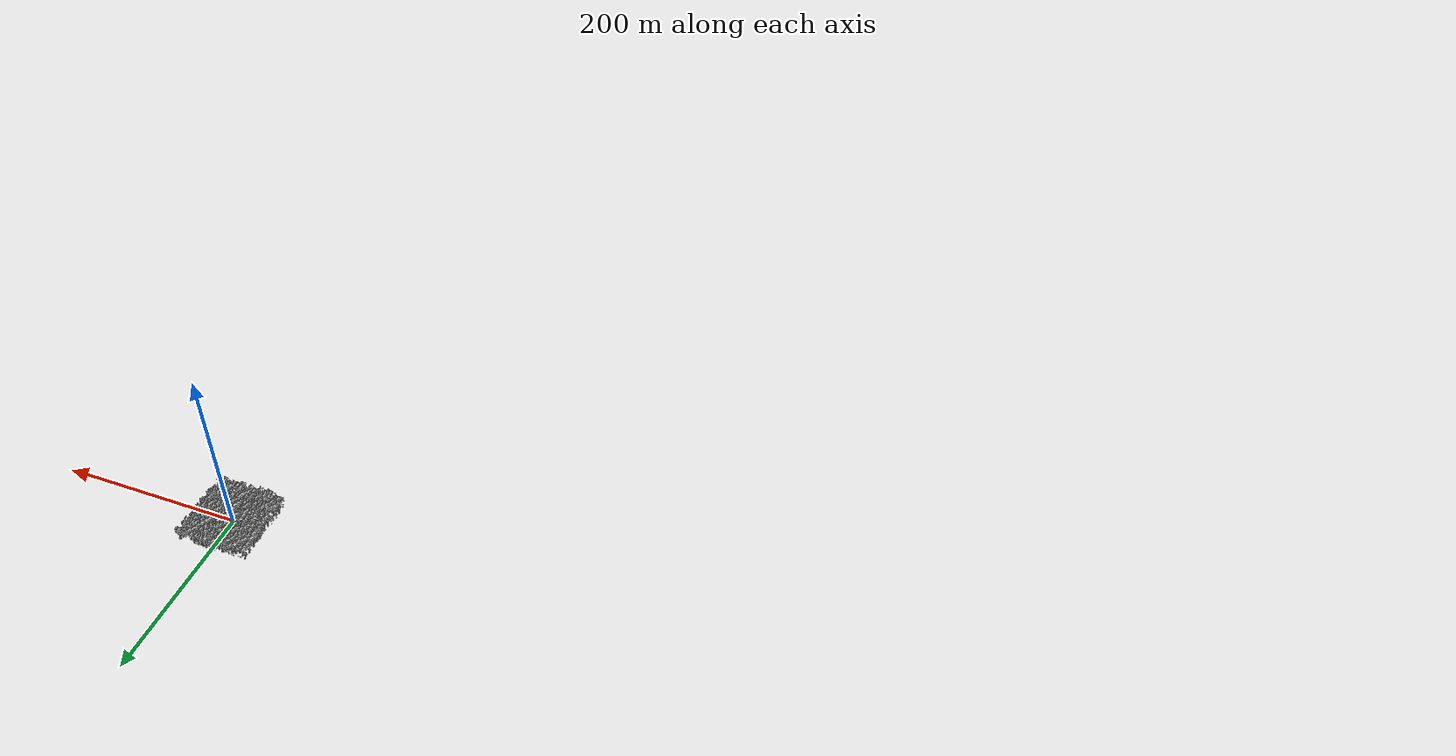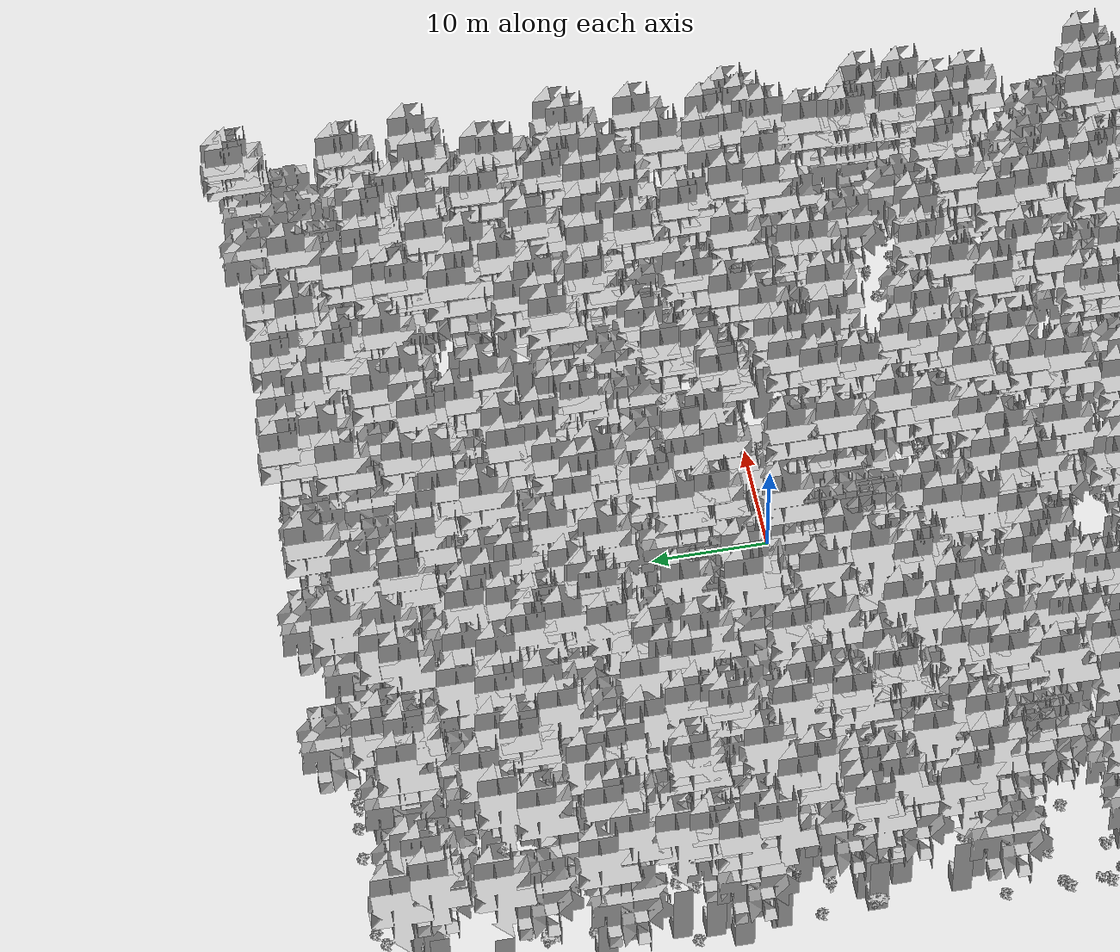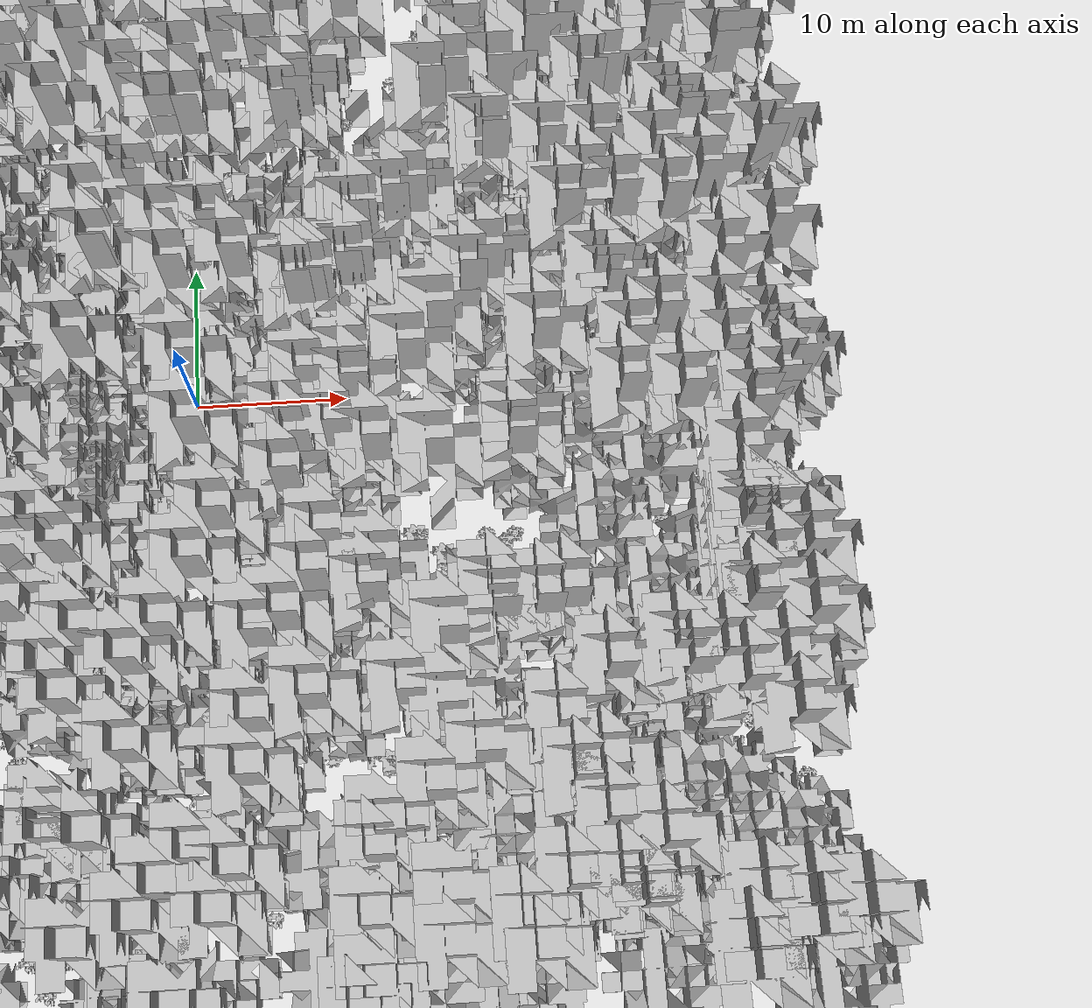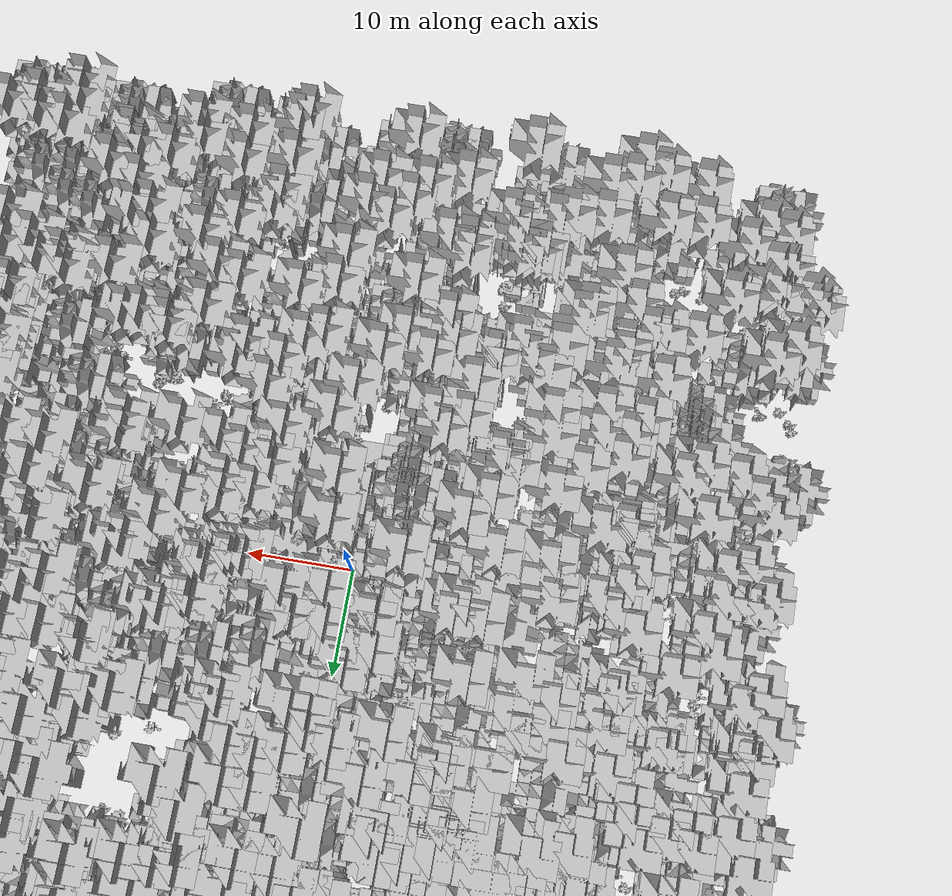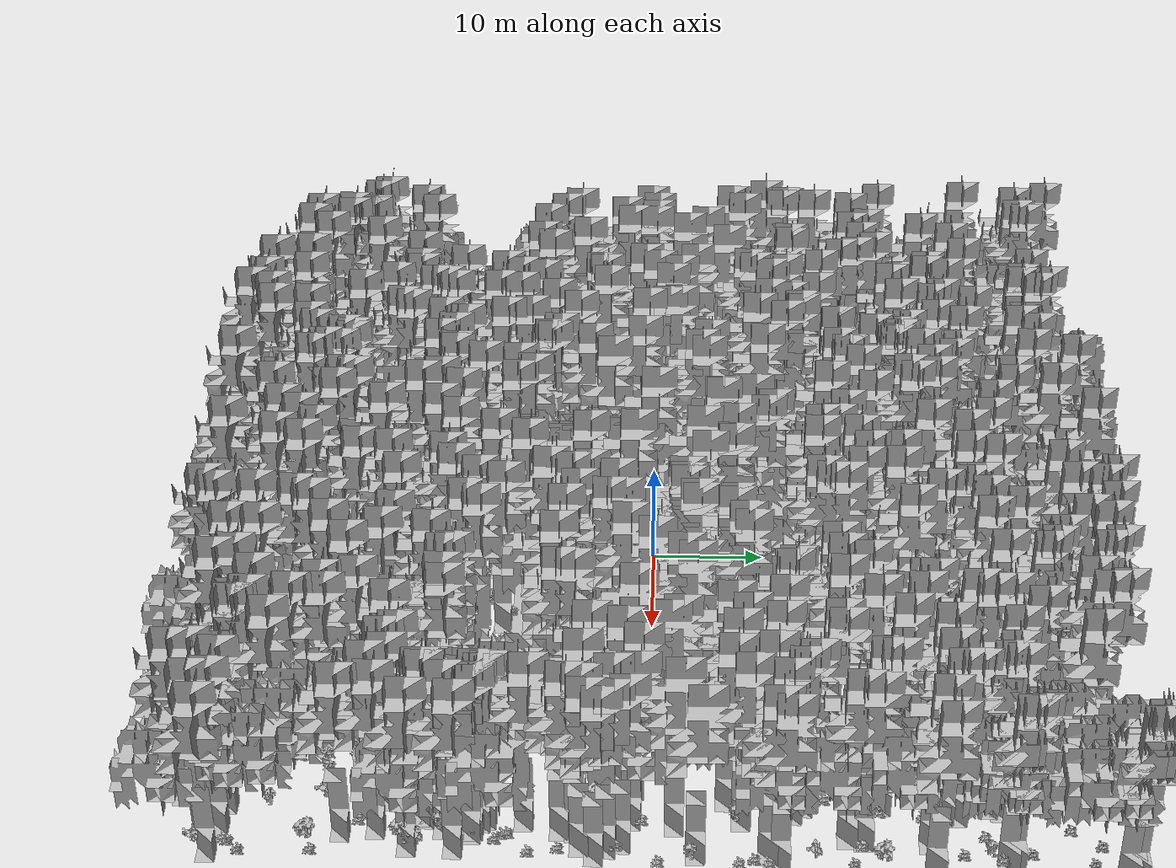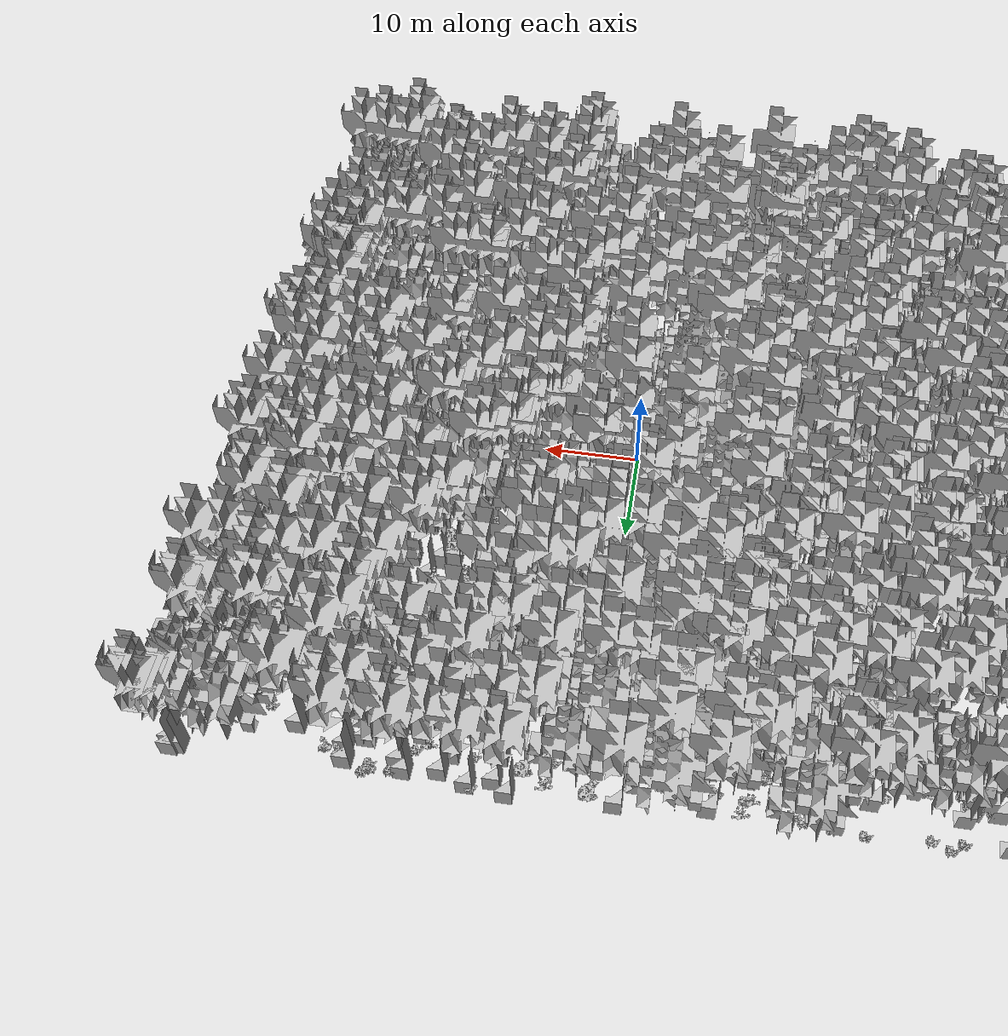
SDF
<sdf version="1.7">
    <world name="default">
        <plugin name="mrs_gazebo_static_transform_republisher_plugin" filename="libMrsGazeboCommonResources_StaticTransformRepublisher.so"/>
        <spherical_coordinates>
            <surface_model>EARTH_WGS84</surface_model>
            <latitude_deg>47.3977</latitude_deg>
            <longitude_deg>8.54559</longitude_deg>
            <elevation>0</elevation>
            <heading_deg>0</heading_deg>
        </spherical_coordinates>
        <physics name="default_physics" default="0" type="ode">
            <ode>
                <solver>
                    <type>quick</type>
                    <iters>10</iters>
                    <sor>1.3</sor>
                    <use_dynamic_moi_rescaling>0</use_dynamic_moi_rescaling>
                </solver>
                <constraints>
                    <cfm>0</cfm>
                    <erp>0.2</erp>
                    <contact_max_correcting_vel>1000</contact_max_correcting_vel>
                    <contact_surface_layer>0.001</contact_surface_layer>
                </constraints>
            </ode>
            <max_step_size>0.004</max_step_size>
            <real_time_factor>1</real_time_factor>
            <real_time_update_rate>250</real_time_update_rate>
        </physics>
        <scene>
            <shadows>0</shadows>
            <ambient>0.4 0.4 0.4 1</ambient>
            <background>0.7 0.7 0.7 1</background>
        </scene>
        <light name="sun" type="directional">
            <pose>0 0 1000 0.4 0.2 0</pose>
            <diffuse>1 1 1 1</diffuse>
            <specular>0.6 0.6 0.6 1</specular>
            <direction>0.1 0.1 -0.9</direction>
            <attenuation>
                <range>20</range>
                <constant>0.5</constant>
                <linear>0.01</linear>
                <quadratic>0.001</quadratic>
            </attenuation>
            <cast_shadows>1</cast_shadows>
            <spot>
                <inner_angle>0</inner_angle>
                <outer_angle>0</outer_angle>
                <falloff>0</falloff>
            </spot>
        </light>
        <model name="ground_plane">
            <static>1</static>
            <link name="link">
                <collision name="collision">
                    <pose>-50 0 0 0 -0 0</pose>
                    <geometry>
                        <plane>
                            <normal>0 0 1</normal>
                            <size>80 80</size>
                        </plane>
                    </geometry>
                    <surface>
                        <contact>
                            <ode>
                                <min_depth>0.01</min_depth>
                                <max_vel>0</max_vel>
                            </ode>
                        </contact>
                        <friction>
                            <ode/>
                            <torsional>
                                <ode/>
                            </torsional>
                        </friction>
                        <bounce/>
                    </surface>
                    <max_contacts>10</max_contacts>
                </collision>
                <visual name="grass">
                    <pose>0 0 0 0 -0 0</pose>
                    <cast_shadows>0</cast_shadows>
                    <geometry>
                        <mesh>
                            <scale>0.46714285714285714 0.46714285714285714 0.1</scale>
                            <uri>file://grass_plane/meshes/grass_plane.dae</uri>
                        </mesh>
                    </geometry>
                </visual>
                <self_collide>0</self_collide>
                <enable_wind>0</enable_wind>
                <kinematic>0</kinematic>
            </link>
        </model>
        <model name="the_void">
            <static>1</static>
            <link name="link">
                <pose>0 0 0.1 0 -0 0</pose>
                <visual name="the_void">
                    <pose>0 0 2 0 -0 0</pose>
                    <geometry>
                        <sphere>
                            <radius>0.25</radius>
                        </sphere>
                    </geometry>
                    <material>
                        <script>
                            <uri>file://media/materials/scripts/Gazebo.material</uri>
                            <name>Gazebo/Black</name>
                        </script>
                    </material>
                </visual>
                <self_collide>0</self_collide>
                <enable_wind>0</enable_wind>
                <kinematic>0</kinematic>
            </link>
            <pose>-1000 -1000 0 0 -0 0</pose>
        </model>
        <gui fullscreen="0">
            <camera name="camera">
                <pose>35.1577 98.6044 40.0204 0 0.407996 -1.99761</pose>
                <view_controller>orbit</view_controller>
                <projection_type>perspective</projection_type>
            </camera>
        </gui>
        <plugin name="mrs_gazebo_rviz_cam_synchronizer" filename="libMrsGazeboCommonResources_RvizCameraSynchronizer.so">
            <target_frame_id>gazebo_user_camera</target_frame_id>
            <world_origin_frame_id>uav1/gps_origin</world_origin_frame_id>
            <frame_to_follow>uav1</frame_to_follow>
        </plugin>
        <gravity>0 0 -9.8066</gravity>
        <magnetic_field>6e-06 2.3e-05 -4.2e-05</magnetic_field>
        <atmosphere type="adiabatic"/>
        <wind/>
        <model name="Tree 0">
            <static>1</static>
            <pose>-23.370540901215033 -33.35442128975242 0 1.57079 -0 0</pose>
            <link name="link">
                <pose>0 0 0 0 -0 0</pose>
                <collision name="collision">
                    <geometry>
                        <mesh>
                            <scale>3.5 5 3.5</scale>
                            <uri>model://tree_2/meshes/tree_2.obj</uri>
                        </mesh>
                    </geometry>
                    <max_contacts>10</max_contacts>
                    <surface>
                        <contact>
                            <ode/>
                        </contact>
                        <bounce/>
                        <friction>
                            <torsional>
                                <ode/>
                            </torsional>
                            <ode/>
                        </friction>
                    </surface>
                </collision>
                <visual name="visual">
                    <geometry>
                        <mesh>
                            <scale>3.5 5 3.5</scale>
                            <uri>model://tree_2/meshes/tree_2.obj</uri>
                        </mesh>
                    </geometry>
                </visual>
                <self_collide>0</self_collide>
                <enable_wind>0</enable_wind>
                <kinematic>0</kinematic>
            </link>
        </model>
        <model name="Tree 1">
            <static>1</static>
            <pose>25.15433106884627 -22.121792688263522 0 1.57079 -0 0</pose>
            <link name="link">
                <pose>0 0 0 0 -0 0</pose>
                <collision name="collision">
                    <geometry>
                        <mesh>
                            <scale>3.5 5 3.5</scale>
                            <uri>model://tree_2/meshes/tree_2.obj</uri>
                        </mesh>
                    </geometry>
                    <max_contacts>10</max_contacts>
                    <surface>
                        <contact>
                            <ode/>
                        </contact>
                        <bounce/>
                        <friction>
                            <torsional>
                                <ode/>
                            </torsional>
                            <ode/>
                        </friction>
                    </surface>
                </collision>
                <visual name="visual">
                    <geometry>
                        <mesh>
                            <scale>3.5 5 3.5</scale>
                            <uri>model://tree_2/meshes/tree_2.obj</uri>
                        </mesh>
                    </geometry>
                </visual>
                <self_collide>0</self_collide>
                <enable_wind>0</enable_wind>
                <kinematic>0</kinematic>
            </link>
        </model>
        <model name="Tree 2">
            <static>1</static>
            <pose>-4.546279242472792 -8.64030182197908 0 1.57079 -0 0</pose>
            <link name="link">
                <pose>0 0 0 0 -0 0</pose>
                <collision name="collision">
                    <geometry>
                        <mesh>
                            <scale>3.5 5 3.5</scale>
                            <uri>model://tree_2/meshes/tree_2.obj</uri>
                        </mesh>
                    </geometry>
                    <max_contacts>10</max_contacts>
                    <surface>
                        <contact>
                            <ode/>
                        </contact>
                        <bounce/>
                        <friction>
                            <torsional>
                                <ode/>
                            </torsional>
                            <ode/>
                        </friction>
                    </surface>
                </collision>
                <visual name="visual">
                    <geometry>
                        <mesh>
                            <scale>3.5 5 3.5</scale>
                            <uri>model://tree_2/meshes/tree_2.obj</uri>
                        </mesh>
                    </geometry>
                </visual>
                <self_collide>0</self_collide>
                <enable_wind>0</enable_wind>
                <kinematic>0</kinematic>
            </link>
        </model>
        <model name="Tree 3">
            <static>1</static>
            <pose>15.683032398997803 14.069243496933879 0 1.57079 -0 0</pose>
            <link name="link">
                <pose>0 0 0 0 -0 0</pose>
                <collision name="collision">
                    <geometry>
                        <mesh>
                            <scale>3.5 5 3.5</scale>
                            <uri>model://tree_2/meshes/tree_2.obj</uri>
                        </mesh>
                    </geometry>
                    <max_contacts>10</max_contacts>
                    <surface>
                        <contact>
                            <ode/>
                        </contact>
                        <bounce/>
                        <friction>
                            <torsional>
                                <ode/>
                            </torsional>
                            <ode/>
                        </friction>
                    </surface>
                </collision>
                <visual name="visual">
                    <geometry>
                        <mesh>
                            <scale>3.5 5 3.5</scale>
                            <uri>model://tree_2/meshes/tree_2.obj</uri>
                        </mesh>
                    </geometry>
                </visual>
                <self_collide>0</self_collide>
                <enable_wind>0</enable_wind>
                <kinematic>0</kinematic>
            </link>
        </model>
        <model name="Tree 4">
            <static>1</static>
            <pose>4.910646198638204 35.413942044048014 0 1.57079 -0 0</pose>
            <link name="link">
                <pose>0 0 0 0 -0 0</pose>
                <collision name="collision">
                    <geometry>
                        <mesh>
                            <scale>3.5 5 3.5</scale>
                            <uri>model://tree_9/meshes/tree_9.obj</uri>
                        </mesh>
                    </geometry>
                    <max_contacts>10</max_contacts>
                    <surface>
                        <contact>
                            <ode/>
                        </contact>
                        <bounce/>
                        <friction>
                            <torsional>
                                <ode/>
                            </torsional>
                            <ode/>
                        </friction>
                    </surface>
                </collision>
                <visual name="visual">
                    <geometry>
                        <mesh>
                            <scale>3.5 5 3.5</scale>
                            <uri>model://tree_9/meshes/tree_9.obj</uri>
                        </mesh>
                    </geometry>
                </visual>
                <self_collide>0</self_collide>
                <enable_wind>0</enable_wind>
                <kinematic>0</kinematic>
            </link>
        </model>
        <model name="Tree 5">
            <static>1</static>
            <pose>-20.84014725361361 7.1038427674684215 0 1.57079 -0 0</pose>
            <link name="link">
                <pose>0 0 0 0 -0 0</pose>
                <collision name="collision">
                    <geometry>
                        <mesh>
                            <scale>3.5 5 3.5</scale>
                            <uri>model://tree_2/meshes/tree_2.obj</uri>
                        </mesh>
                    </geometry>
                    <max_contacts>10</max_contacts>
                    <surface>
                        <contact>
                            <ode/>
                        </contact>
                        <bounce/>
                        <friction>
                            <torsional>
                                <ode/>
                            </torsional>
                            <ode/>
                        </friction>
                    </surface>
                </collision>
                <visual name="visual">
                    <geometry>
                        <mesh>
                            <scale>3.5 5 3.5</scale>
                            <uri>model://tree_2/meshes/tree_2.obj</uri>
                        </mesh>
                    </geometry>
                </visual>
                <self_collide>0</self_collide>
                <enable_wind>0</enable_wind>
                <kinematic>0</kinematic>
            </link>
        </model>
        <model name="Tree 6">
            <static>1</static>
            <pose>-27.933836475124316 9.971024131339455 0 1.57079 -0 0</pose>
            <link name="link">
                <pose>0 0 0 0 -0 0</pose>
                <collision name="collision">
                    <geometry>
                        <mesh>
                            <scale>3.5 5 3.5</scale>
                            <uri>model://tree_2/meshes/tree_2.obj</uri>
                        </mesh>
                    </geometry>
                    <max_contacts>10</max_contacts>
                    <surface>
                        <contact>
                            <ode/>
                        </contact>
                        <bounce/>
                        <friction>
                            <torsional>
                                <ode/>
                            </torsional>
                            <ode/>
                        </friction>
                    </surface>
                </collision>
                <visual name="visual">
                    <geometry>
                        <mesh>
                            <scale>3.5 5 3.5</scale>
                            <uri>model://tree_2/meshes/tree_2.obj</uri>
                        </mesh>
                    </geometry>
                </visual>
                <self_collide>0</self_collide>
                <enable_wind>0</enable_wind>
                <kinematic>0</kinematic>
            </link>
        </model>
        <model name="Tree 7">
            <static>1</static>
            <pose>-17.99532547651775 -37.05101078377296 0 1.57079 -0 0</pose>
            <link name="link">
                <pose>0 0 0 0 -0 0</pose>
                <collision name="collision">
                    <geometry>
                        <mesh>
                            <scale>3.5 5 3.5</scale>
                            <uri>model://tree_9/meshes/tree_9.obj</uri>
                        </mesh>
                    </geometry>
                    <max_contacts>10</max_contacts>
                    <surface>
                        <contact>
                            <ode/>
                        </contact>
                        <bounce/>
                        <friction>
                            <torsional>
                                <ode/>
                            </torsional>
                            <ode/>
                        </friction>
                    </surface>
                </collision>
                <visual name="visual">
                    <geometry>
                        <mesh>
                            <scale>3.5 5 3.5</scale>
                            <uri>model://tree_9/meshes/tree_9.obj</uri>
                        </mesh>
                    </geometry>
                </visual>
                <self_collide>0</self_collide>
                <enable_wind>0</enable_wind>
                <kinematic>0</kinematic>
            </link>
        </model>
        <model name="Tree 8">
            <static>1</static>
            <pose>26.608993075268216 -34.12208442925174 0 1.57079 -0 0</pose>
            <link name="link">
                <pose>0 0 0 0 -0 0</pose>
                <collision name="collision">
                    <geometry>
                        <mesh>
                            <scale>3.5 5 3.5</scale>
                            <uri>model://tree_2/meshes/tree_2.obj</uri>
                        </mesh>
                    </geometry>
                    <max_contacts>10</max_contacts>
                    <surface>
                        <contact>
                            <ode/>
                        </contact>
                        <bounce/>
                        <friction>
                            <torsional>
                                <ode/>
                            </torsional>
                            <ode/>
                        </friction>
                    </surface>
                </collision>
                <visual name="visual">
                    <geometry>
                        <mesh>
                            <scale>3.5 5 3.5</scale>
                            <uri>model://tree_2/meshes/tree_2.obj</uri>
                        </mesh>
                    </geometry>
                </visual>
                <self_collide>0</self_collide>
                <enable_wind>0</enable_wind>
                <kinematic>0</kinematic>
            </link>
        </model>
        <model name="Tree 9">
            <static>1</static>
            <pose>4.20310431743556 26.323700282341363 0 1.57079 -0 0</pose>
            <link name="link">
                <pose>0 0 0 0 -0 0</pose>
                <collision name="collision">
                    <geometry>
                        <mesh>
                            <scale>3.5 5 3.5</scale>
                            <uri>model://tree_2/meshes/tree_2.obj</uri>
                        </mesh>
                    </geometry>
                    <max_contacts>10</max_contacts>
                    <surface>
                        <contact>
                            <ode/>
                        </contact>
                        <bounce/>
                        <friction>
                            <torsional>
                                <ode/>
                            </torsional>
                            <ode/>
                        </friction>
                    </surface>
                </collision>
                <visual name="visual">
                    <geometry>
                        <mesh>
                            <scale>3.5 5 3.5</scale>
                            <uri>model://tree_2/meshes/tree_2.obj</uri>
                        </mesh>
                    </geometry>
                </visual>
                <self_collide>0</self_collide>
                <enable_wind>0</enable_wind>
                <kinematic>0</kinematic>
            </link>
        </model>
        <model name="Tree 10">
            <static>1</static>
            <pose>-25.93647866401887 3.074874967592052 0 1.57079 -0 0</pose>
            <link name="link">
                <pose>0 0 0 0 -0 0</pose>
                <collision name="collision">
                    <geometry>
                        <mesh>
                            <scale>3.5 5 3.5</scale>
                            <uri>model://tree_9/meshes/tree_9.obj</uri>
                        </mesh>
                    </geometry>
                    <max_contacts>10</max_contacts>
                    <surface>
                        <contact>
                            <ode/>
                        </contact>
                        <bounce/>
                        <friction>
                            <torsional>
                                <ode/>
                            </torsional>
                            <ode/>
                        </friction>
                    </surface>
                </collision>
                <visual name="visual">
                    <geometry>
                        <mesh>
                            <scale>3.5 5 3.5</scale>
                            <uri>model://tree_9/meshes/tree_9.obj</uri>
                        </mesh>
                    </geometry>
                </visual>
                <self_collide>0</self_collide>
                <enable_wind>0</enable_wind>
                <kinematic>0</kinematic>
            </link>
        </model>
        <model name="Tree 11">
            <static>1</static>
            <pose>-12.445120965759767 -28.860462719379623 0 1.57079 -0 0</pose>
            <link name="link">
                <pose>0 0 0 0 -0 0</pose>
                <collision name="collision">
                    <geometry>
                        <mesh>
                            <scale>3.5 5 3.5</scale>
                            <uri>model://tree_9/meshes/tree_9.obj</uri>
                        </mesh>
                    </geometry>
                    <max_contacts>10</max_contacts>
                    <surface>
                        <contact>
                            <ode/>
                        </contact>
                        <bounce/>
                        <friction>
                            <torsional>
                                <ode/>
                            </torsional>
                            <ode/>
                        </friction>
                    </surface>
                </collision>
                <visual name="visual">
                    <geometry>
                        <mesh>
                            <scale>3.5 5 3.5</scale>
                            <uri>model://tree_9/meshes/tree_9.obj</uri>
                        </mesh>
                    </geometry>
                </visual>
                <self_collide>0</self_collide>
                <enable_wind>0</enable_wind>
                <kinematic>0</kinematic>
            </link>
        </model>
        <model name="Tree 12">
            <static>1</static>
            <pose>18.471832426741315 2.389748799713736 0 1.57079 -0 0</pose>
            <link name="link">
                <pose>0 0 0 0 -0 0</pose>
                <collision name="collision">
                    <geometry>
                        <mesh>
                            <scale>3.5 5 3.5</scale>
                            <uri>model://tree_9/meshes/tree_9.obj</uri>
                        </mesh>
                    </geometry>
                    <max_contacts>10</max_contacts>
                    <surface>
                        <contact>
                            <ode/>
                        </contact>
                        <bounce/>
                        <friction>
                            <torsional>
                                <ode/>
                            </torsional>
                            <ode/>
                        </friction>
                    </surface>
                </collision>
                <visual name="visual">
                    <geometry>
                        <mesh>
                            <scale>3.5 5 3.5</scale>
                            <uri>model://tree_9/meshes/tree_9.obj</uri>
                        </mesh>
                    </geometry>
                </visual>
                <self_collide>0</self_collide>
                <enable_wind>0</enable_wind>
                <kinematic>0</kinematic>
            </link>
        </model>
        <model name="Tree 13">
            <static>1</static>
            <pose>-16.80717725692306 25.77402200515138 0 1.57079 -0 0</pose>
            <link name="link">
                <pose>0 0 0 0 -0 0</pose>
                <collision name="collision">
                    <geometry>
                        <mesh>
                            <scale>3.5 5 3.5</scale>
                            <uri>model://tree_9/meshes/tree_9.obj</uri>
                        </mesh>
                    </geometry>
                    <max_contacts>10</max_contacts>
                    <surface>
                        <contact>
                            <ode/>
                        </contact>
                        <bounce/>
                        <friction>
                            <torsional>
                                <ode/>
                            </torsional>
                            <ode/>
                        </friction>
                    </surface>
                </collision>
                <visual name="visual">
                    <geometry>
                        <mesh>
                            <scale>3.5 5 3.5</scale>
                            <uri>model://tree_9/meshes/tree_9.obj</uri>
                        </mesh>
                    </geometry>
                </visual>
                <self_collide>0</self_collide>
                <enable_wind>0</enable_wind>
                <kinematic>0</kinematic>
            </link>
        </model>
        <model name="Tree 14">
            <static>1</static>
            <pose>5.384530217257961 -11.58191050145252 0 1.57079 -0 0</pose>
            <link name="link">
                <pose>0 0 0 0 -0 0</pose>
                <collision name="collision">
                    <geometry>
                        <mesh>
                            <scale>3.5 5 3.5</scale>
                            <uri>model://tree_2/meshes/tree_2.obj</uri>
                        </mesh>
                    </geometry>
                    <max_contacts>10</max_contacts>
                    <surface>
                        <contact>
                            <ode/>
                        </contact>
                        <bounce/>
                        <friction>
                            <torsional>
                                <ode/>
                            </torsional>
                            <ode/>
                        </friction>
                    </surface>
                </collision>
                <visual name="visual">
                    <geometry>
                        <mesh>
                            <scale>3.5 5 3.5</scale>
                            <uri>model://tree_2/meshes/tree_2.obj</uri>
                        </mesh>
                    </geometry>
                </visual>
                <self_collide>0</self_collide>
                <enable_wind>0</enable_wind>
                <kinematic>0</kinematic>
            </link>
        </model>
        <model name="Tree 15">
            <static>1</static>
            <pose>-12.438555484064668 21.692388034909236 0 1.57079 -0 0</pose>
            <link name="link">
                <pose>0 0 0 0 -0 0</pose>
                <collision name="collision">
                    <geometry>
                        <mesh>
                            <scale>3.5 5 3.5</scale>
                            <uri>model://tree_9/meshes/tree_9.obj</uri>
                        </mesh>
                    </geometry>
                    <max_contacts>10</max_contacts>
                    <surface>
                        <contact>
                            <ode/>
                        </contact>
                        <bounce/>
                        <friction>
                            <torsional>
                                <ode/>
                            </torsional>
                            <ode/>
                        </friction>
                    </surface>
                </collision>
                <visual name="visual">
                    <geometry>
                        <mesh>
                            <scale>3.5 5 3.5</scale>
                            <uri>model://tree_9/meshes/tree_9.obj</uri>
                        </mesh>
                    </geometry>
                </visual>
                <self_collide>0</self_collide>
                <enable_wind>0</enable_wind>
                <kinematic>0</kinematic>
            </link>
        </model>
        <model name="Tree 16">
            <static>1</static>
            <pose>-16.002377514025188 -20.61025693314008 0 1.57079 -0 0</pose>
            <link name="link">
                <pose>0 0 0 0 -0 0</pose>
                <collision name="collision">
                    <geometry>
                        <mesh>
                            <scale>3.5 5 3.5</scale>
                            <uri>model://tree_9/meshes/tree_9.obj</uri>
                        </mesh>
                    </geometry>
                    <max_contacts>10</max_contacts>
                    <surface>
                        <contact>
                            <ode/>
                        </contact>
                        <bounce/>
                        <friction>
                            <torsional>
                                <ode/>
                            </torsional>
                            <ode/>
                        </friction>
                    </surface>
                </collision>
                <visual name="visual">
                    <geometry>
                        <mesh>
                            <scale>3.5 5 3.5</scale>
                            <uri>model://tree_9/meshes/tree_9.obj</uri>
                        </mesh>
                    </geometry>
                </visual>
                <self_collide>0</self_collide>
                <enable_wind>0</enable_wind>
                <kinematic>0</kinematic>
            </link>
        </model>
        <model name="Tree 17">
            <static>1</static>
            <pose>-21.480236284988532 -20.81113833691318 0 1.57079 -0 0</pose>
            <link name="link">
                <pose>0 0 0 0 -0 0</pose>
                <collision name="collision">
                    <geometry>
                        <mesh>
                            <scale>3.5 5 3.5</scale>
                            <uri>model://tree_9/meshes/tree_9.obj</uri>
                        </mesh>
                    </geometry>
                    <max_contacts>10</max_contacts>
                    <surface>
                        <contact>
                            <ode/>
                        </contact>
                        <bounce/>
                        <friction>
                            <torsional>
                                <ode/>
                            </torsional>
                            <ode/>
                        </friction>
                    </surface>
                </collision>
                <visual name="visual">
                    <geometry>
                        <mesh>
                            <scale>3.5 5 3.5</scale>
                            <uri>model://tree_9/meshes/tree_9.obj</uri>
                        </mesh>
                    </geometry>
                </visual>
                <self_collide>0</self_collide>
                <enable_wind>0</enable_wind>
                <kinematic>0</kinematic>
            </link>
        </model>
        <model name="Tree 18">
            <static>1</static>
            <pose>36.43045669345068 -5.3121024685924 0 1.57079 -0 0</pose>
            <link name="link">
                <pose>0 0 0 0 -0 0</pose>
                <collision name="collision">
                    <geometry>
                        <mesh>
                            <scale>3.5 5 3.5</scale>
                            <uri>model://tree_9/meshes/tree_9.obj</uri>
                        </mesh>
                    </geometry>
                    <max_contacts>10</max_contacts>
                    <surface>
                        <contact>
                            <ode/>
                        </contact>
                        <bounce/>
                        <friction>
                            <torsional>
                                <ode/>
                            </torsional>
                            <ode/>
                        </friction>
                    </surface>
                </collision>
                <visual name="visual">
                    <geometry>
                        <mesh>
                            <scale>3.5 5 3.5</scale>
                            <uri>model://tree_9/meshes/tree_9.obj</uri>
                        </mesh>
                    </geometry>
                </visual>
                <self_collide>0</self_collide>
                <enable_wind>0</enable_wind>
                <kinematic>0</kinematic>
            </link>
        </model>
        <model name="Tree 19">
            <static>1</static>
            <pose>31.57622135617119 -21.32363302971755 0 1.57079 -0 0</pose>
            <link name="link">
                <pose>0 0 0 0 -0 0</pose>
                <collision name="collision">
                    <geometry>
                        <mesh>
                            <scale>3.5 5 3.5</scale>
                            <uri>model://tree_9/meshes/tree_9.obj</uri>
                        </mesh>
                    </geometry>
                    <max_contacts>10</max_contacts>
                    <surface>
                        <contact>
                            <ode/>
                        </contact>
                        <bounce/>
                        <friction>
                            <torsional>
                                <ode/>
                            </torsional>
                            <ode/>
                        </friction>
                    </surface>
                </collision>
                <visual name="visual">
                    <geometry>
                        <mesh>
                            <scale>3.5 5 3.5</scale>
                            <uri>model://tree_9/meshes/tree_9.obj</uri>
                        </mesh>
                    </geometry>
                </visual>
                <self_collide>0</self_collide>
                <enable_wind>0</enable_wind>
                <kinematic>0</kinematic>
            </link>
        </model>
        <model name="Tree 20">
            <static>1</static>
            <pose>6.906737873358004 39.787424470676925 0 1.57079 -0 0</pose>
            <link name="link">
                <pose>0 0 0 0 -0 0</pose>
                <collision name="collision">
                    <geometry>
                        <mesh>
                            <scale>3.5 5 3.5</scale>
                            <uri>model://tree_9/meshes/tree_9.obj</uri>
                        </mesh>
                    </geometry>
                    <max_contacts>10</max_contacts>
                    <surface>
                        <contact>
                            <ode/>
                        </contact>
                        <bounce/>
                        <friction>
                            <torsional>
                                <ode/>
                            </torsional>
                            <ode/>
                        </friction>
                    </surface>
                </collision>
                <visual name="visual">
                    <geometry>
                        <mesh>
                            <scale>3.5 5 3.5</scale>
                            <uri>model://tree_9/meshes/tree_9.obj</uri>
                        </mesh>
                    </geometry>
                </visual>
                <self_collide>0</self_collide>
                <enable_wind>0</enable_wind>
                <kinematic>0</kinematic>
            </link>
        </model>
        <model name="Tree 21">
            <static>1</static>
            <pose>2.1804711164128037 -19.127207961922252 0 1.57079 -0 0</pose>
            <link name="link">
                <pose>0 0 0 0 -0 0</pose>
                <collision name="collision">
                    <geometry>
                        <mesh>
                            <scale>3.5 5 3.5</scale>
                            <uri>model://tree_2/meshes/tree_2.obj</uri>
                        </mesh>
                    </geometry>
                    <max_contacts>10</max_contacts>
                    <surface>
                        <contact>
                            <ode/>
                        </contact>
                        <bounce/>
                        <friction>
                            <torsional>
                                <ode/>
                            </torsional>
                            <ode/>
                        </friction>
                    </surface>
                </collision>
                <visual name="visual">
                    <geometry>
                        <mesh>
                            <scale>3.5 5 3.5</scale>
                            <uri>model://tree_2/meshes/tree_2.obj</uri>
                        </mesh>
                    </geometry>
                </visual>
                <self_collide>0</self_collide>
                <enable_wind>0</enable_wind>
                <kinematic>0</kinematic>
            </link>
        </model>
        <model name="Tree 22">
            <static>1</static>
            <pose>-2.0201217243799547 10.20481954132677 0 1.57079 -0 0</pose>
            <link name="link">
                <pose>0 0 0 0 -0 0</pose>
                <collision name="collision">
                    <geometry>
                        <mesh>
                            <scale>3.5 5 3.5</scale>
                            <uri>model://tree_9/meshes/tree_9.obj</uri>
                        </mesh>
                    </geometry>
                    <max_contacts>10</max_contacts>
                    <surface>
                        <contact>
                            <ode/>
                        </contact>
                        <bounce/>
                        <friction>
                            <torsional>
                                <ode/>
                            </torsional>
                            <ode/>
                        </friction>
                    </surface>
                </collision>
                <visual name="visual">
                    <geometry>
                        <mesh>
                            <scale>3.5 5 3.5</scale>
                            <uri>model://tree_9/meshes/tree_9.obj</uri>
                        </mesh>
                    </geometry>
                </visual>
                <self_collide>0</self_collide>
                <enable_wind>0</enable_wind>
                <kinematic>0</kinematic>
            </link>
        </model>
        <model name="Tree 23">
            <static>1</static>
            <pose>22.057142579652904 -33.21811231558036 0 1.57079 -0 0</pose>
            <link name="link">
                <pose>0 0 0 0 -0 0</pose>
                <collision name="collision">
                    <geometry>
                        <mesh>
                            <scale>3.5 5 3.5</scale>
                            <uri>model://tree_9/meshes/tree_9.obj</uri>
                        </mesh>
                    </geometry>
                    <max_contacts>10</max_contacts>
                    <surface>
                        <contact>
                            <ode/>
                        </contact>
                        <bounce/>
                        <friction>
                            <torsional>
                                <ode/>
                            </torsional>
                            <ode/>
                        </friction>
                    </surface>
                </collision>
                <visual name="visual">
                    <geometry>
                        <mesh>
                            <scale>3.5 5 3.5</scale>
                            <uri>model://tree_9/meshes/tree_9.obj</uri>
                        </mesh>
                    </geometry>
                </visual>
                <self_collide>0</self_collide>
                <enable_wind>0</enable_wind>
                <kinematic>0</kinematic>
            </link>
        </model>
        <model name="Tree 24">
            <static>1</static>
            <pose>-32.78907897571921 -0.9774051345075847 0 1.57079 -0 0</pose>
            <link name="link">
                <pose>0 0 0 0 -0 0</pose>
                <collision name="collision">
                    <geometry>
                        <mesh>
                            <scale>3.5 5 3.5</scale>
                            <uri>model://tree_9/meshes/tree_9.obj</uri>
                        </mesh>
                    </geometry>
                    <max_contacts>10</max_contacts>
                    <surface>
                        <contact>
                            <ode/>
                        </contact>
                        <bounce/>
                        <friction>
                            <torsional>
                                <ode/>
                            </torsional>
                            <ode/>
                        </friction>
                    </surface>
                </collision>
                <visual name="visual">
                    <geometry>
                        <mesh>
                            <scale>3.5 5 3.5</scale>
                            <uri>model://tree_9/meshes/tree_9.obj</uri>
                        </mesh>
                    </geometry>
                </visual>
                <self_collide>0</self_collide>
                <enable_wind>0</enable_wind>
                <kinematic>0</kinematic>
            </link>
        </model>
        <model name="Tree 25">
            <static>1</static>
            <pose>-23.874072191830358 1.5541618502225703 0 1.57079 -0 0</pose>
            <link name="link">
                <pose>0 0 0 0 -0 0</pose>
                <collision name="collision">
                    <geometry>
                        <mesh>
                            <scale>3.5 5 3.5</scale>
                            <uri>model://tree_9/meshes/tree_9.obj</uri>
                        </mesh>
                    </geometry>
                    <max_contacts>10</max_contacts>
                    <surface>
                        <contact>
                            <ode/>
                        </contact>
                        <bounce/>
                        <friction>
                            <torsional>
                                <ode/>
                            </torsional>
                            <ode/>
                        </friction>
                    </surface>
                </collision>
                <visual name="visual">
                    <geometry>
                        <mesh>
                            <scale>3.5 5 3.5</scale>
                            <uri>model://tree_9/meshes/tree_9.obj</uri>
                        </mesh>
                    </geometry>
                </visual>
                <self_collide>0</self_collide>
                <enable_wind>0</enable_wind>
                <kinematic>0</kinematic>
            </link>
        </model>
        <model name="Tree 26">
            <static>1</static>
            <pose>17.845759047053185 7.468501675813918 0 1.57079 -0 0</pose>
            <link name="link">
                <pose>0 0 0 0 -0 0</pose>
                <collision name="collision">
                    <geometry>
                        <mesh>
                            <scale>3.5 5 3.5</scale>
                            <uri>model://tree_2/meshes/tree_2.obj</uri>
                        </mesh>
                    </geometry>
                    <max_contacts>10</max_contacts>
                    <surface>
                        <contact>
                            <ode/>
                        </contact>
                        <bounce/>
                        <friction>
                            <torsional>
                                <ode/>
                            </torsional>
                            <ode/>
                        </friction>
                    </surface>
                </collision>
                <visual name="visual">
                    <geometry>
                        <mesh>
                            <scale>3.5 5 3.5</scale>
                            <uri>model://tree_2/meshes/tree_2.obj</uri>
                        </mesh>
                    </geometry>
                </visual>
                <self_collide>0</self_collide>
                <enable_wind>0</enable_wind>
                <kinematic>0</kinematic>
            </link>
        </model>
        <model name="Tree 27">
            <static>1</static>
            <pose>33.91250878875485 -13.470792606628457 0 1.57079 -0 0</pose>
            <link name="link">
                <pose>0 0 0 0 -0 0</pose>
                <collision name="collision">
                    <geometry>
                        <mesh>
                            <scale>3.5 5 3.5</scale>
                            <uri>model://tree_9/meshes/tree_9.obj</uri>
                        </mesh>
                    </geometry>
                    <max_contacts>10</max_contacts>
                    <surface>
                        <contact>
                            <ode/>
                        </contact>
                        <bounce/>
                        <friction>
                            <torsional>
                                <ode/>
                            </torsional>
                            <ode/>
                        </friction>
                    </surface>
                </collision>
                <visual name="visual">
                    <geometry>
                        <mesh>
                            <scale>3.5 5 3.5</scale>
                            <uri>model://tree_9/meshes/tree_9.obj</uri>
                        </mesh>
                    </geometry>
                </visual>
                <self_collide>0</self_collide>
                <enable_wind>0</enable_wind>
                <kinematic>0</kinematic>
            </link>
        </model>
        <model name="Tree 28">
            <static>1</static>
            <pose>-4.318430323322623 -0.1161629892853 0 1.57079 -0 0</pose>
            <link name="link">
                <pose>0 0 0 0 -0 0</pose>
                <collision name="collision">
                    <geometry>
                        <mesh>
                            <scale>3.5 5 3.5</scale>
                            <uri>model://tree_2/meshes/tree_2.obj</uri>
                        </mesh>
                    </geometry>
                    <max_contacts>10</max_contacts>
                    <surface>
                        <contact>
                            <ode/>
                        </contact>
                        <bounce/>
                        <friction>
                            <torsional>
                                <ode/>
                            </torsional>
                            <ode/>
                        </friction>
                    </surface>
                </collision>
                <visual name="visual">
                    <geometry>
                        <mesh>
                            <scale>3.5 5 3.5</scale>
                            <uri>model://tree_2/meshes/tree_2.obj</uri>
                        </mesh>
                    </geometry>
                </visual>
                <self_collide>0</self_collide>
                <enable_wind>0</enable_wind>
                <kinematic>0</kinematic>
            </link>
        </model>
        <model name="Tree 29">
            <static>1</static>
            <pose>35.23916422666538 17.91605360973555 0 1.57079 -0 0</pose>
            <link name="link">
                <pose>0 0 0 0 -0 0</pose>
                <collision name="collision">
                    <geometry>
                        <mesh>
                            <scale>3.5 5 3.5</scale>
                            <uri>model://tree_9/meshes/tree_9.obj</uri>
                        </mesh>
                    </geometry>
                    <max_contacts>10</max_contacts>
                    <surface>
                        <contact>
                            <ode/>
                        </contact>
                        <bounce/>
                        <friction>
                            <torsional>
                                <ode/>
                            </torsional>
                            <ode/>
                        </friction>
                    </surface>
                </collision>
                <visual name="visual">
                    <geometry>
                        <mesh>
                            <scale>3.5 5 3.5</scale>
                            <uri>model://tree_9/meshes/tree_9.obj</uri>
                        </mesh>
                    </geometry>
                </visual>
                <self_collide>0</self_collide>
                <enable_wind>0</enable_wind>
                <kinematic>0</kinematic>
            </link>
        </model>
        <model name="Tree 30">
            <static>1</static>
            <pose>1.3349887892582686 -2.050556169885752 0 1.57079 -0 0</pose>
            <link name="link">
                <pose>0 0 0 0 -0 0</pose>
                <collision name="collision">
                    <geometry>
                        <mesh>
                            <scale>3.5 5 3.5</scale>
                            <uri>model://tree_9/meshes/tree_9.obj</uri>
                        </mesh>
                    </geometry>
                    <max_contacts>10</max_contacts>
                    <surface>
                        <contact>
                            <ode/>
                        </contact>
                        <bounce/>
                        <friction>
                            <torsional>
                                <ode/>
                            </torsional>
                            <ode/>
                        </friction>
                    </surface>
                </collision>
                <visual name="visual">
                    <geometry>
                        <mesh>
                            <scale>3.5 5 3.5</scale>
                            <uri>model://tree_9/meshes/tree_9.obj</uri>
                        </mesh>
                    </geometry>
                </visual>
                <self_collide>0</self_collide>
                <enable_wind>0</enable_wind>
                <kinematic>0</kinematic>
            </link>
        </model>
        <model name="Tree 31">
            <static>1</static>
            <pose>26.013760197732935 -34.41507662786235 0 1.57079 -0 0</pose>
            <link name="link">
                <pose>0 0 0 0 -0 0</pose>
                <collision name="collision">
                    <geometry>
                        <mesh>
                            <scale>3.5 5 3.5</scale>
                            <uri>model://tree_9/meshes/tree_9.obj</uri>
                        </mesh>
                    </geometry>
                    <max_contacts>10</max_contacts>
                    <surface>
                        <contact>
                            <ode/>
                        </contact>
                        <bounce/>
                        <friction>
                            <torsional>
                                <ode/>
                            </torsional>
                            <ode/>
                        </friction>
                    </surface>
                </collision>
                <visual name="visual">
                    <geometry>
                        <mesh>
                            <scale>3.5 5 3.5</scale>
                            <uri>model://tree_9/meshes/tree_9.obj</uri>
                        </mesh>
                    </geometry>
                </visual>
                <self_collide>0</self_collide>
                <enable_wind>0</enable_wind>
                <kinematic>0</kinematic>
            </link>
        </model>
        <model name="Tree 32">
            <static>1</static>
            <pose>11.33506674609081 -31.073006862445787 0 1.57079 -0 0</pose>
            <link name="link">
                <pose>0 0 0 0 -0 0</pose>
                <collision name="collision">
                    <geometry>
                        <mesh>
                            <scale>3.5 5 3.5</scale>
                            <uri>model://tree_9/meshes/tree_9.obj</uri>
                        </mesh>
                    </geometry>
                    <max_contacts>10</max_contacts>
                    <surface>
                        <contact>
                            <ode/>
                        </contact>
                        <bounce/>
                        <friction>
                            <torsional>
                                <ode/>
                            </torsional>
                            <ode/>
                        </friction>
                    </surface>
                </collision>
                <visual name="visual">
                    <geometry>
                        <mesh>
                            <scale>3.5 5 3.5</scale>
                            <uri>model://tree_9/meshes/tree_9.obj</uri>
                        </mesh>
                    </geometry>
                </visual>
                <self_collide>0</self_collide>
                <enable_wind>0</enable_wind>
                <kinematic>0</kinematic>
            </link>
        </model>
        <model name="Tree 33">
            <static>1</static>
            <pose>35.25263064536574 -33.9643759147954 0 1.57079 -0 0</pose>
            <link name="link">
                <pose>0 0 0 0 -0 0</pose>
                <collision name="collision">
                    <geometry>
                        <mesh>
                            <scale>3.5 5 3.5</scale>
                            <uri>model://tree_2/meshes/tree_2.obj</uri>
                        </mesh>
                    </geometry>
                    <max_contacts>10</max_contacts>
                    <surface>
                        <contact>
                            <ode/>
                        </contact>
                        <bounce/>
                        <friction>
                            <torsional>
                                <ode/>
                            </torsional>
                            <ode/>
                        </friction>
                    </surface>
                </collision>
                <visual name="visual">
                    <geometry>
                        <mesh>
                            <scale>3.5 5 3.5</scale>
                            <uri>model://tree_2/meshes/tree_2.obj</uri>
                        </mesh>
                    </geometry>
                </visual>
                <self_collide>0</self_collide>
                <enable_wind>0</enable_wind>
                <kinematic>0</kinematic>
            </link>
        </model>
        <model name="Tree 34">
            <static>1</static>
            <pose>27.1355435834421 1.2390537901242737 0 1.57079 -0 0</pose>
            <link name="link">
                <pose>0 0 0 0 -0 0</pose>
                <collision name="collision">
                    <geometry>
                        <mesh>
                            <scale>3.5 5 3.5</scale>
                            <uri>model://tree_9/meshes/tree_9.obj</uri>
                        </mesh>
                    </geometry>
                    <max_contacts>10</max_contacts>
                    <surface>
                        <contact>
                            <ode/>
                        </contact>
                        <bounce/>
                        <friction>
                            <torsional>
                                <ode/>
                            </torsional>
                            <ode/>
                        </friction>
                    </surface>
                </collision>
                <visual name="visual">
                    <geometry>
                        <mesh>
                            <scale>3.5 5 3.5</scale>
                            <uri>model://tree_9/meshes/tree_9.obj</uri>
                        </mesh>
                    </geometry>
                </visual>
                <self_collide>0</self_collide>
                <enable_wind>0</enable_wind>
                <kinematic>0</kinematic>
            </link>
        </model>
        <model name="Tree 35">
            <static>1</static>
            <pose>30.797695163887965 -5.788937927210171 0 1.57079 -0 0</pose>
            <link name="link">
                <pose>0 0 0 0 -0 0</pose>
                <collision name="collision">
                    <geometry>
                        <mesh>
                            <scale>3.5 5 3.5</scale>
                            <uri>model://tree_9/meshes/tree_9.obj</uri>
                        </mesh>
                    </geometry>
                    <max_contacts>10</max_contacts>
                    <surface>
                        <contact>
                            <ode/>
                        </contact>
                        <bounce/>
                        <friction>
                            <torsional>
                                <ode/>
                            </torsional>
                            <ode/>
                        </friction>
                    </surface>
                </collision>
                <visual name="visual">
                    <geometry>
                        <mesh>
                            <scale>3.5 5 3.5</scale>
                            <uri>model://tree_9/meshes/tree_9.obj</uri>
                        </mesh>
                    </geometry>
                </visual>
                <self_collide>0</self_collide>
                <enable_wind>0</enable_wind>
                <kinematic>0</kinematic>
            </link>
        </model>
        <model name="Tree 36">
            <static>1</static>
            <pose>24.55281254851389 6.53174188876779 0 1.57079 -0 0</pose>
            <link name="link">
                <pose>0 0 0 0 -0 0</pose>
                <collision name="collision">
                    <geometry>
                        <mesh>
                            <scale>3.5 5 3.5</scale>
                            <uri>model://tree_9/meshes/tree_9.obj</uri>
                        </mesh>
                    </geometry>
                    <max_contacts>10</max_contacts>
                    <surface>
                        <contact>
                            <ode/>
                        </contact>
                        <bounce/>
                        <friction>
                            <torsional>
                                <ode/>
                            </torsional>
                            <ode/>
                        </friction>
                    </surface>
                </collision>
                <visual name="visual">
                    <geometry>
                        <mesh>
                            <scale>3.5 5 3.5</scale>
                            <uri>model://tree_9/meshes/tree_9.obj</uri>
                        </mesh>
                    </geometry>
                </visual>
                <self_collide>0</self_collide>
                <enable_wind>0</enable_wind>
                <kinematic>0</kinematic>
            </link>
        </model>
        <model name="Tree 37">
            <static>1</static>
            <pose>2.954171007424989 -11.597068263060475 0 1.57079 -0 0</pose>
            <link name="link">
                <pose>0 0 0 0 -0 0</pose>
                <collision name="collision">
                    <geometry>
                        <mesh>
                            <scale>3.5 5 3.5</scale>
                            <uri>model://tree_9/meshes/tree_9.obj</uri>
                        </mesh>
                    </geometry>
                    <max_contacts>10</max_contacts>
                    <surface>
                        <contact>
                            <ode/>
                        </contact>
                        <bounce/>
                        <friction>
                            <torsional>
                                <ode/>
                            </torsional>
                            <ode/>
                        </friction>
                    </surface>
                </collision>
                <visual name="visual">
                    <geometry>
                        <mesh>
                            <scale>3.5 5 3.5</scale>
                            <uri>model://tree_9/meshes/tree_9.obj</uri>
                        </mesh>
                    </geometry>
                </visual>
                <self_collide>0</self_collide>
                <enable_wind>0</enable_wind>
                <kinematic>0</kinematic>
            </link>
        </model>
        <model name="Tree 38">
            <static>1</static>
            <pose>-31.90999270987562 3.45453961454475 0 1.57079 -0 0</pose>
            <link name="link">
                <pose>0 0 0 0 -0 0</pose>
                <collision name="collision">
                    <geometry>
                        <mesh>
                            <scale>3.5 5 3.5</scale>
                            <uri>model://tree_2/meshes/tree_2.obj</uri>
                        </mesh>
                    </geometry>
                    <max_contacts>10</max_contacts>
                    <surface>
                        <contact>
                            <ode/>
                        </contact>
                        <bounce/>
                        <friction>
                            <torsional>
                                <ode/>
                            </torsional>
                            <ode/>
                        </friction>
                    </surface>
                </collision>
                <visual name="visual">
                    <geometry>
                        <mesh>
                            <scale>3.5 5 3.5</scale>
                            <uri>model://tree_2/meshes/tree_2.obj</uri>
                        </mesh>
                    </geometry>
                </visual>
                <self_collide>0</self_collide>
                <enable_wind>0</enable_wind>
                <kinematic>0</kinematic>
            </link>
        </model>
        <model name="Tree 39">
            <static>1</static>
            <pose>-13.550032410327429 20.429703003380055 0 1.57079 -0 0</pose>
            <link name="link">
                <pose>0 0 0 0 -0 0</pose>
                <collision name="collision">
                    <geometry>
                        <mesh>
                            <scale>3.5 5 3.5</scale>
                            <uri>model://tree_2/meshes/tree_2.obj</uri>
                        </mesh>
                    </geometry>
                    <max_contacts>10</max_contacts>
                    <surface>
                        <contact>
                            <ode/>
                        </contact>
                        <bounce/>
                        <friction>
                            <torsional>
                                <ode/>
                            </torsional>
                            <ode/>
                        </friction>
                    </surface>
                </collision>
                <visual name="visual">
                    <geometry>
                        <mesh>
                            <scale>3.5 5 3.5</scale>
                            <uri>model://tree_2/meshes/tree_2.obj</uri>
                        </mesh>
                    </geometry>
                </visual>
                <self_collide>0</self_collide>
                <enable_wind>0</enable_wind>
                <kinematic>0</kinematic>
            </link>
        </model>
        <model name="Tree 40">
            <static>1</static>
            <pose>-17.46964177701019 -7.906916988267902 0 1.57079 -0 0</pose>
            <link name="link">
                <pose>0 0 0 0 -0 0</pose>
                <collision name="collision">
                    <geometry>
                        <mesh>
                            <scale>3.5 5 3.5</scale>
                            <uri>model://tree_9/meshes/tree_9.obj</uri>
                        </mesh>
                    </geometry>
                    <max_contacts>10</max_contacts>
                    <surface>
                        <contact>
                            <ode/>
                        </contact>
                        <bounce/>
                        <friction>
                            <torsional>
                                <ode/>
                            </torsional>
                            <ode/>
                        </friction>
                    </surface>
                </collision>
                <visual name="visual">
                    <geometry>
                        <mesh>
                            <scale>3.5 5 3.5</scale>
                            <uri>model://tree_9/meshes/tree_9.obj</uri>
                        </mesh>
                    </geometry>
                </visual>
                <self_collide>0</self_collide>
                <enable_wind>0</enable_wind>
                <kinematic>0</kinematic>
            </link>
        </model>
        <model name="Tree 41">
            <static>1</static>
            <pose>37.726126253593876 -35.63986922614796 0 1.57079 -0 0</pose>
            <link name="link">
                <pose>0 0 0 0 -0 0</pose>
                <collision name="collision">
                    <geometry>
                        <mesh>
                            <scale>3.5 5 3.5</scale>
                            <uri>model://tree_9/meshes/tree_9.obj</uri>
                        </mesh>
                    </geometry>
                    <max_contacts>10</max_contacts>
                    <surface>
                        <contact>
                            <ode/>
                        </contact>
                        <bounce/>
                        <friction>
                            <torsional>
                                <ode/>
                            </torsional>
                            <ode/>
                        </friction>
                    </surface>
                </collision>
                <visual name="visual">
                    <geometry>
                        <mesh>
                            <scale>3.5 5 3.5</scale>
                            <uri>model://tree_9/meshes/tree_9.obj</uri>
                        </mesh>
                    </geometry>
                </visual>
                <self_collide>0</self_collide>
                <enable_wind>0</enable_wind>
                <kinematic>0</kinematic>
            </link>
        </model>
        <model name="Tree 42">
            <static>1</static>
            <pose>4.334344160294933 29.720558247666077 0 1.57079 -0 0</pose>
            <link name="link">
                <pose>0 0 0 0 -0 0</pose>
                <collision name="collision">
                    <geometry>
                        <mesh>
                            <scale>3.5 5 3.5</scale>
                            <uri>model://tree_2/meshes/tree_2.obj</uri>
                        </mesh>
                    </geometry>
                    <max_contacts>10</max_contacts>
                    <surface>
                        <contact>
                            <ode/>
                        </contact>
                        <bounce/>
                        <friction>
                            <torsional>
                                <ode/>
                            </torsional>
                            <ode/>
                        </friction>
                    </surface>
                </collision>
                <visual name="visual">
                    <geometry>
                        <mesh>
                            <scale>3.5 5 3.5</scale>
                            <uri>model://tree_2/meshes/tree_2.obj</uri>
                        </mesh>
                    </geometry>
                </visual>
                <self_collide>0</self_collide>
                <enable_wind>0</enable_wind>
                <kinematic>0</kinematic>
            </link>
        </model>
        <model name="Tree 43">
            <static>1</static>
            <pose>34.57953559666831 -35.51637491774482 0 1.57079 -0 0</pose>
            <link name="link">
                <pose>0 0 0 0 -0 0</pose>
                <collision name="collision">
                    <geometry>
                        <mesh>
                            <scale>3.5 5 3.5</scale>
                            <uri>model://tree_2/meshes/tree_2.obj</uri>
                        </mesh>
                    </geometry>
                    <max_contacts>10</max_contacts>
                    <surface>
                        <contact>
                            <ode/>
                        </contact>
                        <bounce/>
                        <friction>
                            <torsional>
                                <ode/>
                            </torsional>
                            <ode/>
                        </friction>
                    </surface>
                </collision>
                <visual name="visual">
                    <geometry>
                        <mesh>
                            <scale>3.5 5 3.5</scale>
                            <uri>model://tree_2/meshes/tree_2.obj</uri>
                        </mesh>
                    </geometry>
                </visual>
                <self_collide>0</self_collide>
                <enable_wind>0</enable_wind>
                <kinematic>0</kinematic>
            </link>
        </model>
        <model name="Tree 44">
            <static>1</static>
            <pose>8.104884163409068 2.35524495685614 0 1.57079 -0 0</pose>
            <link name="link">
                <pose>0 0 0 0 -0 0</pose>
                <collision name="collision">
                    <geometry>
                        <mesh>
                            <scale>3.5 5 3.5</scale>
                            <uri>model://tree_9/meshes/tree_9.obj</uri>
                        </mesh>
                    </geometry>
                    <max_contacts>10</max_contacts>
                    <surface>
                        <contact>
                            <ode/>
                        </contact>
                        <bounce/>
                        <friction>
                            <torsional>
                                <ode/>
                            </torsional>
                            <ode/>
                        </friction>
                    </surface>
                </collision>
                <visual name="visual">
                    <geometry>
                        <mesh>
                            <scale>3.5 5 3.5</scale>
                            <uri>model://tree_9/meshes/tree_9.obj</uri>
                        </mesh>
                    </geometry>
                </visual>
                <self_collide>0</self_collide>
                <enable_wind>0</enable_wind>
                <kinematic>0</kinematic>
            </link>
        </model>
        <model name="Tree 45">
            <static>1</static>
            <pose>17.341034068581827 -24.38808619244524 0 1.57079 -0 0</pose>
            <link name="link">
                <pose>0 0 0 0 -0 0</pose>
                <collision name="collision">
                    <geometry>
                        <mesh>
                            <scale>3.5 5 3.5</scale>
                            <uri>model://tree_2/meshes/tree_2.obj</uri>
                        </mesh>
                    </geometry>
                    <max_contacts>10</max_contacts>
                    <surface>
                        <contact>
                            <ode/>
                        </contact>
                        <bounce/>
                        <friction>
                            <torsional>
                                <ode/>
                            </torsional>
                            <ode/>
                        </friction>
                    </surface>
                </collision>
                <visual name="visual">
                    <geometry>
                        <mesh>
                            <scale>3.5 5 3.5</scale>
                            <uri>model://tree_2/meshes/tree_2.obj</uri>
                        </mesh>
                    </geometry>
                </visual>
                <self_collide>0</self_collide>
                <enable_wind>0</enable_wind>
                <kinematic>0</kinematic>
            </link>
        </model>
        <model name="Tree 46">
            <static>1</static>
            <pose>27.4383515536545 10.445893047082691 0 1.57079 -0 0</pose>
            <link name="link">
                <pose>0 0 0 0 -0 0</pose>
                <collision name="collision">
                    <geometry>
                        <mesh>
                            <scale>3.5 5 3.5</scale>
                            <uri>model://tree_2/meshes/tree_2.obj</uri>
                        </mesh>
                    </geometry>
                    <max_contacts>10</max_contacts>
                    <surface>
                        <contact>
                            <ode/>
                        </contact>
                        <bounce/>
                        <friction>
                            <torsional>
                                <ode/>
                            </torsional>
                            <ode/>
                        </friction>
                    </surface>
                </collision>
                <visual name="visual">
                    <geometry>
                        <mesh>
                            <scale>3.5 5 3.5</scale>
                            <uri>model://tree_2/meshes/tree_2.obj</uri>
                        </mesh>
                    </geometry>
                </visual>
                <self_collide>0</self_collide>
                <enable_wind>0</enable_wind>
                <kinematic>0</kinematic>
            </link>
        </model>
        <model name="Tree 47">
            <static>1</static>
            <pose>7.643115047964308 14.256995909459285 0 1.57079 -0 0</pose>
            <link name="link">
                <pose>0 0 0 0 -0 0</pose>
                <collision name="collision">
                    <geometry>
                        <mesh>
                            <scale>3.5 5 3.5</scale>
                            <uri>model://tree_9/meshes/tree_9.obj</uri>
                        </mesh>
                    </geometry>
                    <max_contacts>10</max_contacts>
                    <surface>
                        <contact>
                            <ode/>
                        </contact>
                        <bounce/>
                        <friction>
                            <torsional>
                                <ode/>
                            </torsional>
                            <ode/>
                        </friction>
                    </surface>
                </collision>
                <visual name="visual">
                    <geometry>
                        <mesh>
                            <scale>3.5 5 3.5</scale>
                            <uri>model://tree_9/meshes/tree_9.obj</uri>
                        </mesh>
                    </geometry>
                </visual>
                <self_collide>0</self_collide>
                <enable_wind>0</enable_wind>
                <kinematic>0</kinematic>
            </link>
        </model>
        <model name="Tree 48">
            <static>1</static>
            <pose>33.62735261121554 -1.3660964412786143 0 1.57079 -0 0</pose>
            <link name="link">
                <pose>0 0 0 0 -0 0</pose>
                <collision name="collision">
                    <geometry>
                        <mesh>
                            <scale>3.5 5 3.5</scale>
                            <uri>model://tree_2/meshes/tree_2.obj</uri>
                        </mesh>
                    </geometry>
                    <max_contacts>10</max_contacts>
                    <surface>
                        <contact>
                            <ode/>
                        </contact>
                        <bounce/>
                        <friction>
                            <torsional>
                                <ode/>
                            </torsional>
                            <ode/>
                        </friction>
                    </surface>
                </collision>
                <visual name="visual">
                    <geometry>
                        <mesh>
                            <scale>3.5 5 3.5</scale>
                            <uri>model://tree_2/meshes/tree_2.obj</uri>
                        </mesh>
                    </geometry>
                </visual>
                <self_collide>0</self_collide>
                <enable_wind>0</enable_wind>
                <kinematic>0</kinematic>
            </link>
        </model>
        <model name="Tree 49">
            <static>1</static>
            <pose>-5.182883097933043 -0.32822462516662654 0 1.57079 -0 0</pose>
            <link name="link">
                <pose>0 0 0 0 -0 0</pose>
                <collision name="collision">
                    <geometry>
                        <mesh>
                            <scale>3.5 5 3.5</scale>
                            <uri>model://tree_9/meshes/tree_9.obj</uri>
                        </mesh>
                    </geometry>
                    <max_contacts>10</max_contacts>
                    <surface>
                        <contact>
                            <ode/>
                        </contact>
                        <bounce/>
                        <friction>
                            <torsional>
                                <ode/>
                            </torsional>
                            <ode/>
                        </friction>
                    </surface>
                </collision>
                <visual name="visual">
                    <geometry>
                        <mesh>
                            <scale>3.5 5 3.5</scale>
                            <uri>model://tree_9/meshes/tree_9.obj</uri>
                        </mesh>
                    </geometry>
                </visual>
                <self_collide>0</self_collide>
                <enable_wind>0</enable_wind>
                <kinematic>0</kinematic>
            </link>
        </model>
        <model name="Tree 50">
            <static>1</static>
            <pose>25.119805464173673 -21.747628831073655 0 1.57079 -0 0</pose>
            <link name="link">
                <pose>0 0 0 0 -0 0</pose>
                <collision name="collision">
                    <geometry>
                        <mesh>
                            <scale>3.5 5 3.5</scale>
                            <uri>model://tree_9/meshes/tree_9.obj</uri>
                        </mesh>
                    </geometry>
                    <max_contacts>10</max_contacts>
                    <surface>
                        <contact>
                            <ode/>
                        </contact>
                        <bounce/>
                        <friction>
                            <torsional>
                                <ode/>
                            </torsional>
                            <ode/>
                        </friction>
                    </surface>
                </collision>
                <visual name="visual">
                    <geometry>
                        <mesh>
                            <scale>3.5 5 3.5</scale>
                            <uri>model://tree_9/meshes/tree_9.obj</uri>
                        </mesh>
                    </geometry>
                </visual>
                <self_collide>0</self_collide>
                <enable_wind>0</enable_wind>
                <kinematic>0</kinematic>
            </link>
        </model>
        <model name="Tree 51">
            <static>1</static>
            <pose>9.193807514105771 -13.312954723415533 0 1.57079 -0 0</pose>
            <link name="link">
                <pose>0 0 0 0 -0 0</pose>
                <collision name="collision">
                    <geometry>
                        <mesh>
                            <scale>3.5 5 3.5</scale>
                            <uri>model://tree_9/meshes/tree_9.obj</uri>
                        </mesh>
                    </geometry>
                    <max_contacts>10</max_contacts>
                    <surface>
                        <contact>
                            <ode/>
                        </contact>
                        <bounce/>
                        <friction>
                            <torsional>
                                <ode/>
                            </torsional>
                            <ode/>
                        </friction>
                    </surface>
                </collision>
                <visual name="visual">
                    <geometry>
                        <mesh>
                            <scale>3.5 5 3.5</scale>
                            <uri>model://tree_9/meshes/tree_9.obj</uri>
                        </mesh>
                    </geometry>
                </visual>
                <self_collide>0</self_collide>
                <enable_wind>0</enable_wind>
                <kinematic>0</kinematic>
            </link>
        </model>
        <model name="Tree 52">
            <static>1</static>
            <pose>-5.46918117928891 -2.325376790559446 0 1.57079 -0 0</pose>
            <link name="link">
                <pose>0 0 0 0 -0 0</pose>
                <collision name="collision">
                    <geometry>
                        <mesh>
                            <scale>3.5 5 3.5</scale>
                            <uri>model://tree_2/meshes/tree_2.obj</uri>
                        </mesh>
                    </geometry>
                    <max_contacts>10</max_contacts>
                    <surface>
                        <contact>
                            <ode/>
                        </contact>
                        <bounce/>
                        <friction>
                            <torsional>
                                <ode/>
                            </torsional>
                            <ode/>
                        </friction>
                    </surface>
                </collision>
                <visual name="visual">
                    <geometry>
                        <mesh>
                            <scale>3.5 5 3.5</scale>
                            <uri>model://tree_2/meshes/tree_2.obj</uri>
                        </mesh>
                    </geometry>
                </visual>
                <self_collide>0</self_collide>
                <enable_wind>0</enable_wind>
                <kinematic>0</kinematic>
            </link>
        </model>
        <model name="Tree 53">
            <static>1</static>
            <pose>-32.948431894712336 -3.2336883667602123 0 1.57079 -0 0</pose>
            <link name="link">
                <pose>0 0 0 0 -0 0</pose>
                <collision name="collision">
                    <geometry>
                        <mesh>
                            <scale>3.5 5 3.5</scale>
                            <uri>model://tree_9/meshes/tree_9.obj</uri>
                        </mesh>
                    </geometry>
                    <max_contacts>10</max_contacts>
                    <surface>
                        <contact>
                            <ode/>
                        </contact>
                        <bounce/>
                        <friction>
                            <torsional>
                                <ode/>
                            </torsional>
                            <ode/>
                        </friction>
                    </surface>
                </collision>
                <visual name="visual">
                    <geometry>
                        <mesh>
                            <scale>3.5 5 3.5</scale>
                            <uri>model://tree_9/meshes/tree_9.obj</uri>
                        </mesh>
                    </geometry>
                </visual>
                <self_collide>0</self_collide>
                <enable_wind>0</enable_wind>
                <kinematic>0</kinematic>
            </link>
        </model>
        <model name="Tree 54">
            <static>1</static>
            <pose>14.570710082538113 29.037128638686568 0 1.57079 -0 0</pose>
            <link name="link">
                <pose>0 0 0 0 -0 0</pose>
                <collision name="collision">
                    <geometry>
                        <mesh>
                            <scale>3.5 5 3.5</scale>
                            <uri>model://tree_2/meshes/tree_2.obj</uri>
                        </mesh>
                    </geometry>
                    <max_contacts>10</max_contacts>
                    <surface>
                        <contact>
                            <ode/>
                        </contact>
                        <bounce/>
                        <friction>
                            <torsional>
                                <ode/>
                            </torsional>
                            <ode/>
                        </friction>
                    </surface>
                </collision>
                <visual name="visual">
                    <geometry>
                        <mesh>
                            <scale>3.5 5 3.5</scale>
                            <uri>model://tree_2/meshes/tree_2.obj</uri>
                        </mesh>
                    </geometry>
                </visual>
                <self_collide>0</self_collide>
                <enable_wind>0</enable_wind>
                <kinematic>0</kinematic>
            </link>
        </model>
        <model name="Tree 55">
            <static>1</static>
            <pose>14.825840101926893 30.834175940176195 0 1.57079 -0 0</pose>
            <link name="link">
                <pose>0 0 0 0 -0 0</pose>
                <collision name="collision">
                    <geometry>
                        <mesh>
                            <scale>3.5 5 3.5</scale>
                            <uri>model://tree_2/meshes/tree_2.obj</uri>
                        </mesh>
                    </geometry>
                    <max_contacts>10</max_contacts>
                    <surface>
                        <contact>
                            <ode/>
                        </contact>
                        <bounce/>
                        <friction>
                            <torsional>
                                <ode/>
                            </torsional>
                            <ode/>
                        </friction>
                    </surface>
                </collision>
                <visual name="visual">
                    <geometry>
                        <mesh>
                            <scale>3.5 5 3.5</scale>
                            <uri>model://tree_2/meshes/tree_2.obj</uri>
                        </mesh>
                    </geometry>
                </visual>
                <self_collide>0</self_collide>
                <enable_wind>0</enable_wind>
                <kinematic>0</kinematic>
            </link>
        </model>
        <model name="Tree 56">
            <static>1</static>
            <pose>26.8419181199542 24.100557964504972 0 1.57079 -0 0</pose>
            <link name="link">
                <pose>0 0 0 0 -0 0</pose>
                <collision name="collision">
                    <geometry>
                        <mesh>
                            <scale>3.5 5 3.5</scale>
                            <uri>model://tree_9/meshes/tree_9.obj</uri>
                        </mesh>
                    </geometry>
                    <max_contacts>10</max_contacts>
                    <surface>
                        <contact>
                            <ode/>
                        </contact>
                        <bounce/>
                        <friction>
                            <torsional>
                                <ode/>
                            </torsional>
                            <ode/>
                        </friction>
                    </surface>
                </collision>
                <visual name="visual">
                    <geometry>
                        <mesh>
                            <scale>3.5 5 3.5</scale>
                            <uri>model://tree_9/meshes/tree_9.obj</uri>
                        </mesh>
                    </geometry>
                </visual>
                <self_collide>0</self_collide>
                <enable_wind>0</enable_wind>
                <kinematic>0</kinematic>
            </link>
        </model>
        <model name="Tree 57">
            <static>1</static>
            <pose>-14.539852591999601 24.939844391800747 0 1.57079 -0 0</pose>
            <link name="link">
                <pose>0 0 0 0 -0 0</pose>
                <collision name="collision">
                    <geometry>
                        <mesh>
                            <scale>3.5 5 3.5</scale>
                            <uri>model://tree_2/meshes/tree_2.obj</uri>
                        </mesh>
                    </geometry>
                    <max_contacts>10</max_contacts>
                    <surface>
                        <contact>
                            <ode/>
                        </contact>
                        <bounce/>
                        <friction>
                            <torsional>
                                <ode/>
                            </torsional>
                            <ode/>
                        </friction>
                    </surface>
                </collision>
                <visual name="visual">
                    <geometry>
                        <mesh>
                            <scale>3.5 5 3.5</scale>
                            <uri>model://tree_2/meshes/tree_2.obj</uri>
                        </mesh>
                    </geometry>
                </visual>
                <self_collide>0</self_collide>
                <enable_wind>0</enable_wind>
                <kinematic>0</kinematic>
            </link>
        </model>
        <model name="Tree 58">
            <static>1</static>
            <pose>29.03162884173699 -7.465425160918677 0 1.57079 -0 0</pose>
            <link name="link">
                <pose>0 0 0 0 -0 0</pose>
                <collision name="collision">
                    <geometry>
                        <mesh>
                            <scale>3.5 5 3.5</scale>
                            <uri>model://tree_2/meshes/tree_2.obj</uri>
                        </mesh>
                    </geometry>
                    <max_contacts>10</max_contacts>
                    <surface>
                        <contact>
                            <ode/>
                        </contact>
                        <bounce/>
                        <friction>
                            <torsional>
                                <ode/>
                            </torsional>
                            <ode/>
                        </friction>
                    </surface>
                </collision>
                <visual name="visual">
                    <geometry>
                        <mesh>
                            <scale>3.5 5 3.5</scale>
                            <uri>model://tree_2/meshes/tree_2.obj</uri>
                        </mesh>
                    </geometry>
                </visual>
                <self_collide>0</self_collide>
                <enable_wind>0</enable_wind>
                <kinematic>0</kinematic>
            </link>
        </model>
        <model name="Tree 59">
            <static>1</static>
            <pose>10.234037641649756 23.597388973308824 0 1.57079 -0 0</pose>
            <link name="link">
                <pose>0 0 0 0 -0 0</pose>
                <collision name="collision">
                    <geometry>
                        <mesh>
                            <scale>3.5 5 3.5</scale>
                            <uri>model://tree_2/meshes/tree_2.obj</uri>
                        </mesh>
                    </geometry>
                    <max_contacts>10</max_contacts>
                    <surface>
                        <contact>
                            <ode/>
                        </contact>
                        <bounce/>
                        <friction>
                            <torsional>
                                <ode/>
                            </torsional>
                            <ode/>
                        </friction>
                    </surface>
                </collision>
                <visual name="visual">
                    <geometry>
                        <mesh>
                            <scale>3.5 5 3.5</scale>
                            <uri>model://tree_2/meshes/tree_2.obj</uri>
                        </mesh>
                    </geometry>
                </visual>
                <self_collide>0</self_collide>
                <enable_wind>0</enable_wind>
                <kinematic>0</kinematic>
            </link>
        </model>
        <model name="Tree 60">
            <static>1</static>
            <pose>14.243299052388643 -37.41890201293516 0 1.57079 -0 0</pose>
            <link name="link">
                <pose>0 0 0 0 -0 0</pose>
                <collision name="collision">
                    <geometry>
                        <mesh>
                            <scale>3.5 5 3.5</scale>
                            <uri>model://tree_2/meshes/tree_2.obj</uri>
                        </mesh>
                    </geometry>
                    <max_contacts>10</max_contacts>
                    <surface>
                        <contact>
                            <ode/>
                        </contact>
                        <bounce/>
                        <friction>
                            <torsional>
                                <ode/>
                            </torsional>
                            <ode/>
                        </friction>
                    </surface>
                </collision>
                <visual name="visual">
                    <geometry>
                        <mesh>
                            <scale>3.5 5 3.5</scale>
                            <uri>model://tree_2/meshes/tree_2.obj</uri>
                        </mesh>
                    </geometry>
                </visual>
                <self_collide>0</self_collide>
                <enable_wind>0</enable_wind>
                <kinematic>0</kinematic>
            </link>
        </model>
        <model name="Tree 61">
            <static>1</static>
            <pose>-4.159204598858558 -7.65163735387074 0 1.57079 -0 0</pose>
            <link name="link">
                <pose>0 0 0 0 -0 0</pose>
                <collision name="collision">
                    <geometry>
                        <mesh>
                            <scale>3.5 5 3.5</scale>
                            <uri>model://tree_2/meshes/tree_2.obj</uri>
                        </mesh>
                    </geometry>
                    <max_contacts>10</max_contacts>
                    <surface>
                        <contact>
                            <ode/>
                        </contact>
                        <bounce/>
                        <friction>
                            <torsional>
                                <ode/>
                            </torsional>
                            <ode/>
                        </friction>
                    </surface>
                </collision>
                <visual name="visual">
                    <geometry>
                        <mesh>
                            <scale>3.5 5 3.5</scale>
                            <uri>model://tree_2/meshes/tree_2.obj</uri>
                        </mesh>
                    </geometry>
                </visual>
                <self_collide>0</self_collide>
                <enable_wind>0</enable_wind>
                <kinematic>0</kinematic>
            </link>
        </model>
        <model name="Tree 62">
            <static>1</static>
            <pose>15.384697947202213 -33.61445784595929 0 1.57079 -0 0</pose>
            <link name="link">
                <pose>0 0 0 0 -0 0</pose>
                <collision name="collision">
                    <geometry>
                        <mesh>
                            <scale>3.5 5 3.5</scale>
                            <uri>model://tree_9/meshes/tree_9.obj</uri>
                        </mesh>
                    </geometry>
                    <max_contacts>10</max_contacts>
                    <surface>
                        <contact>
                            <ode/>
                        </contact>
                        <bounce/>
                        <friction>
                            <torsional>
                                <ode/>
                            </torsional>
                            <ode/>
                        </friction>
                    </surface>
                </collision>
                <visual name="visual">
                    <geometry>
                        <mesh>
                            <scale>3.5 5 3.5</scale>
                            <uri>model://tree_9/meshes/tree_9.obj</uri>
                        </mesh>
                    </geometry>
                </visual>
                <self_collide>0</self_collide>
                <enable_wind>0</enable_wind>
                <kinematic>0</kinematic>
            </link>
        </model>
        <model name="Tree 63">
            <static>1</static>
            <pose>-8.41310833224652 5.473563548683167 0 1.57079 -0 0</pose>
            <link name="link">
                <pose>0 0 0 0 -0 0</pose>
                <collision name="collision">
                    <geometry>
                        <mesh>
                            <scale>3.5 5 3.5</scale>
                            <uri>model://tree_2/meshes/tree_2.obj</uri>
                        </mesh>
                    </geometry>
                    <max_contacts>10</max_contacts>
                    <surface>
                        <contact>
                            <ode/>
                        </contact>
                        <bounce/>
                        <friction>
                            <torsional>
                                <ode/>
                            </torsional>
                            <ode/>
                        </friction>
                    </surface>
                </collision>
                <visual name="visual">
                    <geometry>
                        <mesh>
                            <scale>3.5 5 3.5</scale>
                            <uri>model://tree_2/meshes/tree_2.obj</uri>
                        </mesh>
                    </geometry>
                </visual>
                <self_collide>0</self_collide>
                <enable_wind>0</enable_wind>
                <kinematic>0</kinematic>
            </link>
        </model>
        <model name="Tree 64">
            <static>1</static>
            <pose>-8.918844012901179 -16.294253281476337 0 1.57079 -0 0</pose>
            <link name="link">
                <pose>0 0 0 0 -0 0</pose>
                <collision name="collision">
                    <geometry>
                        <mesh>
                            <scale>3.5 5 3.5</scale>
                            <uri>model://tree_9/meshes/tree_9.obj</uri>
                        </mesh>
                    </geometry>
                    <max_contacts>10</max_contacts>
                    <surface>
                        <contact>
                            <ode/>
                        </contact>
                        <bounce/>
                        <friction>
                            <torsional>
                                <ode/>
                            </torsional>
                            <ode/>
                        </friction>
                    </surface>
                </collision>
                <visual name="visual">
                    <geometry>
                        <mesh>
                            <scale>3.5 5 3.5</scale>
                            <uri>model://tree_9/meshes/tree_9.obj</uri>
                        </mesh>
                    </geometry>
                </visual>
                <self_collide>0</self_collide>
                <enable_wind>0</enable_wind>
                <kinematic>0</kinematic>
            </link>
        </model>
        <model name="Tree 65">
            <static>1</static>
            <pose>-20.75061241302066 -15.669950511626691 0 1.57079 -0 0</pose>
            <link name="link">
                <pose>0 0 0 0 -0 0</pose>
                <collision name="collision">
                    <geometry>
                        <mesh>
                            <scale>3.5 5 3.5</scale>
                            <uri>model://tree_9/meshes/tree_9.obj</uri>
                        </mesh>
                    </geometry>
                    <max_contacts>10</max_contacts>
                    <surface>
                        <contact>
                            <ode/>
                        </contact>
                        <bounce/>
                        <friction>
                            <torsional>
                                <ode/>
                            </torsional>
                            <ode/>
                        </friction>
                    </surface>
                </collision>
                <visual name="visual">
                    <geometry>
                        <mesh>
                            <scale>3.5 5 3.5</scale>
                            <uri>model://tree_9/meshes/tree_9.obj</uri>
                        </mesh>
                    </geometry>
                </visual>
                <self_collide>0</self_collide>
                <enable_wind>0</enable_wind>
                <kinematic>0</kinematic>
            </link>
        </model>
        <model name="Tree 66">
            <static>1</static>
            <pose>0.6810313529697041 3.8299848045472515 0 1.57079 -0 0</pose>
            <link name="link">
                <pose>0 0 0 0 -0 0</pose>
                <collision name="collision">
                    <geometry>
                        <mesh>
                            <scale>3.5 5 3.5</scale>
                            <uri>model://tree_9/meshes/tree_9.obj</uri>
                        </mesh>
                    </geometry>
                    <max_contacts>10</max_contacts>
                    <surface>
                        <contact>
                            <ode/>
                        </contact>
                        <bounce/>
                        <friction>
                            <torsional>
                                <ode/>
                            </torsional>
                            <ode/>
                        </friction>
                    </surface>
                </collision>
                <visual name="visual">
                    <geometry>
                        <mesh>
                            <scale>3.5 5 3.5</scale>
                            <uri>model://tree_9/meshes/tree_9.obj</uri>
                        </mesh>
                    </geometry>
                </visual>
                <self_collide>0</self_collide>
                <enable_wind>0</enable_wind>
                <kinematic>0</kinematic>
            </link>
        </model>
        <model name="Tree 67">
            <static>1</static>
            <pose>-34.82614250806865 35.02611096715887 0 1.57079 -0 0</pose>
            <link name="link">
                <pose>0 0 0 0 -0 0</pose>
                <collision name="collision">
                    <geometry>
                        <mesh>
                            <scale>3.5 5 3.5</scale>
                            <uri>model://tree_9/meshes/tree_9.obj</uri>
                        </mesh>
                    </geometry>
                    <max_contacts>10</max_contacts>
                    <surface>
                        <contact>
                            <ode/>
                        </contact>
                        <bounce/>
                        <friction>
                            <torsional>
                                <ode/>
                            </torsional>
                            <ode/>
                        </friction>
                    </surface>
                </collision>
                <visual name="visual">
                    <geometry>
                        <mesh>
                            <scale>3.5 5 3.5</scale>
                            <uri>model://tree_9/meshes/tree_9.obj</uri>
                        </mesh>
                    </geometry>
                </visual>
                <self_collide>0</self_collide>
                <enable_wind>0</enable_wind>
                <kinematic>0</kinematic>
            </link>
        </model>
        <model name="Tree 68">
            <static>1</static>
            <pose>36.81829381499753 -12.469474861508889 0 1.57079 -0 0</pose>
            <link name="link">
                <pose>0 0 0 0 -0 0</pose>
                <collision name="collision">
                    <geometry>
                        <mesh>
                            <scale>3.5 5 3.5</scale>
                            <uri>model://tree_2/meshes/tree_2.obj</uri>
                        </mesh>
                    </geometry>
                    <max_contacts>10</max_contacts>
                    <surface>
                        <contact>
                            <ode/>
                        </contact>
                        <bounce/>
                        <friction>
                            <torsional>
                                <ode/>
                            </torsional>
                            <ode/>
                        </friction>
                    </surface>
                </collision>
                <visual name="visual">
                    <geometry>
                        <mesh>
                            <scale>3.5 5 3.5</scale>
                            <uri>model://tree_2/meshes/tree_2.obj</uri>
                        </mesh>
                    </geometry>
                </visual>
                <self_collide>0</self_collide>
                <enable_wind>0</enable_wind>
                <kinematic>0</kinematic>
            </link>
        </model>
        <model name="Tree 69">
            <static>1</static>
            <pose>1.5846575292997684 -6.250214460172003 0 1.57079 -0 0</pose>
            <link name="link">
                <pose>0 0 0 0 -0 0</pose>
                <collision name="collision">
                    <geometry>
                        <mesh>
                            <scale>3.5 5 3.5</scale>
                            <uri>model://tree_9/meshes/tree_9.obj</uri>
                        </mesh>
                    </geometry>
                    <max_contacts>10</max_contacts>
                    <surface>
                        <contact>
                            <ode/>
                        </contact>
                        <bounce/>
                        <friction>
                            <torsional>
                                <ode/>
                            </torsional>
                            <ode/>
                        </friction>
                    </surface>
                </collision>
                <visual name="visual">
                    <geometry>
                        <mesh>
                            <scale>3.5 5 3.5</scale>
                            <uri>model://tree_9/meshes/tree_9.obj</uri>
                        </mesh>
                    </geometry>
                </visual>
                <self_collide>0</self_collide>
                <enable_wind>0</enable_wind>
                <kinematic>0</kinematic>
            </link>
        </model>
        <model name="Tree 70">
            <static>1</static>
            <pose>-18.371186510951944 0.5092297976657107 0 1.57079 -0 0</pose>
            <link name="link">
                <pose>0 0 0 0 -0 0</pose>
                <collision name="collision">
                    <geometry>
                        <mesh>
                            <scale>3.5 5 3.5</scale>
                            <uri>model://tree_9/meshes/tree_9.obj</uri>
                        </mesh>
                    </geometry>
                    <max_contacts>10</max_contacts>
                    <surface>
                        <contact>
                            <ode/>
                        </contact>
                        <bounce/>
                        <friction>
                            <torsional>
                                <ode/>
                            </torsional>
                            <ode/>
                        </friction>
                    </surface>
                </collision>
                <visual name="visual">
                    <geometry>
                        <mesh>
                            <scale>3.5 5 3.5</scale>
                            <uri>model://tree_9/meshes/tree_9.obj</uri>
                        </mesh>
                    </geometry>
                </visual>
                <self_collide>0</self_collide>
                <enable_wind>0</enable_wind>
                <kinematic>0</kinematic>
            </link>
        </model>
        <model name="Tree 71">
            <static>1</static>
            <pose>27.33160166326904 -5.20181397574035 0 1.57079 -0 0</pose>
            <link name="link">
                <pose>0 0 0 0 -0 0</pose>
                <collision name="collision">
                    <geometry>
                        <mesh>
                            <scale>3.5 5 3.5</scale>
                            <uri>model://tree_9/meshes/tree_9.obj</uri>
                        </mesh>
                    </geometry>
                    <max_contacts>10</max_contacts>
                    <surface>
                        <contact>
                            <ode/>
                        </contact>
                        <bounce/>
                        <friction>
                            <torsional>
                                <ode/>
                            </torsional>
                            <ode/>
                        </friction>
                    </surface>
                </collision>
                <visual name="visual">
                    <geometry>
                        <mesh>
                            <scale>3.5 5 3.5</scale>
                            <uri>model://tree_9/meshes/tree_9.obj</uri>
                        </mesh>
                    </geometry>
                </visual>
                <self_collide>0</self_collide>
                <enable_wind>0</enable_wind>
                <kinematic>0</kinematic>
            </link>
        </model>
        <model name="Tree 72">
            <static>1</static>
            <pose>36.40193699368061 28.551589072980747 0 1.57079 -0 0</pose>
            <link name="link">
                <pose>0 0 0 0 -0 0</pose>
                <collision name="collision">
                    <geometry>
                        <mesh>
                            <scale>3.5 5 3.5</scale>
                            <uri>model://tree_2/meshes/tree_2.obj</uri>
                        </mesh>
                    </geometry>
                    <max_contacts>10</max_contacts>
                    <surface>
                        <contact>
                            <ode/>
                        </contact>
                        <bounce/>
                        <friction>
                            <torsional>
                                <ode/>
                            </torsional>
                            <ode/>
                        </friction>
                    </surface>
                </collision>
                <visual name="visual">
                    <geometry>
                        <mesh>
                            <scale>3.5 5 3.5</scale>
                            <uri>model://tree_2/meshes/tree_2.obj</uri>
                        </mesh>
                    </geometry>
                </visual>
                <self_collide>0</self_collide>
                <enable_wind>0</enable_wind>
                <kinematic>0</kinematic>
            </link>
        </model>
        <model name="Tree 73">
            <static>1</static>
            <pose>25.922246912626633 -11.711187237226106 0 1.57079 -0 0</pose>
            <link name="link">
                <pose>0 0 0 0 -0 0</pose>
                <collision name="collision">
                    <geometry>
                        <mesh>
                            <scale>3.5 5 3.5</scale>
                            <uri>model://tree_2/meshes/tree_2.obj</uri>
                        </mesh>
                    </geometry>
                    <max_contacts>10</max_contacts>
                    <surface>
                        <contact>
                            <ode/>
                        </contact>
                        <bounce/>
                        <friction>
                            <torsional>
                                <ode/>
                            </torsional>
                            <ode/>
                        </friction>
                    </surface>
                </collision>
                <visual name="visual">
                    <geometry>
                        <mesh>
                            <scale>3.5 5 3.5</scale>
                            <uri>model://tree_2/meshes/tree_2.obj</uri>
                        </mesh>
                    </geometry>
                </visual>
                <self_collide>0</self_collide>
                <enable_wind>0</enable_wind>
                <kinematic>0</kinematic>
            </link>
        </model>
        <model name="Tree 74">
            <static>1</static>
            <pose>-12.508498151794864 -20.705829657117896 0 1.57079 -0 0</pose>
            <link name="link">
                <pose>0 0 0 0 -0 0</pose>
                <collision name="collision">
                    <geometry>
                        <mesh>
                            <scale>3.5 5 3.5</scale>
                            <uri>model://tree_9/meshes/tree_9.obj</uri>
                        </mesh>
                    </geometry>
                    <max_contacts>10</max_contacts>
                    <surface>
                        <contact>
                            <ode/>
                        </contact>
                        <bounce/>
                        <friction>
                            <torsional>
                                <ode/>
                            </torsional>
                            <ode/>
                        </friction>
                    </surface>
                </collision>
                <visual name="visual">
                    <geometry>
                        <mesh>
                            <scale>3.5 5 3.5</scale>
                            <uri>model://tree_9/meshes/tree_9.obj</uri>
                        </mesh>
                    </geometry>
                </visual>
                <self_collide>0</self_collide>
                <enable_wind>0</enable_wind>
                <kinematic>0</kinematic>
            </link>
        </model>
        <model name="Tree 75">
            <static>1</static>
            <pose>19.04604465277157 -17.769992908543486 0 1.57079 -0 0</pose>
            <link name="link">
                <pose>0 0 0 0 -0 0</pose>
                <collision name="collision">
                    <geometry>
                        <mesh>
                            <scale>3.5 5 3.5</scale>
                            <uri>model://tree_9/meshes/tree_9.obj</uri>
                        </mesh>
                    </geometry>
                    <max_contacts>10</max_contacts>
                    <surface>
                        <contact>
                            <ode/>
                        </contact>
                        <bounce/>
                        <friction>
                            <torsional>
                                <ode/>
                            </torsional>
                            <ode/>
                        </friction>
                    </surface>
                </collision>
                <visual name="visual">
                    <geometry>
                        <mesh>
                            <scale>3.5 5 3.5</scale>
                            <uri>model://tree_9/meshes/tree_9.obj</uri>
                        </mesh>
                    </geometry>
                </visual>
                <self_collide>0</self_collide>
                <enable_wind>0</enable_wind>
                <kinematic>0</kinematic>
            </link>
        </model>
        <model name="Tree 76">
            <static>1</static>
            <pose>37.84078261592019 39.57574011754254 0 1.57079 -0 0</pose>
            <link name="link">
                <pose>0 0 0 0 -0 0</pose>
                <collision name="collision">
                    <geometry>
                        <mesh>
                            <scale>3.5 5 3.5</scale>
                            <uri>model://tree_9/meshes/tree_9.obj</uri>
                        </mesh>
                    </geometry>
                    <max_contacts>10</max_contacts>
                    <surface>
                        <contact>
                            <ode/>
                        </contact>
                        <bounce/>
                        <friction>
                            <torsional>
                                <ode/>
                            </torsional>
                            <ode/>
                        </friction>
                    </surface>
                </collision>
                <visual name="visual">
                    <geometry>
                        <mesh>
                            <scale>3.5 5 3.5</scale>
                            <uri>model://tree_9/meshes/tree_9.obj</uri>
                        </mesh>
                    </geometry>
                </visual>
                <self_collide>0</self_collide>
                <enable_wind>0</enable_wind>
                <kinematic>0</kinematic>
            </link>
        </model>
        <model name="Tree 77">
            <static>1</static>
            <pose>-9.329620434951472 7.264427089221897 0 1.57079 -0 0</pose>
            <link name="link">
                <pose>0 0 0 0 -0 0</pose>
                <collision name="collision">
                    <geometry>
                        <mesh>
                            <scale>3.5 5 3.5</scale>
                            <uri>model://tree_2/meshes/tree_2.obj</uri>
                        </mesh>
                    </geometry>
                    <max_contacts>10</max_contacts>
                    <surface>
                        <contact>
                            <ode/>
                        </contact>
                        <bounce/>
                        <friction>
                            <torsional>
                                <ode/>
                            </torsional>
                            <ode/>
                        </friction>
                    </surface>
                </collision>
                <visual name="visual">
                    <geometry>
                        <mesh>
                            <scale>3.5 5 3.5</scale>
                            <uri>model://tree_2/meshes/tree_2.obj</uri>
                        </mesh>
                    </geometry>
                </visual>
                <self_collide>0</self_collide>
                <enable_wind>0</enable_wind>
                <kinematic>0</kinematic>
            </link>
        </model>
        <model name="Tree 78">
            <static>1</static>
            <pose>29.667019353163383 -21.769724168258982 0 1.57079 -0 0</pose>
            <link name="link">
                <pose>0 0 0 0 -0 0</pose>
                <collision name="collision">
                    <geometry>
                        <mesh>
                            <scale>3.5 5 3.5</scale>
                            <uri>model://tree_9/meshes/tree_9.obj</uri>
                        </mesh>
                    </geometry>
                    <max_contacts>10</max_contacts>
                    <surface>
                        <contact>
                            <ode/>
                        </contact>
                        <bounce/>
                        <friction>
                            <torsional>
                                <ode/>
                            </torsional>
                            <ode/>
                        </friction>
                    </surface>
                </collision>
                <visual name="visual">
                    <geometry>
                        <mesh>
                            <scale>3.5 5 3.5</scale>
                            <uri>model://tree_9/meshes/tree_9.obj</uri>
                        </mesh>
                    </geometry>
                </visual>
                <self_collide>0</self_collide>
                <enable_wind>0</enable_wind>
                <kinematic>0</kinematic>
            </link>
        </model>
        <model name="Tree 79">
            <static>1</static>
            <pose>-24.705833264431114 -0.5396222141229927 0 1.57079 -0 0</pose>
            <link name="link">
                <pose>0 0 0 0 -0 0</pose>
                <collision name="collision">
                    <geometry>
                        <mesh>
                            <scale>3.5 5 3.5</scale>
                            <uri>model://tree_9/meshes/tree_9.obj</uri>
                        </mesh>
                    </geometry>
                    <max_contacts>10</max_contacts>
                    <surface>
                        <contact>
                            <ode/>
                        </contact>
                        <bounce/>
                        <friction>
                            <torsional>
                                <ode/>
                            </torsional>
                            <ode/>
                        </friction>
                    </surface>
                </collision>
                <visual name="visual">
                    <geometry>
                        <mesh>
                            <scale>3.5 5 3.5</scale>
                            <uri>model://tree_9/meshes/tree_9.obj</uri>
                        </mesh>
                    </geometry>
                </visual>
                <self_collide>0</self_collide>
                <enable_wind>0</enable_wind>
                <kinematic>0</kinematic>
            </link>
        </model>
        <model name="Tree 80">
            <static>1</static>
            <pose>20.057824724060055 -36.83166351726702 0 1.57079 -0 0</pose>
            <link name="link">
                <pose>0 0 0 0 -0 0</pose>
                <collision name="collision">
                    <geometry>
                        <mesh>
                            <scale>3.5 5 3.5</scale>
                            <uri>model://tree_9/meshes/tree_9.obj</uri>
                        </mesh>
                    </geometry>
                    <max_contacts>10</max_contacts>
                    <surface>
                        <contact>
                            <ode/>
                        </contact>
                        <bounce/>
                        <friction>
                            <torsional>
                                <ode/>
                            </torsional>
                            <ode/>
                        </friction>
                    </surface>
                </collision>
                <visual name="visual">
                    <geometry>
                        <mesh>
                            <scale>3.5 5 3.5</scale>
                            <uri>model://tree_9/meshes/tree_9.obj</uri>
                        </mesh>
                    </geometry>
                </visual>
                <self_collide>0</self_collide>
                <enable_wind>0</enable_wind>
                <kinematic>0</kinematic>
            </link>
        </model>
        <model name="Tree 81">
            <static>1</static>
            <pose>-18.603165856806694 35.59474999202928 0 1.57079 -0 0</pose>
            <link name="link">
                <pose>0 0 0 0 -0 0</pose>
                <collision name="collision">
                    <geometry>
                        <mesh>
                            <scale>3.5 5 3.5</scale>
                            <uri>model://tree_2/meshes/tree_2.obj</uri>
                        </mesh>
                    </geometry>
                    <max_contacts>10</max_contacts>
                    <surface>
                        <contact>
                            <ode/>
                        </contact>
                        <bounce/>
                        <friction>
                            <torsional>
                                <ode/>
                            </torsional>
                            <ode/>
                        </friction>
                    </surface>
                </collision>
                <visual name="visual">
                    <geometry>
                        <mesh>
                            <scale>3.5 5 3.5</scale>
                            <uri>model://tree_2/meshes/tree_2.obj</uri>
                        </mesh>
                    </geometry>
                </visual>
                <self_collide>0</self_collide>
                <enable_wind>0</enable_wind>
                <kinematic>0</kinematic>
            </link>
        </model>
        <model name="Tree 82">
            <static>1</static>
            <pose>-23.60000368284799 22.907310739466723 0 1.57079 -0 0</pose>
            <link name="link">
                <pose>0 0 0 0 -0 0</pose>
                <collision name="collision">
                    <geometry>
                        <mesh>
                            <scale>3.5 5 3.5</scale>
                            <uri>model://tree_2/meshes/tree_2.obj</uri>
                        </mesh>
                    </geometry>
                    <max_contacts>10</max_contacts>
                    <surface>
                        <contact>
                            <ode/>
                        </contact>
                        <bounce/>
                        <friction>
                            <torsional>
                                <ode/>
                            </torsional>
                            <ode/>
                        </friction>
                    </surface>
                </collision>
                <visual name="visual">
                    <geometry>
                        <mesh>
                            <scale>3.5 5 3.5</scale>
                            <uri>model://tree_2/meshes/tree_2.obj</uri>
                        </mesh>
                    </geometry>
                </visual>
                <self_collide>0</self_collide>
                <enable_wind>0</enable_wind>
                <kinematic>0</kinematic>
            </link>
        </model>
        <model name="Tree 83">
            <static>1</static>
            <pose>-27.52057354692682 18.612210531335556 0 1.57079 -0 0</pose>
            <link name="link">
                <pose>0 0 0 0 -0 0</pose>
                <collision name="collision">
                    <geometry>
                        <mesh>
                            <scale>3.5 5 3.5</scale>
                            <uri>model://tree_9/meshes/tree_9.obj</uri>
                        </mesh>
                    </geometry>
                    <max_contacts>10</max_contacts>
                    <surface>
                        <contact>
                            <ode/>
                        </contact>
                        <bounce/>
                        <friction>
                            <torsional>
                                <ode/>
                            </torsional>
                            <ode/>
                        </friction>
                    </surface>
                </collision>
                <visual name="visual">
                    <geometry>
                        <mesh>
                            <scale>3.5 5 3.5</scale>
                            <uri>model://tree_9/meshes/tree_9.obj</uri>
                        </mesh>
                    </geometry>
                </visual>
                <self_collide>0</self_collide>
                <enable_wind>0</enable_wind>
                <kinematic>0</kinematic>
            </link>
        </model>
        <model name="Tree 84">
            <static>1</static>
            <pose>10.92635274964264 -34.60364811709452 0 1.57079 -0 0</pose>
            <link name="link">
                <pose>0 0 0 0 -0 0</pose>
                <collision name="collision">
                    <geometry>
                        <mesh>
                            <scale>3.5 5 3.5</scale>
                            <uri>model://tree_9/meshes/tree_9.obj</uri>
                        </mesh>
                    </geometry>
                    <max_contacts>10</max_contacts>
                    <surface>
                        <contact>
                            <ode/>
                        </contact>
                        <bounce/>
                        <friction>
                            <torsional>
                                <ode/>
                            </torsional>
                            <ode/>
                        </friction>
                    </surface>
                </collision>
                <visual name="visual">
                    <geometry>
                        <mesh>
                            <scale>3.5 5 3.5</scale>
                            <uri>model://tree_9/meshes/tree_9.obj</uri>
                        </mesh>
                    </geometry>
                </visual>
                <self_collide>0</self_collide>
                <enable_wind>0</enable_wind>
                <kinematic>0</kinematic>
            </link>
        </model>
        <model name="Tree 85">
            <static>1</static>
            <pose>-25.887990517821386 20.45984349056372 0 1.57079 -0 0</pose>
            <link name="link">
                <pose>0 0 0 0 -0 0</pose>
                <collision name="collision">
                    <geometry>
                        <mesh>
                            <scale>3.5 5 3.5</scale>
                            <uri>model://tree_2/meshes/tree_2.obj</uri>
                        </mesh>
                    </geometry>
                    <max_contacts>10</max_contacts>
                    <surface>
                        <contact>
                            <ode/>
                        </contact>
                        <bounce/>
                        <friction>
                            <torsional>
                                <ode/>
                            </torsional>
                            <ode/>
                        </friction>
                    </surface>
                </collision>
                <visual name="visual">
                    <geometry>
                        <mesh>
                            <scale>3.5 5 3.5</scale>
                            <uri>model://tree_2/meshes/tree_2.obj</uri>
                        </mesh>
                    </geometry>
                </visual>
                <self_collide>0</self_collide>
                <enable_wind>0</enable_wind>
                <kinematic>0</kinematic>
            </link>
        </model>
        <model name="Tree 86">
            <static>1</static>
            <pose>17.27342913404661 37.99663143142001 0 1.57079 -0 0</pose>
            <link name="link">
                <pose>0 0 0 0 -0 0</pose>
                <collision name="collision">
                    <geometry>
                        <mesh>
                            <scale>3.5 5 3.5</scale>
                            <uri>model://tree_9/meshes/tree_9.obj</uri>
                        </mesh>
                    </geometry>
                    <max_contacts>10</max_contacts>
                    <surface>
                        <contact>
                            <ode/>
                        </contact>
                        <bounce/>
                        <friction>
                            <torsional>
                                <ode/>
                            </torsional>
                            <ode/>
                        </friction>
                    </surface>
                </collision>
                <visual name="visual">
                    <geometry>
                        <mesh>
                            <scale>3.5 5 3.5</scale>
                            <uri>model://tree_9/meshes/tree_9.obj</uri>
                        </mesh>
                    </geometry>
                </visual>
                <self_collide>0</self_collide>
                <enable_wind>0</enable_wind>
                <kinematic>0</kinematic>
            </link>
        </model>
        <model name="Tree 87">
            <static>1</static>
            <pose>22.78816601589846 21.27665080207681 0 1.57079 -0 0</pose>
            <link name="link">
                <pose>0 0 0 0 -0 0</pose>
                <collision name="collision">
                    <geometry>
                        <mesh>
                            <scale>3.5 5 3.5</scale>
                            <uri>model://tree_2/meshes/tree_2.obj</uri>
                        </mesh>
                    </geometry>
                    <max_contacts>10</max_contacts>
                    <surface>
                        <contact>
                            <ode/>
                        </contact>
                        <bounce/>
                        <friction>
                            <torsional>
                                <ode/>
                            </torsional>
                            <ode/>
                        </friction>
                    </surface>
                </collision>
                <visual name="visual">
                    <geometry>
                        <mesh>
                            <scale>3.5 5 3.5</scale>
                            <uri>model://tree_2/meshes/tree_2.obj</uri>
                        </mesh>
                    </geometry>
                </visual>
                <self_collide>0</self_collide>
                <enable_wind>0</enable_wind>
                <kinematic>0</kinematic>
            </link>
        </model>
        <model name="Tree 88">
            <static>1</static>
            <pose>-34.96741595532637 -9.925685961240866 0 1.57079 -0 0</pose>
            <link name="link">
                <pose>0 0 0 0 -0 0</pose>
                <collision name="collision">
                    <geometry>
                        <mesh>
                            <scale>3.5 5 3.5</scale>
                            <uri>model://tree_9/meshes/tree_9.obj</uri>
                        </mesh>
                    </geometry>
                    <max_contacts>10</max_contacts>
                    <surface>
                        <contact>
                            <ode/>
                        </contact>
                        <bounce/>
                        <friction>
                            <torsional>
                                <ode/>
                            </torsional>
                            <ode/>
                        </friction>
                    </surface>
                </collision>
                <visual name="visual">
                    <geometry>
                        <mesh>
                            <scale>3.5 5 3.5</scale>
                            <uri>model://tree_9/meshes/tree_9.obj</uri>
                        </mesh>
                    </geometry>
                </visual>
                <self_collide>0</self_collide>
                <enable_wind>0</enable_wind>
                <kinematic>0</kinematic>
            </link>
        </model>
        <model name="Tree 89">
            <static>1</static>
            <pose>1.1453242297420303 -2.8454819938028635 0 1.57079 -0 0</pose>
            <link name="link">
                <pose>0 0 0 0 -0 0</pose>
                <collision name="collision">
                    <geometry>
                        <mesh>
                            <scale>3.5 5 3.5</scale>
                            <uri>model://tree_2/meshes/tree_2.obj</uri>
                        </mesh>
                    </geometry>
                    <max_contacts>10</max_contacts>
                    <surface>
                        <contact>
                            <ode/>
                        </contact>
                        <bounce/>
                        <friction>
                            <torsional>
                                <ode/>
                            </torsional>
                            <ode/>
                        </friction>
                    </surface>
                </collision>
                <visual name="visual">
                    <geometry>
                        <mesh>
                            <scale>3.5 5 3.5</scale>
                            <uri>model://tree_2/meshes/tree_2.obj</uri>
                        </mesh>
                    </geometry>
                </visual>
                <self_collide>0</self_collide>
                <enable_wind>0</enable_wind>
                <kinematic>0</kinematic>
            </link>
        </model>
        <model name="Tree 90">
            <static>1</static>
            <pose>-36.157294848018374 11.546954036844703 0 1.57079 -0 0</pose>
            <link name="link">
                <pose>0 0 0 0 -0 0</pose>
                <collision name="collision">
                    <geometry>
                        <mesh>
                            <scale>3.5 5 3.5</scale>
                            <uri>model://tree_9/meshes/tree_9.obj</uri>
                        </mesh>
                    </geometry>
                    <max_contacts>10</max_contacts>
                    <surface>
                        <contact>
                            <ode/>
                        </contact>
                        <bounce/>
                        <friction>
                            <torsional>
                                <ode/>
                            </torsional>
                            <ode/>
                        </friction>
                    </surface>
                </collision>
                <visual name="visual">
                    <geometry>
                        <mesh>
                            <scale>3.5 5 3.5</scale>
                            <uri>model://tree_9/meshes/tree_9.obj</uri>
                        </mesh>
                    </geometry>
                </visual>
                <self_collide>0</self_collide>
                <enable_wind>0</enable_wind>
                <kinematic>0</kinematic>
            </link>
        </model>
        <model name="Tree 91">
            <static>1</static>
            <pose>16.762759308967752 33.574091901520404 0 1.57079 -0 0</pose>
            <link name="link">
                <pose>0 0 0 0 -0 0</pose>
                <collision name="collision">
                    <geometry>
                        <mesh>
                            <scale>3.5 5 3.5</scale>
                            <uri>model://tree_9/meshes/tree_9.obj</uri>
                        </mesh>
                    </geometry>
                    <max_contacts>10</max_contacts>
                    <surface>
                        <contact>
                            <ode/>
                        </contact>
                        <bounce/>
                        <friction>
                            <torsional>
                                <ode/>
                            </torsional>
                            <ode/>
                        </friction>
                    </surface>
                </collision>
                <visual name="visual">
                    <geometry>
                        <mesh>
                            <scale>3.5 5 3.5</scale>
                            <uri>model://tree_9/meshes/tree_9.obj</uri>
                        </mesh>
                    </geometry>
                </visual>
                <self_collide>0</self_collide>
                <enable_wind>0</enable_wind>
                <kinematic>0</kinematic>
            </link>
        </model>
        <model name="Tree 92">
            <static>1</static>
            <pose>-27.03510599463497 10.263967634765983 0 1.57079 -0 0</pose>
            <link name="link">
                <pose>0 0 0 0 -0 0</pose>
                <collision name="collision">
                    <geometry>
                        <mesh>
                            <scale>3.5 5 3.5</scale>
                            <uri>model://tree_2/meshes/tree_2.obj</uri>
                        </mesh>
                    </geometry>
                    <max_contacts>10</max_contacts>
                    <surface>
                        <contact>
                            <ode/>
                        </contact>
                        <bounce/>
                        <friction>
                            <torsional>
                                <ode/>
                            </torsional>
                            <ode/>
                        </friction>
                    </surface>
                </collision>
                <visual name="visual">
                    <geometry>
                        <mesh>
                            <scale>3.5 5 3.5</scale>
                            <uri>model://tree_2/meshes/tree_2.obj</uri>
                        </mesh>
                    </geometry>
                </visual>
                <self_collide>0</self_collide>
                <enable_wind>0</enable_wind>
                <kinematic>0</kinematic>
            </link>
        </model>
        <model name="Tree 93">
            <static>1</static>
            <pose>29.513565565741786 -36.17519396368556 0 1.57079 -0 0</pose>
            <link name="link">
                <pose>0 0 0 0 -0 0</pose>
                <collision name="collision">
                    <geometry>
                        <mesh>
                            <scale>3.5 5 3.5</scale>
                            <uri>model://tree_2/meshes/tree_2.obj</uri>
                        </mesh>
                    </geometry>
                    <max_contacts>10</max_contacts>
                    <surface>
                        <contact>
                            <ode/>
                        </contact>
                        <bounce/>
                        <friction>
                            <torsional>
                                <ode/>
                            </torsional>
                            <ode/>
                        </friction>
                    </surface>
                </collision>
                <visual name="visual">
                    <geometry>
                        <mesh>
                            <scale>3.5 5 3.5</scale>
                            <uri>model://tree_2/meshes/tree_2.obj</uri>
                        </mesh>
                    </geometry>
                </visual>
                <self_collide>0</self_collide>
                <enable_wind>0</enable_wind>
                <kinematic>0</kinematic>
            </link>
        </model>
        <model name="Tree 94">
            <static>1</static>
            <pose>8.674069566761652 27.045691833682383 0 1.57079 -0 0</pose>
            <link name="link">
                <pose>0 0 0 0 -0 0</pose>
                <collision name="collision">
                    <geometry>
                        <mesh>
                            <scale>3.5 5 3.5</scale>
                            <uri>model://tree_9/meshes/tree_9.obj</uri>
                        </mesh>
                    </geometry>
                    <max_contacts>10</max_contacts>
                    <surface>
                        <contact>
                            <ode/>
                        </contact>
                        <bounce/>
                        <friction>
                            <torsional>
                                <ode/>
                            </torsional>
                            <ode/>
                        </friction>
                    </surface>
                </collision>
                <visual name="visual">
                    <geometry>
                        <mesh>
                            <scale>3.5 5 3.5</scale>
                            <uri>model://tree_9/meshes/tree_9.obj</uri>
                        </mesh>
                    </geometry>
                </visual>
                <self_collide>0</self_collide>
                <enable_wind>0</enable_wind>
                <kinematic>0</kinematic>
            </link>
        </model>
        <model name="Tree 95">
            <static>1</static>
            <pose>-13.539596763071113 -19.452690196570124 0 1.57079 -0 0</pose>
            <link name="link">
                <pose>0 0 0 0 -0 0</pose>
                <collision name="collision">
                    <geometry>
                        <mesh>
                            <scale>3.5 5 3.5</scale>
                            <uri>model://tree_9/meshes/tree_9.obj</uri>
                        </mesh>
                    </geometry>
                    <max_contacts>10</max_contacts>
                    <surface>
                        <contact>
                            <ode/>
                        </contact>
                        <bounce/>
                        <friction>
                            <torsional>
                                <ode/>
                            </torsional>
                            <ode/>
                        </friction>
                    </surface>
                </collision>
                <visual name="visual">
                    <geometry>
                        <mesh>
                            <scale>3.5 5 3.5</scale>
                            <uri>model://tree_9/meshes/tree_9.obj</uri>
                        </mesh>
                    </geometry>
                </visual>
                <self_collide>0</self_collide>
                <enable_wind>0</enable_wind>
                <kinematic>0</kinematic>
            </link>
        </model>
        <model name="Tree 96">
            <static>1</static>
            <pose>-36.615596813734214 -1.460859834801873 0 1.57079 -0 0</pose>
            <link name="link">
                <pose>0 0 0 0 -0 0</pose>
                <collision name="collision">
                    <geometry>
                        <mesh>
                            <scale>3.5 5 3.5</scale>
                            <uri>model://tree_9/meshes/tree_9.obj</uri>
                        </mesh>
                    </geometry>
                    <max_contacts>10</max_contacts>
                    <surface>
                        <contact>
                            <ode/>
                        </contact>
                        <bounce/>
                        <friction>
                            <torsional>
                                <ode/>
                            </torsional>
                            <ode/>
                        </friction>
                    </surface>
                </collision>
                <visual name="visual">
                    <geometry>
                        <mesh>
                            <scale>3.5 5 3.5</scale>
                            <uri>model://tree_9/meshes/tree_9.obj</uri>
                        </mesh>
                    </geometry>
                </visual>
                <self_collide>0</self_collide>
                <enable_wind>0</enable_wind>
                <kinematic>0</kinematic>
            </link>
        </model>
        <model name="Tree 97">
            <static>1</static>
            <pose>12.917707816060648 28.572996132845375 0 1.57079 -0 0</pose>
            <link name="link">
                <pose>0 0 0 0 -0 0</pose>
                <collision name="collision">
                    <geometry>
                        <mesh>
                            <scale>3.5 5 3.5</scale>
                            <uri>model://tree_9/meshes/tree_9.obj</uri>
                        </mesh>
                    </geometry>
                    <max_contacts>10</max_contacts>
                    <surface>
                        <contact>
                            <ode/>
                        </contact>
                        <bounce/>
                        <friction>
                            <torsional>
                                <ode/>
                            </torsional>
                            <ode/>
                        </friction>
                    </surface>
                </collision>
                <visual name="visual">
                    <geometry>
                        <mesh>
                            <scale>3.5 5 3.5</scale>
                            <uri>model://tree_9/meshes/tree_9.obj</uri>
                        </mesh>
                    </geometry>
                </visual>
                <self_collide>0</self_collide>
                <enable_wind>0</enable_wind>
                <kinematic>0</kinematic>
            </link>
        </model>
        <model name="Tree 98">
            <static>1</static>
            <pose>-30.809204679955414 -8.049956116019779 0 1.57079 -0 0</pose>
            <link name="link">
                <pose>0 0 0 0 -0 0</pose>
                <collision name="collision">
                    <geometry>
                        <mesh>
                            <scale>3.5 5 3.5</scale>
                            <uri>model://tree_2/meshes/tree_2.obj</uri>
                        </mesh>
                    </geometry>
                    <max_contacts>10</max_contacts>
                    <surface>
                        <contact>
                            <ode/>
                        </contact>
                        <bounce/>
                        <friction>
                            <torsional>
                                <ode/>
                            </torsional>
                            <ode/>
                        </friction>
                    </surface>
                </collision>
                <visual name="visual">
                    <geometry>
                        <mesh>
                            <scale>3.5 5 3.5</scale>
                            <uri>model://tree_2/meshes/tree_2.obj</uri>
                        </mesh>
                    </geometry>
                </visual>
                <self_collide>0</self_collide>
                <enable_wind>0</enable_wind>
                <kinematic>0</kinematic>
            </link>
        </model>
        <model name="Tree 99">
            <static>1</static>
            <pose>32.39886672819007 12.161589017643948 0 1.57079 -0 0</pose>
            <link name="link">
                <pose>0 0 0 0 -0 0</pose>
                <collision name="collision">
                    <geometry>
                        <mesh>
                            <scale>3.5 5 3.5</scale>
                            <uri>model://tree_9/meshes/tree_9.obj</uri>
                        </mesh>
                    </geometry>
                    <max_contacts>10</max_contacts>
                    <surface>
                        <contact>
                            <ode/>
                        </contact>
                        <bounce/>
                        <friction>
                            <torsional>
                                <ode/>
                            </torsional>
                            <ode/>
                        </friction>
                    </surface>
                </collision>
                <visual name="visual">
                    <geometry>
                        <mesh>
                            <scale>3.5 5 3.5</scale>
                            <uri>model://tree_9/meshes/tree_9.obj</uri>
                        </mesh>
                    </geometry>
                </visual>
                <self_collide>0</self_collide>
                <enable_wind>0</enable_wind>
                <kinematic>0</kinematic>
            </link>
        </model>
        <model name="Tree 100">
            <static>1</static>
            <pose>-29.47319791704583 6.159538547791271 0 1.57079 -0 0</pose>
            <link name="link">
                <pose>0 0 0 0 -0 0</pose>
                <collision name="collision">
                    <geometry>
                        <mesh>
                            <scale>3.5 5 3.5</scale>
                            <uri>model://tree_9/meshes/tree_9.obj</uri>
                        </mesh>
                    </geometry>
                    <max_contacts>10</max_contacts>
                    <surface>
                        <contact>
                            <ode/>
                        </contact>
                        <bounce/>
                        <friction>
                            <torsional>
                                <ode/>
                            </torsional>
                            <ode/>
                        </friction>
                    </surface>
                </collision>
                <visual name="visual">
                    <geometry>
                        <mesh>
                            <scale>3.5 5 3.5</scale>
                            <uri>model://tree_9/meshes/tree_9.obj</uri>
                        </mesh>
                    </geometry>
                </visual>
                <self_collide>0</self_collide>
                <enable_wind>0</enable_wind>
                <kinematic>0</kinematic>
            </link>
        </model>
        <model name="Tree 101">
            <static>1</static>
            <pose>-23.66731590412005 30.28491173024878 0 1.57079 -0 0</pose>
            <link name="link">
                <pose>0 0 0 0 -0 0</pose>
                <collision name="collision">
                    <geometry>
                        <mesh>
                            <scale>3.5 5 3.5</scale>
                            <uri>model://tree_2/meshes/tree_2.obj</uri>
                        </mesh>
                    </geometry>
                    <max_contacts>10</max_contacts>
                    <surface>
                        <contact>
                            <ode/>
                        </contact>
                        <bounce/>
                        <friction>
                            <torsional>
                                <ode/>
                            </torsional>
                            <ode/>
                        </friction>
                    </surface>
                </collision>
                <visual name="visual">
                    <geometry>
                        <mesh>
                            <scale>3.5 5 3.5</scale>
                            <uri>model://tree_2/meshes/tree_2.obj</uri>
                        </mesh>
                    </geometry>
                </visual>
                <self_collide>0</self_collide>
                <enable_wind>0</enable_wind>
                <kinematic>0</kinematic>
            </link>
        </model>
        <model name="Tree 102">
            <static>1</static>
            <pose>5.845482414913015 9.403269401349661 0 1.57079 -0 0</pose>
            <link name="link">
                <pose>0 0 0 0 -0 0</pose>
                <collision name="collision">
                    <geometry>
                        <mesh>
                            <scale>3.5 5 3.5</scale>
                            <uri>model://tree_2/meshes/tree_2.obj</uri>
                        </mesh>
                    </geometry>
                    <max_contacts>10</max_contacts>
                    <surface>
                        <contact>
                            <ode/>
                        </contact>
                        <bounce/>
                        <friction>
                            <torsional>
                                <ode/>
                            </torsional>
                            <ode/>
                        </friction>
                    </surface>
                </collision>
                <visual name="visual">
                    <geometry>
                        <mesh>
                            <scale>3.5 5 3.5</scale>
                            <uri>model://tree_2/meshes/tree_2.obj</uri>
                        </mesh>
                    </geometry>
                </visual>
                <self_collide>0</self_collide>
                <enable_wind>0</enable_wind>
                <kinematic>0</kinematic>
            </link>
        </model>
        <model name="Tree 103">
            <static>1</static>
            <pose>11.178875892140418 -2.8974657512236774 0 1.57079 -0 0</pose>
            <link name="link">
                <pose>0 0 0 0 -0 0</pose>
                <collision name="collision">
                    <geometry>
                        <mesh>
                            <scale>3.5 5 3.5</scale>
                            <uri>model://tree_9/meshes/tree_9.obj</uri>
                        </mesh>
                    </geometry>
                    <max_contacts>10</max_contacts>
                    <surface>
                        <contact>
                            <ode/>
                        </contact>
                        <bounce/>
                        <friction>
                            <torsional>
                                <ode/>
                            </torsional>
                            <ode/>
                        </friction>
                    </surface>
                </collision>
                <visual name="visual">
                    <geometry>
                        <mesh>
                            <scale>3.5 5 3.5</scale>
                            <uri>model://tree_9/meshes/tree_9.obj</uri>
                        </mesh>
                    </geometry>
                </visual>
                <self_collide>0</self_collide>
                <enable_wind>0</enable_wind>
                <kinematic>0</kinematic>
            </link>
        </model>
        <model name="Tree 104">
            <static>1</static>
            <pose>11.50338636792749 22.0965107448992 0 1.57079 -0 0</pose>
            <link name="link">
                <pose>0 0 0 0 -0 0</pose>
                <collision name="collision">
                    <geometry>
                        <mesh>
                            <scale>3.5 5 3.5</scale>
                            <uri>model://tree_9/meshes/tree_9.obj</uri>
                        </mesh>
                    </geometry>
                    <max_contacts>10</max_contacts>
                    <surface>
                        <contact>
                            <ode/>
                        </contact>
                        <bounce/>
                        <friction>
                            <torsional>
                                <ode/>
                            </torsional>
                            <ode/>
                        </friction>
                    </surface>
                </collision>
                <visual name="visual">
                    <geometry>
                        <mesh>
                            <scale>3.5 5 3.5</scale>
                            <uri>model://tree_9/meshes/tree_9.obj</uri>
                        </mesh>
                    </geometry>
                </visual>
                <self_collide>0</self_collide>
                <enable_wind>0</enable_wind>
                <kinematic>0</kinematic>
            </link>
        </model>
        <model name="Tree 105">
            <static>1</static>
            <pose>14.54966202227272 -2.3395981379635202 0 1.57079 -0 0</pose>
            <link name="link">
                <pose>0 0 0 0 -0 0</pose>
                <collision name="collision">
                    <geometry>
                        <mesh>
                            <scale>3.5 5 3.5</scale>
                            <uri>model://tree_9/meshes/tree_9.obj</uri>
                        </mesh>
                    </geometry>
                    <max_contacts>10</max_contacts>
                    <surface>
                        <contact>
                            <ode/>
                        </contact>
                        <bounce/>
                        <friction>
                            <torsional>
                                <ode/>
                            </torsional>
                            <ode/>
                        </friction>
                    </surface>
                </collision>
                <visual name="visual">
                    <geometry>
                        <mesh>
                            <scale>3.5 5 3.5</scale>
                            <uri>model://tree_9/meshes/tree_9.obj</uri>
                        </mesh>
                    </geometry>
                </visual>
                <self_collide>0</self_collide>
                <enable_wind>0</enable_wind>
                <kinematic>0</kinematic>
            </link>
        </model>
        <model name="Tree 106">
            <static>1</static>
            <pose>-17.320652611386077 -23.801288979243836 0 1.57079 -0 0</pose>
            <link name="link">
                <pose>0 0 0 0 -0 0</pose>
                <collision name="collision">
                    <geometry>
                        <mesh>
                            <scale>3.5 5 3.5</scale>
                            <uri>model://tree_9/meshes/tree_9.obj</uri>
                        </mesh>
                    </geometry>
                    <max_contacts>10</max_contacts>
                    <surface>
                        <contact>
                            <ode/>
                        </contact>
                        <bounce/>
                        <friction>
                            <torsional>
                                <ode/>
                            </torsional>
                            <ode/>
                        </friction>
                    </surface>
                </collision>
                <visual name="visual">
                    <geometry>
                        <mesh>
                            <scale>3.5 5 3.5</scale>
                            <uri>model://tree_9/meshes/tree_9.obj</uri>
                        </mesh>
                    </geometry>
                </visual>
                <self_collide>0</self_collide>
                <enable_wind>0</enable_wind>
                <kinematic>0</kinematic>
            </link>
        </model>
        <model name="Tree 107">
            <static>1</static>
            <pose>16.90294394540735 37.10460507475305 0 1.57079 -0 0</pose>
            <link name="link">
                <pose>0 0 0 0 -0 0</pose>
                <collision name="collision">
                    <geometry>
                        <mesh>
                            <scale>3.5 5 3.5</scale>
                            <uri>model://tree_2/meshes/tree_2.obj</uri>
                        </mesh>
                    </geometry>
                    <max_contacts>10</max_contacts>
                    <surface>
                        <contact>
                            <ode/>
                        </contact>
                        <bounce/>
                        <friction>
                            <torsional>
                                <ode/>
                            </torsional>
                            <ode/>
                        </friction>
                    </surface>
                </collision>
                <visual name="visual">
                    <geometry>
                        <mesh>
                            <scale>3.5 5 3.5</scale>
                            <uri>model://tree_2/meshes/tree_2.obj</uri>
                        </mesh>
                    </geometry>
                </visual>
                <self_collide>0</self_collide>
                <enable_wind>0</enable_wind>
                <kinematic>0</kinematic>
            </link>
        </model>
        <model name="Tree 108">
            <static>1</static>
            <pose>16.394349988380142 -18.39935595312614 0 1.57079 -0 0</pose>
            <link name="link">
                <pose>0 0 0 0 -0 0</pose>
                <collision name="collision">
                    <geometry>
                        <mesh>
                            <scale>3.5 5 3.5</scale>
                            <uri>model://tree_2/meshes/tree_2.obj</uri>
                        </mesh>
                    </geometry>
                    <max_contacts>10</max_contacts>
                    <surface>
                        <contact>
                            <ode/>
                        </contact>
                        <bounce/>
                        <friction>
                            <torsional>
                                <ode/>
                            </torsional>
                            <ode/>
                        </friction>
                    </surface>
                </collision>
                <visual name="visual">
                    <geometry>
                        <mesh>
                            <scale>3.5 5 3.5</scale>
                            <uri>model://tree_2/meshes/tree_2.obj</uri>
                        </mesh>
                    </geometry>
                </visual>
                <self_collide>0</self_collide>
                <enable_wind>0</enable_wind>
                <kinematic>0</kinematic>
            </link>
        </model>
        <model name="Tree 109">
            <static>1</static>
            <pose>-12.34710198294179 9.647558141059093 0 1.57079 -0 0</pose>
            <link name="link">
                <pose>0 0 0 0 -0 0</pose>
                <collision name="collision">
                    <geometry>
                        <mesh>
                            <scale>3.5 5 3.5</scale>
                            <uri>model://tree_9/meshes/tree_9.obj</uri>
                        </mesh>
                    </geometry>
                    <max_contacts>10</max_contacts>
                    <surface>
                        <contact>
                            <ode/>
                        </contact>
                        <bounce/>
                        <friction>
                            <torsional>
                                <ode/>
                            </torsional>
                            <ode/>
                        </friction>
                    </surface>
                </collision>
                <visual name="visual">
                    <geometry>
                        <mesh>
                            <scale>3.5 5 3.5</scale>
                            <uri>model://tree_9/meshes/tree_9.obj</uri>
                        </mesh>
                    </geometry>
                </visual>
                <self_collide>0</self_collide>
                <enable_wind>0</enable_wind>
                <kinematic>0</kinematic>
            </link>
        </model>
        <model name="Tree 110">
            <static>1</static>
            <pose>-4.2507201539104855 8.441320905821321 0 1.57079 -0 0</pose>
            <link name="link">
                <pose>0 0 0 0 -0 0</pose>
                <collision name="collision">
                    <geometry>
                        <mesh>
                            <scale>3.5 5 3.5</scale>
                            <uri>model://tree_9/meshes/tree_9.obj</uri>
                        </mesh>
                    </geometry>
                    <max_contacts>10</max_contacts>
                    <surface>
                        <contact>
                            <ode/>
                        </contact>
                        <bounce/>
                        <friction>
                            <torsional>
                                <ode/>
                            </torsional>
                            <ode/>
                        </friction>
                    </surface>
                </collision>
                <visual name="visual">
                    <geometry>
                        <mesh>
                            <scale>3.5 5 3.5</scale>
                            <uri>model://tree_9/meshes/tree_9.obj</uri>
                        </mesh>
                    </geometry>
                </visual>
                <self_collide>0</self_collide>
                <enable_wind>0</enable_wind>
                <kinematic>0</kinematic>
            </link>
        </model>
        <model name="Tree 111">
            <static>1</static>
            <pose>21.52194935786806 -17.717138890290833 0 1.57079 -0 0</pose>
            <link name="link">
                <pose>0 0 0 0 -0 0</pose>
                <collision name="collision">
                    <geometry>
                        <mesh>
                            <scale>3.5 5 3.5</scale>
                            <uri>model://tree_9/meshes/tree_9.obj</uri>
                        </mesh>
                    </geometry>
                    <max_contacts>10</max_contacts>
                    <surface>
                        <contact>
                            <ode/>
                        </contact>
                        <bounce/>
                        <friction>
                            <torsional>
                                <ode/>
                            </torsional>
                            <ode/>
                        </friction>
                    </surface>
                </collision>
                <visual name="visual">
                    <geometry>
                        <mesh>
                            <scale>3.5 5 3.5</scale>
                            <uri>model://tree_9/meshes/tree_9.obj</uri>
                        </mesh>
                    </geometry>
                </visual>
                <self_collide>0</self_collide>
                <enable_wind>0</enable_wind>
                <kinematic>0</kinematic>
            </link>
        </model>
        <model name="Tree 112">
            <static>1</static>
            <pose>4.718869229965755 -3.878214148874328 0 1.57079 -0 0</pose>
            <link name="link">
                <pose>0 0 0 0 -0 0</pose>
                <collision name="collision">
                    <geometry>
                        <mesh>
                            <scale>3.5 5 3.5</scale>
                            <uri>model://tree_2/meshes/tree_2.obj</uri>
                        </mesh>
                    </geometry>
                    <max_contacts>10</max_contacts>
                    <surface>
                        <contact>
                            <ode/>
                        </contact>
                        <bounce/>
                        <friction>
                            <torsional>
                                <ode/>
                            </torsional>
                            <ode/>
                        </friction>
                    </surface>
                </collision>
                <visual name="visual">
                    <geometry>
                        <mesh>
                            <scale>3.5 5 3.5</scale>
                            <uri>model://tree_2/meshes/tree_2.obj</uri>
                        </mesh>
                    </geometry>
                </visual>
                <self_collide>0</self_collide>
                <enable_wind>0</enable_wind>
                <kinematic>0</kinematic>
            </link>
        </model>
        <model name="Tree 113">
            <static>1</static>
            <pose>11.949702141584346 -29.82091732379164 0 1.57079 -0 0</pose>
            <link name="link">
                <pose>0 0 0 0 -0 0</pose>
                <collision name="collision">
                    <geometry>
                        <mesh>
                            <scale>3.5 5 3.5</scale>
                            <uri>model://tree_9/meshes/tree_9.obj</uri>
                        </mesh>
                    </geometry>
                    <max_contacts>10</max_contacts>
                    <surface>
                        <contact>
                            <ode/>
                        </contact>
                        <bounce/>
                        <friction>
                            <torsional>
                                <ode/>
                            </torsional>
                            <ode/>
                        </friction>
                    </surface>
                </collision>
                <visual name="visual">
                    <geometry>
                        <mesh>
                            <scale>3.5 5 3.5</scale>
                            <uri>model://tree_9/meshes/tree_9.obj</uri>
                        </mesh>
                    </geometry>
                </visual>
                <self_collide>0</self_collide>
                <enable_wind>0</enable_wind>
                <kinematic>0</kinematic>
            </link>
        </model>
        <model name="Tree 114">
            <static>1</static>
            <pose>36.5251670963779 14.854850866996841 0 1.57079 -0 0</pose>
            <link name="link">
                <pose>0 0 0 0 -0 0</pose>
                <collision name="collision">
                    <geometry>
                        <mesh>
                            <scale>3.5 5 3.5</scale>
                            <uri>model://tree_2/meshes/tree_2.obj</uri>
                        </mesh>
                    </geometry>
                    <max_contacts>10</max_contacts>
                    <surface>
                        <contact>
                            <ode/>
                        </contact>
                        <bounce/>
                        <friction>
                            <torsional>
                                <ode/>
                            </torsional>
                            <ode/>
                        </friction>
                    </surface>
                </collision>
                <visual name="visual">
                    <geometry>
                        <mesh>
                            <scale>3.5 5 3.5</scale>
                            <uri>model://tree_2/meshes/tree_2.obj</uri>
                        </mesh>
                    </geometry>
                </visual>
                <self_collide>0</self_collide>
                <enable_wind>0</enable_wind>
                <kinematic>0</kinematic>
            </link>
        </model>
        <model name="Tree 115">
            <static>1</static>
            <pose>-37.22268504335748 34.88904523664556 0 1.57079 -0 0</pose>
            <link name="link">
                <pose>0 0 0 0 -0 0</pose>
                <collision name="collision">
                    <geometry>
                        <mesh>
                            <scale>3.5 5 3.5</scale>
                            <uri>model://tree_9/meshes/tree_9.obj</uri>
                        </mesh>
                    </geometry>
                    <max_contacts>10</max_contacts>
                    <surface>
                        <contact>
                            <ode/>
                        </contact>
                        <bounce/>
                        <friction>
                            <torsional>
                                <ode/>
                            </torsional>
                            <ode/>
                        </friction>
                    </surface>
                </collision>
                <visual name="visual">
                    <geometry>
                        <mesh>
                            <scale>3.5 5 3.5</scale>
                            <uri>model://tree_9/meshes/tree_9.obj</uri>
                        </mesh>
                    </geometry>
                </visual>
                <self_collide>0</self_collide>
                <enable_wind>0</enable_wind>
                <kinematic>0</kinematic>
            </link>
        </model>
        <model name="Tree 116">
            <static>1</static>
            <pose>-25.24563482658276 -19.226618161263687 0 1.57079 -0 0</pose>
            <link name="link">
                <pose>0 0 0 0 -0 0</pose>
                <collision name="collision">
                    <geometry>
                        <mesh>
                            <scale>3.5 5 3.5</scale>
                            <uri>model://tree_9/meshes/tree_9.obj</uri>
                        </mesh>
                    </geometry>
                    <max_contacts>10</max_contacts>
                    <surface>
                        <contact>
                            <ode/>
                        </contact>
                        <bounce/>
                        <friction>
                            <torsional>
                                <ode/>
                            </torsional>
                            <ode/>
                        </friction>
                    </surface>
                </collision>
                <visual name="visual">
                    <geometry>
                        <mesh>
                            <scale>3.5 5 3.5</scale>
                            <uri>model://tree_9/meshes/tree_9.obj</uri>
                        </mesh>
                    </geometry>
                </visual>
                <self_collide>0</self_collide>
                <enable_wind>0</enable_wind>
                <kinematic>0</kinematic>
            </link>
        </model>
        <model name="Tree 117">
            <static>1</static>
            <pose>-26.113657004784336 -5.242905428460716 0 1.57079 -0 0</pose>
            <link name="link">
                <pose>0 0 0 0 -0 0</pose>
                <collision name="collision">
                    <geometry>
                        <mesh>
                            <scale>3.5 5 3.5</scale>
                            <uri>model://tree_2/meshes/tree_2.obj</uri>
                        </mesh>
                    </geometry>
                    <max_contacts>10</max_contacts>
                    <surface>
                        <contact>
                            <ode/>
                        </contact>
                        <bounce/>
                        <friction>
                            <torsional>
                                <ode/>
                            </torsional>
                            <ode/>
                        </friction>
                    </surface>
                </collision>
                <visual name="visual">
                    <geometry>
                        <mesh>
                            <scale>3.5 5 3.5</scale>
                            <uri>model://tree_2/meshes/tree_2.obj</uri>
                        </mesh>
                    </geometry>
                </visual>
                <self_collide>0</self_collide>
                <enable_wind>0</enable_wind>
                <kinematic>0</kinematic>
            </link>
        </model>
        <model name="Tree 118">
            <static>1</static>
            <pose>-24.490371718097492 -23.640831827640074 0 1.57079 -0 0</pose>
            <link name="link">
                <pose>0 0 0 0 -0 0</pose>
                <collision name="collision">
                    <geometry>
                        <mesh>
                            <scale>3.5 5 3.5</scale>
                            <uri>model://tree_9/meshes/tree_9.obj</uri>
                        </mesh>
                    </geometry>
                    <max_contacts>10</max_contacts>
                    <surface>
                        <contact>
                            <ode/>
                        </contact>
                        <bounce/>
                        <friction>
                            <torsional>
                                <ode/>
                            </torsional>
                            <ode/>
                        </friction>
                    </surface>
                </collision>
                <visual name="visual">
                    <geometry>
                        <mesh>
                            <scale>3.5 5 3.5</scale>
                            <uri>model://tree_9/meshes/tree_9.obj</uri>
                        </mesh>
                    </geometry>
                </visual>
                <self_collide>0</self_collide>
                <enable_wind>0</enable_wind>
                <kinematic>0</kinematic>
            </link>
        </model>
        <model name="Tree 119">
            <static>1</static>
            <pose>-19.284862099927334 39.84121734459971 0 1.57079 -0 0</pose>
            <link name="link">
                <pose>0 0 0 0 -0 0</pose>
                <collision name="collision">
                    <geometry>
                        <mesh>
                            <scale>3.5 5 3.5</scale>
                            <uri>model://tree_2/meshes/tree_2.obj</uri>
                        </mesh>
                    </geometry>
                    <max_contacts>10</max_contacts>
                    <surface>
                        <contact>
                            <ode/>
                        </contact>
                        <bounce/>
                        <friction>
                            <torsional>
                                <ode/>
                            </torsional>
                            <ode/>
                        </friction>
                    </surface>
                </collision>
                <visual name="visual">
                    <geometry>
                        <mesh>
                            <scale>3.5 5 3.5</scale>
                            <uri>model://tree_2/meshes/tree_2.obj</uri>
                        </mesh>
                    </geometry>
                </visual>
                <self_collide>0</self_collide>
                <enable_wind>0</enable_wind>
                <kinematic>0</kinematic>
            </link>
        </model>
        <model name="Tree 120">
            <static>1</static>
            <pose>-21.41219973410677 1.2460429099462615 0 1.57079 -0 0</pose>
            <link name="link">
                <pose>0 0 0 0 -0 0</pose>
                <collision name="collision">
                    <geometry>
                        <mesh>
                            <scale>3.5 5 3.5</scale>
                            <uri>model://tree_2/meshes/tree_2.obj</uri>
                        </mesh>
                    </geometry>
                    <max_contacts>10</max_contacts>
                    <surface>
                        <contact>
                            <ode/>
                        </contact>
                        <bounce/>
                        <friction>
                            <torsional>
                                <ode/>
                            </torsional>
                            <ode/>
                        </friction>
                    </surface>
                </collision>
                <visual name="visual">
                    <geometry>
                        <mesh>
                            <scale>3.5 5 3.5</scale>
                            <uri>model://tree_2/meshes/tree_2.obj</uri>
                        </mesh>
                    </geometry>
                </visual>
                <self_collide>0</self_collide>
                <enable_wind>0</enable_wind>
                <kinematic>0</kinematic>
            </link>
        </model>
        <model name="Tree 121">
            <static>1</static>
            <pose>34.863417988816806 -14.00943108616324 0 1.57079 -0 0</pose>
            <link name="link">
                <pose>0 0 0 0 -0 0</pose>
                <collision name="collision">
                    <geometry>
                        <mesh>
                            <scale>3.5 5 3.5</scale>
                            <uri>model://tree_9/meshes/tree_9.obj</uri>
                        </mesh>
                    </geometry>
                    <max_contacts>10</max_contacts>
                    <surface>
                        <contact>
                            <ode/>
                        </contact>
                        <bounce/>
                        <friction>
                            <torsional>
                                <ode/>
                            </torsional>
                            <ode/>
                        </friction>
                    </surface>
                </collision>
                <visual name="visual">
                    <geometry>
                        <mesh>
                            <scale>3.5 5 3.5</scale>
                            <uri>model://tree_9/meshes/tree_9.obj</uri>
                        </mesh>
                    </geometry>
                </visual>
                <self_collide>0</self_collide>
                <enable_wind>0</enable_wind>
                <kinematic>0</kinematic>
            </link>
        </model>
        <model name="Tree 122">
            <static>1</static>
            <pose>-4.510435952229443 8.80580828395069 0 1.57079 -0 0</pose>
            <link name="link">
                <pose>0 0 0 0 -0 0</pose>
                <collision name="collision">
                    <geometry>
                        <mesh>
                            <scale>3.5 5 3.5</scale>
                            <uri>model://tree_2/meshes/tree_2.obj</uri>
                        </mesh>
                    </geometry>
                    <max_contacts>10</max_contacts>
                    <surface>
                        <contact>
                            <ode/>
                        </contact>
                        <bounce/>
                        <friction>
                            <torsional>
                                <ode/>
                            </torsional>
                            <ode/>
                        </friction>
                    </surface>
                </collision>
                <visual name="visual">
                    <geometry>
                        <mesh>
                            <scale>3.5 5 3.5</scale>
                            <uri>model://tree_2/meshes/tree_2.obj</uri>
                        </mesh>
                    </geometry>
                </visual>
                <self_collide>0</self_collide>
                <enable_wind>0</enable_wind>
                <kinematic>0</kinematic>
            </link>
        </model>
        <model name="Tree 123">
            <static>1</static>
            <pose>-34.07552666928592 -38.05043943233811 0 1.57079 -0 0</pose>
            <link name="link">
                <pose>0 0 0 0 -0 0</pose>
                <collision name="collision">
                    <geometry>
                        <mesh>
                            <scale>3.5 5 3.5</scale>
                            <uri>model://tree_2/meshes/tree_2.obj</uri>
                        </mesh>
                    </geometry>
                    <max_contacts>10</max_contacts>
                    <surface>
                        <contact>
                            <ode/>
                        </contact>
                        <bounce/>
                        <friction>
                            <torsional>
                                <ode/>
                            </torsional>
                            <ode/>
                        </friction>
                    </surface>
                </collision>
                <visual name="visual">
                    <geometry>
                        <mesh>
                            <scale>3.5 5 3.5</scale>
                            <uri>model://tree_2/meshes/tree_2.obj</uri>
                        </mesh>
                    </geometry>
                </visual>
                <self_collide>0</self_collide>
                <enable_wind>0</enable_wind>
                <kinematic>0</kinematic>
            </link>
        </model>
        <model name="Tree 124">
            <static>1</static>
            <pose>12.212774894699507 -7.934009004115438 0 1.57079 -0 0</pose>
            <link name="link">
                <pose>0 0 0 0 -0 0</pose>
                <collision name="collision">
                    <geometry>
                        <mesh>
                            <scale>3.5 5 3.5</scale>
                            <uri>model://tree_9/meshes/tree_9.obj</uri>
                        </mesh>
                    </geometry>
                    <max_contacts>10</max_contacts>
                    <surface>
                        <contact>
                            <ode/>
                        </contact>
                        <bounce/>
                        <friction>
                            <torsional>
                                <ode/>
                            </torsional>
                            <ode/>
                        </friction>
                    </surface>
                </collision>
                <visual name="visual">
                    <geometry>
                        <mesh>
                            <scale>3.5 5 3.5</scale>
                            <uri>model://tree_9/meshes/tree_9.obj</uri>
                        </mesh>
                    </geometry>
                </visual>
                <self_collide>0</self_collide>
                <enable_wind>0</enable_wind>
                <kinematic>0</kinematic>
            </link>
        </model>
        <model name="Tree 125">
            <static>1</static>
            <pose>23.563411487849734 25.7993419026497 0 1.57079 -0 0</pose>
            <link name="link">
                <pose>0 0 0 0 -0 0</pose>
                <collision name="collision">
                    <geometry>
                        <mesh>
                            <scale>3.5 5 3.5</scale>
                            <uri>model://tree_2/meshes/tree_2.obj</uri>
                        </mesh>
                    </geometry>
                    <max_contacts>10</max_contacts>
                    <surface>
                        <contact>
                            <ode/>
                        </contact>
                        <bounce/>
                        <friction>
                            <torsional>
                                <ode/>
                            </torsional>
                            <ode/>
                        </friction>
                    </surface>
                </collision>
                <visual name="visual">
                    <geometry>
                        <mesh>
                            <scale>3.5 5 3.5</scale>
                            <uri>model://tree_2/meshes/tree_2.obj</uri>
                        </mesh>
                    </geometry>
                </visual>
                <self_collide>0</self_collide>
                <enable_wind>0</enable_wind>
                <kinematic>0</kinematic>
            </link>
        </model>
        <model name="Tree 126">
            <static>1</static>
            <pose>-12.148570022427801 34.35255495113584 0 1.57079 -0 0</pose>
            <link name="link">
                <pose>0 0 0 0 -0 0</pose>
                <collision name="collision">
                    <geometry>
                        <mesh>
                            <scale>3.5 5 3.5</scale>
                            <uri>model://tree_9/meshes/tree_9.obj</uri>
                        </mesh>
                    </geometry>
                    <max_contacts>10</max_contacts>
                    <surface>
                        <contact>
                            <ode/>
                        </contact>
                        <bounce/>
                        <friction>
                            <torsional>
                                <ode/>
                            </torsional>
                            <ode/>
                        </friction>
                    </surface>
                </collision>
                <visual name="visual">
                    <geometry>
                        <mesh>
                            <scale>3.5 5 3.5</scale>
                            <uri>model://tree_9/meshes/tree_9.obj</uri>
                        </mesh>
                    </geometry>
                </visual>
                <self_collide>0</self_collide>
                <enable_wind>0</enable_wind>
                <kinematic>0</kinematic>
            </link>
        </model>
        <model name="Tree 127">
            <static>1</static>
            <pose>-10.18913969504381 27.96829850010228 0 1.57079 -0 0</pose>
            <link name="link">
                <pose>0 0 0 0 -0 0</pose>
                <collision name="collision">
                    <geometry>
                        <mesh>
                            <scale>3.5 5 3.5</scale>
                            <uri>model://tree_2/meshes/tree_2.obj</uri>
                        </mesh>
                    </geometry>
                    <max_contacts>10</max_contacts>
                    <surface>
                        <contact>
                            <ode/>
                        </contact>
                        <bounce/>
                        <friction>
                            <torsional>
                                <ode/>
                            </torsional>
                            <ode/>
                        </friction>
                    </surface>
                </collision>
                <visual name="visual">
                    <geometry>
                        <mesh>
                            <scale>3.5 5 3.5</scale>
                            <uri>model://tree_2/meshes/tree_2.obj</uri>
                        </mesh>
                    </geometry>
                </visual>
                <self_collide>0</self_collide>
                <enable_wind>0</enable_wind>
                <kinematic>0</kinematic>
            </link>
        </model>
        <model name="Tree 128">
            <static>1</static>
            <pose>22.406116993153375 -1.9466134858257504 0 1.57079 -0 0</pose>
            <link name="link">
                <pose>0 0 0 0 -0 0</pose>
                <collision name="collision">
                    <geometry>
                        <mesh>
                            <scale>3.5 5 3.5</scale>
                            <uri>model://tree_2/meshes/tree_2.obj</uri>
                        </mesh>
                    </geometry>
                    <max_contacts>10</max_contacts>
                    <surface>
                        <contact>
                            <ode/>
                        </contact>
                        <bounce/>
                        <friction>
                            <torsional>
                                <ode/>
                            </torsional>
                            <ode/>
                        </friction>
                    </surface>
                </collision>
                <visual name="visual">
                    <geometry>
                        <mesh>
                            <scale>3.5 5 3.5</scale>
                            <uri>model://tree_2/meshes/tree_2.obj</uri>
                        </mesh>
                    </geometry>
                </visual>
                <self_collide>0</self_collide>
                <enable_wind>0</enable_wind>
                <kinematic>0</kinematic>
            </link>
        </model>
        <model name="Tree 129">
            <static>1</static>
            <pose>4.155012547278446 29.98761279308593 0 1.57079 -0 0</pose>
            <link name="link">
                <pose>0 0 0 0 -0 0</pose>
                <collision name="collision">
                    <geometry>
                        <mesh>
                            <scale>3.5 5 3.5</scale>
                            <uri>model://tree_9/meshes/tree_9.obj</uri>
                        </mesh>
                    </geometry>
                    <max_contacts>10</max_contacts>
                    <surface>
                        <contact>
                            <ode/>
                        </contact>
                        <bounce/>
                        <friction>
                            <torsional>
                                <ode/>
                            </torsional>
                            <ode/>
                        </friction>
                    </surface>
                </collision>
                <visual name="visual">
                    <geometry>
                        <mesh>
                            <scale>3.5 5 3.5</scale>
                            <uri>model://tree_9/meshes/tree_9.obj</uri>
                        </mesh>
                    </geometry>
                </visual>
                <self_collide>0</self_collide>
                <enable_wind>0</enable_wind>
                <kinematic>0</kinematic>
            </link>
        </model>
        <model name="Tree 130">
            <static>1</static>
            <pose>7.974937847626514 36.259988826958704 0 1.57079 -0 0</pose>
            <link name="link">
                <pose>0 0 0 0 -0 0</pose>
                <collision name="collision">
                    <geometry>
                        <mesh>
                            <scale>3.5 5 3.5</scale>
                            <uri>model://tree_9/meshes/tree_9.obj</uri>
                        </mesh>
                    </geometry>
                    <max_contacts>10</max_contacts>
                    <surface>
                        <contact>
                            <ode/>
                        </contact>
                        <bounce/>
                        <friction>
                            <torsional>
                                <ode/>
                            </torsional>
                            <ode/>
                        </friction>
                    </surface>
                </collision>
                <visual name="visual">
                    <geometry>
                        <mesh>
                            <scale>3.5 5 3.5</scale>
                            <uri>model://tree_9/meshes/tree_9.obj</uri>
                        </mesh>
                    </geometry>
                </visual>
                <self_collide>0</self_collide>
                <enable_wind>0</enable_wind>
                <kinematic>0</kinematic>
            </link>
        </model>
        <model name="Tree 131">
            <static>1</static>
            <pose>-1.1855709193471284 29.613246702547173 0 1.57079 -0 0</pose>
            <link name="link">
                <pose>0 0 0 0 -0 0</pose>
                <collision name="collision">
                    <geometry>
                        <mesh>
                            <scale>3.5 5 3.5</scale>
                            <uri>model://tree_9/meshes/tree_9.obj</uri>
                        </mesh>
                    </geometry>
                    <max_contacts>10</max_contacts>
                    <surface>
                        <contact>
                            <ode/>
                        </contact>
                        <bounce/>
                        <friction>
                            <torsional>
                                <ode/>
                            </torsional>
                            <ode/>
                        </friction>
                    </surface>
                </collision>
                <visual name="visual">
                    <geometry>
                        <mesh>
                            <scale>3.5 5 3.5</scale>
                            <uri>model://tree_9/meshes/tree_9.obj</uri>
                        </mesh>
                    </geometry>
                </visual>
                <self_collide>0</self_collide>
                <enable_wind>0</enable_wind>
                <kinematic>0</kinematic>
            </link>
        </model>
        <model name="Tree 132">
            <static>1</static>
            <pose>-23.184953060325313 -13.715686504279976 0 1.57079 -0 0</pose>
            <link name="link">
                <pose>0 0 0 0 -0 0</pose>
                <collision name="collision">
                    <geometry>
                        <mesh>
                            <scale>3.5 5 3.5</scale>
                            <uri>model://tree_9/meshes/tree_9.obj</uri>
                        </mesh>
                    </geometry>
                    <max_contacts>10</max_contacts>
                    <surface>
                        <contact>
                            <ode/>
                        </contact>
                        <bounce/>
                        <friction>
                            <torsional>
                                <ode/>
                            </torsional>
                            <ode/>
                        </friction>
                    </surface>
                </collision>
                <visual name="visual">
                    <geometry>
                        <mesh>
                            <scale>3.5 5 3.5</scale>
                            <uri>model://tree_9/meshes/tree_9.obj</uri>
                        </mesh>
                    </geometry>
                </visual>
                <self_collide>0</self_collide>
                <enable_wind>0</enable_wind>
                <kinematic>0</kinematic>
            </link>
        </model>
        <model name="Tree 133">
            <static>1</static>
            <pose>8.79535202439218 -31.923949054609217 0 1.57079 -0 0</pose>
            <link name="link">
                <pose>0 0 0 0 -0 0</pose>
                <collision name="collision">
                    <geometry>
                        <mesh>
                            <scale>3.5 5 3.5</scale>
                            <uri>model://tree_2/meshes/tree_2.obj</uri>
                        </mesh>
                    </geometry>
                    <max_contacts>10</max_contacts>
                    <surface>
                        <contact>
                            <ode/>
                        </contact>
                        <bounce/>
                        <friction>
                            <torsional>
                                <ode/>
                            </torsional>
                            <ode/>
                        </friction>
                    </surface>
                </collision>
                <visual name="visual">
                    <geometry>
                        <mesh>
                            <scale>3.5 5 3.5</scale>
                            <uri>model://tree_2/meshes/tree_2.obj</uri>
                        </mesh>
                    </geometry>
                </visual>
                <self_collide>0</self_collide>
                <enable_wind>0</enable_wind>
                <kinematic>0</kinematic>
            </link>
        </model>
        <model name="Tree 134">
            <static>1</static>
            <pose>9.066201544130038 21.730503432459344 0 1.57079 -0 0</pose>
            <link name="link">
                <pose>0 0 0 0 -0 0</pose>
                <collision name="collision">
                    <geometry>
                        <mesh>
                            <scale>3.5 5 3.5</scale>
                            <uri>model://tree_2/meshes/tree_2.obj</uri>
                        </mesh>
                    </geometry>
                    <max_contacts>10</max_contacts>
                    <surface>
                        <contact>
                            <ode/>
                        </contact>
                        <bounce/>
                        <friction>
                            <torsional>
                                <ode/>
                            </torsional>
                            <ode/>
                        </friction>
                    </surface>
                </collision>
                <visual name="visual">
                    <geometry>
                        <mesh>
                            <scale>3.5 5 3.5</scale>
                            <uri>model://tree_2/meshes/tree_2.obj</uri>
                        </mesh>
                    </geometry>
                </visual>
                <self_collide>0</self_collide>
                <enable_wind>0</enable_wind>
                <kinematic>0</kinematic>
            </link>
        </model>
        <model name="Tree 135">
            <static>1</static>
            <pose>-6.169740492916979 37.84640797362111 0 1.57079 -0 0</pose>
            <link name="link">
                <pose>0 0 0 0 -0 0</pose>
                <collision name="collision">
                    <geometry>
                        <mesh>
                            <scale>3.5 5 3.5</scale>
                            <uri>model://tree_2/meshes/tree_2.obj</uri>
                        </mesh>
                    </geometry>
                    <max_contacts>10</max_contacts>
                    <surface>
                        <contact>
                            <ode/>
                        </contact>
                        <bounce/>
                        <friction>
                            <torsional>
                                <ode/>
                            </torsional>
                            <ode/>
                        </friction>
                    </surface>
                </collision>
                <visual name="visual">
                    <geometry>
                        <mesh>
                            <scale>3.5 5 3.5</scale>
                            <uri>model://tree_2/meshes/tree_2.obj</uri>
                        </mesh>
                    </geometry>
                </visual>
                <self_collide>0</self_collide>
                <enable_wind>0</enable_wind>
                <kinematic>0</kinematic>
            </link>
        </model>
        <model name="Tree 136">
            <static>1</static>
            <pose>-0.6912097463750655 20.208502103878736 0 1.57079 -0 0</pose>
            <link name="link">
                <pose>0 0 0 0 -0 0</pose>
                <collision name="collision">
                    <geometry>
                        <mesh>
                            <scale>3.5 5 3.5</scale>
                            <uri>model://tree_2/meshes/tree_2.obj</uri>
                        </mesh>
                    </geometry>
                    <max_contacts>10</max_contacts>
                    <surface>
                        <contact>
                            <ode/>
                        </contact>
                        <bounce/>
                        <friction>
                            <torsional>
                                <ode/>
                            </torsional>
                            <ode/>
                        </friction>
                    </surface>
                </collision>
                <visual name="visual">
                    <geometry>
                        <mesh>
                            <scale>3.5 5 3.5</scale>
                            <uri>model://tree_2/meshes/tree_2.obj</uri>
                        </mesh>
                    </geometry>
                </visual>
                <self_collide>0</self_collide>
                <enable_wind>0</enable_wind>
                <kinematic>0</kinematic>
            </link>
        </model>
        <model name="Tree 137">
            <static>1</static>
            <pose>21.76598647701779 -4.409270019194189 0 1.57079 -0 0</pose>
            <link name="link">
                <pose>0 0 0 0 -0 0</pose>
                <collision name="collision">
                    <geometry>
                        <mesh>
                            <scale>3.5 5 3.5</scale>
                            <uri>model://tree_2/meshes/tree_2.obj</uri>
                        </mesh>
                    </geometry>
                    <max_contacts>10</max_contacts>
                    <surface>
                        <contact>
                            <ode/>
                        </contact>
                        <bounce/>
                        <friction>
                            <torsional>
                                <ode/>
                            </torsional>
                            <ode/>
                        </friction>
                    </surface>
                </collision>
                <visual name="visual">
                    <geometry>
                        <mesh>
                            <scale>3.5 5 3.5</scale>
                            <uri>model://tree_2/meshes/tree_2.obj</uri>
                        </mesh>
                    </geometry>
                </visual>
                <self_collide>0</self_collide>
                <enable_wind>0</enable_wind>
                <kinematic>0</kinematic>
            </link>
        </model>
        <model name="Tree 138">
            <static>1</static>
            <pose>1.7943617229306597 -38.684852721936664 0 1.57079 -0 0</pose>
            <link name="link">
                <pose>0 0 0 0 -0 0</pose>
                <collision name="collision">
                    <geometry>
                        <mesh>
                            <scale>3.5 5 3.5</scale>
                            <uri>model://tree_2/meshes/tree_2.obj</uri>
                        </mesh>
                    </geometry>
                    <max_contacts>10</max_contacts>
                    <surface>
                        <contact>
                            <ode/>
                        </contact>
                        <bounce/>
                        <friction>
                            <torsional>
                                <ode/>
                            </torsional>
                            <ode/>
                        </friction>
                    </surface>
                </collision>
                <visual name="visual">
                    <geometry>
                        <mesh>
                            <scale>3.5 5 3.5</scale>
                            <uri>model://tree_2/meshes/tree_2.obj</uri>
                        </mesh>
                    </geometry>
                </visual>
                <self_collide>0</self_collide>
                <enable_wind>0</enable_wind>
                <kinematic>0</kinematic>
            </link>
        </model>
        <model name="Tree 139">
            <static>1</static>
            <pose>-13.769620851580914 -1.4384604442805866 0 1.57079 -0 0</pose>
            <link name="link">
                <pose>0 0 0 0 -0 0</pose>
                <collision name="collision">
                    <geometry>
                        <mesh>
                            <scale>3.5 5 3.5</scale>
                            <uri>model://tree_2/meshes/tree_2.obj</uri>
                        </mesh>
                    </geometry>
                    <max_contacts>10</max_contacts>
                    <surface>
                        <contact>
                            <ode/>
                        </contact>
                        <bounce/>
                        <friction>
                            <torsional>
                                <ode/>
                            </torsional>
                            <ode/>
                        </friction>
                    </surface>
                </collision>
                <visual name="visual">
                    <geometry>
                        <mesh>
                            <scale>3.5 5 3.5</scale>
                            <uri>model://tree_2/meshes/tree_2.obj</uri>
                        </mesh>
                    </geometry>
                </visual>
                <self_collide>0</self_collide>
                <enable_wind>0</enable_wind>
                <kinematic>0</kinematic>
            </link>
        </model>
        <model name="Tree 140">
            <static>1</static>
            <pose>11.631254173545024 -16.496100644521228 0 1.57079 -0 0</pose>
            <link name="link">
                <pose>0 0 0 0 -0 0</pose>
                <collision name="collision">
                    <geometry>
                        <mesh>
                            <scale>3.5 5 3.5</scale>
                            <uri>model://tree_9/meshes/tree_9.obj</uri>
                        </mesh>
                    </geometry>
                    <max_contacts>10</max_contacts>
                    <surface>
                        <contact>
                            <ode/>
                        </contact>
                        <bounce/>
                        <friction>
                            <torsional>
                                <ode/>
                            </torsional>
                            <ode/>
                        </friction>
                    </surface>
                </collision>
                <visual name="visual">
                    <geometry>
                        <mesh>
                            <scale>3.5 5 3.5</scale>
                            <uri>model://tree_9/meshes/tree_9.obj</uri>
                        </mesh>
                    </geometry>
                </visual>
                <self_collide>0</self_collide>
                <enable_wind>0</enable_wind>
                <kinematic>0</kinematic>
            </link>
        </model>
        <model name="Tree 141">
            <static>1</static>
            <pose>-30.249612718079163 -3.16590466005146 0 1.57079 -0 0</pose>
            <link name="link">
                <pose>0 0 0 0 -0 0</pose>
                <collision name="collision">
                    <geometry>
                        <mesh>
                            <scale>3.5 5 3.5</scale>
                            <uri>model://tree_2/meshes/tree_2.obj</uri>
                        </mesh>
                    </geometry>
                    <max_contacts>10</max_contacts>
                    <surface>
                        <contact>
                            <ode/>
                        </contact>
                        <bounce/>
                        <friction>
                            <torsional>
                                <ode/>
                            </torsional>
                            <ode/>
                        </friction>
                    </surface>
                </collision>
                <visual name="visual">
                    <geometry>
                        <mesh>
                            <scale>3.5 5 3.5</scale>
                            <uri>model://tree_2/meshes/tree_2.obj</uri>
                        </mesh>
                    </geometry>
                </visual>
                <self_collide>0</self_collide>
                <enable_wind>0</enable_wind>
                <kinematic>0</kinematic>
            </link>
        </model>
        <model name="Tree 142">
            <static>1</static>
            <pose>-6.692369701506742 35.994329834088944 0 1.57079 -0 0</pose>
            <link name="link">
                <pose>0 0 0 0 -0 0</pose>
                <collision name="collision">
                    <geometry>
                        <mesh>
                            <scale>3.5 5 3.5</scale>
                            <uri>model://tree_9/meshes/tree_9.obj</uri>
                        </mesh>
                    </geometry>
                    <max_contacts>10</max_contacts>
                    <surface>
                        <contact>
                            <ode/>
                        </contact>
                        <bounce/>
                        <friction>
                            <torsional>
                                <ode/>
                            </torsional>
                            <ode/>
                        </friction>
                    </surface>
                </collision>
                <visual name="visual">
                    <geometry>
                        <mesh>
                            <scale>3.5 5 3.5</scale>
                            <uri>model://tree_9/meshes/tree_9.obj</uri>
                        </mesh>
                    </geometry>
                </visual>
                <self_collide>0</self_collide>
                <enable_wind>0</enable_wind>
                <kinematic>0</kinematic>
            </link>
        </model>
        <model name="Tree 143">
            <static>1</static>
            <pose>11.130781413497651 -4.176216115021774 0 1.57079 -0 0</pose>
            <link name="link">
                <pose>0 0 0 0 -0 0</pose>
                <collision name="collision">
                    <geometry>
                        <mesh>
                            <scale>3.5 5 3.5</scale>
                            <uri>model://tree_9/meshes/tree_9.obj</uri>
                        </mesh>
                    </geometry>
                    <max_contacts>10</max_contacts>
                    <surface>
                        <contact>
                            <ode/>
                        </contact>
                        <bounce/>
                        <friction>
                            <torsional>
                                <ode/>
                            </torsional>
                            <ode/>
                        </friction>
                    </surface>
                </collision>
                <visual name="visual">
                    <geometry>
                        <mesh>
                            <scale>3.5 5 3.5</scale>
                            <uri>model://tree_9/meshes/tree_9.obj</uri>
                        </mesh>
                    </geometry>
                </visual>
                <self_collide>0</self_collide>
                <enable_wind>0</enable_wind>
                <kinematic>0</kinematic>
            </link>
        </model>
        <model name="Tree 144">
            <static>1</static>
            <pose>-7.387653282777215 39.52867319165921 0 1.57079 -0 0</pose>
            <link name="link">
                <pose>0 0 0 0 -0 0</pose>
                <collision name="collision">
                    <geometry>
                        <mesh>
                            <scale>3.5 5 3.5</scale>
                            <uri>model://tree_2/meshes/tree_2.obj</uri>
                        </mesh>
                    </geometry>
                    <max_contacts>10</max_contacts>
                    <surface>
                        <contact>
                            <ode/>
                        </contact>
                        <bounce/>
                        <friction>
                            <torsional>
                                <ode/>
                            </torsional>
                            <ode/>
                        </friction>
                    </surface>
                </collision>
                <visual name="visual">
                    <geometry>
                        <mesh>
                            <scale>3.5 5 3.5</scale>
                            <uri>model://tree_2/meshes/tree_2.obj</uri>
                        </mesh>
                    </geometry>
                </visual>
                <self_collide>0</self_collide>
                <enable_wind>0</enable_wind>
                <kinematic>0</kinematic>
            </link>
        </model>
        <model name="Tree 145">
            <static>1</static>
            <pose>-10.279560729979348 4.238795315444193 0 1.57079 -0 0</pose>
            <link name="link">
                <pose>0 0 0 0 -0 0</pose>
                <collision name="collision">
                    <geometry>
                        <mesh>
                            <scale>3.5 5 3.5</scale>
                            <uri>model://tree_9/meshes/tree_9.obj</uri>
                        </mesh>
                    </geometry>
                    <max_contacts>10</max_contacts>
                    <surface>
                        <contact>
                            <ode/>
                        </contact>
                        <bounce/>
                        <friction>
                            <torsional>
                                <ode/>
                            </torsional>
                            <ode/>
                        </friction>
                    </surface>
                </collision>
                <visual name="visual">
                    <geometry>
                        <mesh>
                            <scale>3.5 5 3.5</scale>
                            <uri>model://tree_9/meshes/tree_9.obj</uri>
                        </mesh>
                    </geometry>
                </visual>
                <self_collide>0</self_collide>
                <enable_wind>0</enable_wind>
                <kinematic>0</kinematic>
            </link>
        </model>
        <model name="Tree 146">
            <static>1</static>
            <pose>33.24717270373469 7.908820074317269 0 1.57079 -0 0</pose>
            <link name="link">
                <pose>0 0 0 0 -0 0</pose>
                <collision name="collision">
                    <geometry>
                        <mesh>
                            <scale>3.5 5 3.5</scale>
                            <uri>model://tree_9/meshes/tree_9.obj</uri>
                        </mesh>
                    </geometry>
                    <max_contacts>10</max_contacts>
                    <surface>
                        <contact>
                            <ode/>
                        </contact>
                        <bounce/>
                        <friction>
                            <torsional>
                                <ode/>
                            </torsional>
                            <ode/>
                        </friction>
                    </surface>
                </collision>
                <visual name="visual">
                    <geometry>
                        <mesh>
                            <scale>3.5 5 3.5</scale>
                            <uri>model://tree_9/meshes/tree_9.obj</uri>
                        </mesh>
                    </geometry>
                </visual>
                <self_collide>0</self_collide>
                <enable_wind>0</enable_wind>
                <kinematic>0</kinematic>
            </link>
        </model>
        <model name="Tree 147">
            <static>1</static>
            <pose>-5.930850639686653 -13.01331214414077 0 1.57079 -0 0</pose>
            <link name="link">
                <pose>0 0 0 0 -0 0</pose>
                <collision name="collision">
                    <geometry>
                        <mesh>
                            <scale>3.5 5 3.5</scale>
                            <uri>model://tree_9/meshes/tree_9.obj</uri>
                        </mesh>
                    </geometry>
                    <max_contacts>10</max_contacts>
                    <surface>
                        <contact>
                            <ode/>
                        </contact>
                        <bounce/>
                        <friction>
                            <torsional>
                                <ode/>
                            </torsional>
                            <ode/>
                        </friction>
                    </surface>
                </collision>
                <visual name="visual">
                    <geometry>
                        <mesh>
                            <scale>3.5 5 3.5</scale>
                            <uri>model://tree_9/meshes/tree_9.obj</uri>
                        </mesh>
                    </geometry>
                </visual>
                <self_collide>0</self_collide>
                <enable_wind>0</enable_wind>
                <kinematic>0</kinematic>
            </link>
        </model>
        <model name="Tree 148">
            <static>1</static>
            <pose>-21.146897073997454 14.692408194227525 0 1.57079 -0 0</pose>
            <link name="link">
                <pose>0 0 0 0 -0 0</pose>
                <collision name="collision">
                    <geometry>
                        <mesh>
                            <scale>3.5 5 3.5</scale>
                            <uri>model://tree_9/meshes/tree_9.obj</uri>
                        </mesh>
                    </geometry>
                    <max_contacts>10</max_contacts>
                    <surface>
                        <contact>
                            <ode/>
                        </contact>
                        <bounce/>
                        <friction>
                            <torsional>
                                <ode/>
                            </torsional>
                            <ode/>
                        </friction>
                    </surface>
                </collision>
                <visual name="visual">
                    <geometry>
                        <mesh>
                            <scale>3.5 5 3.5</scale>
                            <uri>model://tree_9/meshes/tree_9.obj</uri>
                        </mesh>
                    </geometry>
                </visual>
                <self_collide>0</self_collide>
                <enable_wind>0</enable_wind>
                <kinematic>0</kinematic>
            </link>
        </model>
        <model name="Tree 149">
            <static>1</static>
            <pose>-28.477981547906218 20.479283312275328 0 1.57079 -0 0</pose>
            <link name="link">
                <pose>0 0 0 0 -0 0</pose>
                <collision name="collision">
                    <geometry>
                        <mesh>
                            <scale>3.5 5 3.5</scale>
                            <uri>model://tree_9/meshes/tree_9.obj</uri>
                        </mesh>
                    </geometry>
                    <max_contacts>10</max_contacts>
                    <surface>
                        <contact>
                            <ode/>
                        </contact>
                        <bounce/>
                        <friction>
                            <torsional>
                                <ode/>
                            </torsional>
                            <ode/>
                        </friction>
                    </surface>
                </collision>
                <visual name="visual">
                    <geometry>
                        <mesh>
                            <scale>3.5 5 3.5</scale>
                            <uri>model://tree_9/meshes/tree_9.obj</uri>
                        </mesh>
                    </geometry>
                </visual>
                <self_collide>0</self_collide>
                <enable_wind>0</enable_wind>
                <kinematic>0</kinematic>
            </link>
        </model>
        <model name="Tree 150">
            <static>1</static>
            <pose>-25.73416550779367 35.72224541046337 0 1.57079 -0 0</pose>
            <link name="link">
                <pose>0 0 0 0 -0 0</pose>
                <collision name="collision">
                    <geometry>
                        <mesh>
                            <scale>3.5 5 3.5</scale>
                            <uri>model://tree_2/meshes/tree_2.obj</uri>
                        </mesh>
                    </geometry>
                    <max_contacts>10</max_contacts>
                    <surface>
                        <contact>
                            <ode/>
                        </contact>
                        <bounce/>
                        <friction>
                            <torsional>
                                <ode/>
                            </torsional>
                            <ode/>
                        </friction>
                    </surface>
                </collision>
                <visual name="visual">
                    <geometry>
                        <mesh>
                            <scale>3.5 5 3.5</scale>
                            <uri>model://tree_2/meshes/tree_2.obj</uri>
                        </mesh>
                    </geometry>
                </visual>
                <self_collide>0</self_collide>
                <enable_wind>0</enable_wind>
                <kinematic>0</kinematic>
            </link>
        </model>
        <model name="Tree 151">
            <static>1</static>
            <pose>28.45676120408301 28.09795732798304 0 1.57079 -0 0</pose>
            <link name="link">
                <pose>0 0 0 0 -0 0</pose>
                <collision name="collision">
                    <geometry>
                        <mesh>
                            <scale>3.5 5 3.5</scale>
                            <uri>model://tree_2/meshes/tree_2.obj</uri>
                        </mesh>
                    </geometry>
                    <max_contacts>10</max_contacts>
                    <surface>
                        <contact>
                            <ode/>
                        </contact>
                        <bounce/>
                        <friction>
                            <torsional>
                                <ode/>
                            </torsional>
                            <ode/>
                        </friction>
                    </surface>
                </collision>
                <visual name="visual">
                    <geometry>
                        <mesh>
                            <scale>3.5 5 3.5</scale>
                            <uri>model://tree_2/meshes/tree_2.obj</uri>
                        </mesh>
                    </geometry>
                </visual>
                <self_collide>0</self_collide>
                <enable_wind>0</enable_wind>
                <kinematic>0</kinematic>
            </link>
        </model>
        <model name="Tree 152">
            <static>1</static>
            <pose>-0.833139650515939 24.281821733613555 0 1.57079 -0 0</pose>
            <link name="link">
                <pose>0 0 0 0 -0 0</pose>
                <collision name="collision">
                    <geometry>
                        <mesh>
                            <scale>3.5 5 3.5</scale>
                            <uri>model://tree_9/meshes/tree_9.obj</uri>
                        </mesh>
                    </geometry>
                    <max_contacts>10</max_contacts>
                    <surface>
                        <contact>
                            <ode/>
                        </contact>
                        <bounce/>
                        <friction>
                            <torsional>
                                <ode/>
                            </torsional>
                            <ode/>
                        </friction>
                    </surface>
                </collision>
                <visual name="visual">
                    <geometry>
                        <mesh>
                            <scale>3.5 5 3.5</scale>
                            <uri>model://tree_9/meshes/tree_9.obj</uri>
                        </mesh>
                    </geometry>
                </visual>
                <self_collide>0</self_collide>
                <enable_wind>0</enable_wind>
                <kinematic>0</kinematic>
            </link>
        </model>
        <model name="Tree 153">
            <static>1</static>
            <pose>-24.647784751836657 -16.289933524823645 0 1.57079 -0 0</pose>
            <link name="link">
                <pose>0 0 0 0 -0 0</pose>
                <collision name="collision">
                    <geometry>
                        <mesh>
                            <scale>3.5 5 3.5</scale>
                            <uri>model://tree_2/meshes/tree_2.obj</uri>
                        </mesh>
                    </geometry>
                    <max_contacts>10</max_contacts>
                    <surface>
                        <contact>
                            <ode/>
                        </contact>
                        <bounce/>
                        <friction>
                            <torsional>
                                <ode/>
                            </torsional>
                            <ode/>
                        </friction>
                    </surface>
                </collision>
                <visual name="visual">
                    <geometry>
                        <mesh>
                            <scale>3.5 5 3.5</scale>
                            <uri>model://tree_2/meshes/tree_2.obj</uri>
                        </mesh>
                    </geometry>
                </visual>
                <self_collide>0</self_collide>
                <enable_wind>0</enable_wind>
                <kinematic>0</kinematic>
            </link>
        </model>
        <model name="Tree 154">
            <static>1</static>
            <pose>-23.54956282626521 -23.37497832355841 0 1.57079 -0 0</pose>
            <link name="link">
                <pose>0 0 0 0 -0 0</pose>
                <collision name="collision">
                    <geometry>
                        <mesh>
                            <scale>3.5 5 3.5</scale>
                            <uri>model://tree_9/meshes/tree_9.obj</uri>
                        </mesh>
                    </geometry>
                    <max_contacts>10</max_contacts>
                    <surface>
                        <contact>
                            <ode/>
                        </contact>
                        <bounce/>
                        <friction>
                            <torsional>
                                <ode/>
                            </torsional>
                            <ode/>
                        </friction>
                    </surface>
                </collision>
                <visual name="visual">
                    <geometry>
                        <mesh>
                            <scale>3.5 5 3.5</scale>
                            <uri>model://tree_9/meshes/tree_9.obj</uri>
                        </mesh>
                    </geometry>
                </visual>
                <self_collide>0</self_collide>
                <enable_wind>0</enable_wind>
                <kinematic>0</kinematic>
            </link>
        </model>
        <model name="Tree 155">
            <static>1</static>
            <pose>13.787674304860005 -33.52618719401224 0 1.57079 -0 0</pose>
            <link name="link">
                <pose>0 0 0 0 -0 0</pose>
                <collision name="collision">
                    <geometry>
                        <mesh>
                            <scale>3.5 5 3.5</scale>
                            <uri>model://tree_2/meshes/tree_2.obj</uri>
                        </mesh>
                    </geometry>
                    <max_contacts>10</max_contacts>
                    <surface>
                        <contact>
                            <ode/>
                        </contact>
                        <bounce/>
                        <friction>
                            <torsional>
                                <ode/>
                            </torsional>
                            <ode/>
                        </friction>
                    </surface>
                </collision>
                <visual name="visual">
                    <geometry>
                        <mesh>
                            <scale>3.5 5 3.5</scale>
                            <uri>model://tree_2/meshes/tree_2.obj</uri>
                        </mesh>
                    </geometry>
                </visual>
                <self_collide>0</self_collide>
                <enable_wind>0</enable_wind>
                <kinematic>0</kinematic>
            </link>
        </model>
        <model name="Tree 156">
            <static>1</static>
            <pose>-7.760492883780628 32.215996705989596 0 1.57079 -0 0</pose>
            <link name="link">
                <pose>0 0 0 0 -0 0</pose>
                <collision name="collision">
                    <geometry>
                        <mesh>
                            <scale>3.5 5 3.5</scale>
                            <uri>model://tree_9/meshes/tree_9.obj</uri>
                        </mesh>
                    </geometry>
                    <max_contacts>10</max_contacts>
                    <surface>
                        <contact>
                            <ode/>
                        </contact>
                        <bounce/>
                        <friction>
                            <torsional>
                                <ode/>
                            </torsional>
                            <ode/>
                        </friction>
                    </surface>
                </collision>
                <visual name="visual">
                    <geometry>
                        <mesh>
                            <scale>3.5 5 3.5</scale>
                            <uri>model://tree_9/meshes/tree_9.obj</uri>
                        </mesh>
                    </geometry>
                </visual>
                <self_collide>0</self_collide>
                <enable_wind>0</enable_wind>
                <kinematic>0</kinematic>
            </link>
        </model>
        <model name="Tree 157">
            <static>1</static>
            <pose>-15.02672686850368 22.94320215788901 0 1.57079 -0 0</pose>
            <link name="link">
                <pose>0 0 0 0 -0 0</pose>
                <collision name="collision">
                    <geometry>
                        <mesh>
                            <scale>3.5 5 3.5</scale>
                            <uri>model://tree_9/meshes/tree_9.obj</uri>
                        </mesh>
                    </geometry>
                    <max_contacts>10</max_contacts>
                    <surface>
                        <contact>
                            <ode/>
                        </contact>
                        <bounce/>
                        <friction>
                            <torsional>
                                <ode/>
                            </torsional>
                            <ode/>
                        </friction>
                    </surface>
                </collision>
                <visual name="visual">
                    <geometry>
                        <mesh>
                            <scale>3.5 5 3.5</scale>
                            <uri>model://tree_9/meshes/tree_9.obj</uri>
                        </mesh>
                    </geometry>
                </visual>
                <self_collide>0</self_collide>
                <enable_wind>0</enable_wind>
                <kinematic>0</kinematic>
            </link>
        </model>
        <model name="Tree 158">
            <static>1</static>
            <pose>11.713844889826014 6.629129231320988 0 1.57079 -0 0</pose>
            <link name="link">
                <pose>0 0 0 0 -0 0</pose>
                <collision name="collision">
                    <geometry>
                        <mesh>
                            <scale>3.5 5 3.5</scale>
                            <uri>model://tree_9/meshes/tree_9.obj</uri>
                        </mesh>
                    </geometry>
                    <max_contacts>10</max_contacts>
                    <surface>
                        <contact>
                            <ode/>
                        </contact>
                        <bounce/>
                        <friction>
                            <torsional>
                                <ode/>
                            </torsional>
                            <ode/>
                        </friction>
                    </surface>
                </collision>
                <visual name="visual">
                    <geometry>
                        <mesh>
                            <scale>3.5 5 3.5</scale>
                            <uri>model://tree_9/meshes/tree_9.obj</uri>
                        </mesh>
                    </geometry>
                </visual>
                <self_collide>0</self_collide>
                <enable_wind>0</enable_wind>
                <kinematic>0</kinematic>
            </link>
        </model>
        <model name="Tree 159">
            <static>1</static>
            <pose>-24.210653283695706 -15.219243845675294 0 1.57079 -0 0</pose>
            <link name="link">
                <pose>0 0 0 0 -0 0</pose>
                <collision name="collision">
                    <geometry>
                        <mesh>
                            <scale>3.5 5 3.5</scale>
                            <uri>model://tree_9/meshes/tree_9.obj</uri>
                        </mesh>
                    </geometry>
                    <max_contacts>10</max_contacts>
                    <surface>
                        <contact>
                            <ode/>
                        </contact>
                        <bounce/>
                        <friction>
                            <torsional>
                                <ode/>
                            </torsional>
                            <ode/>
                        </friction>
                    </surface>
                </collision>
                <visual name="visual">
                    <geometry>
                        <mesh>
                            <scale>3.5 5 3.5</scale>
                            <uri>model://tree_9/meshes/tree_9.obj</uri>
                        </mesh>
                    </geometry>
                </visual>
                <self_collide>0</self_collide>
                <enable_wind>0</enable_wind>
                <kinematic>0</kinematic>
            </link>
        </model>
        <model name="Tree 160">
            <static>1</static>
            <pose>32.2255131957195 27.384678821618962 0 1.57079 -0 0</pose>
            <link name="link">
                <pose>0 0 0 0 -0 0</pose>
                <collision name="collision">
                    <geometry>
                        <mesh>
                            <scale>3.5 5 3.5</scale>
                            <uri>model://tree_2/meshes/tree_2.obj</uri>
                        </mesh>
                    </geometry>
                    <max_contacts>10</max_contacts>
                    <surface>
                        <contact>
                            <ode/>
                        </contact>
                        <bounce/>
                        <friction>
                            <torsional>
                                <ode/>
                            </torsional>
                            <ode/>
                        </friction>
                    </surface>
                </collision>
                <visual name="visual">
                    <geometry>
                        <mesh>
                            <scale>3.5 5 3.5</scale>
                            <uri>model://tree_2/meshes/tree_2.obj</uri>
                        </mesh>
                    </geometry>
                </visual>
                <self_collide>0</self_collide>
                <enable_wind>0</enable_wind>
                <kinematic>0</kinematic>
            </link>
        </model>
        <model name="Tree 161">
            <static>1</static>
            <pose>-13.36090814964022 -1.730620432328898 0 1.57079 -0 0</pose>
            <link name="link">
                <pose>0 0 0 0 -0 0</pose>
                <collision name="collision">
                    <geometry>
                        <mesh>
                            <scale>3.5 5 3.5</scale>
                            <uri>model://tree_9/meshes/tree_9.obj</uri>
                        </mesh>
                    </geometry>
                    <max_contacts>10</max_contacts>
                    <surface>
                        <contact>
                            <ode/>
                        </contact>
                        <bounce/>
                        <friction>
                            <torsional>
                                <ode/>
                            </torsional>
                            <ode/>
                        </friction>
                    </surface>
                </collision>
                <visual name="visual">
                    <geometry>
                        <mesh>
                            <scale>3.5 5 3.5</scale>
                            <uri>model://tree_9/meshes/tree_9.obj</uri>
                        </mesh>
                    </geometry>
                </visual>
                <self_collide>0</self_collide>
                <enable_wind>0</enable_wind>
                <kinematic>0</kinematic>
            </link>
        </model>
        <model name="Tree 162">
            <static>1</static>
            <pose>-15.427436064837714 16.332440102942414 0 1.57079 -0 0</pose>
            <link name="link">
                <pose>0 0 0 0 -0 0</pose>
                <collision name="collision">
                    <geometry>
                        <mesh>
                            <scale>3.5 5 3.5</scale>
                            <uri>model://tree_9/meshes/tree_9.obj</uri>
                        </mesh>
                    </geometry>
                    <max_contacts>10</max_contacts>
                    <surface>
                        <contact>
                            <ode/>
                        </contact>
                        <bounce/>
                        <friction>
                            <torsional>
                                <ode/>
                            </torsional>
                            <ode/>
                        </friction>
                    </surface>
                </collision>
                <visual name="visual">
                    <geometry>
                        <mesh>
                            <scale>3.5 5 3.5</scale>
                            <uri>model://tree_9/meshes/tree_9.obj</uri>
                        </mesh>
                    </geometry>
                </visual>
                <self_collide>0</self_collide>
                <enable_wind>0</enable_wind>
                <kinematic>0</kinematic>
            </link>
        </model>
        <model name="Tree 163">
            <static>1</static>
            <pose>4.466337687251233 -26.448423807020234 0 1.57079 -0 0</pose>
            <link name="link">
                <pose>0 0 0 0 -0 0</pose>
                <collision name="collision">
                    <geometry>
                        <mesh>
                            <scale>3.5 5 3.5</scale>
                            <uri>model://tree_9/meshes/tree_9.obj</uri>
                        </mesh>
                    </geometry>
                    <max_contacts>10</max_contacts>
                    <surface>
                        <contact>
                            <ode/>
                        </contact>
                        <bounce/>
                        <friction>
                            <torsional>
                                <ode/>
                            </torsional>
                            <ode/>
                        </friction>
                    </surface>
                </collision>
                <visual name="visual">
                    <geometry>
                        <mesh>
                            <scale>3.5 5 3.5</scale>
                            <uri>model://tree_9/meshes/tree_9.obj</uri>
                        </mesh>
                    </geometry>
                </visual>
                <self_collide>0</self_collide>
                <enable_wind>0</enable_wind>
                <kinematic>0</kinematic>
            </link>
        </model>
        <model name="Tree 164">
            <static>1</static>
            <pose>-34.42786275662683 34.36878943852247 0 1.57079 -0 0</pose>
            <link name="link">
                <pose>0 0 0 0 -0 0</pose>
                <collision name="collision">
                    <geometry>
                        <mesh>
                            <scale>3.5 5 3.5</scale>
                            <uri>model://tree_2/meshes/tree_2.obj</uri>
                        </mesh>
                    </geometry>
                    <max_contacts>10</max_contacts>
                    <surface>
                        <contact>
                            <ode/>
                        </contact>
                        <bounce/>
                        <friction>
                            <torsional>
                                <ode/>
                            </torsional>
                            <ode/>
                        </friction>
                    </surface>
                </collision>
                <visual name="visual">
                    <geometry>
                        <mesh>
                            <scale>3.5 5 3.5</scale>
                            <uri>model://tree_2/meshes/tree_2.obj</uri>
                        </mesh>
                    </geometry>
                </visual>
                <self_collide>0</self_collide>
                <enable_wind>0</enable_wind>
                <kinematic>0</kinematic>
            </link>
        </model>
        <model name="Tree 165">
            <static>1</static>
            <pose>-35.48497824722461 11.022575793147539 0 1.57079 -0 0</pose>
            <link name="link">
                <pose>0 0 0 0 -0 0</pose>
                <collision name="collision">
                    <geometry>
                        <mesh>
                            <scale>3.5 5 3.5</scale>
                            <uri>model://tree_2/meshes/tree_2.obj</uri>
                        </mesh>
                    </geometry>
                    <max_contacts>10</max_contacts>
                    <surface>
                        <contact>
                            <ode/>
                        </contact>
                        <bounce/>
                        <friction>
                            <torsional>
                                <ode/>
                            </torsional>
                            <ode/>
                        </friction>
                    </surface>
                </collision>
                <visual name="visual">
                    <geometry>
                        <mesh>
                            <scale>3.5 5 3.5</scale>
                            <uri>model://tree_2/meshes/tree_2.obj</uri>
                        </mesh>
                    </geometry>
                </visual>
                <self_collide>0</self_collide>
                <enable_wind>0</enable_wind>
                <kinematic>0</kinematic>
            </link>
        </model>
        <model name="Tree 166">
            <static>1</static>
            <pose>12.168911704894818 6.643762547218145 0 1.57079 -0 0</pose>
            <link name="link">
                <pose>0 0 0 0 -0 0</pose>
                <collision name="collision">
                    <geometry>
                        <mesh>
                            <scale>3.5 5 3.5</scale>
                            <uri>model://tree_9/meshes/tree_9.obj</uri>
                        </mesh>
                    </geometry>
                    <max_contacts>10</max_contacts>
                    <surface>
                        <contact>
                            <ode/>
                        </contact>
                        <bounce/>
                        <friction>
                            <torsional>
                                <ode/>
                            </torsional>
                            <ode/>
                        </friction>
                    </surface>
                </collision>
                <visual name="visual">
                    <geometry>
                        <mesh>
                            <scale>3.5 5 3.5</scale>
                            <uri>model://tree_9/meshes/tree_9.obj</uri>
                        </mesh>
                    </geometry>
                </visual>
                <self_collide>0</self_collide>
                <enable_wind>0</enable_wind>
                <kinematic>0</kinematic>
            </link>
        </model>
        <model name="Tree 167">
            <static>1</static>
            <pose>11.166875663631835 -31.076915457646244 0 1.57079 -0 0</pose>
            <link name="link">
                <pose>0 0 0 0 -0 0</pose>
                <collision name="collision">
                    <geometry>
                        <mesh>
                            <scale>3.5 5 3.5</scale>
                            <uri>model://tree_2/meshes/tree_2.obj</uri>
                        </mesh>
                    </geometry>
                    <max_contacts>10</max_contacts>
                    <surface>
                        <contact>
                            <ode/>
                        </contact>
                        <bounce/>
                        <friction>
                            <torsional>
                                <ode/>
                            </torsional>
                            <ode/>
                        </friction>
                    </surface>
                </collision>
                <visual name="visual">
                    <geometry>
                        <mesh>
                            <scale>3.5 5 3.5</scale>
                            <uri>model://tree_2/meshes/tree_2.obj</uri>
                        </mesh>
                    </geometry>
                </visual>
                <self_collide>0</self_collide>
                <enable_wind>0</enable_wind>
                <kinematic>0</kinematic>
            </link>
        </model>
        <model name="Tree 168">
            <static>1</static>
            <pose>-12.065781518300387 7.937182286494405 0 1.57079 -0 0</pose>
            <link name="link">
                <pose>0 0 0 0 -0 0</pose>
                <collision name="collision">
                    <geometry>
                        <mesh>
                            <scale>3.5 5 3.5</scale>
                            <uri>model://tree_2/meshes/tree_2.obj</uri>
                        </mesh>
                    </geometry>
                    <max_contacts>10</max_contacts>
                    <surface>
                        <contact>
                            <ode/>
                        </contact>
                        <bounce/>
                        <friction>
                            <torsional>
                                <ode/>
                            </torsional>
                            <ode/>
                        </friction>
                    </surface>
                </collision>
                <visual name="visual">
                    <geometry>
                        <mesh>
                            <scale>3.5 5 3.5</scale>
                            <uri>model://tree_2/meshes/tree_2.obj</uri>
                        </mesh>
                    </geometry>
                </visual>
                <self_collide>0</self_collide>
                <enable_wind>0</enable_wind>
                <kinematic>0</kinematic>
            </link>
        </model>
        <model name="Tree 169">
            <static>1</static>
            <pose>0.19263385275039013 14.345618205701093 0 1.57079 -0 0</pose>
            <link name="link">
                <pose>0 0 0 0 -0 0</pose>
                <collision name="collision">
                    <geometry>
                        <mesh>
                            <scale>3.5 5 3.5</scale>
                            <uri>model://tree_9/meshes/tree_9.obj</uri>
                        </mesh>
                    </geometry>
                    <max_contacts>10</max_contacts>
                    <surface>
                        <contact>
                            <ode/>
                        </contact>
                        <bounce/>
                        <friction>
                            <torsional>
                                <ode/>
                            </torsional>
                            <ode/>
                        </friction>
                    </surface>
                </collision>
                <visual name="visual">
                    <geometry>
                        <mesh>
                            <scale>3.5 5 3.5</scale>
                            <uri>model://tree_9/meshes/tree_9.obj</uri>
                        </mesh>
                    </geometry>
                </visual>
                <self_collide>0</self_collide>
                <enable_wind>0</enable_wind>
                <kinematic>0</kinematic>
            </link>
        </model>
        <model name="Tree 170">
            <static>1</static>
            <pose>-9.151679752448725 18.405836630513093 0 1.57079 -0 0</pose>
            <link name="link">
                <pose>0 0 0 0 -0 0</pose>
                <collision name="collision">
                    <geometry>
                        <mesh>
                            <scale>3.5 5 3.5</scale>
                            <uri>model://tree_9/meshes/tree_9.obj</uri>
                        </mesh>
                    </geometry>
                    <max_contacts>10</max_contacts>
                    <surface>
                        <contact>
                            <ode/>
                        </contact>
                        <bounce/>
                        <friction>
                            <torsional>
                                <ode/>
                            </torsional>
                            <ode/>
                        </friction>
                    </surface>
                </collision>
                <visual name="visual">
                    <geometry>
                        <mesh>
                            <scale>3.5 5 3.5</scale>
                            <uri>model://tree_9/meshes/tree_9.obj</uri>
                        </mesh>
                    </geometry>
                </visual>
                <self_collide>0</self_collide>
                <enable_wind>0</enable_wind>
                <kinematic>0</kinematic>
            </link>
        </model>
        <model name="Tree 171">
            <static>1</static>
            <pose>-21.54340260592421 -21.89334465396934 0 1.57079 -0 0</pose>
            <link name="link">
                <pose>0 0 0 0 -0 0</pose>
                <collision name="collision">
                    <geometry>
                        <mesh>
                            <scale>3.5 5 3.5</scale>
                            <uri>model://tree_9/meshes/tree_9.obj</uri>
                        </mesh>
                    </geometry>
                    <max_contacts>10</max_contacts>
                    <surface>
                        <contact>
                            <ode/>
                        </contact>
                        <bounce/>
                        <friction>
                            <torsional>
                                <ode/>
                            </torsional>
                            <ode/>
                        </friction>
                    </surface>
                </collision>
                <visual name="visual">
                    <geometry>
                        <mesh>
                            <scale>3.5 5 3.5</scale>
                            <uri>model://tree_9/meshes/tree_9.obj</uri>
                        </mesh>
                    </geometry>
                </visual>
                <self_collide>0</self_collide>
                <enable_wind>0</enable_wind>
                <kinematic>0</kinematic>
            </link>
        </model>
        <model name="Tree 172">
            <static>1</static>
            <pose>-36.82782391081586 6.583129557673729 0 1.57079 -0 0</pose>
            <link name="link">
                <pose>0 0 0 0 -0 0</pose>
                <collision name="collision">
                    <geometry>
                        <mesh>
                            <scale>3.5 5 3.5</scale>
                            <uri>model://tree_9/meshes/tree_9.obj</uri>
                        </mesh>
                    </geometry>
                    <max_contacts>10</max_contacts>
                    <surface>
                        <contact>
                            <ode/>
                        </contact>
                        <bounce/>
                        <friction>
                            <torsional>
                                <ode/>
                            </torsional>
                            <ode/>
                        </friction>
                    </surface>
                </collision>
                <visual name="visual">
                    <geometry>
                        <mesh>
                            <scale>3.5 5 3.5</scale>
                            <uri>model://tree_9/meshes/tree_9.obj</uri>
                        </mesh>
                    </geometry>
                </visual>
                <self_collide>0</self_collide>
                <enable_wind>0</enable_wind>
                <kinematic>0</kinematic>
            </link>
        </model>
        <model name="Tree 173">
            <static>1</static>
            <pose>-0.12263402699570491 30.63533865114306 0 1.57079 -0 0</pose>
            <link name="link">
                <pose>0 0 0 0 -0 0</pose>
                <collision name="collision">
                    <geometry>
                        <mesh>
                            <scale>3.5 5 3.5</scale>
                            <uri>model://tree_2/meshes/tree_2.obj</uri>
                        </mesh>
                    </geometry>
                    <max_contacts>10</max_contacts>
                    <surface>
                        <contact>
                            <ode/>
                        </contact>
                        <bounce/>
                        <friction>
                            <torsional>
                                <ode/>
                            </torsional>
                            <ode/>
                        </friction>
                    </surface>
                </collision>
                <visual name="visual">
                    <geometry>
                        <mesh>
                            <scale>3.5 5 3.5</scale>
                            <uri>model://tree_2/meshes/tree_2.obj</uri>
                        </mesh>
                    </geometry>
                </visual>
                <self_collide>0</self_collide>
                <enable_wind>0</enable_wind>
                <kinematic>0</kinematic>
            </link>
        </model>
        <model name="Tree 174">
            <static>1</static>
            <pose>-32.52237784752723 -35.07731993774552 0 1.57079 -0 0</pose>
            <link name="link">
                <pose>0 0 0 0 -0 0</pose>
                <collision name="collision">
                    <geometry>
                        <mesh>
                            <scale>3.5 5 3.5</scale>
                            <uri>model://tree_9/meshes/tree_9.obj</uri>
                        </mesh>
                    </geometry>
                    <max_contacts>10</max_contacts>
                    <surface>
                        <contact>
                            <ode/>
                        </contact>
                        <bounce/>
                        <friction>
                            <torsional>
                                <ode/>
                            </torsional>
                            <ode/>
                        </friction>
                    </surface>
                </collision>
                <visual name="visual">
                    <geometry>
                        <mesh>
                            <scale>3.5 5 3.5</scale>
                            <uri>model://tree_9/meshes/tree_9.obj</uri>
                        </mesh>
                    </geometry>
                </visual>
                <self_collide>0</self_collide>
                <enable_wind>0</enable_wind>
                <kinematic>0</kinematic>
            </link>
        </model>
        <model name="Tree 175">
            <static>1</static>
            <pose>0.622133506033137 27.52053535422644 0 1.57079 -0 0</pose>
            <link name="link">
                <pose>0 0 0 0 -0 0</pose>
                <collision name="collision">
                    <geometry>
                        <mesh>
                            <scale>3.5 5 3.5</scale>
                            <uri>model://tree_9/meshes/tree_9.obj</uri>
                        </mesh>
                    </geometry>
                    <max_contacts>10</max_contacts>
                    <surface>
                        <contact>
                            <ode/>
                        </contact>
                        <bounce/>
                        <friction>
                            <torsional>
                                <ode/>
                            </torsional>
                            <ode/>
                        </friction>
                    </surface>
                </collision>
                <visual name="visual">
                    <geometry>
                        <mesh>
                            <scale>3.5 5 3.5</scale>
                            <uri>model://tree_9/meshes/tree_9.obj</uri>
                        </mesh>
                    </geometry>
                </visual>
                <self_collide>0</self_collide>
                <enable_wind>0</enable_wind>
                <kinematic>0</kinematic>
            </link>
        </model>
        <model name="Tree 176">
            <static>1</static>
            <pose>8.299573917824866 27.984080850582956 0 1.57079 -0 0</pose>
            <link name="link">
                <pose>0 0 0 0 -0 0</pose>
                <collision name="collision">
                    <geometry>
                        <mesh>
                            <scale>3.5 5 3.5</scale>
                            <uri>model://tree_9/meshes/tree_9.obj</uri>
                        </mesh>
                    </geometry>
                    <max_contacts>10</max_contacts>
                    <surface>
                        <contact>
                            <ode/>
                        </contact>
                        <bounce/>
                        <friction>
                            <torsional>
                                <ode/>
                            </torsional>
                            <ode/>
                        </friction>
                    </surface>
                </collision>
                <visual name="visual">
                    <geometry>
                        <mesh>
                            <scale>3.5 5 3.5</scale>
                            <uri>model://tree_9/meshes/tree_9.obj</uri>
                        </mesh>
                    </geometry>
                </visual>
                <self_collide>0</self_collide>
                <enable_wind>0</enable_wind>
                <kinematic>0</kinematic>
            </link>
        </model>
        <model name="Tree 177">
            <static>1</static>
            <pose>-5.148570424742523 19.320614424953142 0 1.57079 -0 0</pose>
            <link name="link">
                <pose>0 0 0 0 -0 0</pose>
                <collision name="collision">
                    <geometry>
                        <mesh>
                            <scale>3.5 5 3.5</scale>
                            <uri>model://tree_9/meshes/tree_9.obj</uri>
                        </mesh>
                    </geometry>
                    <max_contacts>10</max_contacts>
                    <surface>
                        <contact>
                            <ode/>
                        </contact>
                        <bounce/>
                        <friction>
                            <torsional>
                                <ode/>
                            </torsional>
                            <ode/>
                        </friction>
                    </surface>
                </collision>
                <visual name="visual">
                    <geometry>
                        <mesh>
                            <scale>3.5 5 3.5</scale>
                            <uri>model://tree_9/meshes/tree_9.obj</uri>
                        </mesh>
                    </geometry>
                </visual>
                <self_collide>0</self_collide>
                <enable_wind>0</enable_wind>
                <kinematic>0</kinematic>
            </link>
        </model>
        <model name="Tree 178">
            <static>1</static>
            <pose>1.1849359639218235 38.06171182892669 0 1.57079 -0 0</pose>
            <link name="link">
                <pose>0 0 0 0 -0 0</pose>
                <collision name="collision">
                    <geometry>
                        <mesh>
                            <scale>3.5 5 3.5</scale>
                            <uri>model://tree_2/meshes/tree_2.obj</uri>
                        </mesh>
                    </geometry>
                    <max_contacts>10</max_contacts>
                    <surface>
                        <contact>
                            <ode/>
                        </contact>
                        <bounce/>
                        <friction>
                            <torsional>
                                <ode/>
                            </torsional>
                            <ode/>
                        </friction>
                    </surface>
                </collision>
                <visual name="visual">
                    <geometry>
                        <mesh>
                            <scale>3.5 5 3.5</scale>
                            <uri>model://tree_2/meshes/tree_2.obj</uri>
                        </mesh>
                    </geometry>
                </visual>
                <self_collide>0</self_collide>
                <enable_wind>0</enable_wind>
                <kinematic>0</kinematic>
            </link>
        </model>
        <model name="Tree 179">
            <static>1</static>
            <pose>-17.55327741676592 8.99989369840717 0 1.57079 -0 0</pose>
            <link name="link">
                <pose>0 0 0 0 -0 0</pose>
                <collision name="collision">
                    <geometry>
                        <mesh>
                            <scale>3.5 5 3.5</scale>
                            <uri>model://tree_9/meshes/tree_9.obj</uri>
                        </mesh>
                    </geometry>
                    <max_contacts>10</max_contacts>
                    <surface>
                        <contact>
                            <ode/>
                        </contact>
                        <bounce/>
                        <friction>
                            <torsional>
                                <ode/>
                            </torsional>
                            <ode/>
                        </friction>
                    </surface>
                </collision>
                <visual name="visual">
                    <geometry>
                        <mesh>
                            <scale>3.5 5 3.5</scale>
                            <uri>model://tree_9/meshes/tree_9.obj</uri>
                        </mesh>
                    </geometry>
                </visual>
                <self_collide>0</self_collide>
                <enable_wind>0</enable_wind>
                <kinematic>0</kinematic>
            </link>
        </model>
        <model name="Tree 180">
            <static>1</static>
            <pose>25.87512986330519 -34.13573284777139 0 1.57079 -0 0</pose>
            <link name="link">
                <pose>0 0 0 0 -0 0</pose>
                <collision name="collision">
                    <geometry>
                        <mesh>
                            <scale>3.5 5 3.5</scale>
                            <uri>model://tree_9/meshes/tree_9.obj</uri>
                        </mesh>
                    </geometry>
                    <max_contacts>10</max_contacts>
                    <surface>
                        <contact>
                            <ode/>
                        </contact>
                        <bounce/>
                        <friction>
                            <torsional>
                                <ode/>
                            </torsional>
                            <ode/>
                        </friction>
                    </surface>
                </collision>
                <visual name="visual">
                    <geometry>
                        <mesh>
                            <scale>3.5 5 3.5</scale>
                            <uri>model://tree_9/meshes/tree_9.obj</uri>
                        </mesh>
                    </geometry>
                </visual>
                <self_collide>0</self_collide>
                <enable_wind>0</enable_wind>
                <kinematic>0</kinematic>
            </link>
        </model>
        <model name="Tree 181">
            <static>1</static>
            <pose>-37.81450219187222 -27.99842090215109 0 1.57079 -0 0</pose>
            <link name="link">
                <pose>0 0 0 0 -0 0</pose>
                <collision name="collision">
                    <geometry>
                        <mesh>
                            <scale>3.5 5 3.5</scale>
                            <uri>model://tree_9/meshes/tree_9.obj</uri>
                        </mesh>
                    </geometry>
                    <max_contacts>10</max_contacts>
                    <surface>
                        <contact>
                            <ode/>
                        </contact>
                        <bounce/>
                        <friction>
                            <torsional>
                                <ode/>
                            </torsional>
                            <ode/>
                        </friction>
                    </surface>
                </collision>
                <visual name="visual">
                    <geometry>
                        <mesh>
                            <scale>3.5 5 3.5</scale>
                            <uri>model://tree_9/meshes/tree_9.obj</uri>
                        </mesh>
                    </geometry>
                </visual>
                <self_collide>0</self_collide>
                <enable_wind>0</enable_wind>
                <kinematic>0</kinematic>
            </link>
        </model>
        <model name="Tree 182">
            <static>1</static>
            <pose>0.7496911883325339 -5.33088219539664 0 1.57079 -0 0</pose>
            <link name="link">
                <pose>0 0 0 0 -0 0</pose>
                <collision name="collision">
                    <geometry>
                        <mesh>
                            <scale>3.5 5 3.5</scale>
                            <uri>model://tree_2/meshes/tree_2.obj</uri>
                        </mesh>
                    </geometry>
                    <max_contacts>10</max_contacts>
                    <surface>
                        <contact>
                            <ode/>
                        </contact>
                        <bounce/>
                        <friction>
                            <torsional>
                                <ode/>
                            </torsional>
                            <ode/>
                        </friction>
                    </surface>
                </collision>
                <visual name="visual">
                    <geometry>
                        <mesh>
                            <scale>3.5 5 3.5</scale>
                            <uri>model://tree_2/meshes/tree_2.obj</uri>
                        </mesh>
                    </geometry>
                </visual>
                <self_collide>0</self_collide>
                <enable_wind>0</enable_wind>
                <kinematic>0</kinematic>
            </link>
        </model>
        <model name="Tree 183">
            <static>1</static>
            <pose>-32.119779328676145 35.839976532441625 0 1.57079 -0 0</pose>
            <link name="link">
                <pose>0 0 0 0 -0 0</pose>
                <collision name="collision">
                    <geometry>
                        <mesh>
                            <scale>3.5 5 3.5</scale>
                            <uri>model://tree_2/meshes/tree_2.obj</uri>
                        </mesh>
                    </geometry>
                    <max_contacts>10</max_contacts>
                    <surface>
                        <contact>
                            <ode/>
                        </contact>
                        <bounce/>
                        <friction>
                            <torsional>
                                <ode/>
                            </torsional>
                            <ode/>
                        </friction>
                    </surface>
                </collision>
                <visual name="visual">
                    <geometry>
                        <mesh>
                            <scale>3.5 5 3.5</scale>
                            <uri>model://tree_2/meshes/tree_2.obj</uri>
                        </mesh>
                    </geometry>
                </visual>
                <self_collide>0</self_collide>
                <enable_wind>0</enable_wind>
                <kinematic>0</kinematic>
            </link>
        </model>
        <model name="Tree 184">
            <static>1</static>
            <pose>33.596070647528904 -3.2447394788831616 0 1.57079 -0 0</pose>
            <link name="link">
                <pose>0 0 0 0 -0 0</pose>
                <collision name="collision">
                    <geometry>
                        <mesh>
                            <scale>3.5 5 3.5</scale>
                            <uri>model://tree_9/meshes/tree_9.obj</uri>
                        </mesh>
                    </geometry>
                    <max_contacts>10</max_contacts>
                    <surface>
                        <contact>
                            <ode/>
                        </contact>
                        <bounce/>
                        <friction>
                            <torsional>
                                <ode/>
                            </torsional>
                            <ode/>
                        </friction>
                    </surface>
                </collision>
                <visual name="visual">
                    <geometry>
                        <mesh>
                            <scale>3.5 5 3.5</scale>
                            <uri>model://tree_9/meshes/tree_9.obj</uri>
                        </mesh>
                    </geometry>
                </visual>
                <self_collide>0</self_collide>
                <enable_wind>0</enable_wind>
                <kinematic>0</kinematic>
            </link>
        </model>
        <model name="Tree 185">
            <static>1</static>
            <pose>-15.397238412615959 16.25487978916881 0 1.57079 -0 0</pose>
            <link name="link">
                <pose>0 0 0 0 -0 0</pose>
                <collision name="collision">
                    <geometry>
                        <mesh>
                            <scale>3.5 5 3.5</scale>
                            <uri>model://tree_9/meshes/tree_9.obj</uri>
                        </mesh>
                    </geometry>
                    <max_contacts>10</max_contacts>
                    <surface>
                        <contact>
                            <ode/>
                        </contact>
                        <bounce/>
                        <friction>
                            <torsional>
                                <ode/>
                            </torsional>
                            <ode/>
                        </friction>
                    </surface>
                </collision>
                <visual name="visual">
                    <geometry>
                        <mesh>
                            <scale>3.5 5 3.5</scale>
                            <uri>model://tree_9/meshes/tree_9.obj</uri>
                        </mesh>
                    </geometry>
                </visual>
                <self_collide>0</self_collide>
                <enable_wind>0</enable_wind>
                <kinematic>0</kinematic>
            </link>
        </model>
        <model name="Tree 186">
            <static>1</static>
            <pose>1.4371979365875873 -30.614723685565277 0 1.57079 -0 0</pose>
            <link name="link">
                <pose>0 0 0 0 -0 0</pose>
                <collision name="collision">
                    <geometry>
                        <mesh>
                            <scale>3.5 5 3.5</scale>
                            <uri>model://tree_9/meshes/tree_9.obj</uri>
                        </mesh>
                    </geometry>
                    <max_contacts>10</max_contacts>
                    <surface>
                        <contact>
                            <ode/>
                        </contact>
                        <bounce/>
                        <friction>
                            <torsional>
                                <ode/>
                            </torsional>
                            <ode/>
                        </friction>
                    </surface>
                </collision>
                <visual name="visual">
                    <geometry>
                        <mesh>
                            <scale>3.5 5 3.5</scale>
                            <uri>model://tree_9/meshes/tree_9.obj</uri>
                        </mesh>
                    </geometry>
                </visual>
                <self_collide>0</self_collide>
                <enable_wind>0</enable_wind>
                <kinematic>0</kinematic>
            </link>
        </model>
        <model name="Tree 187">
            <static>1</static>
            <pose>32.28383111690398 -34.61103099614703 0 1.57079 -0 0</pose>
            <link name="link">
                <pose>0 0 0 0 -0 0</pose>
                <collision name="collision">
                    <geometry>
                        <mesh>
                            <scale>3.5 5 3.5</scale>
                            <uri>model://tree_9/meshes/tree_9.obj</uri>
                        </mesh>
                    </geometry>
                    <max_contacts>10</max_contacts>
                    <surface>
                        <contact>
                            <ode/>
                        </contact>
                        <bounce/>
                        <friction>
                            <torsional>
                                <ode/>
                            </torsional>
                            <ode/>
                        </friction>
                    </surface>
                </collision>
                <visual name="visual">
                    <geometry>
                        <mesh>
                            <scale>3.5 5 3.5</scale>
                            <uri>model://tree_9/meshes/tree_9.obj</uri>
                        </mesh>
                    </geometry>
                </visual>
                <self_collide>0</self_collide>
                <enable_wind>0</enable_wind>
                <kinematic>0</kinematic>
            </link>
        </model>
        <model name="Tree 188">
            <static>1</static>
            <pose>9.935692692709821 -9.845085064457038 0 1.57079 -0 0</pose>
            <link name="link">
                <pose>0 0 0 0 -0 0</pose>
                <collision name="collision">
                    <geometry>
                        <mesh>
                            <scale>3.5 5 3.5</scale>
                            <uri>model://tree_2/meshes/tree_2.obj</uri>
                        </mesh>
                    </geometry>
                    <max_contacts>10</max_contacts>
                    <surface>
                        <contact>
                            <ode/>
                        </contact>
                        <bounce/>
                        <friction>
                            <torsional>
                                <ode/>
                            </torsional>
                            <ode/>
                        </friction>
                    </surface>
                </collision>
                <visual name="visual">
                    <geometry>
                        <mesh>
                            <scale>3.5 5 3.5</scale>
                            <uri>model://tree_2/meshes/tree_2.obj</uri>
                        </mesh>
                    </geometry>
                </visual>
                <self_collide>0</self_collide>
                <enable_wind>0</enable_wind>
                <kinematic>0</kinematic>
            </link>
        </model>
        <model name="Tree 189">
            <static>1</static>
            <pose>-16.507555315490254 -12.475427564751413 0 1.57079 -0 0</pose>
            <link name="link">
                <pose>0 0 0 0 -0 0</pose>
                <collision name="collision">
                    <geometry>
                        <mesh>
                            <scale>3.5 5 3.5</scale>
                            <uri>model://tree_9/meshes/tree_9.obj</uri>
                        </mesh>
                    </geometry>
                    <max_contacts>10</max_contacts>
                    <surface>
                        <contact>
                            <ode/>
                        </contact>
                        <bounce/>
                        <friction>
                            <torsional>
                                <ode/>
                            </torsional>
                            <ode/>
                        </friction>
                    </surface>
                </collision>
                <visual name="visual">
                    <geometry>
                        <mesh>
                            <scale>3.5 5 3.5</scale>
                            <uri>model://tree_9/meshes/tree_9.obj</uri>
                        </mesh>
                    </geometry>
                </visual>
                <self_collide>0</self_collide>
                <enable_wind>0</enable_wind>
                <kinematic>0</kinematic>
            </link>
        </model>
        <model name="Tree 190">
            <static>1</static>
            <pose>-34.514491682434944 -22.87908998052618 0 1.57079 -0 0</pose>
            <link name="link">
                <pose>0 0 0 0 -0 0</pose>
                <collision name="collision">
                    <geometry>
                        <mesh>
                            <scale>3.5 5 3.5</scale>
                            <uri>model://tree_9/meshes/tree_9.obj</uri>
                        </mesh>
                    </geometry>
                    <max_contacts>10</max_contacts>
                    <surface>
                        <contact>
                            <ode/>
                        </contact>
                        <bounce/>
                        <friction>
                            <torsional>
                                <ode/>
                            </torsional>
                            <ode/>
                        </friction>
                    </surface>
                </collision>
                <visual name="visual">
                    <geometry>
                        <mesh>
                            <scale>3.5 5 3.5</scale>
                            <uri>model://tree_9/meshes/tree_9.obj</uri>
                        </mesh>
                    </geometry>
                </visual>
                <self_collide>0</self_collide>
                <enable_wind>0</enable_wind>
                <kinematic>0</kinematic>
            </link>
        </model>
        <model name="Tree 191">
            <static>1</static>
            <pose>-31.78555297171163 33.8316873221098 0 1.57079 -0 0</pose>
            <link name="link">
                <pose>0 0 0 0 -0 0</pose>
                <collision name="collision">
                    <geometry>
                        <mesh>
                            <scale>3.5 5 3.5</scale>
                            <uri>model://tree_2/meshes/tree_2.obj</uri>
                        </mesh>
                    </geometry>
                    <max_contacts>10</max_contacts>
                    <surface>
                        <contact>
                            <ode/>
                        </contact>
                        <bounce/>
                        <friction>
                            <torsional>
                                <ode/>
                            </torsional>
                            <ode/>
                        </friction>
                    </surface>
                </collision>
                <visual name="visual">
                    <geometry>
                        <mesh>
                            <scale>3.5 5 3.5</scale>
                            <uri>model://tree_2/meshes/tree_2.obj</uri>
                        </mesh>
                    </geometry>
                </visual>
                <self_collide>0</self_collide>
                <enable_wind>0</enable_wind>
                <kinematic>0</kinematic>
            </link>
        </model>
        <model name="Tree 192">
            <static>1</static>
            <pose>-17.99303445053451 12.994300340426229 0 1.57079 -0 0</pose>
            <link name="link">
                <pose>0 0 0 0 -0 0</pose>
                <collision name="collision">
                    <geometry>
                        <mesh>
                            <scale>3.5 5 3.5</scale>
                            <uri>model://tree_9/meshes/tree_9.obj</uri>
                        </mesh>
                    </geometry>
                    <max_contacts>10</max_contacts>
                    <surface>
                        <contact>
                            <ode/>
                        </contact>
                        <bounce/>
                        <friction>
                            <torsional>
                                <ode/>
                            </torsional>
                            <ode/>
                        </friction>
                    </surface>
                </collision>
                <visual name="visual">
                    <geometry>
                        <mesh>
                            <scale>3.5 5 3.5</scale>
                            <uri>model://tree_9/meshes/tree_9.obj</uri>
                        </mesh>
                    </geometry>
                </visual>
                <self_collide>0</self_collide>
                <enable_wind>0</enable_wind>
                <kinematic>0</kinematic>
            </link>
        </model>
        <model name="Tree 193">
            <static>1</static>
            <pose>-18.06714632989671 28.26169509443892 0 1.57079 -0 0</pose>
            <link name="link">
                <pose>0 0 0 0 -0 0</pose>
                <collision name="collision">
                    <geometry>
                        <mesh>
                            <scale>3.5 5 3.5</scale>
                            <uri>model://tree_2/meshes/tree_2.obj</uri>
                        </mesh>
                    </geometry>
                    <max_contacts>10</max_contacts>
                    <surface>
                        <contact>
                            <ode/>
                        </contact>
                        <bounce/>
                        <friction>
                            <torsional>
                                <ode/>
                            </torsional>
                            <ode/>
                        </friction>
                    </surface>
                </collision>
                <visual name="visual">
                    <geometry>
                        <mesh>
                            <scale>3.5 5 3.5</scale>
                            <uri>model://tree_2/meshes/tree_2.obj</uri>
                        </mesh>
                    </geometry>
                </visual>
                <self_collide>0</self_collide>
                <enable_wind>0</enable_wind>
                <kinematic>0</kinematic>
            </link>
        </model>
        <model name="Tree 194">
            <static>1</static>
            <pose>7.561914132533836 24.035816940299995 0 1.57079 -0 0</pose>
            <link name="link">
                <pose>0 0 0 0 -0 0</pose>
                <collision name="collision">
                    <geometry>
                        <mesh>
                            <scale>3.5 5 3.5</scale>
                            <uri>model://tree_2/meshes/tree_2.obj</uri>
                        </mesh>
                    </geometry>
                    <max_contacts>10</max_contacts>
                    <surface>
                        <contact>
                            <ode/>
                        </contact>
                        <bounce/>
                        <friction>
                            <torsional>
                                <ode/>
                            </torsional>
                            <ode/>
                        </friction>
                    </surface>
                </collision>
                <visual name="visual">
                    <geometry>
                        <mesh>
                            <scale>3.5 5 3.5</scale>
                            <uri>model://tree_2/meshes/tree_2.obj</uri>
                        </mesh>
                    </geometry>
                </visual>
                <self_collide>0</self_collide>
                <enable_wind>0</enable_wind>
                <kinematic>0</kinematic>
            </link>
        </model>
        <model name="Tree 195">
            <static>1</static>
            <pose>2.5169515517451586 -33.959013558697386 0 1.57079 -0 0</pose>
            <link name="link">
                <pose>0 0 0 0 -0 0</pose>
                <collision name="collision">
                    <geometry>
                        <mesh>
                            <scale>3.5 5 3.5</scale>
                            <uri>model://tree_9/meshes/tree_9.obj</uri>
                        </mesh>
                    </geometry>
                    <max_contacts>10</max_contacts>
                    <surface>
                        <contact>
                            <ode/>
                        </contact>
                        <bounce/>
                        <friction>
                            <torsional>
                                <ode/>
                            </torsional>
                            <ode/>
                        </friction>
                    </surface>
                </collision>
                <visual name="visual">
                    <geometry>
                        <mesh>
                            <scale>3.5 5 3.5</scale>
                            <uri>model://tree_9/meshes/tree_9.obj</uri>
                        </mesh>
                    </geometry>
                </visual>
                <self_collide>0</self_collide>
                <enable_wind>0</enable_wind>
                <kinematic>0</kinematic>
            </link>
        </model>
        <model name="Tree 196">
            <static>1</static>
            <pose>-16.251327391616503 11.606805531493443 0 1.57079 -0 0</pose>
            <link name="link">
                <pose>0 0 0 0 -0 0</pose>
                <collision name="collision">
                    <geometry>
                        <mesh>
                            <scale>3.5 5 3.5</scale>
                            <uri>model://tree_9/meshes/tree_9.obj</uri>
                        </mesh>
                    </geometry>
                    <max_contacts>10</max_contacts>
                    <surface>
                        <contact>
                            <ode/>
                        </contact>
                        <bounce/>
                        <friction>
                            <torsional>
                                <ode/>
                            </torsional>
                            <ode/>
                        </friction>
                    </surface>
                </collision>
                <visual name="visual">
                    <geometry>
                        <mesh>
                            <scale>3.5 5 3.5</scale>
                            <uri>model://tree_9/meshes/tree_9.obj</uri>
                        </mesh>
                    </geometry>
                </visual>
                <self_collide>0</self_collide>
                <enable_wind>0</enable_wind>
                <kinematic>0</kinematic>
            </link>
        </model>
        <model name="Tree 197">
            <static>1</static>
            <pose>-22.591695211808698 34.23245430401647 0 1.57079 -0 0</pose>
            <link name="link">
                <pose>0 0 0 0 -0 0</pose>
                <collision name="collision">
                    <geometry>
                        <mesh>
                            <scale>3.5 5 3.5</scale>
                            <uri>model://tree_9/meshes/tree_9.obj</uri>
                        </mesh>
                    </geometry>
                    <max_contacts>10</max_contacts>
                    <surface>
                        <contact>
                            <ode/>
                        </contact>
                        <bounce/>
                        <friction>
                            <torsional>
                                <ode/>
                            </torsional>
                            <ode/>
                        </friction>
                    </surface>
                </collision>
                <visual name="visual">
                    <geometry>
                        <mesh>
                            <scale>3.5 5 3.5</scale>
                            <uri>model://tree_9/meshes/tree_9.obj</uri>
                        </mesh>
                    </geometry>
                </visual>
                <self_collide>0</self_collide>
                <enable_wind>0</enable_wind>
                <kinematic>0</kinematic>
            </link>
        </model>
        <model name="Tree 198">
            <static>1</static>
            <pose>-20.415623564718242 26.494441253697573 0 1.57079 -0 0</pose>
            <link name="link">
                <pose>0 0 0 0 -0 0</pose>
                <collision name="collision">
                    <geometry>
                        <mesh>
                            <scale>3.5 5 3.5</scale>
                            <uri>model://tree_9/meshes/tree_9.obj</uri>
                        </mesh>
                    </geometry>
                    <max_contacts>10</max_contacts>
                    <surface>
                        <contact>
                            <ode/>
                        </contact>
                        <bounce/>
                        <friction>
                            <torsional>
                                <ode/>
                            </torsional>
                            <ode/>
                        </friction>
                    </surface>
                </collision>
                <visual name="visual">
                    <geometry>
                        <mesh>
                            <scale>3.5 5 3.5</scale>
                            <uri>model://tree_9/meshes/tree_9.obj</uri>
                        </mesh>
                    </geometry>
                </visual>
                <self_collide>0</self_collide>
                <enable_wind>0</enable_wind>
                <kinematic>0</kinematic>
            </link>
        </model>
        <model name="Tree 199">
            <static>1</static>
            <pose>-27.595443418349653 -8.271637694936935 0 1.57079 -0 0</pose>
            <link name="link">
                <pose>0 0 0 0 -0 0</pose>
                <collision name="collision">
                    <geometry>
                        <mesh>
                            <scale>3.5 5 3.5</scale>
                            <uri>model://tree_2/meshes/tree_2.obj</uri>
                        </mesh>
                    </geometry>
                    <max_contacts>10</max_contacts>
                    <surface>
                        <contact>
                            <ode/>
                        </contact>
                        <bounce/>
                        <friction>
                            <torsional>
                                <ode/>
                            </torsional>
                            <ode/>
                        </friction>
                    </surface>
                </collision>
                <visual name="visual">
                    <geometry>
                        <mesh>
                            <scale>3.5 5 3.5</scale>
                            <uri>model://tree_2/meshes/tree_2.obj</uri>
                        </mesh>
                    </geometry>
                </visual>
                <self_collide>0</self_collide>
                <enable_wind>0</enable_wind>
                <kinematic>0</kinematic>
            </link>
        </model>
        <model name="Tree 200">
            <static>1</static>
            <pose>-28.195686925985747 -17.972710262287457 0 1.57079 -0 0</pose>
            <link name="link">
                <pose>0 0 0 0 -0 0</pose>
                <collision name="collision">
                    <geometry>
                        <mesh>
                            <scale>3.5 5 3.5</scale>
                            <uri>model://tree_2/meshes/tree_2.obj</uri>
                        </mesh>
                    </geometry>
                    <max_contacts>10</max_contacts>
                    <surface>
                        <contact>
                            <ode/>
                        </contact>
                        <bounce/>
                        <friction>
                            <torsional>
                                <ode/>
                            </torsional>
                            <ode/>
                        </friction>
                    </surface>
                </collision>
                <visual name="visual">
                    <geometry>
                        <mesh>
                            <scale>3.5 5 3.5</scale>
                            <uri>model://tree_2/meshes/tree_2.obj</uri>
                        </mesh>
                    </geometry>
                </visual>
                <self_collide>0</self_collide>
                <enable_wind>0</enable_wind>
                <kinematic>0</kinematic>
            </link>
        </model>
        <model name="Tree 201">
            <static>1</static>
            <pose>-32.03489579311491 25.162354479984117 0 1.57079 -0 0</pose>
            <link name="link">
                <pose>0 0 0 0 -0 0</pose>
                <collision name="collision">
                    <geometry>
                        <mesh>
                            <scale>3.5 5 3.5</scale>
                            <uri>model://tree_9/meshes/tree_9.obj</uri>
                        </mesh>
                    </geometry>
                    <max_contacts>10</max_contacts>
                    <surface>
                        <contact>
                            <ode/>
                        </contact>
                        <bounce/>
                        <friction>
                            <torsional>
                                <ode/>
                            </torsional>
                            <ode/>
                        </friction>
                    </surface>
                </collision>
                <visual name="visual">
                    <geometry>
                        <mesh>
                            <scale>3.5 5 3.5</scale>
                            <uri>model://tree_9/meshes/tree_9.obj</uri>
                        </mesh>
                    </geometry>
                </visual>
                <self_collide>0</self_collide>
                <enable_wind>0</enable_wind>
                <kinematic>0</kinematic>
            </link>
        </model>
        <model name="Tree 202">
            <static>1</static>
            <pose>17.6185657190763 -23.146371252627045 0 1.57079 -0 0</pose>
            <link name="link">
                <pose>0 0 0 0 -0 0</pose>
                <collision name="collision">
                    <geometry>
                        <mesh>
                            <scale>3.5 5 3.5</scale>
                            <uri>model://tree_2/meshes/tree_2.obj</uri>
                        </mesh>
                    </geometry>
                    <max_contacts>10</max_contacts>
                    <surface>
                        <contact>
                            <ode/>
                        </contact>
                        <bounce/>
                        <friction>
                            <torsional>
                                <ode/>
                            </torsional>
                            <ode/>
                        </friction>
                    </surface>
                </collision>
                <visual name="visual">
                    <geometry>
                        <mesh>
                            <scale>3.5 5 3.5</scale>
                            <uri>model://tree_2/meshes/tree_2.obj</uri>
                        </mesh>
                    </geometry>
                </visual>
                <self_collide>0</self_collide>
                <enable_wind>0</enable_wind>
                <kinematic>0</kinematic>
            </link>
        </model>
        <model name="Tree 203">
            <static>1</static>
            <pose>13.136449392070382 -35.6176126166269 0 1.57079 -0 0</pose>
            <link name="link">
                <pose>0 0 0 0 -0 0</pose>
                <collision name="collision">
                    <geometry>
                        <mesh>
                            <scale>3.5 5 3.5</scale>
                            <uri>model://tree_2/meshes/tree_2.obj</uri>
                        </mesh>
                    </geometry>
                    <max_contacts>10</max_contacts>
                    <surface>
                        <contact>
                            <ode/>
                        </contact>
                        <bounce/>
                        <friction>
                            <torsional>
                                <ode/>
                            </torsional>
                            <ode/>
                        </friction>
                    </surface>
                </collision>
                <visual name="visual">
                    <geometry>
                        <mesh>
                            <scale>3.5 5 3.5</scale>
                            <uri>model://tree_2/meshes/tree_2.obj</uri>
                        </mesh>
                    </geometry>
                </visual>
                <self_collide>0</self_collide>
                <enable_wind>0</enable_wind>
                <kinematic>0</kinematic>
            </link>
        </model>
        <model name="Tree 204">
            <static>1</static>
            <pose>7.048162597841895 3.9408010652331953 0 1.57079 -0 0</pose>
            <link name="link">
                <pose>0 0 0 0 -0 0</pose>
                <collision name="collision">
                    <geometry>
                        <mesh>
                            <scale>3.5 5 3.5</scale>
                            <uri>model://tree_2/meshes/tree_2.obj</uri>
                        </mesh>
                    </geometry>
                    <max_contacts>10</max_contacts>
                    <surface>
                        <contact>
                            <ode/>
                        </contact>
                        <bounce/>
                        <friction>
                            <torsional>
                                <ode/>
                            </torsional>
                            <ode/>
                        </friction>
                    </surface>
                </collision>
                <visual name="visual">
                    <geometry>
                        <mesh>
                            <scale>3.5 5 3.5</scale>
                            <uri>model://tree_2/meshes/tree_2.obj</uri>
                        </mesh>
                    </geometry>
                </visual>
                <self_collide>0</self_collide>
                <enable_wind>0</enable_wind>
                <kinematic>0</kinematic>
            </link>
        </model>
        <model name="Tree 205">
            <static>1</static>
            <pose>28.661978026531884 -16.543465411032994 0 1.57079 -0 0</pose>
            <link name="link">
                <pose>0 0 0 0 -0 0</pose>
                <collision name="collision">
                    <geometry>
                        <mesh>
                            <scale>3.5 5 3.5</scale>
                            <uri>model://tree_2/meshes/tree_2.obj</uri>
                        </mesh>
                    </geometry>
                    <max_contacts>10</max_contacts>
                    <surface>
                        <contact>
                            <ode/>
                        </contact>
                        <bounce/>
                        <friction>
                            <torsional>
                                <ode/>
                            </torsional>
                            <ode/>
                        </friction>
                    </surface>
                </collision>
                <visual name="visual">
                    <geometry>
                        <mesh>
                            <scale>3.5 5 3.5</scale>
                            <uri>model://tree_2/meshes/tree_2.obj</uri>
                        </mesh>
                    </geometry>
                </visual>
                <self_collide>0</self_collide>
                <enable_wind>0</enable_wind>
                <kinematic>0</kinematic>
            </link>
        </model>
        <model name="Tree 206">
            <static>1</static>
            <pose>32.30929715299054 24.6364566982283 0 1.57079 -0 0</pose>
            <link name="link">
                <pose>0 0 0 0 -0 0</pose>
                <collision name="collision">
                    <geometry>
                        <mesh>
                            <scale>3.5 5 3.5</scale>
                            <uri>model://tree_9/meshes/tree_9.obj</uri>
                        </mesh>
                    </geometry>
                    <max_contacts>10</max_contacts>
                    <surface>
                        <contact>
                            <ode/>
                        </contact>
                        <bounce/>
                        <friction>
                            <torsional>
                                <ode/>
                            </torsional>
                            <ode/>
                        </friction>
                    </surface>
                </collision>
                <visual name="visual">
                    <geometry>
                        <mesh>
                            <scale>3.5 5 3.5</scale>
                            <uri>model://tree_9/meshes/tree_9.obj</uri>
                        </mesh>
                    </geometry>
                </visual>
                <self_collide>0</self_collide>
                <enable_wind>0</enable_wind>
                <kinematic>0</kinematic>
            </link>
        </model>
        <model name="Tree 207">
            <static>1</static>
            <pose>11.999144317881857 -5.877775304580801 0 1.57079 -0 0</pose>
            <link name="link">
                <pose>0 0 0 0 -0 0</pose>
                <collision name="collision">
                    <geometry>
                        <mesh>
                            <scale>3.5 5 3.5</scale>
                            <uri>model://tree_2/meshes/tree_2.obj</uri>
                        </mesh>
                    </geometry>
                    <max_contacts>10</max_contacts>
                    <surface>
                        <contact>
                            <ode/>
                        </contact>
                        <bounce/>
                        <friction>
                            <torsional>
                                <ode/>
                            </torsional>
                            <ode/>
                        </friction>
                    </surface>
                </collision>
                <visual name="visual">
                    <geometry>
                        <mesh>
                            <scale>3.5 5 3.5</scale>
                            <uri>model://tree_2/meshes/tree_2.obj</uri>
                        </mesh>
                    </geometry>
                </visual>
                <self_collide>0</self_collide>
                <enable_wind>0</enable_wind>
                <kinematic>0</kinematic>
            </link>
        </model>
        <model name="Tree 208">
            <static>1</static>
            <pose>11.190981126561525 3.3659760933091434 0 1.57079 -0 0</pose>
            <link name="link">
                <pose>0 0 0 0 -0 0</pose>
                <collision name="collision">
                    <geometry>
                        <mesh>
                            <scale>3.5 5 3.5</scale>
                            <uri>model://tree_9/meshes/tree_9.obj</uri>
                        </mesh>
                    </geometry>
                    <max_contacts>10</max_contacts>
                    <surface>
                        <contact>
                            <ode/>
                        </contact>
                        <bounce/>
                        <friction>
                            <torsional>
                                <ode/>
                            </torsional>
                            <ode/>
                        </friction>
                    </surface>
                </collision>
                <visual name="visual">
                    <geometry>
                        <mesh>
                            <scale>3.5 5 3.5</scale>
                            <uri>model://tree_9/meshes/tree_9.obj</uri>
                        </mesh>
                    </geometry>
                </visual>
                <self_collide>0</self_collide>
                <enable_wind>0</enable_wind>
                <kinematic>0</kinematic>
            </link>
        </model>
        <model name="Tree 209">
            <static>1</static>
            <pose>31.012390712247424 6.601586751017621 0 1.57079 -0 0</pose>
            <link name="link">
                <pose>0 0 0 0 -0 0</pose>
                <collision name="collision">
                    <geometry>
                        <mesh>
                            <scale>3.5 5 3.5</scale>
                            <uri>model://tree_9/meshes/tree_9.obj</uri>
                        </mesh>
                    </geometry>
                    <max_contacts>10</max_contacts>
                    <surface>
                        <contact>
                            <ode/>
                        </contact>
                        <bounce/>
                        <friction>
                            <torsional>
                                <ode/>
                            </torsional>
                            <ode/>
                        </friction>
                    </surface>
                </collision>
                <visual name="visual">
                    <geometry>
                        <mesh>
                            <scale>3.5 5 3.5</scale>
                            <uri>model://tree_9/meshes/tree_9.obj</uri>
                        </mesh>
                    </geometry>
                </visual>
                <self_collide>0</self_collide>
                <enable_wind>0</enable_wind>
                <kinematic>0</kinematic>
            </link>
        </model>
        <model name="Tree 210">
            <static>1</static>
            <pose>8.555253804292477 -3.5893536520442666 0 1.57079 -0 0</pose>
            <link name="link">
                <pose>0 0 0 0 -0 0</pose>
                <collision name="collision">
                    <geometry>
                        <mesh>
                            <scale>3.5 5 3.5</scale>
                            <uri>model://tree_9/meshes/tree_9.obj</uri>
                        </mesh>
                    </geometry>
                    <max_contacts>10</max_contacts>
                    <surface>
                        <contact>
                            <ode/>
                        </contact>
                        <bounce/>
                        <friction>
                            <torsional>
                                <ode/>
                            </torsional>
                            <ode/>
                        </friction>
                    </surface>
                </collision>
                <visual name="visual">
                    <geometry>
                        <mesh>
                            <scale>3.5 5 3.5</scale>
                            <uri>model://tree_9/meshes/tree_9.obj</uri>
                        </mesh>
                    </geometry>
                </visual>
                <self_collide>0</self_collide>
                <enable_wind>0</enable_wind>
                <kinematic>0</kinematic>
            </link>
        </model>
        <model name="Tree 211">
            <static>1</static>
            <pose>-25.125109178131687 25.325307535147488 0 1.57079 -0 0</pose>
            <link name="link">
                <pose>0 0 0 0 -0 0</pose>
                <collision name="collision">
                    <geometry>
                        <mesh>
                            <scale>3.5 5 3.5</scale>
                            <uri>model://tree_9/meshes/tree_9.obj</uri>
                        </mesh>
                    </geometry>
                    <max_contacts>10</max_contacts>
                    <surface>
                        <contact>
                            <ode/>
                        </contact>
                        <bounce/>
                        <friction>
                            <torsional>
                                <ode/>
                            </torsional>
                            <ode/>
                        </friction>
                    </surface>
                </collision>
                <visual name="visual">
                    <geometry>
                        <mesh>
                            <scale>3.5 5 3.5</scale>
                            <uri>model://tree_9/meshes/tree_9.obj</uri>
                        </mesh>
                    </geometry>
                </visual>
                <self_collide>0</self_collide>
                <enable_wind>0</enable_wind>
                <kinematic>0</kinematic>
            </link>
        </model>
        <model name="Tree 212">
            <static>1</static>
            <pose>-32.1365651964879 18.411424882560254 0 1.57079 -0 0</pose>
            <link name="link">
                <pose>0 0 0 0 -0 0</pose>
                <collision name="collision">
                    <geometry>
                        <mesh>
                            <scale>3.5 5 3.5</scale>
                            <uri>model://tree_9/meshes/tree_9.obj</uri>
                        </mesh>
                    </geometry>
                    <max_contacts>10</max_contacts>
                    <surface>
                        <contact>
                            <ode/>
                        </contact>
                        <bounce/>
                        <friction>
                            <torsional>
                                <ode/>
                            </torsional>
                            <ode/>
                        </friction>
                    </surface>
                </collision>
                <visual name="visual">
                    <geometry>
                        <mesh>
                            <scale>3.5 5 3.5</scale>
                            <uri>model://tree_9/meshes/tree_9.obj</uri>
                        </mesh>
                    </geometry>
                </visual>
                <self_collide>0</self_collide>
                <enable_wind>0</enable_wind>
                <kinematic>0</kinematic>
            </link>
        </model>
        <model name="Tree 213">
            <static>1</static>
            <pose>-21.689085061945836 35.9505855969408 0 1.57079 -0 0</pose>
            <link name="link">
                <pose>0 0 0 0 -0 0</pose>
                <collision name="collision">
                    <geometry>
                        <mesh>
                            <scale>3.5 5 3.5</scale>
                            <uri>model://tree_9/meshes/tree_9.obj</uri>
                        </mesh>
                    </geometry>
                    <max_contacts>10</max_contacts>
                    <surface>
                        <contact>
                            <ode/>
                        </contact>
                        <bounce/>
                        <friction>
                            <torsional>
                                <ode/>
                            </torsional>
                            <ode/>
                        </friction>
                    </surface>
                </collision>
                <visual name="visual">
                    <geometry>
                        <mesh>
                            <scale>3.5 5 3.5</scale>
                            <uri>model://tree_9/meshes/tree_9.obj</uri>
                        </mesh>
                    </geometry>
                </visual>
                <self_collide>0</self_collide>
                <enable_wind>0</enable_wind>
                <kinematic>0</kinematic>
            </link>
        </model>
        <model name="Tree 214">
            <static>1</static>
            <pose>32.02794555543984 38.27669907802715 0 1.57079 -0 0</pose>
            <link name="link">
                <pose>0 0 0 0 -0 0</pose>
                <collision name="collision">
                    <geometry>
                        <mesh>
                            <scale>3.5 5 3.5</scale>
                            <uri>model://tree_2/meshes/tree_2.obj</uri>
                        </mesh>
                    </geometry>
                    <max_contacts>10</max_contacts>
                    <surface>
                        <contact>
                            <ode/>
                        </contact>
                        <bounce/>
                        <friction>
                            <torsional>
                                <ode/>
                            </torsional>
                            <ode/>
                        </friction>
                    </surface>
                </collision>
                <visual name="visual">
                    <geometry>
                        <mesh>
                            <scale>3.5 5 3.5</scale>
                            <uri>model://tree_2/meshes/tree_2.obj</uri>
                        </mesh>
                    </geometry>
                </visual>
                <self_collide>0</self_collide>
                <enable_wind>0</enable_wind>
                <kinematic>0</kinematic>
            </link>
        </model>
        <model name="Tree 215">
            <static>1</static>
            <pose>-17.449875157631926 13.064669707429395 0 1.57079 -0 0</pose>
            <link name="link">
                <pose>0 0 0 0 -0 0</pose>
                <collision name="collision">
                    <geometry>
                        <mesh>
                            <scale>3.5 5 3.5</scale>
                            <uri>model://tree_9/meshes/tree_9.obj</uri>
                        </mesh>
                    </geometry>
                    <max_contacts>10</max_contacts>
                    <surface>
                        <contact>
                            <ode/>
                        </contact>
                        <bounce/>
                        <friction>
                            <torsional>
                                <ode/>
                            </torsional>
                            <ode/>
                        </friction>
                    </surface>
                </collision>
                <visual name="visual">
                    <geometry>
                        <mesh>
                            <scale>3.5 5 3.5</scale>
                            <uri>model://tree_9/meshes/tree_9.obj</uri>
                        </mesh>
                    </geometry>
                </visual>
                <self_collide>0</self_collide>
                <enable_wind>0</enable_wind>
                <kinematic>0</kinematic>
            </link>
        </model>
        <model name="Tree 216">
            <static>1</static>
            <pose>11.05437628438819 -38.155715161935845 0 1.57079 -0 0</pose>
            <link name="link">
                <pose>0 0 0 0 -0 0</pose>
                <collision name="collision">
                    <geometry>
                        <mesh>
                            <scale>3.5 5 3.5</scale>
                            <uri>model://tree_9/meshes/tree_9.obj</uri>
                        </mesh>
                    </geometry>
                    <max_contacts>10</max_contacts>
                    <surface>
                        <contact>
                            <ode/>
                        </contact>
                        <bounce/>
                        <friction>
                            <torsional>
                                <ode/>
                            </torsional>
                            <ode/>
                        </friction>
                    </surface>
                </collision>
                <visual name="visual">
                    <geometry>
                        <mesh>
                            <scale>3.5 5 3.5</scale>
                            <uri>model://tree_9/meshes/tree_9.obj</uri>
                        </mesh>
                    </geometry>
                </visual>
                <self_collide>0</self_collide>
                <enable_wind>0</enable_wind>
                <kinematic>0</kinematic>
            </link>
        </model>
        <model name="Tree 217">
            <static>1</static>
            <pose>-34.88779400687991 1.2137391682830483 0 1.57079 -0 0</pose>
            <link name="link">
                <pose>0 0 0 0 -0 0</pose>
                <collision name="collision">
                    <geometry>
                        <mesh>
                            <scale>3.5 5 3.5</scale>
                            <uri>model://tree_2/meshes/tree_2.obj</uri>
                        </mesh>
                    </geometry>
                    <max_contacts>10</max_contacts>
                    <surface>
                        <contact>
                            <ode/>
                        </contact>
                        <bounce/>
                        <friction>
                            <torsional>
                                <ode/>
                            </torsional>
                            <ode/>
                        </friction>
                    </surface>
                </collision>
                <visual name="visual">
                    <geometry>
                        <mesh>
                            <scale>3.5 5 3.5</scale>
                            <uri>model://tree_2/meshes/tree_2.obj</uri>
                        </mesh>
                    </geometry>
                </visual>
                <self_collide>0</self_collide>
                <enable_wind>0</enable_wind>
                <kinematic>0</kinematic>
            </link>
        </model>
        <model name="Tree 218">
            <static>1</static>
            <pose>-29.566842134518858 15.620354133656498 0 1.57079 -0 0</pose>
            <link name="link">
                <pose>0 0 0 0 -0 0</pose>
                <collision name="collision">
                    <geometry>
                        <mesh>
                            <scale>3.5 5 3.5</scale>
                            <uri>model://tree_2/meshes/tree_2.obj</uri>
                        </mesh>
                    </geometry>
                    <max_contacts>10</max_contacts>
                    <surface>
                        <contact>
                            <ode/>
                        </contact>
                        <bounce/>
                        <friction>
                            <torsional>
                                <ode/>
                            </torsional>
                            <ode/>
                        </friction>
                    </surface>
                </collision>
                <visual name="visual">
                    <geometry>
                        <mesh>
                            <scale>3.5 5 3.5</scale>
                            <uri>model://tree_2/meshes/tree_2.obj</uri>
                        </mesh>
                    </geometry>
                </visual>
                <self_collide>0</self_collide>
                <enable_wind>0</enable_wind>
                <kinematic>0</kinematic>
            </link>
        </model>
        <model name="Tree 219">
            <static>1</static>
            <pose>15.318030362356701 -36.383814361931826 0 1.57079 -0 0</pose>
            <link name="link">
                <pose>0 0 0 0 -0 0</pose>
                <collision name="collision">
                    <geometry>
                        <mesh>
                            <scale>3.5 5 3.5</scale>
                            <uri>model://tree_9/meshes/tree_9.obj</uri>
                        </mesh>
                    </geometry>
                    <max_contacts>10</max_contacts>
                    <surface>
                        <contact>
                            <ode/>
                        </contact>
                        <bounce/>
                        <friction>
                            <torsional>
                                <ode/>
                            </torsional>
                            <ode/>
                        </friction>
                    </surface>
                </collision>
                <visual name="visual">
                    <geometry>
                        <mesh>
                            <scale>3.5 5 3.5</scale>
                            <uri>model://tree_9/meshes/tree_9.obj</uri>
                        </mesh>
                    </geometry>
                </visual>
                <self_collide>0</self_collide>
                <enable_wind>0</enable_wind>
                <kinematic>0</kinematic>
            </link>
        </model>
        <model name="Tree 220">
            <static>1</static>
            <pose>-23.9087403046508 -5.61572339511234 0 1.57079 -0 0</pose>
            <link name="link">
                <pose>0 0 0 0 -0 0</pose>
                <collision name="collision">
                    <geometry>
                        <mesh>
                            <scale>3.5 5 3.5</scale>
                            <uri>model://tree_9/meshes/tree_9.obj</uri>
                        </mesh>
                    </geometry>
                    <max_contacts>10</max_contacts>
                    <surface>
                        <contact>
                            <ode/>
                        </contact>
                        <bounce/>
                        <friction>
                            <torsional>
                                <ode/>
                            </torsional>
                            <ode/>
                        </friction>
                    </surface>
                </collision>
                <visual name="visual">
                    <geometry>
                        <mesh>
                            <scale>3.5 5 3.5</scale>
                            <uri>model://tree_9/meshes/tree_9.obj</uri>
                        </mesh>
                    </geometry>
                </visual>
                <self_collide>0</self_collide>
                <enable_wind>0</enable_wind>
                <kinematic>0</kinematic>
            </link>
        </model>
        <model name="Tree 221">
            <static>1</static>
            <pose>17.95703369362441 -16.889863063799304 0 1.57079 -0 0</pose>
            <link name="link">
                <pose>0 0 0 0 -0 0</pose>
                <collision name="collision">
                    <geometry>
                        <mesh>
                            <scale>3.5 5 3.5</scale>
                            <uri>model://tree_2/meshes/tree_2.obj</uri>
                        </mesh>
                    </geometry>
                    <max_contacts>10</max_contacts>
                    <surface>
                        <contact>
                            <ode/>
                        </contact>
                        <bounce/>
                        <friction>
                            <torsional>
                                <ode/>
                            </torsional>
                            <ode/>
                        </friction>
                    </surface>
                </collision>
                <visual name="visual">
                    <geometry>
                        <mesh>
                            <scale>3.5 5 3.5</scale>
                            <uri>model://tree_2/meshes/tree_2.obj</uri>
                        </mesh>
                    </geometry>
                </visual>
                <self_collide>0</self_collide>
                <enable_wind>0</enable_wind>
                <kinematic>0</kinematic>
            </link>
        </model>
        <model name="Tree 222">
            <static>1</static>
            <pose>-24.85991285075187 -10.981698603211552 0 1.57079 -0 0</pose>
            <link name="link">
                <pose>0 0 0 0 -0 0</pose>
                <collision name="collision">
                    <geometry>
                        <mesh>
                            <scale>3.5 5 3.5</scale>
                            <uri>model://tree_2/meshes/tree_2.obj</uri>
                        </mesh>
                    </geometry>
                    <max_contacts>10</max_contacts>
                    <surface>
                        <contact>
                            <ode/>
                        </contact>
                        <bounce/>
                        <friction>
                            <torsional>
                                <ode/>
                            </torsional>
                            <ode/>
                        </friction>
                    </surface>
                </collision>
                <visual name="visual">
                    <geometry>
                        <mesh>
                            <scale>3.5 5 3.5</scale>
                            <uri>model://tree_2/meshes/tree_2.obj</uri>
                        </mesh>
                    </geometry>
                </visual>
                <self_collide>0</self_collide>
                <enable_wind>0</enable_wind>
                <kinematic>0</kinematic>
            </link>
        </model>
        <model name="Tree 223">
            <static>1</static>
            <pose>-34.13124377473214 35.79244340936914 0 1.57079 -0 0</pose>
            <link name="link">
                <pose>0 0 0 0 -0 0</pose>
                <collision name="collision">
                    <geometry>
                        <mesh>
                            <scale>3.5 5 3.5</scale>
                            <uri>model://tree_9/meshes/tree_9.obj</uri>
                        </mesh>
                    </geometry>
                    <max_contacts>10</max_contacts>
                    <surface>
                        <contact>
                            <ode/>
                        </contact>
                        <bounce/>
                        <friction>
                            <torsional>
                                <ode/>
                            </torsional>
                            <ode/>
                        </friction>
                    </surface>
                </collision>
                <visual name="visual">
                    <geometry>
                        <mesh>
                            <scale>3.5 5 3.5</scale>
                            <uri>model://tree_9/meshes/tree_9.obj</uri>
                        </mesh>
                    </geometry>
                </visual>
                <self_collide>0</self_collide>
                <enable_wind>0</enable_wind>
                <kinematic>0</kinematic>
            </link>
        </model>
        <model name="Tree 224">
            <static>1</static>
            <pose>21.090016328957304 -7.423757897621719 0 1.57079 -0 0</pose>
            <link name="link">
                <pose>0 0 0 0 -0 0</pose>
                <collision name="collision">
                    <geometry>
                        <mesh>
                            <scale>3.5 5 3.5</scale>
                            <uri>model://tree_2/meshes/tree_2.obj</uri>
                        </mesh>
                    </geometry>
                    <max_contacts>10</max_contacts>
                    <surface>
                        <contact>
                            <ode/>
                        </contact>
                        <bounce/>
                        <friction>
                            <torsional>
                                <ode/>
                            </torsional>
                            <ode/>
                        </friction>
                    </surface>
                </collision>
                <visual name="visual">
                    <geometry>
                        <mesh>
                            <scale>3.5 5 3.5</scale>
                            <uri>model://tree_2/meshes/tree_2.obj</uri>
                        </mesh>
                    </geometry>
                </visual>
                <self_collide>0</self_collide>
                <enable_wind>0</enable_wind>
                <kinematic>0</kinematic>
            </link>
        </model>
        <model name="Tree 225">
            <static>1</static>
            <pose>-30.596620672319034 -7.553012206818281 0 1.57079 -0 0</pose>
            <link name="link">
                <pose>0 0 0 0 -0 0</pose>
                <collision name="collision">
                    <geometry>
                        <mesh>
                            <scale>3.5 5 3.5</scale>
                            <uri>model://tree_9/meshes/tree_9.obj</uri>
                        </mesh>
                    </geometry>
                    <max_contacts>10</max_contacts>
                    <surface>
                        <contact>
                            <ode/>
                        </contact>
                        <bounce/>
                        <friction>
                            <torsional>
                                <ode/>
                            </torsional>
                            <ode/>
                        </friction>
                    </surface>
                </collision>
                <visual name="visual">
                    <geometry>
                        <mesh>
                            <scale>3.5 5 3.5</scale>
                            <uri>model://tree_9/meshes/tree_9.obj</uri>
                        </mesh>
                    </geometry>
                </visual>
                <self_collide>0</self_collide>
                <enable_wind>0</enable_wind>
                <kinematic>0</kinematic>
            </link>
        </model>
        <model name="Tree 226">
            <static>1</static>
            <pose>-20.660892272037454 17.237519987727758 0 1.57079 -0 0</pose>
            <link name="link">
                <pose>0 0 0 0 -0 0</pose>
                <collision name="collision">
                    <geometry>
                        <mesh>
                            <scale>3.5 5 3.5</scale>
                            <uri>model://tree_2/meshes/tree_2.obj</uri>
                        </mesh>
                    </geometry>
                    <max_contacts>10</max_contacts>
                    <surface>
                        <contact>
                            <ode/>
                        </contact>
                        <bounce/>
                        <friction>
                            <torsional>
                                <ode/>
                            </torsional>
                            <ode/>
                        </friction>
                    </surface>
                </collision>
                <visual name="visual">
                    <geometry>
                        <mesh>
                            <scale>3.5 5 3.5</scale>
                            <uri>model://tree_2/meshes/tree_2.obj</uri>
                        </mesh>
                    </geometry>
                </visual>
                <self_collide>0</self_collide>
                <enable_wind>0</enable_wind>
                <kinematic>0</kinematic>
            </link>
        </model>
        <model name="Tree 227">
            <static>1</static>
            <pose>35.992539094520566 -1.9161369552011749 0 1.57079 -0 0</pose>
            <link name="link">
                <pose>0 0 0 0 -0 0</pose>
                <collision name="collision">
                    <geometry>
                        <mesh>
                            <scale>3.5 5 3.5</scale>
                            <uri>model://tree_9/meshes/tree_9.obj</uri>
                        </mesh>
                    </geometry>
                    <max_contacts>10</max_contacts>
                    <surface>
                        <contact>
                            <ode/>
                        </contact>
                        <bounce/>
                        <friction>
                            <torsional>
                                <ode/>
                            </torsional>
                            <ode/>
                        </friction>
                    </surface>
                </collision>
                <visual name="visual">
                    <geometry>
                        <mesh>
                            <scale>3.5 5 3.5</scale>
                            <uri>model://tree_9/meshes/tree_9.obj</uri>
                        </mesh>
                    </geometry>
                </visual>
                <self_collide>0</self_collide>
                <enable_wind>0</enable_wind>
                <kinematic>0</kinematic>
            </link>
        </model>
        <model name="Tree 228">
            <static>1</static>
            <pose>-34.61759037420846 -4.364636212676402 0 1.57079 -0 0</pose>
            <link name="link">
                <pose>0 0 0 0 -0 0</pose>
                <collision name="collision">
                    <geometry>
                        <mesh>
                            <scale>3.5 5 3.5</scale>
                            <uri>model://tree_2/meshes/tree_2.obj</uri>
                        </mesh>
                    </geometry>
                    <max_contacts>10</max_contacts>
                    <surface>
                        <contact>
                            <ode/>
                        </contact>
                        <bounce/>
                        <friction>
                            <torsional>
                                <ode/>
                            </torsional>
                            <ode/>
                        </friction>
                    </surface>
                </collision>
                <visual name="visual">
                    <geometry>
                        <mesh>
                            <scale>3.5 5 3.5</scale>
                            <uri>model://tree_2/meshes/tree_2.obj</uri>
                        </mesh>
                    </geometry>
                </visual>
                <self_collide>0</self_collide>
                <enable_wind>0</enable_wind>
                <kinematic>0</kinematic>
            </link>
        </model>
        <model name="Tree 229">
            <static>1</static>
            <pose>-20.221256819618233 -14.277723367856954 0 1.57079 -0 0</pose>
            <link name="link">
                <pose>0 0 0 0 -0 0</pose>
                <collision name="collision">
                    <geometry>
                        <mesh>
                            <scale>3.5 5 3.5</scale>
                            <uri>model://tree_2/meshes/tree_2.obj</uri>
                        </mesh>
                    </geometry>
                    <max_contacts>10</max_contacts>
                    <surface>
                        <contact>
                            <ode/>
                        </contact>
                        <bounce/>
                        <friction>
                            <torsional>
                                <ode/>
                            </torsional>
                            <ode/>
                        </friction>
                    </surface>
                </collision>
                <visual name="visual">
                    <geometry>
                        <mesh>
                            <scale>3.5 5 3.5</scale>
                            <uri>model://tree_2/meshes/tree_2.obj</uri>
                        </mesh>
                    </geometry>
                </visual>
                <self_collide>0</self_collide>
                <enable_wind>0</enable_wind>
                <kinematic>0</kinematic>
            </link>
        </model>
        <model name="Tree 230">
            <static>1</static>
            <pose>0.20750306685467734 6.79404312009752 0 1.57079 -0 0</pose>
            <link name="link">
                <pose>0 0 0 0 -0 0</pose>
                <collision name="collision">
                    <geometry>
                        <mesh>
                            <scale>3.5 5 3.5</scale>
                            <uri>model://tree_9/meshes/tree_9.obj</uri>
                        </mesh>
                    </geometry>
                    <max_contacts>10</max_contacts>
                    <surface>
                        <contact>
                            <ode/>
                        </contact>
                        <bounce/>
                        <friction>
                            <torsional>
                                <ode/>
                            </torsional>
                            <ode/>
                        </friction>
                    </surface>
                </collision>
                <visual name="visual">
                    <geometry>
                        <mesh>
                            <scale>3.5 5 3.5</scale>
                            <uri>model://tree_9/meshes/tree_9.obj</uri>
                        </mesh>
                    </geometry>
                </visual>
                <self_collide>0</self_collide>
                <enable_wind>0</enable_wind>
                <kinematic>0</kinematic>
            </link>
        </model>
        <model name="Tree 231">
            <static>1</static>
            <pose>-3.1194249024123764 -38.041849336431824 0 1.57079 -0 0</pose>
            <link name="link">
                <pose>0 0 0 0 -0 0</pose>
                <collision name="collision">
                    <geometry>
                        <mesh>
                            <scale>3.5 5 3.5</scale>
                            <uri>model://tree_2/meshes/tree_2.obj</uri>
                        </mesh>
                    </geometry>
                    <max_contacts>10</max_contacts>
                    <surface>
                        <contact>
                            <ode/>
                        </contact>
                        <bounce/>
                        <friction>
                            <torsional>
                                <ode/>
                            </torsional>
                            <ode/>
                        </friction>
                    </surface>
                </collision>
                <visual name="visual">
                    <geometry>
                        <mesh>
                            <scale>3.5 5 3.5</scale>
                            <uri>model://tree_2/meshes/tree_2.obj</uri>
                        </mesh>
                    </geometry>
                </visual>
                <self_collide>0</self_collide>
                <enable_wind>0</enable_wind>
                <kinematic>0</kinematic>
            </link>
        </model>
        <model name="Tree 232">
            <static>1</static>
            <pose>36.550184397444426 29.031780298580884 0 1.57079 -0 0</pose>
            <link name="link">
                <pose>0 0 0 0 -0 0</pose>
                <collision name="collision">
                    <geometry>
                        <mesh>
                            <scale>3.5 5 3.5</scale>
                            <uri>model://tree_2/meshes/tree_2.obj</uri>
                        </mesh>
                    </geometry>
                    <max_contacts>10</max_contacts>
                    <surface>
                        <contact>
                            <ode/>
                        </contact>
                        <bounce/>
                        <friction>
                            <torsional>
                                <ode/>
                            </torsional>
                            <ode/>
                        </friction>
                    </surface>
                </collision>
                <visual name="visual">
                    <geometry>
                        <mesh>
                            <scale>3.5 5 3.5</scale>
                            <uri>model://tree_2/meshes/tree_2.obj</uri>
                        </mesh>
                    </geometry>
                </visual>
                <self_collide>0</self_collide>
                <enable_wind>0</enable_wind>
                <kinematic>0</kinematic>
            </link>
        </model>
        <model name="Tree 233">
            <static>1</static>
            <pose>35.061925250823734 -36.513606573136606 0 1.57079 -0 0</pose>
            <link name="link">
                <pose>0 0 0 0 -0 0</pose>
                <collision name="collision">
                    <geometry>
                        <mesh>
                            <scale>3.5 5 3.5</scale>
                            <uri>model://tree_9/meshes/tree_9.obj</uri>
                        </mesh>
                    </geometry>
                    <max_contacts>10</max_contacts>
                    <surface>
                        <contact>
                            <ode/>
                        </contact>
                        <bounce/>
                        <friction>
                            <torsional>
                                <ode/>
                            </torsional>
                            <ode/>
                        </friction>
                    </surface>
                </collision>
                <visual name="visual">
                    <geometry>
                        <mesh>
                            <scale>3.5 5 3.5</scale>
                            <uri>model://tree_9/meshes/tree_9.obj</uri>
                        </mesh>
                    </geometry>
                </visual>
                <self_collide>0</self_collide>
                <enable_wind>0</enable_wind>
                <kinematic>0</kinematic>
            </link>
        </model>
        <model name="Tree 234">
            <static>1</static>
            <pose>26.022753068301142 7.774251925416223 0 1.57079 -0 0</pose>
            <link name="link">
                <pose>0 0 0 0 -0 0</pose>
                <collision name="collision">
                    <geometry>
                        <mesh>
                            <scale>3.5 5 3.5</scale>
                            <uri>model://tree_9/meshes/tree_9.obj</uri>
                        </mesh>
                    </geometry>
                    <max_contacts>10</max_contacts>
                    <surface>
                        <contact>
                            <ode/>
                        </contact>
                        <bounce/>
                        <friction>
                            <torsional>
                                <ode/>
                            </torsional>
                            <ode/>
                        </friction>
                    </surface>
                </collision>
                <visual name="visual">
                    <geometry>
                        <mesh>
                            <scale>3.5 5 3.5</scale>
                            <uri>model://tree_9/meshes/tree_9.obj</uri>
                        </mesh>
                    </geometry>
                </visual>
                <self_collide>0</self_collide>
                <enable_wind>0</enable_wind>
                <kinematic>0</kinematic>
            </link>
        </model>
        <model name="Tree 235">
            <static>1</static>
            <pose>17.372622856624815 29.37043727865371 0 1.57079 -0 0</pose>
            <link name="link">
                <pose>0 0 0 0 -0 0</pose>
                <collision name="collision">
                    <geometry>
                        <mesh>
                            <scale>3.5 5 3.5</scale>
                            <uri>model://tree_9/meshes/tree_9.obj</uri>
                        </mesh>
                    </geometry>
                    <max_contacts>10</max_contacts>
                    <surface>
                        <contact>
                            <ode/>
                        </contact>
                        <bounce/>
                        <friction>
                            <torsional>
                                <ode/>
                            </torsional>
                            <ode/>
                        </friction>
                    </surface>
                </collision>
                <visual name="visual">
                    <geometry>
                        <mesh>
                            <scale>3.5 5 3.5</scale>
                            <uri>model://tree_9/meshes/tree_9.obj</uri>
                        </mesh>
                    </geometry>
                </visual>
                <self_collide>0</self_collide>
                <enable_wind>0</enable_wind>
                <kinematic>0</kinematic>
            </link>
        </model>
        <model name="Tree 236">
            <static>1</static>
            <pose>31.255769459263774 20.268086496402738 0 1.57079 -0 0</pose>
            <link name="link">
                <pose>0 0 0 0 -0 0</pose>
                <collision name="collision">
                    <geometry>
                        <mesh>
                            <scale>3.5 5 3.5</scale>
                            <uri>model://tree_2/meshes/tree_2.obj</uri>
                        </mesh>
                    </geometry>
                    <max_contacts>10</max_contacts>
                    <surface>
                        <contact>
                            <ode/>
                        </contact>
                        <bounce/>
                        <friction>
                            <torsional>
                                <ode/>
                            </torsional>
                            <ode/>
                        </friction>
                    </surface>
                </collision>
                <visual name="visual">
                    <geometry>
                        <mesh>
                            <scale>3.5 5 3.5</scale>
                            <uri>model://tree_2/meshes/tree_2.obj</uri>
                        </mesh>
                    </geometry>
                </visual>
                <self_collide>0</self_collide>
                <enable_wind>0</enable_wind>
                <kinematic>0</kinematic>
            </link>
        </model>
        <model name="Tree 237">
            <static>1</static>
            <pose>31.44596835419695 -38.546872507796415 0 1.57079 -0 0</pose>
            <link name="link">
                <pose>0 0 0 0 -0 0</pose>
                <collision name="collision">
                    <geometry>
                        <mesh>
                            <scale>3.5 5 3.5</scale>
                            <uri>model://tree_9/meshes/tree_9.obj</uri>
                        </mesh>
                    </geometry>
                    <max_contacts>10</max_contacts>
                    <surface>
                        <contact>
                            <ode/>
                        </contact>
                        <bounce/>
                        <friction>
                            <torsional>
                                <ode/>
                            </torsional>
                            <ode/>
                        </friction>
                    </surface>
                </collision>
                <visual name="visual">
                    <geometry>
                        <mesh>
                            <scale>3.5 5 3.5</scale>
                            <uri>model://tree_9/meshes/tree_9.obj</uri>
                        </mesh>
                    </geometry>
                </visual>
                <self_collide>0</self_collide>
                <enable_wind>0</enable_wind>
                <kinematic>0</kinematic>
            </link>
        </model>
        <model name="Tree 238">
            <static>1</static>
            <pose>-4.3320404507004895 -29.461752469291753 0 1.57079 -0 0</pose>
            <link name="link">
                <pose>0 0 0 0 -0 0</pose>
                <collision name="collision">
                    <geometry>
                        <mesh>
                            <scale>3.5 5 3.5</scale>
                            <uri>model://tree_9/meshes/tree_9.obj</uri>
                        </mesh>
                    </geometry>
                    <max_contacts>10</max_contacts>
                    <surface>
                        <contact>
                            <ode/>
                        </contact>
                        <bounce/>
                        <friction>
                            <torsional>
                                <ode/>
                            </torsional>
                            <ode/>
                        </friction>
                    </surface>
                </collision>
                <visual name="visual">
                    <geometry>
                        <mesh>
                            <scale>3.5 5 3.5</scale>
                            <uri>model://tree_9/meshes/tree_9.obj</uri>
                        </mesh>
                    </geometry>
                </visual>
                <self_collide>0</self_collide>
                <enable_wind>0</enable_wind>
                <kinematic>0</kinematic>
            </link>
        </model>
        <model name="Tree 239">
            <static>1</static>
            <pose>30.61525057853254 9.797274019034688 0 1.57079 -0 0</pose>
            <link name="link">
                <pose>0 0 0 0 -0 0</pose>
                <collision name="collision">
                    <geometry>
                        <mesh>
                            <scale>3.5 5 3.5</scale>
                            <uri>model://tree_9/meshes/tree_9.obj</uri>
                        </mesh>
                    </geometry>
                    <max_contacts>10</max_contacts>
                    <surface>
                        <contact>
                            <ode/>
                        </contact>
                        <bounce/>
                        <friction>
                            <torsional>
                                <ode/>
                            </torsional>
                            <ode/>
                        </friction>
                    </surface>
                </collision>
                <visual name="visual">
                    <geometry>
                        <mesh>
                            <scale>3.5 5 3.5</scale>
                            <uri>model://tree_9/meshes/tree_9.obj</uri>
                        </mesh>
                    </geometry>
                </visual>
                <self_collide>0</self_collide>
                <enable_wind>0</enable_wind>
                <kinematic>0</kinematic>
            </link>
        </model>
        <model name="Tree 240">
            <static>1</static>
            <pose>-10.78888818885055 -39.58411316624677 0 1.57079 -0 0</pose>
            <link name="link">
                <pose>0 0 0 0 -0 0</pose>
                <collision name="collision">
                    <geometry>
                        <mesh>
                            <scale>3.5 5 3.5</scale>
                            <uri>model://tree_9/meshes/tree_9.obj</uri>
                        </mesh>
                    </geometry>
                    <max_contacts>10</max_contacts>
                    <surface>
                        <contact>
                            <ode/>
                        </contact>
                        <bounce/>
                        <friction>
                            <torsional>
                                <ode/>
                            </torsional>
                            <ode/>
                        </friction>
                    </surface>
                </collision>
                <visual name="visual">
                    <geometry>
                        <mesh>
                            <scale>3.5 5 3.5</scale>
                            <uri>model://tree_9/meshes/tree_9.obj</uri>
                        </mesh>
                    </geometry>
                </visual>
                <self_collide>0</self_collide>
                <enable_wind>0</enable_wind>
                <kinematic>0</kinematic>
            </link>
        </model>
        <model name="Tree 241">
            <static>1</static>
            <pose>8.056977470913061 -22.43097939130438 0 1.57079 -0 0</pose>
            <link name="link">
                <pose>0 0 0 0 -0 0</pose>
                <collision name="collision">
                    <geometry>
                        <mesh>
                            <scale>3.5 5 3.5</scale>
                            <uri>model://tree_9/meshes/tree_9.obj</uri>
                        </mesh>
                    </geometry>
                    <max_contacts>10</max_contacts>
                    <surface>
                        <contact>
                            <ode/>
                        </contact>
                        <bounce/>
                        <friction>
                            <torsional>
                                <ode/>
                            </torsional>
                            <ode/>
                        </friction>
                    </surface>
                </collision>
                <visual name="visual">
                    <geometry>
                        <mesh>
                            <scale>3.5 5 3.5</scale>
                            <uri>model://tree_9/meshes/tree_9.obj</uri>
                        </mesh>
                    </geometry>
                </visual>
                <self_collide>0</self_collide>
                <enable_wind>0</enable_wind>
                <kinematic>0</kinematic>
            </link>
        </model>
        <model name="Tree 242">
            <static>1</static>
            <pose>-17.09658727551912 -25.023869617494434 0 1.57079 -0 0</pose>
            <link name="link">
                <pose>0 0 0 0 -0 0</pose>
                <collision name="collision">
                    <geometry>
                        <mesh>
                            <scale>3.5 5 3.5</scale>
                            <uri>model://tree_2/meshes/tree_2.obj</uri>
                        </mesh>
                    </geometry>
                    <max_contacts>10</max_contacts>
                    <surface>
                        <contact>
                            <ode/>
                        </contact>
                        <bounce/>
                        <friction>
                            <torsional>
                                <ode/>
                            </torsional>
                            <ode/>
                        </friction>
                    </surface>
                </collision>
                <visual name="visual">
                    <geometry>
                        <mesh>
                            <scale>3.5 5 3.5</scale>
                            <uri>model://tree_2/meshes/tree_2.obj</uri>
                        </mesh>
                    </geometry>
                </visual>
                <self_collide>0</self_collide>
                <enable_wind>0</enable_wind>
                <kinematic>0</kinematic>
            </link>
        </model>
        <model name="Tree 243">
            <static>1</static>
            <pose>6.26074971238527 17.937403667266445 0 1.57079 -0 0</pose>
            <link name="link">
                <pose>0 0 0 0 -0 0</pose>
                <collision name="collision">
                    <geometry>
                        <mesh>
                            <scale>3.5 5 3.5</scale>
                            <uri>model://tree_9/meshes/tree_9.obj</uri>
                        </mesh>
                    </geometry>
                    <max_contacts>10</max_contacts>
                    <surface>
                        <contact>
                            <ode/>
                        </contact>
                        <bounce/>
                        <friction>
                            <torsional>
                                <ode/>
                            </torsional>
                            <ode/>
                        </friction>
                    </surface>
                </collision>
                <visual name="visual">
                    <geometry>
                        <mesh>
                            <scale>3.5 5 3.5</scale>
                            <uri>model://tree_9/meshes/tree_9.obj</uri>
                        </mesh>
                    </geometry>
                </visual>
                <self_collide>0</self_collide>
                <enable_wind>0</enable_wind>
                <kinematic>0</kinematic>
            </link>
        </model>
        <model name="Tree 244">
            <static>1</static>
            <pose>18.660487672352303 -30.770483917460467 0 1.57079 -0 0</pose>
            <link name="link">
                <pose>0 0 0 0 -0 0</pose>
                <collision name="collision">
                    <geometry>
                        <mesh>
                            <scale>3.5 5 3.5</scale>
                            <uri>model://tree_2/meshes/tree_2.obj</uri>
                        </mesh>
                    </geometry>
                    <max_contacts>10</max_contacts>
                    <surface>
                        <contact>
                            <ode/>
                        </contact>
                        <bounce/>
                        <friction>
                            <torsional>
                                <ode/>
                            </torsional>
                            <ode/>
                        </friction>
                    </surface>
                </collision>
                <visual name="visual">
                    <geometry>
                        <mesh>
                            <scale>3.5 5 3.5</scale>
                            <uri>model://tree_2/meshes/tree_2.obj</uri>
                        </mesh>
                    </geometry>
                </visual>
                <self_collide>0</self_collide>
                <enable_wind>0</enable_wind>
                <kinematic>0</kinematic>
            </link>
        </model>
        <model name="Tree 245">
            <static>1</static>
            <pose>16.757556608353788 15.293241281925567 0 1.57079 -0 0</pose>
            <link name="link">
                <pose>0 0 0 0 -0 0</pose>
                <collision name="collision">
                    <geometry>
                        <mesh>
                            <scale>3.5 5 3.5</scale>
                            <uri>model://tree_9/meshes/tree_9.obj</uri>
                        </mesh>
                    </geometry>
                    <max_contacts>10</max_contacts>
                    <surface>
                        <contact>
                            <ode/>
                        </contact>
                        <bounce/>
                        <friction>
                            <torsional>
                                <ode/>
                            </torsional>
                            <ode/>
                        </friction>
                    </surface>
                </collision>
                <visual name="visual">
                    <geometry>
                        <mesh>
                            <scale>3.5 5 3.5</scale>
                            <uri>model://tree_9/meshes/tree_9.obj</uri>
                        </mesh>
                    </geometry>
                </visual>
                <self_collide>0</self_collide>
                <enable_wind>0</enable_wind>
                <kinematic>0</kinematic>
            </link>
        </model>
        <model name="Tree 246">
            <static>1</static>
            <pose>4.660607472636357 -27.269437276705155 0 1.57079 -0 0</pose>
            <link name="link">
                <pose>0 0 0 0 -0 0</pose>
                <collision name="collision">
                    <geometry>
                        <mesh>
                            <scale>3.5 5 3.5</scale>
                            <uri>model://tree_2/meshes/tree_2.obj</uri>
                        </mesh>
                    </geometry>
                    <max_contacts>10</max_contacts>
                    <surface>
                        <contact>
                            <ode/>
                        </contact>
                        <bounce/>
                        <friction>
                            <torsional>
                                <ode/>
                            </torsional>
                            <ode/>
                        </friction>
                    </surface>
                </collision>
                <visual name="visual">
                    <geometry>
                        <mesh>
                            <scale>3.5 5 3.5</scale>
                            <uri>model://tree_2/meshes/tree_2.obj</uri>
                        </mesh>
                    </geometry>
                </visual>
                <self_collide>0</self_collide>
                <enable_wind>0</enable_wind>
                <kinematic>0</kinematic>
            </link>
        </model>
        <model name="Tree 247">
            <static>1</static>
            <pose>35.396403088634216 23.279611282012517 0 1.57079 -0 0</pose>
            <link name="link">
                <pose>0 0 0 0 -0 0</pose>
                <collision name="collision">
                    <geometry>
                        <mesh>
                            <scale>3.5 5 3.5</scale>
                            <uri>model://tree_9/meshes/tree_9.obj</uri>
                        </mesh>
                    </geometry>
                    <max_contacts>10</max_contacts>
                    <surface>
                        <contact>
                            <ode/>
                        </contact>
                        <bounce/>
                        <friction>
                            <torsional>
                                <ode/>
                            </torsional>
                            <ode/>
                        </friction>
                    </surface>
                </collision>
                <visual name="visual">
                    <geometry>
                        <mesh>
                            <scale>3.5 5 3.5</scale>
                            <uri>model://tree_9/meshes/tree_9.obj</uri>
                        </mesh>
                    </geometry>
                </visual>
                <self_collide>0</self_collide>
                <enable_wind>0</enable_wind>
                <kinematic>0</kinematic>
            </link>
        </model>
        <model name="Tree 248">
            <static>1</static>
            <pose>31.227568156565837 19.518820721282857 0 1.57079 -0 0</pose>
            <link name="link">
                <pose>0 0 0 0 -0 0</pose>
                <collision name="collision">
                    <geometry>
                        <mesh>
                            <scale>3.5 5 3.5</scale>
                            <uri>model://tree_9/meshes/tree_9.obj</uri>
                        </mesh>
                    </geometry>
                    <max_contacts>10</max_contacts>
                    <surface>
                        <contact>
                            <ode/>
                        </contact>
                        <bounce/>
                        <friction>
                            <torsional>
                                <ode/>
                            </torsional>
                            <ode/>
                        </friction>
                    </surface>
                </collision>
                <visual name="visual">
                    <geometry>
                        <mesh>
                            <scale>3.5 5 3.5</scale>
                            <uri>model://tree_9/meshes/tree_9.obj</uri>
                        </mesh>
                    </geometry>
                </visual>
                <self_collide>0</self_collide>
                <enable_wind>0</enable_wind>
                <kinematic>0</kinematic>
            </link>
        </model>
        <model name="Tree 249">
            <static>1</static>
            <pose>-2.11956233516365 -19.812726314484017 0 1.57079 -0 0</pose>
            <link name="link">
                <pose>0 0 0 0 -0 0</pose>
                <collision name="collision">
                    <geometry>
                        <mesh>
                            <scale>3.5 5 3.5</scale>
                            <uri>model://tree_9/meshes/tree_9.obj</uri>
                        </mesh>
                    </geometry>
                    <max_contacts>10</max_contacts>
                    <surface>
                        <contact>
                            <ode/>
                        </contact>
                        <bounce/>
                        <friction>
                            <torsional>
                                <ode/>
                            </torsional>
                            <ode/>
                        </friction>
                    </surface>
                </collision>
                <visual name="visual">
                    <geometry>
                        <mesh>
                            <scale>3.5 5 3.5</scale>
                            <uri>model://tree_9/meshes/tree_9.obj</uri>
                        </mesh>
                    </geometry>
                </visual>
                <self_collide>0</self_collide>
                <enable_wind>0</enable_wind>
                <kinematic>0</kinematic>
            </link>
        </model>
        <model name="Tree 250">
            <static>1</static>
            <pose>33.5695198800985 -12.984121046782615 0 1.57079 -0 0</pose>
            <link name="link">
                <pose>0 0 0 0 -0 0</pose>
                <collision name="collision">
                    <geometry>
                        <mesh>
                            <scale>3.5 5 3.5</scale>
                            <uri>model://tree_9/meshes/tree_9.obj</uri>
                        </mesh>
                    </geometry>
                    <max_contacts>10</max_contacts>
                    <surface>
                        <contact>
                            <ode/>
                        </contact>
                        <bounce/>
                        <friction>
                            <torsional>
                                <ode/>
                            </torsional>
                            <ode/>
                        </friction>
                    </surface>
                </collision>
                <visual name="visual">
                    <geometry>
                        <mesh>
                            <scale>3.5 5 3.5</scale>
                            <uri>model://tree_9/meshes/tree_9.obj</uri>
                        </mesh>
                    </geometry>
                </visual>
                <self_collide>0</self_collide>
                <enable_wind>0</enable_wind>
                <kinematic>0</kinematic>
            </link>
        </model>
        <model name="Tree 251">
            <static>1</static>
            <pose>-10.423244260830383 26.978108194849398 0 1.57079 -0 0</pose>
            <link name="link">
                <pose>0 0 0 0 -0 0</pose>
                <collision name="collision">
                    <geometry>
                        <mesh>
                            <scale>3.5 5 3.5</scale>
                            <uri>model://tree_9/meshes/tree_9.obj</uri>
                        </mesh>
                    </geometry>
                    <max_contacts>10</max_contacts>
                    <surface>
                        <contact>
                            <ode/>
                        </contact>
                        <bounce/>
                        <friction>
                            <torsional>
                                <ode/>
                            </torsional>
                            <ode/>
                        </friction>
                    </surface>
                </collision>
                <visual name="visual">
                    <geometry>
                        <mesh>
                            <scale>3.5 5 3.5</scale>
                            <uri>model://tree_9/meshes/tree_9.obj</uri>
                        </mesh>
                    </geometry>
                </visual>
                <self_collide>0</self_collide>
                <enable_wind>0</enable_wind>
                <kinematic>0</kinematic>
            </link>
        </model>
        <model name="Tree 252">
            <static>1</static>
            <pose>-37.66335102691127 -11.834819009823239 0 1.57079 -0 0</pose>
            <link name="link">
                <pose>0 0 0 0 -0 0</pose>
                <collision name="collision">
                    <geometry>
                        <mesh>
                            <scale>3.5 5 3.5</scale>
                            <uri>model://tree_2/meshes/tree_2.obj</uri>
                        </mesh>
                    </geometry>
                    <max_contacts>10</max_contacts>
                    <surface>
                        <contact>
                            <ode/>
                        </contact>
                        <bounce/>
                        <friction>
                            <torsional>
                                <ode/>
                            </torsional>
                            <ode/>
                        </friction>
                    </surface>
                </collision>
                <visual name="visual">
                    <geometry>
                        <mesh>
                            <scale>3.5 5 3.5</scale>
                            <uri>model://tree_2/meshes/tree_2.obj</uri>
                        </mesh>
                    </geometry>
                </visual>
                <self_collide>0</self_collide>
                <enable_wind>0</enable_wind>
                <kinematic>0</kinematic>
            </link>
        </model>
        <model name="Tree 253">
            <static>1</static>
            <pose>-5.551509483812843 24.38612946989393 0 1.57079 -0 0</pose>
            <link name="link">
                <pose>0 0 0 0 -0 0</pose>
                <collision name="collision">
                    <geometry>
                        <mesh>
                            <scale>3.5 5 3.5</scale>
                            <uri>model://tree_2/meshes/tree_2.obj</uri>
                        </mesh>
                    </geometry>
                    <max_contacts>10</max_contacts>
                    <surface>
                        <contact>
                            <ode/>
                        </contact>
                        <bounce/>
                        <friction>
                            <torsional>
                                <ode/>
                            </torsional>
                            <ode/>
                        </friction>
                    </surface>
                </collision>
                <visual name="visual">
                    <geometry>
                        <mesh>
                            <scale>3.5 5 3.5</scale>
                            <uri>model://tree_2/meshes/tree_2.obj</uri>
                        </mesh>
                    </geometry>
                </visual>
                <self_collide>0</self_collide>
                <enable_wind>0</enable_wind>
                <kinematic>0</kinematic>
            </link>
        </model>
        <model name="Tree 254">
            <static>1</static>
            <pose>-22.625145141437535 -38.53458892986005 0 1.57079 -0 0</pose>
            <link name="link">
                <pose>0 0 0 0 -0 0</pose>
                <collision name="collision">
                    <geometry>
                        <mesh>
                            <scale>3.5 5 3.5</scale>
                            <uri>model://tree_9/meshes/tree_9.obj</uri>
                        </mesh>
                    </geometry>
                    <max_contacts>10</max_contacts>
                    <surface>
                        <contact>
                            <ode/>
                        </contact>
                        <bounce/>
                        <friction>
                            <torsional>
                                <ode/>
                            </torsional>
                            <ode/>
                        </friction>
                    </surface>
                </collision>
                <visual name="visual">
                    <geometry>
                        <mesh>
                            <scale>3.5 5 3.5</scale>
                            <uri>model://tree_9/meshes/tree_9.obj</uri>
                        </mesh>
                    </geometry>
                </visual>
                <self_collide>0</self_collide>
                <enable_wind>0</enable_wind>
                <kinematic>0</kinematic>
            </link>
        </model>
        <model name="Tree 255">
            <static>1</static>
            <pose>9.063300453567628 -37.286611706141315 0 1.57079 -0 0</pose>
            <link name="link">
                <pose>0 0 0 0 -0 0</pose>
                <collision name="collision">
                    <geometry>
                        <mesh>
                            <scale>3.5 5 3.5</scale>
                            <uri>model://tree_2/meshes/tree_2.obj</uri>
                        </mesh>
                    </geometry>
                    <max_contacts>10</max_contacts>
                    <surface>
                        <contact>
                            <ode/>
                        </contact>
                        <bounce/>
                        <friction>
                            <torsional>
                                <ode/>
                            </torsional>
                            <ode/>
                        </friction>
                    </surface>
                </collision>
                <visual name="visual">
                    <geometry>
                        <mesh>
                            <scale>3.5 5 3.5</scale>
                            <uri>model://tree_2/meshes/tree_2.obj</uri>
                        </mesh>
                    </geometry>
                </visual>
                <self_collide>0</self_collide>
                <enable_wind>0</enable_wind>
                <kinematic>0</kinematic>
            </link>
        </model>
        <model name="Tree 256">
            <static>1</static>
            <pose>-5.705377353096829 -21.829884990936144 0 1.57079 -0 0</pose>
            <link name="link">
                <pose>0 0 0 0 -0 0</pose>
                <collision name="collision">
                    <geometry>
                        <mesh>
                            <scale>3.5 5 3.5</scale>
                            <uri>model://tree_9/meshes/tree_9.obj</uri>
                        </mesh>
                    </geometry>
                    <max_contacts>10</max_contacts>
                    <surface>
                        <contact>
                            <ode/>
                        </contact>
                        <bounce/>
                        <friction>
                            <torsional>
                                <ode/>
                            </torsional>
                            <ode/>
                        </friction>
                    </surface>
                </collision>
                <visual name="visual">
                    <geometry>
                        <mesh>
                            <scale>3.5 5 3.5</scale>
                            <uri>model://tree_9/meshes/tree_9.obj</uri>
                        </mesh>
                    </geometry>
                </visual>
                <self_collide>0</self_collide>
                <enable_wind>0</enable_wind>
                <kinematic>0</kinematic>
            </link>
        </model>
        <model name="Tree 257">
            <static>1</static>
            <pose>9.389933035503695 31.58297876196687 0 1.57079 -0 0</pose>
            <link name="link">
                <pose>0 0 0 0 -0 0</pose>
                <collision name="collision">
                    <geometry>
                        <mesh>
                            <scale>3.5 5 3.5</scale>
                            <uri>model://tree_2/meshes/tree_2.obj</uri>
                        </mesh>
                    </geometry>
                    <max_contacts>10</max_contacts>
                    <surface>
                        <contact>
                            <ode/>
                        </contact>
                        <bounce/>
                        <friction>
                            <torsional>
                                <ode/>
                            </torsional>
                            <ode/>
                        </friction>
                    </surface>
                </collision>
                <visual name="visual">
                    <geometry>
                        <mesh>
                            <scale>3.5 5 3.5</scale>
                            <uri>model://tree_2/meshes/tree_2.obj</uri>
                        </mesh>
                    </geometry>
                </visual>
                <self_collide>0</self_collide>
                <enable_wind>0</enable_wind>
                <kinematic>0</kinematic>
            </link>
        </model>
        <model name="Tree 258">
            <static>1</static>
            <pose>-37.973167341716504 9.093760758897282 0 1.57079 -0 0</pose>
            <link name="link">
                <pose>0 0 0 0 -0 0</pose>
                <collision name="collision">
                    <geometry>
                        <mesh>
                            <scale>3.5 5 3.5</scale>
                            <uri>model://tree_2/meshes/tree_2.obj</uri>
                        </mesh>
                    </geometry>
                    <max_contacts>10</max_contacts>
                    <surface>
                        <contact>
                            <ode/>
                        </contact>
                        <bounce/>
                        <friction>
                            <torsional>
                                <ode/>
                            </torsional>
                            <ode/>
                        </friction>
                    </surface>
                </collision>
                <visual name="visual">
                    <geometry>
                        <mesh>
                            <scale>3.5 5 3.5</scale>
                            <uri>model://tree_2/meshes/tree_2.obj</uri>
                        </mesh>
                    </geometry>
                </visual>
                <self_collide>0</self_collide>
                <enable_wind>0</enable_wind>
                <kinematic>0</kinematic>
            </link>
        </model>
        <model name="Tree 259">
            <static>1</static>
            <pose>6.381415360871486 -16.62200129536395 0 1.57079 -0 0</pose>
            <link name="link">
                <pose>0 0 0 0 -0 0</pose>
                <collision name="collision">
                    <geometry>
                        <mesh>
                            <scale>3.5 5 3.5</scale>
                            <uri>model://tree_2/meshes/tree_2.obj</uri>
                        </mesh>
                    </geometry>
                    <max_contacts>10</max_contacts>
                    <surface>
                        <contact>
                            <ode/>
                        </contact>
                        <bounce/>
                        <friction>
                            <torsional>
                                <ode/>
                            </torsional>
                            <ode/>
                        </friction>
                    </surface>
                </collision>
                <visual name="visual">
                    <geometry>
                        <mesh>
                            <scale>3.5 5 3.5</scale>
                            <uri>model://tree_2/meshes/tree_2.obj</uri>
                        </mesh>
                    </geometry>
                </visual>
                <self_collide>0</self_collide>
                <enable_wind>0</enable_wind>
                <kinematic>0</kinematic>
            </link>
        </model>
        <model name="Tree 260">
            <static>1</static>
            <pose>14.136981972273553 7.557805364939618 0 1.57079 -0 0</pose>
            <link name="link">
                <pose>0 0 0 0 -0 0</pose>
                <collision name="collision">
                    <geometry>
                        <mesh>
                            <scale>3.5 5 3.5</scale>
                            <uri>model://tree_9/meshes/tree_9.obj</uri>
                        </mesh>
                    </geometry>
                    <max_contacts>10</max_contacts>
                    <surface>
                        <contact>
                            <ode/>
                        </contact>
                        <bounce/>
                        <friction>
                            <torsional>
                                <ode/>
                            </torsional>
                            <ode/>
                        </friction>
                    </surface>
                </collision>
                <visual name="visual">
                    <geometry>
                        <mesh>
                            <scale>3.5 5 3.5</scale>
                            <uri>model://tree_9/meshes/tree_9.obj</uri>
                        </mesh>
                    </geometry>
                </visual>
                <self_collide>0</self_collide>
                <enable_wind>0</enable_wind>
                <kinematic>0</kinematic>
            </link>
        </model>
        <model name="Tree 261">
            <static>1</static>
            <pose>30.11895670866484 28.944738201392298 0 1.57079 -0 0</pose>
            <link name="link">
                <pose>0 0 0 0 -0 0</pose>
                <collision name="collision">
                    <geometry>
                        <mesh>
                            <scale>3.5 5 3.5</scale>
                            <uri>model://tree_9/meshes/tree_9.obj</uri>
                        </mesh>
                    </geometry>
                    <max_contacts>10</max_contacts>
                    <surface>
                        <contact>
                            <ode/>
                        </contact>
                        <bounce/>
                        <friction>
                            <torsional>
                                <ode/>
                            </torsional>
                            <ode/>
                        </friction>
                    </surface>
                </collision>
                <visual name="visual">
                    <geometry>
                        <mesh>
                            <scale>3.5 5 3.5</scale>
                            <uri>model://tree_9/meshes/tree_9.obj</uri>
                        </mesh>
                    </geometry>
                </visual>
                <self_collide>0</self_collide>
                <enable_wind>0</enable_wind>
                <kinematic>0</kinematic>
            </link>
        </model>
        <model name="Tree 262">
            <static>1</static>
            <pose>22.943118430746622 -17.471797465039714 0 1.57079 -0 0</pose>
            <link name="link">
                <pose>0 0 0 0 -0 0</pose>
                <collision name="collision">
                    <geometry>
                        <mesh>
                            <scale>3.5 5 3.5</scale>
                            <uri>model://tree_9/meshes/tree_9.obj</uri>
                        </mesh>
                    </geometry>
                    <max_contacts>10</max_contacts>
                    <surface>
                        <contact>
                            <ode/>
                        </contact>
                        <bounce/>
                        <friction>
                            <torsional>
                                <ode/>
                            </torsional>
                            <ode/>
                        </friction>
                    </surface>
                </collision>
                <visual name="visual">
                    <geometry>
                        <mesh>
                            <scale>3.5 5 3.5</scale>
                            <uri>model://tree_9/meshes/tree_9.obj</uri>
                        </mesh>
                    </geometry>
                </visual>
                <self_collide>0</self_collide>
                <enable_wind>0</enable_wind>
                <kinematic>0</kinematic>
            </link>
        </model>
        <model name="Tree 263">
            <static>1</static>
            <pose>17.99567061809838 0.5909918588248004 0 1.57079 -0 0</pose>
            <link name="link">
                <pose>0 0 0 0 -0 0</pose>
                <collision name="collision">
                    <geometry>
                        <mesh>
                            <scale>3.5 5 3.5</scale>
                            <uri>model://tree_2/meshes/tree_2.obj</uri>
                        </mesh>
                    </geometry>
                    <max_contacts>10</max_contacts>
                    <surface>
                        <contact>
                            <ode/>
                        </contact>
                        <bounce/>
                        <friction>
                            <torsional>
                                <ode/>
                            </torsional>
                            <ode/>
                        </friction>
                    </surface>
                </collision>
                <visual name="visual">
                    <geometry>
                        <mesh>
                            <scale>3.5 5 3.5</scale>
                            <uri>model://tree_2/meshes/tree_2.obj</uri>
                        </mesh>
                    </geometry>
                </visual>
                <self_collide>0</self_collide>
                <enable_wind>0</enable_wind>
                <kinematic>0</kinematic>
            </link>
        </model>
        <model name="Tree 264">
            <static>1</static>
            <pose>-35.34349354484722 -0.7693751763926286 0 1.57079 -0 0</pose>
            <link name="link">
                <pose>0 0 0 0 -0 0</pose>
                <collision name="collision">
                    <geometry>
                        <mesh>
                            <scale>3.5 5 3.5</scale>
                            <uri>model://tree_9/meshes/tree_9.obj</uri>
                        </mesh>
                    </geometry>
                    <max_contacts>10</max_contacts>
                    <surface>
                        <contact>
                            <ode/>
                        </contact>
                        <bounce/>
                        <friction>
                            <torsional>
                                <ode/>
                            </torsional>
                            <ode/>
                        </friction>
                    </surface>
                </collision>
                <visual name="visual">
                    <geometry>
                        <mesh>
                            <scale>3.5 5 3.5</scale>
                            <uri>model://tree_9/meshes/tree_9.obj</uri>
                        </mesh>
                    </geometry>
                </visual>
                <self_collide>0</self_collide>
                <enable_wind>0</enable_wind>
                <kinematic>0</kinematic>
            </link>
        </model>
        <model name="Tree 265">
            <static>1</static>
            <pose>19.335061146119457 8.62494423089808 0 1.57079 -0 0</pose>
            <link name="link">
                <pose>0 0 0 0 -0 0</pose>
                <collision name="collision">
                    <geometry>
                        <mesh>
                            <scale>3.5 5 3.5</scale>
                            <uri>model://tree_2/meshes/tree_2.obj</uri>
                        </mesh>
                    </geometry>
                    <max_contacts>10</max_contacts>
                    <surface>
                        <contact>
                            <ode/>
                        </contact>
                        <bounce/>
                        <friction>
                            <torsional>
                                <ode/>
                            </torsional>
                            <ode/>
                        </friction>
                    </surface>
                </collision>
                <visual name="visual">
                    <geometry>
                        <mesh>
                            <scale>3.5 5 3.5</scale>
                            <uri>model://tree_2/meshes/tree_2.obj</uri>
                        </mesh>
                    </geometry>
                </visual>
                <self_collide>0</self_collide>
                <enable_wind>0</enable_wind>
                <kinematic>0</kinematic>
            </link>
        </model>
        <model name="Tree 266">
            <static>1</static>
            <pose>7.312955415028036 -6.0390442060736405 0 1.57079 -0 0</pose>
            <link name="link">
                <pose>0 0 0 0 -0 0</pose>
                <collision name="collision">
                    <geometry>
                        <mesh>
                            <scale>3.5 5 3.5</scale>
                            <uri>model://tree_9/meshes/tree_9.obj</uri>
                        </mesh>
                    </geometry>
                    <max_contacts>10</max_contacts>
                    <surface>
                        <contact>
                            <ode/>
                        </contact>
                        <bounce/>
                        <friction>
                            <torsional>
                                <ode/>
                            </torsional>
                            <ode/>
                        </friction>
                    </surface>
                </collision>
                <visual name="visual">
                    <geometry>
                        <mesh>
                            <scale>3.5 5 3.5</scale>
                            <uri>model://tree_9/meshes/tree_9.obj</uri>
                        </mesh>
                    </geometry>
                </visual>
                <self_collide>0</self_collide>
                <enable_wind>0</enable_wind>
                <kinematic>0</kinematic>
            </link>
        </model>
        <model name="Tree 267">
            <static>1</static>
            <pose>20.277341221381718 -33.8229526199126 0 1.57079 -0 0</pose>
            <link name="link">
                <pose>0 0 0 0 -0 0</pose>
                <collision name="collision">
                    <geometry>
                        <mesh>
                            <scale>3.5 5 3.5</scale>
                            <uri>model://tree_2/meshes/tree_2.obj</uri>
                        </mesh>
                    </geometry>
                    <max_contacts>10</max_contacts>
                    <surface>
                        <contact>
                            <ode/>
                        </contact>
                        <bounce/>
                        <friction>
                            <torsional>
                                <ode/>
                            </torsional>
                            <ode/>
                        </friction>
                    </surface>
                </collision>
                <visual name="visual">
                    <geometry>
                        <mesh>
                            <scale>3.5 5 3.5</scale>
                            <uri>model://tree_2/meshes/tree_2.obj</uri>
                        </mesh>
                    </geometry>
                </visual>
                <self_collide>0</self_collide>
                <enable_wind>0</enable_wind>
                <kinematic>0</kinematic>
            </link>
        </model>
        <model name="Tree 268">
            <static>1</static>
            <pose>6.703587311254957 -17.802230758448736 0 1.57079 -0 0</pose>
            <link name="link">
                <pose>0 0 0 0 -0 0</pose>
                <collision name="collision">
                    <geometry>
                        <mesh>
                            <scale>3.5 5 3.5</scale>
                            <uri>model://tree_9/meshes/tree_9.obj</uri>
                        </mesh>
                    </geometry>
                    <max_contacts>10</max_contacts>
                    <surface>
                        <contact>
                            <ode/>
                        </contact>
                        <bounce/>
                        <friction>
                            <torsional>
                                <ode/>
                            </torsional>
                            <ode/>
                        </friction>
                    </surface>
                </collision>
                <visual name="visual">
                    <geometry>
                        <mesh>
                            <scale>3.5 5 3.5</scale>
                            <uri>model://tree_9/meshes/tree_9.obj</uri>
                        </mesh>
                    </geometry>
                </visual>
                <self_collide>0</self_collide>
                <enable_wind>0</enable_wind>
                <kinematic>0</kinematic>
            </link>
        </model>
        <model name="Tree 269">
            <static>1</static>
            <pose>-14.038742540648808 -35.066106812606236 0 1.57079 -0 0</pose>
            <link name="link">
                <pose>0 0 0 0 -0 0</pose>
                <collision name="collision">
                    <geometry>
                        <mesh>
                            <scale>3.5 5 3.5</scale>
                            <uri>model://tree_2/meshes/tree_2.obj</uri>
                        </mesh>
                    </geometry>
                    <max_contacts>10</max_contacts>
                    <surface>
                        <contact>
                            <ode/>
                        </contact>
                        <bounce/>
                        <friction>
                            <torsional>
                                <ode/>
                            </torsional>
                            <ode/>
                        </friction>
                    </surface>
                </collision>
                <visual name="visual">
                    <geometry>
                        <mesh>
                            <scale>3.5 5 3.5</scale>
                            <uri>model://tree_2/meshes/tree_2.obj</uri>
                        </mesh>
                    </geometry>
                </visual>
                <self_collide>0</self_collide>
                <enable_wind>0</enable_wind>
                <kinematic>0</kinematic>
            </link>
        </model>
        <model name="Tree 270">
            <static>1</static>
            <pose>30.45902136684994 32.55655700902652 0 1.57079 -0 0</pose>
            <link name="link">
                <pose>0 0 0 0 -0 0</pose>
                <collision name="collision">
                    <geometry>
                        <mesh>
                            <scale>3.5 5 3.5</scale>
                            <uri>model://tree_2/meshes/tree_2.obj</uri>
                        </mesh>
                    </geometry>
                    <max_contacts>10</max_contacts>
                    <surface>
                        <contact>
                            <ode/>
                        </contact>
                        <bounce/>
                        <friction>
                            <torsional>
                                <ode/>
                            </torsional>
                            <ode/>
                        </friction>
                    </surface>
                </collision>
                <visual name="visual">
                    <geometry>
                        <mesh>
                            <scale>3.5 5 3.5</scale>
                            <uri>model://tree_2/meshes/tree_2.obj</uri>
                        </mesh>
                    </geometry>
                </visual>
                <self_collide>0</self_collide>
                <enable_wind>0</enable_wind>
                <kinematic>0</kinematic>
            </link>
        </model>
        <model name="Tree 271">
            <static>1</static>
            <pose>26.98129931749115 10.474044166524237 0 1.57079 -0 0</pose>
            <link name="link">
                <pose>0 0 0 0 -0 0</pose>
                <collision name="collision">
                    <geometry>
                        <mesh>
                            <scale>3.5 5 3.5</scale>
                            <uri>model://tree_9/meshes/tree_9.obj</uri>
                        </mesh>
                    </geometry>
                    <max_contacts>10</max_contacts>
                    <surface>
                        <contact>
                            <ode/>
                        </contact>
                        <bounce/>
                        <friction>
                            <torsional>
                                <ode/>
                            </torsional>
                            <ode/>
                        </friction>
                    </surface>
                </collision>
                <visual name="visual">
                    <geometry>
                        <mesh>
                            <scale>3.5 5 3.5</scale>
                            <uri>model://tree_9/meshes/tree_9.obj</uri>
                        </mesh>
                    </geometry>
                </visual>
                <self_collide>0</self_collide>
                <enable_wind>0</enable_wind>
                <kinematic>0</kinematic>
            </link>
        </model>
        <model name="Tree 272">
            <static>1</static>
            <pose>18.83357668981091 -17.004872915148724 0 1.57079 -0 0</pose>
            <link name="link">
                <pose>0 0 0 0 -0 0</pose>
                <collision name="collision">
                    <geometry>
                        <mesh>
                            <scale>3.5 5 3.5</scale>
                            <uri>model://tree_9/meshes/tree_9.obj</uri>
                        </mesh>
                    </geometry>
                    <max_contacts>10</max_contacts>
                    <surface>
                        <contact>
                            <ode/>
                        </contact>
                        <bounce/>
                        <friction>
                            <torsional>
                                <ode/>
                            </torsional>
                            <ode/>
                        </friction>
                    </surface>
                </collision>
                <visual name="visual">
                    <geometry>
                        <mesh>
                            <scale>3.5 5 3.5</scale>
                            <uri>model://tree_9/meshes/tree_9.obj</uri>
                        </mesh>
                    </geometry>
                </visual>
                <self_collide>0</self_collide>
                <enable_wind>0</enable_wind>
                <kinematic>0</kinematic>
            </link>
        </model>
        <model name="Tree 273">
            <static>1</static>
            <pose>-9.391791453475534 24.892195400244162 0 1.57079 -0 0</pose>
            <link name="link">
                <pose>0 0 0 0 -0 0</pose>
                <collision name="collision">
                    <geometry>
                        <mesh>
                            <scale>3.5 5 3.5</scale>
                            <uri>model://tree_9/meshes/tree_9.obj</uri>
                        </mesh>
                    </geometry>
                    <max_contacts>10</max_contacts>
                    <surface>
                        <contact>
                            <ode/>
                        </contact>
                        <bounce/>
                        <friction>
                            <torsional>
                                <ode/>
                            </torsional>
                            <ode/>
                        </friction>
                    </surface>
                </collision>
                <visual name="visual">
                    <geometry>
                        <mesh>
                            <scale>3.5 5 3.5</scale>
                            <uri>model://tree_9/meshes/tree_9.obj</uri>
                        </mesh>
                    </geometry>
                </visual>
                <self_collide>0</self_collide>
                <enable_wind>0</enable_wind>
                <kinematic>0</kinematic>
            </link>
        </model>
        <model name="Tree 274">
            <static>1</static>
            <pose>27.691978841915187 15.444575562071272 0 1.57079 -0 0</pose>
            <link name="link">
                <pose>0 0 0 0 -0 0</pose>
                <collision name="collision">
                    <geometry>
                        <mesh>
                            <scale>3.5 5 3.5</scale>
                            <uri>model://tree_9/meshes/tree_9.obj</uri>
                        </mesh>
                    </geometry>
                    <max_contacts>10</max_contacts>
                    <surface>
                        <contact>
                            <ode/>
                        </contact>
                        <bounce/>
                        <friction>
                            <torsional>
                                <ode/>
                            </torsional>
                            <ode/>
                        </friction>
                    </surface>
                </collision>
                <visual name="visual">
                    <geometry>
                        <mesh>
                            <scale>3.5 5 3.5</scale>
                            <uri>model://tree_9/meshes/tree_9.obj</uri>
                        </mesh>
                    </geometry>
                </visual>
                <self_collide>0</self_collide>
                <enable_wind>0</enable_wind>
                <kinematic>0</kinematic>
            </link>
        </model>
        <model name="Tree 275">
            <static>1</static>
            <pose>-31.24578882245885 -33.744727753787494 0 1.57079 -0 0</pose>
            <link name="link">
                <pose>0 0 0 0 -0 0</pose>
                <collision name="collision">
                    <geometry>
                        <mesh>
                            <scale>3.5 5 3.5</scale>
                            <uri>model://tree_2/meshes/tree_2.obj</uri>
                        </mesh>
                    </geometry>
                    <max_contacts>10</max_contacts>
                    <surface>
                        <contact>
                            <ode/>
                        </contact>
                        <bounce/>
                        <friction>
                            <torsional>
                                <ode/>
                            </torsional>
                            <ode/>
                        </friction>
                    </surface>
                </collision>
                <visual name="visual">
                    <geometry>
                        <mesh>
                            <scale>3.5 5 3.5</scale>
                            <uri>model://tree_2/meshes/tree_2.obj</uri>
                        </mesh>
                    </geometry>
                </visual>
                <self_collide>0</self_collide>
                <enable_wind>0</enable_wind>
                <kinematic>0</kinematic>
            </link>
        </model>
        <model name="Tree 276">
            <static>1</static>
            <pose>-33.84621007006877 -29.200234330896517 0 1.57079 -0 0</pose>
            <link name="link">
                <pose>0 0 0 0 -0 0</pose>
                <collision name="collision">
                    <geometry>
                        <mesh>
                            <scale>3.5 5 3.5</scale>
                            <uri>model://tree_9/meshes/tree_9.obj</uri>
                        </mesh>
                    </geometry>
                    <max_contacts>10</max_contacts>
                    <surface>
                        <contact>
                            <ode/>
                        </contact>
                        <bounce/>
                        <friction>
                            <torsional>
                                <ode/>
                            </torsional>
                            <ode/>
                        </friction>
                    </surface>
                </collision>
                <visual name="visual">
                    <geometry>
                        <mesh>
                            <scale>3.5 5 3.5</scale>
                            <uri>model://tree_9/meshes/tree_9.obj</uri>
                        </mesh>
                    </geometry>
                </visual>
                <self_collide>0</self_collide>
                <enable_wind>0</enable_wind>
                <kinematic>0</kinematic>
            </link>
        </model>
        <model name="Tree 277">
            <static>1</static>
            <pose>-36.82061190461003 -23.530748312173593 0 1.57079 -0 0</pose>
            <link name="link">
                <pose>0 0 0 0 -0 0</pose>
                <collision name="collision">
                    <geometry>
                        <mesh>
                            <scale>3.5 5 3.5</scale>
                            <uri>model://tree_2/meshes/tree_2.obj</uri>
                        </mesh>
                    </geometry>
                    <max_contacts>10</max_contacts>
                    <surface>
                        <contact>
                            <ode/>
                        </contact>
                        <bounce/>
                        <friction>
                            <torsional>
                                <ode/>
                            </torsional>
                            <ode/>
                        </friction>
                    </surface>
                </collision>
                <visual name="visual">
                    <geometry>
                        <mesh>
                            <scale>3.5 5 3.5</scale>
                            <uri>model://tree_2/meshes/tree_2.obj</uri>
                        </mesh>
                    </geometry>
                </visual>
                <self_collide>0</self_collide>
                <enable_wind>0</enable_wind>
                <kinematic>0</kinematic>
            </link>
        </model>
        <model name="Tree 278">
            <static>1</static>
            <pose>33.4120792589939 -13.933364478445807 0 1.57079 -0 0</pose>
            <link name="link">
                <pose>0 0 0 0 -0 0</pose>
                <collision name="collision">
                    <geometry>
                        <mesh>
                            <scale>3.5 5 3.5</scale>
                            <uri>model://tree_9/meshes/tree_9.obj</uri>
                        </mesh>
                    </geometry>
                    <max_contacts>10</max_contacts>
                    <surface>
                        <contact>
                            <ode/>
                        </contact>
                        <bounce/>
                        <friction>
                            <torsional>
                                <ode/>
                            </torsional>
                            <ode/>
                        </friction>
                    </surface>
                </collision>
                <visual name="visual">
                    <geometry>
                        <mesh>
                            <scale>3.5 5 3.5</scale>
                            <uri>model://tree_9/meshes/tree_9.obj</uri>
                        </mesh>
                    </geometry>
                </visual>
                <self_collide>0</self_collide>
                <enable_wind>0</enable_wind>
                <kinematic>0</kinematic>
            </link>
        </model>
        <model name="Tree 279">
            <static>1</static>
            <pose>-29.289672820131123 -17.38214986762965 0 1.57079 -0 0</pose>
            <link name="link">
                <pose>0 0 0 0 -0 0</pose>
                <collision name="collision">
                    <geometry>
                        <mesh>
                            <scale>3.5 5 3.5</scale>
                            <uri>model://tree_2/meshes/tree_2.obj</uri>
                        </mesh>
                    </geometry>
                    <max_contacts>10</max_contacts>
                    <surface>
                        <contact>
                            <ode/>
                        </contact>
                        <bounce/>
                        <friction>
                            <torsional>
                                <ode/>
                            </torsional>
                            <ode/>
                        </friction>
                    </surface>
                </collision>
                <visual name="visual">
                    <geometry>
                        <mesh>
                            <scale>3.5 5 3.5</scale>
                            <uri>model://tree_2/meshes/tree_2.obj</uri>
                        </mesh>
                    </geometry>
                </visual>
                <self_collide>0</self_collide>
                <enable_wind>0</enable_wind>
                <kinematic>0</kinematic>
            </link>
        </model>
        <model name="Tree 280">
            <static>1</static>
            <pose>-1.1145954691362974 9.541708320538582 0 1.57079 -0 0</pose>
            <link name="link">
                <pose>0 0 0 0 -0 0</pose>
                <collision name="collision">
                    <geometry>
                        <mesh>
                            <scale>3.5 5 3.5</scale>
                            <uri>model://tree_9/meshes/tree_9.obj</uri>
                        </mesh>
                    </geometry>
                    <max_contacts>10</max_contacts>
                    <surface>
                        <contact>
                            <ode/>
                        </contact>
                        <bounce/>
                        <friction>
                            <torsional>
                                <ode/>
                            </torsional>
                            <ode/>
                        </friction>
                    </surface>
                </collision>
                <visual name="visual">
                    <geometry>
                        <mesh>
                            <scale>3.5 5 3.5</scale>
                            <uri>model://tree_9/meshes/tree_9.obj</uri>
                        </mesh>
                    </geometry>
                </visual>
                <self_collide>0</self_collide>
                <enable_wind>0</enable_wind>
                <kinematic>0</kinematic>
            </link>
        </model>
        <model name="Tree 281">
            <static>1</static>
            <pose>-11.314637268085 3.5896190815997358 0 1.57079 -0 0</pose>
            <link name="link">
                <pose>0 0 0 0 -0 0</pose>
                <collision name="collision">
                    <geometry>
                        <mesh>
                            <scale>3.5 5 3.5</scale>
                            <uri>model://tree_9/meshes/tree_9.obj</uri>
                        </mesh>
                    </geometry>
                    <max_contacts>10</max_contacts>
                    <surface>
                        <contact>
                            <ode/>
                        </contact>
                        <bounce/>
                        <friction>
                            <torsional>
                                <ode/>
                            </torsional>
                            <ode/>
                        </friction>
                    </surface>
                </collision>
                <visual name="visual">
                    <geometry>
                        <mesh>
                            <scale>3.5 5 3.5</scale>
                            <uri>model://tree_9/meshes/tree_9.obj</uri>
                        </mesh>
                    </geometry>
                </visual>
                <self_collide>0</self_collide>
                <enable_wind>0</enable_wind>
                <kinematic>0</kinematic>
            </link>
        </model>
        <model name="Tree 282">
            <static>1</static>
            <pose>-8.027038310964247 -31.815027808541892 0 1.57079 -0 0</pose>
            <link name="link">
                <pose>0 0 0 0 -0 0</pose>
                <collision name="collision">
                    <geometry>
                        <mesh>
                            <scale>3.5 5 3.5</scale>
                            <uri>model://tree_2/meshes/tree_2.obj</uri>
                        </mesh>
                    </geometry>
                    <max_contacts>10</max_contacts>
                    <surface>
                        <contact>
                            <ode/>
                        </contact>
                        <bounce/>
                        <friction>
                            <torsional>
                                <ode/>
                            </torsional>
                            <ode/>
                        </friction>
                    </surface>
                </collision>
                <visual name="visual">
                    <geometry>
                        <mesh>
                            <scale>3.5 5 3.5</scale>
                            <uri>model://tree_2/meshes/tree_2.obj</uri>
                        </mesh>
                    </geometry>
                </visual>
                <self_collide>0</self_collide>
                <enable_wind>0</enable_wind>
                <kinematic>0</kinematic>
            </link>
        </model>
        <model name="Tree 283">
            <static>1</static>
            <pose>33.952824201293154 2.417769940038575 0 1.57079 -0 0</pose>
            <link name="link">
                <pose>0 0 0 0 -0 0</pose>
                <collision name="collision">
                    <geometry>
                        <mesh>
                            <scale>3.5 5 3.5</scale>
                            <uri>model://tree_9/meshes/tree_9.obj</uri>
                        </mesh>
                    </geometry>
                    <max_contacts>10</max_contacts>
                    <surface>
                        <contact>
                            <ode/>
                        </contact>
                        <bounce/>
                        <friction>
                            <torsional>
                                <ode/>
                            </torsional>
                            <ode/>
                        </friction>
                    </surface>
                </collision>
                <visual name="visual">
                    <geometry>
                        <mesh>
                            <scale>3.5 5 3.5</scale>
                            <uri>model://tree_9/meshes/tree_9.obj</uri>
                        </mesh>
                    </geometry>
                </visual>
                <self_collide>0</self_collide>
                <enable_wind>0</enable_wind>
                <kinematic>0</kinematic>
            </link>
        </model>
        <model name="Tree 284">
            <static>1</static>
            <pose>-18.37501444634444 22.51328508332322 0 1.57079 -0 0</pose>
            <link name="link">
                <pose>0 0 0 0 -0 0</pose>
                <collision name="collision">
                    <geometry>
                        <mesh>
                            <scale>3.5 5 3.5</scale>
                            <uri>model://tree_2/meshes/tree_2.obj</uri>
                        </mesh>
                    </geometry>
                    <max_contacts>10</max_contacts>
                    <surface>
                        <contact>
                            <ode/>
                        </contact>
                        <bounce/>
                        <friction>
                            <torsional>
                                <ode/>
                            </torsional>
                            <ode/>
                        </friction>
                    </surface>
                </collision>
                <visual name="visual">
                    <geometry>
                        <mesh>
                            <scale>3.5 5 3.5</scale>
                            <uri>model://tree_2/meshes/tree_2.obj</uri>
                        </mesh>
                    </geometry>
                </visual>
                <self_collide>0</self_collide>
                <enable_wind>0</enable_wind>
                <kinematic>0</kinematic>
            </link>
        </model>
        <model name="Tree 285">
            <static>1</static>
            <pose>-10.37910495134781 8.186153560174112 0 1.57079 -0 0</pose>
            <link name="link">
                <pose>0 0 0 0 -0 0</pose>
                <collision name="collision">
                    <geometry>
                        <mesh>
                            <scale>3.5 5 3.5</scale>
                            <uri>model://tree_2/meshes/tree_2.obj</uri>
                        </mesh>
                    </geometry>
                    <max_contacts>10</max_contacts>
                    <surface>
                        <contact>
                            <ode/>
                        </contact>
                        <bounce/>
                        <friction>
                            <torsional>
                                <ode/>
                            </torsional>
                            <ode/>
                        </friction>
                    </surface>
                </collision>
                <visual name="visual">
                    <geometry>
                        <mesh>
                            <scale>3.5 5 3.5</scale>
                            <uri>model://tree_2/meshes/tree_2.obj</uri>
                        </mesh>
                    </geometry>
                </visual>
                <self_collide>0</self_collide>
                <enable_wind>0</enable_wind>
                <kinematic>0</kinematic>
            </link>
        </model>
        <model name="Tree 286">
            <static>1</static>
            <pose>-30.416525259613778 28.03142889948363 0 1.57079 -0 0</pose>
            <link name="link">
                <pose>0 0 0 0 -0 0</pose>
                <collision name="collision">
                    <geometry>
                        <mesh>
                            <scale>3.5 5 3.5</scale>
                            <uri>model://tree_9/meshes/tree_9.obj</uri>
                        </mesh>
                    </geometry>
                    <max_contacts>10</max_contacts>
                    <surface>
                        <contact>
                            <ode/>
                        </contact>
                        <bounce/>
                        <friction>
                            <torsional>
                                <ode/>
                            </torsional>
                            <ode/>
                        </friction>
                    </surface>
                </collision>
                <visual name="visual">
                    <geometry>
                        <mesh>
                            <scale>3.5 5 3.5</scale>
                            <uri>model://tree_9/meshes/tree_9.obj</uri>
                        </mesh>
                    </geometry>
                </visual>
                <self_collide>0</self_collide>
                <enable_wind>0</enable_wind>
                <kinematic>0</kinematic>
            </link>
        </model>
        <model name="Tree 287">
            <static>1</static>
            <pose>18.098758817420496 28.498043613554245 0 1.57079 -0 0</pose>
            <link name="link">
                <pose>0 0 0 0 -0 0</pose>
                <collision name="collision">
                    <geometry>
                        <mesh>
                            <scale>3.5 5 3.5</scale>
                            <uri>model://tree_2/meshes/tree_2.obj</uri>
                        </mesh>
                    </geometry>
                    <max_contacts>10</max_contacts>
                    <surface>
                        <contact>
                            <ode/>
                        </contact>
                        <bounce/>
                        <friction>
                            <torsional>
                                <ode/>
                            </torsional>
                            <ode/>
                        </friction>
                    </surface>
                </collision>
                <visual name="visual">
                    <geometry>
                        <mesh>
                            <scale>3.5 5 3.5</scale>
                            <uri>model://tree_2/meshes/tree_2.obj</uri>
                        </mesh>
                    </geometry>
                </visual>
                <self_collide>0</self_collide>
                <enable_wind>0</enable_wind>
                <kinematic>0</kinematic>
            </link>
        </model>
        <model name="Tree 288">
            <static>1</static>
            <pose>38.56831955158435 39.12446432485521 0 1.57079 -0 0</pose>
            <link name="link">
                <pose>0 0 0 0 -0 0</pose>
                <collision name="collision">
                    <geometry>
                        <mesh>
                            <scale>3.5 5 3.5</scale>
                            <uri>model://tree_9/meshes/tree_9.obj</uri>
                        </mesh>
                    </geometry>
                    <max_contacts>10</max_contacts>
                    <surface>
                        <contact>
                            <ode/>
                        </contact>
                        <bounce/>
                        <friction>
                            <torsional>
                                <ode/>
                            </torsional>
                            <ode/>
                        </friction>
                    </surface>
                </collision>
                <visual name="visual">
                    <geometry>
                        <mesh>
                            <scale>3.5 5 3.5</scale>
                            <uri>model://tree_9/meshes/tree_9.obj</uri>
                        </mesh>
                    </geometry>
                </visual>
                <self_collide>0</self_collide>
                <enable_wind>0</enable_wind>
                <kinematic>0</kinematic>
            </link>
        </model>
        <model name="Tree 289">
            <static>1</static>
            <pose>13.331808307677768 38.515122127781325 0 1.57079 -0 0</pose>
            <link name="link">
                <pose>0 0 0 0 -0 0</pose>
                <collision name="collision">
                    <geometry>
                        <mesh>
                            <scale>3.5 5 3.5</scale>
                            <uri>model://tree_9/meshes/tree_9.obj</uri>
                        </mesh>
                    </geometry>
                    <max_contacts>10</max_contacts>
                    <surface>
                        <contact>
                            <ode/>
                        </contact>
                        <bounce/>
                        <friction>
                            <torsional>
                                <ode/>
                            </torsional>
                            <ode/>
                        </friction>
                    </surface>
                </collision>
                <visual name="visual">
                    <geometry>
                        <mesh>
                            <scale>3.5 5 3.5</scale>
                            <uri>model://tree_9/meshes/tree_9.obj</uri>
                        </mesh>
                    </geometry>
                </visual>
                <self_collide>0</self_collide>
                <enable_wind>0</enable_wind>
                <kinematic>0</kinematic>
            </link>
        </model>
        <model name="Tree 290">
            <static>1</static>
            <pose>-18.04959308913462 -1.433278665243492 0 1.57079 -0 0</pose>
            <link name="link">
                <pose>0 0 0 0 -0 0</pose>
                <collision name="collision">
                    <geometry>
                        <mesh>
                            <scale>3.5 5 3.5</scale>
                            <uri>model://tree_9/meshes/tree_9.obj</uri>
                        </mesh>
                    </geometry>
                    <max_contacts>10</max_contacts>
                    <surface>
                        <contact>
                            <ode/>
                        </contact>
                        <bounce/>
                        <friction>
                            <torsional>
                                <ode/>
                            </torsional>
                            <ode/>
                        </friction>
                    </surface>
                </collision>
                <visual name="visual">
                    <geometry>
                        <mesh>
                            <scale>3.5 5 3.5</scale>
                            <uri>model://tree_9/meshes/tree_9.obj</uri>
                        </mesh>
                    </geometry>
                </visual>
                <self_collide>0</self_collide>
                <enable_wind>0</enable_wind>
                <kinematic>0</kinematic>
            </link>
        </model>
        <model name="Tree 291">
            <static>1</static>
            <pose>-3.576647384000559 -29.745090943464454 0 1.57079 -0 0</pose>
            <link name="link">
                <pose>0 0 0 0 -0 0</pose>
                <collision name="collision">
                    <geometry>
                        <mesh>
                            <scale>3.5 5 3.5</scale>
                            <uri>model://tree_2/meshes/tree_2.obj</uri>
                        </mesh>
                    </geometry>
                    <max_contacts>10</max_contacts>
                    <surface>
                        <contact>
                            <ode/>
                        </contact>
                        <bounce/>
                        <friction>
                            <torsional>
                                <ode/>
                            </torsional>
                            <ode/>
                        </friction>
                    </surface>
                </collision>
                <visual name="visual">
                    <geometry>
                        <mesh>
                            <scale>3.5 5 3.5</scale>
                            <uri>model://tree_2/meshes/tree_2.obj</uri>
                        </mesh>
                    </geometry>
                </visual>
                <self_collide>0</self_collide>
                <enable_wind>0</enable_wind>
                <kinematic>0</kinematic>
            </link>
        </model>
        <model name="Tree 292">
            <static>1</static>
            <pose>-21.89682466034512 -5.225030672353093 0 1.57079 -0 0</pose>
            <link name="link">
                <pose>0 0 0 0 -0 0</pose>
                <collision name="collision">
                    <geometry>
                        <mesh>
                            <scale>3.5 5 3.5</scale>
                            <uri>model://tree_9/meshes/tree_9.obj</uri>
                        </mesh>
                    </geometry>
                    <max_contacts>10</max_contacts>
                    <surface>
                        <contact>
                            <ode/>
                        </contact>
                        <bounce/>
                        <friction>
                            <torsional>
                                <ode/>
                            </torsional>
                            <ode/>
                        </friction>
                    </surface>
                </collision>
                <visual name="visual">
                    <geometry>
                        <mesh>
                            <scale>3.5 5 3.5</scale>
                            <uri>model://tree_9/meshes/tree_9.obj</uri>
                        </mesh>
                    </geometry>
                </visual>
                <self_collide>0</self_collide>
                <enable_wind>0</enable_wind>
                <kinematic>0</kinematic>
            </link>
        </model>
        <model name="Tree 293">
            <static>1</static>
            <pose>-12.663362739232301 21.447048222956397 0 1.57079 -0 0</pose>
            <link name="link">
                <pose>0 0 0 0 -0 0</pose>
                <collision name="collision">
                    <geometry>
                        <mesh>
                            <scale>3.5 5 3.5</scale>
                            <uri>model://tree_9/meshes/tree_9.obj</uri>
                        </mesh>
                    </geometry>
                    <max_contacts>10</max_contacts>
                    <surface>
                        <contact>
                            <ode/>
                        </contact>
                        <bounce/>
                        <friction>
                            <torsional>
                                <ode/>
                            </torsional>
                            <ode/>
                        </friction>
                    </surface>
                </collision>
                <visual name="visual">
                    <geometry>
                        <mesh>
                            <scale>3.5 5 3.5</scale>
                            <uri>model://tree_9/meshes/tree_9.obj</uri>
                        </mesh>
                    </geometry>
                </visual>
                <self_collide>0</self_collide>
                <enable_wind>0</enable_wind>
                <kinematic>0</kinematic>
            </link>
        </model>
        <model name="Tree 294">
            <static>1</static>
            <pose>21.512890047608515 -0.958798287458329 0 1.57079 -0 0</pose>
            <link name="link">
                <pose>0 0 0 0 -0 0</pose>
                <collision name="collision">
                    <geometry>
                        <mesh>
                            <scale>3.5 5 3.5</scale>
                            <uri>model://tree_2/meshes/tree_2.obj</uri>
                        </mesh>
                    </geometry>
                    <max_contacts>10</max_contacts>
                    <surface>
                        <contact>
                            <ode/>
                        </contact>
                        <bounce/>
                        <friction>
                            <torsional>
                                <ode/>
                            </torsional>
                            <ode/>
                        </friction>
                    </surface>
                </collision>
                <visual name="visual">
                    <geometry>
                        <mesh>
                            <scale>3.5 5 3.5</scale>
                            <uri>model://tree_2/meshes/tree_2.obj</uri>
                        </mesh>
                    </geometry>
                </visual>
                <self_collide>0</self_collide>
                <enable_wind>0</enable_wind>
                <kinematic>0</kinematic>
            </link>
        </model>
        <model name="Tree 295">
            <static>1</static>
            <pose>-12.434453167599855 11.964894116715882 0 1.57079 -0 0</pose>
            <link name="link">
                <pose>0 0 0 0 -0 0</pose>
                <collision name="collision">
                    <geometry>
                        <mesh>
                            <scale>3.5 5 3.5</scale>
                            <uri>model://tree_2/meshes/tree_2.obj</uri>
                        </mesh>
                    </geometry>
                    <max_contacts>10</max_contacts>
                    <surface>
                        <contact>
                            <ode/>
                        </contact>
                        <bounce/>
                        <friction>
                            <torsional>
                                <ode/>
                            </torsional>
                            <ode/>
                        </friction>
                    </surface>
                </collision>
                <visual name="visual">
                    <geometry>
                        <mesh>
                            <scale>3.5 5 3.5</scale>
                            <uri>model://tree_2/meshes/tree_2.obj</uri>
                        </mesh>
                    </geometry>
                </visual>
                <self_collide>0</self_collide>
                <enable_wind>0</enable_wind>
                <kinematic>0</kinematic>
            </link>
        </model>
        <model name="Tree 296">
            <static>1</static>
            <pose>34.8606446477057 -5.742746552388347 0 1.57079 -0 0</pose>
            <link name="link">
                <pose>0 0 0 0 -0 0</pose>
                <collision name="collision">
                    <geometry>
                        <mesh>
                            <scale>3.5 5 3.5</scale>
                            <uri>model://tree_9/meshes/tree_9.obj</uri>
                        </mesh>
                    </geometry>
                    <max_contacts>10</max_contacts>
                    <surface>
                        <contact>
                            <ode/>
                        </contact>
                        <bounce/>
                        <friction>
                            <torsional>
                                <ode/>
                            </torsional>
                            <ode/>
                        </friction>
                    </surface>
                </collision>
                <visual name="visual">
                    <geometry>
                        <mesh>
                            <scale>3.5 5 3.5</scale>
                            <uri>model://tree_9/meshes/tree_9.obj</uri>
                        </mesh>
                    </geometry>
                </visual>
                <self_collide>0</self_collide>
                <enable_wind>0</enable_wind>
                <kinematic>0</kinematic>
            </link>
        </model>
        <model name="Tree 297">
            <static>1</static>
            <pose>-24.43351000046244 21.687650565385795 0 1.57079 -0 0</pose>
            <link name="link">
                <pose>0 0 0 0 -0 0</pose>
                <collision name="collision">
                    <geometry>
                        <mesh>
                            <scale>3.5 5 3.5</scale>
                            <uri>model://tree_2/meshes/tree_2.obj</uri>
                        </mesh>
                    </geometry>
                    <max_contacts>10</max_contacts>
                    <surface>
                        <contact>
                            <ode/>
                        </contact>
                        <bounce/>
                        <friction>
                            <torsional>
                                <ode/>
                            </torsional>
                            <ode/>
                        </friction>
                    </surface>
                </collision>
                <visual name="visual">
                    <geometry>
                        <mesh>
                            <scale>3.5 5 3.5</scale>
                            <uri>model://tree_2/meshes/tree_2.obj</uri>
                        </mesh>
                    </geometry>
                </visual>
                <self_collide>0</self_collide>
                <enable_wind>0</enable_wind>
                <kinematic>0</kinematic>
            </link>
        </model>
        <model name="Tree 298">
            <static>1</static>
            <pose>-20.32100823200254 22.52355252344961 0 1.57079 -0 0</pose>
            <link name="link">
                <pose>0 0 0 0 -0 0</pose>
                <collision name="collision">
                    <geometry>
                        <mesh>
                            <scale>3.5 5 3.5</scale>
                            <uri>model://tree_9/meshes/tree_9.obj</uri>
                        </mesh>
                    </geometry>
                    <max_contacts>10</max_contacts>
                    <surface>
                        <contact>
                            <ode/>
                        </contact>
                        <bounce/>
                        <friction>
                            <torsional>
                                <ode/>
                            </torsional>
                            <ode/>
                        </friction>
                    </surface>
                </collision>
                <visual name="visual">
                    <geometry>
                        <mesh>
                            <scale>3.5 5 3.5</scale>
                            <uri>model://tree_9/meshes/tree_9.obj</uri>
                        </mesh>
                    </geometry>
                </visual>
                <self_collide>0</self_collide>
                <enable_wind>0</enable_wind>
                <kinematic>0</kinematic>
            </link>
        </model>
        <model name="Tree 299">
            <static>1</static>
            <pose>-3.676956762026414 5.559333901532909 0 1.57079 -0 0</pose>
            <link name="link">
                <pose>0 0 0 0 -0 0</pose>
                <collision name="collision">
                    <geometry>
                        <mesh>
                            <scale>3.5 5 3.5</scale>
                            <uri>model://tree_9/meshes/tree_9.obj</uri>
                        </mesh>
                    </geometry>
                    <max_contacts>10</max_contacts>
                    <surface>
                        <contact>
                            <ode/>
                        </contact>
                        <bounce/>
                        <friction>
                            <torsional>
                                <ode/>
                            </torsional>
                            <ode/>
                        </friction>
                    </surface>
                </collision>
                <visual name="visual">
                    <geometry>
                        <mesh>
                            <scale>3.5 5 3.5</scale>
                            <uri>model://tree_9/meshes/tree_9.obj</uri>
                        </mesh>
                    </geometry>
                </visual>
                <self_collide>0</self_collide>
                <enable_wind>0</enable_wind>
                <kinematic>0</kinematic>
            </link>
        </model>
        <model name="Tree 300">
            <static>1</static>
            <pose>1.5478068553070656 -14.376354017254851 0 1.57079 -0 0</pose>
            <link name="link">
                <pose>0 0 0 0 -0 0</pose>
                <collision name="collision">
                    <geometry>
                        <mesh>
                            <scale>3.5 5 3.5</scale>
                            <uri>model://tree_9/meshes/tree_9.obj</uri>
                        </mesh>
                    </geometry>
                    <max_contacts>10</max_contacts>
                    <surface>
                        <contact>
                            <ode/>
                        </contact>
                        <bounce/>
                        <friction>
                            <torsional>
                                <ode/>
                            </torsional>
                            <ode/>
                        </friction>
                    </surface>
                </collision>
                <visual name="visual">
                    <geometry>
                        <mesh>
                            <scale>3.5 5 3.5</scale>
                            <uri>model://tree_9/meshes/tree_9.obj</uri>
                        </mesh>
                    </geometry>
                </visual>
                <self_collide>0</self_collide>
                <enable_wind>0</enable_wind>
                <kinematic>0</kinematic>
            </link>
        </model>
        <model name="Tree 301">
            <static>1</static>
            <pose>33.98069177001841 20.57809628863418 0 1.57079 -0 0</pose>
            <link name="link">
                <pose>0 0 0 0 -0 0</pose>
                <collision name="collision">
                    <geometry>
                        <mesh>
                            <scale>3.5 5 3.5</scale>
                            <uri>model://tree_2/meshes/tree_2.obj</uri>
                        </mesh>
                    </geometry>
                    <max_contacts>10</max_contacts>
                    <surface>
                        <contact>
                            <ode/>
                        </contact>
                        <bounce/>
                        <friction>
                            <torsional>
                                <ode/>
                            </torsional>
                            <ode/>
                        </friction>
                    </surface>
                </collision>
                <visual name="visual">
                    <geometry>
                        <mesh>
                            <scale>3.5 5 3.5</scale>
                            <uri>model://tree_2/meshes/tree_2.obj</uri>
                        </mesh>
                    </geometry>
                </visual>
                <self_collide>0</self_collide>
                <enable_wind>0</enable_wind>
                <kinematic>0</kinematic>
            </link>
        </model>
        <model name="Tree 302">
            <static>1</static>
            <pose>36.26672217486359 20.086100082646794 0 1.57079 -0 0</pose>
            <link name="link">
                <pose>0 0 0 0 -0 0</pose>
                <collision name="collision">
                    <geometry>
                        <mesh>
                            <scale>3.5 5 3.5</scale>
                            <uri>model://tree_2/meshes/tree_2.obj</uri>
                        </mesh>
                    </geometry>
                    <max_contacts>10</max_contacts>
                    <surface>
                        <contact>
                            <ode/>
                        </contact>
                        <bounce/>
                        <friction>
                            <torsional>
                                <ode/>
                            </torsional>
                            <ode/>
                        </friction>
                    </surface>
                </collision>
                <visual name="visual">
                    <geometry>
                        <mesh>
                            <scale>3.5 5 3.5</scale>
                            <uri>model://tree_2/meshes/tree_2.obj</uri>
                        </mesh>
                    </geometry>
                </visual>
                <self_collide>0</self_collide>
                <enable_wind>0</enable_wind>
                <kinematic>0</kinematic>
            </link>
        </model>
        <model name="Tree 303">
            <static>1</static>
            <pose>-17.93012198047878 -20.51378296901933 0 1.57079 -0 0</pose>
            <link name="link">
                <pose>0 0 0 0 -0 0</pose>
                <collision name="collision">
                    <geometry>
                        <mesh>
                            <scale>3.5 5 3.5</scale>
                            <uri>model://tree_2/meshes/tree_2.obj</uri>
                        </mesh>
                    </geometry>
                    <max_contacts>10</max_contacts>
                    <surface>
                        <contact>
                            <ode/>
                        </contact>
                        <bounce/>
                        <friction>
                            <torsional>
                                <ode/>
                            </torsional>
                            <ode/>
                        </friction>
                    </surface>
                </collision>
                <visual name="visual">
                    <geometry>
                        <mesh>
                            <scale>3.5 5 3.5</scale>
                            <uri>model://tree_2/meshes/tree_2.obj</uri>
                        </mesh>
                    </geometry>
                </visual>
                <self_collide>0</self_collide>
                <enable_wind>0</enable_wind>
                <kinematic>0</kinematic>
            </link>
        </model>
        <model name="Tree 304">
            <static>1</static>
            <pose>20.688315899813787 36.259889646234654 0 1.57079 -0 0</pose>
            <link name="link">
                <pose>0 0 0 0 -0 0</pose>
                <collision name="collision">
                    <geometry>
                        <mesh>
                            <scale>3.5 5 3.5</scale>
                            <uri>model://tree_9/meshes/tree_9.obj</uri>
                        </mesh>
                    </geometry>
                    <max_contacts>10</max_contacts>
                    <surface>
                        <contact>
                            <ode/>
                        </contact>
                        <bounce/>
                        <friction>
                            <torsional>
                                <ode/>
                            </torsional>
                            <ode/>
                        </friction>
                    </surface>
                </collision>
                <visual name="visual">
                    <geometry>
                        <mesh>
                            <scale>3.5 5 3.5</scale>
                            <uri>model://tree_9/meshes/tree_9.obj</uri>
                        </mesh>
                    </geometry>
                </visual>
                <self_collide>0</self_collide>
                <enable_wind>0</enable_wind>
                <kinematic>0</kinematic>
            </link>
        </model>
        <model name="Tree 305">
            <static>1</static>
            <pose>3.7655021501960917 21.225906187076724 0 1.57079 -0 0</pose>
            <link name="link">
                <pose>0 0 0 0 -0 0</pose>
                <collision name="collision">
                    <geometry>
                        <mesh>
                            <scale>3.5 5 3.5</scale>
                            <uri>model://tree_9/meshes/tree_9.obj</uri>
                        </mesh>
                    </geometry>
                    <max_contacts>10</max_contacts>
                    <surface>
                        <contact>
                            <ode/>
                        </contact>
                        <bounce/>
                        <friction>
                            <torsional>
                                <ode/>
                            </torsional>
                            <ode/>
                        </friction>
                    </surface>
                </collision>
                <visual name="visual">
                    <geometry>
                        <mesh>
                            <scale>3.5 5 3.5</scale>
                            <uri>model://tree_9/meshes/tree_9.obj</uri>
                        </mesh>
                    </geometry>
                </visual>
                <self_collide>0</self_collide>
                <enable_wind>0</enable_wind>
                <kinematic>0</kinematic>
            </link>
        </model>
        <model name="Tree 306">
            <static>1</static>
            <pose>-6.524974443941964 15.41984793327029 0 1.57079 -0 0</pose>
            <link name="link">
                <pose>0 0 0 0 -0 0</pose>
                <collision name="collision">
                    <geometry>
                        <mesh>
                            <scale>3.5 5 3.5</scale>
                            <uri>model://tree_9/meshes/tree_9.obj</uri>
                        </mesh>
                    </geometry>
                    <max_contacts>10</max_contacts>
                    <surface>
                        <contact>
                            <ode/>
                        </contact>
                        <bounce/>
                        <friction>
                            <torsional>
                                <ode/>
                            </torsional>
                            <ode/>
                        </friction>
                    </surface>
                </collision>
                <visual name="visual">
                    <geometry>
                        <mesh>
                            <scale>3.5 5 3.5</scale>
                            <uri>model://tree_9/meshes/tree_9.obj</uri>
                        </mesh>
                    </geometry>
                </visual>
                <self_collide>0</self_collide>
                <enable_wind>0</enable_wind>
                <kinematic>0</kinematic>
            </link>
        </model>
        <model name="Tree 307">
            <static>1</static>
            <pose>18.962970772964113 -34.998566003211195 0 1.57079 -0 0</pose>
            <link name="link">
                <pose>0 0 0 0 -0 0</pose>
                <collision name="collision">
                    <geometry>
                        <mesh>
                            <scale>3.5 5 3.5</scale>
                            <uri>model://tree_2/meshes/tree_2.obj</uri>
                        </mesh>
                    </geometry>
                    <max_contacts>10</max_contacts>
                    <surface>
                        <contact>
                            <ode/>
                        </contact>
                        <bounce/>
                        <friction>
                            <torsional>
                                <ode/>
                            </torsional>
                            <ode/>
                        </friction>
                    </surface>
                </collision>
                <visual name="visual">
                    <geometry>
                        <mesh>
                            <scale>3.5 5 3.5</scale>
                            <uri>model://tree_2/meshes/tree_2.obj</uri>
                        </mesh>
                    </geometry>
                </visual>
                <self_collide>0</self_collide>
                <enable_wind>0</enable_wind>
                <kinematic>0</kinematic>
            </link>
        </model>
        <model name="Tree 308">
            <static>1</static>
            <pose>-38.158105144482725 29.72491598304603 0 1.57079 -0 0</pose>
            <link name="link">
                <pose>0 0 0 0 -0 0</pose>
                <collision name="collision">
                    <geometry>
                        <mesh>
                            <scale>3.5 5 3.5</scale>
                            <uri>model://tree_9/meshes/tree_9.obj</uri>
                        </mesh>
                    </geometry>
                    <max_contacts>10</max_contacts>
                    <surface>
                        <contact>
                            <ode/>
                        </contact>
                        <bounce/>
                        <friction>
                            <torsional>
                                <ode/>
                            </torsional>
                            <ode/>
                        </friction>
                    </surface>
                </collision>
                <visual name="visual">
                    <geometry>
                        <mesh>
                            <scale>3.5 5 3.5</scale>
                            <uri>model://tree_9/meshes/tree_9.obj</uri>
                        </mesh>
                    </geometry>
                </visual>
                <self_collide>0</self_collide>
                <enable_wind>0</enable_wind>
                <kinematic>0</kinematic>
            </link>
        </model>
        <model name="Tree 309">
            <static>1</static>
            <pose>24.30790081478243 -27.128854217336375 0 1.57079 -0 0</pose>
            <link name="link">
                <pose>0 0 0 0 -0 0</pose>
                <collision name="collision">
                    <geometry>
                        <mesh>
                            <scale>3.5 5 3.5</scale>
                            <uri>model://tree_9/meshes/tree_9.obj</uri>
                        </mesh>
                    </geometry>
                    <max_contacts>10</max_contacts>
                    <surface>
                        <contact>
                            <ode/>
                        </contact>
                        <bounce/>
                        <friction>
                            <torsional>
                                <ode/>
                            </torsional>
                            <ode/>
                        </friction>
                    </surface>
                </collision>
                <visual name="visual">
                    <geometry>
                        <mesh>
                            <scale>3.5 5 3.5</scale>
                            <uri>model://tree_9/meshes/tree_9.obj</uri>
                        </mesh>
                    </geometry>
                </visual>
                <self_collide>0</self_collide>
                <enable_wind>0</enable_wind>
                <kinematic>0</kinematic>
            </link>
        </model>
        <model name="Tree 310">
            <static>1</static>
            <pose>-3.6855868739376447 14.749846813291 0 1.57079 -0 0</pose>
            <link name="link">
                <pose>0 0 0 0 -0 0</pose>
                <collision name="collision">
                    <geometry>
                        <mesh>
                            <scale>3.5 5 3.5</scale>
                            <uri>model://tree_2/meshes/tree_2.obj</uri>
                        </mesh>
                    </geometry>
                    <max_contacts>10</max_contacts>
                    <surface>
                        <contact>
                            <ode/>
                        </contact>
                        <bounce/>
                        <friction>
                            <torsional>
                                <ode/>
                            </torsional>
                            <ode/>
                        </friction>
                    </surface>
                </collision>
                <visual name="visual">
                    <geometry>
                        <mesh>
                            <scale>3.5 5 3.5</scale>
                            <uri>model://tree_2/meshes/tree_2.obj</uri>
                        </mesh>
                    </geometry>
                </visual>
                <self_collide>0</self_collide>
                <enable_wind>0</enable_wind>
                <kinematic>0</kinematic>
            </link>
        </model>
        <model name="Tree 311">
            <static>1</static>
            <pose>37.44275052792014 -4.092319655811181 0 1.57079 -0 0</pose>
            <link name="link">
                <pose>0 0 0 0 -0 0</pose>
                <collision name="collision">
                    <geometry>
                        <mesh>
                            <scale>3.5 5 3.5</scale>
                            <uri>model://tree_9/meshes/tree_9.obj</uri>
                        </mesh>
                    </geometry>
                    <max_contacts>10</max_contacts>
                    <surface>
                        <contact>
                            <ode/>
                        </contact>
                        <bounce/>
                        <friction>
                            <torsional>
                                <ode/>
                            </torsional>
                            <ode/>
                        </friction>
                    </surface>
                </collision>
                <visual name="visual">
                    <geometry>
                        <mesh>
                            <scale>3.5 5 3.5</scale>
                            <uri>model://tree_9/meshes/tree_9.obj</uri>
                        </mesh>
                    </geometry>
                </visual>
                <self_collide>0</self_collide>
                <enable_wind>0</enable_wind>
                <kinematic>0</kinematic>
            </link>
        </model>
        <model name="Tree 312">
            <static>1</static>
            <pose>-28.535518461506136 -16.197226448436084 0 1.57079 -0 0</pose>
            <link name="link">
                <pose>0 0 0 0 -0 0</pose>
                <collision name="collision">
                    <geometry>
                        <mesh>
                            <scale>3.5 5 3.5</scale>
                            <uri>model://tree_2/meshes/tree_2.obj</uri>
                        </mesh>
                    </geometry>
                    <max_contacts>10</max_contacts>
                    <surface>
                        <contact>
                            <ode/>
                        </contact>
                        <bounce/>
                        <friction>
                            <torsional>
                                <ode/>
                            </torsional>
                            <ode/>
                        </friction>
                    </surface>
                </collision>
                <visual name="visual">
                    <geometry>
                        <mesh>
                            <scale>3.5 5 3.5</scale>
                            <uri>model://tree_2/meshes/tree_2.obj</uri>
                        </mesh>
                    </geometry>
                </visual>
                <self_collide>0</self_collide>
                <enable_wind>0</enable_wind>
                <kinematic>0</kinematic>
            </link>
        </model>
        <model name="Tree 313">
            <static>1</static>
            <pose>-10.806039123057182 17.658771082877664 0 1.57079 -0 0</pose>
            <link name="link">
                <pose>0 0 0 0 -0 0</pose>
                <collision name="collision">
                    <geometry>
                        <mesh>
                            <scale>3.5 5 3.5</scale>
                            <uri>model://tree_2/meshes/tree_2.obj</uri>
                        </mesh>
                    </geometry>
                    <max_contacts>10</max_contacts>
                    <surface>
                        <contact>
                            <ode/>
                        </contact>
                        <bounce/>
                        <friction>
                            <torsional>
                                <ode/>
                            </torsional>
                            <ode/>
                        </friction>
                    </surface>
                </collision>
                <visual name="visual">
                    <geometry>
                        <mesh>
                            <scale>3.5 5 3.5</scale>
                            <uri>model://tree_2/meshes/tree_2.obj</uri>
                        </mesh>
                    </geometry>
                </visual>
                <self_collide>0</self_collide>
                <enable_wind>0</enable_wind>
                <kinematic>0</kinematic>
            </link>
        </model>
        <model name="Tree 314">
            <static>1</static>
            <pose>-36.229901527282706 26.392525892853897 0 1.57079 -0 0</pose>
            <link name="link">
                <pose>0 0 0 0 -0 0</pose>
                <collision name="collision">
                    <geometry>
                        <mesh>
                            <scale>3.5 5 3.5</scale>
                            <uri>model://tree_2/meshes/tree_2.obj</uri>
                        </mesh>
                    </geometry>
                    <max_contacts>10</max_contacts>
                    <surface>
                        <contact>
                            <ode/>
                        </contact>
                        <bounce/>
                        <friction>
                            <torsional>
                                <ode/>
                            </torsional>
                            <ode/>
                        </friction>
                    </surface>
                </collision>
                <visual name="visual">
                    <geometry>
                        <mesh>
                            <scale>3.5 5 3.5</scale>
                            <uri>model://tree_2/meshes/tree_2.obj</uri>
                        </mesh>
                    </geometry>
                </visual>
                <self_collide>0</self_collide>
                <enable_wind>0</enable_wind>
                <kinematic>0</kinematic>
            </link>
        </model>
        <model name="Tree 315">
            <static>1</static>
            <pose>22.788136232855635 -27.617628282420725 0 1.57079 -0 0</pose>
            <link name="link">
                <pose>0 0 0 0 -0 0</pose>
                <collision name="collision">
                    <geometry>
                        <mesh>
                            <scale>3.5 5 3.5</scale>
                            <uri>model://tree_9/meshes/tree_9.obj</uri>
                        </mesh>
                    </geometry>
                    <max_contacts>10</max_contacts>
                    <surface>
                        <contact>
                            <ode/>
                        </contact>
                        <bounce/>
                        <friction>
                            <torsional>
                                <ode/>
                            </torsional>
                            <ode/>
                        </friction>
                    </surface>
                </collision>
                <visual name="visual">
                    <geometry>
                        <mesh>
                            <scale>3.5 5 3.5</scale>
                            <uri>model://tree_9/meshes/tree_9.obj</uri>
                        </mesh>
                    </geometry>
                </visual>
                <self_collide>0</self_collide>
                <enable_wind>0</enable_wind>
                <kinematic>0</kinematic>
            </link>
        </model>
        <model name="Tree 316">
            <static>1</static>
            <pose>-3.899196546704907 -6.2981635479856095 0 1.57079 -0 0</pose>
            <link name="link">
                <pose>0 0 0 0 -0 0</pose>
                <collision name="collision">
                    <geometry>
                        <mesh>
                            <scale>3.5 5 3.5</scale>
                            <uri>model://tree_2/meshes/tree_2.obj</uri>
                        </mesh>
                    </geometry>
                    <max_contacts>10</max_contacts>
                    <surface>
                        <contact>
                            <ode/>
                        </contact>
                        <bounce/>
                        <friction>
                            <torsional>
                                <ode/>
                            </torsional>
                            <ode/>
                        </friction>
                    </surface>
                </collision>
                <visual name="visual">
                    <geometry>
                        <mesh>
                            <scale>3.5 5 3.5</scale>
                            <uri>model://tree_2/meshes/tree_2.obj</uri>
                        </mesh>
                    </geometry>
                </visual>
                <self_collide>0</self_collide>
                <enable_wind>0</enable_wind>
                <kinematic>0</kinematic>
            </link>
        </model>
        <model name="Tree 317">
            <static>1</static>
            <pose>8.233469210305643 38.679063035904804 0 1.57079 -0 0</pose>
            <link name="link">
                <pose>0 0 0 0 -0 0</pose>
                <collision name="collision">
                    <geometry>
                        <mesh>
                            <scale>3.5 5 3.5</scale>
                            <uri>model://tree_9/meshes/tree_9.obj</uri>
                        </mesh>
                    </geometry>
                    <max_contacts>10</max_contacts>
                    <surface>
                        <contact>
                            <ode/>
                        </contact>
                        <bounce/>
                        <friction>
                            <torsional>
                                <ode/>
                            </torsional>
                            <ode/>
                        </friction>
                    </surface>
                </collision>
                <visual name="visual">
                    <geometry>
                        <mesh>
                            <scale>3.5 5 3.5</scale>
                            <uri>model://tree_9/meshes/tree_9.obj</uri>
                        </mesh>
                    </geometry>
                </visual>
                <self_collide>0</self_collide>
                <enable_wind>0</enable_wind>
                <kinematic>0</kinematic>
            </link>
        </model>
        <model name="Tree 318">
            <static>1</static>
            <pose>-4.39805449372772 22.125558456361787 0 1.57079 -0 0</pose>
            <link name="link">
                <pose>0 0 0 0 -0 0</pose>
                <collision name="collision">
                    <geometry>
                        <mesh>
                            <scale>3.5 5 3.5</scale>
                            <uri>model://tree_2/meshes/tree_2.obj</uri>
                        </mesh>
                    </geometry>
                    <max_contacts>10</max_contacts>
                    <surface>
                        <contact>
                            <ode/>
                        </contact>
                        <bounce/>
                        <friction>
                            <torsional>
                                <ode/>
                            </torsional>
                            <ode/>
                        </friction>
                    </surface>
                </collision>
                <visual name="visual">
                    <geometry>
                        <mesh>
                            <scale>3.5 5 3.5</scale>
                            <uri>model://tree_2/meshes/tree_2.obj</uri>
                        </mesh>
                    </geometry>
                </visual>
                <self_collide>0</self_collide>
                <enable_wind>0</enable_wind>
                <kinematic>0</kinematic>
            </link>
        </model>
        <model name="Tree 319">
            <static>1</static>
            <pose>16.000661501970043 -19.181011717775142 0 1.57079 -0 0</pose>
            <link name="link">
                <pose>0 0 0 0 -0 0</pose>
                <collision name="collision">
                    <geometry>
                        <mesh>
                            <scale>3.5 5 3.5</scale>
                            <uri>model://tree_9/meshes/tree_9.obj</uri>
                        </mesh>
                    </geometry>
                    <max_contacts>10</max_contacts>
                    <surface>
                        <contact>
                            <ode/>
                        </contact>
                        <bounce/>
                        <friction>
                            <torsional>
                                <ode/>
                            </torsional>
                            <ode/>
                        </friction>
                    </surface>
                </collision>
                <visual name="visual">
                    <geometry>
                        <mesh>
                            <scale>3.5 5 3.5</scale>
                            <uri>model://tree_9/meshes/tree_9.obj</uri>
                        </mesh>
                    </geometry>
                </visual>
                <self_collide>0</self_collide>
                <enable_wind>0</enable_wind>
                <kinematic>0</kinematic>
            </link>
        </model>
        <model name="Tree 320">
            <static>1</static>
            <pose>25.095625435478432 -5.030494872984278 0 1.57079 -0 0</pose>
            <link name="link">
                <pose>0 0 0 0 -0 0</pose>
                <collision name="collision">
                    <geometry>
                        <mesh>
                            <scale>3.5 5 3.5</scale>
                            <uri>model://tree_2/meshes/tree_2.obj</uri>
                        </mesh>
                    </geometry>
                    <max_contacts>10</max_contacts>
                    <surface>
                        <contact>
                            <ode/>
                        </contact>
                        <bounce/>
                        <friction>
                            <torsional>
                                <ode/>
                            </torsional>
                            <ode/>
                        </friction>
                    </surface>
                </collision>
                <visual name="visual">
                    <geometry>
                        <mesh>
                            <scale>3.5 5 3.5</scale>
                            <uri>model://tree_2/meshes/tree_2.obj</uri>
                        </mesh>
                    </geometry>
                </visual>
                <self_collide>0</self_collide>
                <enable_wind>0</enable_wind>
                <kinematic>0</kinematic>
            </link>
        </model>
        <model name="Tree 321">
            <static>1</static>
            <pose>9.371777629878572 2.574047390070774 0 1.57079 -0 0</pose>
            <link name="link">
                <pose>0 0 0 0 -0 0</pose>
                <collision name="collision">
                    <geometry>
                        <mesh>
                            <scale>3.5 5 3.5</scale>
                            <uri>model://tree_9/meshes/tree_9.obj</uri>
                        </mesh>
                    </geometry>
                    <max_contacts>10</max_contacts>
                    <surface>
                        <contact>
                            <ode/>
                        </contact>
                        <bounce/>
                        <friction>
                            <torsional>
                                <ode/>
                            </torsional>
                            <ode/>
                        </friction>
                    </surface>
                </collision>
                <visual name="visual">
                    <geometry>
                        <mesh>
                            <scale>3.5 5 3.5</scale>
                            <uri>model://tree_9/meshes/tree_9.obj</uri>
                        </mesh>
                    </geometry>
                </visual>
                <self_collide>0</self_collide>
                <enable_wind>0</enable_wind>
                <kinematic>0</kinematic>
            </link>
        </model>
        <model name="Tree 322">
            <static>1</static>
            <pose>-15.088907638856593 3.818643087064835 0 1.57079 -0 0</pose>
            <link name="link">
                <pose>0 0 0 0 -0 0</pose>
                <collision name="collision">
                    <geometry>
                        <mesh>
                            <scale>3.5 5 3.5</scale>
                            <uri>model://tree_2/meshes/tree_2.obj</uri>
                        </mesh>
                    </geometry>
                    <max_contacts>10</max_contacts>
                    <surface>
                        <contact>
                            <ode/>
                        </contact>
                        <bounce/>
                        <friction>
                            <torsional>
                                <ode/>
                            </torsional>
                            <ode/>
                        </friction>
                    </surface>
                </collision>
                <visual name="visual">
                    <geometry>
                        <mesh>
                            <scale>3.5 5 3.5</scale>
                            <uri>model://tree_2/meshes/tree_2.obj</uri>
                        </mesh>
                    </geometry>
                </visual>
                <self_collide>0</self_collide>
                <enable_wind>0</enable_wind>
                <kinematic>0</kinematic>
            </link>
        </model>
        <model name="Tree 323">
            <static>1</static>
            <pose>-25.161118192035325 15.060328880033758 0 1.57079 -0 0</pose>
            <link name="link">
                <pose>0 0 0 0 -0 0</pose>
                <collision name="collision">
                    <geometry>
                        <mesh>
                            <scale>3.5 5 3.5</scale>
                            <uri>model://tree_9/meshes/tree_9.obj</uri>
                        </mesh>
                    </geometry>
                    <max_contacts>10</max_contacts>
                    <surface>
                        <contact>
                            <ode/>
                        </contact>
                        <bounce/>
                        <friction>
                            <torsional>
                                <ode/>
                            </torsional>
                            <ode/>
                        </friction>
                    </surface>
                </collision>
                <visual name="visual">
                    <geometry>
                        <mesh>
                            <scale>3.5 5 3.5</scale>
                            <uri>model://tree_9/meshes/tree_9.obj</uri>
                        </mesh>
                    </geometry>
                </visual>
                <self_collide>0</self_collide>
                <enable_wind>0</enable_wind>
                <kinematic>0</kinematic>
            </link>
        </model>
        <model name="Tree 324">
            <static>1</static>
            <pose>-30.355583406932638 19.28632276620141 0 1.57079 -0 0</pose>
            <link name="link">
                <pose>0 0 0 0 -0 0</pose>
                <collision name="collision">
                    <geometry>
                        <mesh>
                            <scale>3.5 5 3.5</scale>
                            <uri>model://tree_9/meshes/tree_9.obj</uri>
                        </mesh>
                    </geometry>
                    <max_contacts>10</max_contacts>
                    <surface>
                        <contact>
                            <ode/>
                        </contact>
                        <bounce/>
                        <friction>
                            <torsional>
                                <ode/>
                            </torsional>
                            <ode/>
                        </friction>
                    </surface>
                </collision>
                <visual name="visual">
                    <geometry>
                        <mesh>
                            <scale>3.5 5 3.5</scale>
                            <uri>model://tree_9/meshes/tree_9.obj</uri>
                        </mesh>
                    </geometry>
                </visual>
                <self_collide>0</self_collide>
                <enable_wind>0</enable_wind>
                <kinematic>0</kinematic>
            </link>
        </model>
        <model name="Tree 325">
            <static>1</static>
            <pose>-35.541207736782546 7.756984135357605 0 1.57079 -0 0</pose>
            <link name="link">
                <pose>0 0 0 0 -0 0</pose>
                <collision name="collision">
                    <geometry>
                        <mesh>
                            <scale>3.5 5 3.5</scale>
                            <uri>model://tree_9/meshes/tree_9.obj</uri>
                        </mesh>
                    </geometry>
                    <max_contacts>10</max_contacts>
                    <surface>
                        <contact>
                            <ode/>
                        </contact>
                        <bounce/>
                        <friction>
                            <torsional>
                                <ode/>
                            </torsional>
                            <ode/>
                        </friction>
                    </surface>
                </collision>
                <visual name="visual">
                    <geometry>
                        <mesh>
                            <scale>3.5 5 3.5</scale>
                            <uri>model://tree_9/meshes/tree_9.obj</uri>
                        </mesh>
                    </geometry>
                </visual>
                <self_collide>0</self_collide>
                <enable_wind>0</enable_wind>
                <kinematic>0</kinematic>
            </link>
        </model>
        <model name="Tree 326">
            <static>1</static>
            <pose>-10.0292760945973 -4.503475192046594 0 1.57079 -0 0</pose>
            <link name="link">
                <pose>0 0 0 0 -0 0</pose>
                <collision name="collision">
                    <geometry>
                        <mesh>
                            <scale>3.5 5 3.5</scale>
                            <uri>model://tree_9/meshes/tree_9.obj</uri>
                        </mesh>
                    </geometry>
                    <max_contacts>10</max_contacts>
                    <surface>
                        <contact>
                            <ode/>
                        </contact>
                        <bounce/>
                        <friction>
                            <torsional>
                                <ode/>
                            </torsional>
                            <ode/>
                        </friction>
                    </surface>
                </collision>
                <visual name="visual">
                    <geometry>
                        <mesh>
                            <scale>3.5 5 3.5</scale>
                            <uri>model://tree_9/meshes/tree_9.obj</uri>
                        </mesh>
                    </geometry>
                </visual>
                <self_collide>0</self_collide>
                <enable_wind>0</enable_wind>
                <kinematic>0</kinematic>
            </link>
        </model>
        <model name="Tree 327">
            <static>1</static>
            <pose>-20.552019978323248 -13.698890363191811 0 1.57079 -0 0</pose>
            <link name="link">
                <pose>0 0 0 0 -0 0</pose>
                <collision name="collision">
                    <geometry>
                        <mesh>
                            <scale>3.5 5 3.5</scale>
                            <uri>model://tree_9/meshes/tree_9.obj</uri>
                        </mesh>
                    </geometry>
                    <max_contacts>10</max_contacts>
                    <surface>
                        <contact>
                            <ode/>
                        </contact>
                        <bounce/>
                        <friction>
                            <torsional>
                                <ode/>
                            </torsional>
                            <ode/>
                        </friction>
                    </surface>
                </collision>
                <visual name="visual">
                    <geometry>
                        <mesh>
                            <scale>3.5 5 3.5</scale>
                            <uri>model://tree_9/meshes/tree_9.obj</uri>
                        </mesh>
                    </geometry>
                </visual>
                <self_collide>0</self_collide>
                <enable_wind>0</enable_wind>
                <kinematic>0</kinematic>
            </link>
        </model>
        <model name="Tree 328">
            <static>1</static>
            <pose>-37.544920884437886 21.183263478553975 0 1.57079 -0 0</pose>
            <link name="link">
                <pose>0 0 0 0 -0 0</pose>
                <collision name="collision">
                    <geometry>
                        <mesh>
                            <scale>3.5 5 3.5</scale>
                            <uri>model://tree_9/meshes/tree_9.obj</uri>
                        </mesh>
                    </geometry>
                    <max_contacts>10</max_contacts>
                    <surface>
                        <contact>
                            <ode/>
                        </contact>
                        <bounce/>
                        <friction>
                            <torsional>
                                <ode/>
                            </torsional>
                            <ode/>
                        </friction>
                    </surface>
                </collision>
                <visual name="visual">
                    <geometry>
                        <mesh>
                            <scale>3.5 5 3.5</scale>
                            <uri>model://tree_9/meshes/tree_9.obj</uri>
                        </mesh>
                    </geometry>
                </visual>
                <self_collide>0</self_collide>
                <enable_wind>0</enable_wind>
                <kinematic>0</kinematic>
            </link>
        </model>
        <model name="Tree 329">
            <static>1</static>
            <pose>-11.914930879292523 24.06903019397548 0 1.57079 -0 0</pose>
            <link name="link">
                <pose>0 0 0 0 -0 0</pose>
                <collision name="collision">
                    <geometry>
                        <mesh>
                            <scale>3.5 5 3.5</scale>
                            <uri>model://tree_9/meshes/tree_9.obj</uri>
                        </mesh>
                    </geometry>
                    <max_contacts>10</max_contacts>
                    <surface>
                        <contact>
                            <ode/>
                        </contact>
                        <bounce/>
                        <friction>
                            <torsional>
                                <ode/>
                            </torsional>
                            <ode/>
                        </friction>
                    </surface>
                </collision>
                <visual name="visual">
                    <geometry>
                        <mesh>
                            <scale>3.5 5 3.5</scale>
                            <uri>model://tree_9/meshes/tree_9.obj</uri>
                        </mesh>
                    </geometry>
                </visual>
                <self_collide>0</self_collide>
                <enable_wind>0</enable_wind>
                <kinematic>0</kinematic>
            </link>
        </model>
        <model name="Tree 330">
            <static>1</static>
            <pose>17.570707357087798 -26.02601111910097 0 1.57079 -0 0</pose>
            <link name="link">
                <pose>0 0 0 0 -0 0</pose>
                <collision name="collision">
                    <geometry>
                        <mesh>
                            <scale>3.5 5 3.5</scale>
                            <uri>model://tree_9/meshes/tree_9.obj</uri>
                        </mesh>
                    </geometry>
                    <max_contacts>10</max_contacts>
                    <surface>
                        <contact>
                            <ode/>
                        </contact>
                        <bounce/>
                        <friction>
                            <torsional>
                                <ode/>
                            </torsional>
                            <ode/>
                        </friction>
                    </surface>
                </collision>
                <visual name="visual">
                    <geometry>
                        <mesh>
                            <scale>3.5 5 3.5</scale>
                            <uri>model://tree_9/meshes/tree_9.obj</uri>
                        </mesh>
                    </geometry>
                </visual>
                <self_collide>0</self_collide>
                <enable_wind>0</enable_wind>
                <kinematic>0</kinematic>
            </link>
        </model>
        <model name="Tree 331">
            <static>1</static>
            <pose>-5.598080992758412 -6.292398982118144 0 1.57079 -0 0</pose>
            <link name="link">
                <pose>0 0 0 0 -0 0</pose>
                <collision name="collision">
                    <geometry>
                        <mesh>
                            <scale>3.5 5 3.5</scale>
                            <uri>model://tree_2/meshes/tree_2.obj</uri>
                        </mesh>
                    </geometry>
                    <max_contacts>10</max_contacts>
                    <surface>
                        <contact>
                            <ode/>
                        </contact>
                        <bounce/>
                        <friction>
                            <torsional>
                                <ode/>
                            </torsional>
                            <ode/>
                        </friction>
                    </surface>
                </collision>
                <visual name="visual">
                    <geometry>
                        <mesh>
                            <scale>3.5 5 3.5</scale>
                            <uri>model://tree_2/meshes/tree_2.obj</uri>
                        </mesh>
                    </geometry>
                </visual>
                <self_collide>0</self_collide>
                <enable_wind>0</enable_wind>
                <kinematic>0</kinematic>
            </link>
        </model>
        <model name="Tree 332">
            <static>1</static>
            <pose>4.420492277549656 4.967079046440915 0 1.57079 -0 0</pose>
            <link name="link">
                <pose>0 0 0 0 -0 0</pose>
                <collision name="collision">
                    <geometry>
                        <mesh>
                            <scale>3.5 5 3.5</scale>
                            <uri>model://tree_2/meshes/tree_2.obj</uri>
                        </mesh>
                    </geometry>
                    <max_contacts>10</max_contacts>
                    <surface>
                        <contact>
                            <ode/>
                        </contact>
                        <bounce/>
                        <friction>
                            <torsional>
                                <ode/>
                            </torsional>
                            <ode/>
                        </friction>
                    </surface>
                </collision>
                <visual name="visual">
                    <geometry>
                        <mesh>
                            <scale>3.5 5 3.5</scale>
                            <uri>model://tree_2/meshes/tree_2.obj</uri>
                        </mesh>
                    </geometry>
                </visual>
                <self_collide>0</self_collide>
                <enable_wind>0</enable_wind>
                <kinematic>0</kinematic>
            </link>
        </model>
        <model name="Tree 333">
            <static>1</static>
            <pose>36.5710089532471 -3.1003908283296155 0 1.57079 -0 0</pose>
            <link name="link">
                <pose>0 0 0 0 -0 0</pose>
                <collision name="collision">
                    <geometry>
                        <mesh>
                            <scale>3.5 5 3.5</scale>
                            <uri>model://tree_9/meshes/tree_9.obj</uri>
                        </mesh>
                    </geometry>
                    <max_contacts>10</max_contacts>
                    <surface>
                        <contact>
                            <ode/>
                        </contact>
                        <bounce/>
                        <friction>
                            <torsional>
                                <ode/>
                            </torsional>
                            <ode/>
                        </friction>
                    </surface>
                </collision>
                <visual name="visual">
                    <geometry>
                        <mesh>
                            <scale>3.5 5 3.5</scale>
                            <uri>model://tree_9/meshes/tree_9.obj</uri>
                        </mesh>
                    </geometry>
                </visual>
                <self_collide>0</self_collide>
                <enable_wind>0</enable_wind>
                <kinematic>0</kinematic>
            </link>
        </model>
        <model name="Tree 334">
            <static>1</static>
            <pose>12.385400641025278 -15.220356059526896 0 1.57079 -0 0</pose>
            <link name="link">
                <pose>0 0 0 0 -0 0</pose>
                <collision name="collision">
                    <geometry>
                        <mesh>
                            <scale>3.5 5 3.5</scale>
                            <uri>model://tree_9/meshes/tree_9.obj</uri>
                        </mesh>
                    </geometry>
                    <max_contacts>10</max_contacts>
                    <surface>
                        <contact>
                            <ode/>
                        </contact>
                        <bounce/>
                        <friction>
                            <torsional>
                                <ode/>
                            </torsional>
                            <ode/>
                        </friction>
                    </surface>
                </collision>
                <visual name="visual">
                    <geometry>
                        <mesh>
                            <scale>3.5 5 3.5</scale>
                            <uri>model://tree_9/meshes/tree_9.obj</uri>
                        </mesh>
                    </geometry>
                </visual>
                <self_collide>0</self_collide>
                <enable_wind>0</enable_wind>
                <kinematic>0</kinematic>
            </link>
        </model>
        <model name="Tree 335">
            <static>1</static>
            <pose>-23.581077744409292 10.317523921719662 0 1.57079 -0 0</pose>
            <link name="link">
                <pose>0 0 0 0 -0 0</pose>
                <collision name="collision">
                    <geometry>
                        <mesh>
                            <scale>3.5 5 3.5</scale>
                            <uri>model://tree_9/meshes/tree_9.obj</uri>
                        </mesh>
                    </geometry>
                    <max_contacts>10</max_contacts>
                    <surface>
                        <contact>
                            <ode/>
                        </contact>
                        <bounce/>
                        <friction>
                            <torsional>
                                <ode/>
                            </torsional>
                            <ode/>
                        </friction>
                    </surface>
                </collision>
                <visual name="visual">
                    <geometry>
                        <mesh>
                            <scale>3.5 5 3.5</scale>
                            <uri>model://tree_9/meshes/tree_9.obj</uri>
                        </mesh>
                    </geometry>
                </visual>
                <self_collide>0</self_collide>
                <enable_wind>0</enable_wind>
                <kinematic>0</kinematic>
            </link>
        </model>
        <model name="Tree 336">
            <static>1</static>
            <pose>-36.654256423285204 12.033409033437017 0 1.57079 -0 0</pose>
            <link name="link">
                <pose>0 0 0 0 -0 0</pose>
                <collision name="collision">
                    <geometry>
                        <mesh>
                            <scale>3.5 5 3.5</scale>
                            <uri>model://tree_9/meshes/tree_9.obj</uri>
                        </mesh>
                    </geometry>
                    <max_contacts>10</max_contacts>
                    <surface>
                        <contact>
                            <ode/>
                        </contact>
                        <bounce/>
                        <friction>
                            <torsional>
                                <ode/>
                            </torsional>
                            <ode/>
                        </friction>
                    </surface>
                </collision>
                <visual name="visual">
                    <geometry>
                        <mesh>
                            <scale>3.5 5 3.5</scale>
                            <uri>model://tree_9/meshes/tree_9.obj</uri>
                        </mesh>
                    </geometry>
                </visual>
                <self_collide>0</self_collide>
                <enable_wind>0</enable_wind>
                <kinematic>0</kinematic>
            </link>
        </model>
        <model name="Tree 337">
            <static>1</static>
            <pose>-18.27190461673678 -6.111677766133482 0 1.57079 -0 0</pose>
            <link name="link">
                <pose>0 0 0 0 -0 0</pose>
                <collision name="collision">
                    <geometry>
                        <mesh>
                            <scale>3.5 5 3.5</scale>
                            <uri>model://tree_2/meshes/tree_2.obj</uri>
                        </mesh>
                    </geometry>
                    <max_contacts>10</max_contacts>
                    <surface>
                        <contact>
                            <ode/>
                        </contact>
                        <bounce/>
                        <friction>
                            <torsional>
                                <ode/>
                            </torsional>
                            <ode/>
                        </friction>
                    </surface>
                </collision>
                <visual name="visual">
                    <geometry>
                        <mesh>
                            <scale>3.5 5 3.5</scale>
                            <uri>model://tree_2/meshes/tree_2.obj</uri>
                        </mesh>
                    </geometry>
                </visual>
                <self_collide>0</self_collide>
                <enable_wind>0</enable_wind>
                <kinematic>0</kinematic>
            </link>
        </model>
        <model name="Tree 338">
            <static>1</static>
            <pose>-32.78918732212225 19.865334830577766 0 1.57079 -0 0</pose>
            <link name="link">
                <pose>0 0 0 0 -0 0</pose>
                <collision name="collision">
                    <geometry>
                        <mesh>
                            <scale>3.5 5 3.5</scale>
                            <uri>model://tree_9/meshes/tree_9.obj</uri>
                        </mesh>
                    </geometry>
                    <max_contacts>10</max_contacts>
                    <surface>
                        <contact>
                            <ode/>
                        </contact>
                        <bounce/>
                        <friction>
                            <torsional>
                                <ode/>
                            </torsional>
                            <ode/>
                        </friction>
                    </surface>
                </collision>
                <visual name="visual">
                    <geometry>
                        <mesh>
                            <scale>3.5 5 3.5</scale>
                            <uri>model://tree_9/meshes/tree_9.obj</uri>
                        </mesh>
                    </geometry>
                </visual>
                <self_collide>0</self_collide>
                <enable_wind>0</enable_wind>
                <kinematic>0</kinematic>
            </link>
        </model>
        <model name="Tree 339">
            <static>1</static>
            <pose>-6.364372903941643 32.16773496183227 0 1.57079 -0 0</pose>
            <link name="link">
                <pose>0 0 0 0 -0 0</pose>
                <collision name="collision">
                    <geometry>
                        <mesh>
                            <scale>3.5 5 3.5</scale>
                            <uri>model://tree_9/meshes/tree_9.obj</uri>
                        </mesh>
                    </geometry>
                    <max_contacts>10</max_contacts>
                    <surface>
                        <contact>
                            <ode/>
                        </contact>
                        <bounce/>
                        <friction>
                            <torsional>
                                <ode/>
                            </torsional>
                            <ode/>
                        </friction>
                    </surface>
                </collision>
                <visual name="visual">
                    <geometry>
                        <mesh>
                            <scale>3.5 5 3.5</scale>
                            <uri>model://tree_9/meshes/tree_9.obj</uri>
                        </mesh>
                    </geometry>
                </visual>
                <self_collide>0</self_collide>
                <enable_wind>0</enable_wind>
                <kinematic>0</kinematic>
            </link>
        </model>
        <model name="Tree 340">
            <static>1</static>
            <pose>-28.65702400360805 -15.055393075168631 0 1.57079 -0 0</pose>
            <link name="link">
                <pose>0 0 0 0 -0 0</pose>
                <collision name="collision">
                    <geometry>
                        <mesh>
                            <scale>3.5 5 3.5</scale>
                            <uri>model://tree_2/meshes/tree_2.obj</uri>
                        </mesh>
                    </geometry>
                    <max_contacts>10</max_contacts>
                    <surface>
                        <contact>
                            <ode/>
                        </contact>
                        <bounce/>
                        <friction>
                            <torsional>
                                <ode/>
                            </torsional>
                            <ode/>
                        </friction>
                    </surface>
                </collision>
                <visual name="visual">
                    <geometry>
                        <mesh>
                            <scale>3.5 5 3.5</scale>
                            <uri>model://tree_2/meshes/tree_2.obj</uri>
                        </mesh>
                    </geometry>
                </visual>
                <self_collide>0</self_collide>
                <enable_wind>0</enable_wind>
                <kinematic>0</kinematic>
            </link>
        </model>
        <model name="Tree 341">
            <static>1</static>
            <pose>-10.983452125447197 26.523034118882805 0 1.57079 -0 0</pose>
            <link name="link">
                <pose>0 0 0 0 -0 0</pose>
                <collision name="collision">
                    <geometry>
                        <mesh>
                            <scale>3.5 5 3.5</scale>
                            <uri>model://tree_2/meshes/tree_2.obj</uri>
                        </mesh>
                    </geometry>
                    <max_contacts>10</max_contacts>
                    <surface>
                        <contact>
                            <ode/>
                        </contact>
                        <bounce/>
                        <friction>
                            <torsional>
                                <ode/>
                            </torsional>
                            <ode/>
                        </friction>
                    </surface>
                </collision>
                <visual name="visual">
                    <geometry>
                        <mesh>
                            <scale>3.5 5 3.5</scale>
                            <uri>model://tree_2/meshes/tree_2.obj</uri>
                        </mesh>
                    </geometry>
                </visual>
                <self_collide>0</self_collide>
                <enable_wind>0</enable_wind>
                <kinematic>0</kinematic>
            </link>
        </model>
        <model name="Tree 342">
            <static>1</static>
            <pose>36.985477622010904 10.071382399505538 0 1.57079 -0 0</pose>
            <link name="link">
                <pose>0 0 0 0 -0 0</pose>
                <collision name="collision">
                    <geometry>
                        <mesh>
                            <scale>3.5 5 3.5</scale>
                            <uri>model://tree_9/meshes/tree_9.obj</uri>
                        </mesh>
                    </geometry>
                    <max_contacts>10</max_contacts>
                    <surface>
                        <contact>
                            <ode/>
                        </contact>
                        <bounce/>
                        <friction>
                            <torsional>
                                <ode/>
                            </torsional>
                            <ode/>
                        </friction>
                    </surface>
                </collision>
                <visual name="visual">
                    <geometry>
                        <mesh>
                            <scale>3.5 5 3.5</scale>
                            <uri>model://tree_9/meshes/tree_9.obj</uri>
                        </mesh>
                    </geometry>
                </visual>
                <self_collide>0</self_collide>
                <enable_wind>0</enable_wind>
                <kinematic>0</kinematic>
            </link>
        </model>
        <model name="Tree 343">
            <static>1</static>
            <pose>-6.086001793075162 0.40546289231185995 0 1.57079 -0 0</pose>
            <link name="link">
                <pose>0 0 0 0 -0 0</pose>
                <collision name="collision">
                    <geometry>
                        <mesh>
                            <scale>3.5 5 3.5</scale>
                            <uri>model://tree_2/meshes/tree_2.obj</uri>
                        </mesh>
                    </geometry>
                    <max_contacts>10</max_contacts>
                    <surface>
                        <contact>
                            <ode/>
                        </contact>
                        <bounce/>
                        <friction>
                            <torsional>
                                <ode/>
                            </torsional>
                            <ode/>
                        </friction>
                    </surface>
                </collision>
                <visual name="visual">
                    <geometry>
                        <mesh>
                            <scale>3.5 5 3.5</scale>
                            <uri>model://tree_2/meshes/tree_2.obj</uri>
                        </mesh>
                    </geometry>
                </visual>
                <self_collide>0</self_collide>
                <enable_wind>0</enable_wind>
                <kinematic>0</kinematic>
            </link>
        </model>
        <model name="Tree 344">
            <static>1</static>
            <pose>-2.4424444885703167 29.21625959878523 0 1.57079 -0 0</pose>
            <link name="link">
                <pose>0 0 0 0 -0 0</pose>
                <collision name="collision">
                    <geometry>
                        <mesh>
                            <scale>3.5 5 3.5</scale>
                            <uri>model://tree_2/meshes/tree_2.obj</uri>
                        </mesh>
                    </geometry>
                    <max_contacts>10</max_contacts>
                    <surface>
                        <contact>
                            <ode/>
                        </contact>
                        <bounce/>
                        <friction>
                            <torsional>
                                <ode/>
                            </torsional>
                            <ode/>
                        </friction>
                    </surface>
                </collision>
                <visual name="visual">
                    <geometry>
                        <mesh>
                            <scale>3.5 5 3.5</scale>
                            <uri>model://tree_2/meshes/tree_2.obj</uri>
                        </mesh>
                    </geometry>
                </visual>
                <self_collide>0</self_collide>
                <enable_wind>0</enable_wind>
                <kinematic>0</kinematic>
            </link>
        </model>
        <model name="Tree 345">
            <static>1</static>
            <pose>-24.344443440398514 11.627869771685937 0 1.57079 -0 0</pose>
            <link name="link">
                <pose>0 0 0 0 -0 0</pose>
                <collision name="collision">
                    <geometry>
                        <mesh>
                            <scale>3.5 5 3.5</scale>
                            <uri>model://tree_9/meshes/tree_9.obj</uri>
                        </mesh>
                    </geometry>
                    <max_contacts>10</max_contacts>
                    <surface>
                        <contact>
                            <ode/>
                        </contact>
                        <bounce/>
                        <friction>
                            <torsional>
                                <ode/>
                            </torsional>
                            <ode/>
                        </friction>
                    </surface>
                </collision>
                <visual name="visual">
                    <geometry>
                        <mesh>
                            <scale>3.5 5 3.5</scale>
                            <uri>model://tree_9/meshes/tree_9.obj</uri>
                        </mesh>
                    </geometry>
                </visual>
                <self_collide>0</self_collide>
                <enable_wind>0</enable_wind>
                <kinematic>0</kinematic>
            </link>
        </model>
        <model name="Tree 346">
            <static>1</static>
            <pose>27.40583711957113 -38.45389536762071 0 1.57079 -0 0</pose>
            <link name="link">
                <pose>0 0 0 0 -0 0</pose>
                <collision name="collision">
                    <geometry>
                        <mesh>
                            <scale>3.5 5 3.5</scale>
                            <uri>model://tree_2/meshes/tree_2.obj</uri>
                        </mesh>
                    </geometry>
                    <max_contacts>10</max_contacts>
                    <surface>
                        <contact>
                            <ode/>
                        </contact>
                        <bounce/>
                        <friction>
                            <torsional>
                                <ode/>
                            </torsional>
                            <ode/>
                        </friction>
                    </surface>
                </collision>
                <visual name="visual">
                    <geometry>
                        <mesh>
                            <scale>3.5 5 3.5</scale>
                            <uri>model://tree_2/meshes/tree_2.obj</uri>
                        </mesh>
                    </geometry>
                </visual>
                <self_collide>0</self_collide>
                <enable_wind>0</enable_wind>
                <kinematic>0</kinematic>
            </link>
        </model>
        <model name="Tree 347">
            <static>1</static>
            <pose>37.547553136468565 29.53052850713982 0 1.57079 -0 0</pose>
            <link name="link">
                <pose>0 0 0 0 -0 0</pose>
                <collision name="collision">
                    <geometry>
                        <mesh>
                            <scale>3.5 5 3.5</scale>
                            <uri>model://tree_9/meshes/tree_9.obj</uri>
                        </mesh>
                    </geometry>
                    <max_contacts>10</max_contacts>
                    <surface>
                        <contact>
                            <ode/>
                        </contact>
                        <bounce/>
                        <friction>
                            <torsional>
                                <ode/>
                            </torsional>
                            <ode/>
                        </friction>
                    </surface>
                </collision>
                <visual name="visual">
                    <geometry>
                        <mesh>
                            <scale>3.5 5 3.5</scale>
                            <uri>model://tree_9/meshes/tree_9.obj</uri>
                        </mesh>
                    </geometry>
                </visual>
                <self_collide>0</self_collide>
                <enable_wind>0</enable_wind>
                <kinematic>0</kinematic>
            </link>
        </model>
        <model name="Tree 348">
            <static>1</static>
            <pose>31.302409661798947 28.36359462395373 0 1.57079 -0 0</pose>
            <link name="link">
                <pose>0 0 0 0 -0 0</pose>
                <collision name="collision">
                    <geometry>
                        <mesh>
                            <scale>3.5 5 3.5</scale>
                            <uri>model://tree_9/meshes/tree_9.obj</uri>
                        </mesh>
                    </geometry>
                    <max_contacts>10</max_contacts>
                    <surface>
                        <contact>
                            <ode/>
                        </contact>
                        <bounce/>
                        <friction>
                            <torsional>
                                <ode/>
                            </torsional>
                            <ode/>
                        </friction>
                    </surface>
                </collision>
                <visual name="visual">
                    <geometry>
                        <mesh>
                            <scale>3.5 5 3.5</scale>
                            <uri>model://tree_9/meshes/tree_9.obj</uri>
                        </mesh>
                    </geometry>
                </visual>
                <self_collide>0</self_collide>
                <enable_wind>0</enable_wind>
                <kinematic>0</kinematic>
            </link>
        </model>
        <model name="Tree 349">
            <static>1</static>
            <pose>-29.179767878455028 12.33024798123553 0 1.57079 -0 0</pose>
            <link name="link">
                <pose>0 0 0 0 -0 0</pose>
                <collision name="collision">
                    <geometry>
                        <mesh>
                            <scale>3.5 5 3.5</scale>
                            <uri>model://tree_9/meshes/tree_9.obj</uri>
                        </mesh>
                    </geometry>
                    <max_contacts>10</max_contacts>
                    <surface>
                        <contact>
                            <ode/>
                        </contact>
                        <bounce/>
                        <friction>
                            <torsional>
                                <ode/>
                            </torsional>
                            <ode/>
                        </friction>
                    </surface>
                </collision>
                <visual name="visual">
                    <geometry>
                        <mesh>
                            <scale>3.5 5 3.5</scale>
                            <uri>model://tree_9/meshes/tree_9.obj</uri>
                        </mesh>
                    </geometry>
                </visual>
                <self_collide>0</self_collide>
                <enable_wind>0</enable_wind>
                <kinematic>0</kinematic>
            </link>
        </model>
        <model name="Tree 350">
            <static>1</static>
            <pose>-3.4067332646732 -18.687329157192806 0 1.57079 -0 0</pose>
            <link name="link">
                <pose>0 0 0 0 -0 0</pose>
                <collision name="collision">
                    <geometry>
                        <mesh>
                            <scale>3.5 5 3.5</scale>
                            <uri>model://tree_2/meshes/tree_2.obj</uri>
                        </mesh>
                    </geometry>
                    <max_contacts>10</max_contacts>
                    <surface>
                        <contact>
                            <ode/>
                        </contact>
                        <bounce/>
                        <friction>
                            <torsional>
                                <ode/>
                            </torsional>
                            <ode/>
                        </friction>
                    </surface>
                </collision>
                <visual name="visual">
                    <geometry>
                        <mesh>
                            <scale>3.5 5 3.5</scale>
                            <uri>model://tree_2/meshes/tree_2.obj</uri>
                        </mesh>
                    </geometry>
                </visual>
                <self_collide>0</self_collide>
                <enable_wind>0</enable_wind>
                <kinematic>0</kinematic>
            </link>
        </model>
        <model name="Tree 351">
            <static>1</static>
            <pose>37.19855682632047 35.15756566981554 0 1.57079 -0 0</pose>
            <link name="link">
                <pose>0 0 0 0 -0 0</pose>
                <collision name="collision">
                    <geometry>
                        <mesh>
                            <scale>3.5 5 3.5</scale>
                            <uri>model://tree_2/meshes/tree_2.obj</uri>
                        </mesh>
                    </geometry>
                    <max_contacts>10</max_contacts>
                    <surface>
                        <contact>
                            <ode/>
                        </contact>
                        <bounce/>
                        <friction>
                            <torsional>
                                <ode/>
                            </torsional>
                            <ode/>
                        </friction>
                    </surface>
                </collision>
                <visual name="visual">
                    <geometry>
                        <mesh>
                            <scale>3.5 5 3.5</scale>
                            <uri>model://tree_2/meshes/tree_2.obj</uri>
                        </mesh>
                    </geometry>
                </visual>
                <self_collide>0</self_collide>
                <enable_wind>0</enable_wind>
                <kinematic>0</kinematic>
            </link>
        </model>
        <model name="Tree 352">
            <static>1</static>
            <pose>36.78802090127904 -19.372158699724935 0 1.57079 -0 0</pose>
            <link name="link">
                <pose>0 0 0 0 -0 0</pose>
                <collision name="collision">
                    <geometry>
                        <mesh>
                            <scale>3.5 5 3.5</scale>
                            <uri>model://tree_9/meshes/tree_9.obj</uri>
                        </mesh>
                    </geometry>
                    <max_contacts>10</max_contacts>
                    <surface>
                        <contact>
                            <ode/>
                        </contact>
                        <bounce/>
                        <friction>
                            <torsional>
                                <ode/>
                            </torsional>
                            <ode/>
                        </friction>
                    </surface>
                </collision>
                <visual name="visual">
                    <geometry>
                        <mesh>
                            <scale>3.5 5 3.5</scale>
                            <uri>model://tree_9/meshes/tree_9.obj</uri>
                        </mesh>
                    </geometry>
                </visual>
                <self_collide>0</self_collide>
                <enable_wind>0</enable_wind>
                <kinematic>0</kinematic>
            </link>
        </model>
        <model name="Tree 353">
            <static>1</static>
            <pose>3.75577357296293 27.471957460692124 0 1.57079 -0 0</pose>
            <link name="link">
                <pose>0 0 0 0 -0 0</pose>
                <collision name="collision">
                    <geometry>
                        <mesh>
                            <scale>3.5 5 3.5</scale>
                            <uri>model://tree_9/meshes/tree_9.obj</uri>
                        </mesh>
                    </geometry>
                    <max_contacts>10</max_contacts>
                    <surface>
                        <contact>
                            <ode/>
                        </contact>
                        <bounce/>
                        <friction>
                            <torsional>
                                <ode/>
                            </torsional>
                            <ode/>
                        </friction>
                    </surface>
                </collision>
                <visual name="visual">
                    <geometry>
                        <mesh>
                            <scale>3.5 5 3.5</scale>
                            <uri>model://tree_9/meshes/tree_9.obj</uri>
                        </mesh>
                    </geometry>
                </visual>
                <self_collide>0</self_collide>
                <enable_wind>0</enable_wind>
                <kinematic>0</kinematic>
            </link>
        </model>
        <model name="Tree 354">
            <static>1</static>
            <pose>-5.127108005934559 -3.105598139258973 0 1.57079 -0 0</pose>
            <link name="link">
                <pose>0 0 0 0 -0 0</pose>
                <collision name="collision">
                    <geometry>
                        <mesh>
                            <scale>3.5 5 3.5</scale>
                            <uri>model://tree_2/meshes/tree_2.obj</uri>
                        </mesh>
                    </geometry>
                    <max_contacts>10</max_contacts>
                    <surface>
                        <contact>
                            <ode/>
                        </contact>
                        <bounce/>
                        <friction>
                            <torsional>
                                <ode/>
                            </torsional>
                            <ode/>
                        </friction>
                    </surface>
                </collision>
                <visual name="visual">
                    <geometry>
                        <mesh>
                            <scale>3.5 5 3.5</scale>
                            <uri>model://tree_2/meshes/tree_2.obj</uri>
                        </mesh>
                    </geometry>
                </visual>
                <self_collide>0</self_collide>
                <enable_wind>0</enable_wind>
                <kinematic>0</kinematic>
            </link>
        </model>
        <model name="Tree 355">
            <static>1</static>
            <pose>20.569320819837046 33.6468736502523 0 1.57079 -0 0</pose>
            <link name="link">
                <pose>0 0 0 0 -0 0</pose>
                <collision name="collision">
                    <geometry>
                        <mesh>
                            <scale>3.5 5 3.5</scale>
                            <uri>model://tree_2/meshes/tree_2.obj</uri>
                        </mesh>
                    </geometry>
                    <max_contacts>10</max_contacts>
                    <surface>
                        <contact>
                            <ode/>
                        </contact>
                        <bounce/>
                        <friction>
                            <torsional>
                                <ode/>
                            </torsional>
                            <ode/>
                        </friction>
                    </surface>
                </collision>
                <visual name="visual">
                    <geometry>
                        <mesh>
                            <scale>3.5 5 3.5</scale>
                            <uri>model://tree_2/meshes/tree_2.obj</uri>
                        </mesh>
                    </geometry>
                </visual>
                <self_collide>0</self_collide>
                <enable_wind>0</enable_wind>
                <kinematic>0</kinematic>
            </link>
        </model>
        <model name="Tree 356">
            <static>1</static>
            <pose>37.63692072221011 -19.869730244622808 0 1.57079 -0 0</pose>
            <link name="link">
                <pose>0 0 0 0 -0 0</pose>
                <collision name="collision">
                    <geometry>
                        <mesh>
                            <scale>3.5 5 3.5</scale>
                            <uri>model://tree_2/meshes/tree_2.obj</uri>
                        </mesh>
                    </geometry>
                    <max_contacts>10</max_contacts>
                    <surface>
                        <contact>
                            <ode/>
                        </contact>
                        <bounce/>
                        <friction>
                            <torsional>
                                <ode/>
                            </torsional>
                            <ode/>
                        </friction>
                    </surface>
                </collision>
                <visual name="visual">
                    <geometry>
                        <mesh>
                            <scale>3.5 5 3.5</scale>
                            <uri>model://tree_2/meshes/tree_2.obj</uri>
                        </mesh>
                    </geometry>
                </visual>
                <self_collide>0</self_collide>
                <enable_wind>0</enable_wind>
                <kinematic>0</kinematic>
            </link>
        </model>
        <model name="Tree 357">
            <static>1</static>
            <pose>12.471517604465781 36.73933715718887 0 1.57079 -0 0</pose>
            <link name="link">
                <pose>0 0 0 0 -0 0</pose>
                <collision name="collision">
                    <geometry>
                        <mesh>
                            <scale>3.5 5 3.5</scale>
                            <uri>model://tree_9/meshes/tree_9.obj</uri>
                        </mesh>
                    </geometry>
                    <max_contacts>10</max_contacts>
                    <surface>
                        <contact>
                            <ode/>
                        </contact>
                        <bounce/>
                        <friction>
                            <torsional>
                                <ode/>
                            </torsional>
                            <ode/>
                        </friction>
                    </surface>
                </collision>
                <visual name="visual">
                    <geometry>
                        <mesh>
                            <scale>3.5 5 3.5</scale>
                            <uri>model://tree_9/meshes/tree_9.obj</uri>
                        </mesh>
                    </geometry>
                </visual>
                <self_collide>0</self_collide>
                <enable_wind>0</enable_wind>
                <kinematic>0</kinematic>
            </link>
        </model>
        <model name="Tree 358">
            <static>1</static>
            <pose>-22.932301001570202 -16.908631481751975 0 1.57079 -0 0</pose>
            <link name="link">
                <pose>0 0 0 0 -0 0</pose>
                <collision name="collision">
                    <geometry>
                        <mesh>
                            <scale>3.5 5 3.5</scale>
                            <uri>model://tree_2/meshes/tree_2.obj</uri>
                        </mesh>
                    </geometry>
                    <max_contacts>10</max_contacts>
                    <surface>
                        <contact>
                            <ode/>
                        </contact>
                        <bounce/>
                        <friction>
                            <torsional>
                                <ode/>
                            </torsional>
                            <ode/>
                        </friction>
                    </surface>
                </collision>
                <visual name="visual">
                    <geometry>
                        <mesh>
                            <scale>3.5 5 3.5</scale>
                            <uri>model://tree_2/meshes/tree_2.obj</uri>
                        </mesh>
                    </geometry>
                </visual>
                <self_collide>0</self_collide>
                <enable_wind>0</enable_wind>
                <kinematic>0</kinematic>
            </link>
        </model>
        <model name="Tree 359">
            <static>1</static>
            <pose>4.363991219638059 4.336899244300469 0 1.57079 -0 0</pose>
            <link name="link">
                <pose>0 0 0 0 -0 0</pose>
                <collision name="collision">
                    <geometry>
                        <mesh>
                            <scale>3.5 5 3.5</scale>
                            <uri>model://tree_9/meshes/tree_9.obj</uri>
                        </mesh>
                    </geometry>
                    <max_contacts>10</max_contacts>
                    <surface>
                        <contact>
                            <ode/>
                        </contact>
                        <bounce/>
                        <friction>
                            <torsional>
                                <ode/>
                            </torsional>
                            <ode/>
                        </friction>
                    </surface>
                </collision>
                <visual name="visual">
                    <geometry>
                        <mesh>
                            <scale>3.5 5 3.5</scale>
                            <uri>model://tree_9/meshes/tree_9.obj</uri>
                        </mesh>
                    </geometry>
                </visual>
                <self_collide>0</self_collide>
                <enable_wind>0</enable_wind>
                <kinematic>0</kinematic>
            </link>
        </model>
        <model name="Tree 360">
            <static>1</static>
            <pose>29.925885199964227 24.155123808879978 0 1.57079 -0 0</pose>
            <link name="link">
                <pose>0 0 0 0 -0 0</pose>
                <collision name="collision">
                    <geometry>
                        <mesh>
                            <scale>3.5 5 3.5</scale>
                            <uri>model://tree_9/meshes/tree_9.obj</uri>
                        </mesh>
                    </geometry>
                    <max_contacts>10</max_contacts>
                    <surface>
                        <contact>
                            <ode/>
                        </contact>
                        <bounce/>
                        <friction>
                            <torsional>
                                <ode/>
                            </torsional>
                            <ode/>
                        </friction>
                    </surface>
                </collision>
                <visual name="visual">
                    <geometry>
                        <mesh>
                            <scale>3.5 5 3.5</scale>
                            <uri>model://tree_9/meshes/tree_9.obj</uri>
                        </mesh>
                    </geometry>
                </visual>
                <self_collide>0</self_collide>
                <enable_wind>0</enable_wind>
                <kinematic>0</kinematic>
            </link>
        </model>
        <model name="Tree 361">
            <static>1</static>
            <pose>32.60873478687947 -22.911637658747537 0 1.57079 -0 0</pose>
            <link name="link">
                <pose>0 0 0 0 -0 0</pose>
                <collision name="collision">
                    <geometry>
                        <mesh>
                            <scale>3.5 5 3.5</scale>
                            <uri>model://tree_9/meshes/tree_9.obj</uri>
                        </mesh>
                    </geometry>
                    <max_contacts>10</max_contacts>
                    <surface>
                        <contact>
                            <ode/>
                        </contact>
                        <bounce/>
                        <friction>
                            <torsional>
                                <ode/>
                            </torsional>
                            <ode/>
                        </friction>
                    </surface>
                </collision>
                <visual name="visual">
                    <geometry>
                        <mesh>
                            <scale>3.5 5 3.5</scale>
                            <uri>model://tree_9/meshes/tree_9.obj</uri>
                        </mesh>
                    </geometry>
                </visual>
                <self_collide>0</self_collide>
                <enable_wind>0</enable_wind>
                <kinematic>0</kinematic>
            </link>
        </model>
        <model name="Tree 362">
            <static>1</static>
            <pose>19.781537838519817 -37.801905564913405 0 1.57079 -0 0</pose>
            <link name="link">
                <pose>0 0 0 0 -0 0</pose>
                <collision name="collision">
                    <geometry>
                        <mesh>
                            <scale>3.5 5 3.5</scale>
                            <uri>model://tree_2/meshes/tree_2.obj</uri>
                        </mesh>
                    </geometry>
                    <max_contacts>10</max_contacts>
                    <surface>
                        <contact>
                            <ode/>
                        </contact>
                        <bounce/>
                        <friction>
                            <torsional>
                                <ode/>
                            </torsional>
                            <ode/>
                        </friction>
                    </surface>
                </collision>
                <visual name="visual">
                    <geometry>
                        <mesh>
                            <scale>3.5 5 3.5</scale>
                            <uri>model://tree_2/meshes/tree_2.obj</uri>
                        </mesh>
                    </geometry>
                </visual>
                <self_collide>0</self_collide>
                <enable_wind>0</enable_wind>
                <kinematic>0</kinematic>
            </link>
        </model>
        <model name="Tree 363">
            <static>1</static>
            <pose>3.5125473763168245 -31.584496098964205 0 1.57079 -0 0</pose>
            <link name="link">
                <pose>0 0 0 0 -0 0</pose>
                <collision name="collision">
                    <geometry>
                        <mesh>
                            <scale>3.5 5 3.5</scale>
                            <uri>model://tree_9/meshes/tree_9.obj</uri>
                        </mesh>
                    </geometry>
                    <max_contacts>10</max_contacts>
                    <surface>
                        <contact>
                            <ode/>
                        </contact>
                        <bounce/>
                        <friction>
                            <torsional>
                                <ode/>
                            </torsional>
                            <ode/>
                        </friction>
                    </surface>
                </collision>
                <visual name="visual">
                    <geometry>
                        <mesh>
                            <scale>3.5 5 3.5</scale>
                            <uri>model://tree_9/meshes/tree_9.obj</uri>
                        </mesh>
                    </geometry>
                </visual>
                <self_collide>0</self_collide>
                <enable_wind>0</enable_wind>
                <kinematic>0</kinematic>
            </link>
        </model>
        <model name="Tree 364">
            <static>1</static>
            <pose>-10.125730915824676 -19.088742059278488 0 1.57079 -0 0</pose>
            <link name="link">
                <pose>0 0 0 0 -0 0</pose>
                <collision name="collision">
                    <geometry>
                        <mesh>
                            <scale>3.5 5 3.5</scale>
                            <uri>model://tree_9/meshes/tree_9.obj</uri>
                        </mesh>
                    </geometry>
                    <max_contacts>10</max_contacts>
                    <surface>
                        <contact>
                            <ode/>
                        </contact>
                        <bounce/>
                        <friction>
                            <torsional>
                                <ode/>
                            </torsional>
                            <ode/>
                        </friction>
                    </surface>
                </collision>
                <visual name="visual">
                    <geometry>
                        <mesh>
                            <scale>3.5 5 3.5</scale>
                            <uri>model://tree_9/meshes/tree_9.obj</uri>
                        </mesh>
                    </geometry>
                </visual>
                <self_collide>0</self_collide>
                <enable_wind>0</enable_wind>
                <kinematic>0</kinematic>
            </link>
        </model>
        <model name="Tree 365">
            <static>1</static>
            <pose>10.117737892313329 28.388785453533274 0 1.57079 -0 0</pose>
            <link name="link">
                <pose>0 0 0 0 -0 0</pose>
                <collision name="collision">
                    <geometry>
                        <mesh>
                            <scale>3.5 5 3.5</scale>
                            <uri>model://tree_9/meshes/tree_9.obj</uri>
                        </mesh>
                    </geometry>
                    <max_contacts>10</max_contacts>
                    <surface>
                        <contact>
                            <ode/>
                        </contact>
                        <bounce/>
                        <friction>
                            <torsional>
                                <ode/>
                            </torsional>
                            <ode/>
                        </friction>
                    </surface>
                </collision>
                <visual name="visual">
                    <geometry>
                        <mesh>
                            <scale>3.5 5 3.5</scale>
                            <uri>model://tree_9/meshes/tree_9.obj</uri>
                        </mesh>
                    </geometry>
                </visual>
                <self_collide>0</self_collide>
                <enable_wind>0</enable_wind>
                <kinematic>0</kinematic>
            </link>
        </model>
        <model name="Tree 366">
            <static>1</static>
            <pose>31.942956444464343 -29.301384390665888 0 1.57079 -0 0</pose>
            <link name="link">
                <pose>0 0 0 0 -0 0</pose>
                <collision name="collision">
                    <geometry>
                        <mesh>
                            <scale>3.5 5 3.5</scale>
                            <uri>model://tree_2/meshes/tree_2.obj</uri>
                        </mesh>
                    </geometry>
                    <max_contacts>10</max_contacts>
                    <surface>
                        <contact>
                            <ode/>
                        </contact>
                        <bounce/>
                        <friction>
                            <torsional>
                                <ode/>
                            </torsional>
                            <ode/>
                        </friction>
                    </surface>
                </collision>
                <visual name="visual">
                    <geometry>
                        <mesh>
                            <scale>3.5 5 3.5</scale>
                            <uri>model://tree_2/meshes/tree_2.obj</uri>
                        </mesh>
                    </geometry>
                </visual>
                <self_collide>0</self_collide>
                <enable_wind>0</enable_wind>
                <kinematic>0</kinematic>
            </link>
        </model>
        <model name="Tree 367">
            <static>1</static>
            <pose>-36.05992731539248 -8.576572158277127 0 1.57079 -0 0</pose>
            <link name="link">
                <pose>0 0 0 0 -0 0</pose>
                <collision name="collision">
                    <geometry>
                        <mesh>
                            <scale>3.5 5 3.5</scale>
                            <uri>model://tree_9/meshes/tree_9.obj</uri>
                        </mesh>
                    </geometry>
                    <max_contacts>10</max_contacts>
                    <surface>
                        <contact>
                            <ode/>
                        </contact>
                        <bounce/>
                        <friction>
                            <torsional>
                                <ode/>
                            </torsional>
                            <ode/>
                        </friction>
                    </surface>
                </collision>
                <visual name="visual">
                    <geometry>
                        <mesh>
                            <scale>3.5 5 3.5</scale>
                            <uri>model://tree_9/meshes/tree_9.obj</uri>
                        </mesh>
                    </geometry>
                </visual>
                <self_collide>0</self_collide>
                <enable_wind>0</enable_wind>
                <kinematic>0</kinematic>
            </link>
        </model>
        <model name="Tree 368">
            <static>1</static>
            <pose>24.92402232309221 30.083168545752613 0 1.57079 -0 0</pose>
            <link name="link">
                <pose>0 0 0 0 -0 0</pose>
                <collision name="collision">
                    <geometry>
                        <mesh>
                            <scale>3.5 5 3.5</scale>
                            <uri>model://tree_2/meshes/tree_2.obj</uri>
                        </mesh>
                    </geometry>
                    <max_contacts>10</max_contacts>
                    <surface>
                        <contact>
                            <ode/>
                        </contact>
                        <bounce/>
                        <friction>
                            <torsional>
                                <ode/>
                            </torsional>
                            <ode/>
                        </friction>
                    </surface>
                </collision>
                <visual name="visual">
                    <geometry>
                        <mesh>
                            <scale>3.5 5 3.5</scale>
                            <uri>model://tree_2/meshes/tree_2.obj</uri>
                        </mesh>
                    </geometry>
                </visual>
                <self_collide>0</self_collide>
                <enable_wind>0</enable_wind>
                <kinematic>0</kinematic>
            </link>
        </model>
        <model name="Tree 369">
            <static>1</static>
            <pose>3.1046724316712826 6.549945817037532 0 1.57079 -0 0</pose>
            <link name="link">
                <pose>0 0 0 0 -0 0</pose>
                <collision name="collision">
                    <geometry>
                        <mesh>
                            <scale>3.5 5 3.5</scale>
                            <uri>model://tree_9/meshes/tree_9.obj</uri>
                        </mesh>
                    </geometry>
                    <max_contacts>10</max_contacts>
                    <surface>
                        <contact>
                            <ode/>
                        </contact>
                        <bounce/>
                        <friction>
                            <torsional>
                                <ode/>
                            </torsional>
                            <ode/>
                        </friction>
                    </surface>
                </collision>
                <visual name="visual">
                    <geometry>
                        <mesh>
                            <scale>3.5 5 3.5</scale>
                            <uri>model://tree_9/meshes/tree_9.obj</uri>
                        </mesh>
                    </geometry>
                </visual>
                <self_collide>0</self_collide>
                <enable_wind>0</enable_wind>
                <kinematic>0</kinematic>
            </link>
        </model>
        <model name="Tree 370">
            <static>1</static>
            <pose>-33.638118732959136 -31.243243150982998 0 1.57079 -0 0</pose>
            <link name="link">
                <pose>0 0 0 0 -0 0</pose>
                <collision name="collision">
                    <geometry>
                        <mesh>
                            <scale>3.5 5 3.5</scale>
                            <uri>model://tree_9/meshes/tree_9.obj</uri>
                        </mesh>
                    </geometry>
                    <max_contacts>10</max_contacts>
                    <surface>
                        <contact>
                            <ode/>
                        </contact>
                        <bounce/>
                        <friction>
                            <torsional>
                                <ode/>
                            </torsional>
                            <ode/>
                        </friction>
                    </surface>
                </collision>
                <visual name="visual">
                    <geometry>
                        <mesh>
                            <scale>3.5 5 3.5</scale>
                            <uri>model://tree_9/meshes/tree_9.obj</uri>
                        </mesh>
                    </geometry>
                </visual>
                <self_collide>0</self_collide>
                <enable_wind>0</enable_wind>
                <kinematic>0</kinematic>
            </link>
        </model>
        <model name="Tree 371">
            <static>1</static>
            <pose>22.213944063124195 38.674689030685215 0 1.57079 -0 0</pose>
            <link name="link">
                <pose>0 0 0 0 -0 0</pose>
                <collision name="collision">
                    <geometry>
                        <mesh>
                            <scale>3.5 5 3.5</scale>
                            <uri>model://tree_9/meshes/tree_9.obj</uri>
                        </mesh>
                    </geometry>
                    <max_contacts>10</max_contacts>
                    <surface>
                        <contact>
                            <ode/>
                        </contact>
                        <bounce/>
                        <friction>
                            <torsional>
                                <ode/>
                            </torsional>
                            <ode/>
                        </friction>
                    </surface>
                </collision>
                <visual name="visual">
                    <geometry>
                        <mesh>
                            <scale>3.5 5 3.5</scale>
                            <uri>model://tree_9/meshes/tree_9.obj</uri>
                        </mesh>
                    </geometry>
                </visual>
                <self_collide>0</self_collide>
                <enable_wind>0</enable_wind>
                <kinematic>0</kinematic>
            </link>
        </model>
        <model name="Tree 372">
            <static>1</static>
            <pose>35.25034056028858 -14.170819558030281 0 1.57079 -0 0</pose>
            <link name="link">
                <pose>0 0 0 0 -0 0</pose>
                <collision name="collision">
                    <geometry>
                        <mesh>
                            <scale>3.5 5 3.5</scale>
                            <uri>model://tree_9/meshes/tree_9.obj</uri>
                        </mesh>
                    </geometry>
                    <max_contacts>10</max_contacts>
                    <surface>
                        <contact>
                            <ode/>
                        </contact>
                        <bounce/>
                        <friction>
                            <torsional>
                                <ode/>
                            </torsional>
                            <ode/>
                        </friction>
                    </surface>
                </collision>
                <visual name="visual">
                    <geometry>
                        <mesh>
                            <scale>3.5 5 3.5</scale>
                            <uri>model://tree_9/meshes/tree_9.obj</uri>
                        </mesh>
                    </geometry>
                </visual>
                <self_collide>0</self_collide>
                <enable_wind>0</enable_wind>
                <kinematic>0</kinematic>
            </link>
        </model>
        <model name="Tree 373">
            <static>1</static>
            <pose>10.065898282806991 -18.012067966056044 0 1.57079 -0 0</pose>
            <link name="link">
                <pose>0 0 0 0 -0 0</pose>
                <collision name="collision">
                    <geometry>
                        <mesh>
                            <scale>3.5 5 3.5</scale>
                            <uri>model://tree_2/meshes/tree_2.obj</uri>
                        </mesh>
                    </geometry>
                    <max_contacts>10</max_contacts>
                    <surface>
                        <contact>
                            <ode/>
                        </contact>
                        <bounce/>
                        <friction>
                            <torsional>
                                <ode/>
                            </torsional>
                            <ode/>
                        </friction>
                    </surface>
                </collision>
                <visual name="visual">
                    <geometry>
                        <mesh>
                            <scale>3.5 5 3.5</scale>
                            <uri>model://tree_2/meshes/tree_2.obj</uri>
                        </mesh>
                    </geometry>
                </visual>
                <self_collide>0</self_collide>
                <enable_wind>0</enable_wind>
                <kinematic>0</kinematic>
            </link>
        </model>
        <model name="Tree 374">
            <static>1</static>
            <pose>-10.558142494464846 -29.810540160894313 0 1.57079 -0 0</pose>
            <link name="link">
                <pose>0 0 0 0 -0 0</pose>
                <collision name="collision">
                    <geometry>
                        <mesh>
                            <scale>3.5 5 3.5</scale>
                            <uri>model://tree_9/meshes/tree_9.obj</uri>
                        </mesh>
                    </geometry>
                    <max_contacts>10</max_contacts>
                    <surface>
                        <contact>
                            <ode/>
                        </contact>
                        <bounce/>
                        <friction>
                            <torsional>
                                <ode/>
                            </torsional>
                            <ode/>
                        </friction>
                    </surface>
                </collision>
                <visual name="visual">
                    <geometry>
                        <mesh>
                            <scale>3.5 5 3.5</scale>
                            <uri>model://tree_9/meshes/tree_9.obj</uri>
                        </mesh>
                    </geometry>
                </visual>
                <self_collide>0</self_collide>
                <enable_wind>0</enable_wind>
                <kinematic>0</kinematic>
            </link>
        </model>
        <model name="Tree 375">
            <static>1</static>
            <pose>8.913608443224653 2.4639413548847955 0 1.57079 -0 0</pose>
            <link name="link">
                <pose>0 0 0 0 -0 0</pose>
                <collision name="collision">
                    <geometry>
                        <mesh>
                            <scale>3.5 5 3.5</scale>
                            <uri>model://tree_9/meshes/tree_9.obj</uri>
                        </mesh>
                    </geometry>
                    <max_contacts>10</max_contacts>
                    <surface>
                        <contact>
                            <ode/>
                        </contact>
                        <bounce/>
                        <friction>
                            <torsional>
                                <ode/>
                            </torsional>
                            <ode/>
                        </friction>
                    </surface>
                </collision>
                <visual name="visual">
                    <geometry>
                        <mesh>
                            <scale>3.5 5 3.5</scale>
                            <uri>model://tree_9/meshes/tree_9.obj</uri>
                        </mesh>
                    </geometry>
                </visual>
                <self_collide>0</self_collide>
                <enable_wind>0</enable_wind>
                <kinematic>0</kinematic>
            </link>
        </model>
        <model name="Tree 376">
            <static>1</static>
            <pose>-18.627350310420525 1.612819092047964 0 1.57079 -0 0</pose>
            <link name="link">
                <pose>0 0 0 0 -0 0</pose>
                <collision name="collision">
                    <geometry>
                        <mesh>
                            <scale>3.5 5 3.5</scale>
                            <uri>model://tree_9/meshes/tree_9.obj</uri>
                        </mesh>
                    </geometry>
                    <max_contacts>10</max_contacts>
                    <surface>
                        <contact>
                            <ode/>
                        </contact>
                        <bounce/>
                        <friction>
                            <torsional>
                                <ode/>
                            </torsional>
                            <ode/>
                        </friction>
                    </surface>
                </collision>
                <visual name="visual">
                    <geometry>
                        <mesh>
                            <scale>3.5 5 3.5</scale>
                            <uri>model://tree_9/meshes/tree_9.obj</uri>
                        </mesh>
                    </geometry>
                </visual>
                <self_collide>0</self_collide>
                <enable_wind>0</enable_wind>
                <kinematic>0</kinematic>
            </link>
        </model>
        <model name="Tree 377">
            <static>1</static>
            <pose>35.00682366378817 -19.45254974841216 0 1.57079 -0 0</pose>
            <link name="link">
                <pose>0 0 0 0 -0 0</pose>
                <collision name="collision">
                    <geometry>
                        <mesh>
                            <scale>3.5 5 3.5</scale>
                            <uri>model://tree_2/meshes/tree_2.obj</uri>
                        </mesh>
                    </geometry>
                    <max_contacts>10</max_contacts>
                    <surface>
                        <contact>
                            <ode/>
                        </contact>
                        <bounce/>
                        <friction>
                            <torsional>
                                <ode/>
                            </torsional>
                            <ode/>
                        </friction>
                    </surface>
                </collision>
                <visual name="visual">
                    <geometry>
                        <mesh>
                            <scale>3.5 5 3.5</scale>
                            <uri>model://tree_2/meshes/tree_2.obj</uri>
                        </mesh>
                    </geometry>
                </visual>
                <self_collide>0</self_collide>
                <enable_wind>0</enable_wind>
                <kinematic>0</kinematic>
            </link>
        </model>
        <model name="Tree 378">
            <static>1</static>
            <pose>27.05958636016682 29.546473164762105 0 1.57079 -0 0</pose>
            <link name="link">
                <pose>0 0 0 0 -0 0</pose>
                <collision name="collision">
                    <geometry>
                        <mesh>
                            <scale>3.5 5 3.5</scale>
                            <uri>model://tree_9/meshes/tree_9.obj</uri>
                        </mesh>
                    </geometry>
                    <max_contacts>10</max_contacts>
                    <surface>
                        <contact>
                            <ode/>
                        </contact>
                        <bounce/>
                        <friction>
                            <torsional>
                                <ode/>
                            </torsional>
                            <ode/>
                        </friction>
                    </surface>
                </collision>
                <visual name="visual">
                    <geometry>
                        <mesh>
                            <scale>3.5 5 3.5</scale>
                            <uri>model://tree_9/meshes/tree_9.obj</uri>
                        </mesh>
                    </geometry>
                </visual>
                <self_collide>0</self_collide>
                <enable_wind>0</enable_wind>
                <kinematic>0</kinematic>
            </link>
        </model>
        <model name="Tree 379">
            <static>1</static>
            <pose>26.589511411295803 15.203984949909838 0 1.57079 -0 0</pose>
            <link name="link">
                <pose>0 0 0 0 -0 0</pose>
                <collision name="collision">
                    <geometry>
                        <mesh>
                            <scale>3.5 5 3.5</scale>
                            <uri>model://tree_9/meshes/tree_9.obj</uri>
                        </mesh>
                    </geometry>
                    <max_contacts>10</max_contacts>
                    <surface>
                        <contact>
                            <ode/>
                        </contact>
                        <bounce/>
                        <friction>
                            <torsional>
                                <ode/>
                            </torsional>
                            <ode/>
                        </friction>
                    </surface>
                </collision>
                <visual name="visual">
                    <geometry>
                        <mesh>
                            <scale>3.5 5 3.5</scale>
                            <uri>model://tree_9/meshes/tree_9.obj</uri>
                        </mesh>
                    </geometry>
                </visual>
                <self_collide>0</self_collide>
                <enable_wind>0</enable_wind>
                <kinematic>0</kinematic>
            </link>
        </model>
        <model name="Tree 380">
            <static>1</static>
            <pose>23.49402888797104 18.41843487043419 0 1.57079 -0 0</pose>
            <link name="link">
                <pose>0 0 0 0 -0 0</pose>
                <collision name="collision">
                    <geometry>
                        <mesh>
                            <scale>3.5 5 3.5</scale>
                            <uri>model://tree_9/meshes/tree_9.obj</uri>
                        </mesh>
                    </geometry>
                    <max_contacts>10</max_contacts>
                    <surface>
                        <contact>
                            <ode/>
                        </contact>
                        <bounce/>
                        <friction>
                            <torsional>
                                <ode/>
                            </torsional>
                            <ode/>
                        </friction>
                    </surface>
                </collision>
                <visual name="visual">
                    <geometry>
                        <mesh>
                            <scale>3.5 5 3.5</scale>
                            <uri>model://tree_9/meshes/tree_9.obj</uri>
                        </mesh>
                    </geometry>
                </visual>
                <self_collide>0</self_collide>
                <enable_wind>0</enable_wind>
                <kinematic>0</kinematic>
            </link>
        </model>
        <model name="Tree 381">
            <static>1</static>
            <pose>-15.232035026876925 20.429723389508823 0 1.57079 -0 0</pose>
            <link name="link">
                <pose>0 0 0 0 -0 0</pose>
                <collision name="collision">
                    <geometry>
                        <mesh>
                            <scale>3.5 5 3.5</scale>
                            <uri>model://tree_2/meshes/tree_2.obj</uri>
                        </mesh>
                    </geometry>
                    <max_contacts>10</max_contacts>
                    <surface>
                        <contact>
                            <ode/>
                        </contact>
                        <bounce/>
                        <friction>
                            <torsional>
                                <ode/>
                            </torsional>
                            <ode/>
                        </friction>
                    </surface>
                </collision>
                <visual name="visual">
                    <geometry>
                        <mesh>
                            <scale>3.5 5 3.5</scale>
                            <uri>model://tree_2/meshes/tree_2.obj</uri>
                        </mesh>
                    </geometry>
                </visual>
                <self_collide>0</self_collide>
                <enable_wind>0</enable_wind>
                <kinematic>0</kinematic>
            </link>
        </model>
        <model name="Tree 382">
            <static>1</static>
            <pose>-15.988163999282975 33.60396711183712 0 1.57079 -0 0</pose>
            <link name="link">
                <pose>0 0 0 0 -0 0</pose>
                <collision name="collision">
                    <geometry>
                        <mesh>
                            <scale>3.5 5 3.5</scale>
                            <uri>model://tree_9/meshes/tree_9.obj</uri>
                        </mesh>
                    </geometry>
                    <max_contacts>10</max_contacts>
                    <surface>
                        <contact>
                            <ode/>
                        </contact>
                        <bounce/>
                        <friction>
                            <torsional>
                                <ode/>
                            </torsional>
                            <ode/>
                        </friction>
                    </surface>
                </collision>
                <visual name="visual">
                    <geometry>
                        <mesh>
                            <scale>3.5 5 3.5</scale>
                            <uri>model://tree_9/meshes/tree_9.obj</uri>
                        </mesh>
                    </geometry>
                </visual>
                <self_collide>0</self_collide>
                <enable_wind>0</enable_wind>
                <kinematic>0</kinematic>
            </link>
        </model>
        <model name="Tree 383">
            <static>1</static>
            <pose>-10.82586055143776 -31.322499114973663 0 1.57079 -0 0</pose>
            <link name="link">
                <pose>0 0 0 0 -0 0</pose>
                <collision name="collision">
                    <geometry>
                        <mesh>
                            <scale>3.5 5 3.5</scale>
                            <uri>model://tree_9/meshes/tree_9.obj</uri>
                        </mesh>
                    </geometry>
                    <max_contacts>10</max_contacts>
                    <surface>
                        <contact>
                            <ode/>
                        </contact>
                        <bounce/>
                        <friction>
                            <torsional>
                                <ode/>
                            </torsional>
                            <ode/>
                        </friction>
                    </surface>
                </collision>
                <visual name="visual">
                    <geometry>
                        <mesh>
                            <scale>3.5 5 3.5</scale>
                            <uri>model://tree_9/meshes/tree_9.obj</uri>
                        </mesh>
                    </geometry>
                </visual>
                <self_collide>0</self_collide>
                <enable_wind>0</enable_wind>
                <kinematic>0</kinematic>
            </link>
        </model>
        <model name="Tree 384">
            <static>1</static>
            <pose>31.260070798629272 6.569739078200797 0 1.57079 -0 0</pose>
            <link name="link">
                <pose>0 0 0 0 -0 0</pose>
                <collision name="collision">
                    <geometry>
                        <mesh>
                            <scale>3.5 5 3.5</scale>
                            <uri>model://tree_2/meshes/tree_2.obj</uri>
                        </mesh>
                    </geometry>
                    <max_contacts>10</max_contacts>
                    <surface>
                        <contact>
                            <ode/>
                        </contact>
                        <bounce/>
                        <friction>
                            <torsional>
                                <ode/>
                            </torsional>
                            <ode/>
                        </friction>
                    </surface>
                </collision>
                <visual name="visual">
                    <geometry>
                        <mesh>
                            <scale>3.5 5 3.5</scale>
                            <uri>model://tree_2/meshes/tree_2.obj</uri>
                        </mesh>
                    </geometry>
                </visual>
                <self_collide>0</self_collide>
                <enable_wind>0</enable_wind>
                <kinematic>0</kinematic>
            </link>
        </model>
        <model name="Tree 385">
            <static>1</static>
            <pose>20.6447658791042 -8.041074603423475 0 1.57079 -0 0</pose>
            <link name="link">
                <pose>0 0 0 0 -0 0</pose>
                <collision name="collision">
                    <geometry>
                        <mesh>
                            <scale>3.5 5 3.5</scale>
                            <uri>model://tree_9/meshes/tree_9.obj</uri>
                        </mesh>
                    </geometry>
                    <max_contacts>10</max_contacts>
                    <surface>
                        <contact>
                            <ode/>
                        </contact>
                        <bounce/>
                        <friction>
                            <torsional>
                                <ode/>
                            </torsional>
                            <ode/>
                        </friction>
                    </surface>
                </collision>
                <visual name="visual">
                    <geometry>
                        <mesh>
                            <scale>3.5 5 3.5</scale>
                            <uri>model://tree_9/meshes/tree_9.obj</uri>
                        </mesh>
                    </geometry>
                </visual>
                <self_collide>0</self_collide>
                <enable_wind>0</enable_wind>
                <kinematic>0</kinematic>
            </link>
        </model>
        <model name="Tree 386">
            <static>1</static>
            <pose>-24.362458534090074 25.165617462280338 0 1.57079 -0 0</pose>
            <link name="link">
                <pose>0 0 0 0 -0 0</pose>
                <collision name="collision">
                    <geometry>
                        <mesh>
                            <scale>3.5 5 3.5</scale>
                            <uri>model://tree_9/meshes/tree_9.obj</uri>
                        </mesh>
                    </geometry>
                    <max_contacts>10</max_contacts>
                    <surface>
                        <contact>
                            <ode/>
                        </contact>
                        <bounce/>
                        <friction>
                            <torsional>
                                <ode/>
                            </torsional>
                            <ode/>
                        </friction>
                    </surface>
                </collision>
                <visual name="visual">
                    <geometry>
                        <mesh>
                            <scale>3.5 5 3.5</scale>
                            <uri>model://tree_9/meshes/tree_9.obj</uri>
                        </mesh>
                    </geometry>
                </visual>
                <self_collide>0</self_collide>
                <enable_wind>0</enable_wind>
                <kinematic>0</kinematic>
            </link>
        </model>
        <model name="Tree 387">
            <static>1</static>
            <pose>1.6651229449518539 17.752603079701295 0 1.57079 -0 0</pose>
            <link name="link">
                <pose>0 0 0 0 -0 0</pose>
                <collision name="collision">
                    <geometry>
                        <mesh>
                            <scale>3.5 5 3.5</scale>
                            <uri>model://tree_9/meshes/tree_9.obj</uri>
                        </mesh>
                    </geometry>
                    <max_contacts>10</max_contacts>
                    <surface>
                        <contact>
                            <ode/>
                        </contact>
                        <bounce/>
                        <friction>
                            <torsional>
                                <ode/>
                            </torsional>
                            <ode/>
                        </friction>
                    </surface>
                </collision>
                <visual name="visual">
                    <geometry>
                        <mesh>
                            <scale>3.5 5 3.5</scale>
                            <uri>model://tree_9/meshes/tree_9.obj</uri>
                        </mesh>
                    </geometry>
                </visual>
                <self_collide>0</self_collide>
                <enable_wind>0</enable_wind>
                <kinematic>0</kinematic>
            </link>
        </model>
        <model name="Tree 388">
            <static>1</static>
            <pose>-8.072523088091007 -20.89767284808591 0 1.57079 -0 0</pose>
            <link name="link">
                <pose>0 0 0 0 -0 0</pose>
                <collision name="collision">
                    <geometry>
                        <mesh>
                            <scale>3.5 5 3.5</scale>
                            <uri>model://tree_2/meshes/tree_2.obj</uri>
                        </mesh>
                    </geometry>
                    <max_contacts>10</max_contacts>
                    <surface>
                        <contact>
                            <ode/>
                        </contact>
                        <bounce/>
                        <friction>
                            <torsional>
                                <ode/>
                            </torsional>
                            <ode/>
                        </friction>
                    </surface>
                </collision>
                <visual name="visual">
                    <geometry>
                        <mesh>
                            <scale>3.5 5 3.5</scale>
                            <uri>model://tree_2/meshes/tree_2.obj</uri>
                        </mesh>
                    </geometry>
                </visual>
                <self_collide>0</self_collide>
                <enable_wind>0</enable_wind>
                <kinematic>0</kinematic>
            </link>
        </model>
        <model name="Tree 389">
            <static>1</static>
            <pose>-2.9513528289499433 39.25397871798533 0 1.57079 -0 0</pose>
            <link name="link">
                <pose>0 0 0 0 -0 0</pose>
                <collision name="collision">
                    <geometry>
                        <mesh>
                            <scale>3.5 5 3.5</scale>
                            <uri>model://tree_9/meshes/tree_9.obj</uri>
                        </mesh>
                    </geometry>
                    <max_contacts>10</max_contacts>
                    <surface>
                        <contact>
                            <ode/>
                        </contact>
                        <bounce/>
                        <friction>
                            <torsional>
                                <ode/>
                            </torsional>
                            <ode/>
                        </friction>
                    </surface>
                </collision>
                <visual name="visual">
                    <geometry>
                        <mesh>
                            <scale>3.5 5 3.5</scale>
                            <uri>model://tree_9/meshes/tree_9.obj</uri>
                        </mesh>
                    </geometry>
                </visual>
                <self_collide>0</self_collide>
                <enable_wind>0</enable_wind>
                <kinematic>0</kinematic>
            </link>
        </model>
        <model name="Tree 390">
            <static>1</static>
            <pose>33.67284547620811 -9.96056090149321 0 1.57079 -0 0</pose>
            <link name="link">
                <pose>0 0 0 0 -0 0</pose>
                <collision name="collision">
                    <geometry>
                        <mesh>
                            <scale>3.5 5 3.5</scale>
                            <uri>model://tree_9/meshes/tree_9.obj</uri>
                        </mesh>
                    </geometry>
                    <max_contacts>10</max_contacts>
                    <surface>
                        <contact>
                            <ode/>
                        </contact>
                        <bounce/>
                        <friction>
                            <torsional>
                                <ode/>
                            </torsional>
                            <ode/>
                        </friction>
                    </surface>
                </collision>
                <visual name="visual">
                    <geometry>
                        <mesh>
                            <scale>3.5 5 3.5</scale>
                            <uri>model://tree_9/meshes/tree_9.obj</uri>
                        </mesh>
                    </geometry>
                </visual>
                <self_collide>0</self_collide>
                <enable_wind>0</enable_wind>
                <kinematic>0</kinematic>
            </link>
        </model>
        <model name="Tree 391">
            <static>1</static>
            <pose>11.519411018407702 31.267239681219394 0 1.57079 -0 0</pose>
            <link name="link">
                <pose>0 0 0 0 -0 0</pose>
                <collision name="collision">
                    <geometry>
                        <mesh>
                            <scale>3.5 5 3.5</scale>
                            <uri>model://tree_9/meshes/tree_9.obj</uri>
                        </mesh>
                    </geometry>
                    <max_contacts>10</max_contacts>
                    <surface>
                        <contact>
                            <ode/>
                        </contact>
                        <bounce/>
                        <friction>
                            <torsional>
                                <ode/>
                            </torsional>
                            <ode/>
                        </friction>
                    </surface>
                </collision>
                <visual name="visual">
                    <geometry>
                        <mesh>
                            <scale>3.5 5 3.5</scale>
                            <uri>model://tree_9/meshes/tree_9.obj</uri>
                        </mesh>
                    </geometry>
                </visual>
                <self_collide>0</self_collide>
                <enable_wind>0</enable_wind>
                <kinematic>0</kinematic>
            </link>
        </model>
        <model name="Tree 392">
            <static>1</static>
            <pose>-5.976125123428531 -15.274133813011346 0 1.57079 -0 0</pose>
            <link name="link">
                <pose>0 0 0 0 -0 0</pose>
                <collision name="collision">
                    <geometry>
                        <mesh>
                            <scale>3.5 5 3.5</scale>
                            <uri>model://tree_2/meshes/tree_2.obj</uri>
                        </mesh>
                    </geometry>
                    <max_contacts>10</max_contacts>
                    <surface>
                        <contact>
                            <ode/>
                        </contact>
                        <bounce/>
                        <friction>
                            <torsional>
                                <ode/>
                            </torsional>
                            <ode/>
                        </friction>
                    </surface>
                </collision>
                <visual name="visual">
                    <geometry>
                        <mesh>
                            <scale>3.5 5 3.5</scale>
                            <uri>model://tree_2/meshes/tree_2.obj</uri>
                        </mesh>
                    </geometry>
                </visual>
                <self_collide>0</self_collide>
                <enable_wind>0</enable_wind>
                <kinematic>0</kinematic>
            </link>
        </model>
        <model name="Tree 393">
            <static>1</static>
            <pose>-10.794139046217747 -31.920832209406207 0 1.57079 -0 0</pose>
            <link name="link">
                <pose>0 0 0 0 -0 0</pose>
                <collision name="collision">
                    <geometry>
                        <mesh>
                            <scale>3.5 5 3.5</scale>
                            <uri>model://tree_2/meshes/tree_2.obj</uri>
                        </mesh>
                    </geometry>
                    <max_contacts>10</max_contacts>
                    <surface>
                        <contact>
                            <ode/>
                        </contact>
                        <bounce/>
                        <friction>
                            <torsional>
                                <ode/>
                            </torsional>
                            <ode/>
                        </friction>
                    </surface>
                </collision>
                <visual name="visual">
                    <geometry>
                        <mesh>
                            <scale>3.5 5 3.5</scale>
                            <uri>model://tree_2/meshes/tree_2.obj</uri>
                        </mesh>
                    </geometry>
                </visual>
                <self_collide>0</self_collide>
                <enable_wind>0</enable_wind>
                <kinematic>0</kinematic>
            </link>
        </model>
        <model name="Tree 394">
            <static>1</static>
            <pose>-25.205027041423754 8.20902475862411 0 1.57079 -0 0</pose>
            <link name="link">
                <pose>0 0 0 0 -0 0</pose>
                <collision name="collision">
                    <geometry>
                        <mesh>
                            <scale>3.5 5 3.5</scale>
                            <uri>model://tree_9/meshes/tree_9.obj</uri>
                        </mesh>
                    </geometry>
                    <max_contacts>10</max_contacts>
                    <surface>
                        <contact>
                            <ode/>
                        </contact>
                        <bounce/>
                        <friction>
                            <torsional>
                                <ode/>
                            </torsional>
                            <ode/>
                        </friction>
                    </surface>
                </collision>
                <visual name="visual">
                    <geometry>
                        <mesh>
                            <scale>3.5 5 3.5</scale>
                            <uri>model://tree_9/meshes/tree_9.obj</uri>
                        </mesh>
                    </geometry>
                </visual>
                <self_collide>0</self_collide>
                <enable_wind>0</enable_wind>
                <kinematic>0</kinematic>
            </link>
        </model>
        <model name="Tree 395">
            <static>1</static>
            <pose>-21.789345784298405 21.354413079044562 0 1.57079 -0 0</pose>
            <link name="link">
                <pose>0 0 0 0 -0 0</pose>
                <collision name="collision">
                    <geometry>
                        <mesh>
                            <scale>3.5 5 3.5</scale>
                            <uri>model://tree_2/meshes/tree_2.obj</uri>
                        </mesh>
                    </geometry>
                    <max_contacts>10</max_contacts>
                    <surface>
                        <contact>
                            <ode/>
                        </contact>
                        <bounce/>
                        <friction>
                            <torsional>
                                <ode/>
                            </torsional>
                            <ode/>
                        </friction>
                    </surface>
                </collision>
                <visual name="visual">
                    <geometry>
                        <mesh>
                            <scale>3.5 5 3.5</scale>
                            <uri>model://tree_2/meshes/tree_2.obj</uri>
                        </mesh>
                    </geometry>
                </visual>
                <self_collide>0</self_collide>
                <enable_wind>0</enable_wind>
                <kinematic>0</kinematic>
            </link>
        </model>
        <model name="Tree 396">
            <static>1</static>
            <pose>34.74209657773994 -35.011530244706236 0 1.57079 -0 0</pose>
            <link name="link">
                <pose>0 0 0 0 -0 0</pose>
                <collision name="collision">
                    <geometry>
                        <mesh>
                            <scale>3.5 5 3.5</scale>
                            <uri>model://tree_9/meshes/tree_9.obj</uri>
                        </mesh>
                    </geometry>
                    <max_contacts>10</max_contacts>
                    <surface>
                        <contact>
                            <ode/>
                        </contact>
                        <bounce/>
                        <friction>
                            <torsional>
                                <ode/>
                            </torsional>
                            <ode/>
                        </friction>
                    </surface>
                </collision>
                <visual name="visual">
                    <geometry>
                        <mesh>
                            <scale>3.5 5 3.5</scale>
                            <uri>model://tree_9/meshes/tree_9.obj</uri>
                        </mesh>
                    </geometry>
                </visual>
                <self_collide>0</self_collide>
                <enable_wind>0</enable_wind>
                <kinematic>0</kinematic>
            </link>
        </model>
        <model name="Tree 397">
            <static>1</static>
            <pose>-23.56683800476688 -34.3356396348214 0 1.57079 -0 0</pose>
            <link name="link">
                <pose>0 0 0 0 -0 0</pose>
                <collision name="collision">
                    <geometry>
                        <mesh>
                            <scale>3.5 5 3.5</scale>
                            <uri>model://tree_9/meshes/tree_9.obj</uri>
                        </mesh>
                    </geometry>
                    <max_contacts>10</max_contacts>
                    <surface>
                        <contact>
                            <ode/>
                        </contact>
                        <bounce/>
                        <friction>
                            <torsional>
                                <ode/>
                            </torsional>
                            <ode/>
                        </friction>
                    </surface>
                </collision>
                <visual name="visual">
                    <geometry>
                        <mesh>
                            <scale>3.5 5 3.5</scale>
                            <uri>model://tree_9/meshes/tree_9.obj</uri>
                        </mesh>
                    </geometry>
                </visual>
                <self_collide>0</self_collide>
                <enable_wind>0</enable_wind>
                <kinematic>0</kinematic>
            </link>
        </model>
        <model name="Tree 398">
            <static>1</static>
            <pose>34.38800474693737 35.528196617972 0 1.57079 -0 0</pose>
            <link name="link">
                <pose>0 0 0 0 -0 0</pose>
                <collision name="collision">
                    <geometry>
                        <mesh>
                            <scale>3.5 5 3.5</scale>
                            <uri>model://tree_2/meshes/tree_2.obj</uri>
                        </mesh>
                    </geometry>
                    <max_contacts>10</max_contacts>
                    <surface>
                        <contact>
                            <ode/>
                        </contact>
                        <bounce/>
                        <friction>
                            <torsional>
                                <ode/>
                            </torsional>
                            <ode/>
                        </friction>
                    </surface>
                </collision>
                <visual name="visual">
                    <geometry>
                        <mesh>
                            <scale>3.5 5 3.5</scale>
                            <uri>model://tree_2/meshes/tree_2.obj</uri>
                        </mesh>
                    </geometry>
                </visual>
                <self_collide>0</self_collide>
                <enable_wind>0</enable_wind>
                <kinematic>0</kinematic>
            </link>
        </model>
        <model name="Tree 399">
            <static>1</static>
            <pose>-13.65510305090245 -9.590101952477621 0 1.57079 -0 0</pose>
            <link name="link">
                <pose>0 0 0 0 -0 0</pose>
                <collision name="collision">
                    <geometry>
                        <mesh>
                            <scale>3.5 5 3.5</scale>
                            <uri>model://tree_9/meshes/tree_9.obj</uri>
                        </mesh>
                    </geometry>
                    <max_contacts>10</max_contacts>
                    <surface>
                        <contact>
                            <ode/>
                        </contact>
                        <bounce/>
                        <friction>
                            <torsional>
                                <ode/>
                            </torsional>
                            <ode/>
                        </friction>
                    </surface>
                </collision>
                <visual name="visual">
                    <geometry>
                        <mesh>
                            <scale>3.5 5 3.5</scale>
                            <uri>model://tree_9/meshes/tree_9.obj</uri>
                        </mesh>
                    </geometry>
                </visual>
                <self_collide>0</self_collide>
                <enable_wind>0</enable_wind>
                <kinematic>0</kinematic>
            </link>
        </model>
        <model name="Tree 400">
            <static>1</static>
            <pose>24.814946693096765 -33.31937629886938 0 1.57079 -0 0</pose>
            <link name="link">
                <pose>0 0 0 0 -0 0</pose>
                <collision name="collision">
                    <geometry>
                        <mesh>
                            <scale>3.5 5 3.5</scale>
                            <uri>model://tree_9/meshes/tree_9.obj</uri>
                        </mesh>
                    </geometry>
                    <max_contacts>10</max_contacts>
                    <surface>
                        <contact>
                            <ode/>
                        </contact>
                        <bounce/>
                        <friction>
                            <torsional>
                                <ode/>
                            </torsional>
                            <ode/>
                        </friction>
                    </surface>
                </collision>
                <visual name="visual">
                    <geometry>
                        <mesh>
                            <scale>3.5 5 3.5</scale>
                            <uri>model://tree_9/meshes/tree_9.obj</uri>
                        </mesh>
                    </geometry>
                </visual>
                <self_collide>0</self_collide>
                <enable_wind>0</enable_wind>
                <kinematic>0</kinematic>
            </link>
        </model>
        <model name="Tree 401">
            <static>1</static>
            <pose>25.771348527440637 20.819663443336125 0 1.57079 -0 0</pose>
            <link name="link">
                <pose>0 0 0 0 -0 0</pose>
                <collision name="collision">
                    <geometry>
                        <mesh>
                            <scale>3.5 5 3.5</scale>
                            <uri>model://tree_9/meshes/tree_9.obj</uri>
                        </mesh>
                    </geometry>
                    <max_contacts>10</max_contacts>
                    <surface>
                        <contact>
                            <ode/>
                        </contact>
                        <bounce/>
                        <friction>
                            <torsional>
                                <ode/>
                            </torsional>
                            <ode/>
                        </friction>
                    </surface>
                </collision>
                <visual name="visual">
                    <geometry>
                        <mesh>
                            <scale>3.5 5 3.5</scale>
                            <uri>model://tree_9/meshes/tree_9.obj</uri>
                        </mesh>
                    </geometry>
                </visual>
                <self_collide>0</self_collide>
                <enable_wind>0</enable_wind>
                <kinematic>0</kinematic>
            </link>
        </model>
        <model name="Tree 402">
            <static>1</static>
            <pose>3.2664971606028033 6.647022338016733 0 1.57079 -0 0</pose>
            <link name="link">
                <pose>0 0 0 0 -0 0</pose>
                <collision name="collision">
                    <geometry>
                        <mesh>
                            <scale>3.5 5 3.5</scale>
                            <uri>model://tree_9/meshes/tree_9.obj</uri>
                        </mesh>
                    </geometry>
                    <max_contacts>10</max_contacts>
                    <surface>
                        <contact>
                            <ode/>
                        </contact>
                        <bounce/>
                        <friction>
                            <torsional>
                                <ode/>
                            </torsional>
                            <ode/>
                        </friction>
                    </surface>
                </collision>
                <visual name="visual">
                    <geometry>
                        <mesh>
                            <scale>3.5 5 3.5</scale>
                            <uri>model://tree_9/meshes/tree_9.obj</uri>
                        </mesh>
                    </geometry>
                </visual>
                <self_collide>0</self_collide>
                <enable_wind>0</enable_wind>
                <kinematic>0</kinematic>
            </link>
        </model>
        <model name="Tree 403">
            <static>1</static>
            <pose>-22.465937512709907 0.7376721236538302 0 1.57079 -0 0</pose>
            <link name="link">
                <pose>0 0 0 0 -0 0</pose>
                <collision name="collision">
                    <geometry>
                        <mesh>
                            <scale>3.5 5 3.5</scale>
                            <uri>model://tree_9/meshes/tree_9.obj</uri>
                        </mesh>
                    </geometry>
                    <max_contacts>10</max_contacts>
                    <surface>
                        <contact>
                            <ode/>
                        </contact>
                        <bounce/>
                        <friction>
                            <torsional>
                                <ode/>
                            </torsional>
                            <ode/>
                        </friction>
                    </surface>
                </collision>
                <visual name="visual">
                    <geometry>
                        <mesh>
                            <scale>3.5 5 3.5</scale>
                            <uri>model://tree_9/meshes/tree_9.obj</uri>
                        </mesh>
                    </geometry>
                </visual>
                <self_collide>0</self_collide>
                <enable_wind>0</enable_wind>
                <kinematic>0</kinematic>
            </link>
        </model>
        <model name="Tree 404">
            <static>1</static>
            <pose>-7.507461369255591 25.301905191992603 0 1.57079 -0 0</pose>
            <link name="link">
                <pose>0 0 0 0 -0 0</pose>
                <collision name="collision">
                    <geometry>
                        <mesh>
                            <scale>3.5 5 3.5</scale>
                            <uri>model://tree_9/meshes/tree_9.obj</uri>
                        </mesh>
                    </geometry>
                    <max_contacts>10</max_contacts>
                    <surface>
                        <contact>
                            <ode/>
                        </contact>
                        <bounce/>
                        <friction>
                            <torsional>
                                <ode/>
                            </torsional>
                            <ode/>
                        </friction>
                    </surface>
                </collision>
                <visual name="visual">
                    <geometry>
                        <mesh>
                            <scale>3.5 5 3.5</scale>
                            <uri>model://tree_9/meshes/tree_9.obj</uri>
                        </mesh>
                    </geometry>
                </visual>
                <self_collide>0</self_collide>
                <enable_wind>0</enable_wind>
                <kinematic>0</kinematic>
            </link>
        </model>
        <model name="Tree 405">
            <static>1</static>
            <pose>22.01245626165268 -28.431097696993596 0 1.57079 -0 0</pose>
            <link name="link">
                <pose>0 0 0 0 -0 0</pose>
                <collision name="collision">
                    <geometry>
                        <mesh>
                            <scale>3.5 5 3.5</scale>
                            <uri>model://tree_2/meshes/tree_2.obj</uri>
                        </mesh>
                    </geometry>
                    <max_contacts>10</max_contacts>
                    <surface>
                        <contact>
                            <ode/>
                        </contact>
                        <bounce/>
                        <friction>
                            <torsional>
                                <ode/>
                            </torsional>
                            <ode/>
                        </friction>
                    </surface>
                </collision>
                <visual name="visual">
                    <geometry>
                        <mesh>
                            <scale>3.5 5 3.5</scale>
                            <uri>model://tree_2/meshes/tree_2.obj</uri>
                        </mesh>
                    </geometry>
                </visual>
                <self_collide>0</self_collide>
                <enable_wind>0</enable_wind>
                <kinematic>0</kinematic>
            </link>
        </model>
        <model name="Tree 406">
            <static>1</static>
            <pose>28.93105081546682 -22.614852970560648 0 1.57079 -0 0</pose>
            <link name="link">
                <pose>0 0 0 0 -0 0</pose>
                <collision name="collision">
                    <geometry>
                        <mesh>
                            <scale>3.5 5 3.5</scale>
                            <uri>model://tree_2/meshes/tree_2.obj</uri>
                        </mesh>
                    </geometry>
                    <max_contacts>10</max_contacts>
                    <surface>
                        <contact>
                            <ode/>
                        </contact>
                        <bounce/>
                        <friction>
                            <torsional>
                                <ode/>
                            </torsional>
                            <ode/>
                        </friction>
                    </surface>
                </collision>
                <visual name="visual">
                    <geometry>
                        <mesh>
                            <scale>3.5 5 3.5</scale>
                            <uri>model://tree_2/meshes/tree_2.obj</uri>
                        </mesh>
                    </geometry>
                </visual>
                <self_collide>0</self_collide>
                <enable_wind>0</enable_wind>
                <kinematic>0</kinematic>
            </link>
        </model>
        <model name="Tree 407">
            <static>1</static>
            <pose>0.25082782474779464 -38.77463887626775 0 1.57079 -0 0</pose>
            <link name="link">
                <pose>0 0 0 0 -0 0</pose>
                <collision name="collision">
                    <geometry>
                        <mesh>
                            <scale>3.5 5 3.5</scale>
                            <uri>model://tree_9/meshes/tree_9.obj</uri>
                        </mesh>
                    </geometry>
                    <max_contacts>10</max_contacts>
                    <surface>
                        <contact>
                            <ode/>
                        </contact>
                        <bounce/>
                        <friction>
                            <torsional>
                                <ode/>
                            </torsional>
                            <ode/>
                        </friction>
                    </surface>
                </collision>
                <visual name="visual">
                    <geometry>
                        <mesh>
                            <scale>3.5 5 3.5</scale>
                            <uri>model://tree_9/meshes/tree_9.obj</uri>
                        </mesh>
                    </geometry>
                </visual>
                <self_collide>0</self_collide>
                <enable_wind>0</enable_wind>
                <kinematic>0</kinematic>
            </link>
        </model>
        <model name="Tree 408">
            <static>1</static>
            <pose>-36.32038341167514 14.74145992589402 0 1.57079 -0 0</pose>
            <link name="link">
                <pose>0 0 0 0 -0 0</pose>
                <collision name="collision">
                    <geometry>
                        <mesh>
                            <scale>3.5 5 3.5</scale>
                            <uri>model://tree_9/meshes/tree_9.obj</uri>
                        </mesh>
                    </geometry>
                    <max_contacts>10</max_contacts>
                    <surface>
                        <contact>
                            <ode/>
                        </contact>
                        <bounce/>
                        <friction>
                            <torsional>
                                <ode/>
                            </torsional>
                            <ode/>
                        </friction>
                    </surface>
                </collision>
                <visual name="visual">
                    <geometry>
                        <mesh>
                            <scale>3.5 5 3.5</scale>
                            <uri>model://tree_9/meshes/tree_9.obj</uri>
                        </mesh>
                    </geometry>
                </visual>
                <self_collide>0</self_collide>
                <enable_wind>0</enable_wind>
                <kinematic>0</kinematic>
            </link>
        </model>
        <model name="Tree 409">
            <static>1</static>
            <pose>-3.8247989211040263 5.416104082467086 0 1.57079 -0 0</pose>
            <link name="link">
                <pose>0 0 0 0 -0 0</pose>
                <collision name="collision">
                    <geometry>
                        <mesh>
                            <scale>3.5 5 3.5</scale>
                            <uri>model://tree_9/meshes/tree_9.obj</uri>
                        </mesh>
                    </geometry>
                    <max_contacts>10</max_contacts>
                    <surface>
                        <contact>
                            <ode/>
                        </contact>
                        <bounce/>
                        <friction>
                            <torsional>
                                <ode/>
                            </torsional>
                            <ode/>
                        </friction>
                    </surface>
                </collision>
                <visual name="visual">
                    <geometry>
                        <mesh>
                            <scale>3.5 5 3.5</scale>
                            <uri>model://tree_9/meshes/tree_9.obj</uri>
                        </mesh>
                    </geometry>
                </visual>
                <self_collide>0</self_collide>
                <enable_wind>0</enable_wind>
                <kinematic>0</kinematic>
            </link>
        </model>
        <model name="Tree 410">
            <static>1</static>
            <pose>-14.964774732347635 -18.464375149998993 0 1.57079 -0 0</pose>
            <link name="link">
                <pose>0 0 0 0 -0 0</pose>
                <collision name="collision">
                    <geometry>
                        <mesh>
                            <scale>3.5 5 3.5</scale>
                            <uri>model://tree_9/meshes/tree_9.obj</uri>
                        </mesh>
                    </geometry>
                    <max_contacts>10</max_contacts>
                    <surface>
                        <contact>
                            <ode/>
                        </contact>
                        <bounce/>
                        <friction>
                            <torsional>
                                <ode/>
                            </torsional>
                            <ode/>
                        </friction>
                    </surface>
                </collision>
                <visual name="visual">
                    <geometry>
                        <mesh>
                            <scale>3.5 5 3.5</scale>
                            <uri>model://tree_9/meshes/tree_9.obj</uri>
                        </mesh>
                    </geometry>
                </visual>
                <self_collide>0</self_collide>
                <enable_wind>0</enable_wind>
                <kinematic>0</kinematic>
            </link>
        </model>
        <model name="Tree 411">
            <static>1</static>
            <pose>-22.775814285746154 36.97445210515539 0 1.57079 -0 0</pose>
            <link name="link">
                <pose>0 0 0 0 -0 0</pose>
                <collision name="collision">
                    <geometry>
                        <mesh>
                            <scale>3.5 5 3.5</scale>
                            <uri>model://tree_9/meshes/tree_9.obj</uri>
                        </mesh>
                    </geometry>
                    <max_contacts>10</max_contacts>
                    <surface>
                        <contact>
                            <ode/>
                        </contact>
                        <bounce/>
                        <friction>
                            <torsional>
                                <ode/>
                            </torsional>
                            <ode/>
                        </friction>
                    </surface>
                </collision>
                <visual name="visual">
                    <geometry>
                        <mesh>
                            <scale>3.5 5 3.5</scale>
                            <uri>model://tree_9/meshes/tree_9.obj</uri>
                        </mesh>
                    </geometry>
                </visual>
                <self_collide>0</self_collide>
                <enable_wind>0</enable_wind>
                <kinematic>0</kinematic>
            </link>
        </model>
        <model name="Tree 412">
            <static>1</static>
            <pose>-0.38117350159099317 -32.30412741928206 0 1.57079 -0 0</pose>
            <link name="link">
                <pose>0 0 0 0 -0 0</pose>
                <collision name="collision">
                    <geometry>
                        <mesh>
                            <scale>3.5 5 3.5</scale>
                            <uri>model://tree_9/meshes/tree_9.obj</uri>
                        </mesh>
                    </geometry>
                    <max_contacts>10</max_contacts>
                    <surface>
                        <contact>
                            <ode/>
                        </contact>
                        <bounce/>
                        <friction>
                            <torsional>
                                <ode/>
                            </torsional>
                            <ode/>
                        </friction>
                    </surface>
                </collision>
                <visual name="visual">
                    <geometry>
                        <mesh>
                            <scale>3.5 5 3.5</scale>
                            <uri>model://tree_9/meshes/tree_9.obj</uri>
                        </mesh>
                    </geometry>
                </visual>
                <self_collide>0</self_collide>
                <enable_wind>0</enable_wind>
                <kinematic>0</kinematic>
            </link>
        </model>
        <model name="Tree 413">
            <static>1</static>
            <pose>-1.2571348584138349 33.56126418441781 0 1.57079 -0 0</pose>
            <link name="link">
                <pose>0 0 0 0 -0 0</pose>
                <collision name="collision">
                    <geometry>
                        <mesh>
                            <scale>3.5 5 3.5</scale>
                            <uri>model://tree_2/meshes/tree_2.obj</uri>
                        </mesh>
                    </geometry>
                    <max_contacts>10</max_contacts>
                    <surface>
                        <contact>
                            <ode/>
                        </contact>
                        <bounce/>
                        <friction>
                            <torsional>
                                <ode/>
                            </torsional>
                            <ode/>
                        </friction>
                    </surface>
                </collision>
                <visual name="visual">
                    <geometry>
                        <mesh>
                            <scale>3.5 5 3.5</scale>
                            <uri>model://tree_2/meshes/tree_2.obj</uri>
                        </mesh>
                    </geometry>
                </visual>
                <self_collide>0</self_collide>
                <enable_wind>0</enable_wind>
                <kinematic>0</kinematic>
            </link>
        </model>
        <model name="Tree 414">
            <static>1</static>
            <pose>19.564371542258954 3.288713831018491 0 1.57079 -0 0</pose>
            <link name="link">
                <pose>0 0 0 0 -0 0</pose>
                <collision name="collision">
                    <geometry>
                        <mesh>
                            <scale>3.5 5 3.5</scale>
                            <uri>model://tree_9/meshes/tree_9.obj</uri>
                        </mesh>
                    </geometry>
                    <max_contacts>10</max_contacts>
                    <surface>
                        <contact>
                            <ode/>
                        </contact>
                        <bounce/>
                        <friction>
                            <torsional>
                                <ode/>
                            </torsional>
                            <ode/>
                        </friction>
                    </surface>
                </collision>
                <visual name="visual">
                    <geometry>
                        <mesh>
                            <scale>3.5 5 3.5</scale>
                            <uri>model://tree_9/meshes/tree_9.obj</uri>
                        </mesh>
                    </geometry>
                </visual>
                <self_collide>0</self_collide>
                <enable_wind>0</enable_wind>
                <kinematic>0</kinematic>
            </link>
        </model>
        <model name="Tree 415">
            <static>1</static>
            <pose>-13.0323154379902 25.595691321327493 0 1.57079 -0 0</pose>
            <link name="link">
                <pose>0 0 0 0 -0 0</pose>
                <collision name="collision">
                    <geometry>
                        <mesh>
                            <scale>3.5 5 3.5</scale>
                            <uri>model://tree_2/meshes/tree_2.obj</uri>
                        </mesh>
                    </geometry>
                    <max_contacts>10</max_contacts>
                    <surface>
                        <contact>
                            <ode/>
                        </contact>
                        <bounce/>
                        <friction>
                            <torsional>
                                <ode/>
                            </torsional>
                            <ode/>
                        </friction>
                    </surface>
                </collision>
                <visual name="visual">
                    <geometry>
                        <mesh>
                            <scale>3.5 5 3.5</scale>
                            <uri>model://tree_2/meshes/tree_2.obj</uri>
                        </mesh>
                    </geometry>
                </visual>
                <self_collide>0</self_collide>
                <enable_wind>0</enable_wind>
                <kinematic>0</kinematic>
            </link>
        </model>
        <model name="Tree 416">
            <static>1</static>
            <pose>-29.91393668928618 12.23142361629418 0 1.57079 -0 0</pose>
            <link name="link">
                <pose>0 0 0 0 -0 0</pose>
                <collision name="collision">
                    <geometry>
                        <mesh>
                            <scale>3.5 5 3.5</scale>
                            <uri>model://tree_9/meshes/tree_9.obj</uri>
                        </mesh>
                    </geometry>
                    <max_contacts>10</max_contacts>
                    <surface>
                        <contact>
                            <ode/>
                        </contact>
                        <bounce/>
                        <friction>
                            <torsional>
                                <ode/>
                            </torsional>
                            <ode/>
                        </friction>
                    </surface>
                </collision>
                <visual name="visual">
                    <geometry>
                        <mesh>
                            <scale>3.5 5 3.5</scale>
                            <uri>model://tree_9/meshes/tree_9.obj</uri>
                        </mesh>
                    </geometry>
                </visual>
                <self_collide>0</self_collide>
                <enable_wind>0</enable_wind>
                <kinematic>0</kinematic>
            </link>
        </model>
        <model name="Tree 417">
            <static>1</static>
            <pose>35.44672385627537 -18.597763471025914 0 1.57079 -0 0</pose>
            <link name="link">
                <pose>0 0 0 0 -0 0</pose>
                <collision name="collision">
                    <geometry>
                        <mesh>
                            <scale>3.5 5 3.5</scale>
                            <uri>model://tree_2/meshes/tree_2.obj</uri>
                        </mesh>
                    </geometry>
                    <max_contacts>10</max_contacts>
                    <surface>
                        <contact>
                            <ode/>
                        </contact>
                        <bounce/>
                        <friction>
                            <torsional>
                                <ode/>
                            </torsional>
                            <ode/>
                        </friction>
                    </surface>
                </collision>
                <visual name="visual">
                    <geometry>
                        <mesh>
                            <scale>3.5 5 3.5</scale>
                            <uri>model://tree_2/meshes/tree_2.obj</uri>
                        </mesh>
                    </geometry>
                </visual>
                <self_collide>0</self_collide>
                <enable_wind>0</enable_wind>
                <kinematic>0</kinematic>
            </link>
        </model>
        <model name="Tree 418">
            <static>1</static>
            <pose>32.61681729943845 13.554859405071781 0 1.57079 -0 0</pose>
            <link name="link">
                <pose>0 0 0 0 -0 0</pose>
                <collision name="collision">
                    <geometry>
                        <mesh>
                            <scale>3.5 5 3.5</scale>
                            <uri>model://tree_2/meshes/tree_2.obj</uri>
                        </mesh>
                    </geometry>
                    <max_contacts>10</max_contacts>
                    <surface>
                        <contact>
                            <ode/>
                        </contact>
                        <bounce/>
                        <friction>
                            <torsional>
                                <ode/>
                            </torsional>
                            <ode/>
                        </friction>
                    </surface>
                </collision>
                <visual name="visual">
                    <geometry>
                        <mesh>
                            <scale>3.5 5 3.5</scale>
                            <uri>model://tree_2/meshes/tree_2.obj</uri>
                        </mesh>
                    </geometry>
                </visual>
                <self_collide>0</self_collide>
                <enable_wind>0</enable_wind>
                <kinematic>0</kinematic>
            </link>
        </model>
        <model name="Tree 419">
            <static>1</static>
            <pose>22.162764306087006 -24.66579900304005 0 1.57079 -0 0</pose>
            <link name="link">
                <pose>0 0 0 0 -0 0</pose>
                <collision name="collision">
                    <geometry>
                        <mesh>
                            <scale>3.5 5 3.5</scale>
                            <uri>model://tree_9/meshes/tree_9.obj</uri>
                        </mesh>
                    </geometry>
                    <max_contacts>10</max_contacts>
                    <surface>
                        <contact>
                            <ode/>
                        </contact>
                        <bounce/>
                        <friction>
                            <torsional>
                                <ode/>
                            </torsional>
                            <ode/>
                        </friction>
                    </surface>
                </collision>
                <visual name="visual">
                    <geometry>
                        <mesh>
                            <scale>3.5 5 3.5</scale>
                            <uri>model://tree_9/meshes/tree_9.obj</uri>
                        </mesh>
                    </geometry>
                </visual>
                <self_collide>0</self_collide>
                <enable_wind>0</enable_wind>
                <kinematic>0</kinematic>
            </link>
        </model>
        <model name="Tree 420">
            <static>1</static>
            <pose>-4.585721495352985 -18.061372089878766 0 1.57079 -0 0</pose>
            <link name="link">
                <pose>0 0 0 0 -0 0</pose>
                <collision name="collision">
                    <geometry>
                        <mesh>
                            <scale>3.5 5 3.5</scale>
                            <uri>model://tree_9/meshes/tree_9.obj</uri>
                        </mesh>
                    </geometry>
                    <max_contacts>10</max_contacts>
                    <surface>
                        <contact>
                            <ode/>
                        </contact>
                        <bounce/>
                        <friction>
                            <torsional>
                                <ode/>
                            </torsional>
                            <ode/>
                        </friction>
                    </surface>
                </collision>
                <visual name="visual">
                    <geometry>
                        <mesh>
                            <scale>3.5 5 3.5</scale>
                            <uri>model://tree_9/meshes/tree_9.obj</uri>
                        </mesh>
                    </geometry>
                </visual>
                <self_collide>0</self_collide>
                <enable_wind>0</enable_wind>
                <kinematic>0</kinematic>
            </link>
        </model>
        <model name="Tree 421">
            <static>1</static>
            <pose>9.292474183580289 24.57620961169016 0 1.57079 -0 0</pose>
            <link name="link">
                <pose>0 0 0 0 -0 0</pose>
                <collision name="collision">
                    <geometry>
                        <mesh>
                            <scale>3.5 5 3.5</scale>
                            <uri>model://tree_9/meshes/tree_9.obj</uri>
                        </mesh>
                    </geometry>
                    <max_contacts>10</max_contacts>
                    <surface>
                        <contact>
                            <ode/>
                        </contact>
                        <bounce/>
                        <friction>
                            <torsional>
                                <ode/>
                            </torsional>
                            <ode/>
                        </friction>
                    </surface>
                </collision>
                <visual name="visual">
                    <geometry>
                        <mesh>
                            <scale>3.5 5 3.5</scale>
                            <uri>model://tree_9/meshes/tree_9.obj</uri>
                        </mesh>
                    </geometry>
                </visual>
                <self_collide>0</self_collide>
                <enable_wind>0</enable_wind>
                <kinematic>0</kinematic>
            </link>
        </model>
        <model name="Tree 422">
            <static>1</static>
            <pose>-27.610587199718452 -23.648574940186997 0 1.57079 -0 0</pose>
            <link name="link">
                <pose>0 0 0 0 -0 0</pose>
                <collision name="collision">
                    <geometry>
                        <mesh>
                            <scale>3.5 5 3.5</scale>
                            <uri>model://tree_9/meshes/tree_9.obj</uri>
                        </mesh>
                    </geometry>
                    <max_contacts>10</max_contacts>
                    <surface>
                        <contact>
                            <ode/>
                        </contact>
                        <bounce/>
                        <friction>
                            <torsional>
                                <ode/>
                            </torsional>
                            <ode/>
                        </friction>
                    </surface>
                </collision>
                <visual name="visual">
                    <geometry>
                        <mesh>
                            <scale>3.5 5 3.5</scale>
                            <uri>model://tree_9/meshes/tree_9.obj</uri>
                        </mesh>
                    </geometry>
                </visual>
                <self_collide>0</self_collide>
                <enable_wind>0</enable_wind>
                <kinematic>0</kinematic>
            </link>
        </model>
        <model name="Tree 423">
            <static>1</static>
            <pose>20.98754464010203 15.79429613116033 0 1.57079 -0 0</pose>
            <link name="link">
                <pose>0 0 0 0 -0 0</pose>
                <collision name="collision">
                    <geometry>
                        <mesh>
                            <scale>3.5 5 3.5</scale>
                            <uri>model://tree_9/meshes/tree_9.obj</uri>
                        </mesh>
                    </geometry>
                    <max_contacts>10</max_contacts>
                    <surface>
                        <contact>
                            <ode/>
                        </contact>
                        <bounce/>
                        <friction>
                            <torsional>
                                <ode/>
                            </torsional>
                            <ode/>
                        </friction>
                    </surface>
                </collision>
                <visual name="visual">
                    <geometry>
                        <mesh>
                            <scale>3.5 5 3.5</scale>
                            <uri>model://tree_9/meshes/tree_9.obj</uri>
                        </mesh>
                    </geometry>
                </visual>
                <self_collide>0</self_collide>
                <enable_wind>0</enable_wind>
                <kinematic>0</kinematic>
            </link>
        </model>
        <model name="Tree 424">
            <static>1</static>
            <pose>-24.12009452484469 -5.7232357709034005 0 1.57079 -0 0</pose>
            <link name="link">
                <pose>0 0 0 0 -0 0</pose>
                <collision name="collision">
                    <geometry>
                        <mesh>
                            <scale>3.5 5 3.5</scale>
                            <uri>model://tree_9/meshes/tree_9.obj</uri>
                        </mesh>
                    </geometry>
                    <max_contacts>10</max_contacts>
                    <surface>
                        <contact>
                            <ode/>
                        </contact>
                        <bounce/>
                        <friction>
                            <torsional>
                                <ode/>
                            </torsional>
                            <ode/>
                        </friction>
                    </surface>
                </collision>
                <visual name="visual">
                    <geometry>
                        <mesh>
                            <scale>3.5 5 3.5</scale>
                            <uri>model://tree_9/meshes/tree_9.obj</uri>
                        </mesh>
                    </geometry>
                </visual>
                <self_collide>0</self_collide>
                <enable_wind>0</enable_wind>
                <kinematic>0</kinematic>
            </link>
        </model>
        <model name="Tree 425">
            <static>1</static>
            <pose>14.307083776768785 10.726273867422407 0 1.57079 -0 0</pose>
            <link name="link">
                <pose>0 0 0 0 -0 0</pose>
                <collision name="collision">
                    <geometry>
                        <mesh>
                            <scale>3.5 5 3.5</scale>
                            <uri>model://tree_2/meshes/tree_2.obj</uri>
                        </mesh>
                    </geometry>
                    <max_contacts>10</max_contacts>
                    <surface>
                        <contact>
                            <ode/>
                        </contact>
                        <bounce/>
                        <friction>
                            <torsional>
                                <ode/>
                            </torsional>
                            <ode/>
                        </friction>
                    </surface>
                </collision>
                <visual name="visual">
                    <geometry>
                        <mesh>
                            <scale>3.5 5 3.5</scale>
                            <uri>model://tree_2/meshes/tree_2.obj</uri>
                        </mesh>
                    </geometry>
                </visual>
                <self_collide>0</self_collide>
                <enable_wind>0</enable_wind>
                <kinematic>0</kinematic>
            </link>
        </model>
        <model name="Tree 426">
            <static>1</static>
            <pose>34.28933614757631 -19.59842076832846 0 1.57079 -0 0</pose>
            <link name="link">
                <pose>0 0 0 0 -0 0</pose>
                <collision name="collision">
                    <geometry>
                        <mesh>
                            <scale>3.5 5 3.5</scale>
                            <uri>model://tree_2/meshes/tree_2.obj</uri>
                        </mesh>
                    </geometry>
                    <max_contacts>10</max_contacts>
                    <surface>
                        <contact>
                            <ode/>
                        </contact>
                        <bounce/>
                        <friction>
                            <torsional>
                                <ode/>
                            </torsional>
                            <ode/>
                        </friction>
                    </surface>
                </collision>
                <visual name="visual">
                    <geometry>
                        <mesh>
                            <scale>3.5 5 3.5</scale>
                            <uri>model://tree_2/meshes/tree_2.obj</uri>
                        </mesh>
                    </geometry>
                </visual>
                <self_collide>0</self_collide>
                <enable_wind>0</enable_wind>
                <kinematic>0</kinematic>
            </link>
        </model>
        <model name="Tree 427">
            <static>1</static>
            <pose>-26.88725578046094 -34.502894350823624 0 1.57079 -0 0</pose>
            <link name="link">
                <pose>0 0 0 0 -0 0</pose>
                <collision name="collision">
                    <geometry>
                        <mesh>
                            <scale>3.5 5 3.5</scale>
                            <uri>model://tree_9/meshes/tree_9.obj</uri>
                        </mesh>
                    </geometry>
                    <max_contacts>10</max_contacts>
                    <surface>
                        <contact>
                            <ode/>
                        </contact>
                        <bounce/>
                        <friction>
                            <torsional>
                                <ode/>
                            </torsional>
                            <ode/>
                        </friction>
                    </surface>
                </collision>
                <visual name="visual">
                    <geometry>
                        <mesh>
                            <scale>3.5 5 3.5</scale>
                            <uri>model://tree_9/meshes/tree_9.obj</uri>
                        </mesh>
                    </geometry>
                </visual>
                <self_collide>0</self_collide>
                <enable_wind>0</enable_wind>
                <kinematic>0</kinematic>
            </link>
        </model>
        <model name="Tree 428">
            <static>1</static>
            <pose>37.10101288503721 4.189562265976647 0 1.57079 -0 0</pose>
            <link name="link">
                <pose>0 0 0 0 -0 0</pose>
                <collision name="collision">
                    <geometry>
                        <mesh>
                            <scale>3.5 5 3.5</scale>
                            <uri>model://tree_9/meshes/tree_9.obj</uri>
                        </mesh>
                    </geometry>
                    <max_contacts>10</max_contacts>
                    <surface>
                        <contact>
                            <ode/>
                        </contact>
                        <bounce/>
                        <friction>
                            <torsional>
                                <ode/>
                            </torsional>
                            <ode/>
                        </friction>
                    </surface>
                </collision>
                <visual name="visual">
                    <geometry>
                        <mesh>
                            <scale>3.5 5 3.5</scale>
                            <uri>model://tree_9/meshes/tree_9.obj</uri>
                        </mesh>
                    </geometry>
                </visual>
                <self_collide>0</self_collide>
                <enable_wind>0</enable_wind>
                <kinematic>0</kinematic>
            </link>
        </model>
        <model name="Tree 429">
            <static>1</static>
            <pose>-8.693548484604207 -13.096896506971731 0 1.57079 -0 0</pose>
            <link name="link">
                <pose>0 0 0 0 -0 0</pose>
                <collision name="collision">
                    <geometry>
                        <mesh>
                            <scale>3.5 5 3.5</scale>
                            <uri>model://tree_9/meshes/tree_9.obj</uri>
                        </mesh>
                    </geometry>
                    <max_contacts>10</max_contacts>
                    <surface>
                        <contact>
                            <ode/>
                        </contact>
                        <bounce/>
                        <friction>
                            <torsional>
                                <ode/>
                            </torsional>
                            <ode/>
                        </friction>
                    </surface>
                </collision>
                <visual name="visual">
                    <geometry>
                        <mesh>
                            <scale>3.5 5 3.5</scale>
                            <uri>model://tree_9/meshes/tree_9.obj</uri>
                        </mesh>
                    </geometry>
                </visual>
                <self_collide>0</self_collide>
                <enable_wind>0</enable_wind>
                <kinematic>0</kinematic>
            </link>
        </model>
        <model name="Tree 430">
            <static>1</static>
            <pose>15.264585123151882 8.027316081117142 0 1.57079 -0 0</pose>
            <link name="link">
                <pose>0 0 0 0 -0 0</pose>
                <collision name="collision">
                    <geometry>
                        <mesh>
                            <scale>3.5 5 3.5</scale>
                            <uri>model://tree_9/meshes/tree_9.obj</uri>
                        </mesh>
                    </geometry>
                    <max_contacts>10</max_contacts>
                    <surface>
                        <contact>
                            <ode/>
                        </contact>
                        <bounce/>
                        <friction>
                            <torsional>
                                <ode/>
                            </torsional>
                            <ode/>
                        </friction>
                    </surface>
                </collision>
                <visual name="visual">
                    <geometry>
                        <mesh>
                            <scale>3.5 5 3.5</scale>
                            <uri>model://tree_9/meshes/tree_9.obj</uri>
                        </mesh>
                    </geometry>
                </visual>
                <self_collide>0</self_collide>
                <enable_wind>0</enable_wind>
                <kinematic>0</kinematic>
            </link>
        </model>
        <model name="Tree 431">
            <static>1</static>
            <pose>-9.769148019928522 -32.346089955639115 0 1.57079 -0 0</pose>
            <link name="link">
                <pose>0 0 0 0 -0 0</pose>
                <collision name="collision">
                    <geometry>
                        <mesh>
                            <scale>3.5 5 3.5</scale>
                            <uri>model://tree_9/meshes/tree_9.obj</uri>
                        </mesh>
                    </geometry>
                    <max_contacts>10</max_contacts>
                    <surface>
                        <contact>
                            <ode/>
                        </contact>
                        <bounce/>
                        <friction>
                            <torsional>
                                <ode/>
                            </torsional>
                            <ode/>
                        </friction>
                    </surface>
                </collision>
                <visual name="visual">
                    <geometry>
                        <mesh>
                            <scale>3.5 5 3.5</scale>
                            <uri>model://tree_9/meshes/tree_9.obj</uri>
                        </mesh>
                    </geometry>
                </visual>
                <self_collide>0</self_collide>
                <enable_wind>0</enable_wind>
                <kinematic>0</kinematic>
            </link>
        </model>
        <model name="Tree 432">
            <static>1</static>
            <pose>34.84116654038324 -22.077814399668565 0 1.57079 -0 0</pose>
            <link name="link">
                <pose>0 0 0 0 -0 0</pose>
                <collision name="collision">
                    <geometry>
                        <mesh>
                            <scale>3.5 5 3.5</scale>
                            <uri>model://tree_9/meshes/tree_9.obj</uri>
                        </mesh>
                    </geometry>
                    <max_contacts>10</max_contacts>
                    <surface>
                        <contact>
                            <ode/>
                        </contact>
                        <bounce/>
                        <friction>
                            <torsional>
                                <ode/>
                            </torsional>
                            <ode/>
                        </friction>
                    </surface>
                </collision>
                <visual name="visual">
                    <geometry>
                        <mesh>
                            <scale>3.5 5 3.5</scale>
                            <uri>model://tree_9/meshes/tree_9.obj</uri>
                        </mesh>
                    </geometry>
                </visual>
                <self_collide>0</self_collide>
                <enable_wind>0</enable_wind>
                <kinematic>0</kinematic>
            </link>
        </model>
        <model name="Tree 433">
            <static>1</static>
            <pose>-13.913556835957266 22.006407481544066 0 1.57079 -0 0</pose>
            <link name="link">
                <pose>0 0 0 0 -0 0</pose>
                <collision name="collision">
                    <geometry>
                        <mesh>
                            <scale>3.5 5 3.5</scale>
                            <uri>model://tree_9/meshes/tree_9.obj</uri>
                        </mesh>
                    </geometry>
                    <max_contacts>10</max_contacts>
                    <surface>
                        <contact>
                            <ode/>
                        </contact>
                        <bounce/>
                        <friction>
                            <torsional>
                                <ode/>
                            </torsional>
                            <ode/>
                        </friction>
                    </surface>
                </collision>
                <visual name="visual">
                    <geometry>
                        <mesh>
                            <scale>3.5 5 3.5</scale>
                            <uri>model://tree_9/meshes/tree_9.obj</uri>
                        </mesh>
                    </geometry>
                </visual>
                <self_collide>0</self_collide>
                <enable_wind>0</enable_wind>
                <kinematic>0</kinematic>
            </link>
        </model>
        <model name="Tree 434">
            <static>1</static>
            <pose>4.790798195640285 -23.508612217637477 0 1.57079 -0 0</pose>
            <link name="link">
                <pose>0 0 0 0 -0 0</pose>
                <collision name="collision">
                    <geometry>
                        <mesh>
                            <scale>3.5 5 3.5</scale>
                            <uri>model://tree_9/meshes/tree_9.obj</uri>
                        </mesh>
                    </geometry>
                    <max_contacts>10</max_contacts>
                    <surface>
                        <contact>
                            <ode/>
                        </contact>
                        <bounce/>
                        <friction>
                            <torsional>
                                <ode/>
                            </torsional>
                            <ode/>
                        </friction>
                    </surface>
                </collision>
                <visual name="visual">
                    <geometry>
                        <mesh>
                            <scale>3.5 5 3.5</scale>
                            <uri>model://tree_9/meshes/tree_9.obj</uri>
                        </mesh>
                    </geometry>
                </visual>
                <self_collide>0</self_collide>
                <enable_wind>0</enable_wind>
                <kinematic>0</kinematic>
            </link>
        </model>
        <model name="Tree 435">
            <static>1</static>
            <pose>19.457840748951554 -35.11245965881678 0 1.57079 -0 0</pose>
            <link name="link">
                <pose>0 0 0 0 -0 0</pose>
                <collision name="collision">
                    <geometry>
                        <mesh>
                            <scale>3.5 5 3.5</scale>
                            <uri>model://tree_9/meshes/tree_9.obj</uri>
                        </mesh>
                    </geometry>
                    <max_contacts>10</max_contacts>
                    <surface>
                        <contact>
                            <ode/>
                        </contact>
                        <bounce/>
                        <friction>
                            <torsional>
                                <ode/>
                            </torsional>
                            <ode/>
                        </friction>
                    </surface>
                </collision>
                <visual name="visual">
                    <geometry>
                        <mesh>
                            <scale>3.5 5 3.5</scale>
                            <uri>model://tree_9/meshes/tree_9.obj</uri>
                        </mesh>
                    </geometry>
                </visual>
                <self_collide>0</self_collide>
                <enable_wind>0</enable_wind>
                <kinematic>0</kinematic>
            </link>
        </model>
        <model name="Tree 436">
            <static>1</static>
            <pose>-32.87494089431793 22.74358613898839 0 1.57079 -0 0</pose>
            <link name="link">
                <pose>0 0 0 0 -0 0</pose>
                <collision name="collision">
                    <geometry>
                        <mesh>
                            <scale>3.5 5 3.5</scale>
                            <uri>model://tree_2/meshes/tree_2.obj</uri>
                        </mesh>
                    </geometry>
                    <max_contacts>10</max_contacts>
                    <surface>
                        <contact>
                            <ode/>
                        </contact>
                        <bounce/>
                        <friction>
                            <torsional>
                                <ode/>
                            </torsional>
                            <ode/>
                        </friction>
                    </surface>
                </collision>
                <visual name="visual">
                    <geometry>
                        <mesh>
                            <scale>3.5 5 3.5</scale>
                            <uri>model://tree_2/meshes/tree_2.obj</uri>
                        </mesh>
                    </geometry>
                </visual>
                <self_collide>0</self_collide>
                <enable_wind>0</enable_wind>
                <kinematic>0</kinematic>
            </link>
        </model>
        <model name="Tree 437">
            <static>1</static>
            <pose>31.5139554985076 13.032832147728932 0 1.57079 -0 0</pose>
            <link name="link">
                <pose>0 0 0 0 -0 0</pose>
                <collision name="collision">
                    <geometry>
                        <mesh>
                            <scale>3.5 5 3.5</scale>
                            <uri>model://tree_9/meshes/tree_9.obj</uri>
                        </mesh>
                    </geometry>
                    <max_contacts>10</max_contacts>
                    <surface>
                        <contact>
                            <ode/>
                        </contact>
                        <bounce/>
                        <friction>
                            <torsional>
                                <ode/>
                            </torsional>
                            <ode/>
                        </friction>
                    </surface>
                </collision>
                <visual name="visual">
                    <geometry>
                        <mesh>
                            <scale>3.5 5 3.5</scale>
                            <uri>model://tree_9/meshes/tree_9.obj</uri>
                        </mesh>
                    </geometry>
                </visual>
                <self_collide>0</self_collide>
                <enable_wind>0</enable_wind>
                <kinematic>0</kinematic>
            </link>
        </model>
        <model name="Tree 438">
            <static>1</static>
            <pose>-34.48954136047521 -3.9008382573796325 0 1.57079 -0 0</pose>
            <link name="link">
                <pose>0 0 0 0 -0 0</pose>
                <collision name="collision">
                    <geometry>
                        <mesh>
                            <scale>3.5 5 3.5</scale>
                            <uri>model://tree_9/meshes/tree_9.obj</uri>
                        </mesh>
                    </geometry>
                    <max_contacts>10</max_contacts>
                    <surface>
                        <contact>
                            <ode/>
                        </contact>
                        <bounce/>
                        <friction>
                            <torsional>
                                <ode/>
                            </torsional>
                            <ode/>
                        </friction>
                    </surface>
                </collision>
                <visual name="visual">
                    <geometry>
                        <mesh>
                            <scale>3.5 5 3.5</scale>
                            <uri>model://tree_9/meshes/tree_9.obj</uri>
                        </mesh>
                    </geometry>
                </visual>
                <self_collide>0</self_collide>
                <enable_wind>0</enable_wind>
                <kinematic>0</kinematic>
            </link>
        </model>
        <model name="Tree 439">
            <static>1</static>
            <pose>16.86335400262422 33.721480888996524 0 1.57079 -0 0</pose>
            <link name="link">
                <pose>0 0 0 0 -0 0</pose>
                <collision name="collision">
                    <geometry>
                        <mesh>
                            <scale>3.5 5 3.5</scale>
                            <uri>model://tree_2/meshes/tree_2.obj</uri>
                        </mesh>
                    </geometry>
                    <max_contacts>10</max_contacts>
                    <surface>
                        <contact>
                            <ode/>
                        </contact>
                        <bounce/>
                        <friction>
                            <torsional>
                                <ode/>
                            </torsional>
                            <ode/>
                        </friction>
                    </surface>
                </collision>
                <visual name="visual">
                    <geometry>
                        <mesh>
                            <scale>3.5 5 3.5</scale>
                            <uri>model://tree_2/meshes/tree_2.obj</uri>
                        </mesh>
                    </geometry>
                </visual>
                <self_collide>0</self_collide>
                <enable_wind>0</enable_wind>
                <kinematic>0</kinematic>
            </link>
        </model>
        <model name="Tree 440">
            <static>1</static>
            <pose>-5.081443817250012 -11.231814681639989 0 1.57079 -0 0</pose>
            <link name="link">
                <pose>0 0 0 0 -0 0</pose>
                <collision name="collision">
                    <geometry>
                        <mesh>
                            <scale>3.5 5 3.5</scale>
                            <uri>model://tree_2/meshes/tree_2.obj</uri>
                        </mesh>
                    </geometry>
                    <max_contacts>10</max_contacts>
                    <surface>
                        <contact>
                            <ode/>
                        </contact>
                        <bounce/>
                        <friction>
                            <torsional>
                                <ode/>
                            </torsional>
                            <ode/>
                        </friction>
                    </surface>
                </collision>
                <visual name="visual">
                    <geometry>
                        <mesh>
                            <scale>3.5 5 3.5</scale>
                            <uri>model://tree_2/meshes/tree_2.obj</uri>
                        </mesh>
                    </geometry>
                </visual>
                <self_collide>0</self_collide>
                <enable_wind>0</enable_wind>
                <kinematic>0</kinematic>
            </link>
        </model>
        <model name="Tree 441">
            <static>1</static>
            <pose>6.96500071727835 -9.52451685918345 0 1.57079 -0 0</pose>
            <link name="link">
                <pose>0 0 0 0 -0 0</pose>
                <collision name="collision">
                    <geometry>
                        <mesh>
                            <scale>3.5 5 3.5</scale>
                            <uri>model://tree_9/meshes/tree_9.obj</uri>
                        </mesh>
                    </geometry>
                    <max_contacts>10</max_contacts>
                    <surface>
                        <contact>
                            <ode/>
                        </contact>
                        <bounce/>
                        <friction>
                            <torsional>
                                <ode/>
                            </torsional>
                            <ode/>
                        </friction>
                    </surface>
                </collision>
                <visual name="visual">
                    <geometry>
                        <mesh>
                            <scale>3.5 5 3.5</scale>
                            <uri>model://tree_9/meshes/tree_9.obj</uri>
                        </mesh>
                    </geometry>
                </visual>
                <self_collide>0</self_collide>
                <enable_wind>0</enable_wind>
                <kinematic>0</kinematic>
            </link>
        </model>
        <model name="Tree 442">
            <static>1</static>
            <pose>-37.02790973664366 -28.90920849827892 0 1.57079 -0 0</pose>
            <link name="link">
                <pose>0 0 0 0 -0 0</pose>
                <collision name="collision">
                    <geometry>
                        <mesh>
                            <scale>3.5 5 3.5</scale>
                            <uri>model://tree_9/meshes/tree_9.obj</uri>
                        </mesh>
                    </geometry>
                    <max_contacts>10</max_contacts>
                    <surface>
                        <contact>
                            <ode/>
                        </contact>
                        <bounce/>
                        <friction>
                            <torsional>
                                <ode/>
                            </torsional>
                            <ode/>
                        </friction>
                    </surface>
                </collision>
                <visual name="visual">
                    <geometry>
                        <mesh>
                            <scale>3.5 5 3.5</scale>
                            <uri>model://tree_9/meshes/tree_9.obj</uri>
                        </mesh>
                    </geometry>
                </visual>
                <self_collide>0</self_collide>
                <enable_wind>0</enable_wind>
                <kinematic>0</kinematic>
            </link>
        </model>
        <model name="Tree 443">
            <static>1</static>
            <pose>3.9958026378272535 33.42837134080882 0 1.57079 -0 0</pose>
            <link name="link">
                <pose>0 0 0 0 -0 0</pose>
                <collision name="collision">
                    <geometry>
                        <mesh>
                            <scale>3.5 5 3.5</scale>
                            <uri>model://tree_2/meshes/tree_2.obj</uri>
                        </mesh>
                    </geometry>
                    <max_contacts>10</max_contacts>
                    <surface>
                        <contact>
                            <ode/>
                        </contact>
                        <bounce/>
                        <friction>
                            <torsional>
                                <ode/>
                            </torsional>
                            <ode/>
                        </friction>
                    </surface>
                </collision>
                <visual name="visual">
                    <geometry>
                        <mesh>
                            <scale>3.5 5 3.5</scale>
                            <uri>model://tree_2/meshes/tree_2.obj</uri>
                        </mesh>
                    </geometry>
                </visual>
                <self_collide>0</self_collide>
                <enable_wind>0</enable_wind>
                <kinematic>0</kinematic>
            </link>
        </model>
        <model name="Tree 444">
            <static>1</static>
            <pose>10.379608081949378 10.368741869414542 0 1.57079 -0 0</pose>
            <link name="link">
                <pose>0 0 0 0 -0 0</pose>
                <collision name="collision">
                    <geometry>
                        <mesh>
                            <scale>3.5 5 3.5</scale>
                            <uri>model://tree_2/meshes/tree_2.obj</uri>
                        </mesh>
                    </geometry>
                    <max_contacts>10</max_contacts>
                    <surface>
                        <contact>
                            <ode/>
                        </contact>
                        <bounce/>
                        <friction>
                            <torsional>
                                <ode/>
                            </torsional>
                            <ode/>
                        </friction>
                    </surface>
                </collision>
                <visual name="visual">
                    <geometry>
                        <mesh>
                            <scale>3.5 5 3.5</scale>
                            <uri>model://tree_2/meshes/tree_2.obj</uri>
                        </mesh>
                    </geometry>
                </visual>
                <self_collide>0</self_collide>
                <enable_wind>0</enable_wind>
                <kinematic>0</kinematic>
            </link>
        </model>
        <model name="Tree 445">
            <static>1</static>
            <pose>-2.1084360129688093 16.692785986205713 0 1.57079 -0 0</pose>
            <link name="link">
                <pose>0 0 0 0 -0 0</pose>
                <collision name="collision">
                    <geometry>
                        <mesh>
                            <scale>3.5 5 3.5</scale>
                            <uri>model://tree_9/meshes/tree_9.obj</uri>
                        </mesh>
                    </geometry>
                    <max_contacts>10</max_contacts>
                    <surface>
                        <contact>
                            <ode/>
                        </contact>
                        <bounce/>
                        <friction>
                            <torsional>
                                <ode/>
                            </torsional>
                            <ode/>
                        </friction>
                    </surface>
                </collision>
                <visual name="visual">
                    <geometry>
                        <mesh>
                            <scale>3.5 5 3.5</scale>
                            <uri>model://tree_9/meshes/tree_9.obj</uri>
                        </mesh>
                    </geometry>
                </visual>
                <self_collide>0</self_collide>
                <enable_wind>0</enable_wind>
                <kinematic>0</kinematic>
            </link>
        </model>
        <model name="Tree 446">
            <static>1</static>
            <pose>37.00813690097151 -38.98142936351423 0 1.57079 -0 0</pose>
            <link name="link">
                <pose>0 0 0 0 -0 0</pose>
                <collision name="collision">
                    <geometry>
                        <mesh>
                            <scale>3.5 5 3.5</scale>
                            <uri>model://tree_2/meshes/tree_2.obj</uri>
                        </mesh>
                    </geometry>
                    <max_contacts>10</max_contacts>
                    <surface>
                        <contact>
                            <ode/>
                        </contact>
                        <bounce/>
                        <friction>
                            <torsional>
                                <ode/>
                            </torsional>
                            <ode/>
                        </friction>
                    </surface>
                </collision>
                <visual name="visual">
                    <geometry>
                        <mesh>
                            <scale>3.5 5 3.5</scale>
                            <uri>model://tree_2/meshes/tree_2.obj</uri>
                        </mesh>
                    </geometry>
                </visual>
                <self_collide>0</self_collide>
                <enable_wind>0</enable_wind>
                <kinematic>0</kinematic>
            </link>
        </model>
        <model name="Tree 447">
            <static>1</static>
            <pose>-34.24623042665584 -29.006214268171302 0 1.57079 -0 0</pose>
            <link name="link">
                <pose>0 0 0 0 -0 0</pose>
                <collision name="collision">
                    <geometry>
                        <mesh>
                            <scale>3.5 5 3.5</scale>
                            <uri>model://tree_9/meshes/tree_9.obj</uri>
                        </mesh>
                    </geometry>
                    <max_contacts>10</max_contacts>
                    <surface>
                        <contact>
                            <ode/>
                        </contact>
                        <bounce/>
                        <friction>
                            <torsional>
                                <ode/>
                            </torsional>
                            <ode/>
                        </friction>
                    </surface>
                </collision>
                <visual name="visual">
                    <geometry>
                        <mesh>
                            <scale>3.5 5 3.5</scale>
                            <uri>model://tree_9/meshes/tree_9.obj</uri>
                        </mesh>
                    </geometry>
                </visual>
                <self_collide>0</self_collide>
                <enable_wind>0</enable_wind>
                <kinematic>0</kinematic>
            </link>
        </model>
        <model name="Tree 448">
            <static>1</static>
            <pose>-3.362896247630225 -17.065988772768044 0 1.57079 -0 0</pose>
            <link name="link">
                <pose>0 0 0 0 -0 0</pose>
                <collision name="collision">
                    <geometry>
                        <mesh>
                            <scale>3.5 5 3.5</scale>
                            <uri>model://tree_2/meshes/tree_2.obj</uri>
                        </mesh>
                    </geometry>
                    <max_contacts>10</max_contacts>
                    <surface>
                        <contact>
                            <ode/>
                        </contact>
                        <bounce/>
                        <friction>
                            <torsional>
                                <ode/>
                            </torsional>
                            <ode/>
                        </friction>
                    </surface>
                </collision>
                <visual name="visual">
                    <geometry>
                        <mesh>
                            <scale>3.5 5 3.5</scale>
                            <uri>model://tree_2/meshes/tree_2.obj</uri>
                        </mesh>
                    </geometry>
                </visual>
                <self_collide>0</self_collide>
                <enable_wind>0</enable_wind>
                <kinematic>0</kinematic>
            </link>
        </model>
        <model name="Tree 449">
            <static>1</static>
            <pose>34.740611126946774 -16.544534145119396 0 1.57079 -0 0</pose>
            <link name="link">
                <pose>0 0 0 0 -0 0</pose>
                <collision name="collision">
                    <geometry>
                        <mesh>
                            <scale>3.5 5 3.5</scale>
                            <uri>model://tree_9/meshes/tree_9.obj</uri>
                        </mesh>
                    </geometry>
                    <max_contacts>10</max_contacts>
                    <surface>
                        <contact>
                            <ode/>
                        </contact>
                        <bounce/>
                        <friction>
                            <torsional>
                                <ode/>
                            </torsional>
                            <ode/>
                        </friction>
                    </surface>
                </collision>
                <visual name="visual">
                    <geometry>
                        <mesh>
                            <scale>3.5 5 3.5</scale>
                            <uri>model://tree_9/meshes/tree_9.obj</uri>
                        </mesh>
                    </geometry>
                </visual>
                <self_collide>0</self_collide>
                <enable_wind>0</enable_wind>
                <kinematic>0</kinematic>
            </link>
        </model>
        <model name="Tree 450">
            <static>1</static>
            <pose>-34.105948884221675 -2.2054219615684616 0 1.57079 -0 0</pose>
            <link name="link">
                <pose>0 0 0 0 -0 0</pose>
                <collision name="collision">
                    <geometry>
                        <mesh>
                            <scale>3.5 5 3.5</scale>
                            <uri>model://tree_2/meshes/tree_2.obj</uri>
                        </mesh>
                    </geometry>
                    <max_contacts>10</max_contacts>
                    <surface>
                        <contact>
                            <ode/>
                        </contact>
                        <bounce/>
                        <friction>
                            <torsional>
                                <ode/>
                            </torsional>
                            <ode/>
                        </friction>
                    </surface>
                </collision>
                <visual name="visual">
                    <geometry>
                        <mesh>
                            <scale>3.5 5 3.5</scale>
                            <uri>model://tree_2/meshes/tree_2.obj</uri>
                        </mesh>
                    </geometry>
                </visual>
                <self_collide>0</self_collide>
                <enable_wind>0</enable_wind>
                <kinematic>0</kinematic>
            </link>
        </model>
        <model name="Tree 451">
            <static>1</static>
            <pose>30.72275000937195 23.595574627182863 0 1.57079 -0 0</pose>
            <link name="link">
                <pose>0 0 0 0 -0 0</pose>
                <collision name="collision">
                    <geometry>
                        <mesh>
                            <scale>3.5 5 3.5</scale>
                            <uri>model://tree_2/meshes/tree_2.obj</uri>
                        </mesh>
                    </geometry>
                    <max_contacts>10</max_contacts>
                    <surface>
                        <contact>
                            <ode/>
                        </contact>
                        <bounce/>
                        <friction>
                            <torsional>
                                <ode/>
                            </torsional>
                            <ode/>
                        </friction>
                    </surface>
                </collision>
                <visual name="visual">
                    <geometry>
                        <mesh>
                            <scale>3.5 5 3.5</scale>
                            <uri>model://tree_2/meshes/tree_2.obj</uri>
                        </mesh>
                    </geometry>
                </visual>
                <self_collide>0</self_collide>
                <enable_wind>0</enable_wind>
                <kinematic>0</kinematic>
            </link>
        </model>
        <model name="Tree 452">
            <static>1</static>
            <pose>24.562983359392383 31.73903686336351 0 1.57079 -0 0</pose>
            <link name="link">
                <pose>0 0 0 0 -0 0</pose>
                <collision name="collision">
                    <geometry>
                        <mesh>
                            <scale>3.5 5 3.5</scale>
                            <uri>model://tree_9/meshes/tree_9.obj</uri>
                        </mesh>
                    </geometry>
                    <max_contacts>10</max_contacts>
                    <surface>
                        <contact>
                            <ode/>
                        </contact>
                        <bounce/>
                        <friction>
                            <torsional>
                                <ode/>
                            </torsional>
                            <ode/>
                        </friction>
                    </surface>
                </collision>
                <visual name="visual">
                    <geometry>
                        <mesh>
                            <scale>3.5 5 3.5</scale>
                            <uri>model://tree_9/meshes/tree_9.obj</uri>
                        </mesh>
                    </geometry>
                </visual>
                <self_collide>0</self_collide>
                <enable_wind>0</enable_wind>
                <kinematic>0</kinematic>
            </link>
        </model>
        <model name="Tree 453">
            <static>1</static>
            <pose>-10.8184026336831 17.140541112176706 0 1.57079 -0 0</pose>
            <link name="link">
                <pose>0 0 0 0 -0 0</pose>
                <collision name="collision">
                    <geometry>
                        <mesh>
                            <scale>3.5 5 3.5</scale>
                            <uri>model://tree_9/meshes/tree_9.obj</uri>
                        </mesh>
                    </geometry>
                    <max_contacts>10</max_contacts>
                    <surface>
                        <contact>
                            <ode/>
                        </contact>
                        <bounce/>
                        <friction>
                            <torsional>
                                <ode/>
                            </torsional>
                            <ode/>
                        </friction>
                    </surface>
                </collision>
                <visual name="visual">
                    <geometry>
                        <mesh>
                            <scale>3.5 5 3.5</scale>
                            <uri>model://tree_9/meshes/tree_9.obj</uri>
                        </mesh>
                    </geometry>
                </visual>
                <self_collide>0</self_collide>
                <enable_wind>0</enable_wind>
                <kinematic>0</kinematic>
            </link>
        </model>
        <model name="Tree 454">
            <static>1</static>
            <pose>-19.490439495273613 -10.065681586697881 0 1.57079 -0 0</pose>
            <link name="link">
                <pose>0 0 0 0 -0 0</pose>
                <collision name="collision">
                    <geometry>
                        <mesh>
                            <scale>3.5 5 3.5</scale>
                            <uri>model://tree_9/meshes/tree_9.obj</uri>
                        </mesh>
                    </geometry>
                    <max_contacts>10</max_contacts>
                    <surface>
                        <contact>
                            <ode/>
                        </contact>
                        <bounce/>
                        <friction>
                            <torsional>
                                <ode/>
                            </torsional>
                            <ode/>
                        </friction>
                    </surface>
                </collision>
                <visual name="visual">
                    <geometry>
                        <mesh>
                            <scale>3.5 5 3.5</scale>
                            <uri>model://tree_9/meshes/tree_9.obj</uri>
                        </mesh>
                    </geometry>
                </visual>
                <self_collide>0</self_collide>
                <enable_wind>0</enable_wind>
                <kinematic>0</kinematic>
            </link>
        </model>
        <model name="Tree 455">
            <static>1</static>
            <pose>-3.2909827842340107 -39.282722049232376 0 1.57079 -0 0</pose>
            <link name="link">
                <pose>0 0 0 0 -0 0</pose>
                <collision name="collision">
                    <geometry>
                        <mesh>
                            <scale>3.5 5 3.5</scale>
                            <uri>model://tree_2/meshes/tree_2.obj</uri>
                        </mesh>
                    </geometry>
                    <max_contacts>10</max_contacts>
                    <surface>
                        <contact>
                            <ode/>
                        </contact>
                        <bounce/>
                        <friction>
                            <torsional>
                                <ode/>
                            </torsional>
                            <ode/>
                        </friction>
                    </surface>
                </collision>
                <visual name="visual">
                    <geometry>
                        <mesh>
                            <scale>3.5 5 3.5</scale>
                            <uri>model://tree_2/meshes/tree_2.obj</uri>
                        </mesh>
                    </geometry>
                </visual>
                <self_collide>0</self_collide>
                <enable_wind>0</enable_wind>
                <kinematic>0</kinematic>
            </link>
        </model>
        <model name="Tree 456">
            <static>1</static>
            <pose>21.3310710383384 23.11955921221177 0 1.57079 -0 0</pose>
            <link name="link">
                <pose>0 0 0 0 -0 0</pose>
                <collision name="collision">
                    <geometry>
                        <mesh>
                            <scale>3.5 5 3.5</scale>
                            <uri>model://tree_9/meshes/tree_9.obj</uri>
                        </mesh>
                    </geometry>
                    <max_contacts>10</max_contacts>
                    <surface>
                        <contact>
                            <ode/>
                        </contact>
                        <bounce/>
                        <friction>
                            <torsional>
                                <ode/>
                            </torsional>
                            <ode/>
                        </friction>
                    </surface>
                </collision>
                <visual name="visual">
                    <geometry>
                        <mesh>
                            <scale>3.5 5 3.5</scale>
                            <uri>model://tree_9/meshes/tree_9.obj</uri>
                        </mesh>
                    </geometry>
                </visual>
                <self_collide>0</self_collide>
                <enable_wind>0</enable_wind>
                <kinematic>0</kinematic>
            </link>
        </model>
        <model name="Tree 457">
            <static>1</static>
            <pose>7.705367049335393 -7.45534192608509 0 1.57079 -0 0</pose>
            <link name="link">
                <pose>0 0 0 0 -0 0</pose>
                <collision name="collision">
                    <geometry>
                        <mesh>
                            <scale>3.5 5 3.5</scale>
                            <uri>model://tree_9/meshes/tree_9.obj</uri>
                        </mesh>
                    </geometry>
                    <max_contacts>10</max_contacts>
                    <surface>
                        <contact>
                            <ode/>
                        </contact>
                        <bounce/>
                        <friction>
                            <torsional>
                                <ode/>
                            </torsional>
                            <ode/>
                        </friction>
                    </surface>
                </collision>
                <visual name="visual">
                    <geometry>
                        <mesh>
                            <scale>3.5 5 3.5</scale>
                            <uri>model://tree_9/meshes/tree_9.obj</uri>
                        </mesh>
                    </geometry>
                </visual>
                <self_collide>0</self_collide>
                <enable_wind>0</enable_wind>
                <kinematic>0</kinematic>
            </link>
        </model>
        <model name="Tree 458">
            <static>1</static>
            <pose>-12.573957345889664 -10.420235244634917 0 1.57079 -0 0</pose>
            <link name="link">
                <pose>0 0 0 0 -0 0</pose>
                <collision name="collision">
                    <geometry>
                        <mesh>
                            <scale>3.5 5 3.5</scale>
                            <uri>model://tree_9/meshes/tree_9.obj</uri>
                        </mesh>
                    </geometry>
                    <max_contacts>10</max_contacts>
                    <surface>
                        <contact>
                            <ode/>
                        </contact>
                        <bounce/>
                        <friction>
                            <torsional>
                                <ode/>
                            </torsional>
                            <ode/>
                        </friction>
                    </surface>
                </collision>
                <visual name="visual">
                    <geometry>
                        <mesh>
                            <scale>3.5 5 3.5</scale>
                            <uri>model://tree_9/meshes/tree_9.obj</uri>
                        </mesh>
                    </geometry>
                </visual>
                <self_collide>0</self_collide>
                <enable_wind>0</enable_wind>
                <kinematic>0</kinematic>
            </link>
        </model>
        <model name="Tree 459">
            <static>1</static>
            <pose>-32.97218296455982 -11.547693213624708 0 1.57079 -0 0</pose>
            <link name="link">
                <pose>0 0 0 0 -0 0</pose>
                <collision name="collision">
                    <geometry>
                        <mesh>
                            <scale>3.5 5 3.5</scale>
                            <uri>model://tree_9/meshes/tree_9.obj</uri>
                        </mesh>
                    </geometry>
                    <max_contacts>10</max_contacts>
                    <surface>
                        <contact>
                            <ode/>
                        </contact>
                        <bounce/>
                        <friction>
                            <torsional>
                                <ode/>
                            </torsional>
                            <ode/>
                        </friction>
                    </surface>
                </collision>
                <visual name="visual">
                    <geometry>
                        <mesh>
                            <scale>3.5 5 3.5</scale>
                            <uri>model://tree_9/meshes/tree_9.obj</uri>
                        </mesh>
                    </geometry>
                </visual>
                <self_collide>0</self_collide>
                <enable_wind>0</enable_wind>
                <kinematic>0</kinematic>
            </link>
        </model>
        <model name="Tree 460">
            <static>1</static>
            <pose>-6.778142205048933 23.254796851033376 0 1.57079 -0 0</pose>
            <link name="link">
                <pose>0 0 0 0 -0 0</pose>
                <collision name="collision">
                    <geometry>
                        <mesh>
                            <scale>3.5 5 3.5</scale>
                            <uri>model://tree_9/meshes/tree_9.obj</uri>
                        </mesh>
                    </geometry>
                    <max_contacts>10</max_contacts>
                    <surface>
                        <contact>
                            <ode/>
                        </contact>
                        <bounce/>
                        <friction>
                            <torsional>
                                <ode/>
                            </torsional>
                            <ode/>
                        </friction>
                    </surface>
                </collision>
                <visual name="visual">
                    <geometry>
                        <mesh>
                            <scale>3.5 5 3.5</scale>
                            <uri>model://tree_9/meshes/tree_9.obj</uri>
                        </mesh>
                    </geometry>
                </visual>
                <self_collide>0</self_collide>
                <enable_wind>0</enable_wind>
                <kinematic>0</kinematic>
            </link>
        </model>
        <model name="Tree 461">
            <static>1</static>
            <pose>26.076442171564878 25.972090173292486 0 1.57079 -0 0</pose>
            <link name="link">
                <pose>0 0 0 0 -0 0</pose>
                <collision name="collision">
                    <geometry>
                        <mesh>
                            <scale>3.5 5 3.5</scale>
                            <uri>model://tree_2/meshes/tree_2.obj</uri>
                        </mesh>
                    </geometry>
                    <max_contacts>10</max_contacts>
                    <surface>
                        <contact>
                            <ode/>
                        </contact>
                        <bounce/>
                        <friction>
                            <torsional>
                                <ode/>
                            </torsional>
                            <ode/>
                        </friction>
                    </surface>
                </collision>
                <visual name="visual">
                    <geometry>
                        <mesh>
                            <scale>3.5 5 3.5</scale>
                            <uri>model://tree_2/meshes/tree_2.obj</uri>
                        </mesh>
                    </geometry>
                </visual>
                <self_collide>0</self_collide>
                <enable_wind>0</enable_wind>
                <kinematic>0</kinematic>
            </link>
        </model>
        <model name="Tree 462">
            <static>1</static>
            <pose>20.78162835875233 -6.841635389039915 0 1.57079 -0 0</pose>
            <link name="link">
                <pose>0 0 0 0 -0 0</pose>
                <collision name="collision">
                    <geometry>
                        <mesh>
                            <scale>3.5 5 3.5</scale>
                            <uri>model://tree_9/meshes/tree_9.obj</uri>
                        </mesh>
                    </geometry>
                    <max_contacts>10</max_contacts>
                    <surface>
                        <contact>
                            <ode/>
                        </contact>
                        <bounce/>
                        <friction>
                            <torsional>
                                <ode/>
                            </torsional>
                            <ode/>
                        </friction>
                    </surface>
                </collision>
                <visual name="visual">
                    <geometry>
                        <mesh>
                            <scale>3.5 5 3.5</scale>
                            <uri>model://tree_9/meshes/tree_9.obj</uri>
                        </mesh>
                    </geometry>
                </visual>
                <self_collide>0</self_collide>
                <enable_wind>0</enable_wind>
                <kinematic>0</kinematic>
            </link>
        </model>
        <model name="Tree 463">
            <static>1</static>
            <pose>-13.414449256621793 22.22233950664834 0 1.57079 -0 0</pose>
            <link name="link">
                <pose>0 0 0 0 -0 0</pose>
                <collision name="collision">
                    <geometry>
                        <mesh>
                            <scale>3.5 5 3.5</scale>
                            <uri>model://tree_9/meshes/tree_9.obj</uri>
                        </mesh>
                    </geometry>
                    <max_contacts>10</max_contacts>
                    <surface>
                        <contact>
                            <ode/>
                        </contact>
                        <bounce/>
                        <friction>
                            <torsional>
                                <ode/>
                            </torsional>
                            <ode/>
                        </friction>
                    </surface>
                </collision>
                <visual name="visual">
                    <geometry>
                        <mesh>
                            <scale>3.5 5 3.5</scale>
                            <uri>model://tree_9/meshes/tree_9.obj</uri>
                        </mesh>
                    </geometry>
                </visual>
                <self_collide>0</self_collide>
                <enable_wind>0</enable_wind>
                <kinematic>0</kinematic>
            </link>
        </model>
        <model name="Tree 464">
            <static>1</static>
            <pose>19.688622130723736 14.07147187317748 0 1.57079 -0 0</pose>
            <link name="link">
                <pose>0 0 0 0 -0 0</pose>
                <collision name="collision">
                    <geometry>
                        <mesh>
                            <scale>3.5 5 3.5</scale>
                            <uri>model://tree_2/meshes/tree_2.obj</uri>
                        </mesh>
                    </geometry>
                    <max_contacts>10</max_contacts>
                    <surface>
                        <contact>
                            <ode/>
                        </contact>
                        <bounce/>
                        <friction>
                            <torsional>
                                <ode/>
                            </torsional>
                            <ode/>
                        </friction>
                    </surface>
                </collision>
                <visual name="visual">
                    <geometry>
                        <mesh>
                            <scale>3.5 5 3.5</scale>
                            <uri>model://tree_2/meshes/tree_2.obj</uri>
                        </mesh>
                    </geometry>
                </visual>
                <self_collide>0</self_collide>
                <enable_wind>0</enable_wind>
                <kinematic>0</kinematic>
            </link>
        </model>
        <model name="Tree 465">
            <static>1</static>
            <pose>-33.9727536424379 -0.8378579799753396 0 1.57079 -0 0</pose>
            <link name="link">
                <pose>0 0 0 0 -0 0</pose>
                <collision name="collision">
                    <geometry>
                        <mesh>
                            <scale>3.5 5 3.5</scale>
                            <uri>model://tree_9/meshes/tree_9.obj</uri>
                        </mesh>
                    </geometry>
                    <max_contacts>10</max_contacts>
                    <surface>
                        <contact>
                            <ode/>
                        </contact>
                        <bounce/>
                        <friction>
                            <torsional>
                                <ode/>
                            </torsional>
                            <ode/>
                        </friction>
                    </surface>
                </collision>
                <visual name="visual">
                    <geometry>
                        <mesh>
                            <scale>3.5 5 3.5</scale>
                            <uri>model://tree_9/meshes/tree_9.obj</uri>
                        </mesh>
                    </geometry>
                </visual>
                <self_collide>0</self_collide>
                <enable_wind>0</enable_wind>
                <kinematic>0</kinematic>
            </link>
        </model>
        <model name="Tree 466">
            <static>1</static>
            <pose>-2.1733675739635316 -24.782888815704382 0 1.57079 -0 0</pose>
            <link name="link">
                <pose>0 0 0 0 -0 0</pose>
                <collision name="collision">
                    <geometry>
                        <mesh>
                            <scale>3.5 5 3.5</scale>
                            <uri>model://tree_9/meshes/tree_9.obj</uri>
                        </mesh>
                    </geometry>
                    <max_contacts>10</max_contacts>
                    <surface>
                        <contact>
                            <ode/>
                        </contact>
                        <bounce/>
                        <friction>
                            <torsional>
                                <ode/>
                            </torsional>
                            <ode/>
                        </friction>
                    </surface>
                </collision>
                <visual name="visual">
                    <geometry>
                        <mesh>
                            <scale>3.5 5 3.5</scale>
                            <uri>model://tree_9/meshes/tree_9.obj</uri>
                        </mesh>
                    </geometry>
                </visual>
                <self_collide>0</self_collide>
                <enable_wind>0</enable_wind>
                <kinematic>0</kinematic>
            </link>
        </model>
        <model name="Tree 467">
            <static>1</static>
            <pose>18.914524072011503 -0.3974499904951614 0 1.57079 -0 0</pose>
            <link name="link">
                <pose>0 0 0 0 -0 0</pose>
                <collision name="collision">
                    <geometry>
                        <mesh>
                            <scale>3.5 5 3.5</scale>
                            <uri>model://tree_2/meshes/tree_2.obj</uri>
                        </mesh>
                    </geometry>
                    <max_contacts>10</max_contacts>
                    <surface>
                        <contact>
                            <ode/>
                        </contact>
                        <bounce/>
                        <friction>
                            <torsional>
                                <ode/>
                            </torsional>
                            <ode/>
                        </friction>
                    </surface>
                </collision>
                <visual name="visual">
                    <geometry>
                        <mesh>
                            <scale>3.5 5 3.5</scale>
                            <uri>model://tree_2/meshes/tree_2.obj</uri>
                        </mesh>
                    </geometry>
                </visual>
                <self_collide>0</self_collide>
                <enable_wind>0</enable_wind>
                <kinematic>0</kinematic>
            </link>
        </model>
        <model name="Tree 468">
            <static>1</static>
            <pose>-1.3771808058201174 -23.700332919366733 0 1.57079 -0 0</pose>
            <link name="link">
                <pose>0 0 0 0 -0 0</pose>
                <collision name="collision">
                    <geometry>
                        <mesh>
                            <scale>3.5 5 3.5</scale>
                            <uri>model://tree_2/meshes/tree_2.obj</uri>
                        </mesh>
                    </geometry>
                    <max_contacts>10</max_contacts>
                    <surface>
                        <contact>
                            <ode/>
                        </contact>
                        <bounce/>
                        <friction>
                            <torsional>
                                <ode/>
                            </torsional>
                            <ode/>
                        </friction>
                    </surface>
                </collision>
                <visual name="visual">
                    <geometry>
                        <mesh>
                            <scale>3.5 5 3.5</scale>
                            <uri>model://tree_2/meshes/tree_2.obj</uri>
                        </mesh>
                    </geometry>
                </visual>
                <self_collide>0</self_collide>
                <enable_wind>0</enable_wind>
                <kinematic>0</kinematic>
            </link>
        </model>
        <model name="Tree 469">
            <static>1</static>
            <pose>37.408346305156414 30.06469248489242 0 1.57079 -0 0</pose>
            <link name="link">
                <pose>0 0 0 0 -0 0</pose>
                <collision name="collision">
                    <geometry>
                        <mesh>
                            <scale>3.5 5 3.5</scale>
                            <uri>model://tree_9/meshes/tree_9.obj</uri>
                        </mesh>
                    </geometry>
                    <max_contacts>10</max_contacts>
                    <surface>
                        <contact>
                            <ode/>
                        </contact>
                        <bounce/>
                        <friction>
                            <torsional>
                                <ode/>
                            </torsional>
                            <ode/>
                        </friction>
                    </surface>
                </collision>
                <visual name="visual">
                    <geometry>
                        <mesh>
                            <scale>3.5 5 3.5</scale>
                            <uri>model://tree_9/meshes/tree_9.obj</uri>
                        </mesh>
                    </geometry>
                </visual>
                <self_collide>0</self_collide>
                <enable_wind>0</enable_wind>
                <kinematic>0</kinematic>
            </link>
        </model>
        <model name="Tree 470">
            <static>1</static>
            <pose>-20.54464627730116 -28.7130218642368 0 1.57079 -0 0</pose>
            <link name="link">
                <pose>0 0 0 0 -0 0</pose>
                <collision name="collision">
                    <geometry>
                        <mesh>
                            <scale>3.5 5 3.5</scale>
                            <uri>model://tree_9/meshes/tree_9.obj</uri>
                        </mesh>
                    </geometry>
                    <max_contacts>10</max_contacts>
                    <surface>
                        <contact>
                            <ode/>
                        </contact>
                        <bounce/>
                        <friction>
                            <torsional>
                                <ode/>
                            </torsional>
                            <ode/>
                        </friction>
                    </surface>
                </collision>
                <visual name="visual">
                    <geometry>
                        <mesh>
                            <scale>3.5 5 3.5</scale>
                            <uri>model://tree_9/meshes/tree_9.obj</uri>
                        </mesh>
                    </geometry>
                </visual>
                <self_collide>0</self_collide>
                <enable_wind>0</enable_wind>
                <kinematic>0</kinematic>
            </link>
        </model>
        <model name="Tree 471">
            <static>1</static>
            <pose>10.165047490530178 -39.167267098391704 0 1.57079 -0 0</pose>
            <link name="link">
                <pose>0 0 0 0 -0 0</pose>
                <collision name="collision">
                    <geometry>
                        <mesh>
                            <scale>3.5 5 3.5</scale>
                            <uri>model://tree_9/meshes/tree_9.obj</uri>
                        </mesh>
                    </geometry>
                    <max_contacts>10</max_contacts>
                    <surface>
                        <contact>
                            <ode/>
                        </contact>
                        <bounce/>
                        <friction>
                            <torsional>
                                <ode/>
                            </torsional>
                            <ode/>
                        </friction>
                    </surface>
                </collision>
                <visual name="visual">
                    <geometry>
                        <mesh>
                            <scale>3.5 5 3.5</scale>
                            <uri>model://tree_9/meshes/tree_9.obj</uri>
                        </mesh>
                    </geometry>
                </visual>
                <self_collide>0</self_collide>
                <enable_wind>0</enable_wind>
                <kinematic>0</kinematic>
            </link>
        </model>
        <model name="Tree 472">
            <static>1</static>
            <pose>29.550734960092342 -28.54523869502387 0 1.57079 -0 0</pose>
            <link name="link">
                <pose>0 0 0 0 -0 0</pose>
                <collision name="collision">
                    <geometry>
                        <mesh>
                            <scale>3.5 5 3.5</scale>
                            <uri>model://tree_2/meshes/tree_2.obj</uri>
                        </mesh>
                    </geometry>
                    <max_contacts>10</max_contacts>
                    <surface>
                        <contact>
                            <ode/>
                        </contact>
                        <bounce/>
                        <friction>
                            <torsional>
                                <ode/>
                            </torsional>
                            <ode/>
                        </friction>
                    </surface>
                </collision>
                <visual name="visual">
                    <geometry>
                        <mesh>
                            <scale>3.5 5 3.5</scale>
                            <uri>model://tree_2/meshes/tree_2.obj</uri>
                        </mesh>
                    </geometry>
                </visual>
                <self_collide>0</self_collide>
                <enable_wind>0</enable_wind>
                <kinematic>0</kinematic>
            </link>
        </model>
        <model name="Tree 473">
            <static>1</static>
            <pose>-27.228537477405162 17.110829099585267 0 1.57079 -0 0</pose>
            <link name="link">
                <pose>0 0 0 0 -0 0</pose>
                <collision name="collision">
                    <geometry>
                        <mesh>
                            <scale>3.5 5 3.5</scale>
                            <uri>model://tree_9/meshes/tree_9.obj</uri>
                        </mesh>
                    </geometry>
                    <max_contacts>10</max_contacts>
                    <surface>
                        <contact>
                            <ode/>
                        </contact>
                        <bounce/>
                        <friction>
                            <torsional>
                                <ode/>
                            </torsional>
                            <ode/>
                        </friction>
                    </surface>
                </collision>
                <visual name="visual">
                    <geometry>
                        <mesh>
                            <scale>3.5 5 3.5</scale>
                            <uri>model://tree_9/meshes/tree_9.obj</uri>
                        </mesh>
                    </geometry>
                </visual>
                <self_collide>0</self_collide>
                <enable_wind>0</enable_wind>
                <kinematic>0</kinematic>
            </link>
        </model>
        <model name="Tree 474">
            <static>1</static>
            <pose>34.8258089536445 -31.42264456564469 0 1.57079 -0 0</pose>
            <link name="link">
                <pose>0 0 0 0 -0 0</pose>
                <collision name="collision">
                    <geometry>
                        <mesh>
                            <scale>3.5 5 3.5</scale>
                            <uri>model://tree_2/meshes/tree_2.obj</uri>
                        </mesh>
                    </geometry>
                    <max_contacts>10</max_contacts>
                    <surface>
                        <contact>
                            <ode/>
                        </contact>
                        <bounce/>
                        <friction>
                            <torsional>
                                <ode/>
                            </torsional>
                            <ode/>
                        </friction>
                    </surface>
                </collision>
                <visual name="visual">
                    <geometry>
                        <mesh>
                            <scale>3.5 5 3.5</scale>
                            <uri>model://tree_2/meshes/tree_2.obj</uri>
                        </mesh>
                    </geometry>
                </visual>
                <self_collide>0</self_collide>
                <enable_wind>0</enable_wind>
                <kinematic>0</kinematic>
            </link>
        </model>
        <model name="Tree 475">
            <static>1</static>
            <pose>8.498598013107646 15.100250075971672 0 1.57079 -0 0</pose>
            <link name="link">
                <pose>0 0 0 0 -0 0</pose>
                <collision name="collision">
                    <geometry>
                        <mesh>
                            <scale>3.5 5 3.5</scale>
                            <uri>model://tree_9/meshes/tree_9.obj</uri>
                        </mesh>
                    </geometry>
                    <max_contacts>10</max_contacts>
                    <surface>
                        <contact>
                            <ode/>
                        </contact>
                        <bounce/>
                        <friction>
                            <torsional>
                                <ode/>
                            </torsional>
                            <ode/>
                        </friction>
                    </surface>
                </collision>
                <visual name="visual">
                    <geometry>
                        <mesh>
                            <scale>3.5 5 3.5</scale>
                            <uri>model://tree_9/meshes/tree_9.obj</uri>
                        </mesh>
                    </geometry>
                </visual>
                <self_collide>0</self_collide>
                <enable_wind>0</enable_wind>
                <kinematic>0</kinematic>
            </link>
        </model>
        <model name="Tree 476">
            <static>1</static>
            <pose>-1.7045935388941942 -34.08110922287391 0 1.57079 -0 0</pose>
            <link name="link">
                <pose>0 0 0 0 -0 0</pose>
                <collision name="collision">
                    <geometry>
                        <mesh>
                            <scale>3.5 5 3.5</scale>
                            <uri>model://tree_9/meshes/tree_9.obj</uri>
                        </mesh>
                    </geometry>
                    <max_contacts>10</max_contacts>
                    <surface>
                        <contact>
                            <ode/>
                        </contact>
                        <bounce/>
                        <friction>
                            <torsional>
                                <ode/>
                            </torsional>
                            <ode/>
                        </friction>
                    </surface>
                </collision>
                <visual name="visual">
                    <geometry>
                        <mesh>
                            <scale>3.5 5 3.5</scale>
                            <uri>model://tree_9/meshes/tree_9.obj</uri>
                        </mesh>
                    </geometry>
                </visual>
                <self_collide>0</self_collide>
                <enable_wind>0</enable_wind>
                <kinematic>0</kinematic>
            </link>
        </model>
        <model name="Tree 477">
            <static>1</static>
            <pose>23.777715098952804 10.786623088918603 0 1.57079 -0 0</pose>
            <link name="link">
                <pose>0 0 0 0 -0 0</pose>
                <collision name="collision">
                    <geometry>
                        <mesh>
                            <scale>3.5 5 3.5</scale>
                            <uri>model://tree_9/meshes/tree_9.obj</uri>
                        </mesh>
                    </geometry>
                    <max_contacts>10</max_contacts>
                    <surface>
                        <contact>
                            <ode/>
                        </contact>
                        <bounce/>
                        <friction>
                            <torsional>
                                <ode/>
                            </torsional>
                            <ode/>
                        </friction>
                    </surface>
                </collision>
                <visual name="visual">
                    <geometry>
                        <mesh>
                            <scale>3.5 5 3.5</scale>
                            <uri>model://tree_9/meshes/tree_9.obj</uri>
                        </mesh>
                    </geometry>
                </visual>
                <self_collide>0</self_collide>
                <enable_wind>0</enable_wind>
                <kinematic>0</kinematic>
            </link>
        </model>
        <model name="Tree 478">
            <static>1</static>
            <pose>-21.261360642535227 -34.60015507297832 0 1.57079 -0 0</pose>
            <link name="link">
                <pose>0 0 0 0 -0 0</pose>
                <collision name="collision">
                    <geometry>
                        <mesh>
                            <scale>3.5 5 3.5</scale>
                            <uri>model://tree_2/meshes/tree_2.obj</uri>
                        </mesh>
                    </geometry>
                    <max_contacts>10</max_contacts>
                    <surface>
                        <contact>
                            <ode/>
                        </contact>
                        <bounce/>
                        <friction>
                            <torsional>
                                <ode/>
                            </torsional>
                            <ode/>
                        </friction>
                    </surface>
                </collision>
                <visual name="visual">
                    <geometry>
                        <mesh>
                            <scale>3.5 5 3.5</scale>
                            <uri>model://tree_2/meshes/tree_2.obj</uri>
                        </mesh>
                    </geometry>
                </visual>
                <self_collide>0</self_collide>
                <enable_wind>0</enable_wind>
                <kinematic>0</kinematic>
            </link>
        </model>
        <model name="Tree 479">
            <static>1</static>
            <pose>29.02421034781578 2.9045308207130276 0 1.57079 -0 0</pose>
            <link name="link">
                <pose>0 0 0 0 -0 0</pose>
                <collision name="collision">
                    <geometry>
                        <mesh>
                            <scale>3.5 5 3.5</scale>
                            <uri>model://tree_2/meshes/tree_2.obj</uri>
                        </mesh>
                    </geometry>
                    <max_contacts>10</max_contacts>
                    <surface>
                        <contact>
                            <ode/>
                        </contact>
                        <bounce/>
                        <friction>
                            <torsional>
                                <ode/>
                            </torsional>
                            <ode/>
                        </friction>
                    </surface>
                </collision>
                <visual name="visual">
                    <geometry>
                        <mesh>
                            <scale>3.5 5 3.5</scale>
                            <uri>model://tree_2/meshes/tree_2.obj</uri>
                        </mesh>
                    </geometry>
                </visual>
                <self_collide>0</self_collide>
                <enable_wind>0</enable_wind>
                <kinematic>0</kinematic>
            </link>
        </model>
        <model name="Tree 480">
            <static>1</static>
            <pose>18.214263902225312 15.766751661891185 0 1.57079 -0 0</pose>
            <link name="link">
                <pose>0 0 0 0 -0 0</pose>
                <collision name="collision">
                    <geometry>
                        <mesh>
                            <scale>3.5 5 3.5</scale>
                            <uri>model://tree_9/meshes/tree_9.obj</uri>
                        </mesh>
                    </geometry>
                    <max_contacts>10</max_contacts>
                    <surface>
                        <contact>
                            <ode/>
                        </contact>
                        <bounce/>
                        <friction>
                            <torsional>
                                <ode/>
                            </torsional>
                            <ode/>
                        </friction>
                    </surface>
                </collision>
                <visual name="visual">
                    <geometry>
                        <mesh>
                            <scale>3.5 5 3.5</scale>
                            <uri>model://tree_9/meshes/tree_9.obj</uri>
                        </mesh>
                    </geometry>
                </visual>
                <self_collide>0</self_collide>
                <enable_wind>0</enable_wind>
                <kinematic>0</kinematic>
            </link>
        </model>
        <model name="Tree 481">
            <static>1</static>
            <pose>-36.294978711664484 -24.1221288366145 0 1.57079 -0 0</pose>
            <link name="link">
                <pose>0 0 0 0 -0 0</pose>
                <collision name="collision">
                    <geometry>
                        <mesh>
                            <scale>3.5 5 3.5</scale>
                            <uri>model://tree_9/meshes/tree_9.obj</uri>
                        </mesh>
                    </geometry>
                    <max_contacts>10</max_contacts>
                    <surface>
                        <contact>
                            <ode/>
                        </contact>
                        <bounce/>
                        <friction>
                            <torsional>
                                <ode/>
                            </torsional>
                            <ode/>
                        </friction>
                    </surface>
                </collision>
                <visual name="visual">
                    <geometry>
                        <mesh>
                            <scale>3.5 5 3.5</scale>
                            <uri>model://tree_9/meshes/tree_9.obj</uri>
                        </mesh>
                    </geometry>
                </visual>
                <self_collide>0</self_collide>
                <enable_wind>0</enable_wind>
                <kinematic>0</kinematic>
            </link>
        </model>
        <model name="Tree 482">
            <static>1</static>
            <pose>-23.205336903243087 34.44347414328176 0 1.57079 -0 0</pose>
            <link name="link">
                <pose>0 0 0 0 -0 0</pose>
                <collision name="collision">
                    <geometry>
                        <mesh>
                            <scale>3.5 5 3.5</scale>
                            <uri>model://tree_9/meshes/tree_9.obj</uri>
                        </mesh>
                    </geometry>
                    <max_contacts>10</max_contacts>
                    <surface>
                        <contact>
                            <ode/>
                        </contact>
                        <bounce/>
                        <friction>
                            <torsional>
                                <ode/>
                            </torsional>
                            <ode/>
                        </friction>
                    </surface>
                </collision>
                <visual name="visual">
                    <geometry>
                        <mesh>
                            <scale>3.5 5 3.5</scale>
                            <uri>model://tree_9/meshes/tree_9.obj</uri>
                        </mesh>
                    </geometry>
                </visual>
                <self_collide>0</self_collide>
                <enable_wind>0</enable_wind>
                <kinematic>0</kinematic>
            </link>
        </model>
        <model name="Tree 483">
            <static>1</static>
            <pose>15.857179365087546 -8.416697358991865 0 1.57079 -0 0</pose>
            <link name="link">
                <pose>0 0 0 0 -0 0</pose>
                <collision name="collision">
                    <geometry>
                        <mesh>
                            <scale>3.5 5 3.5</scale>
                            <uri>model://tree_9/meshes/tree_9.obj</uri>
                        </mesh>
                    </geometry>
                    <max_contacts>10</max_contacts>
                    <surface>
                        <contact>
                            <ode/>
                        </contact>
                        <bounce/>
                        <friction>
                            <torsional>
                                <ode/>
                            </torsional>
                            <ode/>
                        </friction>
                    </surface>
                </collision>
                <visual name="visual">
                    <geometry>
                        <mesh>
                            <scale>3.5 5 3.5</scale>
                            <uri>model://tree_9/meshes/tree_9.obj</uri>
                        </mesh>
                    </geometry>
                </visual>
                <self_collide>0</self_collide>
                <enable_wind>0</enable_wind>
                <kinematic>0</kinematic>
            </link>
        </model>
        <model name="Tree 484">
            <static>1</static>
            <pose>24.299701562466566 32.649291122872924 0 1.57079 -0 0</pose>
            <link name="link">
                <pose>0 0 0 0 -0 0</pose>
                <collision name="collision">
                    <geometry>
                        <mesh>
                            <scale>3.5 5 3.5</scale>
                            <uri>model://tree_2/meshes/tree_2.obj</uri>
                        </mesh>
                    </geometry>
                    <max_contacts>10</max_contacts>
                    <surface>
                        <contact>
                            <ode/>
                        </contact>
                        <bounce/>
                        <friction>
                            <torsional>
                                <ode/>
                            </torsional>
                            <ode/>
                        </friction>
                    </surface>
                </collision>
                <visual name="visual">
                    <geometry>
                        <mesh>
                            <scale>3.5 5 3.5</scale>
                            <uri>model://tree_2/meshes/tree_2.obj</uri>
                        </mesh>
                    </geometry>
                </visual>
                <self_collide>0</self_collide>
                <enable_wind>0</enable_wind>
                <kinematic>0</kinematic>
            </link>
        </model>
        <model name="Tree 485">
            <static>1</static>
            <pose>-25.8609637162845 -1.887774723254232 0 1.57079 -0 0</pose>
            <link name="link">
                <pose>0 0 0 0 -0 0</pose>
                <collision name="collision">
                    <geometry>
                        <mesh>
                            <scale>3.5 5 3.5</scale>
                            <uri>model://tree_9/meshes/tree_9.obj</uri>
                        </mesh>
                    </geometry>
                    <max_contacts>10</max_contacts>
                    <surface>
                        <contact>
                            <ode/>
                        </contact>
                        <bounce/>
                        <friction>
                            <torsional>
                                <ode/>
                            </torsional>
                            <ode/>
                        </friction>
                    </surface>
                </collision>
                <visual name="visual">
                    <geometry>
                        <mesh>
                            <scale>3.5 5 3.5</scale>
                            <uri>model://tree_9/meshes/tree_9.obj</uri>
                        </mesh>
                    </geometry>
                </visual>
                <self_collide>0</self_collide>
                <enable_wind>0</enable_wind>
                <kinematic>0</kinematic>
            </link>
        </model>
        <model name="Tree 486">
            <static>1</static>
            <pose>19.99008038500471 11.639214555328707 0 1.57079 -0 0</pose>
            <link name="link">
                <pose>0 0 0 0 -0 0</pose>
                <collision name="collision">
                    <geometry>
                        <mesh>
                            <scale>3.5 5 3.5</scale>
                            <uri>model://tree_9/meshes/tree_9.obj</uri>
                        </mesh>
                    </geometry>
                    <max_contacts>10</max_contacts>
                    <surface>
                        <contact>
                            <ode/>
                        </contact>
                        <bounce/>
                        <friction>
                            <torsional>
                                <ode/>
                            </torsional>
                            <ode/>
                        </friction>
                    </surface>
                </collision>
                <visual name="visual">
                    <geometry>
                        <mesh>
                            <scale>3.5 5 3.5</scale>
                            <uri>model://tree_9/meshes/tree_9.obj</uri>
                        </mesh>
                    </geometry>
                </visual>
                <self_collide>0</self_collide>
                <enable_wind>0</enable_wind>
                <kinematic>0</kinematic>
            </link>
        </model>
        <model name="Tree 487">
            <static>1</static>
            <pose>-25.78949433582777 35.442300761344285 0 1.57079 -0 0</pose>
            <link name="link">
                <pose>0 0 0 0 -0 0</pose>
                <collision name="collision">
                    <geometry>
                        <mesh>
                            <scale>3.5 5 3.5</scale>
                            <uri>model://tree_9/meshes/tree_9.obj</uri>
                        </mesh>
                    </geometry>
                    <max_contacts>10</max_contacts>
                    <surface>
                        <contact>
                            <ode/>
                        </contact>
                        <bounce/>
                        <friction>
                            <torsional>
                                <ode/>
                            </torsional>
                            <ode/>
                        </friction>
                    </surface>
                </collision>
                <visual name="visual">
                    <geometry>
                        <mesh>
                            <scale>3.5 5 3.5</scale>
                            <uri>model://tree_9/meshes/tree_9.obj</uri>
                        </mesh>
                    </geometry>
                </visual>
                <self_collide>0</self_collide>
                <enable_wind>0</enable_wind>
                <kinematic>0</kinematic>
            </link>
        </model>
        <model name="Tree 488">
            <static>1</static>
            <pose>-31.63750277075983 2.250928446385309 0 1.57079 -0 0</pose>
            <link name="link">
                <pose>0 0 0 0 -0 0</pose>
                <collision name="collision">
                    <geometry>
                        <mesh>
                            <scale>3.5 5 3.5</scale>
                            <uri>model://tree_9/meshes/tree_9.obj</uri>
                        </mesh>
                    </geometry>
                    <max_contacts>10</max_contacts>
                    <surface>
                        <contact>
                            <ode/>
                        </contact>
                        <bounce/>
                        <friction>
                            <torsional>
                                <ode/>
                            </torsional>
                            <ode/>
                        </friction>
                    </surface>
                </collision>
                <visual name="visual">
                    <geometry>
                        <mesh>
                            <scale>3.5 5 3.5</scale>
                            <uri>model://tree_9/meshes/tree_9.obj</uri>
                        </mesh>
                    </geometry>
                </visual>
                <self_collide>0</self_collide>
                <enable_wind>0</enable_wind>
                <kinematic>0</kinematic>
            </link>
        </model>
        <model name="Tree 489">
            <static>1</static>
            <pose>-12.01687951697092 -6.3353486809196085 0 1.57079 -0 0</pose>
            <link name="link">
                <pose>0 0 0 0 -0 0</pose>
                <collision name="collision">
                    <geometry>
                        <mesh>
                            <scale>3.5 5 3.5</scale>
                            <uri>model://tree_9/meshes/tree_9.obj</uri>
                        </mesh>
                    </geometry>
                    <max_contacts>10</max_contacts>
                    <surface>
                        <contact>
                            <ode/>
                        </contact>
                        <bounce/>
                        <friction>
                            <torsional>
                                <ode/>
                            </torsional>
                            <ode/>
                        </friction>
                    </surface>
                </collision>
                <visual name="visual">
                    <geometry>
                        <mesh>
                            <scale>3.5 5 3.5</scale>
                            <uri>model://tree_9/meshes/tree_9.obj</uri>
                        </mesh>
                    </geometry>
                </visual>
                <self_collide>0</self_collide>
                <enable_wind>0</enable_wind>
                <kinematic>0</kinematic>
            </link>
        </model>
        <model name="Tree 490">
            <static>1</static>
            <pose>32.74320934976599 -15.889743158439693 0 1.57079 -0 0</pose>
            <link name="link">
                <pose>0 0 0 0 -0 0</pose>
                <collision name="collision">
                    <geometry>
                        <mesh>
                            <scale>3.5 5 3.5</scale>
                            <uri>model://tree_2/meshes/tree_2.obj</uri>
                        </mesh>
                    </geometry>
                    <max_contacts>10</max_contacts>
                    <surface>
                        <contact>
                            <ode/>
                        </contact>
                        <bounce/>
                        <friction>
                            <torsional>
                                <ode/>
                            </torsional>
                            <ode/>
                        </friction>
                    </surface>
                </collision>
                <visual name="visual">
                    <geometry>
                        <mesh>
                            <scale>3.5 5 3.5</scale>
                            <uri>model://tree_2/meshes/tree_2.obj</uri>
                        </mesh>
                    </geometry>
                </visual>
                <self_collide>0</self_collide>
                <enable_wind>0</enable_wind>
                <kinematic>0</kinematic>
            </link>
        </model>
        <model name="Tree 491">
            <static>1</static>
            <pose>-11.276970504519845 25.646662613281777 0 1.57079 -0 0</pose>
            <link name="link">
                <pose>0 0 0 0 -0 0</pose>
                <collision name="collision">
                    <geometry>
                        <mesh>
                            <scale>3.5 5 3.5</scale>
                            <uri>model://tree_2/meshes/tree_2.obj</uri>
                        </mesh>
                    </geometry>
                    <max_contacts>10</max_contacts>
                    <surface>
                        <contact>
                            <ode/>
                        </contact>
                        <bounce/>
                        <friction>
                            <torsional>
                                <ode/>
                            </torsional>
                            <ode/>
                        </friction>
                    </surface>
                </collision>
                <visual name="visual">
                    <geometry>
                        <mesh>
                            <scale>3.5 5 3.5</scale>
                            <uri>model://tree_2/meshes/tree_2.obj</uri>
                        </mesh>
                    </geometry>
                </visual>
                <self_collide>0</self_collide>
                <enable_wind>0</enable_wind>
                <kinematic>0</kinematic>
            </link>
        </model>
        <model name="Tree 492">
            <static>1</static>
            <pose>19.10185252836292 17.841593112881043 0 1.57079 -0 0</pose>
            <link name="link">
                <pose>0 0 0 0 -0 0</pose>
                <collision name="collision">
                    <geometry>
                        <mesh>
                            <scale>3.5 5 3.5</scale>
                            <uri>model://tree_9/meshes/tree_9.obj</uri>
                        </mesh>
                    </geometry>
                    <max_contacts>10</max_contacts>
                    <surface>
                        <contact>
                            <ode/>
                        </contact>
                        <bounce/>
                        <friction>
                            <torsional>
                                <ode/>
                            </torsional>
                            <ode/>
                        </friction>
                    </surface>
                </collision>
                <visual name="visual">
                    <geometry>
                        <mesh>
                            <scale>3.5 5 3.5</scale>
                            <uri>model://tree_9/meshes/tree_9.obj</uri>
                        </mesh>
                    </geometry>
                </visual>
                <self_collide>0</self_collide>
                <enable_wind>0</enable_wind>
                <kinematic>0</kinematic>
            </link>
        </model>
        <model name="Tree 493">
            <static>1</static>
            <pose>-19.932343215000962 -37.2810102414266 0 1.57079 -0 0</pose>
            <link name="link">
                <pose>0 0 0 0 -0 0</pose>
                <collision name="collision">
                    <geometry>
                        <mesh>
                            <scale>3.5 5 3.5</scale>
                            <uri>model://tree_2/meshes/tree_2.obj</uri>
                        </mesh>
                    </geometry>
                    <max_contacts>10</max_contacts>
                    <surface>
                        <contact>
                            <ode/>
                        </contact>
                        <bounce/>
                        <friction>
                            <torsional>
                                <ode/>
                            </torsional>
                            <ode/>
                        </friction>
                    </surface>
                </collision>
                <visual name="visual">
                    <geometry>
                        <mesh>
                            <scale>3.5 5 3.5</scale>
                            <uri>model://tree_2/meshes/tree_2.obj</uri>
                        </mesh>
                    </geometry>
                </visual>
                <self_collide>0</self_collide>
                <enable_wind>0</enable_wind>
                <kinematic>0</kinematic>
            </link>
        </model>
        <model name="Tree 494">
            <static>1</static>
            <pose>20.38961660566987 11.38986333940639 0 1.57079 -0 0</pose>
            <link name="link">
                <pose>0 0 0 0 -0 0</pose>
                <collision name="collision">
                    <geometry>
                        <mesh>
                            <scale>3.5 5 3.5</scale>
                            <uri>model://tree_9/meshes/tree_9.obj</uri>
                        </mesh>
                    </geometry>
                    <max_contacts>10</max_contacts>
                    <surface>
                        <contact>
                            <ode/>
                        </contact>
                        <bounce/>
                        <friction>
                            <torsional>
                                <ode/>
                            </torsional>
                            <ode/>
                        </friction>
                    </surface>
                </collision>
                <visual name="visual">
                    <geometry>
                        <mesh>
                            <scale>3.5 5 3.5</scale>
                            <uri>model://tree_9/meshes/tree_9.obj</uri>
                        </mesh>
                    </geometry>
                </visual>
                <self_collide>0</self_collide>
                <enable_wind>0</enable_wind>
                <kinematic>0</kinematic>
            </link>
        </model>
        <model name="Tree 495">
            <static>1</static>
            <pose>-12.918624854116906 4.451880222434312 0 1.57079 -0 0</pose>
            <link name="link">
                <pose>0 0 0 0 -0 0</pose>
                <collision name="collision">
                    <geometry>
                        <mesh>
                            <scale>3.5 5 3.5</scale>
                            <uri>model://tree_9/meshes/tree_9.obj</uri>
                        </mesh>
                    </geometry>
                    <max_contacts>10</max_contacts>
                    <surface>
                        <contact>
                            <ode/>
                        </contact>
                        <bounce/>
                        <friction>
                            <torsional>
                                <ode/>
                            </torsional>
                            <ode/>
                        </friction>
                    </surface>
                </collision>
                <visual name="visual">
                    <geometry>
                        <mesh>
                            <scale>3.5 5 3.5</scale>
                            <uri>model://tree_9/meshes/tree_9.obj</uri>
                        </mesh>
                    </geometry>
                </visual>
                <self_collide>0</self_collide>
                <enable_wind>0</enable_wind>
                <kinematic>0</kinematic>
            </link>
        </model>
        <model name="Tree 496">
            <static>1</static>
            <pose>32.98713126347785 -13.280922111802312 0 1.57079 -0 0</pose>
            <link name="link">
                <pose>0 0 0 0 -0 0</pose>
                <collision name="collision">
                    <geometry>
                        <mesh>
                            <scale>3.5 5 3.5</scale>
                            <uri>model://tree_2/meshes/tree_2.obj</uri>
                        </mesh>
                    </geometry>
                    <max_contacts>10</max_contacts>
                    <surface>
                        <contact>
                            <ode/>
                        </contact>
                        <bounce/>
                        <friction>
                            <torsional>
                                <ode/>
                            </torsional>
                            <ode/>
                        </friction>
                    </surface>
                </collision>
                <visual name="visual">
                    <geometry>
                        <mesh>
                            <scale>3.5 5 3.5</scale>
                            <uri>model://tree_2/meshes/tree_2.obj</uri>
                        </mesh>
                    </geometry>
                </visual>
                <self_collide>0</self_collide>
                <enable_wind>0</enable_wind>
                <kinematic>0</kinematic>
            </link>
        </model>
        <model name="Tree 497">
            <static>1</static>
            <pose>27.984561455866995 -2.334403416006168 0 1.57079 -0 0</pose>
            <link name="link">
                <pose>0 0 0 0 -0 0</pose>
                <collision name="collision">
                    <geometry>
                        <mesh>
                            <scale>3.5 5 3.5</scale>
                            <uri>model://tree_9/meshes/tree_9.obj</uri>
                        </mesh>
                    </geometry>
                    <max_contacts>10</max_contacts>
                    <surface>
                        <contact>
                            <ode/>
                        </contact>
                        <bounce/>
                        <friction>
                            <torsional>
                                <ode/>
                            </torsional>
                            <ode/>
                        </friction>
                    </surface>
                </collision>
                <visual name="visual">
                    <geometry>
                        <mesh>
                            <scale>3.5 5 3.5</scale>
                            <uri>model://tree_9/meshes/tree_9.obj</uri>
                        </mesh>
                    </geometry>
                </visual>
                <self_collide>0</self_collide>
                <enable_wind>0</enable_wind>
                <kinematic>0</kinematic>
            </link>
        </model>
        <model name="Tree 498">
            <static>1</static>
            <pose>10.60546770596578 39.38855260198375 0 1.57079 -0 0</pose>
            <link name="link">
                <pose>0 0 0 0 -0 0</pose>
                <collision name="collision">
                    <geometry>
                        <mesh>
                            <scale>3.5 5 3.5</scale>
                            <uri>model://tree_9/meshes/tree_9.obj</uri>
                        </mesh>
                    </geometry>
                    <max_contacts>10</max_contacts>
                    <surface>
                        <contact>
                            <ode/>
                        </contact>
                        <bounce/>
                        <friction>
                            <torsional>
                                <ode/>
                            </torsional>
                            <ode/>
                        </friction>
                    </surface>
                </collision>
                <visual name="visual">
                    <geometry>
                        <mesh>
                            <scale>3.5 5 3.5</scale>
                            <uri>model://tree_9/meshes/tree_9.obj</uri>
                        </mesh>
                    </geometry>
                </visual>
                <self_collide>0</self_collide>
                <enable_wind>0</enable_wind>
                <kinematic>0</kinematic>
            </link>
        </model>
        <model name="Tree 499">
            <static>1</static>
            <pose>-16.22828270546447 34.65418945632295 0 1.57079 -0 0</pose>
            <link name="link">
                <pose>0 0 0 0 -0 0</pose>
                <collision name="collision">
                    <geometry>
                        <mesh>
                            <scale>3.5 5 3.5</scale>
                            <uri>model://tree_2/meshes/tree_2.obj</uri>
                        </mesh>
                    </geometry>
                    <max_contacts>10</max_contacts>
                    <surface>
                        <contact>
                            <ode/>
                        </contact>
                        <bounce/>
                        <friction>
                            <torsional>
                                <ode/>
                            </torsional>
                            <ode/>
                        </friction>
                    </surface>
                </collision>
                <visual name="visual">
                    <geometry>
                        <mesh>
                            <scale>3.5 5 3.5</scale>
                            <uri>model://tree_2/meshes/tree_2.obj</uri>
                        </mesh>
                    </geometry>
                </visual>
                <self_collide>0</self_collide>
                <enable_wind>0</enable_wind>
                <kinematic>0</kinematic>
            </link>
        </model>
        <model name="Tree 500">
            <static>1</static>
            <pose>-25.997940085991836 29.108235661684844 0 1.57079 -0 0</pose>
            <link name="link">
                <pose>0 0 0 0 -0 0</pose>
                <collision name="collision">
                    <geometry>
                        <mesh>
                            <scale>3.5 5 3.5</scale>
                            <uri>model://tree_2/meshes/tree_2.obj</uri>
                        </mesh>
                    </geometry>
                    <max_contacts>10</max_contacts>
                    <surface>
                        <contact>
                            <ode/>
                        </contact>
                        <bounce/>
                        <friction>
                            <torsional>
                                <ode/>
                            </torsional>
                            <ode/>
                        </friction>
                    </surface>
                </collision>
                <visual name="visual">
                    <geometry>
                        <mesh>
                            <scale>3.5 5 3.5</scale>
                            <uri>model://tree_2/meshes/tree_2.obj</uri>
                        </mesh>
                    </geometry>
                </visual>
                <self_collide>0</self_collide>
                <enable_wind>0</enable_wind>
                <kinematic>0</kinematic>
            </link>
        </model>
        <model name="Tree 501">
            <static>1</static>
            <pose>-12.575751002133352 7.517342456724528 0 1.57079 -0 0</pose>
            <link name="link">
                <pose>0 0 0 0 -0 0</pose>
                <collision name="collision">
                    <geometry>
                        <mesh>
                            <scale>3.5 5 3.5</scale>
                            <uri>model://tree_2/meshes/tree_2.obj</uri>
                        </mesh>
                    </geometry>
                    <max_contacts>10</max_contacts>
                    <surface>
                        <contact>
                            <ode/>
                        </contact>
                        <bounce/>
                        <friction>
                            <torsional>
                                <ode/>
                            </torsional>
                            <ode/>
                        </friction>
                    </surface>
                </collision>
                <visual name="visual">
                    <geometry>
                        <mesh>
                            <scale>3.5 5 3.5</scale>
                            <uri>model://tree_2/meshes/tree_2.obj</uri>
                        </mesh>
                    </geometry>
                </visual>
                <self_collide>0</self_collide>
                <enable_wind>0</enable_wind>
                <kinematic>0</kinematic>
            </link>
        </model>
        <model name="Tree 502">
            <static>1</static>
            <pose>-26.52346000024734 -38.042239678557124 0 1.57079 -0 0</pose>
            <link name="link">
                <pose>0 0 0 0 -0 0</pose>
                <collision name="collision">
                    <geometry>
                        <mesh>
                            <scale>3.5 5 3.5</scale>
                            <uri>model://tree_9/meshes/tree_9.obj</uri>
                        </mesh>
                    </geometry>
                    <max_contacts>10</max_contacts>
                    <surface>
                        <contact>
                            <ode/>
                        </contact>
                        <bounce/>
                        <friction>
                            <torsional>
                                <ode/>
                            </torsional>
                            <ode/>
                        </friction>
                    </surface>
                </collision>
                <visual name="visual">
                    <geometry>
                        <mesh>
                            <scale>3.5 5 3.5</scale>
                            <uri>model://tree_9/meshes/tree_9.obj</uri>
                        </mesh>
                    </geometry>
                </visual>
                <self_collide>0</self_collide>
                <enable_wind>0</enable_wind>
                <kinematic>0</kinematic>
            </link>
        </model>
        <model name="Tree 503">
            <static>1</static>
            <pose>-29.7086476843005 -12.009322614301077 0 1.57079 -0 0</pose>
            <link name="link">
                <pose>0 0 0 0 -0 0</pose>
                <collision name="collision">
                    <geometry>
                        <mesh>
                            <scale>3.5 5 3.5</scale>
                            <uri>model://tree_9/meshes/tree_9.obj</uri>
                        </mesh>
                    </geometry>
                    <max_contacts>10</max_contacts>
                    <surface>
                        <contact>
                            <ode/>
                        </contact>
                        <bounce/>
                        <friction>
                            <torsional>
                                <ode/>
                            </torsional>
                            <ode/>
                        </friction>
                    </surface>
                </collision>
                <visual name="visual">
                    <geometry>
                        <mesh>
                            <scale>3.5 5 3.5</scale>
                            <uri>model://tree_9/meshes/tree_9.obj</uri>
                        </mesh>
                    </geometry>
                </visual>
                <self_collide>0</self_collide>
                <enable_wind>0</enable_wind>
                <kinematic>0</kinematic>
            </link>
        </model>
        <model name="Tree 504">
            <static>1</static>
            <pose>34.983532467093525 16.573351812334337 0 1.57079 -0 0</pose>
            <link name="link">
                <pose>0 0 0 0 -0 0</pose>
                <collision name="collision">
                    <geometry>
                        <mesh>
                            <scale>3.5 5 3.5</scale>
                            <uri>model://tree_9/meshes/tree_9.obj</uri>
                        </mesh>
                    </geometry>
                    <max_contacts>10</max_contacts>
                    <surface>
                        <contact>
                            <ode/>
                        </contact>
                        <bounce/>
                        <friction>
                            <torsional>
                                <ode/>
                            </torsional>
                            <ode/>
                        </friction>
                    </surface>
                </collision>
                <visual name="visual">
                    <geometry>
                        <mesh>
                            <scale>3.5 5 3.5</scale>
                            <uri>model://tree_9/meshes/tree_9.obj</uri>
                        </mesh>
                    </geometry>
                </visual>
                <self_collide>0</self_collide>
                <enable_wind>0</enable_wind>
                <kinematic>0</kinematic>
            </link>
        </model>
        <model name="Tree 505">
            <static>1</static>
            <pose>32.05885670585474 -32.49131917256469 0 1.57079 -0 0</pose>
            <link name="link">
                <pose>0 0 0 0 -0 0</pose>
                <collision name="collision">
                    <geometry>
                        <mesh>
                            <scale>3.5 5 3.5</scale>
                            <uri>model://tree_2/meshes/tree_2.obj</uri>
                        </mesh>
                    </geometry>
                    <max_contacts>10</max_contacts>
                    <surface>
                        <contact>
                            <ode/>
                        </contact>
                        <bounce/>
                        <friction>
                            <torsional>
                                <ode/>
                            </torsional>
                            <ode/>
                        </friction>
                    </surface>
                </collision>
                <visual name="visual">
                    <geometry>
                        <mesh>
                            <scale>3.5 5 3.5</scale>
                            <uri>model://tree_2/meshes/tree_2.obj</uri>
                        </mesh>
                    </geometry>
                </visual>
                <self_collide>0</self_collide>
                <enable_wind>0</enable_wind>
                <kinematic>0</kinematic>
            </link>
        </model>
        <model name="Tree 506">
            <static>1</static>
            <pose>27.98307638190485 6.966299236549659 0 1.57079 -0 0</pose>
            <link name="link">
                <pose>0 0 0 0 -0 0</pose>
                <collision name="collision">
                    <geometry>
                        <mesh>
                            <scale>3.5 5 3.5</scale>
                            <uri>model://tree_9/meshes/tree_9.obj</uri>
                        </mesh>
                    </geometry>
                    <max_contacts>10</max_contacts>
                    <surface>
                        <contact>
                            <ode/>
                        </contact>
                        <bounce/>
                        <friction>
                            <torsional>
                                <ode/>
                            </torsional>
                            <ode/>
                        </friction>
                    </surface>
                </collision>
                <visual name="visual">
                    <geometry>
                        <mesh>
                            <scale>3.5 5 3.5</scale>
                            <uri>model://tree_9/meshes/tree_9.obj</uri>
                        </mesh>
                    </geometry>
                </visual>
                <self_collide>0</self_collide>
                <enable_wind>0</enable_wind>
                <kinematic>0</kinematic>
            </link>
        </model>
        <model name="Tree 507">
            <static>1</static>
            <pose>16.38900607442757 -0.08094478798185634 0 1.57079 -0 0</pose>
            <link name="link">
                <pose>0 0 0 0 -0 0</pose>
                <collision name="collision">
                    <geometry>
                        <mesh>
                            <scale>3.5 5 3.5</scale>
                            <uri>model://tree_9/meshes/tree_9.obj</uri>
                        </mesh>
                    </geometry>
                    <max_contacts>10</max_contacts>
                    <surface>
                        <contact>
                            <ode/>
                        </contact>
                        <bounce/>
                        <friction>
                            <torsional>
                                <ode/>
                            </torsional>
                            <ode/>
                        </friction>
                    </surface>
                </collision>
                <visual name="visual">
                    <geometry>
                        <mesh>
                            <scale>3.5 5 3.5</scale>
                            <uri>model://tree_9/meshes/tree_9.obj</uri>
                        </mesh>
                    </geometry>
                </visual>
                <self_collide>0</self_collide>
                <enable_wind>0</enable_wind>
                <kinematic>0</kinematic>
            </link>
        </model>
        <model name="Tree 508">
            <static>1</static>
            <pose>29.900981545928076 -0.9447223012385422 0 1.57079 -0 0</pose>
            <link name="link">
                <pose>0 0 0 0 -0 0</pose>
                <collision name="collision">
                    <geometry>
                        <mesh>
                            <scale>3.5 5 3.5</scale>
                            <uri>model://tree_9/meshes/tree_9.obj</uri>
                        </mesh>
                    </geometry>
                    <max_contacts>10</max_contacts>
                    <surface>
                        <contact>
                            <ode/>
                        </contact>
                        <bounce/>
                        <friction>
                            <torsional>
                                <ode/>
                            </torsional>
                            <ode/>
                        </friction>
                    </surface>
                </collision>
                <visual name="visual">
                    <geometry>
                        <mesh>
                            <scale>3.5 5 3.5</scale>
                            <uri>model://tree_9/meshes/tree_9.obj</uri>
                        </mesh>
                    </geometry>
                </visual>
                <self_collide>0</self_collide>
                <enable_wind>0</enable_wind>
                <kinematic>0</kinematic>
            </link>
        </model>
        <model name="Tree 509">
            <static>1</static>
            <pose>-30.284121004189373 -14.753684354182237 0 1.57079 -0 0</pose>
            <link name="link">
                <pose>0 0 0 0 -0 0</pose>
                <collision name="collision">
                    <geometry>
                        <mesh>
                            <scale>3.5 5 3.5</scale>
                            <uri>model://tree_2/meshes/tree_2.obj</uri>
                        </mesh>
                    </geometry>
                    <max_contacts>10</max_contacts>
                    <surface>
                        <contact>
                            <ode/>
                        </contact>
                        <bounce/>
                        <friction>
                            <torsional>
                                <ode/>
                            </torsional>
                            <ode/>
                        </friction>
                    </surface>
                </collision>
                <visual name="visual">
                    <geometry>
                        <mesh>
                            <scale>3.5 5 3.5</scale>
                            <uri>model://tree_2/meshes/tree_2.obj</uri>
                        </mesh>
                    </geometry>
                </visual>
                <self_collide>0</self_collide>
                <enable_wind>0</enable_wind>
                <kinematic>0</kinematic>
            </link>
        </model>
        <model name="Tree 510">
            <static>1</static>
            <pose>-10.488340878448167 -19.004493099666533 0 1.57079 -0 0</pose>
            <link name="link">
                <pose>0 0 0 0 -0 0</pose>
                <collision name="collision">
                    <geometry>
                        <mesh>
                            <scale>3.5 5 3.5</scale>
                            <uri>model://tree_9/meshes/tree_9.obj</uri>
                        </mesh>
                    </geometry>
                    <max_contacts>10</max_contacts>
                    <surface>
                        <contact>
                            <ode/>
                        </contact>
                        <bounce/>
                        <friction>
                            <torsional>
                                <ode/>
                            </torsional>
                            <ode/>
                        </friction>
                    </surface>
                </collision>
                <visual name="visual">
                    <geometry>
                        <mesh>
                            <scale>3.5 5 3.5</scale>
                            <uri>model://tree_9/meshes/tree_9.obj</uri>
                        </mesh>
                    </geometry>
                </visual>
                <self_collide>0</self_collide>
                <enable_wind>0</enable_wind>
                <kinematic>0</kinematic>
            </link>
        </model>
        <model name="Tree 511">
            <static>1</static>
            <pose>34.44661539672343 19.1979470644697 0 1.57079 -0 0</pose>
            <link name="link">
                <pose>0 0 0 0 -0 0</pose>
                <collision name="collision">
                    <geometry>
                        <mesh>
                            <scale>3.5 5 3.5</scale>
                            <uri>model://tree_2/meshes/tree_2.obj</uri>
                        </mesh>
                    </geometry>
                    <max_contacts>10</max_contacts>
                    <surface>
                        <contact>
                            <ode/>
                        </contact>
                        <bounce/>
                        <friction>
                            <torsional>
                                <ode/>
                            </torsional>
                            <ode/>
                        </friction>
                    </surface>
                </collision>
                <visual name="visual">
                    <geometry>
                        <mesh>
                            <scale>3.5 5 3.5</scale>
                            <uri>model://tree_2/meshes/tree_2.obj</uri>
                        </mesh>
                    </geometry>
                </visual>
                <self_collide>0</self_collide>
                <enable_wind>0</enable_wind>
                <kinematic>0</kinematic>
            </link>
        </model>
        <model name="Tree 512">
            <static>1</static>
            <pose>-17.846574872532734 -24.703737992978585 0 1.57079 -0 0</pose>
            <link name="link">
                <pose>0 0 0 0 -0 0</pose>
                <collision name="collision">
                    <geometry>
                        <mesh>
                            <scale>3.5 5 3.5</scale>
                            <uri>model://tree_9/meshes/tree_9.obj</uri>
                        </mesh>
                    </geometry>
                    <max_contacts>10</max_contacts>
                    <surface>
                        <contact>
                            <ode/>
                        </contact>
                        <bounce/>
                        <friction>
                            <torsional>
                                <ode/>
                            </torsional>
                            <ode/>
                        </friction>
                    </surface>
                </collision>
                <visual name="visual">
                    <geometry>
                        <mesh>
                            <scale>3.5 5 3.5</scale>
                            <uri>model://tree_9/meshes/tree_9.obj</uri>
                        </mesh>
                    </geometry>
                </visual>
                <self_collide>0</self_collide>
                <enable_wind>0</enable_wind>
                <kinematic>0</kinematic>
            </link>
        </model>
        <model name="Tree 513">
            <static>1</static>
            <pose>-21.43527231905189 34.951946523359524 0 1.57079 -0 0</pose>
            <link name="link">
                <pose>0 0 0 0 -0 0</pose>
                <collision name="collision">
                    <geometry>
                        <mesh>
                            <scale>3.5 5 3.5</scale>
                            <uri>model://tree_2/meshes/tree_2.obj</uri>
                        </mesh>
                    </geometry>
                    <max_contacts>10</max_contacts>
                    <surface>
                        <contact>
                            <ode/>
                        </contact>
                        <bounce/>
                        <friction>
                            <torsional>
                                <ode/>
                            </torsional>
                            <ode/>
                        </friction>
                    </surface>
                </collision>
                <visual name="visual">
                    <geometry>
                        <mesh>
                            <scale>3.5 5 3.5</scale>
                            <uri>model://tree_2/meshes/tree_2.obj</uri>
                        </mesh>
                    </geometry>
                </visual>
                <self_collide>0</self_collide>
                <enable_wind>0</enable_wind>
                <kinematic>0</kinematic>
            </link>
        </model>
        <model name="Tree 514">
            <static>1</static>
            <pose>-38.29913075384342 19.448511278266693 0 1.57079 -0 0</pose>
            <link name="link">
                <pose>0 0 0 0 -0 0</pose>
                <collision name="collision">
                    <geometry>
                        <mesh>
                            <scale>3.5 5 3.5</scale>
                            <uri>model://tree_2/meshes/tree_2.obj</uri>
                        </mesh>
                    </geometry>
                    <max_contacts>10</max_contacts>
                    <surface>
                        <contact>
                            <ode/>
                        </contact>
                        <bounce/>
                        <friction>
                            <torsional>
                                <ode/>
                            </torsional>
                            <ode/>
                        </friction>
                    </surface>
                </collision>
                <visual name="visual">
                    <geometry>
                        <mesh>
                            <scale>3.5 5 3.5</scale>
                            <uri>model://tree_2/meshes/tree_2.obj</uri>
                        </mesh>
                    </geometry>
                </visual>
                <self_collide>0</self_collide>
                <enable_wind>0</enable_wind>
                <kinematic>0</kinematic>
            </link>
        </model>
        <model name="Tree 515">
            <static>1</static>
            <pose>-20.307651517539902 -29.59818976017683 0 1.57079 -0 0</pose>
            <link name="link">
                <pose>0 0 0 0 -0 0</pose>
                <collision name="collision">
                    <geometry>
                        <mesh>
                            <scale>3.5 5 3.5</scale>
                            <uri>model://tree_2/meshes/tree_2.obj</uri>
                        </mesh>
                    </geometry>
                    <max_contacts>10</max_contacts>
                    <surface>
                        <contact>
                            <ode/>
                        </contact>
                        <bounce/>
                        <friction>
                            <torsional>
                                <ode/>
                            </torsional>
                            <ode/>
                        </friction>
                    </surface>
                </collision>
                <visual name="visual">
                    <geometry>
                        <mesh>
                            <scale>3.5 5 3.5</scale>
                            <uri>model://tree_2/meshes/tree_2.obj</uri>
                        </mesh>
                    </geometry>
                </visual>
                <self_collide>0</self_collide>
                <enable_wind>0</enable_wind>
                <kinematic>0</kinematic>
            </link>
        </model>
        <model name="Tree 516">
            <static>1</static>
            <pose>16.60924515916063 38.926240117109245 0 1.57079 -0 0</pose>
            <link name="link">
                <pose>0 0 0 0 -0 0</pose>
                <collision name="collision">
                    <geometry>
                        <mesh>
                            <scale>3.5 5 3.5</scale>
                            <uri>model://tree_9/meshes/tree_9.obj</uri>
                        </mesh>
                    </geometry>
                    <max_contacts>10</max_contacts>
                    <surface>
                        <contact>
                            <ode/>
                        </contact>
                        <bounce/>
                        <friction>
                            <torsional>
                                <ode/>
                            </torsional>
                            <ode/>
                        </friction>
                    </surface>
                </collision>
                <visual name="visual">
                    <geometry>
                        <mesh>
                            <scale>3.5 5 3.5</scale>
                            <uri>model://tree_9/meshes/tree_9.obj</uri>
                        </mesh>
                    </geometry>
                </visual>
                <self_collide>0</self_collide>
                <enable_wind>0</enable_wind>
                <kinematic>0</kinematic>
            </link>
        </model>
        <model name="Tree 517">
            <static>1</static>
            <pose>8.370091447323667 -15.560554321289306 0 1.57079 -0 0</pose>
            <link name="link">
                <pose>0 0 0 0 -0 0</pose>
                <collision name="collision">
                    <geometry>
                        <mesh>
                            <scale>3.5 5 3.5</scale>
                            <uri>model://tree_9/meshes/tree_9.obj</uri>
                        </mesh>
                    </geometry>
                    <max_contacts>10</max_contacts>
                    <surface>
                        <contact>
                            <ode/>
                        </contact>
                        <bounce/>
                        <friction>
                            <torsional>
                                <ode/>
                            </torsional>
                            <ode/>
                        </friction>
                    </surface>
                </collision>
                <visual name="visual">
                    <geometry>
                        <mesh>
                            <scale>3.5 5 3.5</scale>
                            <uri>model://tree_9/meshes/tree_9.obj</uri>
                        </mesh>
                    </geometry>
                </visual>
                <self_collide>0</self_collide>
                <enable_wind>0</enable_wind>
                <kinematic>0</kinematic>
            </link>
        </model>
        <model name="Tree 518">
            <static>1</static>
            <pose>31.25902285417726 -37.0738049971693 0 1.57079 -0 0</pose>
            <link name="link">
                <pose>0 0 0 0 -0 0</pose>
                <collision name="collision">
                    <geometry>
                        <mesh>
                            <scale>3.5 5 3.5</scale>
                            <uri>model://tree_9/meshes/tree_9.obj</uri>
                        </mesh>
                    </geometry>
                    <max_contacts>10</max_contacts>
                    <surface>
                        <contact>
                            <ode/>
                        </contact>
                        <bounce/>
                        <friction>
                            <torsional>
                                <ode/>
                            </torsional>
                            <ode/>
                        </friction>
                    </surface>
                </collision>
                <visual name="visual">
                    <geometry>
                        <mesh>
                            <scale>3.5 5 3.5</scale>
                            <uri>model://tree_9/meshes/tree_9.obj</uri>
                        </mesh>
                    </geometry>
                </visual>
                <self_collide>0</self_collide>
                <enable_wind>0</enable_wind>
                <kinematic>0</kinematic>
            </link>
        </model>
        <model name="Tree 519">
            <static>1</static>
            <pose>23.09814041136307 27.744594299065383 0 1.57079 -0 0</pose>
            <link name="link">
                <pose>0 0 0 0 -0 0</pose>
                <collision name="collision">
                    <geometry>
                        <mesh>
                            <scale>3.5 5 3.5</scale>
                            <uri>model://tree_9/meshes/tree_9.obj</uri>
                        </mesh>
                    </geometry>
                    <max_contacts>10</max_contacts>
                    <surface>
                        <contact>
                            <ode/>
                        </contact>
                        <bounce/>
                        <friction>
                            <torsional>
                                <ode/>
                            </torsional>
                            <ode/>
                        </friction>
                    </surface>
                </collision>
                <visual name="visual">
                    <geometry>
                        <mesh>
                            <scale>3.5 5 3.5</scale>
                            <uri>model://tree_9/meshes/tree_9.obj</uri>
                        </mesh>
                    </geometry>
                </visual>
                <self_collide>0</self_collide>
                <enable_wind>0</enable_wind>
                <kinematic>0</kinematic>
            </link>
        </model>
        <model name="Tree 520">
            <static>1</static>
            <pose>15.676996078682905 -23.315419953147007 0 1.57079 -0 0</pose>
            <link name="link">
                <pose>0 0 0 0 -0 0</pose>
                <collision name="collision">
                    <geometry>
                        <mesh>
                            <scale>3.5 5 3.5</scale>
                            <uri>model://tree_9/meshes/tree_9.obj</uri>
                        </mesh>
                    </geometry>
                    <max_contacts>10</max_contacts>
                    <surface>
                        <contact>
                            <ode/>
                        </contact>
                        <bounce/>
                        <friction>
                            <torsional>
                                <ode/>
                            </torsional>
                            <ode/>
                        </friction>
                    </surface>
                </collision>
                <visual name="visual">
                    <geometry>
                        <mesh>
                            <scale>3.5 5 3.5</scale>
                            <uri>model://tree_9/meshes/tree_9.obj</uri>
                        </mesh>
                    </geometry>
                </visual>
                <self_collide>0</self_collide>
                <enable_wind>0</enable_wind>
                <kinematic>0</kinematic>
            </link>
        </model>
        <model name="Tree 521">
            <static>1</static>
            <pose>31.103866599645613 18.652610703780958 0 1.57079 -0 0</pose>
            <link name="link">
                <pose>0 0 0 0 -0 0</pose>
                <collision name="collision">
                    <geometry>
                        <mesh>
                            <scale>3.5 5 3.5</scale>
                            <uri>model://tree_9/meshes/tree_9.obj</uri>
                        </mesh>
                    </geometry>
                    <max_contacts>10</max_contacts>
                    <surface>
                        <contact>
                            <ode/>
                        </contact>
                        <bounce/>
                        <friction>
                            <torsional>
                                <ode/>
                            </torsional>
                            <ode/>
                        </friction>
                    </surface>
                </collision>
                <visual name="visual">
                    <geometry>
                        <mesh>
                            <scale>3.5 5 3.5</scale>
                            <uri>model://tree_9/meshes/tree_9.obj</uri>
                        </mesh>
                    </geometry>
                </visual>
                <self_collide>0</self_collide>
                <enable_wind>0</enable_wind>
                <kinematic>0</kinematic>
            </link>
        </model>
        <model name="Tree 522">
            <static>1</static>
            <pose>-11.288614596774412 16.81579279007984 0 1.57079 -0 0</pose>
            <link name="link">
                <pose>0 0 0 0 -0 0</pose>
                <collision name="collision">
                    <geometry>
                        <mesh>
                            <scale>3.5 5 3.5</scale>
                            <uri>model://tree_2/meshes/tree_2.obj</uri>
                        </mesh>
                    </geometry>
                    <max_contacts>10</max_contacts>
                    <surface>
                        <contact>
                            <ode/>
                        </contact>
                        <bounce/>
                        <friction>
                            <torsional>
                                <ode/>
                            </torsional>
                            <ode/>
                        </friction>
                    </surface>
                </collision>
                <visual name="visual">
                    <geometry>
                        <mesh>
                            <scale>3.5 5 3.5</scale>
                            <uri>model://tree_2/meshes/tree_2.obj</uri>
                        </mesh>
                    </geometry>
                </visual>
                <self_collide>0</self_collide>
                <enable_wind>0</enable_wind>
                <kinematic>0</kinematic>
            </link>
        </model>
        <model name="Tree 523">
            <static>1</static>
            <pose>31.601755322838414 29.332997033860067 0 1.57079 -0 0</pose>
            <link name="link">
                <pose>0 0 0 0 -0 0</pose>
                <collision name="collision">
                    <geometry>
                        <mesh>
                            <scale>3.5 5 3.5</scale>
                            <uri>model://tree_9/meshes/tree_9.obj</uri>
                        </mesh>
                    </geometry>
                    <max_contacts>10</max_contacts>
                    <surface>
                        <contact>
                            <ode/>
                        </contact>
                        <bounce/>
                        <friction>
                            <torsional>
                                <ode/>
                            </torsional>
                            <ode/>
                        </friction>
                    </surface>
                </collision>
                <visual name="visual">
                    <geometry>
                        <mesh>
                            <scale>3.5 5 3.5</scale>
                            <uri>model://tree_9/meshes/tree_9.obj</uri>
                        </mesh>
                    </geometry>
                </visual>
                <self_collide>0</self_collide>
                <enable_wind>0</enable_wind>
                <kinematic>0</kinematic>
            </link>
        </model>
        <model name="Tree 524">
            <static>1</static>
            <pose>38.39263144176225 23.624433652813828 0 1.57079 -0 0</pose>
            <link name="link">
                <pose>0 0 0 0 -0 0</pose>
                <collision name="collision">
                    <geometry>
                        <mesh>
                            <scale>3.5 5 3.5</scale>
                            <uri>model://tree_9/meshes/tree_9.obj</uri>
                        </mesh>
                    </geometry>
                    <max_contacts>10</max_contacts>
                    <surface>
                        <contact>
                            <ode/>
                        </contact>
                        <bounce/>
                        <friction>
                            <torsional>
                                <ode/>
                            </torsional>
                            <ode/>
                        </friction>
                    </surface>
                </collision>
                <visual name="visual">
                    <geometry>
                        <mesh>
                            <scale>3.5 5 3.5</scale>
                            <uri>model://tree_9/meshes/tree_9.obj</uri>
                        </mesh>
                    </geometry>
                </visual>
                <self_collide>0</self_collide>
                <enable_wind>0</enable_wind>
                <kinematic>0</kinematic>
            </link>
        </model>
        <model name="Tree 525">
            <static>1</static>
            <pose>-19.178695208371227 29.446096310748175 0 1.57079 -0 0</pose>
            <link name="link">
                <pose>0 0 0 0 -0 0</pose>
                <collision name="collision">
                    <geometry>
                        <mesh>
                            <scale>3.5 5 3.5</scale>
                            <uri>model://tree_9/meshes/tree_9.obj</uri>
                        </mesh>
                    </geometry>
                    <max_contacts>10</max_contacts>
                    <surface>
                        <contact>
                            <ode/>
                        </contact>
                        <bounce/>
                        <friction>
                            <torsional>
                                <ode/>
                            </torsional>
                            <ode/>
                        </friction>
                    </surface>
                </collision>
                <visual name="visual">
                    <geometry>
                        <mesh>
                            <scale>3.5 5 3.5</scale>
                            <uri>model://tree_9/meshes/tree_9.obj</uri>
                        </mesh>
                    </geometry>
                </visual>
                <self_collide>0</self_collide>
                <enable_wind>0</enable_wind>
                <kinematic>0</kinematic>
            </link>
        </model>
        <model name="Tree 526">
            <static>1</static>
            <pose>-14.722171810949323 35.03354051239232 0 1.57079 -0 0</pose>
            <link name="link">
                <pose>0 0 0 0 -0 0</pose>
                <collision name="collision">
                    <geometry>
                        <mesh>
                            <scale>3.5 5 3.5</scale>
                            <uri>model://tree_9/meshes/tree_9.obj</uri>
                        </mesh>
                    </geometry>
                    <max_contacts>10</max_contacts>
                    <surface>
                        <contact>
                            <ode/>
                        </contact>
                        <bounce/>
                        <friction>
                            <torsional>
                                <ode/>
                            </torsional>
                            <ode/>
                        </friction>
                    </surface>
                </collision>
                <visual name="visual">
                    <geometry>
                        <mesh>
                            <scale>3.5 5 3.5</scale>
                            <uri>model://tree_9/meshes/tree_9.obj</uri>
                        </mesh>
                    </geometry>
                </visual>
                <self_collide>0</self_collide>
                <enable_wind>0</enable_wind>
                <kinematic>0</kinematic>
            </link>
        </model>
        <model name="Tree 527">
            <static>1</static>
            <pose>-12.844632539486536 -29.75840680637812 0 1.57079 -0 0</pose>
            <link name="link">
                <pose>0 0 0 0 -0 0</pose>
                <collision name="collision">
                    <geometry>
                        <mesh>
                            <scale>3.5 5 3.5</scale>
                            <uri>model://tree_9/meshes/tree_9.obj</uri>
                        </mesh>
                    </geometry>
                    <max_contacts>10</max_contacts>
                    <surface>
                        <contact>
                            <ode/>
                        </contact>
                        <bounce/>
                        <friction>
                            <torsional>
                                <ode/>
                            </torsional>
                            <ode/>
                        </friction>
                    </surface>
                </collision>
                <visual name="visual">
                    <geometry>
                        <mesh>
                            <scale>3.5 5 3.5</scale>
                            <uri>model://tree_9/meshes/tree_9.obj</uri>
                        </mesh>
                    </geometry>
                </visual>
                <self_collide>0</self_collide>
                <enable_wind>0</enable_wind>
                <kinematic>0</kinematic>
            </link>
        </model>
        <model name="Tree 528">
            <static>1</static>
            <pose>-12.171237549782045 36.77958041008472 0 1.57079 -0 0</pose>
            <link name="link">
                <pose>0 0 0 0 -0 0</pose>
                <collision name="collision">
                    <geometry>
                        <mesh>
                            <scale>3.5 5 3.5</scale>
                            <uri>model://tree_2/meshes/tree_2.obj</uri>
                        </mesh>
                    </geometry>
                    <max_contacts>10</max_contacts>
                    <surface>
                        <contact>
                            <ode/>
                        </contact>
                        <bounce/>
                        <friction>
                            <torsional>
                                <ode/>
                            </torsional>
                            <ode/>
                        </friction>
                    </surface>
                </collision>
                <visual name="visual">
                    <geometry>
                        <mesh>
                            <scale>3.5 5 3.5</scale>
                            <uri>model://tree_2/meshes/tree_2.obj</uri>
                        </mesh>
                    </geometry>
                </visual>
                <self_collide>0</self_collide>
                <enable_wind>0</enable_wind>
                <kinematic>0</kinematic>
            </link>
        </model>
        <model name="Tree 529">
            <static>1</static>
            <pose>22.986148293917573 22.13008729581454 0 1.57079 -0 0</pose>
            <link name="link">
                <pose>0 0 0 0 -0 0</pose>
                <collision name="collision">
                    <geometry>
                        <mesh>
                            <scale>3.5 5 3.5</scale>
                            <uri>model://tree_9/meshes/tree_9.obj</uri>
                        </mesh>
                    </geometry>
                    <max_contacts>10</max_contacts>
                    <surface>
                        <contact>
                            <ode/>
                        </contact>
                        <bounce/>
                        <friction>
                            <torsional>
                                <ode/>
                            </torsional>
                            <ode/>
                        </friction>
                    </surface>
                </collision>
                <visual name="visual">
                    <geometry>
                        <mesh>
                            <scale>3.5 5 3.5</scale>
                            <uri>model://tree_9/meshes/tree_9.obj</uri>
                        </mesh>
                    </geometry>
                </visual>
                <self_collide>0</self_collide>
                <enable_wind>0</enable_wind>
                <kinematic>0</kinematic>
            </link>
        </model>
        <model name="Tree 530">
            <static>1</static>
            <pose>-19.48414409064001 12.033681068647212 0 1.57079 -0 0</pose>
            <link name="link">
                <pose>0 0 0 0 -0 0</pose>
                <collision name="collision">
                    <geometry>
                        <mesh>
                            <scale>3.5 5 3.5</scale>
                            <uri>model://tree_9/meshes/tree_9.obj</uri>
                        </mesh>
                    </geometry>
                    <max_contacts>10</max_contacts>
                    <surface>
                        <contact>
                            <ode/>
                        </contact>
                        <bounce/>
                        <friction>
                            <torsional>
                                <ode/>
                            </torsional>
                            <ode/>
                        </friction>
                    </surface>
                </collision>
                <visual name="visual">
                    <geometry>
                        <mesh>
                            <scale>3.5 5 3.5</scale>
                            <uri>model://tree_9/meshes/tree_9.obj</uri>
                        </mesh>
                    </geometry>
                </visual>
                <self_collide>0</self_collide>
                <enable_wind>0</enable_wind>
                <kinematic>0</kinematic>
            </link>
        </model>
        <model name="Tree 531">
            <static>1</static>
            <pose>-24.038685083717077 27.14215799446599 0 1.57079 -0 0</pose>
            <link name="link">
                <pose>0 0 0 0 -0 0</pose>
                <collision name="collision">
                    <geometry>
                        <mesh>
                            <scale>3.5 5 3.5</scale>
                            <uri>model://tree_9/meshes/tree_9.obj</uri>
                        </mesh>
                    </geometry>
                    <max_contacts>10</max_contacts>
                    <surface>
                        <contact>
                            <ode/>
                        </contact>
                        <bounce/>
                        <friction>
                            <torsional>
                                <ode/>
                            </torsional>
                            <ode/>
                        </friction>
                    </surface>
                </collision>
                <visual name="visual">
                    <geometry>
                        <mesh>
                            <scale>3.5 5 3.5</scale>
                            <uri>model://tree_9/meshes/tree_9.obj</uri>
                        </mesh>
                    </geometry>
                </visual>
                <self_collide>0</self_collide>
                <enable_wind>0</enable_wind>
                <kinematic>0</kinematic>
            </link>
        </model>
        <model name="Tree 532">
            <static>1</static>
            <pose>33.57104357177663 -18.14833724017948 0 1.57079 -0 0</pose>
            <link name="link">
                <pose>0 0 0 0 -0 0</pose>
                <collision name="collision">
                    <geometry>
                        <mesh>
                            <scale>3.5 5 3.5</scale>
                            <uri>model://tree_9/meshes/tree_9.obj</uri>
                        </mesh>
                    </geometry>
                    <max_contacts>10</max_contacts>
                    <surface>
                        <contact>
                            <ode/>
                        </contact>
                        <bounce/>
                        <friction>
                            <torsional>
                                <ode/>
                            </torsional>
                            <ode/>
                        </friction>
                    </surface>
                </collision>
                <visual name="visual">
                    <geometry>
                        <mesh>
                            <scale>3.5 5 3.5</scale>
                            <uri>model://tree_9/meshes/tree_9.obj</uri>
                        </mesh>
                    </geometry>
                </visual>
                <self_collide>0</self_collide>
                <enable_wind>0</enable_wind>
                <kinematic>0</kinematic>
            </link>
        </model>
        <model name="Tree 533">
            <static>1</static>
            <pose>-6.342996689847325 -29.095892257820523 0 1.57079 -0 0</pose>
            <link name="link">
                <pose>0 0 0 0 -0 0</pose>
                <collision name="collision">
                    <geometry>
                        <mesh>
                            <scale>3.5 5 3.5</scale>
                            <uri>model://tree_9/meshes/tree_9.obj</uri>
                        </mesh>
                    </geometry>
                    <max_contacts>10</max_contacts>
                    <surface>
                        <contact>
                            <ode/>
                        </contact>
                        <bounce/>
                        <friction>
                            <torsional>
                                <ode/>
                            </torsional>
                            <ode/>
                        </friction>
                    </surface>
                </collision>
                <visual name="visual">
                    <geometry>
                        <mesh>
                            <scale>3.5 5 3.5</scale>
                            <uri>model://tree_9/meshes/tree_9.obj</uri>
                        </mesh>
                    </geometry>
                </visual>
                <self_collide>0</self_collide>
                <enable_wind>0</enable_wind>
                <kinematic>0</kinematic>
            </link>
        </model>
        <model name="Tree 534">
            <static>1</static>
            <pose>15.337457514661736 34.46410357187361 0 1.57079 -0 0</pose>
            <link name="link">
                <pose>0 0 0 0 -0 0</pose>
                <collision name="collision">
                    <geometry>
                        <mesh>
                            <scale>3.5 5 3.5</scale>
                            <uri>model://tree_9/meshes/tree_9.obj</uri>
                        </mesh>
                    </geometry>
                    <max_contacts>10</max_contacts>
                    <surface>
                        <contact>
                            <ode/>
                        </contact>
                        <bounce/>
                        <friction>
                            <torsional>
                                <ode/>
                            </torsional>
                            <ode/>
                        </friction>
                    </surface>
                </collision>
                <visual name="visual">
                    <geometry>
                        <mesh>
                            <scale>3.5 5 3.5</scale>
                            <uri>model://tree_9/meshes/tree_9.obj</uri>
                        </mesh>
                    </geometry>
                </visual>
                <self_collide>0</self_collide>
                <enable_wind>0</enable_wind>
                <kinematic>0</kinematic>
            </link>
        </model>
        <model name="Tree 535">
            <static>1</static>
            <pose>22.4898139505776 37.20139377293691 0 1.57079 -0 0</pose>
            <link name="link">
                <pose>0 0 0 0 -0 0</pose>
                <collision name="collision">
                    <geometry>
                        <mesh>
                            <scale>3.5 5 3.5</scale>
                            <uri>model://tree_9/meshes/tree_9.obj</uri>
                        </mesh>
                    </geometry>
                    <max_contacts>10</max_contacts>
                    <surface>
                        <contact>
                            <ode/>
                        </contact>
                        <bounce/>
                        <friction>
                            <torsional>
                                <ode/>
                            </torsional>
                            <ode/>
                        </friction>
                    </surface>
                </collision>
                <visual name="visual">
                    <geometry>
                        <mesh>
                            <scale>3.5 5 3.5</scale>
                            <uri>model://tree_9/meshes/tree_9.obj</uri>
                        </mesh>
                    </geometry>
                </visual>
                <self_collide>0</self_collide>
                <enable_wind>0</enable_wind>
                <kinematic>0</kinematic>
            </link>
        </model>
        <model name="Tree 536">
            <static>1</static>
            <pose>-22.869270382671104 21.76674939172741 0 1.57079 -0 0</pose>
            <link name="link">
                <pose>0 0 0 0 -0 0</pose>
                <collision name="collision">
                    <geometry>
                        <mesh>
                            <scale>3.5 5 3.5</scale>
                            <uri>model://tree_9/meshes/tree_9.obj</uri>
                        </mesh>
                    </geometry>
                    <max_contacts>10</max_contacts>
                    <surface>
                        <contact>
                            <ode/>
                        </contact>
                        <bounce/>
                        <friction>
                            <torsional>
                                <ode/>
                            </torsional>
                            <ode/>
                        </friction>
                    </surface>
                </collision>
                <visual name="visual">
                    <geometry>
                        <mesh>
                            <scale>3.5 5 3.5</scale>
                            <uri>model://tree_9/meshes/tree_9.obj</uri>
                        </mesh>
                    </geometry>
                </visual>
                <self_collide>0</self_collide>
                <enable_wind>0</enable_wind>
                <kinematic>0</kinematic>
            </link>
        </model>
        <model name="Tree 537">
            <static>1</static>
            <pose>-20.762577693049327 -2.5750962563395134 0 1.57079 -0 0</pose>
            <link name="link">
                <pose>0 0 0 0 -0 0</pose>
                <collision name="collision">
                    <geometry>
                        <mesh>
                            <scale>3.5 5 3.5</scale>
                            <uri>model://tree_2/meshes/tree_2.obj</uri>
                        </mesh>
                    </geometry>
                    <max_contacts>10</max_contacts>
                    <surface>
                        <contact>
                            <ode/>
                        </contact>
                        <bounce/>
                        <friction>
                            <torsional>
                                <ode/>
                            </torsional>
                            <ode/>
                        </friction>
                    </surface>
                </collision>
                <visual name="visual">
                    <geometry>
                        <mesh>
                            <scale>3.5 5 3.5</scale>
                            <uri>model://tree_2/meshes/tree_2.obj</uri>
                        </mesh>
                    </geometry>
                </visual>
                <self_collide>0</self_collide>
                <enable_wind>0</enable_wind>
                <kinematic>0</kinematic>
            </link>
        </model>
        <model name="Tree 538">
            <static>1</static>
            <pose>30.758277042980183 34.07509828525778 0 1.57079 -0 0</pose>
            <link name="link">
                <pose>0 0 0 0 -0 0</pose>
                <collision name="collision">
                    <geometry>
                        <mesh>
                            <scale>3.5 5 3.5</scale>
                            <uri>model://tree_2/meshes/tree_2.obj</uri>
                        </mesh>
                    </geometry>
                    <max_contacts>10</max_contacts>
                    <surface>
                        <contact>
                            <ode/>
                        </contact>
                        <bounce/>
                        <friction>
                            <torsional>
                                <ode/>
                            </torsional>
                            <ode/>
                        </friction>
                    </surface>
                </collision>
                <visual name="visual">
                    <geometry>
                        <mesh>
                            <scale>3.5 5 3.5</scale>
                            <uri>model://tree_2/meshes/tree_2.obj</uri>
                        </mesh>
                    </geometry>
                </visual>
                <self_collide>0</self_collide>
                <enable_wind>0</enable_wind>
                <kinematic>0</kinematic>
            </link>
        </model>
        <model name="Tree 539">
            <static>1</static>
            <pose>5.1205036604310195 -18.661886536753265 0 1.57079 -0 0</pose>
            <link name="link">
                <pose>0 0 0 0 -0 0</pose>
                <collision name="collision">
                    <geometry>
                        <mesh>
                            <scale>3.5 5 3.5</scale>
                            <uri>model://tree_9/meshes/tree_9.obj</uri>
                        </mesh>
                    </geometry>
                    <max_contacts>10</max_contacts>
                    <surface>
                        <contact>
                            <ode/>
                        </contact>
                        <bounce/>
                        <friction>
                            <torsional>
                                <ode/>
                            </torsional>
                            <ode/>
                        </friction>
                    </surface>
                </collision>
                <visual name="visual">
                    <geometry>
                        <mesh>
                            <scale>3.5 5 3.5</scale>
                            <uri>model://tree_9/meshes/tree_9.obj</uri>
                        </mesh>
                    </geometry>
                </visual>
                <self_collide>0</self_collide>
                <enable_wind>0</enable_wind>
                <kinematic>0</kinematic>
            </link>
        </model>
        <model name="Tree 540">
            <static>1</static>
            <pose>-16.603794299294943 28.1687212642113 0 1.57079 -0 0</pose>
            <link name="link">
                <pose>0 0 0 0 -0 0</pose>
                <collision name="collision">
                    <geometry>
                        <mesh>
                            <scale>3.5 5 3.5</scale>
                            <uri>model://tree_2/meshes/tree_2.obj</uri>
                        </mesh>
                    </geometry>
                    <max_contacts>10</max_contacts>
                    <surface>
                        <contact>
                            <ode/>
                        </contact>
                        <bounce/>
                        <friction>
                            <torsional>
                                <ode/>
                            </torsional>
                            <ode/>
                        </friction>
                    </surface>
                </collision>
                <visual name="visual">
                    <geometry>
                        <mesh>
                            <scale>3.5 5 3.5</scale>
                            <uri>model://tree_2/meshes/tree_2.obj</uri>
                        </mesh>
                    </geometry>
                </visual>
                <self_collide>0</self_collide>
                <enable_wind>0</enable_wind>
                <kinematic>0</kinematic>
            </link>
        </model>
        <model name="Tree 541">
            <static>1</static>
            <pose>3.9846529481366346 18.542550638818497 0 1.57079 -0 0</pose>
            <link name="link">
                <pose>0 0 0 0 -0 0</pose>
                <collision name="collision">
                    <geometry>
                        <mesh>
                            <scale>3.5 5 3.5</scale>
                            <uri>model://tree_9/meshes/tree_9.obj</uri>
                        </mesh>
                    </geometry>
                    <max_contacts>10</max_contacts>
                    <surface>
                        <contact>
                            <ode/>
                        </contact>
                        <bounce/>
                        <friction>
                            <torsional>
                                <ode/>
                            </torsional>
                            <ode/>
                        </friction>
                    </surface>
                </collision>
                <visual name="visual">
                    <geometry>
                        <mesh>
                            <scale>3.5 5 3.5</scale>
                            <uri>model://tree_9/meshes/tree_9.obj</uri>
                        </mesh>
                    </geometry>
                </visual>
                <self_collide>0</self_collide>
                <enable_wind>0</enable_wind>
                <kinematic>0</kinematic>
            </link>
        </model>
        <model name="Tree 542">
            <static>1</static>
            <pose>-15.801471024132784 28.34639211449121 0 1.57079 -0 0</pose>
            <link name="link">
                <pose>0 0 0 0 -0 0</pose>
                <collision name="collision">
                    <geometry>
                        <mesh>
                            <scale>3.5 5 3.5</scale>
                            <uri>model://tree_9/meshes/tree_9.obj</uri>
                        </mesh>
                    </geometry>
                    <max_contacts>10</max_contacts>
                    <surface>
                        <contact>
                            <ode/>
                        </contact>
                        <bounce/>
                        <friction>
                            <torsional>
                                <ode/>
                            </torsional>
                            <ode/>
                        </friction>
                    </surface>
                </collision>
                <visual name="visual">
                    <geometry>
                        <mesh>
                            <scale>3.5 5 3.5</scale>
                            <uri>model://tree_9/meshes/tree_9.obj</uri>
                        </mesh>
                    </geometry>
                </visual>
                <self_collide>0</self_collide>
                <enable_wind>0</enable_wind>
                <kinematic>0</kinematic>
            </link>
        </model>
        <model name="Tree 543">
            <static>1</static>
            <pose>-14.945217832422529 -33.25324519645782 0 1.57079 -0 0</pose>
            <link name="link">
                <pose>0 0 0 0 -0 0</pose>
                <collision name="collision">
                    <geometry>
                        <mesh>
                            <scale>3.5 5 3.5</scale>
                            <uri>model://tree_9/meshes/tree_9.obj</uri>
                        </mesh>
                    </geometry>
                    <max_contacts>10</max_contacts>
                    <surface>
                        <contact>
                            <ode/>
                        </contact>
                        <bounce/>
                        <friction>
                            <torsional>
                                <ode/>
                            </torsional>
                            <ode/>
                        </friction>
                    </surface>
                </collision>
                <visual name="visual">
                    <geometry>
                        <mesh>
                            <scale>3.5 5 3.5</scale>
                            <uri>model://tree_9/meshes/tree_9.obj</uri>
                        </mesh>
                    </geometry>
                </visual>
                <self_collide>0</self_collide>
                <enable_wind>0</enable_wind>
                <kinematic>0</kinematic>
            </link>
        </model>
        <model name="Tree 544">
            <static>1</static>
            <pose>23.008891143314855 29.243552274128973 0 1.57079 -0 0</pose>
            <link name="link">
                <pose>0 0 0 0 -0 0</pose>
                <collision name="collision">
                    <geometry>
                        <mesh>
                            <scale>3.5 5 3.5</scale>
                            <uri>model://tree_9/meshes/tree_9.obj</uri>
                        </mesh>
                    </geometry>
                    <max_contacts>10</max_contacts>
                    <surface>
                        <contact>
                            <ode/>
                        </contact>
                        <bounce/>
                        <friction>
                            <torsional>
                                <ode/>
                            </torsional>
                            <ode/>
                        </friction>
                    </surface>
                </collision>
                <visual name="visual">
                    <geometry>
                        <mesh>
                            <scale>3.5 5 3.5</scale>
                            <uri>model://tree_9/meshes/tree_9.obj</uri>
                        </mesh>
                    </geometry>
                </visual>
                <self_collide>0</self_collide>
                <enable_wind>0</enable_wind>
                <kinematic>0</kinematic>
            </link>
        </model>
        <model name="Tree 545">
            <static>1</static>
            <pose>-0.15624639655148798 -17.989797739276412 0 1.57079 -0 0</pose>
            <link name="link">
                <pose>0 0 0 0 -0 0</pose>
                <collision name="collision">
                    <geometry>
                        <mesh>
                            <scale>3.5 5 3.5</scale>
                            <uri>model://tree_9/meshes/tree_9.obj</uri>
                        </mesh>
                    </geometry>
                    <max_contacts>10</max_contacts>
                    <surface>
                        <contact>
                            <ode/>
                        </contact>
                        <bounce/>
                        <friction>
                            <torsional>
                                <ode/>
                            </torsional>
                            <ode/>
                        </friction>
                    </surface>
                </collision>
                <visual name="visual">
                    <geometry>
                        <mesh>
                            <scale>3.5 5 3.5</scale>
                            <uri>model://tree_9/meshes/tree_9.obj</uri>
                        </mesh>
                    </geometry>
                </visual>
                <self_collide>0</self_collide>
                <enable_wind>0</enable_wind>
                <kinematic>0</kinematic>
            </link>
        </model>
        <model name="Tree 546">
            <static>1</static>
            <pose>-18.723243198897926 -23.821326869444217 0 1.57079 -0 0</pose>
            <link name="link">
                <pose>0 0 0 0 -0 0</pose>
                <collision name="collision">
                    <geometry>
                        <mesh>
                            <scale>3.5 5 3.5</scale>
                            <uri>model://tree_2/meshes/tree_2.obj</uri>
                        </mesh>
                    </geometry>
                    <max_contacts>10</max_contacts>
                    <surface>
                        <contact>
                            <ode/>
                        </contact>
                        <bounce/>
                        <friction>
                            <torsional>
                                <ode/>
                            </torsional>
                            <ode/>
                        </friction>
                    </surface>
                </collision>
                <visual name="visual">
                    <geometry>
                        <mesh>
                            <scale>3.5 5 3.5</scale>
                            <uri>model://tree_2/meshes/tree_2.obj</uri>
                        </mesh>
                    </geometry>
                </visual>
                <self_collide>0</self_collide>
                <enable_wind>0</enable_wind>
                <kinematic>0</kinematic>
            </link>
        </model>
        <model name="Tree 547">
            <static>1</static>
            <pose>29.848208594778697 -21.62453468427234 0 1.57079 -0 0</pose>
            <link name="link">
                <pose>0 0 0 0 -0 0</pose>
                <collision name="collision">
                    <geometry>
                        <mesh>
                            <scale>3.5 5 3.5</scale>
                            <uri>model://tree_2/meshes/tree_2.obj</uri>
                        </mesh>
                    </geometry>
                    <max_contacts>10</max_contacts>
                    <surface>
                        <contact>
                            <ode/>
                        </contact>
                        <bounce/>
                        <friction>
                            <torsional>
                                <ode/>
                            </torsional>
                            <ode/>
                        </friction>
                    </surface>
                </collision>
                <visual name="visual">
                    <geometry>
                        <mesh>
                            <scale>3.5 5 3.5</scale>
                            <uri>model://tree_2/meshes/tree_2.obj</uri>
                        </mesh>
                    </geometry>
                </visual>
                <self_collide>0</self_collide>
                <enable_wind>0</enable_wind>
                <kinematic>0</kinematic>
            </link>
        </model>
        <model name="Tree 548">
            <static>1</static>
            <pose>-3.480218419004686 -31.627936309444856 0 1.57079 -0 0</pose>
            <link name="link">
                <pose>0 0 0 0 -0 0</pose>
                <collision name="collision">
                    <geometry>
                        <mesh>
                            <scale>3.5 5 3.5</scale>
                            <uri>model://tree_2/meshes/tree_2.obj</uri>
                        </mesh>
                    </geometry>
                    <max_contacts>10</max_contacts>
                    <surface>
                        <contact>
                            <ode/>
                        </contact>
                        <bounce/>
                        <friction>
                            <torsional>
                                <ode/>
                            </torsional>
                            <ode/>
                        </friction>
                    </surface>
                </collision>
                <visual name="visual">
                    <geometry>
                        <mesh>
                            <scale>3.5 5 3.5</scale>
                            <uri>model://tree_2/meshes/tree_2.obj</uri>
                        </mesh>
                    </geometry>
                </visual>
                <self_collide>0</self_collide>
                <enable_wind>0</enable_wind>
                <kinematic>0</kinematic>
            </link>
        </model>
        <model name="Tree 549">
            <static>1</static>
            <pose>-12.333199887335784 -10.14048898137096 0 1.57079 -0 0</pose>
            <link name="link">
                <pose>0 0 0 0 -0 0</pose>
                <collision name="collision">
                    <geometry>
                        <mesh>
                            <scale>3.5 5 3.5</scale>
                            <uri>model://tree_9/meshes/tree_9.obj</uri>
                        </mesh>
                    </geometry>
                    <max_contacts>10</max_contacts>
                    <surface>
                        <contact>
                            <ode/>
                        </contact>
                        <bounce/>
                        <friction>
                            <torsional>
                                <ode/>
                            </torsional>
                            <ode/>
                        </friction>
                    </surface>
                </collision>
                <visual name="visual">
                    <geometry>
                        <mesh>
                            <scale>3.5 5 3.5</scale>
                            <uri>model://tree_9/meshes/tree_9.obj</uri>
                        </mesh>
                    </geometry>
                </visual>
                <self_collide>0</self_collide>
                <enable_wind>0</enable_wind>
                <kinematic>0</kinematic>
            </link>
        </model>
        <model name="Tree 550">
            <static>1</static>
            <pose>-15.473106797555296 -10.417958269104737 0 1.57079 -0 0</pose>
            <link name="link">
                <pose>0 0 0 0 -0 0</pose>
                <collision name="collision">
                    <geometry>
                        <mesh>
                            <scale>3.5 5 3.5</scale>
                            <uri>model://tree_2/meshes/tree_2.obj</uri>
                        </mesh>
                    </geometry>
                    <max_contacts>10</max_contacts>
                    <surface>
                        <contact>
                            <ode/>
                        </contact>
                        <bounce/>
                        <friction>
                            <torsional>
                                <ode/>
                            </torsional>
                            <ode/>
                        </friction>
                    </surface>
                </collision>
                <visual name="visual">
                    <geometry>
                        <mesh>
                            <scale>3.5 5 3.5</scale>
                            <uri>model://tree_2/meshes/tree_2.obj</uri>
                        </mesh>
                    </geometry>
                </visual>
                <self_collide>0</self_collide>
                <enable_wind>0</enable_wind>
                <kinematic>0</kinematic>
            </link>
        </model>
        <model name="Tree 551">
            <static>1</static>
            <pose>9.347223739241116 -22.16304422903944 0 1.57079 -0 0</pose>
            <link name="link">
                <pose>0 0 0 0 -0 0</pose>
                <collision name="collision">
                    <geometry>
                        <mesh>
                            <scale>3.5 5 3.5</scale>
                            <uri>model://tree_2/meshes/tree_2.obj</uri>
                        </mesh>
                    </geometry>
                    <max_contacts>10</max_contacts>
                    <surface>
                        <contact>
                            <ode/>
                        </contact>
                        <bounce/>
                        <friction>
                            <torsional>
                                <ode/>
                            </torsional>
                            <ode/>
                        </friction>
                    </surface>
                </collision>
                <visual name="visual">
                    <geometry>
                        <mesh>
                            <scale>3.5 5 3.5</scale>
                            <uri>model://tree_2/meshes/tree_2.obj</uri>
                        </mesh>
                    </geometry>
                </visual>
                <self_collide>0</self_collide>
                <enable_wind>0</enable_wind>
                <kinematic>0</kinematic>
            </link>
        </model>
        <model name="Tree 552">
            <static>1</static>
            <pose>31.498676902773553 7.406798570584058 0 1.57079 -0 0</pose>
            <link name="link">
                <pose>0 0 0 0 -0 0</pose>
                <collision name="collision">
                    <geometry>
                        <mesh>
                            <scale>3.5 5 3.5</scale>
                            <uri>model://tree_2/meshes/tree_2.obj</uri>
                        </mesh>
                    </geometry>
                    <max_contacts>10</max_contacts>
                    <surface>
                        <contact>
                            <ode/>
                        </contact>
                        <bounce/>
                        <friction>
                            <torsional>
                                <ode/>
                            </torsional>
                            <ode/>
                        </friction>
                    </surface>
                </collision>
                <visual name="visual">
                    <geometry>
                        <mesh>
                            <scale>3.5 5 3.5</scale>
                            <uri>model://tree_2/meshes/tree_2.obj</uri>
                        </mesh>
                    </geometry>
                </visual>
                <self_collide>0</self_collide>
                <enable_wind>0</enable_wind>
                <kinematic>0</kinematic>
            </link>
        </model>
        <model name="Tree 553">
            <static>1</static>
            <pose>36.56376137698891 10.489001212429798 0 1.57079 -0 0</pose>
            <link name="link">
                <pose>0 0 0 0 -0 0</pose>
                <collision name="collision">
                    <geometry>
                        <mesh>
                            <scale>3.5 5 3.5</scale>
                            <uri>model://tree_2/meshes/tree_2.obj</uri>
                        </mesh>
                    </geometry>
                    <max_contacts>10</max_contacts>
                    <surface>
                        <contact>
                            <ode/>
                        </contact>
                        <bounce/>
                        <friction>
                            <torsional>
                                <ode/>
                            </torsional>
                            <ode/>
                        </friction>
                    </surface>
                </collision>
                <visual name="visual">
                    <geometry>
                        <mesh>
                            <scale>3.5 5 3.5</scale>
                            <uri>model://tree_2/meshes/tree_2.obj</uri>
                        </mesh>
                    </geometry>
                </visual>
                <self_collide>0</self_collide>
                <enable_wind>0</enable_wind>
                <kinematic>0</kinematic>
            </link>
        </model>
        <model name="Tree 554">
            <static>1</static>
            <pose>-2.644583770762452 29.631251733190112 0 1.57079 -0 0</pose>
            <link name="link">
                <pose>0 0 0 0 -0 0</pose>
                <collision name="collision">
                    <geometry>
                        <mesh>
                            <scale>3.5 5 3.5</scale>
                            <uri>model://tree_2/meshes/tree_2.obj</uri>
                        </mesh>
                    </geometry>
                    <max_contacts>10</max_contacts>
                    <surface>
                        <contact>
                            <ode/>
                        </contact>
                        <bounce/>
                        <friction>
                            <torsional>
                                <ode/>
                            </torsional>
                            <ode/>
                        </friction>
                    </surface>
                </collision>
                <visual name="visual">
                    <geometry>
                        <mesh>
                            <scale>3.5 5 3.5</scale>
                            <uri>model://tree_2/meshes/tree_2.obj</uri>
                        </mesh>
                    </geometry>
                </visual>
                <self_collide>0</self_collide>
                <enable_wind>0</enable_wind>
                <kinematic>0</kinematic>
            </link>
        </model>
        <model name="Tree 555">
            <static>1</static>
            <pose>0.06700422172487208 15.780849502228797 0 1.57079 -0 0</pose>
            <link name="link">
                <pose>0 0 0 0 -0 0</pose>
                <collision name="collision">
                    <geometry>
                        <mesh>
                            <scale>3.5 5 3.5</scale>
                            <uri>model://tree_9/meshes/tree_9.obj</uri>
                        </mesh>
                    </geometry>
                    <max_contacts>10</max_contacts>
                    <surface>
                        <contact>
                            <ode/>
                        </contact>
                        <bounce/>
                        <friction>
                            <torsional>
                                <ode/>
                            </torsional>
                            <ode/>
                        </friction>
                    </surface>
                </collision>
                <visual name="visual">
                    <geometry>
                        <mesh>
                            <scale>3.5 5 3.5</scale>
                            <uri>model://tree_9/meshes/tree_9.obj</uri>
                        </mesh>
                    </geometry>
                </visual>
                <self_collide>0</self_collide>
                <enable_wind>0</enable_wind>
                <kinematic>0</kinematic>
            </link>
        </model>
        <model name="Tree 556">
            <static>1</static>
            <pose>-7.7960776086880905 22.678208624074607 0 1.57079 -0 0</pose>
            <link name="link">
                <pose>0 0 0 0 -0 0</pose>
                <collision name="collision">
                    <geometry>
                        <mesh>
                            <scale>3.5 5 3.5</scale>
                            <uri>model://tree_9/meshes/tree_9.obj</uri>
                        </mesh>
                    </geometry>
                    <max_contacts>10</max_contacts>
                    <surface>
                        <contact>
                            <ode/>
                        </contact>
                        <bounce/>
                        <friction>
                            <torsional>
                                <ode/>
                            </torsional>
                            <ode/>
                        </friction>
                    </surface>
                </collision>
                <visual name="visual">
                    <geometry>
                        <mesh>
                            <scale>3.5 5 3.5</scale>
                            <uri>model://tree_9/meshes/tree_9.obj</uri>
                        </mesh>
                    </geometry>
                </visual>
                <self_collide>0</self_collide>
                <enable_wind>0</enable_wind>
                <kinematic>0</kinematic>
            </link>
        </model>
        <model name="Tree 557">
            <static>1</static>
            <pose>36.90389780252404 -15.595839947347045 0 1.57079 -0 0</pose>
            <link name="link">
                <pose>0 0 0 0 -0 0</pose>
                <collision name="collision">
                    <geometry>
                        <mesh>
                            <scale>3.5 5 3.5</scale>
                            <uri>model://tree_9/meshes/tree_9.obj</uri>
                        </mesh>
                    </geometry>
                    <max_contacts>10</max_contacts>
                    <surface>
                        <contact>
                            <ode/>
                        </contact>
                        <bounce/>
                        <friction>
                            <torsional>
                                <ode/>
                            </torsional>
                            <ode/>
                        </friction>
                    </surface>
                </collision>
                <visual name="visual">
                    <geometry>
                        <mesh>
                            <scale>3.5 5 3.5</scale>
                            <uri>model://tree_9/meshes/tree_9.obj</uri>
                        </mesh>
                    </geometry>
                </visual>
                <self_collide>0</self_collide>
                <enable_wind>0</enable_wind>
                <kinematic>0</kinematic>
            </link>
        </model>
        <model name="Tree 558">
            <static>1</static>
            <pose>-38.139039440839724 38.05910128797139 0 1.57079 -0 0</pose>
            <link name="link">
                <pose>0 0 0 0 -0 0</pose>
                <collision name="collision">
                    <geometry>
                        <mesh>
                            <scale>3.5 5 3.5</scale>
                            <uri>model://tree_9/meshes/tree_9.obj</uri>
                        </mesh>
                    </geometry>
                    <max_contacts>10</max_contacts>
                    <surface>
                        <contact>
                            <ode/>
                        </contact>
                        <bounce/>
                        <friction>
                            <torsional>
                                <ode/>
                            </torsional>
                            <ode/>
                        </friction>
                    </surface>
                </collision>
                <visual name="visual">
                    <geometry>
                        <mesh>
                            <scale>3.5 5 3.5</scale>
                            <uri>model://tree_9/meshes/tree_9.obj</uri>
                        </mesh>
                    </geometry>
                </visual>
                <self_collide>0</self_collide>
                <enable_wind>0</enable_wind>
                <kinematic>0</kinematic>
            </link>
        </model>
        <model name="Tree 559">
            <static>1</static>
            <pose>33.787621959160106 10.91813689371272 0 1.57079 -0 0</pose>
            <link name="link">
                <pose>0 0 0 0 -0 0</pose>
                <collision name="collision">
                    <geometry>
                        <mesh>
                            <scale>3.5 5 3.5</scale>
                            <uri>model://tree_9/meshes/tree_9.obj</uri>
                        </mesh>
                    </geometry>
                    <max_contacts>10</max_contacts>
                    <surface>
                        <contact>
                            <ode/>
                        </contact>
                        <bounce/>
                        <friction>
                            <torsional>
                                <ode/>
                            </torsional>
                            <ode/>
                        </friction>
                    </surface>
                </collision>
                <visual name="visual">
                    <geometry>
                        <mesh>
                            <scale>3.5 5 3.5</scale>
                            <uri>model://tree_9/meshes/tree_9.obj</uri>
                        </mesh>
                    </geometry>
                </visual>
                <self_collide>0</self_collide>
                <enable_wind>0</enable_wind>
                <kinematic>0</kinematic>
            </link>
        </model>
        <model name="Tree 560">
            <static>1</static>
            <pose>35.08742591156516 25.752193149159268 0 1.57079 -0 0</pose>
            <link name="link">
                <pose>0 0 0 0 -0 0</pose>
                <collision name="collision">
                    <geometry>
                        <mesh>
                            <scale>3.5 5 3.5</scale>
                            <uri>model://tree_2/meshes/tree_2.obj</uri>
                        </mesh>
                    </geometry>
                    <max_contacts>10</max_contacts>
                    <surface>
                        <contact>
                            <ode/>
                        </contact>
                        <bounce/>
                        <friction>
                            <torsional>
                                <ode/>
                            </torsional>
                            <ode/>
                        </friction>
                    </surface>
                </collision>
                <visual name="visual">
                    <geometry>
                        <mesh>
                            <scale>3.5 5 3.5</scale>
                            <uri>model://tree_2/meshes/tree_2.obj</uri>
                        </mesh>
                    </geometry>
                </visual>
                <self_collide>0</self_collide>
                <enable_wind>0</enable_wind>
                <kinematic>0</kinematic>
            </link>
        </model>
        <model name="Tree 561">
            <static>1</static>
            <pose>29.862461277806574 -23.290935414687787 0 1.57079 -0 0</pose>
            <link name="link">
                <pose>0 0 0 0 -0 0</pose>
                <collision name="collision">
                    <geometry>
                        <mesh>
                            <scale>3.5 5 3.5</scale>
                            <uri>model://tree_2/meshes/tree_2.obj</uri>
                        </mesh>
                    </geometry>
                    <max_contacts>10</max_contacts>
                    <surface>
                        <contact>
                            <ode/>
                        </contact>
                        <bounce/>
                        <friction>
                            <torsional>
                                <ode/>
                            </torsional>
                            <ode/>
                        </friction>
                    </surface>
                </collision>
                <visual name="visual">
                    <geometry>
                        <mesh>
                            <scale>3.5 5 3.5</scale>
                            <uri>model://tree_2/meshes/tree_2.obj</uri>
                        </mesh>
                    </geometry>
                </visual>
                <self_collide>0</self_collide>
                <enable_wind>0</enable_wind>
                <kinematic>0</kinematic>
            </link>
        </model>
        <model name="Tree 562">
            <static>1</static>
            <pose>-30.2408395843432 -27.912288783172777 0 1.57079 -0 0</pose>
            <link name="link">
                <pose>0 0 0 0 -0 0</pose>
                <collision name="collision">
                    <geometry>
                        <mesh>
                            <scale>3.5 5 3.5</scale>
                            <uri>model://tree_9/meshes/tree_9.obj</uri>
                        </mesh>
                    </geometry>
                    <max_contacts>10</max_contacts>
                    <surface>
                        <contact>
                            <ode/>
                        </contact>
                        <bounce/>
                        <friction>
                            <torsional>
                                <ode/>
                            </torsional>
                            <ode/>
                        </friction>
                    </surface>
                </collision>
                <visual name="visual">
                    <geometry>
                        <mesh>
                            <scale>3.5 5 3.5</scale>
                            <uri>model://tree_9/meshes/tree_9.obj</uri>
                        </mesh>
                    </geometry>
                </visual>
                <self_collide>0</self_collide>
                <enable_wind>0</enable_wind>
                <kinematic>0</kinematic>
            </link>
        </model>
        <model name="Tree 563">
            <static>1</static>
            <pose>-6.376497807072845 -20.114362117054505 0 1.57079 -0 0</pose>
            <link name="link">
                <pose>0 0 0 0 -0 0</pose>
                <collision name="collision">
                    <geometry>
                        <mesh>
                            <scale>3.5 5 3.5</scale>
                            <uri>model://tree_9/meshes/tree_9.obj</uri>
                        </mesh>
                    </geometry>
                    <max_contacts>10</max_contacts>
                    <surface>
                        <contact>
                            <ode/>
                        </contact>
                        <bounce/>
                        <friction>
                            <torsional>
                                <ode/>
                            </torsional>
                            <ode/>
                        </friction>
                    </surface>
                </collision>
                <visual name="visual">
                    <geometry>
                        <mesh>
                            <scale>3.5 5 3.5</scale>
                            <uri>model://tree_9/meshes/tree_9.obj</uri>
                        </mesh>
                    </geometry>
                </visual>
                <self_collide>0</self_collide>
                <enable_wind>0</enable_wind>
                <kinematic>0</kinematic>
            </link>
        </model>
        <model name="Tree 564">
            <static>1</static>
            <pose>-34.687092464134665 -31.29168452826584 0 1.57079 -0 0</pose>
            <link name="link">
                <pose>0 0 0 0 -0 0</pose>
                <collision name="collision">
                    <geometry>
                        <mesh>
                            <scale>3.5 5 3.5</scale>
                            <uri>model://tree_9/meshes/tree_9.obj</uri>
                        </mesh>
                    </geometry>
                    <max_contacts>10</max_contacts>
                    <surface>
                        <contact>
                            <ode/>
                        </contact>
                        <bounce/>
                        <friction>
                            <torsional>
                                <ode/>
                            </torsional>
                            <ode/>
                        </friction>
                    </surface>
                </collision>
                <visual name="visual">
                    <geometry>
                        <mesh>
                            <scale>3.5 5 3.5</scale>
                            <uri>model://tree_9/meshes/tree_9.obj</uri>
                        </mesh>
                    </geometry>
                </visual>
                <self_collide>0</self_collide>
                <enable_wind>0</enable_wind>
                <kinematic>0</kinematic>
            </link>
        </model>
        <model name="Tree 565">
            <static>1</static>
            <pose>-34.381965868685434 -34.45022773997699 0 1.57079 -0 0</pose>
            <link name="link">
                <pose>0 0 0 0 -0 0</pose>
                <collision name="collision">
                    <geometry>
                        <mesh>
                            <scale>3.5 5 3.5</scale>
                            <uri>model://tree_9/meshes/tree_9.obj</uri>
                        </mesh>
                    </geometry>
                    <max_contacts>10</max_contacts>
                    <surface>
                        <contact>
                            <ode/>
                        </contact>
                        <bounce/>
                        <friction>
                            <torsional>
                                <ode/>
                            </torsional>
                            <ode/>
                        </friction>
                    </surface>
                </collision>
                <visual name="visual">
                    <geometry>
                        <mesh>
                            <scale>3.5 5 3.5</scale>
                            <uri>model://tree_9/meshes/tree_9.obj</uri>
                        </mesh>
                    </geometry>
                </visual>
                <self_collide>0</self_collide>
                <enable_wind>0</enable_wind>
                <kinematic>0</kinematic>
            </link>
        </model>
        <model name="Tree 566">
            <static>1</static>
            <pose>-3.149017198582243 -23.33581055384486 0 1.57079 -0 0</pose>
            <link name="link">
                <pose>0 0 0 0 -0 0</pose>
                <collision name="collision">
                    <geometry>
                        <mesh>
                            <scale>3.5 5 3.5</scale>
                            <uri>model://tree_2/meshes/tree_2.obj</uri>
                        </mesh>
                    </geometry>
                    <max_contacts>10</max_contacts>
                    <surface>
                        <contact>
                            <ode/>
                        </contact>
                        <bounce/>
                        <friction>
                            <torsional>
                                <ode/>
                            </torsional>
                            <ode/>
                        </friction>
                    </surface>
                </collision>
                <visual name="visual">
                    <geometry>
                        <mesh>
                            <scale>3.5 5 3.5</scale>
                            <uri>model://tree_2/meshes/tree_2.obj</uri>
                        </mesh>
                    </geometry>
                </visual>
                <self_collide>0</self_collide>
                <enable_wind>0</enable_wind>
                <kinematic>0</kinematic>
            </link>
        </model>
        <model name="Tree 567">
            <static>1</static>
            <pose>24.397750278930886 -29.88638450723016 0 1.57079 -0 0</pose>
            <link name="link">
                <pose>0 0 0 0 -0 0</pose>
                <collision name="collision">
                    <geometry>
                        <mesh>
                            <scale>3.5 5 3.5</scale>
                            <uri>model://tree_9/meshes/tree_9.obj</uri>
                        </mesh>
                    </geometry>
                    <max_contacts>10</max_contacts>
                    <surface>
                        <contact>
                            <ode/>
                        </contact>
                        <bounce/>
                        <friction>
                            <torsional>
                                <ode/>
                            </torsional>
                            <ode/>
                        </friction>
                    </surface>
                </collision>
                <visual name="visual">
                    <geometry>
                        <mesh>
                            <scale>3.5 5 3.5</scale>
                            <uri>model://tree_9/meshes/tree_9.obj</uri>
                        </mesh>
                    </geometry>
                </visual>
                <self_collide>0</self_collide>
                <enable_wind>0</enable_wind>
                <kinematic>0</kinematic>
            </link>
        </model>
        <model name="Tree 568">
            <static>1</static>
            <pose>22.580301589567206 -1.5101785980148748 0 1.57079 -0 0</pose>
            <link name="link">
                <pose>0 0 0 0 -0 0</pose>
                <collision name="collision">
                    <geometry>
                        <mesh>
                            <scale>3.5 5 3.5</scale>
                            <uri>model://tree_9/meshes/tree_9.obj</uri>
                        </mesh>
                    </geometry>
                    <max_contacts>10</max_contacts>
                    <surface>
                        <contact>
                            <ode/>
                        </contact>
                        <bounce/>
                        <friction>
                            <torsional>
                                <ode/>
                            </torsional>
                            <ode/>
                        </friction>
                    </surface>
                </collision>
                <visual name="visual">
                    <geometry>
                        <mesh>
                            <scale>3.5 5 3.5</scale>
                            <uri>model://tree_9/meshes/tree_9.obj</uri>
                        </mesh>
                    </geometry>
                </visual>
                <self_collide>0</self_collide>
                <enable_wind>0</enable_wind>
                <kinematic>0</kinematic>
            </link>
        </model>
        <model name="Tree 569">
            <static>1</static>
            <pose>25.0461531154536 -32.80676113715981 0 1.57079 -0 0</pose>
            <link name="link">
                <pose>0 0 0 0 -0 0</pose>
                <collision name="collision">
                    <geometry>
                        <mesh>
                            <scale>3.5 5 3.5</scale>
                            <uri>model://tree_2/meshes/tree_2.obj</uri>
                        </mesh>
                    </geometry>
                    <max_contacts>10</max_contacts>
                    <surface>
                        <contact>
                            <ode/>
                        </contact>
                        <bounce/>
                        <friction>
                            <torsional>
                                <ode/>
                            </torsional>
                            <ode/>
                        </friction>
                    </surface>
                </collision>
                <visual name="visual">
                    <geometry>
                        <mesh>
                            <scale>3.5 5 3.5</scale>
                            <uri>model://tree_2/meshes/tree_2.obj</uri>
                        </mesh>
                    </geometry>
                </visual>
                <self_collide>0</self_collide>
                <enable_wind>0</enable_wind>
                <kinematic>0</kinematic>
            </link>
        </model>
        <model name="Tree 570">
            <static>1</static>
            <pose>-24.15889087834052 -6.0554822670628 0 1.57079 -0 0</pose>
            <link name="link">
                <pose>0 0 0 0 -0 0</pose>
                <collision name="collision">
                    <geometry>
                        <mesh>
                            <scale>3.5 5 3.5</scale>
                            <uri>model://tree_9/meshes/tree_9.obj</uri>
                        </mesh>
                    </geometry>
                    <max_contacts>10</max_contacts>
                    <surface>
                        <contact>
                            <ode/>
                        </contact>
                        <bounce/>
                        <friction>
                            <torsional>
                                <ode/>
                            </torsional>
                            <ode/>
                        </friction>
                    </surface>
                </collision>
                <visual name="visual">
                    <geometry>
                        <mesh>
                            <scale>3.5 5 3.5</scale>
                            <uri>model://tree_9/meshes/tree_9.obj</uri>
                        </mesh>
                    </geometry>
                </visual>
                <self_collide>0</self_collide>
                <enable_wind>0</enable_wind>
                <kinematic>0</kinematic>
            </link>
        </model>
        <model name="Tree 571">
            <static>1</static>
            <pose>-31.03118467858065 -33.14905101460312 0 1.57079 -0 0</pose>
            <link name="link">
                <pose>0 0 0 0 -0 0</pose>
                <collision name="collision">
                    <geometry>
                        <mesh>
                            <scale>3.5 5 3.5</scale>
                            <uri>model://tree_9/meshes/tree_9.obj</uri>
                        </mesh>
                    </geometry>
                    <max_contacts>10</max_contacts>
                    <surface>
                        <contact>
                            <ode/>
                        </contact>
                        <bounce/>
                        <friction>
                            <torsional>
                                <ode/>
                            </torsional>
                            <ode/>
                        </friction>
                    </surface>
                </collision>
                <visual name="visual">
                    <geometry>
                        <mesh>
                            <scale>3.5 5 3.5</scale>
                            <uri>model://tree_9/meshes/tree_9.obj</uri>
                        </mesh>
                    </geometry>
                </visual>
                <self_collide>0</self_collide>
                <enable_wind>0</enable_wind>
                <kinematic>0</kinematic>
            </link>
        </model>
        <model name="Tree 572">
            <static>1</static>
            <pose>-13.797809472839749 -32.47564702700495 0 1.57079 -0 0</pose>
            <link name="link">
                <pose>0 0 0 0 -0 0</pose>
                <collision name="collision">
                    <geometry>
                        <mesh>
                            <scale>3.5 5 3.5</scale>
                            <uri>model://tree_9/meshes/tree_9.obj</uri>
                        </mesh>
                    </geometry>
                    <max_contacts>10</max_contacts>
                    <surface>
                        <contact>
                            <ode/>
                        </contact>
                        <bounce/>
                        <friction>
                            <torsional>
                                <ode/>
                            </torsional>
                            <ode/>
                        </friction>
                    </surface>
                </collision>
                <visual name="visual">
                    <geometry>
                        <mesh>
                            <scale>3.5 5 3.5</scale>
                            <uri>model://tree_9/meshes/tree_9.obj</uri>
                        </mesh>
                    </geometry>
                </visual>
                <self_collide>0</self_collide>
                <enable_wind>0</enable_wind>
                <kinematic>0</kinematic>
            </link>
        </model>
        <model name="Tree 573">
            <static>1</static>
            <pose>-20.756229660486742 -19.932016012318012 0 1.57079 -0 0</pose>
            <link name="link">
                <pose>0 0 0 0 -0 0</pose>
                <collision name="collision">
                    <geometry>
                        <mesh>
                            <scale>3.5 5 3.5</scale>
                            <uri>model://tree_9/meshes/tree_9.obj</uri>
                        </mesh>
                    </geometry>
                    <max_contacts>10</max_contacts>
                    <surface>
                        <contact>
                            <ode/>
                        </contact>
                        <bounce/>
                        <friction>
                            <torsional>
                                <ode/>
                            </torsional>
                            <ode/>
                        </friction>
                    </surface>
                </collision>
                <visual name="visual">
                    <geometry>
                        <mesh>
                            <scale>3.5 5 3.5</scale>
                            <uri>model://tree_9/meshes/tree_9.obj</uri>
                        </mesh>
                    </geometry>
                </visual>
                <self_collide>0</self_collide>
                <enable_wind>0</enable_wind>
                <kinematic>0</kinematic>
            </link>
        </model>
        <model name="Tree 574">
            <static>1</static>
            <pose>11.78542882819714 3.610151597876353 0 1.57079 -0 0</pose>
            <link name="link">
                <pose>0 0 0 0 -0 0</pose>
                <collision name="collision">
                    <geometry>
                        <mesh>
                            <scale>3.5 5 3.5</scale>
                            <uri>model://tree_9/meshes/tree_9.obj</uri>
                        </mesh>
                    </geometry>
                    <max_contacts>10</max_contacts>
                    <surface>
                        <contact>
                            <ode/>
                        </contact>
                        <bounce/>
                        <friction>
                            <torsional>
                                <ode/>
                            </torsional>
                            <ode/>
                        </friction>
                    </surface>
                </collision>
                <visual name="visual">
                    <geometry>
                        <mesh>
                            <scale>3.5 5 3.5</scale>
                            <uri>model://tree_9/meshes/tree_9.obj</uri>
                        </mesh>
                    </geometry>
                </visual>
                <self_collide>0</self_collide>
                <enable_wind>0</enable_wind>
                <kinematic>0</kinematic>
            </link>
        </model>
        <model name="Tree 575">
            <static>1</static>
            <pose>26.42289653492726 2.171597321089429 0 1.57079 -0 0</pose>
            <link name="link">
                <pose>0 0 0 0 -0 0</pose>
                <collision name="collision">
                    <geometry>
                        <mesh>
                            <scale>3.5 5 3.5</scale>
                            <uri>model://tree_9/meshes/tree_9.obj</uri>
                        </mesh>
                    </geometry>
                    <max_contacts>10</max_contacts>
                    <surface>
                        <contact>
                            <ode/>
                        </contact>
                        <bounce/>
                        <friction>
                            <torsional>
                                <ode/>
                            </torsional>
                            <ode/>
                        </friction>
                    </surface>
                </collision>
                <visual name="visual">
                    <geometry>
                        <mesh>
                            <scale>3.5 5 3.5</scale>
                            <uri>model://tree_9/meshes/tree_9.obj</uri>
                        </mesh>
                    </geometry>
                </visual>
                <self_collide>0</self_collide>
                <enable_wind>0</enable_wind>
                <kinematic>0</kinematic>
            </link>
        </model>
        <model name="Tree 576">
            <static>1</static>
            <pose>-16.24683100448554 -14.69669923220751 0 1.57079 -0 0</pose>
            <link name="link">
                <pose>0 0 0 0 -0 0</pose>
                <collision name="collision">
                    <geometry>
                        <mesh>
                            <scale>3.5 5 3.5</scale>
                            <uri>model://tree_9/meshes/tree_9.obj</uri>
                        </mesh>
                    </geometry>
                    <max_contacts>10</max_contacts>
                    <surface>
                        <contact>
                            <ode/>
                        </contact>
                        <bounce/>
                        <friction>
                            <torsional>
                                <ode/>
                            </torsional>
                            <ode/>
                        </friction>
                    </surface>
                </collision>
                <visual name="visual">
                    <geometry>
                        <mesh>
                            <scale>3.5 5 3.5</scale>
                            <uri>model://tree_9/meshes/tree_9.obj</uri>
                        </mesh>
                    </geometry>
                </visual>
                <self_collide>0</self_collide>
                <enable_wind>0</enable_wind>
                <kinematic>0</kinematic>
            </link>
        </model>
        <model name="Tree 577">
            <static>1</static>
            <pose>-32.84943593047465 4.0637081629017615 0 1.57079 -0 0</pose>
            <link name="link">
                <pose>0 0 0 0 -0 0</pose>
                <collision name="collision">
                    <geometry>
                        <mesh>
                            <scale>3.5 5 3.5</scale>
                            <uri>model://tree_9/meshes/tree_9.obj</uri>
                        </mesh>
                    </geometry>
                    <max_contacts>10</max_contacts>
                    <surface>
                        <contact>
                            <ode/>
                        </contact>
                        <bounce/>
                        <friction>
                            <torsional>
                                <ode/>
                            </torsional>
                            <ode/>
                        </friction>
                    </surface>
                </collision>
                <visual name="visual">
                    <geometry>
                        <mesh>
                            <scale>3.5 5 3.5</scale>
                            <uri>model://tree_9/meshes/tree_9.obj</uri>
                        </mesh>
                    </geometry>
                </visual>
                <self_collide>0</self_collide>
                <enable_wind>0</enable_wind>
                <kinematic>0</kinematic>
            </link>
        </model>
        <model name="Tree 578">
            <static>1</static>
            <pose>-3.2358674886523744 24.02075637316561 0 1.57079 -0 0</pose>
            <link name="link">
                <pose>0 0 0 0 -0 0</pose>
                <collision name="collision">
                    <geometry>
                        <mesh>
                            <scale>3.5 5 3.5</scale>
                            <uri>model://tree_2/meshes/tree_2.obj</uri>
                        </mesh>
                    </geometry>
                    <max_contacts>10</max_contacts>
                    <surface>
                        <contact>
                            <ode/>
                        </contact>
                        <bounce/>
                        <friction>
                            <torsional>
                                <ode/>
                            </torsional>
                            <ode/>
                        </friction>
                    </surface>
                </collision>
                <visual name="visual">
                    <geometry>
                        <mesh>
                            <scale>3.5 5 3.5</scale>
                            <uri>model://tree_2/meshes/tree_2.obj</uri>
                        </mesh>
                    </geometry>
                </visual>
                <self_collide>0</self_collide>
                <enable_wind>0</enable_wind>
                <kinematic>0</kinematic>
            </link>
        </model>
        <model name="Tree 579">
            <static>1</static>
            <pose>34.65068006729932 -7.00704502516092 0 1.57079 -0 0</pose>
            <link name="link">
                <pose>0 0 0 0 -0 0</pose>
                <collision name="collision">
                    <geometry>
                        <mesh>
                            <scale>3.5 5 3.5</scale>
                            <uri>model://tree_9/meshes/tree_9.obj</uri>
                        </mesh>
                    </geometry>
                    <max_contacts>10</max_contacts>
                    <surface>
                        <contact>
                            <ode/>
                        </contact>
                        <bounce/>
                        <friction>
                            <torsional>
                                <ode/>
                            </torsional>
                            <ode/>
                        </friction>
                    </surface>
                </collision>
                <visual name="visual">
                    <geometry>
                        <mesh>
                            <scale>3.5 5 3.5</scale>
                            <uri>model://tree_9/meshes/tree_9.obj</uri>
                        </mesh>
                    </geometry>
                </visual>
                <self_collide>0</self_collide>
                <enable_wind>0</enable_wind>
                <kinematic>0</kinematic>
            </link>
        </model>
        <model name="Tree 580">
            <static>1</static>
            <pose>1.7921372459466198 14.27121550974988 0 1.57079 -0 0</pose>
            <link name="link">
                <pose>0 0 0 0 -0 0</pose>
                <collision name="collision">
                    <geometry>
                        <mesh>
                            <scale>3.5 5 3.5</scale>
                            <uri>model://tree_9/meshes/tree_9.obj</uri>
                        </mesh>
                    </geometry>
                    <max_contacts>10</max_contacts>
                    <surface>
                        <contact>
                            <ode/>
                        </contact>
                        <bounce/>
                        <friction>
                            <torsional>
                                <ode/>
                            </torsional>
                            <ode/>
                        </friction>
                    </surface>
                </collision>
                <visual name="visual">
                    <geometry>
                        <mesh>
                            <scale>3.5 5 3.5</scale>
                            <uri>model://tree_9/meshes/tree_9.obj</uri>
                        </mesh>
                    </geometry>
                </visual>
                <self_collide>0</self_collide>
                <enable_wind>0</enable_wind>
                <kinematic>0</kinematic>
            </link>
        </model>
        <model name="Tree 581">
            <static>1</static>
            <pose>15.199433137323823 -29.25103912048792 0 1.57079 -0 0</pose>
            <link name="link">
                <pose>0 0 0 0 -0 0</pose>
                <collision name="collision">
                    <geometry>
                        <mesh>
                            <scale>3.5 5 3.5</scale>
                            <uri>model://tree_2/meshes/tree_2.obj</uri>
                        </mesh>
                    </geometry>
                    <max_contacts>10</max_contacts>
                    <surface>
                        <contact>
                            <ode/>
                        </contact>
                        <bounce/>
                        <friction>
                            <torsional>
                                <ode/>
                            </torsional>
                            <ode/>
                        </friction>
                    </surface>
                </collision>
                <visual name="visual">
                    <geometry>
                        <mesh>
                            <scale>3.5 5 3.5</scale>
                            <uri>model://tree_2/meshes/tree_2.obj</uri>
                        </mesh>
                    </geometry>
                </visual>
                <self_collide>0</self_collide>
                <enable_wind>0</enable_wind>
                <kinematic>0</kinematic>
            </link>
        </model>
        <model name="Tree 582">
            <static>1</static>
            <pose>-27.521429837267057 -12.800735028014572 0 1.57079 -0 0</pose>
            <link name="link">
                <pose>0 0 0 0 -0 0</pose>
                <collision name="collision">
                    <geometry>
                        <mesh>
                            <scale>3.5 5 3.5</scale>
                            <uri>model://tree_2/meshes/tree_2.obj</uri>
                        </mesh>
                    </geometry>
                    <max_contacts>10</max_contacts>
                    <surface>
                        <contact>
                            <ode/>
                        </contact>
                        <bounce/>
                        <friction>
                            <torsional>
                                <ode/>
                            </torsional>
                            <ode/>
                        </friction>
                    </surface>
                </collision>
                <visual name="visual">
                    <geometry>
                        <mesh>
                            <scale>3.5 5 3.5</scale>
                            <uri>model://tree_2/meshes/tree_2.obj</uri>
                        </mesh>
                    </geometry>
                </visual>
                <self_collide>0</self_collide>
                <enable_wind>0</enable_wind>
                <kinematic>0</kinematic>
            </link>
        </model>
        <model name="Tree 583">
            <static>1</static>
            <pose>17.50421132891279 32.92992961127757 0 1.57079 -0 0</pose>
            <link name="link">
                <pose>0 0 0 0 -0 0</pose>
                <collision name="collision">
                    <geometry>
                        <mesh>
                            <scale>3.5 5 3.5</scale>
                            <uri>model://tree_9/meshes/tree_9.obj</uri>
                        </mesh>
                    </geometry>
                    <max_contacts>10</max_contacts>
                    <surface>
                        <contact>
                            <ode/>
                        </contact>
                        <bounce/>
                        <friction>
                            <torsional>
                                <ode/>
                            </torsional>
                            <ode/>
                        </friction>
                    </surface>
                </collision>
                <visual name="visual">
                    <geometry>
                        <mesh>
                            <scale>3.5 5 3.5</scale>
                            <uri>model://tree_9/meshes/tree_9.obj</uri>
                        </mesh>
                    </geometry>
                </visual>
                <self_collide>0</self_collide>
                <enable_wind>0</enable_wind>
                <kinematic>0</kinematic>
            </link>
        </model>
        <model name="Tree 584">
            <static>1</static>
            <pose>27.34093846873874 -31.349701932110364 0 1.57079 -0 0</pose>
            <link name="link">
                <pose>0 0 0 0 -0 0</pose>
                <collision name="collision">
                    <geometry>
                        <mesh>
                            <scale>3.5 5 3.5</scale>
                            <uri>model://tree_9/meshes/tree_9.obj</uri>
                        </mesh>
                    </geometry>
                    <max_contacts>10</max_contacts>
                    <surface>
                        <contact>
                            <ode/>
                        </contact>
                        <bounce/>
                        <friction>
                            <torsional>
                                <ode/>
                            </torsional>
                            <ode/>
                        </friction>
                    </surface>
                </collision>
                <visual name="visual">
                    <geometry>
                        <mesh>
                            <scale>3.5 5 3.5</scale>
                            <uri>model://tree_9/meshes/tree_9.obj</uri>
                        </mesh>
                    </geometry>
                </visual>
                <self_collide>0</self_collide>
                <enable_wind>0</enable_wind>
                <kinematic>0</kinematic>
            </link>
        </model>
        <model name="Tree 585">
            <static>1</static>
            <pose>-14.266273529256466 19.81766532154181 0 1.57079 -0 0</pose>
            <link name="link">
                <pose>0 0 0 0 -0 0</pose>
                <collision name="collision">
                    <geometry>
                        <mesh>
                            <scale>3.5 5 3.5</scale>
                            <uri>model://tree_9/meshes/tree_9.obj</uri>
                        </mesh>
                    </geometry>
                    <max_contacts>10</max_contacts>
                    <surface>
                        <contact>
                            <ode/>
                        </contact>
                        <bounce/>
                        <friction>
                            <torsional>
                                <ode/>
                            </torsional>
                            <ode/>
                        </friction>
                    </surface>
                </collision>
                <visual name="visual">
                    <geometry>
                        <mesh>
                            <scale>3.5 5 3.5</scale>
                            <uri>model://tree_9/meshes/tree_9.obj</uri>
                        </mesh>
                    </geometry>
                </visual>
                <self_collide>0</self_collide>
                <enable_wind>0</enable_wind>
                <kinematic>0</kinematic>
            </link>
        </model>
        <model name="Tree 586">
            <static>1</static>
            <pose>6.147490637460351 21.245880079131723 0 1.57079 -0 0</pose>
            <link name="link">
                <pose>0 0 0 0 -0 0</pose>
                <collision name="collision">
                    <geometry>
                        <mesh>
                            <scale>3.5 5 3.5</scale>
                            <uri>model://tree_9/meshes/tree_9.obj</uri>
                        </mesh>
                    </geometry>
                    <max_contacts>10</max_contacts>
                    <surface>
                        <contact>
                            <ode/>
                        </contact>
                        <bounce/>
                        <friction>
                            <torsional>
                                <ode/>
                            </torsional>
                            <ode/>
                        </friction>
                    </surface>
                </collision>
                <visual name="visual">
                    <geometry>
                        <mesh>
                            <scale>3.5 5 3.5</scale>
                            <uri>model://tree_9/meshes/tree_9.obj</uri>
                        </mesh>
                    </geometry>
                </visual>
                <self_collide>0</self_collide>
                <enable_wind>0</enable_wind>
                <kinematic>0</kinematic>
            </link>
        </model>
        <model name="Tree 587">
            <static>1</static>
            <pose>-35.80267751656869 18.337190398709353 0 1.57079 -0 0</pose>
            <link name="link">
                <pose>0 0 0 0 -0 0</pose>
                <collision name="collision">
                    <geometry>
                        <mesh>
                            <scale>3.5 5 3.5</scale>
                            <uri>model://tree_9/meshes/tree_9.obj</uri>
                        </mesh>
                    </geometry>
                    <max_contacts>10</max_contacts>
                    <surface>
                        <contact>
                            <ode/>
                        </contact>
                        <bounce/>
                        <friction>
                            <torsional>
                                <ode/>
                            </torsional>
                            <ode/>
                        </friction>
                    </surface>
                </collision>
                <visual name="visual">
                    <geometry>
                        <mesh>
                            <scale>3.5 5 3.5</scale>
                            <uri>model://tree_9/meshes/tree_9.obj</uri>
                        </mesh>
                    </geometry>
                </visual>
                <self_collide>0</self_collide>
                <enable_wind>0</enable_wind>
                <kinematic>0</kinematic>
            </link>
        </model>
        <model name="Tree 588">
            <static>1</static>
            <pose>-22.76571815951282 -11.586424580850831 0 1.57079 -0 0</pose>
            <link name="link">
                <pose>0 0 0 0 -0 0</pose>
                <collision name="collision">
                    <geometry>
                        <mesh>
                            <scale>3.5 5 3.5</scale>
                            <uri>model://tree_9/meshes/tree_9.obj</uri>
                        </mesh>
                    </geometry>
                    <max_contacts>10</max_contacts>
                    <surface>
                        <contact>
                            <ode/>
                        </contact>
                        <bounce/>
                        <friction>
                            <torsional>
                                <ode/>
                            </torsional>
                            <ode/>
                        </friction>
                    </surface>
                </collision>
                <visual name="visual">
                    <geometry>
                        <mesh>
                            <scale>3.5 5 3.5</scale>
                            <uri>model://tree_9/meshes/tree_9.obj</uri>
                        </mesh>
                    </geometry>
                </visual>
                <self_collide>0</self_collide>
                <enable_wind>0</enable_wind>
                <kinematic>0</kinematic>
            </link>
        </model>
        <model name="Tree 589">
            <static>1</static>
            <pose>32.153618062458705 24.924027215447154 0 1.57079 -0 0</pose>
            <link name="link">
                <pose>0 0 0 0 -0 0</pose>
                <collision name="collision">
                    <geometry>
                        <mesh>
                            <scale>3.5 5 3.5</scale>
                            <uri>model://tree_2/meshes/tree_2.obj</uri>
                        </mesh>
                    </geometry>
                    <max_contacts>10</max_contacts>
                    <surface>
                        <contact>
                            <ode/>
                        </contact>
                        <bounce/>
                        <friction>
                            <torsional>
                                <ode/>
                            </torsional>
                            <ode/>
                        </friction>
                    </surface>
                </collision>
                <visual name="visual">
                    <geometry>
                        <mesh>
                            <scale>3.5 5 3.5</scale>
                            <uri>model://tree_2/meshes/tree_2.obj</uri>
                        </mesh>
                    </geometry>
                </visual>
                <self_collide>0</self_collide>
                <enable_wind>0</enable_wind>
                <kinematic>0</kinematic>
            </link>
        </model>
        <model name="Tree 590">
            <static>1</static>
            <pose>-6.165424930754327 -28.09862401824029 0 1.57079 -0 0</pose>
            <link name="link">
                <pose>0 0 0 0 -0 0</pose>
                <collision name="collision">
                    <geometry>
                        <mesh>
                            <scale>3.5 5 3.5</scale>
                            <uri>model://tree_9/meshes/tree_9.obj</uri>
                        </mesh>
                    </geometry>
                    <max_contacts>10</max_contacts>
                    <surface>
                        <contact>
                            <ode/>
                        </contact>
                        <bounce/>
                        <friction>
                            <torsional>
                                <ode/>
                            </torsional>
                            <ode/>
                        </friction>
                    </surface>
                </collision>
                <visual name="visual">
                    <geometry>
                        <mesh>
                            <scale>3.5 5 3.5</scale>
                            <uri>model://tree_9/meshes/tree_9.obj</uri>
                        </mesh>
                    </geometry>
                </visual>
                <self_collide>0</self_collide>
                <enable_wind>0</enable_wind>
                <kinematic>0</kinematic>
            </link>
        </model>
        <model name="Tree 591">
            <static>1</static>
            <pose>38.442104934312155 39.828868555079225 0 1.57079 -0 0</pose>
            <link name="link">
                <pose>0 0 0 0 -0 0</pose>
                <collision name="collision">
                    <geometry>
                        <mesh>
                            <scale>3.5 5 3.5</scale>
                            <uri>model://tree_9/meshes/tree_9.obj</uri>
                        </mesh>
                    </geometry>
                    <max_contacts>10</max_contacts>
                    <surface>
                        <contact>
                            <ode/>
                        </contact>
                        <bounce/>
                        <friction>
                            <torsional>
                                <ode/>
                            </torsional>
                            <ode/>
                        </friction>
                    </surface>
                </collision>
                <visual name="visual">
                    <geometry>
                        <mesh>
                            <scale>3.5 5 3.5</scale>
                            <uri>model://tree_9/meshes/tree_9.obj</uri>
                        </mesh>
                    </geometry>
                </visual>
                <self_collide>0</self_collide>
                <enable_wind>0</enable_wind>
                <kinematic>0</kinematic>
            </link>
        </model>
        <model name="Tree 592">
            <static>1</static>
            <pose>-37.943336159419424 9.913766005973784 0 1.57079 -0 0</pose>
            <link name="link">
                <pose>0 0 0 0 -0 0</pose>
                <collision name="collision">
                    <geometry>
                        <mesh>
                            <scale>3.5 5 3.5</scale>
                            <uri>model://tree_9/meshes/tree_9.obj</uri>
                        </mesh>
                    </geometry>
                    <max_contacts>10</max_contacts>
                    <surface>
                        <contact>
                            <ode/>
                        </contact>
                        <bounce/>
                        <friction>
                            <torsional>
                                <ode/>
                            </torsional>
                            <ode/>
                        </friction>
                    </surface>
                </collision>
                <visual name="visual">
                    <geometry>
                        <mesh>
                            <scale>3.5 5 3.5</scale>
                            <uri>model://tree_9/meshes/tree_9.obj</uri>
                        </mesh>
                    </geometry>
                </visual>
                <self_collide>0</self_collide>
                <enable_wind>0</enable_wind>
                <kinematic>0</kinematic>
            </link>
        </model>
        <model name="Tree 593">
            <static>1</static>
            <pose>-7.032797267344076 -11.662203180423091 0 1.57079 -0 0</pose>
            <link name="link">
                <pose>0 0 0 0 -0 0</pose>
                <collision name="collision">
                    <geometry>
                        <mesh>
                            <scale>3.5 5 3.5</scale>
                            <uri>model://tree_9/meshes/tree_9.obj</uri>
                        </mesh>
                    </geometry>
                    <max_contacts>10</max_contacts>
                    <surface>
                        <contact>
                            <ode/>
                        </contact>
                        <bounce/>
                        <friction>
                            <torsional>
                                <ode/>
                            </torsional>
                            <ode/>
                        </friction>
                    </surface>
                </collision>
                <visual name="visual">
                    <geometry>
                        <mesh>
                            <scale>3.5 5 3.5</scale>
                            <uri>model://tree_9/meshes/tree_9.obj</uri>
                        </mesh>
                    </geometry>
                </visual>
                <self_collide>0</self_collide>
                <enable_wind>0</enable_wind>
                <kinematic>0</kinematic>
            </link>
        </model>
        <model name="Tree 594">
            <static>1</static>
            <pose>36.879457543958736 37.57126870341848 0 1.57079 -0 0</pose>
            <link name="link">
                <pose>0 0 0 0 -0 0</pose>
                <collision name="collision">
                    <geometry>
                        <mesh>
                            <scale>3.5 5 3.5</scale>
                            <uri>model://tree_2/meshes/tree_2.obj</uri>
                        </mesh>
                    </geometry>
                    <max_contacts>10</max_contacts>
                    <surface>
                        <contact>
                            <ode/>
                        </contact>
                        <bounce/>
                        <friction>
                            <torsional>
                                <ode/>
                            </torsional>
                            <ode/>
                        </friction>
                    </surface>
                </collision>
                <visual name="visual">
                    <geometry>
                        <mesh>
                            <scale>3.5 5 3.5</scale>
                            <uri>model://tree_2/meshes/tree_2.obj</uri>
                        </mesh>
                    </geometry>
                </visual>
                <self_collide>0</self_collide>
                <enable_wind>0</enable_wind>
                <kinematic>0</kinematic>
            </link>
        </model>
        <model name="Tree 595">
            <static>1</static>
            <pose>26.576134641398355 4.609108974393045 0 1.57079 -0 0</pose>
            <link name="link">
                <pose>0 0 0 0 -0 0</pose>
                <collision name="collision">
                    <geometry>
                        <mesh>
                            <scale>3.5 5 3.5</scale>
                            <uri>model://tree_2/meshes/tree_2.obj</uri>
                        </mesh>
                    </geometry>
                    <max_contacts>10</max_contacts>
                    <surface>
                        <contact>
                            <ode/>
                        </contact>
                        <bounce/>
                        <friction>
                            <torsional>
                                <ode/>
                            </torsional>
                            <ode/>
                        </friction>
                    </surface>
                </collision>
                <visual name="visual">
                    <geometry>
                        <mesh>
                            <scale>3.5 5 3.5</scale>
                            <uri>model://tree_2/meshes/tree_2.obj</uri>
                        </mesh>
                    </geometry>
                </visual>
                <self_collide>0</self_collide>
                <enable_wind>0</enable_wind>
                <kinematic>0</kinematic>
            </link>
        </model>
        <model name="Tree 596">
            <static>1</static>
            <pose>-11.31449957219661 38.38397697693124 0 1.57079 -0 0</pose>
            <link name="link">
                <pose>0 0 0 0 -0 0</pose>
                <collision name="collision">
                    <geometry>
                        <mesh>
                            <scale>3.5 5 3.5</scale>
                            <uri>model://tree_9/meshes/tree_9.obj</uri>
                        </mesh>
                    </geometry>
                    <max_contacts>10</max_contacts>
                    <surface>
                        <contact>
                            <ode/>
                        </contact>
                        <bounce/>
                        <friction>
                            <torsional>
                                <ode/>
                            </torsional>
                            <ode/>
                        </friction>
                    </surface>
                </collision>
                <visual name="visual">
                    <geometry>
                        <mesh>
                            <scale>3.5 5 3.5</scale>
                            <uri>model://tree_9/meshes/tree_9.obj</uri>
                        </mesh>
                    </geometry>
                </visual>
                <self_collide>0</self_collide>
                <enable_wind>0</enable_wind>
                <kinematic>0</kinematic>
            </link>
        </model>
        <model name="Tree 597">
            <static>1</static>
            <pose>35.25030614659455 -24.96420193860751 0 1.57079 -0 0</pose>
            <link name="link">
                <pose>0 0 0 0 -0 0</pose>
                <collision name="collision">
                    <geometry>
                        <mesh>
                            <scale>3.5 5 3.5</scale>
                            <uri>model://tree_9/meshes/tree_9.obj</uri>
                        </mesh>
                    </geometry>
                    <max_contacts>10</max_contacts>
                    <surface>
                        <contact>
                            <ode/>
                        </contact>
                        <bounce/>
                        <friction>
                            <torsional>
                                <ode/>
                            </torsional>
                            <ode/>
                        </friction>
                    </surface>
                </collision>
                <visual name="visual">
                    <geometry>
                        <mesh>
                            <scale>3.5 5 3.5</scale>
                            <uri>model://tree_9/meshes/tree_9.obj</uri>
                        </mesh>
                    </geometry>
                </visual>
                <self_collide>0</self_collide>
                <enable_wind>0</enable_wind>
                <kinematic>0</kinematic>
            </link>
        </model>
        <model name="Tree 598">
            <static>1</static>
            <pose>-19.554134493663646 25.57607497486258 0 1.57079 -0 0</pose>
            <link name="link">
                <pose>0 0 0 0 -0 0</pose>
                <collision name="collision">
                    <geometry>
                        <mesh>
                            <scale>3.5 5 3.5</scale>
                            <uri>model://tree_9/meshes/tree_9.obj</uri>
                        </mesh>
                    </geometry>
                    <max_contacts>10</max_contacts>
                    <surface>
                        <contact>
                            <ode/>
                        </contact>
                        <bounce/>
                        <friction>
                            <torsional>
                                <ode/>
                            </torsional>
                            <ode/>
                        </friction>
                    </surface>
                </collision>
                <visual name="visual">
                    <geometry>
                        <mesh>
                            <scale>3.5 5 3.5</scale>
                            <uri>model://tree_9/meshes/tree_9.obj</uri>
                        </mesh>
                    </geometry>
                </visual>
                <self_collide>0</self_collide>
                <enable_wind>0</enable_wind>
                <kinematic>0</kinematic>
            </link>
        </model>
        <model name="Tree 599">
            <static>1</static>
            <pose>28.96413450698607 -20.739951017294082 0 1.57079 -0 0</pose>
            <link name="link">
                <pose>0 0 0 0 -0 0</pose>
                <collision name="collision">
                    <geometry>
                        <mesh>
                            <scale>3.5 5 3.5</scale>
                            <uri>model://tree_9/meshes/tree_9.obj</uri>
                        </mesh>
                    </geometry>
                    <max_contacts>10</max_contacts>
                    <surface>
                        <contact>
                            <ode/>
                        </contact>
                        <bounce/>
                        <friction>
                            <torsional>
                                <ode/>
                            </torsional>
                            <ode/>
                        </friction>
                    </surface>
                </collision>
                <visual name="visual">
                    <geometry>
                        <mesh>
                            <scale>3.5 5 3.5</scale>
                            <uri>model://tree_9/meshes/tree_9.obj</uri>
                        </mesh>
                    </geometry>
                </visual>
                <self_collide>0</self_collide>
                <enable_wind>0</enable_wind>
                <kinematic>0</kinematic>
            </link>
        </model>
        <model name="Tree 600">
            <static>1</static>
            <pose>-19.910106274690587 -28.154678668834528 0 1.57079 -0 0</pose>
            <link name="link">
                <pose>0 0 0 0 -0 0</pose>
                <collision name="collision">
                    <geometry>
                        <mesh>
                            <scale>3.5 5 3.5</scale>
                            <uri>model://tree_2/meshes/tree_2.obj</uri>
                        </mesh>
                    </geometry>
                    <max_contacts>10</max_contacts>
                    <surface>
                        <contact>
                            <ode/>
                        </contact>
                        <bounce/>
                        <friction>
                            <torsional>
                                <ode/>
                            </torsional>
                            <ode/>
                        </friction>
                    </surface>
                </collision>
                <visual name="visual">
                    <geometry>
                        <mesh>
                            <scale>3.5 5 3.5</scale>
                            <uri>model://tree_2/meshes/tree_2.obj</uri>
                        </mesh>
                    </geometry>
                </visual>
                <self_collide>0</self_collide>
                <enable_wind>0</enable_wind>
                <kinematic>0</kinematic>
            </link>
        </model>
        <model name="Tree 601">
            <static>1</static>
            <pose>-10.758247696952228 17.354098893708432 0 1.57079 -0 0</pose>
            <link name="link">
                <pose>0 0 0 0 -0 0</pose>
                <collision name="collision">
                    <geometry>
                        <mesh>
                            <scale>3.5 5 3.5</scale>
                            <uri>model://tree_9/meshes/tree_9.obj</uri>
                        </mesh>
                    </geometry>
                    <max_contacts>10</max_contacts>
                    <surface>
                        <contact>
                            <ode/>
                        </contact>
                        <bounce/>
                        <friction>
                            <torsional>
                                <ode/>
                            </torsional>
                            <ode/>
                        </friction>
                    </surface>
                </collision>
                <visual name="visual">
                    <geometry>
                        <mesh>
                            <scale>3.5 5 3.5</scale>
                            <uri>model://tree_9/meshes/tree_9.obj</uri>
                        </mesh>
                    </geometry>
                </visual>
                <self_collide>0</self_collide>
                <enable_wind>0</enable_wind>
                <kinematic>0</kinematic>
            </link>
        </model>
        <model name="Tree 602">
            <static>1</static>
            <pose>-12.57538720844165 -39.02396325106393 0 1.57079 -0 0</pose>
            <link name="link">
                <pose>0 0 0 0 -0 0</pose>
                <collision name="collision">
                    <geometry>
                        <mesh>
                            <scale>3.5 5 3.5</scale>
                            <uri>model://tree_2/meshes/tree_2.obj</uri>
                        </mesh>
                    </geometry>
                    <max_contacts>10</max_contacts>
                    <surface>
                        <contact>
                            <ode/>
                        </contact>
                        <bounce/>
                        <friction>
                            <torsional>
                                <ode/>
                            </torsional>
                            <ode/>
                        </friction>
                    </surface>
                </collision>
                <visual name="visual">
                    <geometry>
                        <mesh>
                            <scale>3.5 5 3.5</scale>
                            <uri>model://tree_2/meshes/tree_2.obj</uri>
                        </mesh>
                    </geometry>
                </visual>
                <self_collide>0</self_collide>
                <enable_wind>0</enable_wind>
                <kinematic>0</kinematic>
            </link>
        </model>
        <model name="Tree 603">
            <static>1</static>
            <pose>-5.125138345340609 -35.245219344497016 0 1.57079 -0 0</pose>
            <link name="link">
                <pose>0 0 0 0 -0 0</pose>
                <collision name="collision">
                    <geometry>
                        <mesh>
                            <scale>3.5 5 3.5</scale>
                            <uri>model://tree_9/meshes/tree_9.obj</uri>
                        </mesh>
                    </geometry>
                    <max_contacts>10</max_contacts>
                    <surface>
                        <contact>
                            <ode/>
                        </contact>
                        <bounce/>
                        <friction>
                            <torsional>
                                <ode/>
                            </torsional>
                            <ode/>
                        </friction>
                    </surface>
                </collision>
                <visual name="visual">
                    <geometry>
                        <mesh>
                            <scale>3.5 5 3.5</scale>
                            <uri>model://tree_9/meshes/tree_9.obj</uri>
                        </mesh>
                    </geometry>
                </visual>
                <self_collide>0</self_collide>
                <enable_wind>0</enable_wind>
                <kinematic>0</kinematic>
            </link>
        </model>
        <model name="Tree 604">
            <static>1</static>
            <pose>18.2178559373028 -39.90108631888865 0 1.57079 -0 0</pose>
            <link name="link">
                <pose>0 0 0 0 -0 0</pose>
                <collision name="collision">
                    <geometry>
                        <mesh>
                            <scale>3.5 5 3.5</scale>
                            <uri>model://tree_2/meshes/tree_2.obj</uri>
                        </mesh>
                    </geometry>
                    <max_contacts>10</max_contacts>
                    <surface>
                        <contact>
                            <ode/>
                        </contact>
                        <bounce/>
                        <friction>
                            <torsional>
                                <ode/>
                            </torsional>
                            <ode/>
                        </friction>
                    </surface>
                </collision>
                <visual name="visual">
                    <geometry>
                        <mesh>
                            <scale>3.5 5 3.5</scale>
                            <uri>model://tree_2/meshes/tree_2.obj</uri>
                        </mesh>
                    </geometry>
                </visual>
                <self_collide>0</self_collide>
                <enable_wind>0</enable_wind>
                <kinematic>0</kinematic>
            </link>
        </model>
        <model name="Tree 605">
            <static>1</static>
            <pose>32.40137528655711 18.119370398667442 0 1.57079 -0 0</pose>
            <link name="link">
                <pose>0 0 0 0 -0 0</pose>
                <collision name="collision">
                    <geometry>
                        <mesh>
                            <scale>3.5 5 3.5</scale>
                            <uri>model://tree_2/meshes/tree_2.obj</uri>
                        </mesh>
                    </geometry>
                    <max_contacts>10</max_contacts>
                    <surface>
                        <contact>
                            <ode/>
                        </contact>
                        <bounce/>
                        <friction>
                            <torsional>
                                <ode/>
                            </torsional>
                            <ode/>
                        </friction>
                    </surface>
                </collision>
                <visual name="visual">
                    <geometry>
                        <mesh>
                            <scale>3.5 5 3.5</scale>
                            <uri>model://tree_2/meshes/tree_2.obj</uri>
                        </mesh>
                    </geometry>
                </visual>
                <self_collide>0</self_collide>
                <enable_wind>0</enable_wind>
                <kinematic>0</kinematic>
            </link>
        </model>
        <model name="Tree 606">
            <static>1</static>
            <pose>25.533576934630105 9.29797132085411 0 1.57079 -0 0</pose>
            <link name="link">
                <pose>0 0 0 0 -0 0</pose>
                <collision name="collision">
                    <geometry>
                        <mesh>
                            <scale>3.5 5 3.5</scale>
                            <uri>model://tree_2/meshes/tree_2.obj</uri>
                        </mesh>
                    </geometry>
                    <max_contacts>10</max_contacts>
                    <surface>
                        <contact>
                            <ode/>
                        </contact>
                        <bounce/>
                        <friction>
                            <torsional>
                                <ode/>
                            </torsional>
                            <ode/>
                        </friction>
                    </surface>
                </collision>
                <visual name="visual">
                    <geometry>
                        <mesh>
                            <scale>3.5 5 3.5</scale>
                            <uri>model://tree_2/meshes/tree_2.obj</uri>
                        </mesh>
                    </geometry>
                </visual>
                <self_collide>0</self_collide>
                <enable_wind>0</enable_wind>
                <kinematic>0</kinematic>
            </link>
        </model>
        <model name="Tree 607">
            <static>1</static>
            <pose>-32.12347166350136 -22.759669417832285 0 1.57079 -0 0</pose>
            <link name="link">
                <pose>0 0 0 0 -0 0</pose>
                <collision name="collision">
                    <geometry>
                        <mesh>
                            <scale>3.5 5 3.5</scale>
                            <uri>model://tree_2/meshes/tree_2.obj</uri>
                        </mesh>
                    </geometry>
                    <max_contacts>10</max_contacts>
                    <surface>
                        <contact>
                            <ode/>
                        </contact>
                        <bounce/>
                        <friction>
                            <torsional>
                                <ode/>
                            </torsional>
                            <ode/>
                        </friction>
                    </surface>
                </collision>
                <visual name="visual">
                    <geometry>
                        <mesh>
                            <scale>3.5 5 3.5</scale>
                            <uri>model://tree_2/meshes/tree_2.obj</uri>
                        </mesh>
                    </geometry>
                </visual>
                <self_collide>0</self_collide>
                <enable_wind>0</enable_wind>
                <kinematic>0</kinematic>
            </link>
        </model>
        <model name="Tree 608">
            <static>1</static>
            <pose>33.29886136367563 -18.446990570052584 0 1.57079 -0 0</pose>
            <link name="link">
                <pose>0 0 0 0 -0 0</pose>
                <collision name="collision">
                    <geometry>
                        <mesh>
                            <scale>3.5 5 3.5</scale>
                            <uri>model://tree_9/meshes/tree_9.obj</uri>
                        </mesh>
                    </geometry>
                    <max_contacts>10</max_contacts>
                    <surface>
                        <contact>
                            <ode/>
                        </contact>
                        <bounce/>
                        <friction>
                            <torsional>
                                <ode/>
                            </torsional>
                            <ode/>
                        </friction>
                    </surface>
                </collision>
                <visual name="visual">
                    <geometry>
                        <mesh>
                            <scale>3.5 5 3.5</scale>
                            <uri>model://tree_9/meshes/tree_9.obj</uri>
                        </mesh>
                    </geometry>
                </visual>
                <self_collide>0</self_collide>
                <enable_wind>0</enable_wind>
                <kinematic>0</kinematic>
            </link>
        </model>
        <model name="Tree 609">
            <static>1</static>
            <pose>14.79913892285866 -27.94000036556426 0 1.57079 -0 0</pose>
            <link name="link">
                <pose>0 0 0 0 -0 0</pose>
                <collision name="collision">
                    <geometry>
                        <mesh>
                            <scale>3.5 5 3.5</scale>
                            <uri>model://tree_9/meshes/tree_9.obj</uri>
                        </mesh>
                    </geometry>
                    <max_contacts>10</max_contacts>
                    <surface>
                        <contact>
                            <ode/>
                        </contact>
                        <bounce/>
                        <friction>
                            <torsional>
                                <ode/>
                            </torsional>
                            <ode/>
                        </friction>
                    </surface>
                </collision>
                <visual name="visual">
                    <geometry>
                        <mesh>
                            <scale>3.5 5 3.5</scale>
                            <uri>model://tree_9/meshes/tree_9.obj</uri>
                        </mesh>
                    </geometry>
                </visual>
                <self_collide>0</self_collide>
                <enable_wind>0</enable_wind>
                <kinematic>0</kinematic>
            </link>
        </model>
        <model name="Tree 610">
            <static>1</static>
            <pose>32.29055683989924 25.787087967900874 0 1.57079 -0 0</pose>
            <link name="link">
                <pose>0 0 0 0 -0 0</pose>
                <collision name="collision">
                    <geometry>
                        <mesh>
                            <scale>3.5 5 3.5</scale>
                            <uri>model://tree_9/meshes/tree_9.obj</uri>
                        </mesh>
                    </geometry>
                    <max_contacts>10</max_contacts>
                    <surface>
                        <contact>
                            <ode/>
                        </contact>
                        <bounce/>
                        <friction>
                            <torsional>
                                <ode/>
                            </torsional>
                            <ode/>
                        </friction>
                    </surface>
                </collision>
                <visual name="visual">
                    <geometry>
                        <mesh>
                            <scale>3.5 5 3.5</scale>
                            <uri>model://tree_9/meshes/tree_9.obj</uri>
                        </mesh>
                    </geometry>
                </visual>
                <self_collide>0</self_collide>
                <enable_wind>0</enable_wind>
                <kinematic>0</kinematic>
            </link>
        </model>
        <model name="Tree 611">
            <static>1</static>
            <pose>-0.45846259847738935 -22.418714053655656 0 1.57079 -0 0</pose>
            <link name="link">
                <pose>0 0 0 0 -0 0</pose>
                <collision name="collision">
                    <geometry>
                        <mesh>
                            <scale>3.5 5 3.5</scale>
                            <uri>model://tree_2/meshes/tree_2.obj</uri>
                        </mesh>
                    </geometry>
                    <max_contacts>10</max_contacts>
                    <surface>
                        <contact>
                            <ode/>
                        </contact>
                        <bounce/>
                        <friction>
                            <torsional>
                                <ode/>
                            </torsional>
                            <ode/>
                        </friction>
                    </surface>
                </collision>
                <visual name="visual">
                    <geometry>
                        <mesh>
                            <scale>3.5 5 3.5</scale>
                            <uri>model://tree_2/meshes/tree_2.obj</uri>
                        </mesh>
                    </geometry>
                </visual>
                <self_collide>0</self_collide>
                <enable_wind>0</enable_wind>
                <kinematic>0</kinematic>
            </link>
        </model>
        <model name="Tree 612">
            <static>1</static>
            <pose>22.989815960662696 21.089926849566154 0 1.57079 -0 0</pose>
            <link name="link">
                <pose>0 0 0 0 -0 0</pose>
                <collision name="collision">
                    <geometry>
                        <mesh>
                            <scale>3.5 5 3.5</scale>
                            <uri>model://tree_2/meshes/tree_2.obj</uri>
                        </mesh>
                    </geometry>
                    <max_contacts>10</max_contacts>
                    <surface>
                        <contact>
                            <ode/>
                        </contact>
                        <bounce/>
                        <friction>
                            <torsional>
                                <ode/>
                            </torsional>
                            <ode/>
                        </friction>
                    </surface>
                </collision>
                <visual name="visual">
                    <geometry>
                        <mesh>
                            <scale>3.5 5 3.5</scale>
                            <uri>model://tree_2/meshes/tree_2.obj</uri>
                        </mesh>
                    </geometry>
                </visual>
                <self_collide>0</self_collide>
                <enable_wind>0</enable_wind>
                <kinematic>0</kinematic>
            </link>
        </model>
        <model name="Tree 613">
            <static>1</static>
            <pose>8.51529390409096 16.288804550735463 0 1.57079 -0 0</pose>
            <link name="link">
                <pose>0 0 0 0 -0 0</pose>
                <collision name="collision">
                    <geometry>
                        <mesh>
                            <scale>3.5 5 3.5</scale>
                            <uri>model://tree_9/meshes/tree_9.obj</uri>
                        </mesh>
                    </geometry>
                    <max_contacts>10</max_contacts>
                    <surface>
                        <contact>
                            <ode/>
                        </contact>
                        <bounce/>
                        <friction>
                            <torsional>
                                <ode/>
                            </torsional>
                            <ode/>
                        </friction>
                    </surface>
                </collision>
                <visual name="visual">
                    <geometry>
                        <mesh>
                            <scale>3.5 5 3.5</scale>
                            <uri>model://tree_9/meshes/tree_9.obj</uri>
                        </mesh>
                    </geometry>
                </visual>
                <self_collide>0</self_collide>
                <enable_wind>0</enable_wind>
                <kinematic>0</kinematic>
            </link>
        </model>
        <model name="Tree 614">
            <static>1</static>
            <pose>-21.087583648458114 -9.60441424043114 0 1.57079 -0 0</pose>
            <link name="link">
                <pose>0 0 0 0 -0 0</pose>
                <collision name="collision">
                    <geometry>
                        <mesh>
                            <scale>3.5 5 3.5</scale>
                            <uri>model://tree_2/meshes/tree_2.obj</uri>
                        </mesh>
                    </geometry>
                    <max_contacts>10</max_contacts>
                    <surface>
                        <contact>
                            <ode/>
                        </contact>
                        <bounce/>
                        <friction>
                            <torsional>
                                <ode/>
                            </torsional>
                            <ode/>
                        </friction>
                    </surface>
                </collision>
                <visual name="visual">
                    <geometry>
                        <mesh>
                            <scale>3.5 5 3.5</scale>
                            <uri>model://tree_2/meshes/tree_2.obj</uri>
                        </mesh>
                    </geometry>
                </visual>
                <self_collide>0</self_collide>
                <enable_wind>0</enable_wind>
                <kinematic>0</kinematic>
            </link>
        </model>
        <model name="Tree 615">
            <static>1</static>
            <pose>-15.676849730789773 -34.50625848857737 0 1.57079 -0 0</pose>
            <link name="link">
                <pose>0 0 0 0 -0 0</pose>
                <collision name="collision">
                    <geometry>
                        <mesh>
                            <scale>3.5 5 3.5</scale>
                            <uri>model://tree_2/meshes/tree_2.obj</uri>
                        </mesh>
                    </geometry>
                    <max_contacts>10</max_contacts>
                    <surface>
                        <contact>
                            <ode/>
                        </contact>
                        <bounce/>
                        <friction>
                            <torsional>
                                <ode/>
                            </torsional>
                            <ode/>
                        </friction>
                    </surface>
                </collision>
                <visual name="visual">
                    <geometry>
                        <mesh>
                            <scale>3.5 5 3.5</scale>
                            <uri>model://tree_2/meshes/tree_2.obj</uri>
                        </mesh>
                    </geometry>
                </visual>
                <self_collide>0</self_collide>
                <enable_wind>0</enable_wind>
                <kinematic>0</kinematic>
            </link>
        </model>
        <model name="Tree 616">
            <static>1</static>
            <pose>-3.971969309984388 30.12406835097208 0 1.57079 -0 0</pose>
            <link name="link">
                <pose>0 0 0 0 -0 0</pose>
                <collision name="collision">
                    <geometry>
                        <mesh>
                            <scale>3.5 5 3.5</scale>
                            <uri>model://tree_9/meshes/tree_9.obj</uri>
                        </mesh>
                    </geometry>
                    <max_contacts>10</max_contacts>
                    <surface>
                        <contact>
                            <ode/>
                        </contact>
                        <bounce/>
                        <friction>
                            <torsional>
                                <ode/>
                            </torsional>
                            <ode/>
                        </friction>
                    </surface>
                </collision>
                <visual name="visual">
                    <geometry>
                        <mesh>
                            <scale>3.5 5 3.5</scale>
                            <uri>model://tree_9/meshes/tree_9.obj</uri>
                        </mesh>
                    </geometry>
                </visual>
                <self_collide>0</self_collide>
                <enable_wind>0</enable_wind>
                <kinematic>0</kinematic>
            </link>
        </model>
        <model name="Tree 617">
            <static>1</static>
            <pose>33.363103189878885 -1.109302205726756 0 1.57079 -0 0</pose>
            <link name="link">
                <pose>0 0 0 0 -0 0</pose>
                <collision name="collision">
                    <geometry>
                        <mesh>
                            <scale>3.5 5 3.5</scale>
                            <uri>model://tree_9/meshes/tree_9.obj</uri>
                        </mesh>
                    </geometry>
                    <max_contacts>10</max_contacts>
                    <surface>
                        <contact>
                            <ode/>
                        </contact>
                        <bounce/>
                        <friction>
                            <torsional>
                                <ode/>
                            </torsional>
                            <ode/>
                        </friction>
                    </surface>
                </collision>
                <visual name="visual">
                    <geometry>
                        <mesh>
                            <scale>3.5 5 3.5</scale>
                            <uri>model://tree_9/meshes/tree_9.obj</uri>
                        </mesh>
                    </geometry>
                </visual>
                <self_collide>0</self_collide>
                <enable_wind>0</enable_wind>
                <kinematic>0</kinematic>
            </link>
        </model>
        <model name="Tree 618">
            <static>1</static>
            <pose>4.897714491211097 -19.125104038327674 0 1.57079 -0 0</pose>
            <link name="link">
                <pose>0 0 0 0 -0 0</pose>
                <collision name="collision">
                    <geometry>
                        <mesh>
                            <scale>3.5 5 3.5</scale>
                            <uri>model://tree_2/meshes/tree_2.obj</uri>
                        </mesh>
                    </geometry>
                    <max_contacts>10</max_contacts>
                    <surface>
                        <contact>
                            <ode/>
                        </contact>
                        <bounce/>
                        <friction>
                            <torsional>
                                <ode/>
                            </torsional>
                            <ode/>
                        </friction>
                    </surface>
                </collision>
                <visual name="visual">
                    <geometry>
                        <mesh>
                            <scale>3.5 5 3.5</scale>
                            <uri>model://tree_2/meshes/tree_2.obj</uri>
                        </mesh>
                    </geometry>
                </visual>
                <self_collide>0</self_collide>
                <enable_wind>0</enable_wind>
                <kinematic>0</kinematic>
            </link>
        </model>
        <model name="Tree 619">
            <static>1</static>
            <pose>13.453662071803386 -22.457530229895664 0 1.57079 -0 0</pose>
            <link name="link">
                <pose>0 0 0 0 -0 0</pose>
                <collision name="collision">
                    <geometry>
                        <mesh>
                            <scale>3.5 5 3.5</scale>
                            <uri>model://tree_9/meshes/tree_9.obj</uri>
                        </mesh>
                    </geometry>
                    <max_contacts>10</max_contacts>
                    <surface>
                        <contact>
                            <ode/>
                        </contact>
                        <bounce/>
                        <friction>
                            <torsional>
                                <ode/>
                            </torsional>
                            <ode/>
                        </friction>
                    </surface>
                </collision>
                <visual name="visual">
                    <geometry>
                        <mesh>
                            <scale>3.5 5 3.5</scale>
                            <uri>model://tree_9/meshes/tree_9.obj</uri>
                        </mesh>
                    </geometry>
                </visual>
                <self_collide>0</self_collide>
                <enable_wind>0</enable_wind>
                <kinematic>0</kinematic>
            </link>
        </model>
        <model name="Tree 620">
            <static>1</static>
            <pose>27.380418177752688 35.86834679157971 0 1.57079 -0 0</pose>
            <link name="link">
                <pose>0 0 0 0 -0 0</pose>
                <collision name="collision">
                    <geometry>
                        <mesh>
                            <scale>3.5 5 3.5</scale>
                            <uri>model://tree_9/meshes/tree_9.obj</uri>
                        </mesh>
                    </geometry>
                    <max_contacts>10</max_contacts>
                    <surface>
                        <contact>
                            <ode/>
                        </contact>
                        <bounce/>
                        <friction>
                            <torsional>
                                <ode/>
                            </torsional>
                            <ode/>
                        </friction>
                    </surface>
                </collision>
                <visual name="visual">
                    <geometry>
                        <mesh>
                            <scale>3.5 5 3.5</scale>
                            <uri>model://tree_9/meshes/tree_9.obj</uri>
                        </mesh>
                    </geometry>
                </visual>
                <self_collide>0</self_collide>
                <enable_wind>0</enable_wind>
                <kinematic>0</kinematic>
            </link>
        </model>
        <model name="Tree 621">
            <static>1</static>
            <pose>-21.986354683913337 -35.25295531980611 0 1.57079 -0 0</pose>
            <link name="link">
                <pose>0 0 0 0 -0 0</pose>
                <collision name="collision">
                    <geometry>
                        <mesh>
                            <scale>3.5 5 3.5</scale>
                            <uri>model://tree_2/meshes/tree_2.obj</uri>
                        </mesh>
                    </geometry>
                    <max_contacts>10</max_contacts>
                    <surface>
                        <contact>
                            <ode/>
                        </contact>
                        <bounce/>
                        <friction>
                            <torsional>
                                <ode/>
                            </torsional>
                            <ode/>
                        </friction>
                    </surface>
                </collision>
                <visual name="visual">
                    <geometry>
                        <mesh>
                            <scale>3.5 5 3.5</scale>
                            <uri>model://tree_2/meshes/tree_2.obj</uri>
                        </mesh>
                    </geometry>
                </visual>
                <self_collide>0</self_collide>
                <enable_wind>0</enable_wind>
                <kinematic>0</kinematic>
            </link>
        </model>
        <model name="Tree 622">
            <static>1</static>
            <pose>-11.850951384479167 -28.941766127617683 0 1.57079 -0 0</pose>
            <link name="link">
                <pose>0 0 0 0 -0 0</pose>
                <collision name="collision">
                    <geometry>
                        <mesh>
                            <scale>3.5 5 3.5</scale>
                            <uri>model://tree_9/meshes/tree_9.obj</uri>
                        </mesh>
                    </geometry>
                    <max_contacts>10</max_contacts>
                    <surface>
                        <contact>
                            <ode/>
                        </contact>
                        <bounce/>
                        <friction>
                            <torsional>
                                <ode/>
                            </torsional>
                            <ode/>
                        </friction>
                    </surface>
                </collision>
                <visual name="visual">
                    <geometry>
                        <mesh>
                            <scale>3.5 5 3.5</scale>
                            <uri>model://tree_9/meshes/tree_9.obj</uri>
                        </mesh>
                    </geometry>
                </visual>
                <self_collide>0</self_collide>
                <enable_wind>0</enable_wind>
                <kinematic>0</kinematic>
            </link>
        </model>
        <model name="Tree 623">
            <static>1</static>
            <pose>-17.56440621054996 22.254280048620068 0 1.57079 -0 0</pose>
            <link name="link">
                <pose>0 0 0 0 -0 0</pose>
                <collision name="collision">
                    <geometry>
                        <mesh>
                            <scale>3.5 5 3.5</scale>
                            <uri>model://tree_2/meshes/tree_2.obj</uri>
                        </mesh>
                    </geometry>
                    <max_contacts>10</max_contacts>
                    <surface>
                        <contact>
                            <ode/>
                        </contact>
                        <bounce/>
                        <friction>
                            <torsional>
                                <ode/>
                            </torsional>
                            <ode/>
                        </friction>
                    </surface>
                </collision>
                <visual name="visual">
                    <geometry>
                        <mesh>
                            <scale>3.5 5 3.5</scale>
                            <uri>model://tree_2/meshes/tree_2.obj</uri>
                        </mesh>
                    </geometry>
                </visual>
                <self_collide>0</self_collide>
                <enable_wind>0</enable_wind>
                <kinematic>0</kinematic>
            </link>
        </model>
        <model name="Tree 624">
            <static>1</static>
            <pose>-24.562253628646644 8.754854475768184 0 1.57079 -0 0</pose>
            <link name="link">
                <pose>0 0 0 0 -0 0</pose>
                <collision name="collision">
                    <geometry>
                        <mesh>
                            <scale>3.5 5 3.5</scale>
                            <uri>model://tree_9/meshes/tree_9.obj</uri>
                        </mesh>
                    </geometry>
                    <max_contacts>10</max_contacts>
                    <surface>
                        <contact>
                            <ode/>
                        </contact>
                        <bounce/>
                        <friction>
                            <torsional>
                                <ode/>
                            </torsional>
                            <ode/>
                        </friction>
                    </surface>
                </collision>
                <visual name="visual">
                    <geometry>
                        <mesh>
                            <scale>3.5 5 3.5</scale>
                            <uri>model://tree_9/meshes/tree_9.obj</uri>
                        </mesh>
                    </geometry>
                </visual>
                <self_collide>0</self_collide>
                <enable_wind>0</enable_wind>
                <kinematic>0</kinematic>
            </link>
        </model>
        <model name="Tree 625">
            <static>1</static>
            <pose>-19.942268942792644 10.169437532702844 0 1.57079 -0 0</pose>
            <link name="link">
                <pose>0 0 0 0 -0 0</pose>
                <collision name="collision">
                    <geometry>
                        <mesh>
                            <scale>3.5 5 3.5</scale>
                            <uri>model://tree_9/meshes/tree_9.obj</uri>
                        </mesh>
                    </geometry>
                    <max_contacts>10</max_contacts>
                    <surface>
                        <contact>
                            <ode/>
                        </contact>
                        <bounce/>
                        <friction>
                            <torsional>
                                <ode/>
                            </torsional>
                            <ode/>
                        </friction>
                    </surface>
                </collision>
                <visual name="visual">
                    <geometry>
                        <mesh>
                            <scale>3.5 5 3.5</scale>
                            <uri>model://tree_9/meshes/tree_9.obj</uri>
                        </mesh>
                    </geometry>
                </visual>
                <self_collide>0</self_collide>
                <enable_wind>0</enable_wind>
                <kinematic>0</kinematic>
            </link>
        </model>
        <model name="Tree 626">
            <static>1</static>
            <pose>22.577000726521923 26.557971485517143 0 1.57079 -0 0</pose>
            <link name="link">
                <pose>0 0 0 0 -0 0</pose>
                <collision name="collision">
                    <geometry>
                        <mesh>
                            <scale>3.5 5 3.5</scale>
                            <uri>model://tree_9/meshes/tree_9.obj</uri>
                        </mesh>
                    </geometry>
                    <max_contacts>10</max_contacts>
                    <surface>
                        <contact>
                            <ode/>
                        </contact>
                        <bounce/>
                        <friction>
                            <torsional>
                                <ode/>
                            </torsional>
                            <ode/>
                        </friction>
                    </surface>
                </collision>
                <visual name="visual">
                    <geometry>
                        <mesh>
                            <scale>3.5 5 3.5</scale>
                            <uri>model://tree_9/meshes/tree_9.obj</uri>
                        </mesh>
                    </geometry>
                </visual>
                <self_collide>0</self_collide>
                <enable_wind>0</enable_wind>
                <kinematic>0</kinematic>
            </link>
        </model>
        <model name="Tree 627">
            <static>1</static>
            <pose>-21.96080627801628 -25.733927696886852 0 1.57079 -0 0</pose>
            <link name="link">
                <pose>0 0 0 0 -0 0</pose>
                <collision name="collision">
                    <geometry>
                        <mesh>
                            <scale>3.5 5 3.5</scale>
                            <uri>model://tree_9/meshes/tree_9.obj</uri>
                        </mesh>
                    </geometry>
                    <max_contacts>10</max_contacts>
                    <surface>
                        <contact>
                            <ode/>
                        </contact>
                        <bounce/>
                        <friction>
                            <torsional>
                                <ode/>
                            </torsional>
                            <ode/>
                        </friction>
                    </surface>
                </collision>
                <visual name="visual">
                    <geometry>
                        <mesh>
                            <scale>3.5 5 3.5</scale>
                            <uri>model://tree_9/meshes/tree_9.obj</uri>
                        </mesh>
                    </geometry>
                </visual>
                <self_collide>0</self_collide>
                <enable_wind>0</enable_wind>
                <kinematic>0</kinematic>
            </link>
        </model>
        <model name="Tree 628">
            <static>1</static>
            <pose>-20.797018005021123 -39.61442781367536 0 1.57079 -0 0</pose>
            <link name="link">
                <pose>0 0 0 0 -0 0</pose>
                <collision name="collision">
                    <geometry>
                        <mesh>
                            <scale>3.5 5 3.5</scale>
                            <uri>model://tree_9/meshes/tree_9.obj</uri>
                        </mesh>
                    </geometry>
                    <max_contacts>10</max_contacts>
                    <surface>
                        <contact>
                            <ode/>
                        </contact>
                        <bounce/>
                        <friction>
                            <torsional>
                                <ode/>
                            </torsional>
                            <ode/>
                        </friction>
                    </surface>
                </collision>
                <visual name="visual">
                    <geometry>
                        <mesh>
                            <scale>3.5 5 3.5</scale>
                            <uri>model://tree_9/meshes/tree_9.obj</uri>
                        </mesh>
                    </geometry>
                </visual>
                <self_collide>0</self_collide>
                <enable_wind>0</enable_wind>
                <kinematic>0</kinematic>
            </link>
        </model>
        <model name="Tree 629">
            <static>1</static>
            <pose>-20.09366781160141 -37.53450557808452 0 1.57079 -0 0</pose>
            <link name="link">
                <pose>0 0 0 0 -0 0</pose>
                <collision name="collision">
                    <geometry>
                        <mesh>
                            <scale>3.5 5 3.5</scale>
                            <uri>model://tree_9/meshes/tree_9.obj</uri>
                        </mesh>
                    </geometry>
                    <max_contacts>10</max_contacts>
                    <surface>
                        <contact>
                            <ode/>
                        </contact>
                        <bounce/>
                        <friction>
                            <torsional>
                                <ode/>
                            </torsional>
                            <ode/>
                        </friction>
                    </surface>
                </collision>
                <visual name="visual">
                    <geometry>
                        <mesh>
                            <scale>3.5 5 3.5</scale>
                            <uri>model://tree_9/meshes/tree_9.obj</uri>
                        </mesh>
                    </geometry>
                </visual>
                <self_collide>0</self_collide>
                <enable_wind>0</enable_wind>
                <kinematic>0</kinematic>
            </link>
        </model>
        <model name="Tree 630">
            <static>1</static>
            <pose>21.88162886946445 5.793716733170918 0 1.57079 -0 0</pose>
            <link name="link">
                <pose>0 0 0 0 -0 0</pose>
                <collision name="collision">
                    <geometry>
                        <mesh>
                            <scale>3.5 5 3.5</scale>
                            <uri>model://tree_2/meshes/tree_2.obj</uri>
                        </mesh>
                    </geometry>
                    <max_contacts>10</max_contacts>
                    <surface>
                        <contact>
                            <ode/>
                        </contact>
                        <bounce/>
                        <friction>
                            <torsional>
                                <ode/>
                            </torsional>
                            <ode/>
                        </friction>
                    </surface>
                </collision>
                <visual name="visual">
                    <geometry>
                        <mesh>
                            <scale>3.5 5 3.5</scale>
                            <uri>model://tree_2/meshes/tree_2.obj</uri>
                        </mesh>
                    </geometry>
                </visual>
                <self_collide>0</self_collide>
                <enable_wind>0</enable_wind>
                <kinematic>0</kinematic>
            </link>
        </model>
        <model name="Tree 631">
            <static>1</static>
            <pose>-14.612321486111743 -30.54684435847029 0 1.57079 -0 0</pose>
            <link name="link">
                <pose>0 0 0 0 -0 0</pose>
                <collision name="collision">
                    <geometry>
                        <mesh>
                            <scale>3.5 5 3.5</scale>
                            <uri>model://tree_2/meshes/tree_2.obj</uri>
                        </mesh>
                    </geometry>
                    <max_contacts>10</max_contacts>
                    <surface>
                        <contact>
                            <ode/>
                        </contact>
                        <bounce/>
                        <friction>
                            <torsional>
                                <ode/>
                            </torsional>
                            <ode/>
                        </friction>
                    </surface>
                </collision>
                <visual name="visual">
                    <geometry>
                        <mesh>
                            <scale>3.5 5 3.5</scale>
                            <uri>model://tree_2/meshes/tree_2.obj</uri>
                        </mesh>
                    </geometry>
                </visual>
                <self_collide>0</self_collide>
                <enable_wind>0</enable_wind>
                <kinematic>0</kinematic>
            </link>
        </model>
        <model name="Tree 632">
            <static>1</static>
            <pose>-8.931903021971504 35.33475941284645 0 1.57079 -0 0</pose>
            <link name="link">
                <pose>0 0 0 0 -0 0</pose>
                <collision name="collision">
                    <geometry>
                        <mesh>
                            <scale>3.5 5 3.5</scale>
                            <uri>model://tree_2/meshes/tree_2.obj</uri>
                        </mesh>
                    </geometry>
                    <max_contacts>10</max_contacts>
                    <surface>
                        <contact>
                            <ode/>
                        </contact>
                        <bounce/>
                        <friction>
                            <torsional>
                                <ode/>
                            </torsional>
                            <ode/>
                        </friction>
                    </surface>
                </collision>
                <visual name="visual">
                    <geometry>
                        <mesh>
                            <scale>3.5 5 3.5</scale>
                            <uri>model://tree_2/meshes/tree_2.obj</uri>
                        </mesh>
                    </geometry>
                </visual>
                <self_collide>0</self_collide>
                <enable_wind>0</enable_wind>
                <kinematic>0</kinematic>
            </link>
        </model>
        <model name="Tree 633">
            <static>1</static>
            <pose>-11.865688118299815 16.37578349693746 0 1.57079 -0 0</pose>
            <link name="link">
                <pose>0 0 0 0 -0 0</pose>
                <collision name="collision">
                    <geometry>
                        <mesh>
                            <scale>3.5 5 3.5</scale>
                            <uri>model://tree_9/meshes/tree_9.obj</uri>
                        </mesh>
                    </geometry>
                    <max_contacts>10</max_contacts>
                    <surface>
                        <contact>
                            <ode/>
                        </contact>
                        <bounce/>
                        <friction>
                            <torsional>
                                <ode/>
                            </torsional>
                            <ode/>
                        </friction>
                    </surface>
                </collision>
                <visual name="visual">
                    <geometry>
                        <mesh>
                            <scale>3.5 5 3.5</scale>
                            <uri>model://tree_9/meshes/tree_9.obj</uri>
                        </mesh>
                    </geometry>
                </visual>
                <self_collide>0</self_collide>
                <enable_wind>0</enable_wind>
                <kinematic>0</kinematic>
            </link>
        </model>
        <model name="Tree 634">
            <static>1</static>
            <pose>10.04718823110823 -6.9053320516068055 0 1.57079 -0 0</pose>
            <link name="link">
                <pose>0 0 0 0 -0 0</pose>
                <collision name="collision">
                    <geometry>
                        <mesh>
                            <scale>3.5 5 3.5</scale>
                            <uri>model://tree_9/meshes/tree_9.obj</uri>
                        </mesh>
                    </geometry>
                    <max_contacts>10</max_contacts>
                    <surface>
                        <contact>
                            <ode/>
                        </contact>
                        <bounce/>
                        <friction>
                            <torsional>
                                <ode/>
                            </torsional>
                            <ode/>
                        </friction>
                    </surface>
                </collision>
                <visual name="visual">
                    <geometry>
                        <mesh>
                            <scale>3.5 5 3.5</scale>
                            <uri>model://tree_9/meshes/tree_9.obj</uri>
                        </mesh>
                    </geometry>
                </visual>
                <self_collide>0</self_collide>
                <enable_wind>0</enable_wind>
                <kinematic>0</kinematic>
            </link>
        </model>
        <model name="Tree 635">
            <static>1</static>
            <pose>-28.269293813983126 -10.913991944720493 0 1.57079 -0 0</pose>
            <link name="link">
                <pose>0 0 0 0 -0 0</pose>
                <collision name="collision">
                    <geometry>
                        <mesh>
                            <scale>3.5 5 3.5</scale>
                            <uri>model://tree_9/meshes/tree_9.obj</uri>
                        </mesh>
                    </geometry>
                    <max_contacts>10</max_contacts>
                    <surface>
                        <contact>
                            <ode/>
                        </contact>
                        <bounce/>
                        <friction>
                            <torsional>
                                <ode/>
                            </torsional>
                            <ode/>
                        </friction>
                    </surface>
                </collision>
                <visual name="visual">
                    <geometry>
                        <mesh>
                            <scale>3.5 5 3.5</scale>
                            <uri>model://tree_9/meshes/tree_9.obj</uri>
                        </mesh>
                    </geometry>
                </visual>
                <self_collide>0</self_collide>
                <enable_wind>0</enable_wind>
                <kinematic>0</kinematic>
            </link>
        </model>
        <model name="Tree 636">
            <static>1</static>
            <pose>-27.61770484562188 29.01295898205052 0 1.57079 -0 0</pose>
            <link name="link">
                <pose>0 0 0 0 -0 0</pose>
                <collision name="collision">
                    <geometry>
                        <mesh>
                            <scale>3.5 5 3.5</scale>
                            <uri>model://tree_9/meshes/tree_9.obj</uri>
                        </mesh>
                    </geometry>
                    <max_contacts>10</max_contacts>
                    <surface>
                        <contact>
                            <ode/>
                        </contact>
                        <bounce/>
                        <friction>
                            <torsional>
                                <ode/>
                            </torsional>
                            <ode/>
                        </friction>
                    </surface>
                </collision>
                <visual name="visual">
                    <geometry>
                        <mesh>
                            <scale>3.5 5 3.5</scale>
                            <uri>model://tree_9/meshes/tree_9.obj</uri>
                        </mesh>
                    </geometry>
                </visual>
                <self_collide>0</self_collide>
                <enable_wind>0</enable_wind>
                <kinematic>0</kinematic>
            </link>
        </model>
        <model name="Tree 637">
            <static>1</static>
            <pose>37.93278686647048 11.064837619741176 0 1.57079 -0 0</pose>
            <link name="link">
                <pose>0 0 0 0 -0 0</pose>
                <collision name="collision">
                    <geometry>
                        <mesh>
                            <scale>3.5 5 3.5</scale>
                            <uri>model://tree_9/meshes/tree_9.obj</uri>
                        </mesh>
                    </geometry>
                    <max_contacts>10</max_contacts>
                    <surface>
                        <contact>
                            <ode/>
                        </contact>
                        <bounce/>
                        <friction>
                            <torsional>
                                <ode/>
                            </torsional>
                            <ode/>
                        </friction>
                    </surface>
                </collision>
                <visual name="visual">
                    <geometry>
                        <mesh>
                            <scale>3.5 5 3.5</scale>
                            <uri>model://tree_9/meshes/tree_9.obj</uri>
                        </mesh>
                    </geometry>
                </visual>
                <self_collide>0</self_collide>
                <enable_wind>0</enable_wind>
                <kinematic>0</kinematic>
            </link>
        </model>
        <model name="Tree 638">
            <static>1</static>
            <pose>-18.032289374812166 -33.57668356700562 0 1.57079 -0 0</pose>
            <link name="link">
                <pose>0 0 0 0 -0 0</pose>
                <collision name="collision">
                    <geometry>
                        <mesh>
                            <scale>3.5 5 3.5</scale>
                            <uri>model://tree_9/meshes/tree_9.obj</uri>
                        </mesh>
                    </geometry>
                    <max_contacts>10</max_contacts>
                    <surface>
                        <contact>
                            <ode/>
                        </contact>
                        <bounce/>
                        <friction>
                            <torsional>
                                <ode/>
                            </torsional>
                            <ode/>
                        </friction>
                    </surface>
                </collision>
                <visual name="visual">
                    <geometry>
                        <mesh>
                            <scale>3.5 5 3.5</scale>
                            <uri>model://tree_9/meshes/tree_9.obj</uri>
                        </mesh>
                    </geometry>
                </visual>
                <self_collide>0</self_collide>
                <enable_wind>0</enable_wind>
                <kinematic>0</kinematic>
            </link>
        </model>
        <model name="Tree 639">
            <static>1</static>
            <pose>-11.725817506587724 27.450734267988096 0 1.57079 -0 0</pose>
            <link name="link">
                <pose>0 0 0 0 -0 0</pose>
                <collision name="collision">
                    <geometry>
                        <mesh>
                            <scale>3.5 5 3.5</scale>
                            <uri>model://tree_9/meshes/tree_9.obj</uri>
                        </mesh>
                    </geometry>
                    <max_contacts>10</max_contacts>
                    <surface>
                        <contact>
                            <ode/>
                        </contact>
                        <bounce/>
                        <friction>
                            <torsional>
                                <ode/>
                            </torsional>
                            <ode/>
                        </friction>
                    </surface>
                </collision>
                <visual name="visual">
                    <geometry>
                        <mesh>
                            <scale>3.5 5 3.5</scale>
                            <uri>model://tree_9/meshes/tree_9.obj</uri>
                        </mesh>
                    </geometry>
                </visual>
                <self_collide>0</self_collide>
                <enable_wind>0</enable_wind>
                <kinematic>0</kinematic>
            </link>
        </model>
        <model name="Bush 0">
            <static>1</static>
            <pose>-9.05729222005418 -25.498567725752864 0 1.57079 -0 0</pose>
            <link name="link">
                <pose>0 0 0 0 -0 0</pose>
                <collision name="collision">
                    <geometry>
                        <mesh>
                            <scale>2 2 2</scale>
                            <uri>model://bush_0/meshes/bush_0.obj</uri>
                        </mesh>
                    </geometry>
                    <max_contacts>10</max_contacts>
                    <surface>
                        <contact>
                            <collide_without_contact>false</collide_without_contact>
                        </contact>
                        <friction>
                            <torsional>
                                <ode/>
                            </torsional>
                            <ode/>
                        </friction>
                    </surface>
                </collision>
                <visual name="visual">
                    <geometry>
                        <mesh>
                            <scale>2 2 2</scale>
                            <uri>model://bush_0/meshes/bush_0.obj</uri>
                        </mesh>
                    </geometry>
                </visual>
                <self_collide>0</self_collide>
                <enable_wind>0</enable_wind>
                <kinematic>0</kinematic>
            </link>
        </model>
        <model name="Bush 1">
            <static>1</static>
            <pose>19.847788822856266 38.94802852276918 0 1.57079 -0 0</pose>
            <link name="link">
                <pose>0 0 0 0 -0 0</pose>
                <collision name="collision">
                    <geometry>
                        <mesh>
                            <scale>2 2 2</scale>
                            <uri>model://bush_2/meshes/bush_2.obj</uri>
                        </mesh>
                    </geometry>
                    <max_contacts>10</max_contacts>
                    <surface>
                        <contact>
                            <collide_without_contact>false</collide_without_contact>
                        </contact>
                        <friction>
                            <torsional>
                                <ode/>
                            </torsional>
                            <ode/>
                        </friction>
                    </surface>
                </collision>
                <visual name="visual">
                    <geometry>
                        <mesh>
                            <scale>2 2 2</scale>
                            <uri>model://bush_2/meshes/bush_2.obj</uri>
                        </mesh>
                    </geometry>
                </visual>
                <self_collide>0</self_collide>
                <enable_wind>0</enable_wind>
                <kinematic>0</kinematic>
            </link>
        </model>
        <model name="Bush 2">
            <static>1</static>
            <pose>5.4516089853116725 4.552186415486929 0 1.57079 -0 0</pose>
            <link name="link">
                <pose>0 0 0 0 -0 0</pose>
                <collision name="collision">
                    <geometry>
                        <mesh>
                            <scale>2 2 2</scale>
                            <uri>model://bush_2/meshes/bush_2.obj</uri>
                        </mesh>
                    </geometry>
                    <max_contacts>10</max_contacts>
                    <surface>
                        <contact>
                            <collide_without_contact>false</collide_without_contact>
                        </contact>
                        <friction>
                            <torsional>
                                <ode/>
                            </torsional>
                            <ode/>
                        </friction>
                    </surface>
                </collision>
                <visual name="visual">
                    <geometry>
                        <mesh>
                            <scale>2 2 2</scale>
                            <uri>model://bush_2/meshes/bush_2.obj</uri>
                        </mesh>
                    </geometry>
                </visual>
                <self_collide>0</self_collide>
                <enable_wind>0</enable_wind>
                <kinematic>0</kinematic>
            </link>
        </model>
        <model name="Bush 3">
            <static>1</static>
            <pose>21.378390742366477 -37.80837367047428 0 1.57079 -0 0</pose>
            <link name="link">
                <pose>0 0 0 0 -0 0</pose>
                <collision name="collision">
                    <geometry>
                        <mesh>
                            <scale>2 2 2</scale>
                            <uri>model://bush_5/meshes/bush_5.obj</uri>
                        </mesh>
                    </geometry>
                    <max_contacts>10</max_contacts>
                    <surface>
                        <contact>
                            <collide_without_contact>false</collide_without_contact>
                        </contact>
                        <friction>
                            <torsional>
                                <ode/>
                            </torsional>
                            <ode/>
                        </friction>
                    </surface>
                </collision>
                <visual name="visual">
                    <geometry>
                        <mesh>
                            <scale>2 2 2</scale>
                            <uri>model://bush_5/meshes/bush_5.obj</uri>
                        </mesh>
                    </geometry>
                </visual>
                <self_collide>0</self_collide>
                <enable_wind>0</enable_wind>
                <kinematic>0</kinematic>
            </link>
        </model>
        <model name="Bush 4">
            <static>1</static>
            <pose>-0.8553829749751785 27.457372983439484 0 1.57079 -0 0</pose>
            <link name="link">
                <pose>0 0 0 0 -0 0</pose>
                <collision name="collision">
                    <geometry>
                        <mesh>
                            <scale>2 2 2</scale>
                            <uri>model://bush_5/meshes/bush_5.obj</uri>
                        </mesh>
                    </geometry>
                    <max_contacts>10</max_contacts>
                    <surface>
                        <contact>
                            <collide_without_contact>false</collide_without_contact>
                        </contact>
                        <friction>
                            <torsional>
                                <ode/>
                            </torsional>
                            <ode/>
                        </friction>
                    </surface>
                </collision>
                <visual name="visual">
                    <geometry>
                        <mesh>
                            <scale>2 2 2</scale>
                            <uri>model://bush_5/meshes/bush_5.obj</uri>
                        </mesh>
                    </geometry>
                </visual>
                <self_collide>0</self_collide>
                <enable_wind>0</enable_wind>
                <kinematic>0</kinematic>
            </link>
        </model>
        <model name="Bush 5">
            <static>1</static>
            <pose>-29.123226535051074 18.118331162031858 0 1.57079 -0 0</pose>
            <link name="link">
                <pose>0 0 0 0 -0 0</pose>
                <collision name="collision">
                    <geometry>
                        <mesh>
                            <scale>2 2 2</scale>
                            <uri>model://bush_2/meshes/bush_2.obj</uri>
                        </mesh>
                    </geometry>
                    <max_contacts>10</max_contacts>
                    <surface>
                        <contact>
                            <collide_without_contact>false</collide_without_contact>
                        </contact>
                        <friction>
                            <torsional>
                                <ode/>
                            </torsional>
                            <ode/>
                        </friction>
                    </surface>
                </collision>
                <visual name="visual">
                    <geometry>
                        <mesh>
                            <scale>2 2 2</scale>
                            <uri>model://bush_2/meshes/bush_2.obj</uri>
                        </mesh>
                    </geometry>
                </visual>
                <self_collide>0</self_collide>
                <enable_wind>0</enable_wind>
                <kinematic>0</kinematic>
            </link>
        </model>
        <model name="Bush 6">
            <static>1</static>
            <pose>9.977484192695925 -18.964270746689344 0 1.57079 -0 0</pose>
            <link name="link">
                <pose>0 0 0 0 -0 0</pose>
                <collision name="collision">
                    <geometry>
                        <mesh>
                            <scale>2 2 2</scale>
                            <uri>model://bush_2/meshes/bush_2.obj</uri>
                        </mesh>
                    </geometry>
                    <max_contacts>10</max_contacts>
                    <surface>
                        <contact>
                            <collide_without_contact>false</collide_without_contact>
                        </contact>
                        <friction>
                            <torsional>
                                <ode/>
                            </torsional>
                            <ode/>
                        </friction>
                    </surface>
                </collision>
                <visual name="visual">
                    <geometry>
                        <mesh>
                            <scale>2 2 2</scale>
                            <uri>model://bush_2/meshes/bush_2.obj</uri>
                        </mesh>
                    </geometry>
                </visual>
                <self_collide>0</self_collide>
                <enable_wind>0</enable_wind>
                <kinematic>0</kinematic>
            </link>
        </model>
        <model name="Bush 7">
            <static>1</static>
            <pose>-30.298673627103096 -0.6578516883559189 0 1.57079 -0 0</pose>
            <link name="link">
                <pose>0 0 0 0 -0 0</pose>
                <collision name="collision">
                    <geometry>
                        <mesh>
                            <scale>2 2 2</scale>
                            <uri>model://bush_4/meshes/bush_4.obj</uri>
                        </mesh>
                    </geometry>
                    <max_contacts>10</max_contacts>
                    <surface>
                        <contact>
                            <collide_without_contact>false</collide_without_contact>
                        </contact>
                        <friction>
                            <torsional>
                                <ode/>
                            </torsional>
                            <ode/>
                        </friction>
                    </surface>
                </collision>
                <visual name="visual">
                    <geometry>
                        <mesh>
                            <scale>2 2 2</scale>
                            <uri>model://bush_4/meshes/bush_4.obj</uri>
                        </mesh>
                    </geometry>
                </visual>
                <self_collide>0</self_collide>
                <enable_wind>0</enable_wind>
                <kinematic>0</kinematic>
            </link>
        </model>
        <model name="Bush 8">
            <static>1</static>
            <pose>34.928480510405976 -17.09794384176594 0 1.57079 -0 0</pose>
            <link name="link">
                <pose>0 0 0 0 -0 0</pose>
                <collision name="collision">
                    <geometry>
                        <mesh>
                            <scale>2 2 2</scale>
                            <uri>model://bush_4/meshes/bush_4.obj</uri>
                        </mesh>
                    </geometry>
                    <max_contacts>10</max_contacts>
                    <surface>
                        <contact>
                            <collide_without_contact>false</collide_without_contact>
                        </contact>
                        <friction>
                            <torsional>
                                <ode/>
                            </torsional>
                            <ode/>
                        </friction>
                    </surface>
                </collision>
                <visual name="visual">
                    <geometry>
                        <mesh>
                            <scale>2 2 2</scale>
                            <uri>model://bush_4/meshes/bush_4.obj</uri>
                        </mesh>
                    </geometry>
                </visual>
                <self_collide>0</self_collide>
                <enable_wind>0</enable_wind>
                <kinematic>0</kinematic>
            </link>
        </model>
        <model name="Bush 9">
            <static>1</static>
            <pose>29.754828782790298 2.2917614282231753 0 1.57079 -0 0</pose>
            <link name="link">
                <pose>0 0 0 0 -0 0</pose>
                <collision name="collision">
                    <geometry>
                        <mesh>
                            <scale>2 2 2</scale>
                            <uri>model://bush_2/meshes/bush_2.obj</uri>
                        </mesh>
                    </geometry>
                    <max_contacts>10</max_contacts>
                    <surface>
                        <contact>
                            <collide_without_contact>false</collide_without_contact>
                        </contact>
                        <friction>
                            <torsional>
                                <ode/>
                            </torsional>
                            <ode/>
                        </friction>
                    </surface>
                </collision>
                <visual name="visual">
                    <geometry>
                        <mesh>
                            <scale>2 2 2</scale>
                            <uri>model://bush_2/meshes/bush_2.obj</uri>
                        </mesh>
                    </geometry>
                </visual>
                <self_collide>0</self_collide>
                <enable_wind>0</enable_wind>
                <kinematic>0</kinematic>
            </link>
        </model>
        <model name="Bush 10">
            <static>1</static>
            <pose>15.373897263675289 7.971833022197146 0 1.57079 -0 0</pose>
            <link name="link">
                <pose>0 0 0 0 -0 0</pose>
                <collision name="collision">
                    <geometry>
                        <mesh>
                            <scale>2 2 2</scale>
                            <uri>model://bush_2/meshes/bush_2.obj</uri>
                        </mesh>
                    </geometry>
                    <max_contacts>10</max_contacts>
                    <surface>
                        <contact>
                            <collide_without_contact>false</collide_without_contact>
                        </contact>
                        <friction>
                            <torsional>
                                <ode/>
                            </torsional>
                            <ode/>
                        </friction>
                    </surface>
                </collision>
                <visual name="visual">
                    <geometry>
                        <mesh>
                            <scale>2 2 2</scale>
                            <uri>model://bush_2/meshes/bush_2.obj</uri>
                        </mesh>
                    </geometry>
                </visual>
                <self_collide>0</self_collide>
                <enable_wind>0</enable_wind>
                <kinematic>0</kinematic>
            </link>
        </model>
        <model name="Bush 11">
            <static>1</static>
            <pose>36.544079548052366 17.628251554110214 0 1.57079 -0 0</pose>
            <link name="link">
                <pose>0 0 0 0 -0 0</pose>
                <collision name="collision">
                    <geometry>
                        <mesh>
                            <scale>2 2 2</scale>
                            <uri>model://bush_2/meshes/bush_2.obj</uri>
                        </mesh>
                    </geometry>
                    <max_contacts>10</max_contacts>
                    <surface>
                        <contact>
                            <collide_without_contact>false</collide_without_contact>
                        </contact>
                        <friction>
                            <torsional>
                                <ode/>
                            </torsional>
                            <ode/>
                        </friction>
                    </surface>
                </collision>
                <visual name="visual">
                    <geometry>
                        <mesh>
                            <scale>2 2 2</scale>
                            <uri>model://bush_2/meshes/bush_2.obj</uri>
                        </mesh>
                    </geometry>
                </visual>
                <self_collide>0</self_collide>
                <enable_wind>0</enable_wind>
                <kinematic>0</kinematic>
            </link>
        </model>
        <model name="Bush 12">
            <static>1</static>
            <pose>-15.910804001792602 21.480281624475495 0 1.57079 -0 0</pose>
            <link name="link">
                <pose>0 0 0 0 -0 0</pose>
                <collision name="collision">
                    <geometry>
                        <mesh>
                            <scale>2 2 2</scale>
                            <uri>model://bush_2/meshes/bush_2.obj</uri>
                        </mesh>
                    </geometry>
                    <max_contacts>10</max_contacts>
                    <surface>
                        <contact>
                            <collide_without_contact>false</collide_without_contact>
                        </contact>
                        <friction>
                            <torsional>
                                <ode/>
                            </torsional>
                            <ode/>
                        </friction>
                    </surface>
                </collision>
                <visual name="visual">
                    <geometry>
                        <mesh>
                            <scale>2 2 2</scale>
                            <uri>model://bush_2/meshes/bush_2.obj</uri>
                        </mesh>
                    </geometry>
                </visual>
                <self_collide>0</self_collide>
                <enable_wind>0</enable_wind>
                <kinematic>0</kinematic>
            </link>
        </model>
        <model name="Bush 13">
            <static>1</static>
            <pose>29.079472416827684 25.497097321148573 0 1.57079 -0 0</pose>
            <link name="link">
                <pose>0 0 0 0 -0 0</pose>
                <collision name="collision">
                    <geometry>
                        <mesh>
                            <scale>2 2 2</scale>
                            <uri>model://bush_4/meshes/bush_4.obj</uri>
                        </mesh>
                    </geometry>
                    <max_contacts>10</max_contacts>
                    <surface>
                        <contact>
                            <collide_without_contact>false</collide_without_contact>
                        </contact>
                        <friction>
                            <torsional>
                                <ode/>
                            </torsional>
                            <ode/>
                        </friction>
                    </surface>
                </collision>
                <visual name="visual">
                    <geometry>
                        <mesh>
                            <scale>2 2 2</scale>
                            <uri>model://bush_4/meshes/bush_4.obj</uri>
                        </mesh>
                    </geometry>
                </visual>
                <self_collide>0</self_collide>
                <enable_wind>0</enable_wind>
                <kinematic>0</kinematic>
            </link>
        </model>
        <model name="Bush 14">
            <static>1</static>
            <pose>-13.237348515737974 -16.684067149657444 0 1.57079 -0 0</pose>
            <link name="link">
                <pose>0 0 0 0 -0 0</pose>
                <collision name="collision">
                    <geometry>
                        <mesh>
                            <scale>2 2 2</scale>
                            <uri>model://bush_4/meshes/bush_4.obj</uri>
                        </mesh>
                    </geometry>
                    <max_contacts>10</max_contacts>
                    <surface>
                        <contact>
                            <collide_without_contact>false</collide_without_contact>
                        </contact>
                        <friction>
                            <torsional>
                                <ode/>
                            </torsional>
                            <ode/>
                        </friction>
                    </surface>
                </collision>
                <visual name="visual">
                    <geometry>
                        <mesh>
                            <scale>2 2 2</scale>
                            <uri>model://bush_4/meshes/bush_4.obj</uri>
                        </mesh>
                    </geometry>
                </visual>
                <self_collide>0</self_collide>
                <enable_wind>0</enable_wind>
                <kinematic>0</kinematic>
            </link>
        </model>
        <model name="Bush 15">
            <static>1</static>
            <pose>22.631125195688725 9.41194051077354 0 1.57079 -0 0</pose>
            <link name="link">
                <pose>0 0 0 0 -0 0</pose>
                <collision name="collision">
                    <geometry>
                        <mesh>
                            <scale>2 2 2</scale>
                            <uri>model://bush_0/meshes/bush_0.obj</uri>
                        </mesh>
                    </geometry>
                    <max_contacts>10</max_contacts>
                    <surface>
                        <contact>
                            <collide_without_contact>false</collide_without_contact>
                        </contact>
                        <friction>
                            <torsional>
                                <ode/>
                            </torsional>
                            <ode/>
                        </friction>
                    </surface>
                </collision>
                <visual name="visual">
                    <geometry>
                        <mesh>
                            <scale>2 2 2</scale>
                            <uri>model://bush_0/meshes/bush_0.obj</uri>
                        </mesh>
                    </geometry>
                </visual>
                <self_collide>0</self_collide>
                <enable_wind>0</enable_wind>
                <kinematic>0</kinematic>
            </link>
        </model>
        <model name="Bush 16">
            <static>1</static>
            <pose>22.83352243921813 38.73650087973297 0 1.57079 -0 0</pose>
            <link name="link">
                <pose>0 0 0 0 -0 0</pose>
                <collision name="collision">
                    <geometry>
                        <mesh>
                            <scale>2 2 2</scale>
                            <uri>model://bush_0/meshes/bush_0.obj</uri>
                        </mesh>
                    </geometry>
                    <max_contacts>10</max_contacts>
                    <surface>
                        <contact>
                            <collide_without_contact>false</collide_without_contact>
                        </contact>
                        <friction>
                            <torsional>
                                <ode/>
                            </torsional>
                            <ode/>
                        </friction>
                    </surface>
                </collision>
                <visual name="visual">
                    <geometry>
                        <mesh>
                            <scale>2 2 2</scale>
                            <uri>model://bush_0/meshes/bush_0.obj</uri>
                        </mesh>
                    </geometry>
                </visual>
                <self_collide>0</self_collide>
                <enable_wind>0</enable_wind>
                <kinematic>0</kinematic>
            </link>
        </model>
        <model name="Bush 17">
            <static>1</static>
            <pose>-33.81973562503699 -4.658680839403189 0 1.57079 -0 0</pose>
            <link name="link">
                <pose>0 0 0 0 -0 0</pose>
                <collision name="collision">
                    <geometry>
                        <mesh>
                            <scale>2 2 2</scale>
                            <uri>model://bush_4/meshes/bush_4.obj</uri>
                        </mesh>
                    </geometry>
                    <max_contacts>10</max_contacts>
                    <surface>
                        <contact>
                            <collide_without_contact>false</collide_without_contact>
                        </contact>
                        <friction>
                            <torsional>
                                <ode/>
                            </torsional>
                            <ode/>
                        </friction>
                    </surface>
                </collision>
                <visual name="visual">
                    <geometry>
                        <mesh>
                            <scale>2 2 2</scale>
                            <uri>model://bush_4/meshes/bush_4.obj</uri>
                        </mesh>
                    </geometry>
                </visual>
                <self_collide>0</self_collide>
                <enable_wind>0</enable_wind>
                <kinematic>0</kinematic>
            </link>
        </model>
        <model name="Bush 18">
            <static>1</static>
            <pose>-31.05071275971772 13.776693565600226 0 1.57079 -0 0</pose>
            <link name="link">
                <pose>0 0 0 0 -0 0</pose>
                <collision name="collision">
                    <geometry>
                        <mesh>
                            <scale>2 2 2</scale>
                            <uri>model://bush_1/meshes/bush_1.obj</uri>
                        </mesh>
                    </geometry>
                    <max_contacts>10</max_contacts>
                    <surface>
                        <contact>
                            <collide_without_contact>false</collide_without_contact>
                        </contact>
                        <friction>
                            <torsional>
                                <ode/>
                            </torsional>
                            <ode/>
                        </friction>
                    </surface>
                </collision>
                <visual name="visual">
                    <geometry>
                        <mesh>
                            <scale>2 2 2</scale>
                            <uri>model://bush_1/meshes/bush_1.obj</uri>
                        </mesh>
                    </geometry>
                </visual>
                <self_collide>0</self_collide>
                <enable_wind>0</enable_wind>
                <kinematic>0</kinematic>
            </link>
        </model>
        <model name="Bush 19">
            <static>1</static>
            <pose>-5.022900858947118 7.7843610752612165 0 1.57079 -0 0</pose>
            <link name="link">
                <pose>0 0 0 0 -0 0</pose>
                <collision name="collision">
                    <geometry>
                        <mesh>
                            <scale>2 2 2</scale>
                            <uri>model://bush_2/meshes/bush_2.obj</uri>
                        </mesh>
                    </geometry>
                    <max_contacts>10</max_contacts>
                    <surface>
                        <contact>
                            <collide_without_contact>false</collide_without_contact>
                        </contact>
                        <friction>
                            <torsional>
                                <ode/>
                            </torsional>
                            <ode/>
                        </friction>
                    </surface>
                </collision>
                <visual name="visual">
                    <geometry>
                        <mesh>
                            <scale>2 2 2</scale>
                            <uri>model://bush_2/meshes/bush_2.obj</uri>
                        </mesh>
                    </geometry>
                </visual>
                <self_collide>0</self_collide>
                <enable_wind>0</enable_wind>
                <kinematic>0</kinematic>
            </link>
        </model>
        <model name="Bush 20">
            <static>1</static>
            <pose>-5.391037884607108 -32.40212075155192 0 1.57079 -0 0</pose>
            <link name="link">
                <pose>0 0 0 0 -0 0</pose>
                <collision name="collision">
                    <geometry>
                        <mesh>
                            <scale>2 2 2</scale>
                            <uri>model://bush_2/meshes/bush_2.obj</uri>
                        </mesh>
                    </geometry>
                    <max_contacts>10</max_contacts>
                    <surface>
                        <contact>
                            <collide_without_contact>false</collide_without_contact>
                        </contact>
                        <friction>
                            <torsional>
                                <ode/>
                            </torsional>
                            <ode/>
                        </friction>
                    </surface>
                </collision>
                <visual name="visual">
                    <geometry>
                        <mesh>
                            <scale>2 2 2</scale>
                            <uri>model://bush_2/meshes/bush_2.obj</uri>
                        </mesh>
                    </geometry>
                </visual>
                <self_collide>0</self_collide>
                <enable_wind>0</enable_wind>
                <kinematic>0</kinematic>
            </link>
        </model>
        <model name="Bush 21">
            <static>1</static>
            <pose>-17.957780730780737 -3.832655094657291 0 1.57079 -0 0</pose>
            <link name="link">
                <pose>0 0 0 0 -0 0</pose>
                <collision name="collision">
                    <geometry>
                        <mesh>
                            <scale>2 2 2</scale>
                            <uri>model://bush_5/meshes/bush_5.obj</uri>
                        </mesh>
                    </geometry>
                    <max_contacts>10</max_contacts>
                    <surface>
                        <contact>
                            <collide_without_contact>false</collide_without_contact>
                        </contact>
                        <friction>
                            <torsional>
                                <ode/>
                            </torsional>
                            <ode/>
                        </friction>
                    </surface>
                </collision>
                <visual name="visual">
                    <geometry>
                        <mesh>
                            <scale>2 2 2</scale>
                            <uri>model://bush_5/meshes/bush_5.obj</uri>
                        </mesh>
                    </geometry>
                </visual>
                <self_collide>0</self_collide>
                <enable_wind>0</enable_wind>
                <kinematic>0</kinematic>
            </link>
        </model>
        <model name="Bush 22">
            <static>1</static>
            <pose>36.3208346201412 -36.19805923463921 0 1.57079 -0 0</pose>
            <link name="link">
                <pose>0 0 0 0 -0 0</pose>
                <collision name="collision">
                    <geometry>
                        <mesh>
                            <scale>2 2 2</scale>
                            <uri>model://bush_1/meshes/bush_1.obj</uri>
                        </mesh>
                    </geometry>
                    <max_contacts>10</max_contacts>
                    <surface>
                        <contact>
                            <collide_without_contact>false</collide_without_contact>
                        </contact>
                        <friction>
                            <torsional>
                                <ode/>
                            </torsional>
                            <ode/>
                        </friction>
                    </surface>
                </collision>
                <visual name="visual">
                    <geometry>
                        <mesh>
                            <scale>2 2 2</scale>
                            <uri>model://bush_1/meshes/bush_1.obj</uri>
                        </mesh>
                    </geometry>
                </visual>
                <self_collide>0</self_collide>
                <enable_wind>0</enable_wind>
                <kinematic>0</kinematic>
            </link>
        </model>
        <model name="Bush 23">
            <static>1</static>
            <pose>23.961780704221454 -19.199562305087543 0 1.57079 -0 0</pose>
            <link name="link">
                <pose>0 0 0 0 -0 0</pose>
                <collision name="collision">
                    <geometry>
                        <mesh>
                            <scale>2 2 2</scale>
                            <uri>model://bush_2/meshes/bush_2.obj</uri>
                        </mesh>
                    </geometry>
                    <max_contacts>10</max_contacts>
                    <surface>
                        <contact>
                            <collide_without_contact>false</collide_without_contact>
                        </contact>
                        <friction>
                            <torsional>
                                <ode/>
                            </torsional>
                            <ode/>
                        </friction>
                    </surface>
                </collision>
                <visual name="visual">
                    <geometry>
                        <mesh>
                            <scale>2 2 2</scale>
                            <uri>model://bush_2/meshes/bush_2.obj</uri>
                        </mesh>
                    </geometry>
                </visual>
                <self_collide>0</self_collide>
                <enable_wind>0</enable_wind>
                <kinematic>0</kinematic>
            </link>
        </model>
        <model name="Bush 24">
            <static>1</static>
            <pose>-33.73141787759867 33.91652186081524 0 1.57079 -0 0</pose>
            <link name="link">
                <pose>0 0 0 0 -0 0</pose>
                <collision name="collision">
                    <geometry>
                        <mesh>
                            <scale>2 2 2</scale>
                            <uri>model://bush_2/meshes/bush_2.obj</uri>
                        </mesh>
                    </geometry>
                    <max_contacts>10</max_contacts>
                    <surface>
                        <contact>
                            <collide_without_contact>false</collide_without_contact>
                        </contact>
                        <friction>
                            <torsional>
                                <ode/>
                            </torsional>
                            <ode/>
                        </friction>
                    </surface>
                </collision>
                <visual name="visual">
                    <geometry>
                        <mesh>
                            <scale>2 2 2</scale>
                            <uri>model://bush_2/meshes/bush_2.obj</uri>
                        </mesh>
                    </geometry>
                </visual>
                <self_collide>0</self_collide>
                <enable_wind>0</enable_wind>
                <kinematic>0</kinematic>
            </link>
        </model>
        <model name="Bush 25">
            <static>1</static>
            <pose>3.6297356170510326 38.864908889977826 0 1.57079 -0 0</pose>
            <link name="link">
                <pose>0 0 0 0 -0 0</pose>
                <collision name="collision">
                    <geometry>
                        <mesh>
                            <scale>2 2 2</scale>
                            <uri>model://bush_4/meshes/bush_4.obj</uri>
                        </mesh>
                    </geometry>
                    <max_contacts>10</max_contacts>
                    <surface>
                        <contact>
                            <collide_without_contact>false</collide_without_contact>
                        </contact>
                        <friction>
                            <torsional>
                                <ode/>
                            </torsional>
                            <ode/>
                        </friction>
                    </surface>
                </collision>
                <visual name="visual">
                    <geometry>
                        <mesh>
                            <scale>2 2 2</scale>
                            <uri>model://bush_4/meshes/bush_4.obj</uri>
                        </mesh>
                    </geometry>
                </visual>
                <self_collide>0</self_collide>
                <enable_wind>0</enable_wind>
                <kinematic>0</kinematic>
            </link>
        </model>
        <model name="Bush 26">
            <static>1</static>
            <pose>-22.38078263769101 -39.96178339991643 0 1.57079 -0 0</pose>
            <link name="link">
                <pose>0 0 0 0 -0 0</pose>
                <collision name="collision">
                    <geometry>
                        <mesh>
                            <scale>2 2 2</scale>
                            <uri>model://bush_2/meshes/bush_2.obj</uri>
                        </mesh>
                    </geometry>
                    <max_contacts>10</max_contacts>
                    <surface>
                        <contact>
                            <collide_without_contact>false</collide_without_contact>
                        </contact>
                        <friction>
                            <torsional>
                                <ode/>
                            </torsional>
                            <ode/>
                        </friction>
                    </surface>
                </collision>
                <visual name="visual">
                    <geometry>
                        <mesh>
                            <scale>2 2 2</scale>
                            <uri>model://bush_2/meshes/bush_2.obj</uri>
                        </mesh>
                    </geometry>
                </visual>
                <self_collide>0</self_collide>
                <enable_wind>0</enable_wind>
                <kinematic>0</kinematic>
            </link>
        </model>
        <model name="Bush 27">
            <static>1</static>
            <pose>24.098547384231978 -21.63351143673396 0 1.57079 -0 0</pose>
            <link name="link">
                <pose>0 0 0 0 -0 0</pose>
                <collision name="collision">
                    <geometry>
                        <mesh>
                            <scale>2 2 2</scale>
                            <uri>model://bush_4/meshes/bush_4.obj</uri>
                        </mesh>
                    </geometry>
                    <max_contacts>10</max_contacts>
                    <surface>
                        <contact>
                            <collide_without_contact>false</collide_without_contact>
                        </contact>
                        <friction>
                            <torsional>
                                <ode/>
                            </torsional>
                            <ode/>
                        </friction>
                    </surface>
                </collision>
                <visual name="visual">
                    <geometry>
                        <mesh>
                            <scale>2 2 2</scale>
                            <uri>model://bush_4/meshes/bush_4.obj</uri>
                        </mesh>
                    </geometry>
                </visual>
                <self_collide>0</self_collide>
                <enable_wind>0</enable_wind>
                <kinematic>0</kinematic>
            </link>
        </model>
        <model name="Bush 28">
            <static>1</static>
            <pose>13.881835272249361 -18.1192796105843 0 1.57079 -0 0</pose>
            <link name="link">
                <pose>0 0 0 0 -0 0</pose>
                <collision name="collision">
                    <geometry>
                        <mesh>
                            <scale>2 2 2</scale>
                            <uri>model://bush_0/meshes/bush_0.obj</uri>
                        </mesh>
                    </geometry>
                    <max_contacts>10</max_contacts>
                    <surface>
                        <contact>
                            <collide_without_contact>false</collide_without_contact>
                        </contact>
                        <friction>
                            <torsional>
                                <ode/>
                            </torsional>
                            <ode/>
                        </friction>
                    </surface>
                </collision>
                <visual name="visual">
                    <geometry>
                        <mesh>
                            <scale>2 2 2</scale>
                            <uri>model://bush_0/meshes/bush_0.obj</uri>
                        </mesh>
                    </geometry>
                </visual>
                <self_collide>0</self_collide>
                <enable_wind>0</enable_wind>
                <kinematic>0</kinematic>
            </link>
        </model>
        <model name="Bush 29">
            <static>1</static>
            <pose>-8.150629452543711 23.375021780866298 0 1.57079 -0 0</pose>
            <link name="link">
                <pose>0 0 0 0 -0 0</pose>
                <collision name="collision">
                    <geometry>
                        <mesh>
                            <scale>2 2 2</scale>
                            <uri>model://bush_2/meshes/bush_2.obj</uri>
                        </mesh>
                    </geometry>
                    <max_contacts>10</max_contacts>
                    <surface>
                        <contact>
                            <collide_without_contact>false</collide_without_contact>
                        </contact>
                        <friction>
                            <torsional>
                                <ode/>
                            </torsional>
                            <ode/>
                        </friction>
                    </surface>
                </collision>
                <visual name="visual">
                    <geometry>
                        <mesh>
                            <scale>2 2 2</scale>
                            <uri>model://bush_2/meshes/bush_2.obj</uri>
                        </mesh>
                    </geometry>
                </visual>
                <self_collide>0</self_collide>
                <enable_wind>0</enable_wind>
                <kinematic>0</kinematic>
            </link>
        </model>
        <model name="Bush 30">
            <static>1</static>
            <pose>-20.43297605175407 -30.127849972894573 0 1.57079 -0 0</pose>
            <link name="link">
                <pose>0 0 0 0 -0 0</pose>
                <collision name="collision">
                    <geometry>
                        <mesh>
                            <scale>2 2 2</scale>
                            <uri>model://bush_2/meshes/bush_2.obj</uri>
                        </mesh>
                    </geometry>
                    <max_contacts>10</max_contacts>
                    <surface>
                        <contact>
                            <collide_without_contact>false</collide_without_contact>
                        </contact>
                        <friction>
                            <torsional>
                                <ode/>
                            </torsional>
                            <ode/>
                        </friction>
                    </surface>
                </collision>
                <visual name="visual">
                    <geometry>
                        <mesh>
                            <scale>2 2 2</scale>
                            <uri>model://bush_2/meshes/bush_2.obj</uri>
                        </mesh>
                    </geometry>
                </visual>
                <self_collide>0</self_collide>
                <enable_wind>0</enable_wind>
                <kinematic>0</kinematic>
            </link>
        </model>
        <model name="Bush 31">
            <static>1</static>
            <pose>-33.62615270564421 -23.64944146164448 0 1.57079 -0 0</pose>
            <link name="link">
                <pose>0 0 0 0 -0 0</pose>
                <collision name="collision">
                    <geometry>
                        <mesh>
                            <scale>2 2 2</scale>
                            <uri>model://bush_0/meshes/bush_0.obj</uri>
                        </mesh>
                    </geometry>
                    <max_contacts>10</max_contacts>
                    <surface>
                        <contact>
                            <collide_without_contact>false</collide_without_contact>
                        </contact>
                        <friction>
                            <torsional>
                                <ode/>
                            </torsional>
                            <ode/>
                        </friction>
                    </surface>
                </collision>
                <visual name="visual">
                    <geometry>
                        <mesh>
                            <scale>2 2 2</scale>
                            <uri>model://bush_0/meshes/bush_0.obj</uri>
                        </mesh>
                    </geometry>
                </visual>
                <self_collide>0</self_collide>
                <enable_wind>0</enable_wind>
                <kinematic>0</kinematic>
            </link>
        </model>
        <model name="Bush 32">
            <static>1</static>
            <pose>10.320035283015898 8.507685383179208 0 1.57079 -0 0</pose>
            <link name="link">
                <pose>0 0 0 0 -0 0</pose>
                <collision name="collision">
                    <geometry>
                        <mesh>
                            <scale>2 2 2</scale>
                            <uri>model://bush_2/meshes/bush_2.obj</uri>
                        </mesh>
                    </geometry>
                    <max_contacts>10</max_contacts>
                    <surface>
                        <contact>
                            <collide_without_contact>false</collide_without_contact>
                        </contact>
                        <friction>
                            <torsional>
                                <ode/>
                            </torsional>
                            <ode/>
                        </friction>
                    </surface>
                </collision>
                <visual name="visual">
                    <geometry>
                        <mesh>
                            <scale>2 2 2</scale>
                            <uri>model://bush_2/meshes/bush_2.obj</uri>
                        </mesh>
                    </geometry>
                </visual>
                <self_collide>0</self_collide>
                <enable_wind>0</enable_wind>
                <kinematic>0</kinematic>
            </link>
        </model>
        <model name="Bush 33">
            <static>1</static>
            <pose>28.90497481933609 22.65355632355721 0 1.57079 -0 0</pose>
            <link name="link">
                <pose>0 0 0 0 -0 0</pose>
                <collision name="collision">
                    <geometry>
                        <mesh>
                            <scale>2 2 2</scale>
                            <uri>model://bush_2/meshes/bush_2.obj</uri>
                        </mesh>
                    </geometry>
                    <max_contacts>10</max_contacts>
                    <surface>
                        <contact>
                            <collide_without_contact>false</collide_without_contact>
                        </contact>
                        <friction>
                            <torsional>
                                <ode/>
                            </torsional>
                            <ode/>
                        </friction>
                    </surface>
                </collision>
                <visual name="visual">
                    <geometry>
                        <mesh>
                            <scale>2 2 2</scale>
                            <uri>model://bush_2/meshes/bush_2.obj</uri>
                        </mesh>
                    </geometry>
                </visual>
                <self_collide>0</self_collide>
                <enable_wind>0</enable_wind>
                <kinematic>0</kinematic>
            </link>
        </model>
        <model name="Bush 34">
            <static>1</static>
            <pose>17.512815577034267 -6.606542006504334 0 1.57079 -0 0</pose>
            <link name="link">
                <pose>0 0 0 0 -0 0</pose>
                <collision name="collision">
                    <geometry>
                        <mesh>
                            <scale>2 2 2</scale>
                            <uri>model://bush_0/meshes/bush_0.obj</uri>
                        </mesh>
                    </geometry>
                    <max_contacts>10</max_contacts>
                    <surface>
                        <contact>
                            <collide_without_contact>false</collide_without_contact>
                        </contact>
                        <friction>
                            <torsional>
                                <ode/>
                            </torsional>
                            <ode/>
                        </friction>
                    </surface>
                </collision>
                <visual name="visual">
                    <geometry>
                        <mesh>
                            <scale>2 2 2</scale>
                            <uri>model://bush_0/meshes/bush_0.obj</uri>
                        </mesh>
                    </geometry>
                </visual>
                <self_collide>0</self_collide>
                <enable_wind>0</enable_wind>
                <kinematic>0</kinematic>
            </link>
        </model>
        <model name="Bush 35">
            <static>1</static>
            <pose>8.279883594449984 -12.588663564454432 0 1.57079 -0 0</pose>
            <link name="link">
                <pose>0 0 0 0 -0 0</pose>
                <collision name="collision">
                    <geometry>
                        <mesh>
                            <scale>2 2 2</scale>
                            <uri>model://bush_2/meshes/bush_2.obj</uri>
                        </mesh>
                    </geometry>
                    <max_contacts>10</max_contacts>
                    <surface>
                        <contact>
                            <collide_without_contact>false</collide_without_contact>
                        </contact>
                        <friction>
                            <torsional>
                                <ode/>
                            </torsional>
                            <ode/>
                        </friction>
                    </surface>
                </collision>
                <visual name="visual">
                    <geometry>
                        <mesh>
                            <scale>2 2 2</scale>
                            <uri>model://bush_2/meshes/bush_2.obj</uri>
                        </mesh>
                    </geometry>
                </visual>
                <self_collide>0</self_collide>
                <enable_wind>0</enable_wind>
                <kinematic>0</kinematic>
            </link>
        </model>
        <model name="Bush 36">
            <static>1</static>
            <pose>14.464336031083974 10.276216321778122 0 1.57079 -0 0</pose>
            <link name="link">
                <pose>0 0 0 0 -0 0</pose>
                <collision name="collision">
                    <geometry>
                        <mesh>
                            <scale>2 2 2</scale>
                            <uri>model://bush_4/meshes/bush_4.obj</uri>
                        </mesh>
                    </geometry>
                    <max_contacts>10</max_contacts>
                    <surface>
                        <contact>
                            <collide_without_contact>false</collide_without_contact>
                        </contact>
                        <friction>
                            <torsional>
                                <ode/>
                            </torsional>
                            <ode/>
                        </friction>
                    </surface>
                </collision>
                <visual name="visual">
                    <geometry>
                        <mesh>
                            <scale>2 2 2</scale>
                            <uri>model://bush_4/meshes/bush_4.obj</uri>
                        </mesh>
                    </geometry>
                </visual>
                <self_collide>0</self_collide>
                <enable_wind>0</enable_wind>
                <kinematic>0</kinematic>
            </link>
        </model>
        <model name="Bush 37">
            <static>1</static>
            <pose>15.136218076429472 17.34449197075695 0 1.57079 -0 0</pose>
            <link name="link">
                <pose>0 0 0 0 -0 0</pose>
                <collision name="collision">
                    <geometry>
                        <mesh>
                            <scale>2 2 2</scale>
                            <uri>model://bush_4/meshes/bush_4.obj</uri>
                        </mesh>
                    </geometry>
                    <max_contacts>10</max_contacts>
                    <surface>
                        <contact>
                            <collide_without_contact>false</collide_without_contact>
                        </contact>
                        <friction>
                            <torsional>
                                <ode/>
                            </torsional>
                            <ode/>
                        </friction>
                    </surface>
                </collision>
                <visual name="visual">
                    <geometry>
                        <mesh>
                            <scale>2 2 2</scale>
                            <uri>model://bush_4/meshes/bush_4.obj</uri>
                        </mesh>
                    </geometry>
                </visual>
                <self_collide>0</self_collide>
                <enable_wind>0</enable_wind>
                <kinematic>0</kinematic>
            </link>
        </model>
        <model name="Bush 38">
            <static>1</static>
            <pose>14.701488960413421 36.50395414390255 0 1.57079 -0 0</pose>
            <link name="link">
                <pose>0 0 0 0 -0 0</pose>
                <collision name="collision">
                    <geometry>
                        <mesh>
                            <scale>2 2 2</scale>
                            <uri>model://bush_4/meshes/bush_4.obj</uri>
                        </mesh>
                    </geometry>
                    <max_contacts>10</max_contacts>
                    <surface>
                        <contact>
                            <collide_without_contact>false</collide_without_contact>
                        </contact>
                        <friction>
                            <torsional>
                                <ode/>
                            </torsional>
                            <ode/>
                        </friction>
                    </surface>
                </collision>
                <visual name="visual">
                    <geometry>
                        <mesh>
                            <scale>2 2 2</scale>
                            <uri>model://bush_4/meshes/bush_4.obj</uri>
                        </mesh>
                    </geometry>
                </visual>
                <self_collide>0</self_collide>
                <enable_wind>0</enable_wind>
                <kinematic>0</kinematic>
            </link>
        </model>
        <model name="Bush 39">
            <static>1</static>
            <pose>27.54761030041169 20.585396159097115 0 1.57079 -0 0</pose>
            <link name="link">
                <pose>0 0 0 0 -0 0</pose>
                <collision name="collision">
                    <geometry>
                        <mesh>
                            <scale>2 2 2</scale>
                            <uri>model://bush_2/meshes/bush_2.obj</uri>
                        </mesh>
                    </geometry>
                    <max_contacts>10</max_contacts>
                    <surface>
                        <contact>
                            <collide_without_contact>false</collide_without_contact>
                        </contact>
                        <friction>
                            <torsional>
                                <ode/>
                            </torsional>
                            <ode/>
                        </friction>
                    </surface>
                </collision>
                <visual name="visual">
                    <geometry>
                        <mesh>
                            <scale>2 2 2</scale>
                            <uri>model://bush_2/meshes/bush_2.obj</uri>
                        </mesh>
                    </geometry>
                </visual>
                <self_collide>0</self_collide>
                <enable_wind>0</enable_wind>
                <kinematic>0</kinematic>
            </link>
        </model>
        <model name="Bush 40">
            <static>1</static>
            <pose>-11.35643942236112 1.877233649701715 0 1.57079 -0 0</pose>
            <link name="link">
                <pose>0 0 0 0 -0 0</pose>
                <collision name="collision">
                    <geometry>
                        <mesh>
                            <scale>2 2 2</scale>
                            <uri>model://bush_0/meshes/bush_0.obj</uri>
                        </mesh>
                    </geometry>
                    <max_contacts>10</max_contacts>
                    <surface>
                        <contact>
                            <collide_without_contact>false</collide_without_contact>
                        </contact>
                        <friction>
                            <torsional>
                                <ode/>
                            </torsional>
                            <ode/>
                        </friction>
                    </surface>
                </collision>
                <visual name="visual">
                    <geometry>
                        <mesh>
                            <scale>2 2 2</scale>
                            <uri>model://bush_0/meshes/bush_0.obj</uri>
                        </mesh>
                    </geometry>
                </visual>
                <self_collide>0</self_collide>
                <enable_wind>0</enable_wind>
                <kinematic>0</kinematic>
            </link>
        </model>
        <model name="Bush 41">
            <static>1</static>
            <pose>37.897001928970795 3.498906132712534 0 1.57079 -0 0</pose>
            <link name="link">
                <pose>0 0 0 0 -0 0</pose>
                <collision name="collision">
                    <geometry>
                        <mesh>
                            <scale>2 2 2</scale>
                            <uri>model://bush_4/meshes/bush_4.obj</uri>
                        </mesh>
                    </geometry>
                    <max_contacts>10</max_contacts>
                    <surface>
                        <contact>
                            <collide_without_contact>false</collide_without_contact>
                        </contact>
                        <friction>
                            <torsional>
                                <ode/>
                            </torsional>
                            <ode/>
                        </friction>
                    </surface>
                </collision>
                <visual name="visual">
                    <geometry>
                        <mesh>
                            <scale>2 2 2</scale>
                            <uri>model://bush_4/meshes/bush_4.obj</uri>
                        </mesh>
                    </geometry>
                </visual>
                <self_collide>0</self_collide>
                <enable_wind>0</enable_wind>
                <kinematic>0</kinematic>
            </link>
        </model>
        <model name="Bush 42">
            <static>1</static>
            <pose>12.907722854525382 30.076420638825084 0 1.57079 -0 0</pose>
            <link name="link">
                <pose>0 0 0 0 -0 0</pose>
                <collision name="collision">
                    <geometry>
                        <mesh>
                            <scale>2 2 2</scale>
                            <uri>model://bush_1/meshes/bush_1.obj</uri>
                        </mesh>
                    </geometry>
                    <max_contacts>10</max_contacts>
                    <surface>
                        <contact>
                            <collide_without_contact>false</collide_without_contact>
                        </contact>
                        <friction>
                            <torsional>
                                <ode/>
                            </torsional>
                            <ode/>
                        </friction>
                    </surface>
                </collision>
                <visual name="visual">
                    <geometry>
                        <mesh>
                            <scale>2 2 2</scale>
                            <uri>model://bush_1/meshes/bush_1.obj</uri>
                        </mesh>
                    </geometry>
                </visual>
                <self_collide>0</self_collide>
                <enable_wind>0</enable_wind>
                <kinematic>0</kinematic>
            </link>
        </model>
        <model name="Bush 43">
            <static>1</static>
            <pose>4.136867577311904 -34.044890382032655 0 1.57079 -0 0</pose>
            <link name="link">
                <pose>0 0 0 0 -0 0</pose>
                <collision name="collision">
                    <geometry>
                        <mesh>
                            <scale>2 2 2</scale>
                            <uri>model://bush_2/meshes/bush_2.obj</uri>
                        </mesh>
                    </geometry>
                    <max_contacts>10</max_contacts>
                    <surface>
                        <contact>
                            <collide_without_contact>false</collide_without_contact>
                        </contact>
                        <friction>
                            <torsional>
                                <ode/>
                            </torsional>
                            <ode/>
                        </friction>
                    </surface>
                </collision>
                <visual name="visual">
                    <geometry>
                        <mesh>
                            <scale>2 2 2</scale>
                            <uri>model://bush_2/meshes/bush_2.obj</uri>
                        </mesh>
                    </geometry>
                </visual>
                <self_collide>0</self_collide>
                <enable_wind>0</enable_wind>
                <kinematic>0</kinematic>
            </link>
        </model>
        <model name="Bush 44">
            <static>1</static>
            <pose>24.959239774797545 -28.27838011522222 0 1.57079 -0 0</pose>
            <link name="link">
                <pose>0 0 0 0 -0 0</pose>
                <collision name="collision">
                    <geometry>
                        <mesh>
                            <scale>2 2 2</scale>
                            <uri>model://bush_1/meshes/bush_1.obj</uri>
                        </mesh>
                    </geometry>
                    <max_contacts>10</max_contacts>
                    <surface>
                        <contact>
                            <collide_without_contact>false</collide_without_contact>
                        </contact>
                        <friction>
                            <torsional>
                                <ode/>
                            </torsional>
                            <ode/>
                        </friction>
                    </surface>
                </collision>
                <visual name="visual">
                    <geometry>
                        <mesh>
                            <scale>2 2 2</scale>
                            <uri>model://bush_1/meshes/bush_1.obj</uri>
                        </mesh>
                    </geometry>
                </visual>
                <self_collide>0</self_collide>
                <enable_wind>0</enable_wind>
                <kinematic>0</kinematic>
            </link>
        </model>
        <model name="Bush 45">
            <static>1</static>
            <pose>19.52922936827173 -5.435685795290851 0 1.57079 -0 0</pose>
            <link name="link">
                <pose>0 0 0 0 -0 0</pose>
                <collision name="collision">
                    <geometry>
                        <mesh>
                            <scale>2 2 2</scale>
                            <uri>model://bush_2/meshes/bush_2.obj</uri>
                        </mesh>
                    </geometry>
                    <max_contacts>10</max_contacts>
                    <surface>
                        <contact>
                            <collide_without_contact>false</collide_without_contact>
                        </contact>
                        <friction>
                            <torsional>
                                <ode/>
                            </torsional>
                            <ode/>
                        </friction>
                    </surface>
                </collision>
                <visual name="visual">
                    <geometry>
                        <mesh>
                            <scale>2 2 2</scale>
                            <uri>model://bush_2/meshes/bush_2.obj</uri>
                        </mesh>
                    </geometry>
                </visual>
                <self_collide>0</self_collide>
                <enable_wind>0</enable_wind>
                <kinematic>0</kinematic>
            </link>
        </model>
        <model name="Bush 46">
            <static>1</static>
            <pose>25.144883163469864 28.69816003222303 0 1.57079 -0 0</pose>
            <link name="link">
                <pose>0 0 0 0 -0 0</pose>
                <collision name="collision">
                    <geometry>
                        <mesh>
                            <scale>2 2 2</scale>
                            <uri>model://bush_2/meshes/bush_2.obj</uri>
                        </mesh>
                    </geometry>
                    <max_contacts>10</max_contacts>
                    <surface>
                        <contact>
                            <collide_without_contact>false</collide_without_contact>
                        </contact>
                        <friction>
                            <torsional>
                                <ode/>
                            </torsional>
                            <ode/>
                        </friction>
                    </surface>
                </collision>
                <visual name="visual">
                    <geometry>
                        <mesh>
                            <scale>2 2 2</scale>
                            <uri>model://bush_2/meshes/bush_2.obj</uri>
                        </mesh>
                    </geometry>
                </visual>
                <self_collide>0</self_collide>
                <enable_wind>0</enable_wind>
                <kinematic>0</kinematic>
            </link>
        </model>
        <model name="Bush 47">
            <static>1</static>
            <pose>-24.855161658986233 20.366902718795473 0 1.57079 -0 0</pose>
            <link name="link">
                <pose>0 0 0 0 -0 0</pose>
                <collision name="collision">
                    <geometry>
                        <mesh>
                            <scale>2 2 2</scale>
                            <uri>model://bush_2/meshes/bush_2.obj</uri>
                        </mesh>
                    </geometry>
                    <max_contacts>10</max_contacts>
                    <surface>
                        <contact>
                            <collide_without_contact>false</collide_without_contact>
                        </contact>
                        <friction>
                            <torsional>
                                <ode/>
                            </torsional>
                            <ode/>
                        </friction>
                    </surface>
                </collision>
                <visual name="visual">
                    <geometry>
                        <mesh>
                            <scale>2 2 2</scale>
                            <uri>model://bush_2/meshes/bush_2.obj</uri>
                        </mesh>
                    </geometry>
                </visual>
                <self_collide>0</self_collide>
                <enable_wind>0</enable_wind>
                <kinematic>0</kinematic>
            </link>
        </model>
        <model name="Bush 48">
            <static>1</static>
            <pose>-28.294148278269745 -25.47334539822531 0 1.57079 -0 0</pose>
            <link name="link">
                <pose>0 0 0 0 -0 0</pose>
                <collision name="collision">
                    <geometry>
                        <mesh>
                            <scale>2 2 2</scale>
                            <uri>model://bush_2/meshes/bush_2.obj</uri>
                        </mesh>
                    </geometry>
                    <max_contacts>10</max_contacts>
                    <surface>
                        <contact>
                            <collide_without_contact>false</collide_without_contact>
                        </contact>
                        <friction>
                            <torsional>
                                <ode/>
                            </torsional>
                            <ode/>
                        </friction>
                    </surface>
                </collision>
                <visual name="visual">
                    <geometry>
                        <mesh>
                            <scale>2 2 2</scale>
                            <uri>model://bush_2/meshes/bush_2.obj</uri>
                        </mesh>
                    </geometry>
                </visual>
                <self_collide>0</self_collide>
                <enable_wind>0</enable_wind>
                <kinematic>0</kinematic>
            </link>
        </model>
        <model name="Bush 49">
            <static>1</static>
            <pose>8.168826797671414 10.70745972764687 0 1.57079 -0 0</pose>
            <link name="link">
                <pose>0 0 0 0 -0 0</pose>
                <collision name="collision">
                    <geometry>
                        <mesh>
                            <scale>2 2 2</scale>
                            <uri>model://bush_4/meshes/bush_4.obj</uri>
                        </mesh>
                    </geometry>
                    <max_contacts>10</max_contacts>
                    <surface>
                        <contact>
                            <collide_without_contact>false</collide_without_contact>
                        </contact>
                        <friction>
                            <torsional>
                                <ode/>
                            </torsional>
                            <ode/>
                        </friction>
                    </surface>
                </collision>
                <visual name="visual">
                    <geometry>
                        <mesh>
                            <scale>2 2 2</scale>
                            <uri>model://bush_4/meshes/bush_4.obj</uri>
                        </mesh>
                    </geometry>
                </visual>
                <self_collide>0</self_collide>
                <enable_wind>0</enable_wind>
                <kinematic>0</kinematic>
            </link>
        </model>
        <model name="Bush 50">
            <static>1</static>
            <pose>1.2861811846438727 -37.29976834700458 0 1.57079 -0 0</pose>
            <link name="link">
                <pose>0 0 0 0 -0 0</pose>
                <collision name="collision">
                    <geometry>
                        <mesh>
                            <scale>2 2 2</scale>
                            <uri>model://bush_2/meshes/bush_2.obj</uri>
                        </mesh>
                    </geometry>
                    <max_contacts>10</max_contacts>
                    <surface>
                        <contact>
                            <collide_without_contact>false</collide_without_contact>
                        </contact>
                        <friction>
                            <torsional>
                                <ode/>
                            </torsional>
                            <ode/>
                        </friction>
                    </surface>
                </collision>
                <visual name="visual">
                    <geometry>
                        <mesh>
                            <scale>2 2 2</scale>
                            <uri>model://bush_2/meshes/bush_2.obj</uri>
                        </mesh>
                    </geometry>
                </visual>
                <self_collide>0</self_collide>
                <enable_wind>0</enable_wind>
                <kinematic>0</kinematic>
            </link>
        </model>
        <model name="Bush 51">
            <static>1</static>
            <pose>-31.773217055496417 -24.24067020184614 0 1.57079 -0 0</pose>
            <link name="link">
                <pose>0 0 0 0 -0 0</pose>
                <collision name="collision">
                    <geometry>
                        <mesh>
                            <scale>2 2 2</scale>
                            <uri>model://bush_0/meshes/bush_0.obj</uri>
                        </mesh>
                    </geometry>
                    <max_contacts>10</max_contacts>
                    <surface>
                        <contact>
                            <collide_without_contact>false</collide_without_contact>
                        </contact>
                        <friction>
                            <torsional>
                                <ode/>
                            </torsional>
                            <ode/>
                        </friction>
                    </surface>
                </collision>
                <visual name="visual">
                    <geometry>
                        <mesh>
                            <scale>2 2 2</scale>
                            <uri>model://bush_0/meshes/bush_0.obj</uri>
                        </mesh>
                    </geometry>
                </visual>
                <self_collide>0</self_collide>
                <enable_wind>0</enable_wind>
                <kinematic>0</kinematic>
            </link>
        </model>
        <model name="Bush 52">
            <static>1</static>
            <pose>-36.76000046828869 -36.70315332417647 0 1.57079 -0 0</pose>
            <link name="link">
                <pose>0 0 0 0 -0 0</pose>
                <collision name="collision">
                    <geometry>
                        <mesh>
                            <scale>2 2 2</scale>
                            <uri>model://bush_5/meshes/bush_5.obj</uri>
                        </mesh>
                    </geometry>
                    <max_contacts>10</max_contacts>
                    <surface>
                        <contact>
                            <collide_without_contact>false</collide_without_contact>
                        </contact>
                        <friction>
                            <torsional>
                                <ode/>
                            </torsional>
                            <ode/>
                        </friction>
                    </surface>
                </collision>
                <visual name="visual">
                    <geometry>
                        <mesh>
                            <scale>2 2 2</scale>
                            <uri>model://bush_5/meshes/bush_5.obj</uri>
                        </mesh>
                    </geometry>
                </visual>
                <self_collide>0</self_collide>
                <enable_wind>0</enable_wind>
                <kinematic>0</kinematic>
            </link>
        </model>
        <model name="Bush 53">
            <static>1</static>
            <pose>8.144611619916141 -24.60367692449595 0 1.57079 -0 0</pose>
            <link name="link">
                <pose>0 0 0 0 -0 0</pose>
                <collision name="collision">
                    <geometry>
                        <mesh>
                            <scale>2 2 2</scale>
                            <uri>model://bush_4/meshes/bush_4.obj</uri>
                        </mesh>
                    </geometry>
                    <max_contacts>10</max_contacts>
                    <surface>
                        <contact>
                            <collide_without_contact>false</collide_without_contact>
                        </contact>
                        <friction>
                            <torsional>
                                <ode/>
                            </torsional>
                            <ode/>
                        </friction>
                    </surface>
                </collision>
                <visual name="visual">
                    <geometry>
                        <mesh>
                            <scale>2 2 2</scale>
                            <uri>model://bush_4/meshes/bush_4.obj</uri>
                        </mesh>
                    </geometry>
                </visual>
                <self_collide>0</self_collide>
                <enable_wind>0</enable_wind>
                <kinematic>0</kinematic>
            </link>
        </model>
        <model name="Bush 54">
            <static>1</static>
            <pose>-25.048564719059478 -29.447036942962626 0 1.57079 -0 0</pose>
            <link name="link">
                <pose>0 0 0 0 -0 0</pose>
                <collision name="collision">
                    <geometry>
                        <mesh>
                            <scale>2 2 2</scale>
                            <uri>model://bush_5/meshes/bush_5.obj</uri>
                        </mesh>
                    </geometry>
                    <max_contacts>10</max_contacts>
                    <surface>
                        <contact>
                            <collide_without_contact>false</collide_without_contact>
                        </contact>
                        <friction>
                            <torsional>
                                <ode/>
                            </torsional>
                            <ode/>
                        </friction>
                    </surface>
                </collision>
                <visual name="visual">
                    <geometry>
                        <mesh>
                            <scale>2 2 2</scale>
                            <uri>model://bush_5/meshes/bush_5.obj</uri>
                        </mesh>
                    </geometry>
                </visual>
                <self_collide>0</self_collide>
                <enable_wind>0</enable_wind>
                <kinematic>0</kinematic>
            </link>
        </model>
        <model name="Bush 55">
            <static>1</static>
            <pose>-7.742145258845394 35.81192538072354 0 1.57079 -0 0</pose>
            <link name="link">
                <pose>0 0 0 0 -0 0</pose>
                <collision name="collision">
                    <geometry>
                        <mesh>
                            <scale>2 2 2</scale>
                            <uri>model://bush_5/meshes/bush_5.obj</uri>
                        </mesh>
                    </geometry>
                    <max_contacts>10</max_contacts>
                    <surface>
                        <contact>
                            <collide_without_contact>false</collide_without_contact>
                        </contact>
                        <friction>
                            <torsional>
                                <ode/>
                            </torsional>
                            <ode/>
                        </friction>
                    </surface>
                </collision>
                <visual name="visual">
                    <geometry>
                        <mesh>
                            <scale>2 2 2</scale>
                            <uri>model://bush_5/meshes/bush_5.obj</uri>
                        </mesh>
                    </geometry>
                </visual>
                <self_collide>0</self_collide>
                <enable_wind>0</enable_wind>
                <kinematic>0</kinematic>
            </link>
        </model>
        <model name="Bush 56">
            <static>1</static>
            <pose>18.145638563728816 28.71315515384714 0 1.57079 -0 0</pose>
            <link name="link">
                <pose>0 0 0 0 -0 0</pose>
                <collision name="collision">
                    <geometry>
                        <mesh>
                            <scale>2 2 2</scale>
                            <uri>model://bush_4/meshes/bush_4.obj</uri>
                        </mesh>
                    </geometry>
                    <max_contacts>10</max_contacts>
                    <surface>
                        <contact>
                            <collide_without_contact>false</collide_without_contact>
                        </contact>
                        <friction>
                            <torsional>
                                <ode/>
                            </torsional>
                            <ode/>
                        </friction>
                    </surface>
                </collision>
                <visual name="visual">
                    <geometry>
                        <mesh>
                            <scale>2 2 2</scale>
                            <uri>model://bush_4/meshes/bush_4.obj</uri>
                        </mesh>
                    </geometry>
                </visual>
                <self_collide>0</self_collide>
                <enable_wind>0</enable_wind>
                <kinematic>0</kinematic>
            </link>
        </model>
        <model name="Bush 57">
            <static>1</static>
            <pose>1.6111336441262623 -0.5149972029280221 0 1.57079 -0 0</pose>
            <link name="link">
                <pose>0 0 0 0 -0 0</pose>
                <collision name="collision">
                    <geometry>
                        <mesh>
                            <scale>2 2 2</scale>
                            <uri>model://bush_4/meshes/bush_4.obj</uri>
                        </mesh>
                    </geometry>
                    <max_contacts>10</max_contacts>
                    <surface>
                        <contact>
                            <collide_without_contact>false</collide_without_contact>
                        </contact>
                        <friction>
                            <torsional>
                                <ode/>
                            </torsional>
                            <ode/>
                        </friction>
                    </surface>
                </collision>
                <visual name="visual">
                    <geometry>
                        <mesh>
                            <scale>2 2 2</scale>
                            <uri>model://bush_4/meshes/bush_4.obj</uri>
                        </mesh>
                    </geometry>
                </visual>
                <self_collide>0</self_collide>
                <enable_wind>0</enable_wind>
                <kinematic>0</kinematic>
            </link>
        </model>
        <model name="Bush 58">
            <static>1</static>
            <pose>-24.413937323106673 4.5149087698000585 0 1.57079 -0 0</pose>
            <link name="link">
                <pose>0 0 0 0 -0 0</pose>
                <collision name="collision">
                    <geometry>
                        <mesh>
                            <scale>2 2 2</scale>
                            <uri>model://bush_2/meshes/bush_2.obj</uri>
                        </mesh>
                    </geometry>
                    <max_contacts>10</max_contacts>
                    <surface>
                        <contact>
                            <collide_without_contact>false</collide_without_contact>
                        </contact>
                        <friction>
                            <torsional>
                                <ode/>
                            </torsional>
                            <ode/>
                        </friction>
                    </surface>
                </collision>
                <visual name="visual">
                    <geometry>
                        <mesh>
                            <scale>2 2 2</scale>
                            <uri>model://bush_2/meshes/bush_2.obj</uri>
                        </mesh>
                    </geometry>
                </visual>
                <self_collide>0</self_collide>
                <enable_wind>0</enable_wind>
                <kinematic>0</kinematic>
            </link>
        </model>
        <model name="Bush 59">
            <static>1</static>
            <pose>-11.03632994643272 -35.74283034544695 0 1.57079 -0 0</pose>
            <link name="link">
                <pose>0 0 0 0 -0 0</pose>
                <collision name="collision">
                    <geometry>
                        <mesh>
                            <scale>2 2 2</scale>
                            <uri>model://bush_2/meshes/bush_2.obj</uri>
                        </mesh>
                    </geometry>
                    <max_contacts>10</max_contacts>
                    <surface>
                        <contact>
                            <collide_without_contact>false</collide_without_contact>
                        </contact>
                        <friction>
                            <torsional>
                                <ode/>
                            </torsional>
                            <ode/>
                        </friction>
                    </surface>
                </collision>
                <visual name="visual">
                    <geometry>
                        <mesh>
                            <scale>2 2 2</scale>
                            <uri>model://bush_2/meshes/bush_2.obj</uri>
                        </mesh>
                    </geometry>
                </visual>
                <self_collide>0</self_collide>
                <enable_wind>0</enable_wind>
                <kinematic>0</kinematic>
            </link>
        </model>
        <model name="Bush 60">
            <static>1</static>
            <pose>-14.949112160528781 -7.840530877242728 0 1.57079 -0 0</pose>
            <link name="link">
                <pose>0 0 0 0 -0 0</pose>
                <collision name="collision">
                    <geometry>
                        <mesh>
                            <scale>2 2 2</scale>
                            <uri>model://bush_2/meshes/bush_2.obj</uri>
                        </mesh>
                    </geometry>
                    <max_contacts>10</max_contacts>
                    <surface>
                        <contact>
                            <collide_without_contact>false</collide_without_contact>
                        </contact>
                        <friction>
                            <torsional>
                                <ode/>
                            </torsional>
                            <ode/>
                        </friction>
                    </surface>
                </collision>
                <visual name="visual">
                    <geometry>
                        <mesh>
                            <scale>2 2 2</scale>
                            <uri>model://bush_2/meshes/bush_2.obj</uri>
                        </mesh>
                    </geometry>
                </visual>
                <self_collide>0</self_collide>
                <enable_wind>0</enable_wind>
                <kinematic>0</kinematic>
            </link>
        </model>
        <model name="Bush 61">
            <static>1</static>
            <pose>37.1086834610754 -18.566818614491876 0 1.57079 -0 0</pose>
            <link name="link">
                <pose>0 0 0 0 -0 0</pose>
                <collision name="collision">
                    <geometry>
                        <mesh>
                            <scale>2 2 2</scale>
                            <uri>model://bush_0/meshes/bush_0.obj</uri>
                        </mesh>
                    </geometry>
                    <max_contacts>10</max_contacts>
                    <surface>
                        <contact>
                            <collide_without_contact>false</collide_without_contact>
                        </contact>
                        <friction>
                            <torsional>
                                <ode/>
                            </torsional>
                            <ode/>
                        </friction>
                    </surface>
                </collision>
                <visual name="visual">
                    <geometry>
                        <mesh>
                            <scale>2 2 2</scale>
                            <uri>model://bush_0/meshes/bush_0.obj</uri>
                        </mesh>
                    </geometry>
                </visual>
                <self_collide>0</self_collide>
                <enable_wind>0</enable_wind>
                <kinematic>0</kinematic>
            </link>
        </model>
        <model name="Bush 62">
            <static>1</static>
            <pose>-27.99612636388482 -1.4829083646003838 0 1.57079 -0 0</pose>
            <link name="link">
                <pose>0 0 0 0 -0 0</pose>
                <collision name="collision">
                    <geometry>
                        <mesh>
                            <scale>2 2 2</scale>
                            <uri>model://bush_2/meshes/bush_2.obj</uri>
                        </mesh>
                    </geometry>
                    <max_contacts>10</max_contacts>
                    <surface>
                        <contact>
                            <collide_without_contact>false</collide_without_contact>
                        </contact>
                        <friction>
                            <torsional>
                                <ode/>
                            </torsional>
                            <ode/>
                        </friction>
                    </surface>
                </collision>
                <visual name="visual">
                    <geometry>
                        <mesh>
                            <scale>2 2 2</scale>
                            <uri>model://bush_2/meshes/bush_2.obj</uri>
                        </mesh>
                    </geometry>
                </visual>
                <self_collide>0</self_collide>
                <enable_wind>0</enable_wind>
                <kinematic>0</kinematic>
            </link>
        </model>
        <model name="Bush 63">
            <static>1</static>
            <pose>-21.922948447984382 -10.916194345363763 0 1.57079 -0 0</pose>
            <link name="link">
                <pose>0 0 0 0 -0 0</pose>
                <collision name="collision">
                    <geometry>
                        <mesh>
                            <scale>2 2 2</scale>
                            <uri>model://bush_2/meshes/bush_2.obj</uri>
                        </mesh>
                    </geometry>
                    <max_contacts>10</max_contacts>
                    <surface>
                        <contact>
                            <collide_without_contact>false</collide_without_contact>
                        </contact>
                        <friction>
                            <torsional>
                                <ode/>
                            </torsional>
                            <ode/>
                        </friction>
                    </surface>
                </collision>
                <visual name="visual">
                    <geometry>
                        <mesh>
                            <scale>2 2 2</scale>
                            <uri>model://bush_2/meshes/bush_2.obj</uri>
                        </mesh>
                    </geometry>
                </visual>
                <self_collide>0</self_collide>
                <enable_wind>0</enable_wind>
                <kinematic>0</kinematic>
            </link>
        </model>
        <model name="Bush 64">
            <static>1</static>
            <pose>17.299780483523428 -39.3838958472533 0 1.57079 -0 0</pose>
            <link name="link">
                <pose>0 0 0 0 -0 0</pose>
                <collision name="collision">
                    <geometry>
                        <mesh>
                            <scale>2 2 2</scale>
                            <uri>model://bush_2/meshes/bush_2.obj</uri>
                        </mesh>
                    </geometry>
                    <max_contacts>10</max_contacts>
                    <surface>
                        <contact>
                            <collide_without_contact>false</collide_without_contact>
                        </contact>
                        <friction>
                            <torsional>
                                <ode/>
                            </torsional>
                            <ode/>
                        </friction>
                    </surface>
                </collision>
                <visual name="visual">
                    <geometry>
                        <mesh>
                            <scale>2 2 2</scale>
                            <uri>model://bush_2/meshes/bush_2.obj</uri>
                        </mesh>
                    </geometry>
                </visual>
                <self_collide>0</self_collide>
                <enable_wind>0</enable_wind>
                <kinematic>0</kinematic>
            </link>
        </model>
        <model name="Bush 65">
            <static>1</static>
            <pose>-26.800217968453545 -32.72225070791289 0 1.57079 -0 0</pose>
            <link name="link">
                <pose>0 0 0 0 -0 0</pose>
                <collision name="collision">
                    <geometry>
                        <mesh>
                            <scale>2 2 2</scale>
                            <uri>model://bush_2/meshes/bush_2.obj</uri>
                        </mesh>
                    </geometry>
                    <max_contacts>10</max_contacts>
                    <surface>
                        <contact>
                            <collide_without_contact>false</collide_without_contact>
                        </contact>
                        <friction>
                            <torsional>
                                <ode/>
                            </torsional>
                            <ode/>
                        </friction>
                    </surface>
                </collision>
                <visual name="visual">
                    <geometry>
                        <mesh>
                            <scale>2 2 2</scale>
                            <uri>model://bush_2/meshes/bush_2.obj</uri>
                        </mesh>
                    </geometry>
                </visual>
                <self_collide>0</self_collide>
                <enable_wind>0</enable_wind>
                <kinematic>0</kinematic>
            </link>
        </model>
        <model name="Bush 66">
            <static>1</static>
            <pose>-32.25714257517197 -9.838660090815942 0 1.57079 -0 0</pose>
            <link name="link">
                <pose>0 0 0 0 -0 0</pose>
                <collision name="collision">
                    <geometry>
                        <mesh>
                            <scale>2 2 2</scale>
                            <uri>model://bush_2/meshes/bush_2.obj</uri>
                        </mesh>
                    </geometry>
                    <max_contacts>10</max_contacts>
                    <surface>
                        <contact>
                            <collide_without_contact>false</collide_without_contact>
                        </contact>
                        <friction>
                            <torsional>
                                <ode/>
                            </torsional>
                            <ode/>
                        </friction>
                    </surface>
                </collision>
                <visual name="visual">
                    <geometry>
                        <mesh>
                            <scale>2 2 2</scale>
                            <uri>model://bush_2/meshes/bush_2.obj</uri>
                        </mesh>
                    </geometry>
                </visual>
                <self_collide>0</self_collide>
                <enable_wind>0</enable_wind>
                <kinematic>0</kinematic>
            </link>
        </model>
        <model name="Bush 67">
            <static>1</static>
            <pose>-5.08326398577767 -29.90954772202448 0 1.57079 -0 0</pose>
            <link name="link">
                <pose>0 0 0 0 -0 0</pose>
                <collision name="collision">
                    <geometry>
                        <mesh>
                            <scale>2 2 2</scale>
                            <uri>model://bush_2/meshes/bush_2.obj</uri>
                        </mesh>
                    </geometry>
                    <max_contacts>10</max_contacts>
                    <surface>
                        <contact>
                            <collide_without_contact>false</collide_without_contact>
                        </contact>
                        <friction>
                            <torsional>
                                <ode/>
                            </torsional>
                            <ode/>
                        </friction>
                    </surface>
                </collision>
                <visual name="visual">
                    <geometry>
                        <mesh>
                            <scale>2 2 2</scale>
                            <uri>model://bush_2/meshes/bush_2.obj</uri>
                        </mesh>
                    </geometry>
                </visual>
                <self_collide>0</self_collide>
                <enable_wind>0</enable_wind>
                <kinematic>0</kinematic>
            </link>
        </model>
        <model name="Bush 68">
            <static>1</static>
            <pose>18.623123387633427 18.37779528450912 0 1.57079 -0 0</pose>
            <link name="link">
                <pose>0 0 0 0 -0 0</pose>
                <collision name="collision">
                    <geometry>
                        <mesh>
                            <scale>2 2 2</scale>
                            <uri>model://bush_2/meshes/bush_2.obj</uri>
                        </mesh>
                    </geometry>
                    <max_contacts>10</max_contacts>
                    <surface>
                        <contact>
                            <collide_without_contact>false</collide_without_contact>
                        </contact>
                        <friction>
                            <torsional>
                                <ode/>
                            </torsional>
                            <ode/>
                        </friction>
                    </surface>
                </collision>
                <visual name="visual">
                    <geometry>
                        <mesh>
                            <scale>2 2 2</scale>
                            <uri>model://bush_2/meshes/bush_2.obj</uri>
                        </mesh>
                    </geometry>
                </visual>
                <self_collide>0</self_collide>
                <enable_wind>0</enable_wind>
                <kinematic>0</kinematic>
            </link>
        </model>
        <model name="Bush 69">
            <static>1</static>
            <pose>-28.8216672484319 -26.715461170658514 0 1.57079 -0 0</pose>
            <link name="link">
                <pose>0 0 0 0 -0 0</pose>
                <collision name="collision">
                    <geometry>
                        <mesh>
                            <scale>2 2 2</scale>
                            <uri>model://bush_2/meshes/bush_2.obj</uri>
                        </mesh>
                    </geometry>
                    <max_contacts>10</max_contacts>
                    <surface>
                        <contact>
                            <collide_without_contact>false</collide_without_contact>
                        </contact>
                        <friction>
                            <torsional>
                                <ode/>
                            </torsional>
                            <ode/>
                        </friction>
                    </surface>
                </collision>
                <visual name="visual">
                    <geometry>
                        <mesh>
                            <scale>2 2 2</scale>
                            <uri>model://bush_2/meshes/bush_2.obj</uri>
                        </mesh>
                    </geometry>
                </visual>
                <self_collide>0</self_collide>
                <enable_wind>0</enable_wind>
                <kinematic>0</kinematic>
            </link>
        </model>
        <model name="Bush 70">
            <static>1</static>
            <pose>-25.151759240678473 -2.1357434190700175 0 1.57079 -0 0</pose>
            <link name="link">
                <pose>0 0 0 0 -0 0</pose>
                <collision name="collision">
                    <geometry>
                        <mesh>
                            <scale>2 2 2</scale>
                            <uri>model://bush_2/meshes/bush_2.obj</uri>
                        </mesh>
                    </geometry>
                    <max_contacts>10</max_contacts>
                    <surface>
                        <contact>
                            <collide_without_contact>false</collide_without_contact>
                        </contact>
                        <friction>
                            <torsional>
                                <ode/>
                            </torsional>
                            <ode/>
                        </friction>
                    </surface>
                </collision>
                <visual name="visual">
                    <geometry>
                        <mesh>
                            <scale>2 2 2</scale>
                            <uri>model://bush_2/meshes/bush_2.obj</uri>
                        </mesh>
                    </geometry>
                </visual>
                <self_collide>0</self_collide>
                <enable_wind>0</enable_wind>
                <kinematic>0</kinematic>
            </link>
        </model>
        <model name="Bush 71">
            <static>1</static>
            <pose>36.996711144228456 27.905430139346038 0 1.57079 -0 0</pose>
            <link name="link">
                <pose>0 0 0 0 -0 0</pose>
                <collision name="collision">
                    <geometry>
                        <mesh>
                            <scale>2 2 2</scale>
                            <uri>model://bush_4/meshes/bush_4.obj</uri>
                        </mesh>
                    </geometry>
                    <max_contacts>10</max_contacts>
                    <surface>
                        <contact>
                            <collide_without_contact>false</collide_without_contact>
                        </contact>
                        <friction>
                            <torsional>
                                <ode/>
                            </torsional>
                            <ode/>
                        </friction>
                    </surface>
                </collision>
                <visual name="visual">
                    <geometry>
                        <mesh>
                            <scale>2 2 2</scale>
                            <uri>model://bush_4/meshes/bush_4.obj</uri>
                        </mesh>
                    </geometry>
                </visual>
                <self_collide>0</self_collide>
                <enable_wind>0</enable_wind>
                <kinematic>0</kinematic>
            </link>
        </model>
        <model name="Bush 72">
            <static>1</static>
            <pose>5.7475452514292655 -26.19094910515516 0 1.57079 -0 0</pose>
            <link name="link">
                <pose>0 0 0 0 -0 0</pose>
                <collision name="collision">
                    <geometry>
                        <mesh>
                            <scale>2 2 2</scale>
                            <uri>model://bush_2/meshes/bush_2.obj</uri>
                        </mesh>
                    </geometry>
                    <max_contacts>10</max_contacts>
                    <surface>
                        <contact>
                            <collide_without_contact>false</collide_without_contact>
                        </contact>
                        <friction>
                            <torsional>
                                <ode/>
                            </torsional>
                            <ode/>
                        </friction>
                    </surface>
                </collision>
                <visual name="visual">
                    <geometry>
                        <mesh>
                            <scale>2 2 2</scale>
                            <uri>model://bush_2/meshes/bush_2.obj</uri>
                        </mesh>
                    </geometry>
                </visual>
                <self_collide>0</self_collide>
                <enable_wind>0</enable_wind>
                <kinematic>0</kinematic>
            </link>
        </model>
        <model name="Bush 73">
            <static>1</static>
            <pose>-6.975315928595553 -34.57775760527926 0 1.57079 -0 0</pose>
            <link name="link">
                <pose>0 0 0 0 -0 0</pose>
                <collision name="collision">
                    <geometry>
                        <mesh>
                            <scale>2 2 2</scale>
                            <uri>model://bush_2/meshes/bush_2.obj</uri>
                        </mesh>
                    </geometry>
                    <max_contacts>10</max_contacts>
                    <surface>
                        <contact>
                            <collide_without_contact>false</collide_without_contact>
                        </contact>
                        <friction>
                            <torsional>
                                <ode/>
                            </torsional>
                            <ode/>
                        </friction>
                    </surface>
                </collision>
                <visual name="visual">
                    <geometry>
                        <mesh>
                            <scale>2 2 2</scale>
                            <uri>model://bush_2/meshes/bush_2.obj</uri>
                        </mesh>
                    </geometry>
                </visual>
                <self_collide>0</self_collide>
                <enable_wind>0</enable_wind>
                <kinematic>0</kinematic>
            </link>
        </model>
        <model name="Bush 74">
            <static>1</static>
            <pose>36.50506998994324 -12.310680045432747 0 1.57079 -0 0</pose>
            <link name="link">
                <pose>0 0 0 0 -0 0</pose>
                <collision name="collision">
                    <geometry>
                        <mesh>
                            <scale>2 2 2</scale>
                            <uri>model://bush_2/meshes/bush_2.obj</uri>
                        </mesh>
                    </geometry>
                    <max_contacts>10</max_contacts>
                    <surface>
                        <contact>
                            <collide_without_contact>false</collide_without_contact>
                        </contact>
                        <friction>
                            <torsional>
                                <ode/>
                            </torsional>
                            <ode/>
                        </friction>
                    </surface>
                </collision>
                <visual name="visual">
                    <geometry>
                        <mesh>
                            <scale>2 2 2</scale>
                            <uri>model://bush_2/meshes/bush_2.obj</uri>
                        </mesh>
                    </geometry>
                </visual>
                <self_collide>0</self_collide>
                <enable_wind>0</enable_wind>
                <kinematic>0</kinematic>
            </link>
        </model>
        <model name="Bush 75">
            <static>1</static>
            <pose>0.16329691556945392 23.870624987766185 0 1.57079 -0 0</pose>
            <link name="link">
                <pose>0 0 0 0 -0 0</pose>
                <collision name="collision">
                    <geometry>
                        <mesh>
                            <scale>2 2 2</scale>
                            <uri>model://bush_1/meshes/bush_1.obj</uri>
                        </mesh>
                    </geometry>
                    <max_contacts>10</max_contacts>
                    <surface>
                        <contact>
                            <collide_without_contact>false</collide_without_contact>
                        </contact>
                        <friction>
                            <torsional>
                                <ode/>
                            </torsional>
                            <ode/>
                        </friction>
                    </surface>
                </collision>
                <visual name="visual">
                    <geometry>
                        <mesh>
                            <scale>2 2 2</scale>
                            <uri>model://bush_1/meshes/bush_1.obj</uri>
                        </mesh>
                    </geometry>
                </visual>
                <self_collide>0</self_collide>
                <enable_wind>0</enable_wind>
                <kinematic>0</kinematic>
            </link>
        </model>
        <model name="Bush 76">
            <static>1</static>
            <pose>-23.95019240859562 -31.96649509915849 0 1.57079 -0 0</pose>
            <link name="link">
                <pose>0 0 0 0 -0 0</pose>
                <collision name="collision">
                    <geometry>
                        <mesh>
                            <scale>2 2 2</scale>
                            <uri>model://bush_2/meshes/bush_2.obj</uri>
                        </mesh>
                    </geometry>
                    <max_contacts>10</max_contacts>
                    <surface>
                        <contact>
                            <collide_without_contact>false</collide_without_contact>
                        </contact>
                        <friction>
                            <torsional>
                                <ode/>
                            </torsional>
                            <ode/>
                        </friction>
                    </surface>
                </collision>
                <visual name="visual">
                    <geometry>
                        <mesh>
                            <scale>2 2 2</scale>
                            <uri>model://bush_2/meshes/bush_2.obj</uri>
                        </mesh>
                    </geometry>
                </visual>
                <self_collide>0</self_collide>
                <enable_wind>0</enable_wind>
                <kinematic>0</kinematic>
            </link>
        </model>
        <model name="Bush 77">
            <static>1</static>
            <pose>-38.30926262477884 -35.86792565325215 0 1.57079 -0 0</pose>
            <link name="link">
                <pose>0 0 0 0 -0 0</pose>
                <collision name="collision">
                    <geometry>
                        <mesh>
                            <scale>2 2 2</scale>
                            <uri>model://bush_2/meshes/bush_2.obj</uri>
                        </mesh>
                    </geometry>
                    <max_contacts>10</max_contacts>
                    <surface>
                        <contact>
                            <collide_without_contact>false</collide_without_contact>
                        </contact>
                        <friction>
                            <torsional>
                                <ode/>
                            </torsional>
                            <ode/>
                        </friction>
                    </surface>
                </collision>
                <visual name="visual">
                    <geometry>
                        <mesh>
                            <scale>2 2 2</scale>
                            <uri>model://bush_2/meshes/bush_2.obj</uri>
                        </mesh>
                    </geometry>
                </visual>
                <self_collide>0</self_collide>
                <enable_wind>0</enable_wind>
                <kinematic>0</kinematic>
            </link>
        </model>
        <model name="Bush 78">
            <static>1</static>
            <pose>24.309333691614142 -14.767207184629932 0 1.57079 -0 0</pose>
            <link name="link">
                <pose>0 0 0 0 -0 0</pose>
                <collision name="collision">
                    <geometry>
                        <mesh>
                            <scale>2 2 2</scale>
                            <uri>model://bush_2/meshes/bush_2.obj</uri>
                        </mesh>
                    </geometry>
                    <max_contacts>10</max_contacts>
                    <surface>
                        <contact>
                            <collide_without_contact>false</collide_without_contact>
                        </contact>
                        <friction>
                            <torsional>
                                <ode/>
                            </torsional>
                            <ode/>
                        </friction>
                    </surface>
                </collision>
                <visual name="visual">
                    <geometry>
                        <mesh>
                            <scale>2 2 2</scale>
                            <uri>model://bush_2/meshes/bush_2.obj</uri>
                        </mesh>
                    </geometry>
                </visual>
                <self_collide>0</self_collide>
                <enable_wind>0</enable_wind>
                <kinematic>0</kinematic>
            </link>
        </model>
        <model name="Bush 79">
            <static>1</static>
            <pose>25.72087300759621 -22.060497128843018 0 1.57079 -0 0</pose>
            <link name="link">
                <pose>0 0 0 0 -0 0</pose>
                <collision name="collision">
                    <geometry>
                        <mesh>
                            <scale>2 2 2</scale>
                            <uri>model://bush_1/meshes/bush_1.obj</uri>
                        </mesh>
                    </geometry>
                    <max_contacts>10</max_contacts>
                    <surface>
                        <contact>
                            <collide_without_contact>false</collide_without_contact>
                        </contact>
                        <friction>
                            <torsional>
                                <ode/>
                            </torsional>
                            <ode/>
                        </friction>
                    </surface>
                </collision>
                <visual name="visual">
                    <geometry>
                        <mesh>
                            <scale>2 2 2</scale>
                            <uri>model://bush_1/meshes/bush_1.obj</uri>
                        </mesh>
                    </geometry>
                </visual>
                <self_collide>0</self_collide>
                <enable_wind>0</enable_wind>
                <kinematic>0</kinematic>
            </link>
        </model>
        <model name="Bush 80">
            <static>1</static>
            <pose>17.101106276001502 14.947859432360453 0 1.57079 -0 0</pose>
            <link name="link">
                <pose>0 0 0 0 -0 0</pose>
                <collision name="collision">
                    <geometry>
                        <mesh>
                            <scale>2 2 2</scale>
                            <uri>model://bush_1/meshes/bush_1.obj</uri>
                        </mesh>
                    </geometry>
                    <max_contacts>10</max_contacts>
                    <surface>
                        <contact>
                            <collide_without_contact>false</collide_without_contact>
                        </contact>
                        <friction>
                            <torsional>
                                <ode/>
                            </torsional>
                            <ode/>
                        </friction>
                    </surface>
                </collision>
                <visual name="visual">
                    <geometry>
                        <mesh>
                            <scale>2 2 2</scale>
                            <uri>model://bush_1/meshes/bush_1.obj</uri>
                        </mesh>
                    </geometry>
                </visual>
                <self_collide>0</self_collide>
                <enable_wind>0</enable_wind>
                <kinematic>0</kinematic>
            </link>
        </model>
        <model name="Bush 81">
            <static>1</static>
            <pose>-33.83586320695577 18.993081363046798 0 1.57079 -0 0</pose>
            <link name="link">
                <pose>0 0 0 0 -0 0</pose>
                <collision name="collision">
                    <geometry>
                        <mesh>
                            <scale>2 2 2</scale>
                            <uri>model://bush_2/meshes/bush_2.obj</uri>
                        </mesh>
                    </geometry>
                    <max_contacts>10</max_contacts>
                    <surface>
                        <contact>
                            <collide_without_contact>false</collide_without_contact>
                        </contact>
                        <friction>
                            <torsional>
                                <ode/>
                            </torsional>
                            <ode/>
                        </friction>
                    </surface>
                </collision>
                <visual name="visual">
                    <geometry>
                        <mesh>
                            <scale>2 2 2</scale>
                            <uri>model://bush_2/meshes/bush_2.obj</uri>
                        </mesh>
                    </geometry>
                </visual>
                <self_collide>0</self_collide>
                <enable_wind>0</enable_wind>
                <kinematic>0</kinematic>
            </link>
        </model>
        <model name="Bush 82">
            <static>1</static>
            <pose>5.684918165877171 -2.0009657732437987 0 1.57079 -0 0</pose>
            <link name="link">
                <pose>0 0 0 0 -0 0</pose>
                <collision name="collision">
                    <geometry>
                        <mesh>
                            <scale>2 2 2</scale>
                            <uri>model://bush_2/meshes/bush_2.obj</uri>
                        </mesh>
                    </geometry>
                    <max_contacts>10</max_contacts>
                    <surface>
                        <contact>
                            <collide_without_contact>false</collide_without_contact>
                        </contact>
                        <friction>
                            <torsional>
                                <ode/>
                            </torsional>
                            <ode/>
                        </friction>
                    </surface>
                </collision>
                <visual name="visual">
                    <geometry>
                        <mesh>
                            <scale>2 2 2</scale>
                            <uri>model://bush_2/meshes/bush_2.obj</uri>
                        </mesh>
                    </geometry>
                </visual>
                <self_collide>0</self_collide>
                <enable_wind>0</enable_wind>
                <kinematic>0</kinematic>
            </link>
        </model>
        <model name="Bush 83">
            <static>1</static>
            <pose>-19.46534445585211 2.982453328761622 0 1.57079 -0 0</pose>
            <link name="link">
                <pose>0 0 0 0 -0 0</pose>
                <collision name="collision">
                    <geometry>
                        <mesh>
                            <scale>2 2 2</scale>
                            <uri>model://bush_2/meshes/bush_2.obj</uri>
                        </mesh>
                    </geometry>
                    <max_contacts>10</max_contacts>
                    <surface>
                        <contact>
                            <collide_without_contact>false</collide_without_contact>
                        </contact>
                        <friction>
                            <torsional>
                                <ode/>
                            </torsional>
                            <ode/>
                        </friction>
                    </surface>
                </collision>
                <visual name="visual">
                    <geometry>
                        <mesh>
                            <scale>2 2 2</scale>
                            <uri>model://bush_2/meshes/bush_2.obj</uri>
                        </mesh>
                    </geometry>
                </visual>
                <self_collide>0</self_collide>
                <enable_wind>0</enable_wind>
                <kinematic>0</kinematic>
            </link>
        </model>
        <model name="Bush 84">
            <static>1</static>
            <pose>13.014912051618133 -18.490000666932367 0 1.57079 -0 0</pose>
            <link name="link">
                <pose>0 0 0 0 -0 0</pose>
                <collision name="collision">
                    <geometry>
                        <mesh>
                            <scale>2 2 2</scale>
                            <uri>model://bush_2/meshes/bush_2.obj</uri>
                        </mesh>
                    </geometry>
                    <max_contacts>10</max_contacts>
                    <surface>
                        <contact>
                            <collide_without_contact>false</collide_without_contact>
                        </contact>
                        <friction>
                            <torsional>
                                <ode/>
                            </torsional>
                            <ode/>
                        </friction>
                    </surface>
                </collision>
                <visual name="visual">
                    <geometry>
                        <mesh>
                            <scale>2 2 2</scale>
                            <uri>model://bush_2/meshes/bush_2.obj</uri>
                        </mesh>
                    </geometry>
                </visual>
                <self_collide>0</self_collide>
                <enable_wind>0</enable_wind>
                <kinematic>0</kinematic>
            </link>
        </model>
        <model name="Bush 85">
            <static>1</static>
            <pose>6.648128167169567 -14.801702644965822 0 1.57079 -0 0</pose>
            <link name="link">
                <pose>0 0 0 0 -0 0</pose>
                <collision name="collision">
                    <geometry>
                        <mesh>
                            <scale>2 2 2</scale>
                            <uri>model://bush_2/meshes/bush_2.obj</uri>
                        </mesh>
                    </geometry>
                    <max_contacts>10</max_contacts>
                    <surface>
                        <contact>
                            <collide_without_contact>false</collide_without_contact>
                        </contact>
                        <friction>
                            <torsional>
                                <ode/>
                            </torsional>
                            <ode/>
                        </friction>
                    </surface>
                </collision>
                <visual name="visual">
                    <geometry>
                        <mesh>
                            <scale>2 2 2</scale>
                            <uri>model://bush_2/meshes/bush_2.obj</uri>
                        </mesh>
                    </geometry>
                </visual>
                <self_collide>0</self_collide>
                <enable_wind>0</enable_wind>
                <kinematic>0</kinematic>
            </link>
        </model>
        <model name="Bush 86">
            <static>1</static>
            <pose>-23.555730437382085 -12.136164149472776 0 1.57079 -0 0</pose>
            <link name="link">
                <pose>0 0 0 0 -0 0</pose>
                <collision name="collision">
                    <geometry>
                        <mesh>
                            <scale>2 2 2</scale>
                            <uri>model://bush_1/meshes/bush_1.obj</uri>
                        </mesh>
                    </geometry>
                    <max_contacts>10</max_contacts>
                    <surface>
                        <contact>
                            <collide_without_contact>false</collide_without_contact>
                        </contact>
                        <friction>
                            <torsional>
                                <ode/>
                            </torsional>
                            <ode/>
                        </friction>
                    </surface>
                </collision>
                <visual name="visual">
                    <geometry>
                        <mesh>
                            <scale>2 2 2</scale>
                            <uri>model://bush_1/meshes/bush_1.obj</uri>
                        </mesh>
                    </geometry>
                </visual>
                <self_collide>0</self_collide>
                <enable_wind>0</enable_wind>
                <kinematic>0</kinematic>
            </link>
        </model>
        <model name="Bush 87">
            <static>1</static>
            <pose>10.589853644976358 -24.487337780096556 0 1.57079 -0 0</pose>
            <link name="link">
                <pose>0 0 0 0 -0 0</pose>
                <collision name="collision">
                    <geometry>
                        <mesh>
                            <scale>2 2 2</scale>
                            <uri>model://bush_5/meshes/bush_5.obj</uri>
                        </mesh>
                    </geometry>
                    <max_contacts>10</max_contacts>
                    <surface>
                        <contact>
                            <collide_without_contact>false</collide_without_contact>
                        </contact>
                        <friction>
                            <torsional>
                                <ode/>
                            </torsional>
                            <ode/>
                        </friction>
                    </surface>
                </collision>
                <visual name="visual">
                    <geometry>
                        <mesh>
                            <scale>2 2 2</scale>
                            <uri>model://bush_5/meshes/bush_5.obj</uri>
                        </mesh>
                    </geometry>
                </visual>
                <self_collide>0</self_collide>
                <enable_wind>0</enable_wind>
                <kinematic>0</kinematic>
            </link>
        </model>
        <model name="Bush 88">
            <static>1</static>
            <pose>-14.413467265790644 37.40844029614914 0 1.57079 -0 0</pose>
            <link name="link">
                <pose>0 0 0 0 -0 0</pose>
                <collision name="collision">
                    <geometry>
                        <mesh>
                            <scale>2 2 2</scale>
                            <uri>model://bush_2/meshes/bush_2.obj</uri>
                        </mesh>
                    </geometry>
                    <max_contacts>10</max_contacts>
                    <surface>
                        <contact>
                            <collide_without_contact>false</collide_without_contact>
                        </contact>
                        <friction>
                            <torsional>
                                <ode/>
                            </torsional>
                            <ode/>
                        </friction>
                    </surface>
                </collision>
                <visual name="visual">
                    <geometry>
                        <mesh>
                            <scale>2 2 2</scale>
                            <uri>model://bush_2/meshes/bush_2.obj</uri>
                        </mesh>
                    </geometry>
                </visual>
                <self_collide>0</self_collide>
                <enable_wind>0</enable_wind>
                <kinematic>0</kinematic>
            </link>
        </model>
        <model name="Bush 89">
            <static>1</static>
            <pose>31.41803380460513 14.62661929807814 0 1.57079 -0 0</pose>
            <link name="link">
                <pose>0 0 0 0 -0 0</pose>
                <collision name="collision">
                    <geometry>
                        <mesh>
                            <scale>2 2 2</scale>
                            <uri>model://bush_2/meshes/bush_2.obj</uri>
                        </mesh>
                    </geometry>
                    <max_contacts>10</max_contacts>
                    <surface>
                        <contact>
                            <collide_without_contact>false</collide_without_contact>
                        </contact>
                        <friction>
                            <torsional>
                                <ode/>
                            </torsional>
                            <ode/>
                        </friction>
                    </surface>
                </collision>
                <visual name="visual">
                    <geometry>
                        <mesh>
                            <scale>2 2 2</scale>
                            <uri>model://bush_2/meshes/bush_2.obj</uri>
                        </mesh>
                    </geometry>
                </visual>
                <self_collide>0</self_collide>
                <enable_wind>0</enable_wind>
                <kinematic>0</kinematic>
            </link>
        </model>
        <model name="Bush 90">
            <static>1</static>
            <pose>38.72550683942811 7.606384919458797 0 1.57079 -0 0</pose>
            <link name="link">
                <pose>0 0 0 0 -0 0</pose>
                <collision name="collision">
                    <geometry>
                        <mesh>
                            <scale>2 2 2</scale>
                            <uri>model://bush_2/meshes/bush_2.obj</uri>
                        </mesh>
                    </geometry>
                    <max_contacts>10</max_contacts>
                    <surface>
                        <contact>
                            <collide_without_contact>false</collide_without_contact>
                        </contact>
                        <friction>
                            <torsional>
                                <ode/>
                            </torsional>
                            <ode/>
                        </friction>
                    </surface>
                </collision>
                <visual name="visual">
                    <geometry>
                        <mesh>
                            <scale>2 2 2</scale>
                            <uri>model://bush_2/meshes/bush_2.obj</uri>
                        </mesh>
                    </geometry>
                </visual>
                <self_collide>0</self_collide>
                <enable_wind>0</enable_wind>
                <kinematic>0</kinematic>
            </link>
        </model>
        <model name="Bush 91">
            <static>1</static>
            <pose>2.2080379576963196 -12.72492455629381 0 1.57079 -0 0</pose>
            <link name="link">
                <pose>0 0 0 0 -0 0</pose>
                <collision name="collision">
                    <geometry>
                        <mesh>
                            <scale>2 2 2</scale>
                            <uri>model://bush_1/meshes/bush_1.obj</uri>
                        </mesh>
                    </geometry>
                    <max_contacts>10</max_contacts>
                    <surface>
                        <contact>
                            <collide_without_contact>false</collide_without_contact>
                        </contact>
                        <friction>
                            <torsional>
                                <ode/>
                            </torsional>
                            <ode/>
                        </friction>
                    </surface>
                </collision>
                <visual name="visual">
                    <geometry>
                        <mesh>
                            <scale>2 2 2</scale>
                            <uri>model://bush_1/meshes/bush_1.obj</uri>
                        </mesh>
                    </geometry>
                </visual>
                <self_collide>0</self_collide>
                <enable_wind>0</enable_wind>
                <kinematic>0</kinematic>
            </link>
        </model>
        <model name="Bush 92">
            <static>1</static>
            <pose>27.723725447935195 -12.28994579244242 0 1.57079 -0 0</pose>
            <link name="link">
                <pose>0 0 0 0 -0 0</pose>
                <collision name="collision">
                    <geometry>
                        <mesh>
                            <scale>2 2 2</scale>
                            <uri>model://bush_2/meshes/bush_2.obj</uri>
                        </mesh>
                    </geometry>
                    <max_contacts>10</max_contacts>
                    <surface>
                        <contact>
                            <collide_without_contact>false</collide_without_contact>
                        </contact>
                        <friction>
                            <torsional>
                                <ode/>
                            </torsional>
                            <ode/>
                        </friction>
                    </surface>
                </collision>
                <visual name="visual">
                    <geometry>
                        <mesh>
                            <scale>2 2 2</scale>
                            <uri>model://bush_2/meshes/bush_2.obj</uri>
                        </mesh>
                    </geometry>
                </visual>
                <self_collide>0</self_collide>
                <enable_wind>0</enable_wind>
                <kinematic>0</kinematic>
            </link>
        </model>
        <model name="Bush 93">
            <static>1</static>
            <pose>21.10736860472452 -7.6408058987224265 0 1.57079 -0 0</pose>
            <link name="link">
                <pose>0 0 0 0 -0 0</pose>
                <collision name="collision">
                    <geometry>
                        <mesh>
                            <scale>2 2 2</scale>
                            <uri>model://bush_1/meshes/bush_1.obj</uri>
                        </mesh>
                    </geometry>
                    <max_contacts>10</max_contacts>
                    <surface>
                        <contact>
                            <collide_without_contact>false</collide_without_contact>
                        </contact>
                        <friction>
                            <torsional>
                                <ode/>
                            </torsional>
                            <ode/>
                        </friction>
                    </surface>
                </collision>
                <visual name="visual">
                    <geometry>
                        <mesh>
                            <scale>2 2 2</scale>
                            <uri>model://bush_1/meshes/bush_1.obj</uri>
                        </mesh>
                    </geometry>
                </visual>
                <self_collide>0</self_collide>
                <enable_wind>0</enable_wind>
                <kinematic>0</kinematic>
            </link>
        </model>
        <model name="Bush 94">
            <static>1</static>
            <pose>-25.572861129804625 10.56565452932471 0 1.57079 -0 0</pose>
            <link name="link">
                <pose>0 0 0 0 -0 0</pose>
                <collision name="collision">
                    <geometry>
                        <mesh>
                            <scale>2 2 2</scale>
                            <uri>model://bush_2/meshes/bush_2.obj</uri>
                        </mesh>
                    </geometry>
                    <max_contacts>10</max_contacts>
                    <surface>
                        <contact>
                            <collide_without_contact>false</collide_without_contact>
                        </contact>
                        <friction>
                            <torsional>
                                <ode/>
                            </torsional>
                            <ode/>
                        </friction>
                    </surface>
                </collision>
                <visual name="visual">
                    <geometry>
                        <mesh>
                            <scale>2 2 2</scale>
                            <uri>model://bush_2/meshes/bush_2.obj</uri>
                        </mesh>
                    </geometry>
                </visual>
                <self_collide>0</self_collide>
                <enable_wind>0</enable_wind>
                <kinematic>0</kinematic>
            </link>
        </model>
        <model name="Bush 95">
            <static>1</static>
            <pose>-29.230248247639352 -32.865208737159065 0 1.57079 -0 0</pose>
            <link name="link">
                <pose>0 0 0 0 -0 0</pose>
                <collision name="collision">
                    <geometry>
                        <mesh>
                            <scale>2 2 2</scale>
                            <uri>model://bush_2/meshes/bush_2.obj</uri>
                        </mesh>
                    </geometry>
                    <max_contacts>10</max_contacts>
                    <surface>
                        <contact>
                            <collide_without_contact>false</collide_without_contact>
                        </contact>
                        <friction>
                            <torsional>
                                <ode/>
                            </torsional>
                            <ode/>
                        </friction>
                    </surface>
                </collision>
                <visual name="visual">
                    <geometry>
                        <mesh>
                            <scale>2 2 2</scale>
                            <uri>model://bush_2/meshes/bush_2.obj</uri>
                        </mesh>
                    </geometry>
                </visual>
                <self_collide>0</self_collide>
                <enable_wind>0</enable_wind>
                <kinematic>0</kinematic>
            </link>
        </model>
        <model name="Bush 96">
            <static>1</static>
            <pose>9.020985388943195 7.654055128683233 0 1.57079 -0 0</pose>
            <link name="link">
                <pose>0 0 0 0 -0 0</pose>
                <collision name="collision">
                    <geometry>
                        <mesh>
                            <scale>2 2 2</scale>
                            <uri>model://bush_5/meshes/bush_5.obj</uri>
                        </mesh>
                    </geometry>
                    <max_contacts>10</max_contacts>
                    <surface>
                        <contact>
                            <collide_without_contact>false</collide_without_contact>
                        </contact>
                        <friction>
                            <torsional>
                                <ode/>
                            </torsional>
                            <ode/>
                        </friction>
                    </surface>
                </collision>
                <visual name="visual">
                    <geometry>
                        <mesh>
                            <scale>2 2 2</scale>
                            <uri>model://bush_5/meshes/bush_5.obj</uri>
                        </mesh>
                    </geometry>
                </visual>
                <self_collide>0</self_collide>
                <enable_wind>0</enable_wind>
                <kinematic>0</kinematic>
            </link>
        </model>
        <model name="Bush 97">
            <static>1</static>
            <pose>-26.054428060053233 -32.38192591225494 0 1.57079 -0 0</pose>
            <link name="link">
                <pose>0 0 0 0 -0 0</pose>
                <collision name="collision">
                    <geometry>
                        <mesh>
                            <scale>2 2 2</scale>
                            <uri>model://bush_2/meshes/bush_2.obj</uri>
                        </mesh>
                    </geometry>
                    <max_contacts>10</max_contacts>
                    <surface>
                        <contact>
                            <collide_without_contact>false</collide_without_contact>
                        </contact>
                        <friction>
                            <torsional>
                                <ode/>
                            </torsional>
                            <ode/>
                        </friction>
                    </surface>
                </collision>
                <visual name="visual">
                    <geometry>
                        <mesh>
                            <scale>2 2 2</scale>
                            <uri>model://bush_2/meshes/bush_2.obj</uri>
                        </mesh>
                    </geometry>
                </visual>
                <self_collide>0</self_collide>
                <enable_wind>0</enable_wind>
                <kinematic>0</kinematic>
            </link>
        </model>
        <model name="Bush 98">
            <static>1</static>
            <pose>17.82184145859972 39.37467394928794 0 1.57079 -0 0</pose>
            <link name="link">
                <pose>0 0 0 0 -0 0</pose>
                <collision name="collision">
                    <geometry>
                        <mesh>
                            <scale>2 2 2</scale>
                            <uri>model://bush_2/meshes/bush_2.obj</uri>
                        </mesh>
                    </geometry>
                    <max_contacts>10</max_contacts>
                    <surface>
                        <contact>
                            <collide_without_contact>false</collide_without_contact>
                        </contact>
                        <friction>
                            <torsional>
                                <ode/>
                            </torsional>
                            <ode/>
                        </friction>
                    </surface>
                </collision>
                <visual name="visual">
                    <geometry>
                        <mesh>
                            <scale>2 2 2</scale>
                            <uri>model://bush_2/meshes/bush_2.obj</uri>
                        </mesh>
                    </geometry>
                </visual>
                <self_collide>0</self_collide>
                <enable_wind>0</enable_wind>
                <kinematic>0</kinematic>
            </link>
        </model>
        <model name="Bush 99">
            <static>1</static>
            <pose>14.964585335057755 -14.0942610064611 0 1.57079 -0 0</pose>
            <link name="link">
                <pose>0 0 0 0 -0 0</pose>
                <collision name="collision">
                    <geometry>
                        <mesh>
                            <scale>2 2 2</scale>
                            <uri>model://bush_4/meshes/bush_4.obj</uri>
                        </mesh>
                    </geometry>
                    <max_contacts>10</max_contacts>
                    <surface>
                        <contact>
                            <collide_without_contact>false</collide_without_contact>
                        </contact>
                        <friction>
                            <torsional>
                                <ode/>
                            </torsional>
                            <ode/>
                        </friction>
                    </surface>
                </collision>
                <visual name="visual">
                    <geometry>
                        <mesh>
                            <scale>2 2 2</scale>
                            <uri>model://bush_4/meshes/bush_4.obj</uri>
                        </mesh>
                    </geometry>
                </visual>
                <self_collide>0</self_collide>
                <enable_wind>0</enable_wind>
                <kinematic>0</kinematic>
            </link>
        </model>
        <model name="Bush 100">
            <static>1</static>
            <pose>-27.93026918067988 -39.47841389136558 0 1.57079 -0 0</pose>
            <link name="link">
                <pose>0 0 0 0 -0 0</pose>
                <collision name="collision">
                    <geometry>
                        <mesh>
                            <scale>2 2 2</scale>
                            <uri>model://bush_2/meshes/bush_2.obj</uri>
                        </mesh>
                    </geometry>
                    <max_contacts>10</max_contacts>
                    <surface>
                        <contact>
                            <collide_without_contact>false</collide_without_contact>
                        </contact>
                        <friction>
                            <torsional>
                                <ode/>
                            </torsional>
                            <ode/>
                        </friction>
                    </surface>
                </collision>
                <visual name="visual">
                    <geometry>
                        <mesh>
                            <scale>2 2 2</scale>
                            <uri>model://bush_2/meshes/bush_2.obj</uri>
                        </mesh>
                    </geometry>
                </visual>
                <self_collide>0</self_collide>
                <enable_wind>0</enable_wind>
                <kinematic>0</kinematic>
            </link>
        </model>
        <model name="Bush 101">
            <static>1</static>
            <pose>1.3233838155504927 -3.1241847075896416 0 1.57079 -0 0</pose>
            <link name="link">
                <pose>0 0 0 0 -0 0</pose>
                <collision name="collision">
                    <geometry>
                        <mesh>
                            <scale>2 2 2</scale>
                            <uri>model://bush_4/meshes/bush_4.obj</uri>
                        </mesh>
                    </geometry>
                    <max_contacts>10</max_contacts>
                    <surface>
                        <contact>
                            <collide_without_contact>false</collide_without_contact>
                        </contact>
                        <friction>
                            <torsional>
                                <ode/>
                            </torsional>
                            <ode/>
                        </friction>
                    </surface>
                </collision>
                <visual name="visual">
                    <geometry>
                        <mesh>
                            <scale>2 2 2</scale>
                            <uri>model://bush_4/meshes/bush_4.obj</uri>
                        </mesh>
                    </geometry>
                </visual>
                <self_collide>0</self_collide>
                <enable_wind>0</enable_wind>
                <kinematic>0</kinematic>
            </link>
        </model>
        <model name="Bush 102">
            <static>1</static>
            <pose>-8.271164637394605 16.275173464784004 0 1.57079 -0 0</pose>
            <link name="link">
                <pose>0 0 0 0 -0 0</pose>
                <collision name="collision">
                    <geometry>
                        <mesh>
                            <scale>2 2 2</scale>
                            <uri>model://bush_2/meshes/bush_2.obj</uri>
                        </mesh>
                    </geometry>
                    <max_contacts>10</max_contacts>
                    <surface>
                        <contact>
                            <collide_without_contact>false</collide_without_contact>
                        </contact>
                        <friction>
                            <torsional>
                                <ode/>
                            </torsional>
                            <ode/>
                        </friction>
                    </surface>
                </collision>
                <visual name="visual">
                    <geometry>
                        <mesh>
                            <scale>2 2 2</scale>
                            <uri>model://bush_2/meshes/bush_2.obj</uri>
                        </mesh>
                    </geometry>
                </visual>
                <self_collide>0</self_collide>
                <enable_wind>0</enable_wind>
                <kinematic>0</kinematic>
            </link>
        </model>
        <model name="Bush 103">
            <static>1</static>
            <pose>8.998330649877992 -1.1747764243637988 0 1.57079 -0 0</pose>
            <link name="link">
                <pose>0 0 0 0 -0 0</pose>
                <collision name="collision">
                    <geometry>
                        <mesh>
                            <scale>2 2 2</scale>
                            <uri>model://bush_1/meshes/bush_1.obj</uri>
                        </mesh>
                    </geometry>
                    <max_contacts>10</max_contacts>
                    <surface>
                        <contact>
                            <collide_without_contact>false</collide_without_contact>
                        </contact>
                        <friction>
                            <torsional>
                                <ode/>
                            </torsional>
                            <ode/>
                        </friction>
                    </surface>
                </collision>
                <visual name="visual">
                    <geometry>
                        <mesh>
                            <scale>2 2 2</scale>
                            <uri>model://bush_1/meshes/bush_1.obj</uri>
                        </mesh>
                    </geometry>
                </visual>
                <self_collide>0</self_collide>
                <enable_wind>0</enable_wind>
                <kinematic>0</kinematic>
            </link>
        </model>
        <model name="Bush 104">
            <static>1</static>
            <pose>-6.826707587531182 -14.893996317995246 0 1.57079 -0 0</pose>
            <link name="link">
                <pose>0 0 0 0 -0 0</pose>
                <collision name="collision">
                    <geometry>
                        <mesh>
                            <scale>2 2 2</scale>
                            <uri>model://bush_0/meshes/bush_0.obj</uri>
                        </mesh>
                    </geometry>
                    <max_contacts>10</max_contacts>
                    <surface>
                        <contact>
                            <collide_without_contact>false</collide_without_contact>
                        </contact>
                        <friction>
                            <torsional>
                                <ode/>
                            </torsional>
                            <ode/>
                        </friction>
                    </surface>
                </collision>
                <visual name="visual">
                    <geometry>
                        <mesh>
                            <scale>2 2 2</scale>
                            <uri>model://bush_0/meshes/bush_0.obj</uri>
                        </mesh>
                    </geometry>
                </visual>
                <self_collide>0</self_collide>
                <enable_wind>0</enable_wind>
                <kinematic>0</kinematic>
            </link>
        </model>
        <model name="Bush 105">
            <static>1</static>
            <pose>-26.899662230403873 -6.8938593100800105 0 1.57079 -0 0</pose>
            <link name="link">
                <pose>0 0 0 0 -0 0</pose>
                <collision name="collision">
                    <geometry>
                        <mesh>
                            <scale>2 2 2</scale>
                            <uri>model://bush_2/meshes/bush_2.obj</uri>
                        </mesh>
                    </geometry>
                    <max_contacts>10</max_contacts>
                    <surface>
                        <contact>
                            <collide_without_contact>false</collide_without_contact>
                        </contact>
                        <friction>
                            <torsional>
                                <ode/>
                            </torsional>
                            <ode/>
                        </friction>
                    </surface>
                </collision>
                <visual name="visual">
                    <geometry>
                        <mesh>
                            <scale>2 2 2</scale>
                            <uri>model://bush_2/meshes/bush_2.obj</uri>
                        </mesh>
                    </geometry>
                </visual>
                <self_collide>0</self_collide>
                <enable_wind>0</enable_wind>
                <kinematic>0</kinematic>
            </link>
        </model>
        <model name="Bush 106">
            <static>1</static>
            <pose>-24.332257996949167 27.337661697100486 0 1.57079 -0 0</pose>
            <link name="link">
                <pose>0 0 0 0 -0 0</pose>
                <collision name="collision">
                    <geometry>
                        <mesh>
                            <scale>2 2 2</scale>
                            <uri>model://bush_0/meshes/bush_0.obj</uri>
                        </mesh>
                    </geometry>
                    <max_contacts>10</max_contacts>
                    <surface>
                        <contact>
                            <collide_without_contact>false</collide_without_contact>
                        </contact>
                        <friction>
                            <torsional>
                                <ode/>
                            </torsional>
                            <ode/>
                        </friction>
                    </surface>
                </collision>
                <visual name="visual">
                    <geometry>
                        <mesh>
                            <scale>2 2 2</scale>
                            <uri>model://bush_0/meshes/bush_0.obj</uri>
                        </mesh>
                    </geometry>
                </visual>
                <self_collide>0</self_collide>
                <enable_wind>0</enable_wind>
                <kinematic>0</kinematic>
            </link>
        </model>
        <model name="Bush 107">
            <static>1</static>
            <pose>-16.026605184659335 -4.225966472178854 0 1.57079 -0 0</pose>
            <link name="link">
                <pose>0 0 0 0 -0 0</pose>
                <collision name="collision">
                    <geometry>
                        <mesh>
                            <scale>2 2 2</scale>
                            <uri>model://bush_4/meshes/bush_4.obj</uri>
                        </mesh>
                    </geometry>
                    <max_contacts>10</max_contacts>
                    <surface>
                        <contact>
                            <collide_without_contact>false</collide_without_contact>
                        </contact>
                        <friction>
                            <torsional>
                                <ode/>
                            </torsional>
                            <ode/>
                        </friction>
                    </surface>
                </collision>
                <visual name="visual">
                    <geometry>
                        <mesh>
                            <scale>2 2 2</scale>
                            <uri>model://bush_4/meshes/bush_4.obj</uri>
                        </mesh>
                    </geometry>
                </visual>
                <self_collide>0</self_collide>
                <enable_wind>0</enable_wind>
                <kinematic>0</kinematic>
            </link>
        </model>
        <model name="Bush 108">
            <static>1</static>
            <pose>-9.6086977512688 23.61445750697115 0 1.57079 -0 0</pose>
            <link name="link">
                <pose>0 0 0 0 -0 0</pose>
                <collision name="collision">
                    <geometry>
                        <mesh>
                            <scale>2 2 2</scale>
                            <uri>model://bush_2/meshes/bush_2.obj</uri>
                        </mesh>
                    </geometry>
                    <max_contacts>10</max_contacts>
                    <surface>
                        <contact>
                            <collide_without_contact>false</collide_without_contact>
                        </contact>
                        <friction>
                            <torsional>
                                <ode/>
                            </torsional>
                            <ode/>
                        </friction>
                    </surface>
                </collision>
                <visual name="visual">
                    <geometry>
                        <mesh>
                            <scale>2 2 2</scale>
                            <uri>model://bush_2/meshes/bush_2.obj</uri>
                        </mesh>
                    </geometry>
                </visual>
                <self_collide>0</self_collide>
                <enable_wind>0</enable_wind>
                <kinematic>0</kinematic>
            </link>
        </model>
        <model name="Bush 109">
            <static>1</static>
            <pose>5.700919009603403 1.4560747852693723 0 1.57079 -0 0</pose>
            <link name="link">
                <pose>0 0 0 0 -0 0</pose>
                <collision name="collision">
                    <geometry>
                        <mesh>
                            <scale>2 2 2</scale>
                            <uri>model://bush_2/meshes/bush_2.obj</uri>
                        </mesh>
                    </geometry>
                    <max_contacts>10</max_contacts>
                    <surface>
                        <contact>
                            <collide_without_contact>false</collide_without_contact>
                        </contact>
                        <friction>
                            <torsional>
                                <ode/>
                            </torsional>
                            <ode/>
                        </friction>
                    </surface>
                </collision>
                <visual name="visual">
                    <geometry>
                        <mesh>
                            <scale>2 2 2</scale>
                            <uri>model://bush_2/meshes/bush_2.obj</uri>
                        </mesh>
                    </geometry>
                </visual>
                <self_collide>0</self_collide>
                <enable_wind>0</enable_wind>
                <kinematic>0</kinematic>
            </link>
        </model>
        <model name="Bush 110">
            <static>1</static>
            <pose>-22.010040346812524 -39.03233940188325 0 1.57079 -0 0</pose>
            <link name="link">
                <pose>0 0 0 0 -0 0</pose>
                <collision name="collision">
                    <geometry>
                        <mesh>
                            <scale>2 2 2</scale>
                            <uri>model://bush_2/meshes/bush_2.obj</uri>
                        </mesh>
                    </geometry>
                    <max_contacts>10</max_contacts>
                    <surface>
                        <contact>
                            <collide_without_contact>false</collide_without_contact>
                        </contact>
                        <friction>
                            <torsional>
                                <ode/>
                            </torsional>
                            <ode/>
                        </friction>
                    </surface>
                </collision>
                <visual name="visual">
                    <geometry>
                        <mesh>
                            <scale>2 2 2</scale>
                            <uri>model://bush_2/meshes/bush_2.obj</uri>
                        </mesh>
                    </geometry>
                </visual>
                <self_collide>0</self_collide>
                <enable_wind>0</enable_wind>
                <kinematic>0</kinematic>
            </link>
        </model>
        <model name="Bush 111">
            <static>1</static>
            <pose>14.284466599251793 23.40696832492293 0 1.57079 -0 0</pose>
            <link name="link">
                <pose>0 0 0 0 -0 0</pose>
                <collision name="collision">
                    <geometry>
                        <mesh>
                            <scale>2 2 2</scale>
                            <uri>model://bush_5/meshes/bush_5.obj</uri>
                        </mesh>
                    </geometry>
                    <max_contacts>10</max_contacts>
                    <surface>
                        <contact>
                            <collide_without_contact>false</collide_without_contact>
                        </contact>
                        <friction>
                            <torsional>
                                <ode/>
                            </torsional>
                            <ode/>
                        </friction>
                    </surface>
                </collision>
                <visual name="visual">
                    <geometry>
                        <mesh>
                            <scale>2 2 2</scale>
                            <uri>model://bush_5/meshes/bush_5.obj</uri>
                        </mesh>
                    </geometry>
                </visual>
                <self_collide>0</self_collide>
                <enable_wind>0</enable_wind>
                <kinematic>0</kinematic>
            </link>
        </model>
        <model name="Bush 112">
            <static>1</static>
            <pose>-17.844591258157624 -16.638202374326426 0 1.57079 -0 0</pose>
            <link name="link">
                <pose>0 0 0 0 -0 0</pose>
                <collision name="collision">
                    <geometry>
                        <mesh>
                            <scale>2 2 2</scale>
                            <uri>model://bush_1/meshes/bush_1.obj</uri>
                        </mesh>
                    </geometry>
                    <max_contacts>10</max_contacts>
                    <surface>
                        <contact>
                            <collide_without_contact>false</collide_without_contact>
                        </contact>
                        <friction>
                            <torsional>
                                <ode/>
                            </torsional>
                            <ode/>
                        </friction>
                    </surface>
                </collision>
                <visual name="visual">
                    <geometry>
                        <mesh>
                            <scale>2 2 2</scale>
                            <uri>model://bush_1/meshes/bush_1.obj</uri>
                        </mesh>
                    </geometry>
                </visual>
                <self_collide>0</self_collide>
                <enable_wind>0</enable_wind>
                <kinematic>0</kinematic>
            </link>
        </model>
        <model name="Bush 113">
            <static>1</static>
            <pose>19.845830088426077 -1.064292859320581 0 1.57079 -0 0</pose>
            <link name="link">
                <pose>0 0 0 0 -0 0</pose>
                <collision name="collision">
                    <geometry>
                        <mesh>
                            <scale>2 2 2</scale>
                            <uri>model://bush_2/meshes/bush_2.obj</uri>
                        </mesh>
                    </geometry>
                    <max_contacts>10</max_contacts>
                    <surface>
                        <contact>
                            <collide_without_contact>false</collide_without_contact>
                        </contact>
                        <friction>
                            <torsional>
                                <ode/>
                            </torsional>
                            <ode/>
                        </friction>
                    </surface>
                </collision>
                <visual name="visual">
                    <geometry>
                        <mesh>
                            <scale>2 2 2</scale>
                            <uri>model://bush_2/meshes/bush_2.obj</uri>
                        </mesh>
                    </geometry>
                </visual>
                <self_collide>0</self_collide>
                <enable_wind>0</enable_wind>
                <kinematic>0</kinematic>
            </link>
        </model>
        <model name="Bush 114">
            <static>1</static>
            <pose>19.415652260046564 -10.897794594754231 0 1.57079 -0 0</pose>
            <link name="link">
                <pose>0 0 0 0 -0 0</pose>
                <collision name="collision">
                    <geometry>
                        <mesh>
                            <scale>2 2 2</scale>
                            <uri>model://bush_2/meshes/bush_2.obj</uri>
                        </mesh>
                    </geometry>
                    <max_contacts>10</max_contacts>
                    <surface>
                        <contact>
                            <collide_without_contact>false</collide_without_contact>
                        </contact>
                        <friction>
                            <torsional>
                                <ode/>
                            </torsional>
                            <ode/>
                        </friction>
                    </surface>
                </collision>
                <visual name="visual">
                    <geometry>
                        <mesh>
                            <scale>2 2 2</scale>
                            <uri>model://bush_2/meshes/bush_2.obj</uri>
                        </mesh>
                    </geometry>
                </visual>
                <self_collide>0</self_collide>
                <enable_wind>0</enable_wind>
                <kinematic>0</kinematic>
            </link>
        </model>
        <model name="Bush 115">
            <static>1</static>
            <pose>-29.37981597840611 24.111767978246377 0 1.57079 -0 0</pose>
            <link name="link">
                <pose>0 0 0 0 -0 0</pose>
                <collision name="collision">
                    <geometry>
                        <mesh>
                            <scale>2 2 2</scale>
                            <uri>model://bush_2/meshes/bush_2.obj</uri>
                        </mesh>
                    </geometry>
                    <max_contacts>10</max_contacts>
                    <surface>
                        <contact>
                            <collide_without_contact>false</collide_without_contact>
                        </contact>
                        <friction>
                            <torsional>
                                <ode/>
                            </torsional>
                            <ode/>
                        </friction>
                    </surface>
                </collision>
                <visual name="visual">
                    <geometry>
                        <mesh>
                            <scale>2 2 2</scale>
                            <uri>model://bush_2/meshes/bush_2.obj</uri>
                        </mesh>
                    </geometry>
                </visual>
                <self_collide>0</self_collide>
                <enable_wind>0</enable_wind>
                <kinematic>0</kinematic>
            </link>
        </model>
        <model name="Bush 116">
            <static>1</static>
            <pose>-1.4563304054906894 -29.39501635155546 0 1.57079 -0 0</pose>
            <link name="link">
                <pose>0 0 0 0 -0 0</pose>
                <collision name="collision">
                    <geometry>
                        <mesh>
                            <scale>2 2 2</scale>
                            <uri>model://bush_5/meshes/bush_5.obj</uri>
                        </mesh>
                    </geometry>
                    <max_contacts>10</max_contacts>
                    <surface>
                        <contact>
                            <collide_without_contact>false</collide_without_contact>
                        </contact>
                        <friction>
                            <torsional>
                                <ode/>
                            </torsional>
                            <ode/>
                        </friction>
                    </surface>
                </collision>
                <visual name="visual">
                    <geometry>
                        <mesh>
                            <scale>2 2 2</scale>
                            <uri>model://bush_5/meshes/bush_5.obj</uri>
                        </mesh>
                    </geometry>
                </visual>
                <self_collide>0</self_collide>
                <enable_wind>0</enable_wind>
                <kinematic>0</kinematic>
            </link>
        </model>
        <model name="Bush 117">
            <static>1</static>
            <pose>-32.49126483309301 26.93119084312029 0 1.57079 -0 0</pose>
            <link name="link">
                <pose>0 0 0 0 -0 0</pose>
                <collision name="collision">
                    <geometry>
                        <mesh>
                            <scale>2 2 2</scale>
                            <uri>model://bush_1/meshes/bush_1.obj</uri>
                        </mesh>
                    </geometry>
                    <max_contacts>10</max_contacts>
                    <surface>
                        <contact>
                            <collide_without_contact>false</collide_without_contact>
                        </contact>
                        <friction>
                            <torsional>
                                <ode/>
                            </torsional>
                            <ode/>
                        </friction>
                    </surface>
                </collision>
                <visual name="visual">
                    <geometry>
                        <mesh>
                            <scale>2 2 2</scale>
                            <uri>model://bush_1/meshes/bush_1.obj</uri>
                        </mesh>
                    </geometry>
                </visual>
                <self_collide>0</self_collide>
                <enable_wind>0</enable_wind>
                <kinematic>0</kinematic>
            </link>
        </model>
        <model name="Bush 118">
            <static>1</static>
            <pose>-31.53242734716252 26.574238866555447 0 1.57079 -0 0</pose>
            <link name="link">
                <pose>0 0 0 0 -0 0</pose>
                <collision name="collision">
                    <geometry>
                        <mesh>
                            <scale>2 2 2</scale>
                            <uri>model://bush_1/meshes/bush_1.obj</uri>
                        </mesh>
                    </geometry>
                    <max_contacts>10</max_contacts>
                    <surface>
                        <contact>
                            <collide_without_contact>false</collide_without_contact>
                        </contact>
                        <friction>
                            <torsional>
                                <ode/>
                            </torsional>
                            <ode/>
                        </friction>
                    </surface>
                </collision>
                <visual name="visual">
                    <geometry>
                        <mesh>
                            <scale>2 2 2</scale>
                            <uri>model://bush_1/meshes/bush_1.obj</uri>
                        </mesh>
                    </geometry>
                </visual>
                <self_collide>0</self_collide>
                <enable_wind>0</enable_wind>
                <kinematic>0</kinematic>
            </link>
        </model>
        <model name="Bush 119">
            <static>1</static>
            <pose>15.315025612031164 -1.3566356192905644 0 1.57079 -0 0</pose>
            <link name="link">
                <pose>0 0 0 0 -0 0</pose>
                <collision name="collision">
                    <geometry>
                        <mesh>
                            <scale>2 2 2</scale>
                            <uri>model://bush_1/meshes/bush_1.obj</uri>
                        </mesh>
                    </geometry>
                    <max_contacts>10</max_contacts>
                    <surface>
                        <contact>
                            <collide_without_contact>false</collide_without_contact>
                        </contact>
                        <friction>
                            <torsional>
                                <ode/>
                            </torsional>
                            <ode/>
                        </friction>
                    </surface>
                </collision>
                <visual name="visual">
                    <geometry>
                        <mesh>
                            <scale>2 2 2</scale>
                            <uri>model://bush_1/meshes/bush_1.obj</uri>
                        </mesh>
                    </geometry>
                </visual>
                <self_collide>0</self_collide>
                <enable_wind>0</enable_wind>
                <kinematic>0</kinematic>
            </link>
        </model>
        <model name="Bush 120">
            <static>1</static>
            <pose>-19.467255418046626 16.779100785378574 0 1.57079 -0 0</pose>
            <link name="link">
                <pose>0 0 0 0 -0 0</pose>
                <collision name="collision">
                    <geometry>
                        <mesh>
                            <scale>2 2 2</scale>
                            <uri>model://bush_4/meshes/bush_4.obj</uri>
                        </mesh>
                    </geometry>
                    <max_contacts>10</max_contacts>
                    <surface>
                        <contact>
                            <collide_without_contact>false</collide_without_contact>
                        </contact>
                        <friction>
                            <torsional>
                                <ode/>
                            </torsional>
                            <ode/>
                        </friction>
                    </surface>
                </collision>
                <visual name="visual">
                    <geometry>
                        <mesh>
                            <scale>2 2 2</scale>
                            <uri>model://bush_4/meshes/bush_4.obj</uri>
                        </mesh>
                    </geometry>
                </visual>
                <self_collide>0</self_collide>
                <enable_wind>0</enable_wind>
                <kinematic>0</kinematic>
            </link>
        </model>
        <model name="Bush 121">
            <static>1</static>
            <pose>26.260155877660637 34.76898314533267 0 1.57079 -0 0</pose>
            <link name="link">
                <pose>0 0 0 0 -0 0</pose>
                <collision name="collision">
                    <geometry>
                        <mesh>
                            <scale>2 2 2</scale>
                            <uri>model://bush_2/meshes/bush_2.obj</uri>
                        </mesh>
                    </geometry>
                    <max_contacts>10</max_contacts>
                    <surface>
                        <contact>
                            <collide_without_contact>false</collide_without_contact>
                        </contact>
                        <friction>
                            <torsional>
                                <ode/>
                            </torsional>
                            <ode/>
                        </friction>
                    </surface>
                </collision>
                <visual name="visual">
                    <geometry>
                        <mesh>
                            <scale>2 2 2</scale>
                            <uri>model://bush_2/meshes/bush_2.obj</uri>
                        </mesh>
                    </geometry>
                </visual>
                <self_collide>0</self_collide>
                <enable_wind>0</enable_wind>
                <kinematic>0</kinematic>
            </link>
        </model>
        <model name="Bush 122">
            <static>1</static>
            <pose>11.806799610336931 5.025317506184237 0 1.57079 -0 0</pose>
            <link name="link">
                <pose>0 0 0 0 -0 0</pose>
                <collision name="collision">
                    <geometry>
                        <mesh>
                            <scale>2 2 2</scale>
                            <uri>model://bush_2/meshes/bush_2.obj</uri>
                        </mesh>
                    </geometry>
                    <max_contacts>10</max_contacts>
                    <surface>
                        <contact>
                            <collide_without_contact>false</collide_without_contact>
                        </contact>
                        <friction>
                            <torsional>
                                <ode/>
                            </torsional>
                            <ode/>
                        </friction>
                    </surface>
                </collision>
                <visual name="visual">
                    <geometry>
                        <mesh>
                            <scale>2 2 2</scale>
                            <uri>model://bush_2/meshes/bush_2.obj</uri>
                        </mesh>
                    </geometry>
                </visual>
                <self_collide>0</self_collide>
                <enable_wind>0</enable_wind>
                <kinematic>0</kinematic>
            </link>
        </model>
        <model name="Bush 123">
            <static>1</static>
            <pose>-11.113262117423002 6.303637137678521 0 1.57079 -0 0</pose>
            <link name="link">
                <pose>0 0 0 0 -0 0</pose>
                <collision name="collision">
                    <geometry>
                        <mesh>
                            <scale>2 2 2</scale>
                            <uri>model://bush_2/meshes/bush_2.obj</uri>
                        </mesh>
                    </geometry>
                    <max_contacts>10</max_contacts>
                    <surface>
                        <contact>
                            <collide_without_contact>false</collide_without_contact>
                        </contact>
                        <friction>
                            <torsional>
                                <ode/>
                            </torsional>
                            <ode/>
                        </friction>
                    </surface>
                </collision>
                <visual name="visual">
                    <geometry>
                        <mesh>
                            <scale>2 2 2</scale>
                            <uri>model://bush_2/meshes/bush_2.obj</uri>
                        </mesh>
                    </geometry>
                </visual>
                <self_collide>0</self_collide>
                <enable_wind>0</enable_wind>
                <kinematic>0</kinematic>
            </link>
        </model>
        <model name="Bush 124">
            <static>1</static>
            <pose>-33.39738674514645 6.1826533414260325 0 1.57079 -0 0</pose>
            <link name="link">
                <pose>0 0 0 0 -0 0</pose>
                <collision name="collision">
                    <geometry>
                        <mesh>
                            <scale>2 2 2</scale>
                            <uri>model://bush_4/meshes/bush_4.obj</uri>
                        </mesh>
                    </geometry>
                    <max_contacts>10</max_contacts>
                    <surface>
                        <contact>
                            <collide_without_contact>false</collide_without_contact>
                        </contact>
                        <friction>
                            <torsional>
                                <ode/>
                            </torsional>
                            <ode/>
                        </friction>
                    </surface>
                </collision>
                <visual name="visual">
                    <geometry>
                        <mesh>
                            <scale>2 2 2</scale>
                            <uri>model://bush_4/meshes/bush_4.obj</uri>
                        </mesh>
                    </geometry>
                </visual>
                <self_collide>0</self_collide>
                <enable_wind>0</enable_wind>
                <kinematic>0</kinematic>
            </link>
        </model>
        <model name="Bush 125">
            <static>1</static>
            <pose>-34.26248608032563 8.470265130838385 0 1.57079 -0 0</pose>
            <link name="link">
                <pose>0 0 0 0 -0 0</pose>
                <collision name="collision">
                    <geometry>
                        <mesh>
                            <scale>2 2 2</scale>
                            <uri>model://bush_1/meshes/bush_1.obj</uri>
                        </mesh>
                    </geometry>
                    <max_contacts>10</max_contacts>
                    <surface>
                        <contact>
                            <collide_without_contact>false</collide_without_contact>
                        </contact>
                        <friction>
                            <torsional>
                                <ode/>
                            </torsional>
                            <ode/>
                        </friction>
                    </surface>
                </collision>
                <visual name="visual">
                    <geometry>
                        <mesh>
                            <scale>2 2 2</scale>
                            <uri>model://bush_1/meshes/bush_1.obj</uri>
                        </mesh>
                    </geometry>
                </visual>
                <self_collide>0</self_collide>
                <enable_wind>0</enable_wind>
                <kinematic>0</kinematic>
            </link>
        </model>
        <model name="Bush 126">
            <static>1</static>
            <pose>-32.69518558838028 39.18840271956316 0 1.57079 -0 0</pose>
            <link name="link">
                <pose>0 0 0 0 -0 0</pose>
                <collision name="collision">
                    <geometry>
                        <mesh>
                            <scale>2 2 2</scale>
                            <uri>model://bush_2/meshes/bush_2.obj</uri>
                        </mesh>
                    </geometry>
                    <max_contacts>10</max_contacts>
                    <surface>
                        <contact>
                            <collide_without_contact>false</collide_without_contact>
                        </contact>
                        <friction>
                            <torsional>
                                <ode/>
                            </torsional>
                            <ode/>
                        </friction>
                    </surface>
                </collision>
                <visual name="visual">
                    <geometry>
                        <mesh>
                            <scale>2 2 2</scale>
                            <uri>model://bush_2/meshes/bush_2.obj</uri>
                        </mesh>
                    </geometry>
                </visual>
                <self_collide>0</self_collide>
                <enable_wind>0</enable_wind>
                <kinematic>0</kinematic>
            </link>
        </model>
        <model name="Bush 127">
            <static>1</static>
            <pose>-27.186552409562253 -1.1100466779554523 0 1.57079 -0 0</pose>
            <link name="link">
                <pose>0 0 0 0 -0 0</pose>
                <collision name="collision">
                    <geometry>
                        <mesh>
                            <scale>2 2 2</scale>
                            <uri>model://bush_2/meshes/bush_2.obj</uri>
                        </mesh>
                    </geometry>
                    <max_contacts>10</max_contacts>
                    <surface>
                        <contact>
                            <collide_without_contact>false</collide_without_contact>
                        </contact>
                        <friction>
                            <torsional>
                                <ode/>
                            </torsional>
                            <ode/>
                        </friction>
                    </surface>
                </collision>
                <visual name="visual">
                    <geometry>
                        <mesh>
                            <scale>2 2 2</scale>
                            <uri>model://bush_2/meshes/bush_2.obj</uri>
                        </mesh>
                    </geometry>
                </visual>
                <self_collide>0</self_collide>
                <enable_wind>0</enable_wind>
                <kinematic>0</kinematic>
            </link>
        </model>
        <model name="Bush 128">
            <static>1</static>
            <pose>-29.173840663325308 -14.282500518536203 0 1.57079 -0 0</pose>
            <link name="link">
                <pose>0 0 0 0 -0 0</pose>
                <collision name="collision">
                    <geometry>
                        <mesh>
                            <scale>2 2 2</scale>
                            <uri>model://bush_2/meshes/bush_2.obj</uri>
                        </mesh>
                    </geometry>
                    <max_contacts>10</max_contacts>
                    <surface>
                        <contact>
                            <collide_without_contact>false</collide_without_contact>
                        </contact>
                        <friction>
                            <torsional>
                                <ode/>
                            </torsional>
                            <ode/>
                        </friction>
                    </surface>
                </collision>
                <visual name="visual">
                    <geometry>
                        <mesh>
                            <scale>2 2 2</scale>
                            <uri>model://bush_2/meshes/bush_2.obj</uri>
                        </mesh>
                    </geometry>
                </visual>
                <self_collide>0</self_collide>
                <enable_wind>0</enable_wind>
                <kinematic>0</kinematic>
            </link>
        </model>
        <model name="Bush 129">
            <static>1</static>
            <pose>25.566275976673793 -16.7890845562051 0 1.57079 -0 0</pose>
            <link name="link">
                <pose>0 0 0 0 -0 0</pose>
                <collision name="collision">
                    <geometry>
                        <mesh>
                            <scale>2 2 2</scale>
                            <uri>model://bush_4/meshes/bush_4.obj</uri>
                        </mesh>
                    </geometry>
                    <max_contacts>10</max_contacts>
                    <surface>
                        <contact>
                            <collide_without_contact>false</collide_without_contact>
                        </contact>
                        <friction>
                            <torsional>
                                <ode/>
                            </torsional>
                            <ode/>
                        </friction>
                    </surface>
                </collision>
                <visual name="visual">
                    <geometry>
                        <mesh>
                            <scale>2 2 2</scale>
                            <uri>model://bush_4/meshes/bush_4.obj</uri>
                        </mesh>
                    </geometry>
                </visual>
                <self_collide>0</self_collide>
                <enable_wind>0</enable_wind>
                <kinematic>0</kinematic>
            </link>
        </model>
        <model name="Bush 130">
            <static>1</static>
            <pose>-16.943125159767806 28.448763814615447 0 1.57079 -0 0</pose>
            <link name="link">
                <pose>0 0 0 0 -0 0</pose>
                <collision name="collision">
                    <geometry>
                        <mesh>
                            <scale>2 2 2</scale>
                            <uri>model://bush_1/meshes/bush_1.obj</uri>
                        </mesh>
                    </geometry>
                    <max_contacts>10</max_contacts>
                    <surface>
                        <contact>
                            <collide_without_contact>false</collide_without_contact>
                        </contact>
                        <friction>
                            <torsional>
                                <ode/>
                            </torsional>
                            <ode/>
                        </friction>
                    </surface>
                </collision>
                <visual name="visual">
                    <geometry>
                        <mesh>
                            <scale>2 2 2</scale>
                            <uri>model://bush_1/meshes/bush_1.obj</uri>
                        </mesh>
                    </geometry>
                </visual>
                <self_collide>0</self_collide>
                <enable_wind>0</enable_wind>
                <kinematic>0</kinematic>
            </link>
        </model>
        <model name="Bush 131">
            <static>1</static>
            <pose>-1.0710327815770029 -1.903183126396911 0 1.57079 -0 0</pose>
            <link name="link">
                <pose>0 0 0 0 -0 0</pose>
                <collision name="collision">
                    <geometry>
                        <mesh>
                            <scale>2 2 2</scale>
                            <uri>model://bush_4/meshes/bush_4.obj</uri>
                        </mesh>
                    </geometry>
                    <max_contacts>10</max_contacts>
                    <surface>
                        <contact>
                            <collide_without_contact>false</collide_without_contact>
                        </contact>
                        <friction>
                            <torsional>
                                <ode/>
                            </torsional>
                            <ode/>
                        </friction>
                    </surface>
                </collision>
                <visual name="visual">
                    <geometry>
                        <mesh>
                            <scale>2 2 2</scale>
                            <uri>model://bush_4/meshes/bush_4.obj</uri>
                        </mesh>
                    </geometry>
                </visual>
                <self_collide>0</self_collide>
                <enable_wind>0</enable_wind>
                <kinematic>0</kinematic>
            </link>
        </model>
        <model name="Bush 132">
            <static>1</static>
            <pose>9.748321643174286 -29.58185996400787 0 1.57079 -0 0</pose>
            <link name="link">
                <pose>0 0 0 0 -0 0</pose>
                <collision name="collision">
                    <geometry>
                        <mesh>
                            <scale>2 2 2</scale>
                            <uri>model://bush_2/meshes/bush_2.obj</uri>
                        </mesh>
                    </geometry>
                    <max_contacts>10</max_contacts>
                    <surface>
                        <contact>
                            <collide_without_contact>false</collide_without_contact>
                        </contact>
                        <friction>
                            <torsional>
                                <ode/>
                            </torsional>
                            <ode/>
                        </friction>
                    </surface>
                </collision>
                <visual name="visual">
                    <geometry>
                        <mesh>
                            <scale>2 2 2</scale>
                            <uri>model://bush_2/meshes/bush_2.obj</uri>
                        </mesh>
                    </geometry>
                </visual>
                <self_collide>0</self_collide>
                <enable_wind>0</enable_wind>
                <kinematic>0</kinematic>
            </link>
        </model>
        <model name="Bush 133">
            <static>1</static>
            <pose>29.52485724233297 -16.326229463494535 0 1.57079 -0 0</pose>
            <link name="link">
                <pose>0 0 0 0 -0 0</pose>
                <collision name="collision">
                    <geometry>
                        <mesh>
                            <scale>2 2 2</scale>
                            <uri>model://bush_5/meshes/bush_5.obj</uri>
                        </mesh>
                    </geometry>
                    <max_contacts>10</max_contacts>
                    <surface>
                        <contact>
                            <collide_without_contact>false</collide_without_contact>
                        </contact>
                        <friction>
                            <torsional>
                                <ode/>
                            </torsional>
                            <ode/>
                        </friction>
                    </surface>
                </collision>
                <visual name="visual">
                    <geometry>
                        <mesh>
                            <scale>2 2 2</scale>
                            <uri>model://bush_5/meshes/bush_5.obj</uri>
                        </mesh>
                    </geometry>
                </visual>
                <self_collide>0</self_collide>
                <enable_wind>0</enable_wind>
                <kinematic>0</kinematic>
            </link>
        </model>
        <model name="Bush 134">
            <static>1</static>
            <pose>29.347559403840577 6.3969343287475695 0 1.57079 -0 0</pose>
            <link name="link">
                <pose>0 0 0 0 -0 0</pose>
                <collision name="collision">
                    <geometry>
                        <mesh>
                            <scale>2 2 2</scale>
                            <uri>model://bush_2/meshes/bush_2.obj</uri>
                        </mesh>
                    </geometry>
                    <max_contacts>10</max_contacts>
                    <surface>
                        <contact>
                            <collide_without_contact>false</collide_without_contact>
                        </contact>
                        <friction>
                            <torsional>
                                <ode/>
                            </torsional>
                            <ode/>
                        </friction>
                    </surface>
                </collision>
                <visual name="visual">
                    <geometry>
                        <mesh>
                            <scale>2 2 2</scale>
                            <uri>model://bush_2/meshes/bush_2.obj</uri>
                        </mesh>
                    </geometry>
                </visual>
                <self_collide>0</self_collide>
                <enable_wind>0</enable_wind>
                <kinematic>0</kinematic>
            </link>
        </model>
        <model name="Bush 135">
            <static>1</static>
            <pose>-0.944319001160693 0.619796168320697 0 1.57079 -0 0</pose>
            <link name="link">
                <pose>0 0 0 0 -0 0</pose>
                <collision name="collision">
                    <geometry>
                        <mesh>
                            <scale>2 2 2</scale>
                            <uri>model://bush_2/meshes/bush_2.obj</uri>
                        </mesh>
                    </geometry>
                    <max_contacts>10</max_contacts>
                    <surface>
                        <contact>
                            <collide_without_contact>false</collide_without_contact>
                        </contact>
                        <friction>
                            <torsional>
                                <ode/>
                            </torsional>
                            <ode/>
                        </friction>
                    </surface>
                </collision>
                <visual name="visual">
                    <geometry>
                        <mesh>
                            <scale>2 2 2</scale>
                            <uri>model://bush_2/meshes/bush_2.obj</uri>
                        </mesh>
                    </geometry>
                </visual>
                <self_collide>0</self_collide>
                <enable_wind>0</enable_wind>
                <kinematic>0</kinematic>
            </link>
        </model>
        <model name="Bush 136">
            <static>1</static>
            <pose>31.48823455064887 2.4453541393022817 0 1.57079 -0 0</pose>
            <link name="link">
                <pose>0 0 0 0 -0 0</pose>
                <collision name="collision">
                    <geometry>
                        <mesh>
                            <scale>2 2 2</scale>
                            <uri>model://bush_2/meshes/bush_2.obj</uri>
                        </mesh>
                    </geometry>
                    <max_contacts>10</max_contacts>
                    <surface>
                        <contact>
                            <collide_without_contact>false</collide_without_contact>
                        </contact>
                        <friction>
                            <torsional>
                                <ode/>
                            </torsional>
                            <ode/>
                        </friction>
                    </surface>
                </collision>
                <visual name="visual">
                    <geometry>
                        <mesh>
                            <scale>2 2 2</scale>
                            <uri>model://bush_2/meshes/bush_2.obj</uri>
                        </mesh>
                    </geometry>
                </visual>
                <self_collide>0</self_collide>
                <enable_wind>0</enable_wind>
                <kinematic>0</kinematic>
            </link>
        </model>
        <model name="Bush 137">
            <static>1</static>
            <pose>24.01012503966912 -26.820329151984204 0 1.57079 -0 0</pose>
            <link name="link">
                <pose>0 0 0 0 -0 0</pose>
                <collision name="collision">
                    <geometry>
                        <mesh>
                            <scale>2 2 2</scale>
                            <uri>model://bush_4/meshes/bush_4.obj</uri>
                        </mesh>
                    </geometry>
                    <max_contacts>10</max_contacts>
                    <surface>
                        <contact>
                            <collide_without_contact>false</collide_without_contact>
                        </contact>
                        <friction>
                            <torsional>
                                <ode/>
                            </torsional>
                            <ode/>
                        </friction>
                    </surface>
                </collision>
                <visual name="visual">
                    <geometry>
                        <mesh>
                            <scale>2 2 2</scale>
                            <uri>model://bush_4/meshes/bush_4.obj</uri>
                        </mesh>
                    </geometry>
                </visual>
                <self_collide>0</self_collide>
                <enable_wind>0</enable_wind>
                <kinematic>0</kinematic>
            </link>
        </model>
        <model name="Bush 138">
            <static>1</static>
            <pose>26.502909118826892 1.0989753508696083 0 1.57079 -0 0</pose>
            <link name="link">
                <pose>0 0 0 0 -0 0</pose>
                <collision name="collision">
                    <geometry>
                        <mesh>
                            <scale>2 2 2</scale>
                            <uri>model://bush_5/meshes/bush_5.obj</uri>
                        </mesh>
                    </geometry>
                    <max_contacts>10</max_contacts>
                    <surface>
                        <contact>
                            <collide_without_contact>false</collide_without_contact>
                        </contact>
                        <friction>
                            <torsional>
                                <ode/>
                            </torsional>
                            <ode/>
                        </friction>
                    </surface>
                </collision>
                <visual name="visual">
                    <geometry>
                        <mesh>
                            <scale>2 2 2</scale>
                            <uri>model://bush_5/meshes/bush_5.obj</uri>
                        </mesh>
                    </geometry>
                </visual>
                <self_collide>0</self_collide>
                <enable_wind>0</enable_wind>
                <kinematic>0</kinematic>
            </link>
        </model>
        <model name="Bush 139">
            <static>1</static>
            <pose>25.438575700231056 -31.712986559433823 0 1.57079 -0 0</pose>
            <link name="link">
                <pose>0 0 0 0 -0 0</pose>
                <collision name="collision">
                    <geometry>
                        <mesh>
                            <scale>2 2 2</scale>
                            <uri>model://bush_2/meshes/bush_2.obj</uri>
                        </mesh>
                    </geometry>
                    <max_contacts>10</max_contacts>
                    <surface>
                        <contact>
                            <collide_without_contact>false</collide_without_contact>
                        </contact>
                        <friction>
                            <torsional>
                                <ode/>
                            </torsional>
                            <ode/>
                        </friction>
                    </surface>
                </collision>
                <visual name="visual">
                    <geometry>
                        <mesh>
                            <scale>2 2 2</scale>
                            <uri>model://bush_2/meshes/bush_2.obj</uri>
                        </mesh>
                    </geometry>
                </visual>
                <self_collide>0</self_collide>
                <enable_wind>0</enable_wind>
                <kinematic>0</kinematic>
            </link>
        </model>
        <model name="Bush 140">
            <static>1</static>
            <pose>8.253211853367773 16.13473825521737 0 1.57079 -0 0</pose>
            <link name="link">
                <pose>0 0 0 0 -0 0</pose>
                <collision name="collision">
                    <geometry>
                        <mesh>
                            <scale>2 2 2</scale>
                            <uri>model://bush_2/meshes/bush_2.obj</uri>
                        </mesh>
                    </geometry>
                    <max_contacts>10</max_contacts>
                    <surface>
                        <contact>
                            <collide_without_contact>false</collide_without_contact>
                        </contact>
                        <friction>
                            <torsional>
                                <ode/>
                            </torsional>
                            <ode/>
                        </friction>
                    </surface>
                </collision>
                <visual name="visual">
                    <geometry>
                        <mesh>
                            <scale>2 2 2</scale>
                            <uri>model://bush_2/meshes/bush_2.obj</uri>
                        </mesh>
                    </geometry>
                </visual>
                <self_collide>0</self_collide>
                <enable_wind>0</enable_wind>
                <kinematic>0</kinematic>
            </link>
        </model>
        <model name="Bush 141">
            <static>1</static>
            <pose>-10.002826679588189 2.7690932098706185 0 1.57079 -0 0</pose>
            <link name="link">
                <pose>0 0 0 0 -0 0</pose>
                <collision name="collision">
                    <geometry>
                        <mesh>
                            <scale>2 2 2</scale>
                            <uri>model://bush_1/meshes/bush_1.obj</uri>
                        </mesh>
                    </geometry>
                    <max_contacts>10</max_contacts>
                    <surface>
                        <contact>
                            <collide_without_contact>false</collide_without_contact>
                        </contact>
                        <friction>
                            <torsional>
                                <ode/>
                            </torsional>
                            <ode/>
                        </friction>
                    </surface>
                </collision>
                <visual name="visual">
                    <geometry>
                        <mesh>
                            <scale>2 2 2</scale>
                            <uri>model://bush_1/meshes/bush_1.obj</uri>
                        </mesh>
                    </geometry>
                </visual>
                <self_collide>0</self_collide>
                <enable_wind>0</enable_wind>
                <kinematic>0</kinematic>
            </link>
        </model>
        <model name="Bush 142">
            <static>1</static>
            <pose>28.02316056903716 17.991722830538876 0 1.57079 -0 0</pose>
            <link name="link">
                <pose>0 0 0 0 -0 0</pose>
                <collision name="collision">
                    <geometry>
                        <mesh>
                            <scale>2 2 2</scale>
                            <uri>model://bush_2/meshes/bush_2.obj</uri>
                        </mesh>
                    </geometry>
                    <max_contacts>10</max_contacts>
                    <surface>
                        <contact>
                            <collide_without_contact>false</collide_without_contact>
                        </contact>
                        <friction>
                            <torsional>
                                <ode/>
                            </torsional>
                            <ode/>
                        </friction>
                    </surface>
                </collision>
                <visual name="visual">
                    <geometry>
                        <mesh>
                            <scale>2 2 2</scale>
                            <uri>model://bush_2/meshes/bush_2.obj</uri>
                        </mesh>
                    </geometry>
                </visual>
                <self_collide>0</self_collide>
                <enable_wind>0</enable_wind>
                <kinematic>0</kinematic>
            </link>
        </model>
        <model name="Bush 143">
            <static>1</static>
            <pose>1.2488204807760468 31.040074073817152 0 1.57079 -0 0</pose>
            <link name="link">
                <pose>0 0 0 0 -0 0</pose>
                <collision name="collision">
                    <geometry>
                        <mesh>
                            <scale>2 2 2</scale>
                            <uri>model://bush_2/meshes/bush_2.obj</uri>
                        </mesh>
                    </geometry>
                    <max_contacts>10</max_contacts>
                    <surface>
                        <contact>
                            <collide_without_contact>false</collide_without_contact>
                        </contact>
                        <friction>
                            <torsional>
                                <ode/>
                            </torsional>
                            <ode/>
                        </friction>
                    </surface>
                </collision>
                <visual name="visual">
                    <geometry>
                        <mesh>
                            <scale>2 2 2</scale>
                            <uri>model://bush_2/meshes/bush_2.obj</uri>
                        </mesh>
                    </geometry>
                </visual>
                <self_collide>0</self_collide>
                <enable_wind>0</enable_wind>
                <kinematic>0</kinematic>
            </link>
        </model>
        <model name="Bush 144">
            <static>1</static>
            <pose>-20.235100250792154 3.478183127742625 0 1.57079 -0 0</pose>
            <link name="link">
                <pose>0 0 0 0 -0 0</pose>
                <collision name="collision">
                    <geometry>
                        <mesh>
                            <scale>2 2 2</scale>
                            <uri>model://bush_4/meshes/bush_4.obj</uri>
                        </mesh>
                    </geometry>
                    <max_contacts>10</max_contacts>
                    <surface>
                        <contact>
                            <collide_without_contact>false</collide_without_contact>
                        </contact>
                        <friction>
                            <torsional>
                                <ode/>
                            </torsional>
                            <ode/>
                        </friction>
                    </surface>
                </collision>
                <visual name="visual">
                    <geometry>
                        <mesh>
                            <scale>2 2 2</scale>
                            <uri>model://bush_4/meshes/bush_4.obj</uri>
                        </mesh>
                    </geometry>
                </visual>
                <self_collide>0</self_collide>
                <enable_wind>0</enable_wind>
                <kinematic>0</kinematic>
            </link>
        </model>
        <model name="Bush 145">
            <static>1</static>
            <pose>29.73505444759337 -25.850453810322644 0 1.57079 -0 0</pose>
            <link name="link">
                <pose>0 0 0 0 -0 0</pose>
                <collision name="collision">
                    <geometry>
                        <mesh>
                            <scale>2 2 2</scale>
                            <uri>model://bush_2/meshes/bush_2.obj</uri>
                        </mesh>
                    </geometry>
                    <max_contacts>10</max_contacts>
                    <surface>
                        <contact>
                            <collide_without_contact>false</collide_without_contact>
                        </contact>
                        <friction>
                            <torsional>
                                <ode/>
                            </torsional>
                            <ode/>
                        </friction>
                    </surface>
                </collision>
                <visual name="visual">
                    <geometry>
                        <mesh>
                            <scale>2 2 2</scale>
                            <uri>model://bush_2/meshes/bush_2.obj</uri>
                        </mesh>
                    </geometry>
                </visual>
                <self_collide>0</self_collide>
                <enable_wind>0</enable_wind>
                <kinematic>0</kinematic>
            </link>
        </model>
        <model name="Bush 146">
            <static>1</static>
            <pose>-33.27144420287954 7.002546705481194 0 1.57079 -0 0</pose>
            <link name="link">
                <pose>0 0 0 0 -0 0</pose>
                <collision name="collision">
                    <geometry>
                        <mesh>
                            <scale>2 2 2</scale>
                            <uri>model://bush_2/meshes/bush_2.obj</uri>
                        </mesh>
                    </geometry>
                    <max_contacts>10</max_contacts>
                    <surface>
                        <contact>
                            <collide_without_contact>false</collide_without_contact>
                        </contact>
                        <friction>
                            <torsional>
                                <ode/>
                            </torsional>
                            <ode/>
                        </friction>
                    </surface>
                </collision>
                <visual name="visual">
                    <geometry>
                        <mesh>
                            <scale>2 2 2</scale>
                            <uri>model://bush_2/meshes/bush_2.obj</uri>
                        </mesh>
                    </geometry>
                </visual>
                <self_collide>0</self_collide>
                <enable_wind>0</enable_wind>
                <kinematic>0</kinematic>
            </link>
        </model>
        <model name="Bush 147">
            <static>1</static>
            <pose>-8.241533987544692 -35.856415505779246 0 1.57079 -0 0</pose>
            <link name="link">
                <pose>0 0 0 0 -0 0</pose>
                <collision name="collision">
                    <geometry>
                        <mesh>
                            <scale>2 2 2</scale>
                            <uri>model://bush_4/meshes/bush_4.obj</uri>
                        </mesh>
                    </geometry>
                    <max_contacts>10</max_contacts>
                    <surface>
                        <contact>
                            <collide_without_contact>false</collide_without_contact>
                        </contact>
                        <friction>
                            <torsional>
                                <ode/>
                            </torsional>
                            <ode/>
                        </friction>
                    </surface>
                </collision>
                <visual name="visual">
                    <geometry>
                        <mesh>
                            <scale>2 2 2</scale>
                            <uri>model://bush_4/meshes/bush_4.obj</uri>
                        </mesh>
                    </geometry>
                </visual>
                <self_collide>0</self_collide>
                <enable_wind>0</enable_wind>
                <kinematic>0</kinematic>
            </link>
        </model>
        <model name="Bush 148">
            <static>1</static>
            <pose>-1.7402522536762675 -22.55649568910429 0 1.57079 -0 0</pose>
            <link name="link">
                <pose>0 0 0 0 -0 0</pose>
                <collision name="collision">
                    <geometry>
                        <mesh>
                            <scale>2 2 2</scale>
                            <uri>model://bush_5/meshes/bush_5.obj</uri>
                        </mesh>
                    </geometry>
                    <max_contacts>10</max_contacts>
                    <surface>
                        <contact>
                            <collide_without_contact>false</collide_without_contact>
                        </contact>
                        <friction>
                            <torsional>
                                <ode/>
                            </torsional>
                            <ode/>
                        </friction>
                    </surface>
                </collision>
                <visual name="visual">
                    <geometry>
                        <mesh>
                            <scale>2 2 2</scale>
                            <uri>model://bush_5/meshes/bush_5.obj</uri>
                        </mesh>
                    </geometry>
                </visual>
                <self_collide>0</self_collide>
                <enable_wind>0</enable_wind>
                <kinematic>0</kinematic>
            </link>
        </model>
        <model name="Bush 149">
            <static>1</static>
            <pose>6.669509851381804 -5.600750247813188 0 1.57079 -0 0</pose>
            <link name="link">
                <pose>0 0 0 0 -0 0</pose>
                <collision name="collision">
                    <geometry>
                        <mesh>
                            <scale>2 2 2</scale>
                            <uri>model://bush_0/meshes/bush_0.obj</uri>
                        </mesh>
                    </geometry>
                    <max_contacts>10</max_contacts>
                    <surface>
                        <contact>
                            <collide_without_contact>false</collide_without_contact>
                        </contact>
                        <friction>
                            <torsional>
                                <ode/>
                            </torsional>
                            <ode/>
                        </friction>
                    </surface>
                </collision>
                <visual name="visual">
                    <geometry>
                        <mesh>
                            <scale>2 2 2</scale>
                            <uri>model://bush_0/meshes/bush_0.obj</uri>
                        </mesh>
                    </geometry>
                </visual>
                <self_collide>0</self_collide>
                <enable_wind>0</enable_wind>
                <kinematic>0</kinematic>
            </link>
        </model>
        <model name="Bush 150">
            <static>1</static>
            <pose>-5.2243849323764024 10.884208686606627 0 1.57079 -0 0</pose>
            <link name="link">
                <pose>0 0 0 0 -0 0</pose>
                <collision name="collision">
                    <geometry>
                        <mesh>
                            <scale>2 2 2</scale>
                            <uri>model://bush_4/meshes/bush_4.obj</uri>
                        </mesh>
                    </geometry>
                    <max_contacts>10</max_contacts>
                    <surface>
                        <contact>
                            <collide_without_contact>false</collide_without_contact>
                        </contact>
                        <friction>
                            <torsional>
                                <ode/>
                            </torsional>
                            <ode/>
                        </friction>
                    </surface>
                </collision>
                <visual name="visual">
                    <geometry>
                        <mesh>
                            <scale>2 2 2</scale>
                            <uri>model://bush_4/meshes/bush_4.obj</uri>
                        </mesh>
                    </geometry>
                </visual>
                <self_collide>0</self_collide>
                <enable_wind>0</enable_wind>
                <kinematic>0</kinematic>
            </link>
        </model>
        <model name="Bush 151">
            <static>1</static>
            <pose>-23.153600528813655 -11.916742236118736 0 1.57079 -0 0</pose>
            <link name="link">
                <pose>0 0 0 0 -0 0</pose>
                <collision name="collision">
                    <geometry>
                        <mesh>
                            <scale>2 2 2</scale>
                            <uri>model://bush_2/meshes/bush_2.obj</uri>
                        </mesh>
                    </geometry>
                    <max_contacts>10</max_contacts>
                    <surface>
                        <contact>
                            <collide_without_contact>false</collide_without_contact>
                        </contact>
                        <friction>
                            <torsional>
                                <ode/>
                            </torsional>
                            <ode/>
                        </friction>
                    </surface>
                </collision>
                <visual name="visual">
                    <geometry>
                        <mesh>
                            <scale>2 2 2</scale>
                            <uri>model://bush_2/meshes/bush_2.obj</uri>
                        </mesh>
                    </geometry>
                </visual>
                <self_collide>0</self_collide>
                <enable_wind>0</enable_wind>
                <kinematic>0</kinematic>
            </link>
        </model>
        <model name="Bush 152">
            <static>1</static>
            <pose>32.187293439596175 -17.299652838091983 0 1.57079 -0 0</pose>
            <link name="link">
                <pose>0 0 0 0 -0 0</pose>
                <collision name="collision">
                    <geometry>
                        <mesh>
                            <scale>2 2 2</scale>
                            <uri>model://bush_1/meshes/bush_1.obj</uri>
                        </mesh>
                    </geometry>
                    <max_contacts>10</max_contacts>
                    <surface>
                        <contact>
                            <collide_without_contact>false</collide_without_contact>
                        </contact>
                        <friction>
                            <torsional>
                                <ode/>
                            </torsional>
                            <ode/>
                        </friction>
                    </surface>
                </collision>
                <visual name="visual">
                    <geometry>
                        <mesh>
                            <scale>2 2 2</scale>
                            <uri>model://bush_1/meshes/bush_1.obj</uri>
                        </mesh>
                    </geometry>
                </visual>
                <self_collide>0</self_collide>
                <enable_wind>0</enable_wind>
                <kinematic>0</kinematic>
            </link>
        </model>
        <model name="Bush 153">
            <static>1</static>
            <pose>27.436673062211497 18.630030029478384 0 1.57079 -0 0</pose>
            <link name="link">
                <pose>0 0 0 0 -0 0</pose>
                <collision name="collision">
                    <geometry>
                        <mesh>
                            <scale>2 2 2</scale>
                            <uri>model://bush_2/meshes/bush_2.obj</uri>
                        </mesh>
                    </geometry>
                    <max_contacts>10</max_contacts>
                    <surface>
                        <contact>
                            <collide_without_contact>false</collide_without_contact>
                        </contact>
                        <friction>
                            <torsional>
                                <ode/>
                            </torsional>
                            <ode/>
                        </friction>
                    </surface>
                </collision>
                <visual name="visual">
                    <geometry>
                        <mesh>
                            <scale>2 2 2</scale>
                            <uri>model://bush_2/meshes/bush_2.obj</uri>
                        </mesh>
                    </geometry>
                </visual>
                <self_collide>0</self_collide>
                <enable_wind>0</enable_wind>
                <kinematic>0</kinematic>
            </link>
        </model>
        <model name="Bush 154">
            <static>1</static>
            <pose>37.40122075189312 -7.159624331822236 0 1.57079 -0 0</pose>
            <link name="link">
                <pose>0 0 0 0 -0 0</pose>
                <collision name="collision">
                    <geometry>
                        <mesh>
                            <scale>2 2 2</scale>
                            <uri>model://bush_2/meshes/bush_2.obj</uri>
                        </mesh>
                    </geometry>
                    <max_contacts>10</max_contacts>
                    <surface>
                        <contact>
                            <collide_without_contact>false</collide_without_contact>
                        </contact>
                        <friction>
                            <torsional>
                                <ode/>
                            </torsional>
                            <ode/>
                        </friction>
                    </surface>
                </collision>
                <visual name="visual">
                    <geometry>
                        <mesh>
                            <scale>2 2 2</scale>
                            <uri>model://bush_2/meshes/bush_2.obj</uri>
                        </mesh>
                    </geometry>
                </visual>
                <self_collide>0</self_collide>
                <enable_wind>0</enable_wind>
                <kinematic>0</kinematic>
            </link>
        </model>
        <model name="Bush 155">
            <static>1</static>
            <pose>1.8657785008621772 29.3663498959737 0 1.57079 -0 0</pose>
            <link name="link">
                <pose>0 0 0 0 -0 0</pose>
                <collision name="collision">
                    <geometry>
                        <mesh>
                            <scale>2 2 2</scale>
                            <uri>model://bush_2/meshes/bush_2.obj</uri>
                        </mesh>
                    </geometry>
                    <max_contacts>10</max_contacts>
                    <surface>
                        <contact>
                            <collide_without_contact>false</collide_without_contact>
                        </contact>
                        <friction>
                            <torsional>
                                <ode/>
                            </torsional>
                            <ode/>
                        </friction>
                    </surface>
                </collision>
                <visual name="visual">
                    <geometry>
                        <mesh>
                            <scale>2 2 2</scale>
                            <uri>model://bush_2/meshes/bush_2.obj</uri>
                        </mesh>
                    </geometry>
                </visual>
                <self_collide>0</self_collide>
                <enable_wind>0</enable_wind>
                <kinematic>0</kinematic>
            </link>
        </model>
        <model name="Bush 156">
            <static>1</static>
            <pose>8.36195129017316 -5.860867224079101 0 1.57079 -0 0</pose>
            <link name="link">
                <pose>0 0 0 0 -0 0</pose>
                <collision name="collision">
                    <geometry>
                        <mesh>
                            <scale>2 2 2</scale>
                            <uri>model://bush_2/meshes/bush_2.obj</uri>
                        </mesh>
                    </geometry>
                    <max_contacts>10</max_contacts>
                    <surface>
                        <contact>
                            <collide_without_contact>false</collide_without_contact>
                        </contact>
                        <friction>
                            <torsional>
                                <ode/>
                            </torsional>
                            <ode/>
                        </friction>
                    </surface>
                </collision>
                <visual name="visual">
                    <geometry>
                        <mesh>
                            <scale>2 2 2</scale>
                            <uri>model://bush_2/meshes/bush_2.obj</uri>
                        </mesh>
                    </geometry>
                </visual>
                <self_collide>0</self_collide>
                <enable_wind>0</enable_wind>
                <kinematic>0</kinematic>
            </link>
        </model>
        <model name="Bush 157">
            <static>1</static>
            <pose>-34.424563890671635 35.63292290972606 0 1.57079 -0 0</pose>
            <link name="link">
                <pose>0 0 0 0 -0 0</pose>
                <collision name="collision">
                    <geometry>
                        <mesh>
                            <scale>2 2 2</scale>
                            <uri>model://bush_4/meshes/bush_4.obj</uri>
                        </mesh>
                    </geometry>
                    <max_contacts>10</max_contacts>
                    <surface>
                        <contact>
                            <collide_without_contact>false</collide_without_contact>
                        </contact>
                        <friction>
                            <torsional>
                                <ode/>
                            </torsional>
                            <ode/>
                        </friction>
                    </surface>
                </collision>
                <visual name="visual">
                    <geometry>
                        <mesh>
                            <scale>2 2 2</scale>
                            <uri>model://bush_4/meshes/bush_4.obj</uri>
                        </mesh>
                    </geometry>
                </visual>
                <self_collide>0</self_collide>
                <enable_wind>0</enable_wind>
                <kinematic>0</kinematic>
            </link>
        </model>
        <model name="Bush 158">
            <static>1</static>
            <pose>16.22506783664884 26.257122320132154 0 1.57079 -0 0</pose>
            <link name="link">
                <pose>0 0 0 0 -0 0</pose>
                <collision name="collision">
                    <geometry>
                        <mesh>
                            <scale>2 2 2</scale>
                            <uri>model://bush_2/meshes/bush_2.obj</uri>
                        </mesh>
                    </geometry>
                    <max_contacts>10</max_contacts>
                    <surface>
                        <contact>
                            <collide_without_contact>false</collide_without_contact>
                        </contact>
                        <friction>
                            <torsional>
                                <ode/>
                            </torsional>
                            <ode/>
                        </friction>
                    </surface>
                </collision>
                <visual name="visual">
                    <geometry>
                        <mesh>
                            <scale>2 2 2</scale>
                            <uri>model://bush_2/meshes/bush_2.obj</uri>
                        </mesh>
                    </geometry>
                </visual>
                <self_collide>0</self_collide>
                <enable_wind>0</enable_wind>
                <kinematic>0</kinematic>
            </link>
        </model>
        <model name="Bush 159">
            <static>1</static>
            <pose>-37.48714730543258 3.1117663217154785 0 1.57079 -0 0</pose>
            <link name="link">
                <pose>0 0 0 0 -0 0</pose>
                <collision name="collision">
                    <geometry>
                        <mesh>
                            <scale>2 2 2</scale>
                            <uri>model://bush_2/meshes/bush_2.obj</uri>
                        </mesh>
                    </geometry>
                    <max_contacts>10</max_contacts>
                    <surface>
                        <contact>
                            <collide_without_contact>false</collide_without_contact>
                        </contact>
                        <friction>
                            <torsional>
                                <ode/>
                            </torsional>
                            <ode/>
                        </friction>
                    </surface>
                </collision>
                <visual name="visual">
                    <geometry>
                        <mesh>
                            <scale>2 2 2</scale>
                            <uri>model://bush_2/meshes/bush_2.obj</uri>
                        </mesh>
                    </geometry>
                </visual>
                <self_collide>0</self_collide>
                <enable_wind>0</enable_wind>
                <kinematic>0</kinematic>
            </link>
        </model>
        <model name="Bush 160">
            <static>1</static>
            <pose>7.274604054346 7.225742331765147 0 1.57079 -0 0</pose>
            <link name="link">
                <pose>0 0 0 0 -0 0</pose>
                <collision name="collision">
                    <geometry>
                        <mesh>
                            <scale>2 2 2</scale>
                            <uri>model://bush_2/meshes/bush_2.obj</uri>
                        </mesh>
                    </geometry>
                    <max_contacts>10</max_contacts>
                    <surface>
                        <contact>
                            <collide_without_contact>false</collide_without_contact>
                        </contact>
                        <friction>
                            <torsional>
                                <ode/>
                            </torsional>
                            <ode/>
                        </friction>
                    </surface>
                </collision>
                <visual name="visual">
                    <geometry>
                        <mesh>
                            <scale>2 2 2</scale>
                            <uri>model://bush_2/meshes/bush_2.obj</uri>
                        </mesh>
                    </geometry>
                </visual>
                <self_collide>0</self_collide>
                <enable_wind>0</enable_wind>
                <kinematic>0</kinematic>
            </link>
        </model>
        <model name="Bush 161">
            <static>1</static>
            <pose>4.224502641382848 15.111949257471068 0 1.57079 -0 0</pose>
            <link name="link">
                <pose>0 0 0 0 -0 0</pose>
                <collision name="collision">
                    <geometry>
                        <mesh>
                            <scale>2 2 2</scale>
                            <uri>model://bush_2/meshes/bush_2.obj</uri>
                        </mesh>
                    </geometry>
                    <max_contacts>10</max_contacts>
                    <surface>
                        <contact>
                            <collide_without_contact>false</collide_without_contact>
                        </contact>
                        <friction>
                            <torsional>
                                <ode/>
                            </torsional>
                            <ode/>
                        </friction>
                    </surface>
                </collision>
                <visual name="visual">
                    <geometry>
                        <mesh>
                            <scale>2 2 2</scale>
                            <uri>model://bush_2/meshes/bush_2.obj</uri>
                        </mesh>
                    </geometry>
                </visual>
                <self_collide>0</self_collide>
                <enable_wind>0</enable_wind>
                <kinematic>0</kinematic>
            </link>
        </model>
        <model name="Bush 162">
            <static>1</static>
            <pose>-27.27859116705745 -17.434106972118954 0 1.57079 -0 0</pose>
            <link name="link">
                <pose>0 0 0 0 -0 0</pose>
                <collision name="collision">
                    <geometry>
                        <mesh>
                            <scale>2 2 2</scale>
                            <uri>model://bush_2/meshes/bush_2.obj</uri>
                        </mesh>
                    </geometry>
                    <max_contacts>10</max_contacts>
                    <surface>
                        <contact>
                            <collide_without_contact>false</collide_without_contact>
                        </contact>
                        <friction>
                            <torsional>
                                <ode/>
                            </torsional>
                            <ode/>
                        </friction>
                    </surface>
                </collision>
                <visual name="visual">
                    <geometry>
                        <mesh>
                            <scale>2 2 2</scale>
                            <uri>model://bush_2/meshes/bush_2.obj</uri>
                        </mesh>
                    </geometry>
                </visual>
                <self_collide>0</self_collide>
                <enable_wind>0</enable_wind>
                <kinematic>0</kinematic>
            </link>
        </model>
        <model name="Bush 163">
            <static>1</static>
            <pose>-33.0564425375629 8.026745720699239 0 1.57079 -0 0</pose>
            <link name="link">
                <pose>0 0 0 0 -0 0</pose>
                <collision name="collision">
                    <geometry>
                        <mesh>
                            <scale>2 2 2</scale>
                            <uri>model://bush_5/meshes/bush_5.obj</uri>
                        </mesh>
                    </geometry>
                    <max_contacts>10</max_contacts>
                    <surface>
                        <contact>
                            <collide_without_contact>false</collide_without_contact>
                        </contact>
                        <friction>
                            <torsional>
                                <ode/>
                            </torsional>
                            <ode/>
                        </friction>
                    </surface>
                </collision>
                <visual name="visual">
                    <geometry>
                        <mesh>
                            <scale>2 2 2</scale>
                            <uri>model://bush_5/meshes/bush_5.obj</uri>
                        </mesh>
                    </geometry>
                </visual>
                <self_collide>0</self_collide>
                <enable_wind>0</enable_wind>
                <kinematic>0</kinematic>
            </link>
        </model>
        <model name="Bush 164">
            <static>1</static>
            <pose>-34.02495789322205 -15.520311909774954 0 1.57079 -0 0</pose>
            <link name="link">
                <pose>0 0 0 0 -0 0</pose>
                <collision name="collision">
                    <geometry>
                        <mesh>
                            <scale>2 2 2</scale>
                            <uri>model://bush_2/meshes/bush_2.obj</uri>
                        </mesh>
                    </geometry>
                    <max_contacts>10</max_contacts>
                    <surface>
                        <contact>
                            <collide_without_contact>false</collide_without_contact>
                        </contact>
                        <friction>
                            <torsional>
                                <ode/>
                            </torsional>
                            <ode/>
                        </friction>
                    </surface>
                </collision>
                <visual name="visual">
                    <geometry>
                        <mesh>
                            <scale>2 2 2</scale>
                            <uri>model://bush_2/meshes/bush_2.obj</uri>
                        </mesh>
                    </geometry>
                </visual>
                <self_collide>0</self_collide>
                <enable_wind>0</enable_wind>
                <kinematic>0</kinematic>
            </link>
        </model>
        <model name="Bush 165">
            <static>1</static>
            <pose>3.577124376536389 7.774666348452691 0 1.57079 -0 0</pose>
            <link name="link">
                <pose>0 0 0 0 -0 0</pose>
                <collision name="collision">
                    <geometry>
                        <mesh>
                            <scale>2 2 2</scale>
                            <uri>model://bush_2/meshes/bush_2.obj</uri>
                        </mesh>
                    </geometry>
                    <max_contacts>10</max_contacts>
                    <surface>
                        <contact>
                            <collide_without_contact>false</collide_without_contact>
                        </contact>
                        <friction>
                            <torsional>
                                <ode/>
                            </torsional>
                            <ode/>
                        </friction>
                    </surface>
                </collision>
                <visual name="visual">
                    <geometry>
                        <mesh>
                            <scale>2 2 2</scale>
                            <uri>model://bush_2/meshes/bush_2.obj</uri>
                        </mesh>
                    </geometry>
                </visual>
                <self_collide>0</self_collide>
                <enable_wind>0</enable_wind>
                <kinematic>0</kinematic>
            </link>
        </model>
        <model name="Bush 166">
            <static>1</static>
            <pose>27.280498976330037 -29.274895455184485 0 1.57079 -0 0</pose>
            <link name="link">
                <pose>0 0 0 0 -0 0</pose>
                <collision name="collision">
                    <geometry>
                        <mesh>
                            <scale>2 2 2</scale>
                            <uri>model://bush_2/meshes/bush_2.obj</uri>
                        </mesh>
                    </geometry>
                    <max_contacts>10</max_contacts>
                    <surface>
                        <contact>
                            <collide_without_contact>false</collide_without_contact>
                        </contact>
                        <friction>
                            <torsional>
                                <ode/>
                            </torsional>
                            <ode/>
                        </friction>
                    </surface>
                </collision>
                <visual name="visual">
                    <geometry>
                        <mesh>
                            <scale>2 2 2</scale>
                            <uri>model://bush_2/meshes/bush_2.obj</uri>
                        </mesh>
                    </geometry>
                </visual>
                <self_collide>0</self_collide>
                <enable_wind>0</enable_wind>
                <kinematic>0</kinematic>
            </link>
        </model>
        <model name="Bush 167">
            <static>1</static>
            <pose>-18.25038471698389 12.879501007795241 0 1.57079 -0 0</pose>
            <link name="link">
                <pose>0 0 0 0 -0 0</pose>
                <collision name="collision">
                    <geometry>
                        <mesh>
                            <scale>2 2 2</scale>
                            <uri>model://bush_5/meshes/bush_5.obj</uri>
                        </mesh>
                    </geometry>
                    <max_contacts>10</max_contacts>
                    <surface>
                        <contact>
                            <collide_without_contact>false</collide_without_contact>
                        </contact>
                        <friction>
                            <torsional>
                                <ode/>
                            </torsional>
                            <ode/>
                        </friction>
                    </surface>
                </collision>
                <visual name="visual">
                    <geometry>
                        <mesh>
                            <scale>2 2 2</scale>
                            <uri>model://bush_5/meshes/bush_5.obj</uri>
                        </mesh>
                    </geometry>
                </visual>
                <self_collide>0</self_collide>
                <enable_wind>0</enable_wind>
                <kinematic>0</kinematic>
            </link>
        </model>
        <model name="Bush 168">
            <static>1</static>
            <pose>-6.178581604533129 6.315994069571353 0 1.57079 -0 0</pose>
            <link name="link">
                <pose>0 0 0 0 -0 0</pose>
                <collision name="collision">
                    <geometry>
                        <mesh>
                            <scale>2 2 2</scale>
                            <uri>model://bush_2/meshes/bush_2.obj</uri>
                        </mesh>
                    </geometry>
                    <max_contacts>10</max_contacts>
                    <surface>
                        <contact>
                            <collide_without_contact>false</collide_without_contact>
                        </contact>
                        <friction>
                            <torsional>
                                <ode/>
                            </torsional>
                            <ode/>
                        </friction>
                    </surface>
                </collision>
                <visual name="visual">
                    <geometry>
                        <mesh>
                            <scale>2 2 2</scale>
                            <uri>model://bush_2/meshes/bush_2.obj</uri>
                        </mesh>
                    </geometry>
                </visual>
                <self_collide>0</self_collide>
                <enable_wind>0</enable_wind>
                <kinematic>0</kinematic>
            </link>
        </model>
        <model name="Bush 169">
            <static>1</static>
            <pose>20.28262387849039 -15.682823593116915 0 1.57079 -0 0</pose>
            <link name="link">
                <pose>0 0 0 0 -0 0</pose>
                <collision name="collision">
                    <geometry>
                        <mesh>
                            <scale>2 2 2</scale>
                            <uri>model://bush_1/meshes/bush_1.obj</uri>
                        </mesh>
                    </geometry>
                    <max_contacts>10</max_contacts>
                    <surface>
                        <contact>
                            <collide_without_contact>false</collide_without_contact>
                        </contact>
                        <friction>
                            <torsional>
                                <ode/>
                            </torsional>
                            <ode/>
                        </friction>
                    </surface>
                </collision>
                <visual name="visual">
                    <geometry>
                        <mesh>
                            <scale>2 2 2</scale>
                            <uri>model://bush_1/meshes/bush_1.obj</uri>
                        </mesh>
                    </geometry>
                </visual>
                <self_collide>0</self_collide>
                <enable_wind>0</enable_wind>
                <kinematic>0</kinematic>
            </link>
        </model>
        <model name="Bush 170">
            <static>1</static>
            <pose>37.877890222328276 -9.564568969125482 0 1.57079 -0 0</pose>
            <link name="link">
                <pose>0 0 0 0 -0 0</pose>
                <collision name="collision">
                    <geometry>
                        <mesh>
                            <scale>2 2 2</scale>
                            <uri>model://bush_2/meshes/bush_2.obj</uri>
                        </mesh>
                    </geometry>
                    <max_contacts>10</max_contacts>
                    <surface>
                        <contact>
                            <collide_without_contact>false</collide_without_contact>
                        </contact>
                        <friction>
                            <torsional>
                                <ode/>
                            </torsional>
                            <ode/>
                        </friction>
                    </surface>
                </collision>
                <visual name="visual">
                    <geometry>
                        <mesh>
                            <scale>2 2 2</scale>
                            <uri>model://bush_2/meshes/bush_2.obj</uri>
                        </mesh>
                    </geometry>
                </visual>
                <self_collide>0</self_collide>
                <enable_wind>0</enable_wind>
                <kinematic>0</kinematic>
            </link>
        </model>
        <model name="Bush 171">
            <static>1</static>
            <pose>-34.96213627486097 27.038593532553335 0 1.57079 -0 0</pose>
            <link name="link">
                <pose>0 0 0 0 -0 0</pose>
                <collision name="collision">
                    <geometry>
                        <mesh>
                            <scale>2 2 2</scale>
                            <uri>model://bush_2/meshes/bush_2.obj</uri>
                        </mesh>
                    </geometry>
                    <max_contacts>10</max_contacts>
                    <surface>
                        <contact>
                            <collide_without_contact>false</collide_without_contact>
                        </contact>
                        <friction>
                            <torsional>
                                <ode/>
                            </torsional>
                            <ode/>
                        </friction>
                    </surface>
                </collision>
                <visual name="visual">
                    <geometry>
                        <mesh>
                            <scale>2 2 2</scale>
                            <uri>model://bush_2/meshes/bush_2.obj</uri>
                        </mesh>
                    </geometry>
                </visual>
                <self_collide>0</self_collide>
                <enable_wind>0</enable_wind>
                <kinematic>0</kinematic>
            </link>
        </model>
        <model name="Bush 172">
            <static>1</static>
            <pose>35.35801269949425 27.67023626347114 0 1.57079 -0 0</pose>
            <link name="link">
                <pose>0 0 0 0 -0 0</pose>
                <collision name="collision">
                    <geometry>
                        <mesh>
                            <scale>2 2 2</scale>
                            <uri>model://bush_2/meshes/bush_2.obj</uri>
                        </mesh>
                    </geometry>
                    <max_contacts>10</max_contacts>
                    <surface>
                        <contact>
                            <collide_without_contact>false</collide_without_contact>
                        </contact>
                        <friction>
                            <torsional>
                                <ode/>
                            </torsional>
                            <ode/>
                        </friction>
                    </surface>
                </collision>
                <visual name="visual">
                    <geometry>
                        <mesh>
                            <scale>2 2 2</scale>
                            <uri>model://bush_2/meshes/bush_2.obj</uri>
                        </mesh>
                    </geometry>
                </visual>
                <self_collide>0</self_collide>
                <enable_wind>0</enable_wind>
                <kinematic>0</kinematic>
            </link>
        </model>
        <model name="Bush 173">
            <static>1</static>
            <pose>-7.295208520763818 13.025297123772319 0 1.57079 -0 0</pose>
            <link name="link">
                <pose>0 0 0 0 -0 0</pose>
                <collision name="collision">
                    <geometry>
                        <mesh>
                            <scale>2 2 2</scale>
                            <uri>model://bush_1/meshes/bush_1.obj</uri>
                        </mesh>
                    </geometry>
                    <max_contacts>10</max_contacts>
                    <surface>
                        <contact>
                            <collide_without_contact>false</collide_without_contact>
                        </contact>
                        <friction>
                            <torsional>
                                <ode/>
                            </torsional>
                            <ode/>
                        </friction>
                    </surface>
                </collision>
                <visual name="visual">
                    <geometry>
                        <mesh>
                            <scale>2 2 2</scale>
                            <uri>model://bush_1/meshes/bush_1.obj</uri>
                        </mesh>
                    </geometry>
                </visual>
                <self_collide>0</self_collide>
                <enable_wind>0</enable_wind>
                <kinematic>0</kinematic>
            </link>
        </model>
        <model name="Bush 174">
            <static>1</static>
            <pose>-29.455505226817834 -11.548472620324493 0 1.57079 -0 0</pose>
            <link name="link">
                <pose>0 0 0 0 -0 0</pose>
                <collision name="collision">
                    <geometry>
                        <mesh>
                            <scale>2 2 2</scale>
                            <uri>model://bush_5/meshes/bush_5.obj</uri>
                        </mesh>
                    </geometry>
                    <max_contacts>10</max_contacts>
                    <surface>
                        <contact>
                            <collide_without_contact>false</collide_without_contact>
                        </contact>
                        <friction>
                            <torsional>
                                <ode/>
                            </torsional>
                            <ode/>
                        </friction>
                    </surface>
                </collision>
                <visual name="visual">
                    <geometry>
                        <mesh>
                            <scale>2 2 2</scale>
                            <uri>model://bush_5/meshes/bush_5.obj</uri>
                        </mesh>
                    </geometry>
                </visual>
                <self_collide>0</self_collide>
                <enable_wind>0</enable_wind>
                <kinematic>0</kinematic>
            </link>
        </model>
        <model name="Bush 175">
            <static>1</static>
            <pose>-33.12608385586674 26.60276837043112 0 1.57079 -0 0</pose>
            <link name="link">
                <pose>0 0 0 0 -0 0</pose>
                <collision name="collision">
                    <geometry>
                        <mesh>
                            <scale>2 2 2</scale>
                            <uri>model://bush_2/meshes/bush_2.obj</uri>
                        </mesh>
                    </geometry>
                    <max_contacts>10</max_contacts>
                    <surface>
                        <contact>
                            <collide_without_contact>false</collide_without_contact>
                        </contact>
                        <friction>
                            <torsional>
                                <ode/>
                            </torsional>
                            <ode/>
                        </friction>
                    </surface>
                </collision>
                <visual name="visual">
                    <geometry>
                        <mesh>
                            <scale>2 2 2</scale>
                            <uri>model://bush_2/meshes/bush_2.obj</uri>
                        </mesh>
                    </geometry>
                </visual>
                <self_collide>0</self_collide>
                <enable_wind>0</enable_wind>
                <kinematic>0</kinematic>
            </link>
        </model>
        <model name="Bush 176">
            <static>1</static>
            <pose>19.991644947253867 7.12836802842596 0 1.57079 -0 0</pose>
            <link name="link">
                <pose>0 0 0 0 -0 0</pose>
                <collision name="collision">
                    <geometry>
                        <mesh>
                            <scale>2 2 2</scale>
                            <uri>model://bush_2/meshes/bush_2.obj</uri>
                        </mesh>
                    </geometry>
                    <max_contacts>10</max_contacts>
                    <surface>
                        <contact>
                            <collide_without_contact>false</collide_without_contact>
                        </contact>
                        <friction>
                            <torsional>
                                <ode/>
                            </torsional>
                            <ode/>
                        </friction>
                    </surface>
                </collision>
                <visual name="visual">
                    <geometry>
                        <mesh>
                            <scale>2 2 2</scale>
                            <uri>model://bush_2/meshes/bush_2.obj</uri>
                        </mesh>
                    </geometry>
                </visual>
                <self_collide>0</self_collide>
                <enable_wind>0</enable_wind>
                <kinematic>0</kinematic>
            </link>
        </model>
        <model name="Bush 177">
            <static>1</static>
            <pose>12.715341472289715 -37.03005715306887 0 1.57079 -0 0</pose>
            <link name="link">
                <pose>0 0 0 0 -0 0</pose>
                <collision name="collision">
                    <geometry>
                        <mesh>
                            <scale>2 2 2</scale>
                            <uri>model://bush_2/meshes/bush_2.obj</uri>
                        </mesh>
                    </geometry>
                    <max_contacts>10</max_contacts>
                    <surface>
                        <contact>
                            <collide_without_contact>false</collide_without_contact>
                        </contact>
                        <friction>
                            <torsional>
                                <ode/>
                            </torsional>
                            <ode/>
                        </friction>
                    </surface>
                </collision>
                <visual name="visual">
                    <geometry>
                        <mesh>
                            <scale>2 2 2</scale>
                            <uri>model://bush_2/meshes/bush_2.obj</uri>
                        </mesh>
                    </geometry>
                </visual>
                <self_collide>0</self_collide>
                <enable_wind>0</enable_wind>
                <kinematic>0</kinematic>
            </link>
        </model>
        <model name="Bush 178">
            <static>1</static>
            <pose>-7.103843438604805 -21.624709456680826 0 1.57079 -0 0</pose>
            <link name="link">
                <pose>0 0 0 0 -0 0</pose>
                <collision name="collision">
                    <geometry>
                        <mesh>
                            <scale>2 2 2</scale>
                            <uri>model://bush_2/meshes/bush_2.obj</uri>
                        </mesh>
                    </geometry>
                    <max_contacts>10</max_contacts>
                    <surface>
                        <contact>
                            <collide_without_contact>false</collide_without_contact>
                        </contact>
                        <friction>
                            <torsional>
                                <ode/>
                            </torsional>
                            <ode/>
                        </friction>
                    </surface>
                </collision>
                <visual name="visual">
                    <geometry>
                        <mesh>
                            <scale>2 2 2</scale>
                            <uri>model://bush_2/meshes/bush_2.obj</uri>
                        </mesh>
                    </geometry>
                </visual>
                <self_collide>0</self_collide>
                <enable_wind>0</enable_wind>
                <kinematic>0</kinematic>
            </link>
        </model>
        <model name="Bush 179">
            <static>1</static>
            <pose>37.82264031912851 13.775207279998853 0 1.57079 -0 0</pose>
            <link name="link">
                <pose>0 0 0 0 -0 0</pose>
                <collision name="collision">
                    <geometry>
                        <mesh>
                            <scale>2 2 2</scale>
                            <uri>model://bush_0/meshes/bush_0.obj</uri>
                        </mesh>
                    </geometry>
                    <max_contacts>10</max_contacts>
                    <surface>
                        <contact>
                            <collide_without_contact>false</collide_without_contact>
                        </contact>
                        <friction>
                            <torsional>
                                <ode/>
                            </torsional>
                            <ode/>
                        </friction>
                    </surface>
                </collision>
                <visual name="visual">
                    <geometry>
                        <mesh>
                            <scale>2 2 2</scale>
                            <uri>model://bush_0/meshes/bush_0.obj</uri>
                        </mesh>
                    </geometry>
                </visual>
                <self_collide>0</self_collide>
                <enable_wind>0</enable_wind>
                <kinematic>0</kinematic>
            </link>
        </model>
        <model name="Bush 180">
            <static>1</static>
            <pose>16.648087567576738 26.67181297503717 0 1.57079 -0 0</pose>
            <link name="link">
                <pose>0 0 0 0 -0 0</pose>
                <collision name="collision">
                    <geometry>
                        <mesh>
                            <scale>2 2 2</scale>
                            <uri>model://bush_1/meshes/bush_1.obj</uri>
                        </mesh>
                    </geometry>
                    <max_contacts>10</max_contacts>
                    <surface>
                        <contact>
                            <collide_without_contact>false</collide_without_contact>
                        </contact>
                        <friction>
                            <torsional>
                                <ode/>
                            </torsional>
                            <ode/>
                        </friction>
                    </surface>
                </collision>
                <visual name="visual">
                    <geometry>
                        <mesh>
                            <scale>2 2 2</scale>
                            <uri>model://bush_1/meshes/bush_1.obj</uri>
                        </mesh>
                    </geometry>
                </visual>
                <self_collide>0</self_collide>
                <enable_wind>0</enable_wind>
                <kinematic>0</kinematic>
            </link>
        </model>
        <model name="Bush 181">
            <static>1</static>
            <pose>-29.12438790901557 3.9534212077692317 0 1.57079 -0 0</pose>
            <link name="link">
                <pose>0 0 0 0 -0 0</pose>
                <collision name="collision">
                    <geometry>
                        <mesh>
                            <scale>2 2 2</scale>
                            <uri>model://bush_2/meshes/bush_2.obj</uri>
                        </mesh>
                    </geometry>
                    <max_contacts>10</max_contacts>
                    <surface>
                        <contact>
                            <collide_without_contact>false</collide_without_contact>
                        </contact>
                        <friction>
                            <torsional>
                                <ode/>
                            </torsional>
                            <ode/>
                        </friction>
                    </surface>
                </collision>
                <visual name="visual">
                    <geometry>
                        <mesh>
                            <scale>2 2 2</scale>
                            <uri>model://bush_2/meshes/bush_2.obj</uri>
                        </mesh>
                    </geometry>
                </visual>
                <self_collide>0</self_collide>
                <enable_wind>0</enable_wind>
                <kinematic>0</kinematic>
            </link>
        </model>
        <model name="Bush 182">
            <static>1</static>
            <pose>-1.1877091519175664 8.542320714025493 0 1.57079 -0 0</pose>
            <link name="link">
                <pose>0 0 0 0 -0 0</pose>
                <collision name="collision">
                    <geometry>
                        <mesh>
                            <scale>2 2 2</scale>
                            <uri>model://bush_2/meshes/bush_2.obj</uri>
                        </mesh>
                    </geometry>
                    <max_contacts>10</max_contacts>
                    <surface>
                        <contact>
                            <collide_without_contact>false</collide_without_contact>
                        </contact>
                        <friction>
                            <torsional>
                                <ode/>
                            </torsional>
                            <ode/>
                        </friction>
                    </surface>
                </collision>
                <visual name="visual">
                    <geometry>
                        <mesh>
                            <scale>2 2 2</scale>
                            <uri>model://bush_2/meshes/bush_2.obj</uri>
                        </mesh>
                    </geometry>
                </visual>
                <self_collide>0</self_collide>
                <enable_wind>0</enable_wind>
                <kinematic>0</kinematic>
            </link>
        </model>
        <model name="Bush 183">
            <static>1</static>
            <pose>22.751132655914162 -25.336067164214036 0 1.57079 -0 0</pose>
            <link name="link">
                <pose>0 0 0 0 -0 0</pose>
                <collision name="collision">
                    <geometry>
                        <mesh>
                            <scale>2 2 2</scale>
                            <uri>model://bush_0/meshes/bush_0.obj</uri>
                        </mesh>
                    </geometry>
                    <max_contacts>10</max_contacts>
                    <surface>
                        <contact>
                            <collide_without_contact>false</collide_without_contact>
                        </contact>
                        <friction>
                            <torsional>
                                <ode/>
                            </torsional>
                            <ode/>
                        </friction>
                    </surface>
                </collision>
                <visual name="visual">
                    <geometry>
                        <mesh>
                            <scale>2 2 2</scale>
                            <uri>model://bush_0/meshes/bush_0.obj</uri>
                        </mesh>
                    </geometry>
                </visual>
                <self_collide>0</self_collide>
                <enable_wind>0</enable_wind>
                <kinematic>0</kinematic>
            </link>
        </model>
        <model name="Bush 184">
            <static>1</static>
            <pose>-0.22322442833852563 14.377154735932692 0 1.57079 -0 0</pose>
            <link name="link">
                <pose>0 0 0 0 -0 0</pose>
                <collision name="collision">
                    <geometry>
                        <mesh>
                            <scale>2 2 2</scale>
                            <uri>model://bush_2/meshes/bush_2.obj</uri>
                        </mesh>
                    </geometry>
                    <max_contacts>10</max_contacts>
                    <surface>
                        <contact>
                            <collide_without_contact>false</collide_without_contact>
                        </contact>
                        <friction>
                            <torsional>
                                <ode/>
                            </torsional>
                            <ode/>
                        </friction>
                    </surface>
                </collision>
                <visual name="visual">
                    <geometry>
                        <mesh>
                            <scale>2 2 2</scale>
                            <uri>model://bush_2/meshes/bush_2.obj</uri>
                        </mesh>
                    </geometry>
                </visual>
                <self_collide>0</self_collide>
                <enable_wind>0</enable_wind>
                <kinematic>0</kinematic>
            </link>
        </model>
        <model name="Bush 185">
            <static>1</static>
            <pose>-0.4148620533965399 -39.40769959942166 0 1.57079 -0 0</pose>
            <link name="link">
                <pose>0 0 0 0 -0 0</pose>
                <collision name="collision">
                    <geometry>
                        <mesh>
                            <scale>2 2 2</scale>
                            <uri>model://bush_5/meshes/bush_5.obj</uri>
                        </mesh>
                    </geometry>
                    <max_contacts>10</max_contacts>
                    <surface>
                        <contact>
                            <collide_without_contact>false</collide_without_contact>
                        </contact>
                        <friction>
                            <torsional>
                                <ode/>
                            </torsional>
                            <ode/>
                        </friction>
                    </surface>
                </collision>
                <visual name="visual">
                    <geometry>
                        <mesh>
                            <scale>2 2 2</scale>
                            <uri>model://bush_5/meshes/bush_5.obj</uri>
                        </mesh>
                    </geometry>
                </visual>
                <self_collide>0</self_collide>
                <enable_wind>0</enable_wind>
                <kinematic>0</kinematic>
            </link>
        </model>
        <model name="Bush 186">
            <static>1</static>
            <pose>-37.32260278704708 26.722634651160718 0 1.57079 -0 0</pose>
            <link name="link">
                <pose>0 0 0 0 -0 0</pose>
                <collision name="collision">
                    <geometry>
                        <mesh>
                            <scale>2 2 2</scale>
                            <uri>model://bush_2/meshes/bush_2.obj</uri>
                        </mesh>
                    </geometry>
                    <max_contacts>10</max_contacts>
                    <surface>
                        <contact>
                            <collide_without_contact>false</collide_without_contact>
                        </contact>
                        <friction>
                            <torsional>
                                <ode/>
                            </torsional>
                            <ode/>
                        </friction>
                    </surface>
                </collision>
                <visual name="visual">
                    <geometry>
                        <mesh>
                            <scale>2 2 2</scale>
                            <uri>model://bush_2/meshes/bush_2.obj</uri>
                        </mesh>
                    </geometry>
                </visual>
                <self_collide>0</self_collide>
                <enable_wind>0</enable_wind>
                <kinematic>0</kinematic>
            </link>
        </model>
        <model name="Bush 187">
            <static>1</static>
            <pose>10.877447635572977 -20.944118932644553 0 1.57079 -0 0</pose>
            <link name="link">
                <pose>0 0 0 0 -0 0</pose>
                <collision name="collision">
                    <geometry>
                        <mesh>
                            <scale>2 2 2</scale>
                            <uri>model://bush_0/meshes/bush_0.obj</uri>
                        </mesh>
                    </geometry>
                    <max_contacts>10</max_contacts>
                    <surface>
                        <contact>
                            <collide_without_contact>false</collide_without_contact>
                        </contact>
                        <friction>
                            <torsional>
                                <ode/>
                            </torsional>
                            <ode/>
                        </friction>
                    </surface>
                </collision>
                <visual name="visual">
                    <geometry>
                        <mesh>
                            <scale>2 2 2</scale>
                            <uri>model://bush_0/meshes/bush_0.obj</uri>
                        </mesh>
                    </geometry>
                </visual>
                <self_collide>0</self_collide>
                <enable_wind>0</enable_wind>
                <kinematic>0</kinematic>
            </link>
        </model>
        <model name="Bush 188">
            <static>1</static>
            <pose>19.072087248742896 -12.38569629882629 0 1.57079 -0 0</pose>
            <link name="link">
                <pose>0 0 0 0 -0 0</pose>
                <collision name="collision">
                    <geometry>
                        <mesh>
                            <scale>2 2 2</scale>
                            <uri>model://bush_1/meshes/bush_1.obj</uri>
                        </mesh>
                    </geometry>
                    <max_contacts>10</max_contacts>
                    <surface>
                        <contact>
                            <collide_without_contact>false</collide_without_contact>
                        </contact>
                        <friction>
                            <torsional>
                                <ode/>
                            </torsional>
                            <ode/>
                        </friction>
                    </surface>
                </collision>
                <visual name="visual">
                    <geometry>
                        <mesh>
                            <scale>2 2 2</scale>
                            <uri>model://bush_1/meshes/bush_1.obj</uri>
                        </mesh>
                    </geometry>
                </visual>
                <self_collide>0</self_collide>
                <enable_wind>0</enable_wind>
                <kinematic>0</kinematic>
            </link>
        </model>
        <model name="Bush 189">
            <static>1</static>
            <pose>1.3645847222633236 -19.993043648778723 0 1.57079 -0 0</pose>
            <link name="link">
                <pose>0 0 0 0 -0 0</pose>
                <collision name="collision">
                    <geometry>
                        <mesh>
                            <scale>2 2 2</scale>
                            <uri>model://bush_2/meshes/bush_2.obj</uri>
                        </mesh>
                    </geometry>
                    <max_contacts>10</max_contacts>
                    <surface>
                        <contact>
                            <collide_without_contact>false</collide_without_contact>
                        </contact>
                        <friction>
                            <torsional>
                                <ode/>
                            </torsional>
                            <ode/>
                        </friction>
                    </surface>
                </collision>
                <visual name="visual">
                    <geometry>
                        <mesh>
                            <scale>2 2 2</scale>
                            <uri>model://bush_2/meshes/bush_2.obj</uri>
                        </mesh>
                    </geometry>
                </visual>
                <self_collide>0</self_collide>
                <enable_wind>0</enable_wind>
                <kinematic>0</kinematic>
            </link>
        </model>
        <model name="Bush 190">
            <static>1</static>
            <pose>10.791782154509455 22.87877371433754 0 1.57079 -0 0</pose>
            <link name="link">
                <pose>0 0 0 0 -0 0</pose>
                <collision name="collision">
                    <geometry>
                        <mesh>
                            <scale>2 2 2</scale>
                            <uri>model://bush_2/meshes/bush_2.obj</uri>
                        </mesh>
                    </geometry>
                    <max_contacts>10</max_contacts>
                    <surface>
                        <contact>
                            <collide_without_contact>false</collide_without_contact>
                        </contact>
                        <friction>
                            <torsional>
                                <ode/>
                            </torsional>
                            <ode/>
                        </friction>
                    </surface>
                </collision>
                <visual name="visual">
                    <geometry>
                        <mesh>
                            <scale>2 2 2</scale>
                            <uri>model://bush_2/meshes/bush_2.obj</uri>
                        </mesh>
                    </geometry>
                </visual>
                <self_collide>0</self_collide>
                <enable_wind>0</enable_wind>
                <kinematic>0</kinematic>
            </link>
        </model>
        <model name="Bush 191">
            <static>1</static>
            <pose>-38.652016488330084 -20.937491150670535 0 1.57079 -0 0</pose>
            <link name="link">
                <pose>0 0 0 0 -0 0</pose>
                <collision name="collision">
                    <geometry>
                        <mesh>
                            <scale>2 2 2</scale>
                            <uri>model://bush_2/meshes/bush_2.obj</uri>
                        </mesh>
                    </geometry>
                    <max_contacts>10</max_contacts>
                    <surface>
                        <contact>
                            <collide_without_contact>false</collide_without_contact>
                        </contact>
                        <friction>
                            <torsional>
                                <ode/>
                            </torsional>
                            <ode/>
                        </friction>
                    </surface>
                </collision>
                <visual name="visual">
                    <geometry>
                        <mesh>
                            <scale>2 2 2</scale>
                            <uri>model://bush_2/meshes/bush_2.obj</uri>
                        </mesh>
                    </geometry>
                </visual>
                <self_collide>0</self_collide>
                <enable_wind>0</enable_wind>
                <kinematic>0</kinematic>
            </link>
        </model>
        <model name="Bush 192">
            <static>1</static>
            <pose>-10.424242921715088 -29.35695562389408 0 1.57079 -0 0</pose>
            <link name="link">
                <pose>0 0 0 0 -0 0</pose>
                <collision name="collision">
                    <geometry>
                        <mesh>
                            <scale>2 2 2</scale>
                            <uri>model://bush_2/meshes/bush_2.obj</uri>
                        </mesh>
                    </geometry>
                    <max_contacts>10</max_contacts>
                    <surface>
                        <contact>
                            <collide_without_contact>false</collide_without_contact>
                        </contact>
                        <friction>
                            <torsional>
                                <ode/>
                            </torsional>
                            <ode/>
                        </friction>
                    </surface>
                </collision>
                <visual name="visual">
                    <geometry>
                        <mesh>
                            <scale>2 2 2</scale>
                            <uri>model://bush_2/meshes/bush_2.obj</uri>
                        </mesh>
                    </geometry>
                </visual>
                <self_collide>0</self_collide>
                <enable_wind>0</enable_wind>
                <kinematic>0</kinematic>
            </link>
        </model>
        <model name="Bush 193">
            <static>1</static>
            <pose>-30.223070221863864 21.819947314220364 0 1.57079 -0 0</pose>
            <link name="link">
                <pose>0 0 0 0 -0 0</pose>
                <collision name="collision">
                    <geometry>
                        <mesh>
                            <scale>2 2 2</scale>
                            <uri>model://bush_2/meshes/bush_2.obj</uri>
                        </mesh>
                    </geometry>
                    <max_contacts>10</max_contacts>
                    <surface>
                        <contact>
                            <collide_without_contact>false</collide_without_contact>
                        </contact>
                        <friction>
                            <torsional>
                                <ode/>
                            </torsional>
                            <ode/>
                        </friction>
                    </surface>
                </collision>
                <visual name="visual">
                    <geometry>
                        <mesh>
                            <scale>2 2 2</scale>
                            <uri>model://bush_2/meshes/bush_2.obj</uri>
                        </mesh>
                    </geometry>
                </visual>
                <self_collide>0</self_collide>
                <enable_wind>0</enable_wind>
                <kinematic>0</kinematic>
            </link>
        </model>
        <model name="Bush 194">
            <static>1</static>
            <pose>25.933810893349914 3.020542362986106 0 1.57079 -0 0</pose>
            <link name="link">
                <pose>0 0 0 0 -0 0</pose>
                <collision name="collision">
                    <geometry>
                        <mesh>
                            <scale>2 2 2</scale>
                            <uri>model://bush_2/meshes/bush_2.obj</uri>
                        </mesh>
                    </geometry>
                    <max_contacts>10</max_contacts>
                    <surface>
                        <contact>
                            <collide_without_contact>false</collide_without_contact>
                        </contact>
                        <friction>
                            <torsional>
                                <ode/>
                            </torsional>
                            <ode/>
                        </friction>
                    </surface>
                </collision>
                <visual name="visual">
                    <geometry>
                        <mesh>
                            <scale>2 2 2</scale>
                            <uri>model://bush_2/meshes/bush_2.obj</uri>
                        </mesh>
                    </geometry>
                </visual>
                <self_collide>0</self_collide>
                <enable_wind>0</enable_wind>
                <kinematic>0</kinematic>
            </link>
        </model>
        <model name="Bush 195">
            <static>1</static>
            <pose>-0.39437279307735906 38.99100257689602 0 1.57079 -0 0</pose>
            <link name="link">
                <pose>0 0 0 0 -0 0</pose>
                <collision name="collision">
                    <geometry>
                        <mesh>
                            <scale>2 2 2</scale>
                            <uri>model://bush_1/meshes/bush_1.obj</uri>
                        </mesh>
                    </geometry>
                    <max_contacts>10</max_contacts>
                    <surface>
                        <contact>
                            <collide_without_contact>false</collide_without_contact>
                        </contact>
                        <friction>
                            <torsional>
                                <ode/>
                            </torsional>
                            <ode/>
                        </friction>
                    </surface>
                </collision>
                <visual name="visual">
                    <geometry>
                        <mesh>
                            <scale>2 2 2</scale>
                            <uri>model://bush_1/meshes/bush_1.obj</uri>
                        </mesh>
                    </geometry>
                </visual>
                <self_collide>0</self_collide>
                <enable_wind>0</enable_wind>
                <kinematic>0</kinematic>
            </link>
        </model>
        <model name="Bush 196">
            <static>1</static>
            <pose>37.69547096485397 28.981118280177 0 1.57079 -0 0</pose>
            <link name="link">
                <pose>0 0 0 0 -0 0</pose>
                <collision name="collision">
                    <geometry>
                        <mesh>
                            <scale>2 2 2</scale>
                            <uri>model://bush_2/meshes/bush_2.obj</uri>
                        </mesh>
                    </geometry>
                    <max_contacts>10</max_contacts>
                    <surface>
                        <contact>
                            <collide_without_contact>false</collide_without_contact>
                        </contact>
                        <friction>
                            <torsional>
                                <ode/>
                            </torsional>
                            <ode/>
                        </friction>
                    </surface>
                </collision>
                <visual name="visual">
                    <geometry>
                        <mesh>
                            <scale>2 2 2</scale>
                            <uri>model://bush_2/meshes/bush_2.obj</uri>
                        </mesh>
                    </geometry>
                </visual>
                <self_collide>0</self_collide>
                <enable_wind>0</enable_wind>
                <kinematic>0</kinematic>
            </link>
        </model>
        <model name="Bush 197">
            <static>1</static>
            <pose>20.200407836686203 0.000313918776527089 0 1.57079 -0 0</pose>
            <link name="link">
                <pose>0 0 0 0 -0 0</pose>
                <collision name="collision">
                    <geometry>
                        <mesh>
                            <scale>2 2 2</scale>
                            <uri>model://bush_4/meshes/bush_4.obj</uri>
                        </mesh>
                    </geometry>
                    <max_contacts>10</max_contacts>
                    <surface>
                        <contact>
                            <collide_without_contact>false</collide_without_contact>
                        </contact>
                        <friction>
                            <torsional>
                                <ode/>
                            </torsional>
                            <ode/>
                        </friction>
                    </surface>
                </collision>
                <visual name="visual">
                    <geometry>
                        <mesh>
                            <scale>2 2 2</scale>
                            <uri>model://bush_4/meshes/bush_4.obj</uri>
                        </mesh>
                    </geometry>
                </visual>
                <self_collide>0</self_collide>
                <enable_wind>0</enable_wind>
                <kinematic>0</kinematic>
            </link>
        </model>
        <model name="Bush 198">
            <static>1</static>
            <pose>33.22774584176611 22.688701190084394 0 1.57079 -0 0</pose>
            <link name="link">
                <pose>0 0 0 0 -0 0</pose>
                <collision name="collision">
                    <geometry>
                        <mesh>
                            <scale>2 2 2</scale>
                            <uri>model://bush_2/meshes/bush_2.obj</uri>
                        </mesh>
                    </geometry>
                    <max_contacts>10</max_contacts>
                    <surface>
                        <contact>
                            <collide_without_contact>false</collide_without_contact>
                        </contact>
                        <friction>
                            <torsional>
                                <ode/>
                            </torsional>
                            <ode/>
                        </friction>
                    </surface>
                </collision>
                <visual name="visual">
                    <geometry>
                        <mesh>
                            <scale>2 2 2</scale>
                            <uri>model://bush_2/meshes/bush_2.obj</uri>
                        </mesh>
                    </geometry>
                </visual>
                <self_collide>0</self_collide>
                <enable_wind>0</enable_wind>
                <kinematic>0</kinematic>
            </link>
        </model>
        <model name="Bush 199">
            <static>1</static>
            <pose>-10.865225775264406 21.571570588535778 0 1.57079 -0 0</pose>
            <link name="link">
                <pose>0 0 0 0 -0 0</pose>
                <collision name="collision">
                    <geometry>
                        <mesh>
                            <scale>2 2 2</scale>
                            <uri>model://bush_0/meshes/bush_0.obj</uri>
                        </mesh>
                    </geometry>
                    <max_contacts>10</max_contacts>
                    <surface>
                        <contact>
                            <collide_without_contact>false</collide_without_contact>
                        </contact>
                        <friction>
                            <torsional>
                                <ode/>
                            </torsional>
                            <ode/>
                        </friction>
                    </surface>
                </collision>
                <visual name="visual">
                    <geometry>
                        <mesh>
                            <scale>2 2 2</scale>
                            <uri>model://bush_0/meshes/bush_0.obj</uri>
                        </mesh>
                    </geometry>
                </visual>
                <self_collide>0</self_collide>
                <enable_wind>0</enable_wind>
                <kinematic>0</kinematic>
            </link>
        </model>
        <model name="Bush 200">
            <static>1</static>
            <pose>-35.79071377279593 21.622154790786013 0 1.57079 -0 0</pose>
            <link name="link">
                <pose>0 0 0 0 -0 0</pose>
                <collision name="collision">
                    <geometry>
                        <mesh>
                            <scale>2 2 2</scale>
                            <uri>model://bush_2/meshes/bush_2.obj</uri>
                        </mesh>
                    </geometry>
                    <max_contacts>10</max_contacts>
                    <surface>
                        <contact>
                            <collide_without_contact>false</collide_without_contact>
                        </contact>
                        <friction>
                            <torsional>
                                <ode/>
                            </torsional>
                            <ode/>
                        </friction>
                    </surface>
                </collision>
                <visual name="visual">
                    <geometry>
                        <mesh>
                            <scale>2 2 2</scale>
                            <uri>model://bush_2/meshes/bush_2.obj</uri>
                        </mesh>
                    </geometry>
                </visual>
                <self_collide>0</self_collide>
                <enable_wind>0</enable_wind>
                <kinematic>0</kinematic>
            </link>
        </model>
        <model name="Bush 201">
            <static>1</static>
            <pose>20.56946627616687 -23.932164599135817 0 1.57079 -0 0</pose>
            <link name="link">
                <pose>0 0 0 0 -0 0</pose>
                <collision name="collision">
                    <geometry>
                        <mesh>
                            <scale>2 2 2</scale>
                            <uri>model://bush_0/meshes/bush_0.obj</uri>
                        </mesh>
                    </geometry>
                    <max_contacts>10</max_contacts>
                    <surface>
                        <contact>
                            <collide_without_contact>false</collide_without_contact>
                        </contact>
                        <friction>
                            <torsional>
                                <ode/>
                            </torsional>
                            <ode/>
                        </friction>
                    </surface>
                </collision>
                <visual name="visual">
                    <geometry>
                        <mesh>
                            <scale>2 2 2</scale>
                            <uri>model://bush_0/meshes/bush_0.obj</uri>
                        </mesh>
                    </geometry>
                </visual>
                <self_collide>0</self_collide>
                <enable_wind>0</enable_wind>
                <kinematic>0</kinematic>
            </link>
        </model>
        <model name="Bush 202">
            <static>1</static>
            <pose>15.564800606382377 -4.996376983325931 0 1.57079 -0 0</pose>
            <link name="link">
                <pose>0 0 0 0 -0 0</pose>
                <collision name="collision">
                    <geometry>
                        <mesh>
                            <scale>2 2 2</scale>
                            <uri>model://bush_2/meshes/bush_2.obj</uri>
                        </mesh>
                    </geometry>
                    <max_contacts>10</max_contacts>
                    <surface>
                        <contact>
                            <collide_without_contact>false</collide_without_contact>
                        </contact>
                        <friction>
                            <torsional>
                                <ode/>
                            </torsional>
                            <ode/>
                        </friction>
                    </surface>
                </collision>
                <visual name="visual">
                    <geometry>
                        <mesh>
                            <scale>2 2 2</scale>
                            <uri>model://bush_2/meshes/bush_2.obj</uri>
                        </mesh>
                    </geometry>
                </visual>
                <self_collide>0</self_collide>
                <enable_wind>0</enable_wind>
                <kinematic>0</kinematic>
            </link>
        </model>
        <model name="Bush 203">
            <static>1</static>
            <pose>10.068303992356583 -1.7762678244587704 0 1.57079 -0 0</pose>
            <link name="link">
                <pose>0 0 0 0 -0 0</pose>
                <collision name="collision">
                    <geometry>
                        <mesh>
                            <scale>2 2 2</scale>
                            <uri>model://bush_2/meshes/bush_2.obj</uri>
                        </mesh>
                    </geometry>
                    <max_contacts>10</max_contacts>
                    <surface>
                        <contact>
                            <collide_without_contact>false</collide_without_contact>
                        </contact>
                        <friction>
                            <torsional>
                                <ode/>
                            </torsional>
                            <ode/>
                        </friction>
                    </surface>
                </collision>
                <visual name="visual">
                    <geometry>
                        <mesh>
                            <scale>2 2 2</scale>
                            <uri>model://bush_2/meshes/bush_2.obj</uri>
                        </mesh>
                    </geometry>
                </visual>
                <self_collide>0</self_collide>
                <enable_wind>0</enable_wind>
                <kinematic>0</kinematic>
            </link>
        </model>
        <model name="Bush 204">
            <static>1</static>
            <pose>4.312952442438153 -6.156523513041122 0 1.57079 -0 0</pose>
            <link name="link">
                <pose>0 0 0 0 -0 0</pose>
                <collision name="collision">
                    <geometry>
                        <mesh>
                            <scale>2 2 2</scale>
                            <uri>model://bush_2/meshes/bush_2.obj</uri>
                        </mesh>
                    </geometry>
                    <max_contacts>10</max_contacts>
                    <surface>
                        <contact>
                            <collide_without_contact>false</collide_without_contact>
                        </contact>
                        <friction>
                            <torsional>
                                <ode/>
                            </torsional>
                            <ode/>
                        </friction>
                    </surface>
                </collision>
                <visual name="visual">
                    <geometry>
                        <mesh>
                            <scale>2 2 2</scale>
                            <uri>model://bush_2/meshes/bush_2.obj</uri>
                        </mesh>
                    </geometry>
                </visual>
                <self_collide>0</self_collide>
                <enable_wind>0</enable_wind>
                <kinematic>0</kinematic>
            </link>
        </model>
        <model name="Bush 205">
            <static>1</static>
            <pose>22.69298554017471 26.118050882055897 0 1.57079 -0 0</pose>
            <link name="link">
                <pose>0 0 0 0 -0 0</pose>
                <collision name="collision">
                    <geometry>
                        <mesh>
                            <scale>2 2 2</scale>
                            <uri>model://bush_1/meshes/bush_1.obj</uri>
                        </mesh>
                    </geometry>
                    <max_contacts>10</max_contacts>
                    <surface>
                        <contact>
                            <collide_without_contact>false</collide_without_contact>
                        </contact>
                        <friction>
                            <torsional>
                                <ode/>
                            </torsional>
                            <ode/>
                        </friction>
                    </surface>
                </collision>
                <visual name="visual">
                    <geometry>
                        <mesh>
                            <scale>2 2 2</scale>
                            <uri>model://bush_1/meshes/bush_1.obj</uri>
                        </mesh>
                    </geometry>
                </visual>
                <self_collide>0</self_collide>
                <enable_wind>0</enable_wind>
                <kinematic>0</kinematic>
            </link>
        </model>
        <model name="Bush 206">
            <static>1</static>
            <pose>37.4019538632421 25.816768582593767 0 1.57079 -0 0</pose>
            <link name="link">
                <pose>0 0 0 0 -0 0</pose>
                <collision name="collision">
                    <geometry>
                        <mesh>
                            <scale>2 2 2</scale>
                            <uri>model://bush_2/meshes/bush_2.obj</uri>
                        </mesh>
                    </geometry>
                    <max_contacts>10</max_contacts>
                    <surface>
                        <contact>
                            <collide_without_contact>false</collide_without_contact>
                        </contact>
                        <friction>
                            <torsional>
                                <ode/>
                            </torsional>
                            <ode/>
                        </friction>
                    </surface>
                </collision>
                <visual name="visual">
                    <geometry>
                        <mesh>
                            <scale>2 2 2</scale>
                            <uri>model://bush_2/meshes/bush_2.obj</uri>
                        </mesh>
                    </geometry>
                </visual>
                <self_collide>0</self_collide>
                <enable_wind>0</enable_wind>
                <kinematic>0</kinematic>
            </link>
        </model>
        <model name="Bush 207">
            <static>1</static>
            <pose>-0.14094844148235097 36.24349434775522 0 1.57079 -0 0</pose>
            <link name="link">
                <pose>0 0 0 0 -0 0</pose>
                <collision name="collision">
                    <geometry>
                        <mesh>
                            <scale>2 2 2</scale>
                            <uri>model://bush_5/meshes/bush_5.obj</uri>
                        </mesh>
                    </geometry>
                    <max_contacts>10</max_contacts>
                    <surface>
                        <contact>
                            <collide_without_contact>false</collide_without_contact>
                        </contact>
                        <friction>
                            <torsional>
                                <ode/>
                            </torsional>
                            <ode/>
                        </friction>
                    </surface>
                </collision>
                <visual name="visual">
                    <geometry>
                        <mesh>
                            <scale>2 2 2</scale>
                            <uri>model://bush_5/meshes/bush_5.obj</uri>
                        </mesh>
                    </geometry>
                </visual>
                <self_collide>0</self_collide>
                <enable_wind>0</enable_wind>
                <kinematic>0</kinematic>
            </link>
        </model>
        <model name="Bush 208">
            <static>1</static>
            <pose>11.693208417817836 32.22517522397612 0 1.57079 -0 0</pose>
            <link name="link">
                <pose>0 0 0 0 -0 0</pose>
                <collision name="collision">
                    <geometry>
                        <mesh>
                            <scale>2 2 2</scale>
                            <uri>model://bush_1/meshes/bush_1.obj</uri>
                        </mesh>
                    </geometry>
                    <max_contacts>10</max_contacts>
                    <surface>
                        <contact>
                            <collide_without_contact>false</collide_without_contact>
                        </contact>
                        <friction>
                            <torsional>
                                <ode/>
                            </torsional>
                            <ode/>
                        </friction>
                    </surface>
                </collision>
                <visual name="visual">
                    <geometry>
                        <mesh>
                            <scale>2 2 2</scale>
                            <uri>model://bush_1/meshes/bush_1.obj</uri>
                        </mesh>
                    </geometry>
                </visual>
                <self_collide>0</self_collide>
                <enable_wind>0</enable_wind>
                <kinematic>0</kinematic>
            </link>
        </model>
        <model name="Bush 209">
            <static>1</static>
            <pose>35.83672736314507 30.02654470208769 0 1.57079 -0 0</pose>
            <link name="link">
                <pose>0 0 0 0 -0 0</pose>
                <collision name="collision">
                    <geometry>
                        <mesh>
                            <scale>2 2 2</scale>
                            <uri>model://bush_2/meshes/bush_2.obj</uri>
                        </mesh>
                    </geometry>
                    <max_contacts>10</max_contacts>
                    <surface>
                        <contact>
                            <collide_without_contact>false</collide_without_contact>
                        </contact>
                        <friction>
                            <torsional>
                                <ode/>
                            </torsional>
                            <ode/>
                        </friction>
                    </surface>
                </collision>
                <visual name="visual">
                    <geometry>
                        <mesh>
                            <scale>2 2 2</scale>
                            <uri>model://bush_2/meshes/bush_2.obj</uri>
                        </mesh>
                    </geometry>
                </visual>
                <self_collide>0</self_collide>
                <enable_wind>0</enable_wind>
                <kinematic>0</kinematic>
            </link>
        </model>
        <model name="Bush 210">
            <static>1</static>
            <pose>-3.444910187718534 -36.03276516631156 0 1.57079 -0 0</pose>
            <link name="link">
                <pose>0 0 0 0 -0 0</pose>
                <collision name="collision">
                    <geometry>
                        <mesh>
                            <scale>2 2 2</scale>
                            <uri>model://bush_1/meshes/bush_1.obj</uri>
                        </mesh>
                    </geometry>
                    <max_contacts>10</max_contacts>
                    <surface>
                        <contact>
                            <collide_without_contact>false</collide_without_contact>
                        </contact>
                        <friction>
                            <torsional>
                                <ode/>
                            </torsional>
                            <ode/>
                        </friction>
                    </surface>
                </collision>
                <visual name="visual">
                    <geometry>
                        <mesh>
                            <scale>2 2 2</scale>
                            <uri>model://bush_1/meshes/bush_1.obj</uri>
                        </mesh>
                    </geometry>
                </visual>
                <self_collide>0</self_collide>
                <enable_wind>0</enable_wind>
                <kinematic>0</kinematic>
            </link>
        </model>
        <model name="Bush 211">
            <static>1</static>
            <pose>13.822849930836774 4.3157827599664245 0 1.57079 -0 0</pose>
            <link name="link">
                <pose>0 0 0 0 -0 0</pose>
                <collision name="collision">
                    <geometry>
                        <mesh>
                            <scale>2 2 2</scale>
                            <uri>model://bush_2/meshes/bush_2.obj</uri>
                        </mesh>
                    </geometry>
                    <max_contacts>10</max_contacts>
                    <surface>
                        <contact>
                            <collide_without_contact>false</collide_without_contact>
                        </contact>
                        <friction>
                            <torsional>
                                <ode/>
                            </torsional>
                            <ode/>
                        </friction>
                    </surface>
                </collision>
                <visual name="visual">
                    <geometry>
                        <mesh>
                            <scale>2 2 2</scale>
                            <uri>model://bush_2/meshes/bush_2.obj</uri>
                        </mesh>
                    </geometry>
                </visual>
                <self_collide>0</self_collide>
                <enable_wind>0</enable_wind>
                <kinematic>0</kinematic>
            </link>
        </model>
        <model name="Bush 212">
            <static>1</static>
            <pose>-33.801225585169725 38.48326425711137 0 1.57079 -0 0</pose>
            <link name="link">
                <pose>0 0 0 0 -0 0</pose>
                <collision name="collision">
                    <geometry>
                        <mesh>
                            <scale>2 2 2</scale>
                            <uri>model://bush_2/meshes/bush_2.obj</uri>
                        </mesh>
                    </geometry>
                    <max_contacts>10</max_contacts>
                    <surface>
                        <contact>
                            <collide_without_contact>false</collide_without_contact>
                        </contact>
                        <friction>
                            <torsional>
                                <ode/>
                            </torsional>
                            <ode/>
                        </friction>
                    </surface>
                </collision>
                <visual name="visual">
                    <geometry>
                        <mesh>
                            <scale>2 2 2</scale>
                            <uri>model://bush_2/meshes/bush_2.obj</uri>
                        </mesh>
                    </geometry>
                </visual>
                <self_collide>0</self_collide>
                <enable_wind>0</enable_wind>
                <kinematic>0</kinematic>
            </link>
        </model>
        <model name="Bush 213">
            <static>1</static>
            <pose>29.110719156399284 26.740529128465425 0 1.57079 -0 0</pose>
            <link name="link">
                <pose>0 0 0 0 -0 0</pose>
                <collision name="collision">
                    <geometry>
                        <mesh>
                            <scale>2 2 2</scale>
                            <uri>model://bush_2/meshes/bush_2.obj</uri>
                        </mesh>
                    </geometry>
                    <max_contacts>10</max_contacts>
                    <surface>
                        <contact>
                            <collide_without_contact>false</collide_without_contact>
                        </contact>
                        <friction>
                            <torsional>
                                <ode/>
                            </torsional>
                            <ode/>
                        </friction>
                    </surface>
                </collision>
                <visual name="visual">
                    <geometry>
                        <mesh>
                            <scale>2 2 2</scale>
                            <uri>model://bush_2/meshes/bush_2.obj</uri>
                        </mesh>
                    </geometry>
                </visual>
                <self_collide>0</self_collide>
                <enable_wind>0</enable_wind>
                <kinematic>0</kinematic>
            </link>
        </model>
        <model name="Bush 214">
            <static>1</static>
            <pose>-25.71185770678229 1.1737137461170306 0 1.57079 -0 0</pose>
            <link name="link">
                <pose>0 0 0 0 -0 0</pose>
                <collision name="collision">
                    <geometry>
                        <mesh>
                            <scale>2 2 2</scale>
                            <uri>model://bush_2/meshes/bush_2.obj</uri>
                        </mesh>
                    </geometry>
                    <max_contacts>10</max_contacts>
                    <surface>
                        <contact>
                            <collide_without_contact>false</collide_without_contact>
                        </contact>
                        <friction>
                            <torsional>
                                <ode/>
                            </torsional>
                            <ode/>
                        </friction>
                    </surface>
                </collision>
                <visual name="visual">
                    <geometry>
                        <mesh>
                            <scale>2 2 2</scale>
                            <uri>model://bush_2/meshes/bush_2.obj</uri>
                        </mesh>
                    </geometry>
                </visual>
                <self_collide>0</self_collide>
                <enable_wind>0</enable_wind>
                <kinematic>0</kinematic>
            </link>
        </model>
        <model name="Bush 215">
            <static>1</static>
            <pose>-19.881737959497695 13.32997235888429 0 1.57079 -0 0</pose>
            <link name="link">
                <pose>0 0 0 0 -0 0</pose>
                <collision name="collision">
                    <geometry>
                        <mesh>
                            <scale>2 2 2</scale>
                            <uri>model://bush_2/meshes/bush_2.obj</uri>
                        </mesh>
                    </geometry>
                    <max_contacts>10</max_contacts>
                    <surface>
                        <contact>
                            <collide_without_contact>false</collide_without_contact>
                        </contact>
                        <friction>
                            <torsional>
                                <ode/>
                            </torsional>
                            <ode/>
                        </friction>
                    </surface>
                </collision>
                <visual name="visual">
                    <geometry>
                        <mesh>
                            <scale>2 2 2</scale>
                            <uri>model://bush_2/meshes/bush_2.obj</uri>
                        </mesh>
                    </geometry>
                </visual>
                <self_collide>0</self_collide>
                <enable_wind>0</enable_wind>
                <kinematic>0</kinematic>
            </link>
        </model>
        <model name="Bush 216">
            <static>1</static>
            <pose>37.99265911761972 -27.223656802338976 0 1.57079 -0 0</pose>
            <link name="link">
                <pose>0 0 0 0 -0 0</pose>
                <collision name="collision">
                    <geometry>
                        <mesh>
                            <scale>2 2 2</scale>
                            <uri>model://bush_2/meshes/bush_2.obj</uri>
                        </mesh>
                    </geometry>
                    <max_contacts>10</max_contacts>
                    <surface>
                        <contact>
                            <collide_without_contact>false</collide_without_contact>
                        </contact>
                        <friction>
                            <torsional>
                                <ode/>
                            </torsional>
                            <ode/>
                        </friction>
                    </surface>
                </collision>
                <visual name="visual">
                    <geometry>
                        <mesh>
                            <scale>2 2 2</scale>
                            <uri>model://bush_2/meshes/bush_2.obj</uri>
                        </mesh>
                    </geometry>
                </visual>
                <self_collide>0</self_collide>
                <enable_wind>0</enable_wind>
                <kinematic>0</kinematic>
            </link>
        </model>
        <model name="Bush 217">
            <static>1</static>
            <pose>-5.124889999012574 -8.23175038339712 0 1.57079 -0 0</pose>
            <link name="link">
                <pose>0 0 0 0 -0 0</pose>
                <collision name="collision">
                    <geometry>
                        <mesh>
                            <scale>2 2 2</scale>
                            <uri>model://bush_4/meshes/bush_4.obj</uri>
                        </mesh>
                    </geometry>
                    <max_contacts>10</max_contacts>
                    <surface>
                        <contact>
                            <collide_without_contact>false</collide_without_contact>
                        </contact>
                        <friction>
                            <torsional>
                                <ode/>
                            </torsional>
                            <ode/>
                        </friction>
                    </surface>
                </collision>
                <visual name="visual">
                    <geometry>
                        <mesh>
                            <scale>2 2 2</scale>
                            <uri>model://bush_4/meshes/bush_4.obj</uri>
                        </mesh>
                    </geometry>
                </visual>
                <self_collide>0</self_collide>
                <enable_wind>0</enable_wind>
                <kinematic>0</kinematic>
            </link>
        </model>
        <model name="Bush 218">
            <static>1</static>
            <pose>36.15508130132116 -20.13766753895017 0 1.57079 -0 0</pose>
            <link name="link">
                <pose>0 0 0 0 -0 0</pose>
                <collision name="collision">
                    <geometry>
                        <mesh>
                            <scale>2 2 2</scale>
                            <uri>model://bush_1/meshes/bush_1.obj</uri>
                        </mesh>
                    </geometry>
                    <max_contacts>10</max_contacts>
                    <surface>
                        <contact>
                            <collide_without_contact>false</collide_without_contact>
                        </contact>
                        <friction>
                            <torsional>
                                <ode/>
                            </torsional>
                            <ode/>
                        </friction>
                    </surface>
                </collision>
                <visual name="visual">
                    <geometry>
                        <mesh>
                            <scale>2 2 2</scale>
                            <uri>model://bush_1/meshes/bush_1.obj</uri>
                        </mesh>
                    </geometry>
                </visual>
                <self_collide>0</self_collide>
                <enable_wind>0</enable_wind>
                <kinematic>0</kinematic>
            </link>
        </model>
        <model name="Bush 219">
            <static>1</static>
            <pose>9.493091287579766 -33.67917332332813 0 1.57079 -0 0</pose>
            <link name="link">
                <pose>0 0 0 0 -0 0</pose>
                <collision name="collision">
                    <geometry>
                        <mesh>
                            <scale>2 2 2</scale>
                            <uri>model://bush_5/meshes/bush_5.obj</uri>
                        </mesh>
                    </geometry>
                    <max_contacts>10</max_contacts>
                    <surface>
                        <contact>
                            <collide_without_contact>false</collide_without_contact>
                        </contact>
                        <friction>
                            <torsional>
                                <ode/>
                            </torsional>
                            <ode/>
                        </friction>
                    </surface>
                </collision>
                <visual name="visual">
                    <geometry>
                        <mesh>
                            <scale>2 2 2</scale>
                            <uri>model://bush_5/meshes/bush_5.obj</uri>
                        </mesh>
                    </geometry>
                </visual>
                <self_collide>0</self_collide>
                <enable_wind>0</enable_wind>
                <kinematic>0</kinematic>
            </link>
        </model>
        <model name="Bush 220">
            <static>1</static>
            <pose>-4.698508748967178 19.623094339930482 0 1.57079 -0 0</pose>
            <link name="link">
                <pose>0 0 0 0 -0 0</pose>
                <collision name="collision">
                    <geometry>
                        <mesh>
                            <scale>2 2 2</scale>
                            <uri>model://bush_2/meshes/bush_2.obj</uri>
                        </mesh>
                    </geometry>
                    <max_contacts>10</max_contacts>
                    <surface>
                        <contact>
                            <collide_without_contact>false</collide_without_contact>
                        </contact>
                        <friction>
                            <torsional>
                                <ode/>
                            </torsional>
                            <ode/>
                        </friction>
                    </surface>
                </collision>
                <visual name="visual">
                    <geometry>
                        <mesh>
                            <scale>2 2 2</scale>
                            <uri>model://bush_2/meshes/bush_2.obj</uri>
                        </mesh>
                    </geometry>
                </visual>
                <self_collide>0</self_collide>
                <enable_wind>0</enable_wind>
                <kinematic>0</kinematic>
            </link>
        </model>
        <model name="Bush 221">
            <static>1</static>
            <pose>-29.848842694121526 19.551725764273122 0 1.57079 -0 0</pose>
            <link name="link">
                <pose>0 0 0 0 -0 0</pose>
                <collision name="collision">
                    <geometry>
                        <mesh>
                            <scale>2 2 2</scale>
                            <uri>model://bush_2/meshes/bush_2.obj</uri>
                        </mesh>
                    </geometry>
                    <max_contacts>10</max_contacts>
                    <surface>
                        <contact>
                            <collide_without_contact>false</collide_without_contact>
                        </contact>
                        <friction>
                            <torsional>
                                <ode/>
                            </torsional>
                            <ode/>
                        </friction>
                    </surface>
                </collision>
                <visual name="visual">
                    <geometry>
                        <mesh>
                            <scale>2 2 2</scale>
                            <uri>model://bush_2/meshes/bush_2.obj</uri>
                        </mesh>
                    </geometry>
                </visual>
                <self_collide>0</self_collide>
                <enable_wind>0</enable_wind>
                <kinematic>0</kinematic>
            </link>
        </model>
        <model name="Bush 222">
            <static>1</static>
            <pose>-9.030153037105435 -12.379777222157067 0 1.57079 -0 0</pose>
            <link name="link">
                <pose>0 0 0 0 -0 0</pose>
                <collision name="collision">
                    <geometry>
                        <mesh>
                            <scale>2 2 2</scale>
                            <uri>model://bush_0/meshes/bush_0.obj</uri>
                        </mesh>
                    </geometry>
                    <max_contacts>10</max_contacts>
                    <surface>
                        <contact>
                            <collide_without_contact>false</collide_without_contact>
                        </contact>
                        <friction>
                            <torsional>
                                <ode/>
                            </torsional>
                            <ode/>
                        </friction>
                    </surface>
                </collision>
                <visual name="visual">
                    <geometry>
                        <mesh>
                            <scale>2 2 2</scale>
                            <uri>model://bush_0/meshes/bush_0.obj</uri>
                        </mesh>
                    </geometry>
                </visual>
                <self_collide>0</self_collide>
                <enable_wind>0</enable_wind>
                <kinematic>0</kinematic>
            </link>
        </model>
        <model name="Bush 223">
            <static>1</static>
            <pose>0.9720668976238471 -25.810337986423242 0 1.57079 -0 0</pose>
            <link name="link">
                <pose>0 0 0 0 -0 0</pose>
                <collision name="collision">
                    <geometry>
                        <mesh>
                            <scale>2 2 2</scale>
                            <uri>model://bush_2/meshes/bush_2.obj</uri>
                        </mesh>
                    </geometry>
                    <max_contacts>10</max_contacts>
                    <surface>
                        <contact>
                            <collide_without_contact>false</collide_without_contact>
                        </contact>
                        <friction>
                            <torsional>
                                <ode/>
                            </torsional>
                            <ode/>
                        </friction>
                    </surface>
                </collision>
                <visual name="visual">
                    <geometry>
                        <mesh>
                            <scale>2 2 2</scale>
                            <uri>model://bush_2/meshes/bush_2.obj</uri>
                        </mesh>
                    </geometry>
                </visual>
                <self_collide>0</self_collide>
                <enable_wind>0</enable_wind>
                <kinematic>0</kinematic>
            </link>
        </model>
        <model name="Bush 224">
            <static>1</static>
            <pose>-18.14625672681925 -27.788797366098407 0 1.57079 -0 0</pose>
            <link name="link">
                <pose>0 0 0 0 -0 0</pose>
                <collision name="collision">
                    <geometry>
                        <mesh>
                            <scale>2 2 2</scale>
                            <uri>model://bush_0/meshes/bush_0.obj</uri>
                        </mesh>
                    </geometry>
                    <max_contacts>10</max_contacts>
                    <surface>
                        <contact>
                            <collide_without_contact>false</collide_without_contact>
                        </contact>
                        <friction>
                            <torsional>
                                <ode/>
                            </torsional>
                            <ode/>
                        </friction>
                    </surface>
                </collision>
                <visual name="visual">
                    <geometry>
                        <mesh>
                            <scale>2 2 2</scale>
                            <uri>model://bush_0/meshes/bush_0.obj</uri>
                        </mesh>
                    </geometry>
                </visual>
                <self_collide>0</self_collide>
                <enable_wind>0</enable_wind>
                <kinematic>0</kinematic>
            </link>
        </model>
        <model name="Bush 225">
            <static>1</static>
            <pose>-10.395654840045136 0.010214156105050165 0 1.57079 -0 0</pose>
            <link name="link">
                <pose>0 0 0 0 -0 0</pose>
                <collision name="collision">
                    <geometry>
                        <mesh>
                            <scale>2 2 2</scale>
                            <uri>model://bush_4/meshes/bush_4.obj</uri>
                        </mesh>
                    </geometry>
                    <max_contacts>10</max_contacts>
                    <surface>
                        <contact>
                            <collide_without_contact>false</collide_without_contact>
                        </contact>
                        <friction>
                            <torsional>
                                <ode/>
                            </torsional>
                            <ode/>
                        </friction>
                    </surface>
                </collision>
                <visual name="visual">
                    <geometry>
                        <mesh>
                            <scale>2 2 2</scale>
                            <uri>model://bush_4/meshes/bush_4.obj</uri>
                        </mesh>
                    </geometry>
                </visual>
                <self_collide>0</self_collide>
                <enable_wind>0</enable_wind>
                <kinematic>0</kinematic>
            </link>
        </model>
        <model name="Bush 226">
            <static>1</static>
            <pose>14.571971548138173 -4.128422913285526 0 1.57079 -0 0</pose>
            <link name="link">
                <pose>0 0 0 0 -0 0</pose>
                <collision name="collision">
                    <geometry>
                        <mesh>
                            <scale>2 2 2</scale>
                            <uri>model://bush_2/meshes/bush_2.obj</uri>
                        </mesh>
                    </geometry>
                    <max_contacts>10</max_contacts>
                    <surface>
                        <contact>
                            <collide_without_contact>false</collide_without_contact>
                        </contact>
                        <friction>
                            <torsional>
                                <ode/>
                            </torsional>
                            <ode/>
                        </friction>
                    </surface>
                </collision>
                <visual name="visual">
                    <geometry>
                        <mesh>
                            <scale>2 2 2</scale>
                            <uri>model://bush_2/meshes/bush_2.obj</uri>
                        </mesh>
                    </geometry>
                </visual>
                <self_collide>0</self_collide>
                <enable_wind>0</enable_wind>
                <kinematic>0</kinematic>
            </link>
        </model>
        <model name="Bush 227">
            <static>1</static>
            <pose>-9.84953094320641 -16.050818275082328 0 1.57079 -0 0</pose>
            <link name="link">
                <pose>0 0 0 0 -0 0</pose>
                <collision name="collision">
                    <geometry>
                        <mesh>
                            <scale>2 2 2</scale>
                            <uri>model://bush_4/meshes/bush_4.obj</uri>
                        </mesh>
                    </geometry>
                    <max_contacts>10</max_contacts>
                    <surface>
                        <contact>
                            <collide_without_contact>false</collide_without_contact>
                        </contact>
                        <friction>
                            <torsional>
                                <ode/>
                            </torsional>
                            <ode/>
                        </friction>
                    </surface>
                </collision>
                <visual name="visual">
                    <geometry>
                        <mesh>
                            <scale>2 2 2</scale>
                            <uri>model://bush_4/meshes/bush_4.obj</uri>
                        </mesh>
                    </geometry>
                </visual>
                <self_collide>0</self_collide>
                <enable_wind>0</enable_wind>
                <kinematic>0</kinematic>
            </link>
        </model>
        <model name="Bush 228">
            <static>1</static>
            <pose>35.857685405968255 -11.2872347164015 0 1.57079 -0 0</pose>
            <link name="link">
                <pose>0 0 0 0 -0 0</pose>
                <collision name="collision">
                    <geometry>
                        <mesh>
                            <scale>2 2 2</scale>
                            <uri>model://bush_2/meshes/bush_2.obj</uri>
                        </mesh>
                    </geometry>
                    <max_contacts>10</max_contacts>
                    <surface>
                        <contact>
                            <collide_without_contact>false</collide_without_contact>
                        </contact>
                        <friction>
                            <torsional>
                                <ode/>
                            </torsional>
                            <ode/>
                        </friction>
                    </surface>
                </collision>
                <visual name="visual">
                    <geometry>
                        <mesh>
                            <scale>2 2 2</scale>
                            <uri>model://bush_2/meshes/bush_2.obj</uri>
                        </mesh>
                    </geometry>
                </visual>
                <self_collide>0</self_collide>
                <enable_wind>0</enable_wind>
                <kinematic>0</kinematic>
            </link>
        </model>
        <model name="Bush 229">
            <static>1</static>
            <pose>18.05985762181374 25.2194641778963 0 1.57079 -0 0</pose>
            <link name="link">
                <pose>0 0 0 0 -0 0</pose>
                <collision name="collision">
                    <geometry>
                        <mesh>
                            <scale>2 2 2</scale>
                            <uri>model://bush_2/meshes/bush_2.obj</uri>
                        </mesh>
                    </geometry>
                    <max_contacts>10</max_contacts>
                    <surface>
                        <contact>
                            <collide_without_contact>false</collide_without_contact>
                        </contact>
                        <friction>
                            <torsional>
                                <ode/>
                            </torsional>
                            <ode/>
                        </friction>
                    </surface>
                </collision>
                <visual name="visual">
                    <geometry>
                        <mesh>
                            <scale>2 2 2</scale>
                            <uri>model://bush_2/meshes/bush_2.obj</uri>
                        </mesh>
                    </geometry>
                </visual>
                <self_collide>0</self_collide>
                <enable_wind>0</enable_wind>
                <kinematic>0</kinematic>
            </link>
        </model>
        <model name="Bush 230">
            <static>1</static>
            <pose>-38.015425865463854 -16.992994596363154 0 1.57079 -0 0</pose>
            <link name="link">
                <pose>0 0 0 0 -0 0</pose>
                <collision name="collision">
                    <geometry>
                        <mesh>
                            <scale>2 2 2</scale>
                            <uri>model://bush_2/meshes/bush_2.obj</uri>
                        </mesh>
                    </geometry>
                    <max_contacts>10</max_contacts>
                    <surface>
                        <contact>
                            <collide_without_contact>false</collide_without_contact>
                        </contact>
                        <friction>
                            <torsional>
                                <ode/>
                            </torsional>
                            <ode/>
                        </friction>
                    </surface>
                </collision>
                <visual name="visual">
                    <geometry>
                        <mesh>
                            <scale>2 2 2</scale>
                            <uri>model://bush_2/meshes/bush_2.obj</uri>
                        </mesh>
                    </geometry>
                </visual>
                <self_collide>0</self_collide>
                <enable_wind>0</enable_wind>
                <kinematic>0</kinematic>
            </link>
        </model>
        <model name="Bush 231">
            <static>1</static>
            <pose>-37.68967718854536 -35.14451908650344 0 1.57079 -0 0</pose>
            <link name="link">
                <pose>0 0 0 0 -0 0</pose>
                <collision name="collision">
                    <geometry>
                        <mesh>
                            <scale>2 2 2</scale>
                            <uri>model://bush_4/meshes/bush_4.obj</uri>
                        </mesh>
                    </geometry>
                    <max_contacts>10</max_contacts>
                    <surface>
                        <contact>
                            <collide_without_contact>false</collide_without_contact>
                        </contact>
                        <friction>
                            <torsional>
                                <ode/>
                            </torsional>
                            <ode/>
                        </friction>
                    </surface>
                </collision>
                <visual name="visual">
                    <geometry>
                        <mesh>
                            <scale>2 2 2</scale>
                            <uri>model://bush_4/meshes/bush_4.obj</uri>
                        </mesh>
                    </geometry>
                </visual>
                <self_collide>0</self_collide>
                <enable_wind>0</enable_wind>
                <kinematic>0</kinematic>
            </link>
        </model>
        <model name="Bush 232">
            <static>1</static>
            <pose>-15.546998962960949 17.565427716483057 0 1.57079 -0 0</pose>
            <link name="link">
                <pose>0 0 0 0 -0 0</pose>
                <collision name="collision">
                    <geometry>
                        <mesh>
                            <scale>2 2 2</scale>
                            <uri>model://bush_0/meshes/bush_0.obj</uri>
                        </mesh>
                    </geometry>
                    <max_contacts>10</max_contacts>
                    <surface>
                        <contact>
                            <collide_without_contact>false</collide_without_contact>
                        </contact>
                        <friction>
                            <torsional>
                                <ode/>
                            </torsional>
                            <ode/>
                        </friction>
                    </surface>
                </collision>
                <visual name="visual">
                    <geometry>
                        <mesh>
                            <scale>2 2 2</scale>
                            <uri>model://bush_0/meshes/bush_0.obj</uri>
                        </mesh>
                    </geometry>
                </visual>
                <self_collide>0</self_collide>
                <enable_wind>0</enable_wind>
                <kinematic>0</kinematic>
            </link>
        </model>
        <model name="Bush 233">
            <static>1</static>
            <pose>-15.693984346911666 -7.039412629135754 0 1.57079 -0 0</pose>
            <link name="link">
                <pose>0 0 0 0 -0 0</pose>
                <collision name="collision">
                    <geometry>
                        <mesh>
                            <scale>2 2 2</scale>
                            <uri>model://bush_1/meshes/bush_1.obj</uri>
                        </mesh>
                    </geometry>
                    <max_contacts>10</max_contacts>
                    <surface>
                        <contact>
                            <collide_without_contact>false</collide_without_contact>
                        </contact>
                        <friction>
                            <torsional>
                                <ode/>
                            </torsional>
                            <ode/>
                        </friction>
                    </surface>
                </collision>
                <visual name="visual">
                    <geometry>
                        <mesh>
                            <scale>2 2 2</scale>
                            <uri>model://bush_1/meshes/bush_1.obj</uri>
                        </mesh>
                    </geometry>
                </visual>
                <self_collide>0</self_collide>
                <enable_wind>0</enable_wind>
                <kinematic>0</kinematic>
            </link>
        </model>
        <model name="Bush 234">
            <static>1</static>
            <pose>9.184975378733661 25.671141740718838 0 1.57079 -0 0</pose>
            <link name="link">
                <pose>0 0 0 0 -0 0</pose>
                <collision name="collision">
                    <geometry>
                        <mesh>
                            <scale>2 2 2</scale>
                            <uri>model://bush_4/meshes/bush_4.obj</uri>
                        </mesh>
                    </geometry>
                    <max_contacts>10</max_contacts>
                    <surface>
                        <contact>
                            <collide_without_contact>false</collide_without_contact>
                        </contact>
                        <friction>
                            <torsional>
                                <ode/>
                            </torsional>
                            <ode/>
                        </friction>
                    </surface>
                </collision>
                <visual name="visual">
                    <geometry>
                        <mesh>
                            <scale>2 2 2</scale>
                            <uri>model://bush_4/meshes/bush_4.obj</uri>
                        </mesh>
                    </geometry>
                </visual>
                <self_collide>0</self_collide>
                <enable_wind>0</enable_wind>
                <kinematic>0</kinematic>
            </link>
        </model>
        <model name="Bush 235">
            <static>1</static>
            <pose>-18.13393144969471 11.737888164031972 0 1.57079 -0 0</pose>
            <link name="link">
                <pose>0 0 0 0 -0 0</pose>
                <collision name="collision">
                    <geometry>
                        <mesh>
                            <scale>2 2 2</scale>
                            <uri>model://bush_2/meshes/bush_2.obj</uri>
                        </mesh>
                    </geometry>
                    <max_contacts>10</max_contacts>
                    <surface>
                        <contact>
                            <collide_without_contact>false</collide_without_contact>
                        </contact>
                        <friction>
                            <torsional>
                                <ode/>
                            </torsional>
                            <ode/>
                        </friction>
                    </surface>
                </collision>
                <visual name="visual">
                    <geometry>
                        <mesh>
                            <scale>2 2 2</scale>
                            <uri>model://bush_2/meshes/bush_2.obj</uri>
                        </mesh>
                    </geometry>
                </visual>
                <self_collide>0</self_collide>
                <enable_wind>0</enable_wind>
                <kinematic>0</kinematic>
            </link>
        </model>
        <model name="Bush 236">
            <static>1</static>
            <pose>4.218720549960068 21.344476906865346 0 1.57079 -0 0</pose>
            <link name="link">
                <pose>0 0 0 0 -0 0</pose>
                <collision name="collision">
                    <geometry>
                        <mesh>
                            <scale>2 2 2</scale>
                            <uri>model://bush_0/meshes/bush_0.obj</uri>
                        </mesh>
                    </geometry>
                    <max_contacts>10</max_contacts>
                    <surface>
                        <contact>
                            <collide_without_contact>false</collide_without_contact>
                        </contact>
                        <friction>
                            <torsional>
                                <ode/>
                            </torsional>
                            <ode/>
                        </friction>
                    </surface>
                </collision>
                <visual name="visual">
                    <geometry>
                        <mesh>
                            <scale>2 2 2</scale>
                            <uri>model://bush_0/meshes/bush_0.obj</uri>
                        </mesh>
                    </geometry>
                </visual>
                <self_collide>0</self_collide>
                <enable_wind>0</enable_wind>
                <kinematic>0</kinematic>
            </link>
        </model>
        <model name="Bush 237">
            <static>1</static>
            <pose>-25.19761585158929 39.019757359339806 0 1.57079 -0 0</pose>
            <link name="link">
                <pose>0 0 0 0 -0 0</pose>
                <collision name="collision">
                    <geometry>
                        <mesh>
                            <scale>2 2 2</scale>
                            <uri>model://bush_2/meshes/bush_2.obj</uri>
                        </mesh>
                    </geometry>
                    <max_contacts>10</max_contacts>
                    <surface>
                        <contact>
                            <collide_without_contact>false</collide_without_contact>
                        </contact>
                        <friction>
                            <torsional>
                                <ode/>
                            </torsional>
                            <ode/>
                        </friction>
                    </surface>
                </collision>
                <visual name="visual">
                    <geometry>
                        <mesh>
                            <scale>2 2 2</scale>
                            <uri>model://bush_2/meshes/bush_2.obj</uri>
                        </mesh>
                    </geometry>
                </visual>
                <self_collide>0</self_collide>
                <enable_wind>0</enable_wind>
                <kinematic>0</kinematic>
            </link>
        </model>
        <model name="Bush 238">
            <static>1</static>
            <pose>-0.6566167151537172 38.308320143019685 0 1.57079 -0 0</pose>
            <link name="link">
                <pose>0 0 0 0 -0 0</pose>
                <collision name="collision">
                    <geometry>
                        <mesh>
                            <scale>2 2 2</scale>
                            <uri>model://bush_5/meshes/bush_5.obj</uri>
                        </mesh>
                    </geometry>
                    <max_contacts>10</max_contacts>
                    <surface>
                        <contact>
                            <collide_without_contact>false</collide_without_contact>
                        </contact>
                        <friction>
                            <torsional>
                                <ode/>
                            </torsional>
                            <ode/>
                        </friction>
                    </surface>
                </collision>
                <visual name="visual">
                    <geometry>
                        <mesh>
                            <scale>2 2 2</scale>
                            <uri>model://bush_5/meshes/bush_5.obj</uri>
                        </mesh>
                    </geometry>
                </visual>
                <self_collide>0</self_collide>
                <enable_wind>0</enable_wind>
                <kinematic>0</kinematic>
            </link>
        </model>
        <model name="Bush 239">
            <static>1</static>
            <pose>18.460427083428534 -5.593461158442665 0 1.57079 -0 0</pose>
            <link name="link">
                <pose>0 0 0 0 -0 0</pose>
                <collision name="collision">
                    <geometry>
                        <mesh>
                            <scale>2 2 2</scale>
                            <uri>model://bush_2/meshes/bush_2.obj</uri>
                        </mesh>
                    </geometry>
                    <max_contacts>10</max_contacts>
                    <surface>
                        <contact>
                            <collide_without_contact>false</collide_without_contact>
                        </contact>
                        <friction>
                            <torsional>
                                <ode/>
                            </torsional>
                            <ode/>
                        </friction>
                    </surface>
                </collision>
                <visual name="visual">
                    <geometry>
                        <mesh>
                            <scale>2 2 2</scale>
                            <uri>model://bush_2/meshes/bush_2.obj</uri>
                        </mesh>
                    </geometry>
                </visual>
                <self_collide>0</self_collide>
                <enable_wind>0</enable_wind>
                <kinematic>0</kinematic>
            </link>
        </model>
        <model name="Bush 240">
            <static>1</static>
            <pose>32.61105485511919 -31.283308584919496 0 1.57079 -0 0</pose>
            <link name="link">
                <pose>0 0 0 0 -0 0</pose>
                <collision name="collision">
                    <geometry>
                        <mesh>
                            <scale>2 2 2</scale>
                            <uri>model://bush_4/meshes/bush_4.obj</uri>
                        </mesh>
                    </geometry>
                    <max_contacts>10</max_contacts>
                    <surface>
                        <contact>
                            <collide_without_contact>false</collide_without_contact>
                        </contact>
                        <friction>
                            <torsional>
                                <ode/>
                            </torsional>
                            <ode/>
                        </friction>
                    </surface>
                </collision>
                <visual name="visual">
                    <geometry>
                        <mesh>
                            <scale>2 2 2</scale>
                            <uri>model://bush_4/meshes/bush_4.obj</uri>
                        </mesh>
                    </geometry>
                </visual>
                <self_collide>0</self_collide>
                <enable_wind>0</enable_wind>
                <kinematic>0</kinematic>
            </link>
        </model>
        <model name="Bush 241">
            <static>1</static>
            <pose>38.185269541983175 -33.060067516832696 0 1.57079 -0 0</pose>
            <link name="link">
                <pose>0 0 0 0 -0 0</pose>
                <collision name="collision">
                    <geometry>
                        <mesh>
                            <scale>2 2 2</scale>
                            <uri>model://bush_2/meshes/bush_2.obj</uri>
                        </mesh>
                    </geometry>
                    <max_contacts>10</max_contacts>
                    <surface>
                        <contact>
                            <collide_without_contact>false</collide_without_contact>
                        </contact>
                        <friction>
                            <torsional>
                                <ode/>
                            </torsional>
                            <ode/>
                        </friction>
                    </surface>
                </collision>
                <visual name="visual">
                    <geometry>
                        <mesh>
                            <scale>2 2 2</scale>
                            <uri>model://bush_2/meshes/bush_2.obj</uri>
                        </mesh>
                    </geometry>
                </visual>
                <self_collide>0</self_collide>
                <enable_wind>0</enable_wind>
                <kinematic>0</kinematic>
            </link>
        </model>
        <model name="Bush 242">
            <static>1</static>
            <pose>-11.557507187133105 -2.1984086079035876 0 1.57079 -0 0</pose>
            <link name="link">
                <pose>0 0 0 0 -0 0</pose>
                <collision name="collision">
                    <geometry>
                        <mesh>
                            <scale>2 2 2</scale>
                            <uri>model://bush_2/meshes/bush_2.obj</uri>
                        </mesh>
                    </geometry>
                    <max_contacts>10</max_contacts>
                    <surface>
                        <contact>
                            <collide_without_contact>false</collide_without_contact>
                        </contact>
                        <friction>
                            <torsional>
                                <ode/>
                            </torsional>
                            <ode/>
                        </friction>
                    </surface>
                </collision>
                <visual name="visual">
                    <geometry>
                        <mesh>
                            <scale>2 2 2</scale>
                            <uri>model://bush_2/meshes/bush_2.obj</uri>
                        </mesh>
                    </geometry>
                </visual>
                <self_collide>0</self_collide>
                <enable_wind>0</enable_wind>
                <kinematic>0</kinematic>
            </link>
        </model>
        <model name="Bush 243">
            <static>1</static>
            <pose>-22.93052660546661 23.932132478037282 0 1.57079 -0 0</pose>
            <link name="link">
                <pose>0 0 0 0 -0 0</pose>
                <collision name="collision">
                    <geometry>
                        <mesh>
                            <scale>2 2 2</scale>
                            <uri>model://bush_4/meshes/bush_4.obj</uri>
                        </mesh>
                    </geometry>
                    <max_contacts>10</max_contacts>
                    <surface>
                        <contact>
                            <collide_without_contact>false</collide_without_contact>
                        </contact>
                        <friction>
                            <torsional>
                                <ode/>
                            </torsional>
                            <ode/>
                        </friction>
                    </surface>
                </collision>
                <visual name="visual">
                    <geometry>
                        <mesh>
                            <scale>2 2 2</scale>
                            <uri>model://bush_4/meshes/bush_4.obj</uri>
                        </mesh>
                    </geometry>
                </visual>
                <self_collide>0</self_collide>
                <enable_wind>0</enable_wind>
                <kinematic>0</kinematic>
            </link>
        </model>
        <model name="Bush 244">
            <static>1</static>
            <pose>-15.373849325560965 -7.545190952870442 0 1.57079 -0 0</pose>
            <link name="link">
                <pose>0 0 0 0 -0 0</pose>
                <collision name="collision">
                    <geometry>
                        <mesh>
                            <scale>2 2 2</scale>
                            <uri>model://bush_1/meshes/bush_1.obj</uri>
                        </mesh>
                    </geometry>
                    <max_contacts>10</max_contacts>
                    <surface>
                        <contact>
                            <collide_without_contact>false</collide_without_contact>
                        </contact>
                        <friction>
                            <torsional>
                                <ode/>
                            </torsional>
                            <ode/>
                        </friction>
                    </surface>
                </collision>
                <visual name="visual">
                    <geometry>
                        <mesh>
                            <scale>2 2 2</scale>
                            <uri>model://bush_1/meshes/bush_1.obj</uri>
                        </mesh>
                    </geometry>
                </visual>
                <self_collide>0</self_collide>
                <enable_wind>0</enable_wind>
                <kinematic>0</kinematic>
            </link>
        </model>
        <model name="Bush 245">
            <static>1</static>
            <pose>-38.56844245154962 -17.445045747009225 0 1.57079 -0 0</pose>
            <link name="link">
                <pose>0 0 0 0 -0 0</pose>
                <collision name="collision">
                    <geometry>
                        <mesh>
                            <scale>2 2 2</scale>
                            <uri>model://bush_2/meshes/bush_2.obj</uri>
                        </mesh>
                    </geometry>
                    <max_contacts>10</max_contacts>
                    <surface>
                        <contact>
                            <collide_without_contact>false</collide_without_contact>
                        </contact>
                        <friction>
                            <torsional>
                                <ode/>
                            </torsional>
                            <ode/>
                        </friction>
                    </surface>
                </collision>
                <visual name="visual">
                    <geometry>
                        <mesh>
                            <scale>2 2 2</scale>
                            <uri>model://bush_2/meshes/bush_2.obj</uri>
                        </mesh>
                    </geometry>
                </visual>
                <self_collide>0</self_collide>
                <enable_wind>0</enable_wind>
                <kinematic>0</kinematic>
            </link>
        </model>
        <model name="Bush 246">
            <static>1</static>
            <pose>-3.9856331903191915 -36.523333344151524 0 1.57079 -0 0</pose>
            <link name="link">
                <pose>0 0 0 0 -0 0</pose>
                <collision name="collision">
                    <geometry>
                        <mesh>
                            <scale>2 2 2</scale>
                            <uri>model://bush_2/meshes/bush_2.obj</uri>
                        </mesh>
                    </geometry>
                    <max_contacts>10</max_contacts>
                    <surface>
                        <contact>
                            <collide_without_contact>false</collide_without_contact>
                        </contact>
                        <friction>
                            <torsional>
                                <ode/>
                            </torsional>
                            <ode/>
                        </friction>
                    </surface>
                </collision>
                <visual name="visual">
                    <geometry>
                        <mesh>
                            <scale>2 2 2</scale>
                            <uri>model://bush_2/meshes/bush_2.obj</uri>
                        </mesh>
                    </geometry>
                </visual>
                <self_collide>0</self_collide>
                <enable_wind>0</enable_wind>
                <kinematic>0</kinematic>
            </link>
        </model>
        <model name="Bush 247">
            <static>1</static>
            <pose>-32.83450058459921 11.537960947290038 0 1.57079 -0 0</pose>
            <link name="link">
                <pose>0 0 0 0 -0 0</pose>
                <collision name="collision">
                    <geometry>
                        <mesh>
                            <scale>2 2 2</scale>
                            <uri>model://bush_2/meshes/bush_2.obj</uri>
                        </mesh>
                    </geometry>
                    <max_contacts>10</max_contacts>
                    <surface>
                        <contact>
                            <collide_without_contact>false</collide_without_contact>
                        </contact>
                        <friction>
                            <torsional>
                                <ode/>
                            </torsional>
                            <ode/>
                        </friction>
                    </surface>
                </collision>
                <visual name="visual">
                    <geometry>
                        <mesh>
                            <scale>2 2 2</scale>
                            <uri>model://bush_2/meshes/bush_2.obj</uri>
                        </mesh>
                    </geometry>
                </visual>
                <self_collide>0</self_collide>
                <enable_wind>0</enable_wind>
                <kinematic>0</kinematic>
            </link>
        </model>
        <model name="Bush 248">
            <static>1</static>
            <pose>3.233784859722462 -8.863994826041647 0 1.57079 -0 0</pose>
            <link name="link">
                <pose>0 0 0 0 -0 0</pose>
                <collision name="collision">
                    <geometry>
                        <mesh>
                            <scale>2 2 2</scale>
                            <uri>model://bush_0/meshes/bush_0.obj</uri>
                        </mesh>
                    </geometry>
                    <max_contacts>10</max_contacts>
                    <surface>
                        <contact>
                            <collide_without_contact>false</collide_without_contact>
                        </contact>
                        <friction>
                            <torsional>
                                <ode/>
                            </torsional>
                            <ode/>
                        </friction>
                    </surface>
                </collision>
                <visual name="visual">
                    <geometry>
                        <mesh>
                            <scale>2 2 2</scale>
                            <uri>model://bush_0/meshes/bush_0.obj</uri>
                        </mesh>
                    </geometry>
                </visual>
                <self_collide>0</self_collide>
                <enable_wind>0</enable_wind>
                <kinematic>0</kinematic>
            </link>
        </model>
        <model name="Bush 249">
            <static>1</static>
            <pose>28.16325891604957 7.997433986770368 0 1.57079 -0 0</pose>
            <link name="link">
                <pose>0 0 0 0 -0 0</pose>
                <collision name="collision">
                    <geometry>
                        <mesh>
                            <scale>2 2 2</scale>
                            <uri>model://bush_2/meshes/bush_2.obj</uri>
                        </mesh>
                    </geometry>
                    <max_contacts>10</max_contacts>
                    <surface>
                        <contact>
                            <collide_without_contact>false</collide_without_contact>
                        </contact>
                        <friction>
                            <torsional>
                                <ode/>
                            </torsional>
                            <ode/>
                        </friction>
                    </surface>
                </collision>
                <visual name="visual">
                    <geometry>
                        <mesh>
                            <scale>2 2 2</scale>
                            <uri>model://bush_2/meshes/bush_2.obj</uri>
                        </mesh>
                    </geometry>
                </visual>
                <self_collide>0</self_collide>
                <enable_wind>0</enable_wind>
                <kinematic>0</kinematic>
            </link>
        </model>
        <model name="Bush 250">
            <static>1</static>
            <pose>8.765098807258525 20.063106921299635 0 1.57079 -0 0</pose>
            <link name="link">
                <pose>0 0 0 0 -0 0</pose>
                <collision name="collision">
                    <geometry>
                        <mesh>
                            <scale>2 2 2</scale>
                            <uri>model://bush_2/meshes/bush_2.obj</uri>
                        </mesh>
                    </geometry>
                    <max_contacts>10</max_contacts>
                    <surface>
                        <contact>
                            <collide_without_contact>false</collide_without_contact>
                        </contact>
                        <friction>
                            <torsional>
                                <ode/>
                            </torsional>
                            <ode/>
                        </friction>
                    </surface>
                </collision>
                <visual name="visual">
                    <geometry>
                        <mesh>
                            <scale>2 2 2</scale>
                            <uri>model://bush_2/meshes/bush_2.obj</uri>
                        </mesh>
                    </geometry>
                </visual>
                <self_collide>0</self_collide>
                <enable_wind>0</enable_wind>
                <kinematic>0</kinematic>
            </link>
        </model>
        <model name="Bush 251">
            <static>1</static>
            <pose>-5.653165452076905 -37.959251687640894 0 1.57079 -0 0</pose>
            <link name="link">
                <pose>0 0 0 0 -0 0</pose>
                <collision name="collision">
                    <geometry>
                        <mesh>
                            <scale>2 2 2</scale>
                            <uri>model://bush_2/meshes/bush_2.obj</uri>
                        </mesh>
                    </geometry>
                    <max_contacts>10</max_contacts>
                    <surface>
                        <contact>
                            <collide_without_contact>false</collide_without_contact>
                        </contact>
                        <friction>
                            <torsional>
                                <ode/>
                            </torsional>
                            <ode/>
                        </friction>
                    </surface>
                </collision>
                <visual name="visual">
                    <geometry>
                        <mesh>
                            <scale>2 2 2</scale>
                            <uri>model://bush_2/meshes/bush_2.obj</uri>
                        </mesh>
                    </geometry>
                </visual>
                <self_collide>0</self_collide>
                <enable_wind>0</enable_wind>
                <kinematic>0</kinematic>
            </link>
        </model>
        <model name="Bush 252">
            <static>1</static>
            <pose>-21.250841401739585 23.906488345466144 0 1.57079 -0 0</pose>
            <link name="link">
                <pose>0 0 0 0 -0 0</pose>
                <collision name="collision">
                    <geometry>
                        <mesh>
                            <scale>2 2 2</scale>
                            <uri>model://bush_0/meshes/bush_0.obj</uri>
                        </mesh>
                    </geometry>
                    <max_contacts>10</max_contacts>
                    <surface>
                        <contact>
                            <collide_without_contact>false</collide_without_contact>
                        </contact>
                        <friction>
                            <torsional>
                                <ode/>
                            </torsional>
                            <ode/>
                        </friction>
                    </surface>
                </collision>
                <visual name="visual">
                    <geometry>
                        <mesh>
                            <scale>2 2 2</scale>
                            <uri>model://bush_0/meshes/bush_0.obj</uri>
                        </mesh>
                    </geometry>
                </visual>
                <self_collide>0</self_collide>
                <enable_wind>0</enable_wind>
                <kinematic>0</kinematic>
            </link>
        </model>
        <model name="Bush 253">
            <static>1</static>
            <pose>21.200012957998766 32.889532130563424 0 1.57079 -0 0</pose>
            <link name="link">
                <pose>0 0 0 0 -0 0</pose>
                <collision name="collision">
                    <geometry>
                        <mesh>
                            <scale>2 2 2</scale>
                            <uri>model://bush_4/meshes/bush_4.obj</uri>
                        </mesh>
                    </geometry>
                    <max_contacts>10</max_contacts>
                    <surface>
                        <contact>
                            <collide_without_contact>false</collide_without_contact>
                        </contact>
                        <friction>
                            <torsional>
                                <ode/>
                            </torsional>
                            <ode/>
                        </friction>
                    </surface>
                </collision>
                <visual name="visual">
                    <geometry>
                        <mesh>
                            <scale>2 2 2</scale>
                            <uri>model://bush_4/meshes/bush_4.obj</uri>
                        </mesh>
                    </geometry>
                </visual>
                <self_collide>0</self_collide>
                <enable_wind>0</enable_wind>
                <kinematic>0</kinematic>
            </link>
        </model>
        <model name="Bush 254">
            <static>1</static>
            <pose>34.34303510429304 24.458438803643645 0 1.57079 -0 0</pose>
            <link name="link">
                <pose>0 0 0 0 -0 0</pose>
                <collision name="collision">
                    <geometry>
                        <mesh>
                            <scale>2 2 2</scale>
                            <uri>model://bush_0/meshes/bush_0.obj</uri>
                        </mesh>
                    </geometry>
                    <max_contacts>10</max_contacts>
                    <surface>
                        <contact>
                            <collide_without_contact>false</collide_without_contact>
                        </contact>
                        <friction>
                            <torsional>
                                <ode/>
                            </torsional>
                            <ode/>
                        </friction>
                    </surface>
                </collision>
                <visual name="visual">
                    <geometry>
                        <mesh>
                            <scale>2 2 2</scale>
                            <uri>model://bush_0/meshes/bush_0.obj</uri>
                        </mesh>
                    </geometry>
                </visual>
                <self_collide>0</self_collide>
                <enable_wind>0</enable_wind>
                <kinematic>0</kinematic>
            </link>
        </model>
        <model name="Bush 255">
            <static>1</static>
            <pose>10.713198983403565 20.792022695750198 0 1.57079 -0 0</pose>
            <link name="link">
                <pose>0 0 0 0 -0 0</pose>
                <collision name="collision">
                    <geometry>
                        <mesh>
                            <scale>2 2 2</scale>
                            <uri>model://bush_2/meshes/bush_2.obj</uri>
                        </mesh>
                    </geometry>
                    <max_contacts>10</max_contacts>
                    <surface>
                        <contact>
                            <collide_without_contact>false</collide_without_contact>
                        </contact>
                        <friction>
                            <torsional>
                                <ode/>
                            </torsional>
                            <ode/>
                        </friction>
                    </surface>
                </collision>
                <visual name="visual">
                    <geometry>
                        <mesh>
                            <scale>2 2 2</scale>
                            <uri>model://bush_2/meshes/bush_2.obj</uri>
                        </mesh>
                    </geometry>
                </visual>
                <self_collide>0</self_collide>
                <enable_wind>0</enable_wind>
                <kinematic>0</kinematic>
            </link>
        </model>
        <model name="Bush 256">
            <static>1</static>
            <pose>6.927440578211275 -14.725592759579797 0 1.57079 -0 0</pose>
            <link name="link">
                <pose>0 0 0 0 -0 0</pose>
                <collision name="collision">
                    <geometry>
                        <mesh>
                            <scale>2 2 2</scale>
                            <uri>model://bush_4/meshes/bush_4.obj</uri>
                        </mesh>
                    </geometry>
                    <max_contacts>10</max_contacts>
                    <surface>
                        <contact>
                            <collide_without_contact>false</collide_without_contact>
                        </contact>
                        <friction>
                            <torsional>
                                <ode/>
                            </torsional>
                            <ode/>
                        </friction>
                    </surface>
                </collision>
                <visual name="visual">
                    <geometry>
                        <mesh>
                            <scale>2 2 2</scale>
                            <uri>model://bush_4/meshes/bush_4.obj</uri>
                        </mesh>
                    </geometry>
                </visual>
                <self_collide>0</self_collide>
                <enable_wind>0</enable_wind>
                <kinematic>0</kinematic>
            </link>
        </model>
        <model name="Bush 257">
            <static>1</static>
            <pose>11.028850462537221 17.553332870861126 0 1.57079 -0 0</pose>
            <link name="link">
                <pose>0 0 0 0 -0 0</pose>
                <collision name="collision">
                    <geometry>
                        <mesh>
                            <scale>2 2 2</scale>
                            <uri>model://bush_2/meshes/bush_2.obj</uri>
                        </mesh>
                    </geometry>
                    <max_contacts>10</max_contacts>
                    <surface>
                        <contact>
                            <collide_without_contact>false</collide_without_contact>
                        </contact>
                        <friction>
                            <torsional>
                                <ode/>
                            </torsional>
                            <ode/>
                        </friction>
                    </surface>
                </collision>
                <visual name="visual">
                    <geometry>
                        <mesh>
                            <scale>2 2 2</scale>
                            <uri>model://bush_2/meshes/bush_2.obj</uri>
                        </mesh>
                    </geometry>
                </visual>
                <self_collide>0</self_collide>
                <enable_wind>0</enable_wind>
                <kinematic>0</kinematic>
            </link>
        </model>
        <model name="Bush 258">
            <static>1</static>
            <pose>-35.134373723823465 1.901291387444516 0 1.57079 -0 0</pose>
            <link name="link">
                <pose>0 0 0 0 -0 0</pose>
                <collision name="collision">
                    <geometry>
                        <mesh>
                            <scale>2 2 2</scale>
                            <uri>model://bush_4/meshes/bush_4.obj</uri>
                        </mesh>
                    </geometry>
                    <max_contacts>10</max_contacts>
                    <surface>
                        <contact>
                            <collide_without_contact>false</collide_without_contact>
                        </contact>
                        <friction>
                            <torsional>
                                <ode/>
                            </torsional>
                            <ode/>
                        </friction>
                    </surface>
                </collision>
                <visual name="visual">
                    <geometry>
                        <mesh>
                            <scale>2 2 2</scale>
                            <uri>model://bush_4/meshes/bush_4.obj</uri>
                        </mesh>
                    </geometry>
                </visual>
                <self_collide>0</self_collide>
                <enable_wind>0</enable_wind>
                <kinematic>0</kinematic>
            </link>
        </model>
        <model name="Bush 259">
            <static>1</static>
            <pose>-35.91253156529252 -23.089340934284685 0 1.57079 -0 0</pose>
            <link name="link">
                <pose>0 0 0 0 -0 0</pose>
                <collision name="collision">
                    <geometry>
                        <mesh>
                            <scale>2 2 2</scale>
                            <uri>model://bush_2/meshes/bush_2.obj</uri>
                        </mesh>
                    </geometry>
                    <max_contacts>10</max_contacts>
                    <surface>
                        <contact>
                            <collide_without_contact>false</collide_without_contact>
                        </contact>
                        <friction>
                            <torsional>
                                <ode/>
                            </torsional>
                            <ode/>
                        </friction>
                    </surface>
                </collision>
                <visual name="visual">
                    <geometry>
                        <mesh>
                            <scale>2 2 2</scale>
                            <uri>model://bush_2/meshes/bush_2.obj</uri>
                        </mesh>
                    </geometry>
                </visual>
                <self_collide>0</self_collide>
                <enable_wind>0</enable_wind>
                <kinematic>0</kinematic>
            </link>
        </model>
        <model name="Bush 260">
            <static>1</static>
            <pose>21.846442630749273 -14.859761691016729 0 1.57079 -0 0</pose>
            <link name="link">
                <pose>0 0 0 0 -0 0</pose>
                <collision name="collision">
                    <geometry>
                        <mesh>
                            <scale>2 2 2</scale>
                            <uri>model://bush_2/meshes/bush_2.obj</uri>
                        </mesh>
                    </geometry>
                    <max_contacts>10</max_contacts>
                    <surface>
                        <contact>
                            <collide_without_contact>false</collide_without_contact>
                        </contact>
                        <friction>
                            <torsional>
                                <ode/>
                            </torsional>
                            <ode/>
                        </friction>
                    </surface>
                </collision>
                <visual name="visual">
                    <geometry>
                        <mesh>
                            <scale>2 2 2</scale>
                            <uri>model://bush_2/meshes/bush_2.obj</uri>
                        </mesh>
                    </geometry>
                </visual>
                <self_collide>0</self_collide>
                <enable_wind>0</enable_wind>
                <kinematic>0</kinematic>
            </link>
        </model>
        <model name="Bush 261">
            <static>1</static>
            <pose>-11.843837528916804 -0.6056790374147738 0 1.57079 -0 0</pose>
            <link name="link">
                <pose>0 0 0 0 -0 0</pose>
                <collision name="collision">
                    <geometry>
                        <mesh>
                            <scale>2 2 2</scale>
                            <uri>model://bush_5/meshes/bush_5.obj</uri>
                        </mesh>
                    </geometry>
                    <max_contacts>10</max_contacts>
                    <surface>
                        <contact>
                            <collide_without_contact>false</collide_without_contact>
                        </contact>
                        <friction>
                            <torsional>
                                <ode/>
                            </torsional>
                            <ode/>
                        </friction>
                    </surface>
                </collision>
                <visual name="visual">
                    <geometry>
                        <mesh>
                            <scale>2 2 2</scale>
                            <uri>model://bush_5/meshes/bush_5.obj</uri>
                        </mesh>
                    </geometry>
                </visual>
                <self_collide>0</self_collide>
                <enable_wind>0</enable_wind>
                <kinematic>0</kinematic>
            </link>
        </model>
        <model name="Bush 262">
            <static>1</static>
            <pose>20.09351821798782 -10.644598297696007 0 1.57079 -0 0</pose>
            <link name="link">
                <pose>0 0 0 0 -0 0</pose>
                <collision name="collision">
                    <geometry>
                        <mesh>
                            <scale>2 2 2</scale>
                            <uri>model://bush_2/meshes/bush_2.obj</uri>
                        </mesh>
                    </geometry>
                    <max_contacts>10</max_contacts>
                    <surface>
                        <contact>
                            <collide_without_contact>false</collide_without_contact>
                        </contact>
                        <friction>
                            <torsional>
                                <ode/>
                            </torsional>
                            <ode/>
                        </friction>
                    </surface>
                </collision>
                <visual name="visual">
                    <geometry>
                        <mesh>
                            <scale>2 2 2</scale>
                            <uri>model://bush_2/meshes/bush_2.obj</uri>
                        </mesh>
                    </geometry>
                </visual>
                <self_collide>0</self_collide>
                <enable_wind>0</enable_wind>
                <kinematic>0</kinematic>
            </link>
        </model>
        <model name="Bush 263">
            <static>1</static>
            <pose>-33.65786323724114 4.571393937866837 0 1.57079 -0 0</pose>
            <link name="link">
                <pose>0 0 0 0 -0 0</pose>
                <collision name="collision">
                    <geometry>
                        <mesh>
                            <scale>2 2 2</scale>
                            <uri>model://bush_4/meshes/bush_4.obj</uri>
                        </mesh>
                    </geometry>
                    <max_contacts>10</max_contacts>
                    <surface>
                        <contact>
                            <collide_without_contact>false</collide_without_contact>
                        </contact>
                        <friction>
                            <torsional>
                                <ode/>
                            </torsional>
                            <ode/>
                        </friction>
                    </surface>
                </collision>
                <visual name="visual">
                    <geometry>
                        <mesh>
                            <scale>2 2 2</scale>
                            <uri>model://bush_4/meshes/bush_4.obj</uri>
                        </mesh>
                    </geometry>
                </visual>
                <self_collide>0</self_collide>
                <enable_wind>0</enable_wind>
                <kinematic>0</kinematic>
            </link>
        </model>
        <model name="Bush 264">
            <static>1</static>
            <pose>0.5862287459708497 -28.763251027942776 0 1.57079 -0 0</pose>
            <link name="link">
                <pose>0 0 0 0 -0 0</pose>
                <collision name="collision">
                    <geometry>
                        <mesh>
                            <scale>2 2 2</scale>
                            <uri>model://bush_2/meshes/bush_2.obj</uri>
                        </mesh>
                    </geometry>
                    <max_contacts>10</max_contacts>
                    <surface>
                        <contact>
                            <collide_without_contact>false</collide_without_contact>
                        </contact>
                        <friction>
                            <torsional>
                                <ode/>
                            </torsional>
                            <ode/>
                        </friction>
                    </surface>
                </collision>
                <visual name="visual">
                    <geometry>
                        <mesh>
                            <scale>2 2 2</scale>
                            <uri>model://bush_2/meshes/bush_2.obj</uri>
                        </mesh>
                    </geometry>
                </visual>
                <self_collide>0</self_collide>
                <enable_wind>0</enable_wind>
                <kinematic>0</kinematic>
            </link>
        </model>
        <model name="Bush 265">
            <static>1</static>
            <pose>-1.8785088274832802 9.16064724408593 0 1.57079 -0 0</pose>
            <link name="link">
                <pose>0 0 0 0 -0 0</pose>
                <collision name="collision">
                    <geometry>
                        <mesh>
                            <scale>2 2 2</scale>
                            <uri>model://bush_4/meshes/bush_4.obj</uri>
                        </mesh>
                    </geometry>
                    <max_contacts>10</max_contacts>
                    <surface>
                        <contact>
                            <collide_without_contact>false</collide_without_contact>
                        </contact>
                        <friction>
                            <torsional>
                                <ode/>
                            </torsional>
                            <ode/>
                        </friction>
                    </surface>
                </collision>
                <visual name="visual">
                    <geometry>
                        <mesh>
                            <scale>2 2 2</scale>
                            <uri>model://bush_4/meshes/bush_4.obj</uri>
                        </mesh>
                    </geometry>
                </visual>
                <self_collide>0</self_collide>
                <enable_wind>0</enable_wind>
                <kinematic>0</kinematic>
            </link>
        </model>
        <model name="Bush 266">
            <static>1</static>
            <pose>17.93578930423513 35.17964028075555 0 1.57079 -0 0</pose>
            <link name="link">
                <pose>0 0 0 0 -0 0</pose>
                <collision name="collision">
                    <geometry>
                        <mesh>
                            <scale>2 2 2</scale>
                            <uri>model://bush_0/meshes/bush_0.obj</uri>
                        </mesh>
                    </geometry>
                    <max_contacts>10</max_contacts>
                    <surface>
                        <contact>
                            <collide_without_contact>false</collide_without_contact>
                        </contact>
                        <friction>
                            <torsional>
                                <ode/>
                            </torsional>
                            <ode/>
                        </friction>
                    </surface>
                </collision>
                <visual name="visual">
                    <geometry>
                        <mesh>
                            <scale>2 2 2</scale>
                            <uri>model://bush_0/meshes/bush_0.obj</uri>
                        </mesh>
                    </geometry>
                </visual>
                <self_collide>0</self_collide>
                <enable_wind>0</enable_wind>
                <kinematic>0</kinematic>
            </link>
        </model>
        <model name="Bush 267">
            <static>1</static>
            <pose>2.6928783787640143 12.702398751684385 0 1.57079 -0 0</pose>
            <link name="link">
                <pose>0 0 0 0 -0 0</pose>
                <collision name="collision">
                    <geometry>
                        <mesh>
                            <scale>2 2 2</scale>
                            <uri>model://bush_4/meshes/bush_4.obj</uri>
                        </mesh>
                    </geometry>
                    <max_contacts>10</max_contacts>
                    <surface>
                        <contact>
                            <collide_without_contact>false</collide_without_contact>
                        </contact>
                        <friction>
                            <torsional>
                                <ode/>
                            </torsional>
                            <ode/>
                        </friction>
                    </surface>
                </collision>
                <visual name="visual">
                    <geometry>
                        <mesh>
                            <scale>2 2 2</scale>
                            <uri>model://bush_4/meshes/bush_4.obj</uri>
                        </mesh>
                    </geometry>
                </visual>
                <self_collide>0</self_collide>
                <enable_wind>0</enable_wind>
                <kinematic>0</kinematic>
            </link>
        </model>
        <model name="Bush 268">
            <static>1</static>
            <pose>32.359641630697894 4.092106994974969 0 1.57079 -0 0</pose>
            <link name="link">
                <pose>0 0 0 0 -0 0</pose>
                <collision name="collision">
                    <geometry>
                        <mesh>
                            <scale>2 2 2</scale>
                            <uri>model://bush_2/meshes/bush_2.obj</uri>
                        </mesh>
                    </geometry>
                    <max_contacts>10</max_contacts>
                    <surface>
                        <contact>
                            <collide_without_contact>false</collide_without_contact>
                        </contact>
                        <friction>
                            <torsional>
                                <ode/>
                            </torsional>
                            <ode/>
                        </friction>
                    </surface>
                </collision>
                <visual name="visual">
                    <geometry>
                        <mesh>
                            <scale>2 2 2</scale>
                            <uri>model://bush_2/meshes/bush_2.obj</uri>
                        </mesh>
                    </geometry>
                </visual>
                <self_collide>0</self_collide>
                <enable_wind>0</enable_wind>
                <kinematic>0</kinematic>
            </link>
        </model>
        <model name="Bush 269">
            <static>1</static>
            <pose>35.2299822620556 -4.469803993372103 0 1.57079 -0 0</pose>
            <link name="link">
                <pose>0 0 0 0 -0 0</pose>
                <collision name="collision">
                    <geometry>
                        <mesh>
                            <scale>2 2 2</scale>
                            <uri>model://bush_2/meshes/bush_2.obj</uri>
                        </mesh>
                    </geometry>
                    <max_contacts>10</max_contacts>
                    <surface>
                        <contact>
                            <collide_without_contact>false</collide_without_contact>
                        </contact>
                        <friction>
                            <torsional>
                                <ode/>
                            </torsional>
                            <ode/>
                        </friction>
                    </surface>
                </collision>
                <visual name="visual">
                    <geometry>
                        <mesh>
                            <scale>2 2 2</scale>
                            <uri>model://bush_2/meshes/bush_2.obj</uri>
                        </mesh>
                    </geometry>
                </visual>
                <self_collide>0</self_collide>
                <enable_wind>0</enable_wind>
                <kinematic>0</kinematic>
            </link>
        </model>
        <model name="Bush 270">
            <static>1</static>
            <pose>3.4382797184836846 -26.751843475926364 0 1.57079 -0 0</pose>
            <link name="link">
                <pose>0 0 0 0 -0 0</pose>
                <collision name="collision">
                    <geometry>
                        <mesh>
                            <scale>2 2 2</scale>
                            <uri>model://bush_2/meshes/bush_2.obj</uri>
                        </mesh>
                    </geometry>
                    <max_contacts>10</max_contacts>
                    <surface>
                        <contact>
                            <collide_without_contact>false</collide_without_contact>
                        </contact>
                        <friction>
                            <torsional>
                                <ode/>
                            </torsional>
                            <ode/>
                        </friction>
                    </surface>
                </collision>
                <visual name="visual">
                    <geometry>
                        <mesh>
                            <scale>2 2 2</scale>
                            <uri>model://bush_2/meshes/bush_2.obj</uri>
                        </mesh>
                    </geometry>
                </visual>
                <self_collide>0</self_collide>
                <enable_wind>0</enable_wind>
                <kinematic>0</kinematic>
            </link>
        </model>
        <model name="Bush 271">
            <static>1</static>
            <pose>11.608510785385945 -4.438977629558529 0 1.57079 -0 0</pose>
            <link name="link">
                <pose>0 0 0 0 -0 0</pose>
                <collision name="collision">
                    <geometry>
                        <mesh>
                            <scale>2 2 2</scale>
                            <uri>model://bush_2/meshes/bush_2.obj</uri>
                        </mesh>
                    </geometry>
                    <max_contacts>10</max_contacts>
                    <surface>
                        <contact>
                            <collide_without_contact>false</collide_without_contact>
                        </contact>
                        <friction>
                            <torsional>
                                <ode/>
                            </torsional>
                            <ode/>
                        </friction>
                    </surface>
                </collision>
                <visual name="visual">
                    <geometry>
                        <mesh>
                            <scale>2 2 2</scale>
                            <uri>model://bush_2/meshes/bush_2.obj</uri>
                        </mesh>
                    </geometry>
                </visual>
                <self_collide>0</self_collide>
                <enable_wind>0</enable_wind>
                <kinematic>0</kinematic>
            </link>
        </model>
        <model name="Bush 272">
            <static>1</static>
            <pose>-25.327018211420437 9.97624668884719 0 1.57079 -0 0</pose>
            <link name="link">
                <pose>0 0 0 0 -0 0</pose>
                <collision name="collision">
                    <geometry>
                        <mesh>
                            <scale>2 2 2</scale>
                            <uri>model://bush_4/meshes/bush_4.obj</uri>
                        </mesh>
                    </geometry>
                    <max_contacts>10</max_contacts>
                    <surface>
                        <contact>
                            <collide_without_contact>false</collide_without_contact>
                        </contact>
                        <friction>
                            <torsional>
                                <ode/>
                            </torsional>
                            <ode/>
                        </friction>
                    </surface>
                </collision>
                <visual name="visual">
                    <geometry>
                        <mesh>
                            <scale>2 2 2</scale>
                            <uri>model://bush_4/meshes/bush_4.obj</uri>
                        </mesh>
                    </geometry>
                </visual>
                <self_collide>0</self_collide>
                <enable_wind>0</enable_wind>
                <kinematic>0</kinematic>
            </link>
        </model>
        <model name="Bush 273">
            <static>1</static>
            <pose>-12.176065996371126 24.370432426062322 0 1.57079 -0 0</pose>
            <link name="link">
                <pose>0 0 0 0 -0 0</pose>
                <collision name="collision">
                    <geometry>
                        <mesh>
                            <scale>2 2 2</scale>
                            <uri>model://bush_2/meshes/bush_2.obj</uri>
                        </mesh>
                    </geometry>
                    <max_contacts>10</max_contacts>
                    <surface>
                        <contact>
                            <collide_without_contact>false</collide_without_contact>
                        </contact>
                        <friction>
                            <torsional>
                                <ode/>
                            </torsional>
                            <ode/>
                        </friction>
                    </surface>
                </collision>
                <visual name="visual">
                    <geometry>
                        <mesh>
                            <scale>2 2 2</scale>
                            <uri>model://bush_2/meshes/bush_2.obj</uri>
                        </mesh>
                    </geometry>
                </visual>
                <self_collide>0</self_collide>
                <enable_wind>0</enable_wind>
                <kinematic>0</kinematic>
            </link>
        </model>
        <model name="Bush 274">
            <static>1</static>
            <pose>15.998831174942673 -11.829213635195863 0 1.57079 -0 0</pose>
            <link name="link">
                <pose>0 0 0 0 -0 0</pose>
                <collision name="collision">
                    <geometry>
                        <mesh>
                            <scale>2 2 2</scale>
                            <uri>model://bush_1/meshes/bush_1.obj</uri>
                        </mesh>
                    </geometry>
                    <max_contacts>10</max_contacts>
                    <surface>
                        <contact>
                            <collide_without_contact>false</collide_without_contact>
                        </contact>
                        <friction>
                            <torsional>
                                <ode/>
                            </torsional>
                            <ode/>
                        </friction>
                    </surface>
                </collision>
                <visual name="visual">
                    <geometry>
                        <mesh>
                            <scale>2 2 2</scale>
                            <uri>model://bush_1/meshes/bush_1.obj</uri>
                        </mesh>
                    </geometry>
                </visual>
                <self_collide>0</self_collide>
                <enable_wind>0</enable_wind>
                <kinematic>0</kinematic>
            </link>
        </model>
        <model name="Bush 275">
            <static>1</static>
            <pose>33.50059603898775 -16.424525556625056 0 1.57079 -0 0</pose>
            <link name="link">
                <pose>0 0 0 0 -0 0</pose>
                <collision name="collision">
                    <geometry>
                        <mesh>
                            <scale>2 2 2</scale>
                            <uri>model://bush_4/meshes/bush_4.obj</uri>
                        </mesh>
                    </geometry>
                    <max_contacts>10</max_contacts>
                    <surface>
                        <contact>
                            <collide_without_contact>false</collide_without_contact>
                        </contact>
                        <friction>
                            <torsional>
                                <ode/>
                            </torsional>
                            <ode/>
                        </friction>
                    </surface>
                </collision>
                <visual name="visual">
                    <geometry>
                        <mesh>
                            <scale>2 2 2</scale>
                            <uri>model://bush_4/meshes/bush_4.obj</uri>
                        </mesh>
                    </geometry>
                </visual>
                <self_collide>0</self_collide>
                <enable_wind>0</enable_wind>
                <kinematic>0</kinematic>
            </link>
        </model>
        <model name="Bush 276">
            <static>1</static>
            <pose>33.51424166514707 -6.9009215008561 0 1.57079 -0 0</pose>
            <link name="link">
                <pose>0 0 0 0 -0 0</pose>
                <collision name="collision">
                    <geometry>
                        <mesh>
                            <scale>2 2 2</scale>
                            <uri>model://bush_1/meshes/bush_1.obj</uri>
                        </mesh>
                    </geometry>
                    <max_contacts>10</max_contacts>
                    <surface>
                        <contact>
                            <collide_without_contact>false</collide_without_contact>
                        </contact>
                        <friction>
                            <torsional>
                                <ode/>
                            </torsional>
                            <ode/>
                        </friction>
                    </surface>
                </collision>
                <visual name="visual">
                    <geometry>
                        <mesh>
                            <scale>2 2 2</scale>
                            <uri>model://bush_1/meshes/bush_1.obj</uri>
                        </mesh>
                    </geometry>
                </visual>
                <self_collide>0</self_collide>
                <enable_wind>0</enable_wind>
                <kinematic>0</kinematic>
            </link>
        </model>
        <model name="Bush 277">
            <static>1</static>
            <pose>-13.511298891582545 -34.300163881478156 0 1.57079 -0 0</pose>
            <link name="link">
                <pose>0 0 0 0 -0 0</pose>
                <collision name="collision">
                    <geometry>
                        <mesh>
                            <scale>2 2 2</scale>
                            <uri>model://bush_2/meshes/bush_2.obj</uri>
                        </mesh>
                    </geometry>
                    <max_contacts>10</max_contacts>
                    <surface>
                        <contact>
                            <collide_without_contact>false</collide_without_contact>
                        </contact>
                        <friction>
                            <torsional>
                                <ode/>
                            </torsional>
                            <ode/>
                        </friction>
                    </surface>
                </collision>
                <visual name="visual">
                    <geometry>
                        <mesh>
                            <scale>2 2 2</scale>
                            <uri>model://bush_2/meshes/bush_2.obj</uri>
                        </mesh>
                    </geometry>
                </visual>
                <self_collide>0</self_collide>
                <enable_wind>0</enable_wind>
                <kinematic>0</kinematic>
            </link>
        </model>
        <model name="Bush 278">
            <static>1</static>
            <pose>-25.873745241042684 24.3346520411325 0 1.57079 -0 0</pose>
            <link name="link">
                <pose>0 0 0 0 -0 0</pose>
                <collision name="collision">
                    <geometry>
                        <mesh>
                            <scale>2 2 2</scale>
                            <uri>model://bush_2/meshes/bush_2.obj</uri>
                        </mesh>
                    </geometry>
                    <max_contacts>10</max_contacts>
                    <surface>
                        <contact>
                            <collide_without_contact>false</collide_without_contact>
                        </contact>
                        <friction>
                            <torsional>
                                <ode/>
                            </torsional>
                            <ode/>
                        </friction>
                    </surface>
                </collision>
                <visual name="visual">
                    <geometry>
                        <mesh>
                            <scale>2 2 2</scale>
                            <uri>model://bush_2/meshes/bush_2.obj</uri>
                        </mesh>
                    </geometry>
                </visual>
                <self_collide>0</self_collide>
                <enable_wind>0</enable_wind>
                <kinematic>0</kinematic>
            </link>
        </model>
        <model name="Bush 279">
            <static>1</static>
            <pose>-24.84057523737124 9.129196742946384 0 1.57079 -0 0</pose>
            <link name="link">
                <pose>0 0 0 0 -0 0</pose>
                <collision name="collision">
                    <geometry>
                        <mesh>
                            <scale>2 2 2</scale>
                            <uri>model://bush_4/meshes/bush_4.obj</uri>
                        </mesh>
                    </geometry>
                    <max_contacts>10</max_contacts>
                    <surface>
                        <contact>
                            <collide_without_contact>false</collide_without_contact>
                        </contact>
                        <friction>
                            <torsional>
                                <ode/>
                            </torsional>
                            <ode/>
                        </friction>
                    </surface>
                </collision>
                <visual name="visual">
                    <geometry>
                        <mesh>
                            <scale>2 2 2</scale>
                            <uri>model://bush_4/meshes/bush_4.obj</uri>
                        </mesh>
                    </geometry>
                </visual>
                <self_collide>0</self_collide>
                <enable_wind>0</enable_wind>
                <kinematic>0</kinematic>
            </link>
        </model>
        <model name="Bush 280">
            <static>1</static>
            <pose>-2.601562477291772 23.09601544135753 0 1.57079 -0 0</pose>
            <link name="link">
                <pose>0 0 0 0 -0 0</pose>
                <collision name="collision">
                    <geometry>
                        <mesh>
                            <scale>2 2 2</scale>
                            <uri>model://bush_2/meshes/bush_2.obj</uri>
                        </mesh>
                    </geometry>
                    <max_contacts>10</max_contacts>
                    <surface>
                        <contact>
                            <collide_without_contact>false</collide_without_contact>
                        </contact>
                        <friction>
                            <torsional>
                                <ode/>
                            </torsional>
                            <ode/>
                        </friction>
                    </surface>
                </collision>
                <visual name="visual">
                    <geometry>
                        <mesh>
                            <scale>2 2 2</scale>
                            <uri>model://bush_2/meshes/bush_2.obj</uri>
                        </mesh>
                    </geometry>
                </visual>
                <self_collide>0</self_collide>
                <enable_wind>0</enable_wind>
                <kinematic>0</kinematic>
            </link>
        </model>
        <model name="Bush 281">
            <static>1</static>
            <pose>-10.28973034866014 19.648864354904134 0 1.57079 -0 0</pose>
            <link name="link">
                <pose>0 0 0 0 -0 0</pose>
                <collision name="collision">
                    <geometry>
                        <mesh>
                            <scale>2 2 2</scale>
                            <uri>model://bush_2/meshes/bush_2.obj</uri>
                        </mesh>
                    </geometry>
                    <max_contacts>10</max_contacts>
                    <surface>
                        <contact>
                            <collide_without_contact>false</collide_without_contact>
                        </contact>
                        <friction>
                            <torsional>
                                <ode/>
                            </torsional>
                            <ode/>
                        </friction>
                    </surface>
                </collision>
                <visual name="visual">
                    <geometry>
                        <mesh>
                            <scale>2 2 2</scale>
                            <uri>model://bush_2/meshes/bush_2.obj</uri>
                        </mesh>
                    </geometry>
                </visual>
                <self_collide>0</self_collide>
                <enable_wind>0</enable_wind>
                <kinematic>0</kinematic>
            </link>
        </model>
        <model name="Bush 282">
            <static>1</static>
            <pose>-18.674167423662087 6.447686521275848 0 1.57079 -0 0</pose>
            <link name="link">
                <pose>0 0 0 0 -0 0</pose>
                <collision name="collision">
                    <geometry>
                        <mesh>
                            <scale>2 2 2</scale>
                            <uri>model://bush_1/meshes/bush_1.obj</uri>
                        </mesh>
                    </geometry>
                    <max_contacts>10</max_contacts>
                    <surface>
                        <contact>
                            <collide_without_contact>false</collide_without_contact>
                        </contact>
                        <friction>
                            <torsional>
                                <ode/>
                            </torsional>
                            <ode/>
                        </friction>
                    </surface>
                </collision>
                <visual name="visual">
                    <geometry>
                        <mesh>
                            <scale>2 2 2</scale>
                            <uri>model://bush_1/meshes/bush_1.obj</uri>
                        </mesh>
                    </geometry>
                </visual>
                <self_collide>0</self_collide>
                <enable_wind>0</enable_wind>
                <kinematic>0</kinematic>
            </link>
        </model>
        <model name="Bush 283">
            <static>1</static>
            <pose>17.82590929827434 13.335054976170596 0 1.57079 -0 0</pose>
            <link name="link">
                <pose>0 0 0 0 -0 0</pose>
                <collision name="collision">
                    <geometry>
                        <mesh>
                            <scale>2 2 2</scale>
                            <uri>model://bush_1/meshes/bush_1.obj</uri>
                        </mesh>
                    </geometry>
                    <max_contacts>10</max_contacts>
                    <surface>
                        <contact>
                            <collide_without_contact>false</collide_without_contact>
                        </contact>
                        <friction>
                            <torsional>
                                <ode/>
                            </torsional>
                            <ode/>
                        </friction>
                    </surface>
                </collision>
                <visual name="visual">
                    <geometry>
                        <mesh>
                            <scale>2 2 2</scale>
                            <uri>model://bush_1/meshes/bush_1.obj</uri>
                        </mesh>
                    </geometry>
                </visual>
                <self_collide>0</self_collide>
                <enable_wind>0</enable_wind>
                <kinematic>0</kinematic>
            </link>
        </model>
        <model name="Bush 284">
            <static>1</static>
            <pose>12.119843186959436 33.96486151815634 0 1.57079 -0 0</pose>
            <link name="link">
                <pose>0 0 0 0 -0 0</pose>
                <collision name="collision">
                    <geometry>
                        <mesh>
                            <scale>2 2 2</scale>
                            <uri>model://bush_2/meshes/bush_2.obj</uri>
                        </mesh>
                    </geometry>
                    <max_contacts>10</max_contacts>
                    <surface>
                        <contact>
                            <collide_without_contact>false</collide_without_contact>
                        </contact>
                        <friction>
                            <torsional>
                                <ode/>
                            </torsional>
                            <ode/>
                        </friction>
                    </surface>
                </collision>
                <visual name="visual">
                    <geometry>
                        <mesh>
                            <scale>2 2 2</scale>
                            <uri>model://bush_2/meshes/bush_2.obj</uri>
                        </mesh>
                    </geometry>
                </visual>
                <self_collide>0</self_collide>
                <enable_wind>0</enable_wind>
                <kinematic>0</kinematic>
            </link>
        </model>
        <model name="Bush 285">
            <static>1</static>
            <pose>-34.8001001454227 -31.471189666302266 0 1.57079 -0 0</pose>
            <link name="link">
                <pose>0 0 0 0 -0 0</pose>
                <collision name="collision">
                    <geometry>
                        <mesh>
                            <scale>2 2 2</scale>
                            <uri>model://bush_2/meshes/bush_2.obj</uri>
                        </mesh>
                    </geometry>
                    <max_contacts>10</max_contacts>
                    <surface>
                        <contact>
                            <collide_without_contact>false</collide_without_contact>
                        </contact>
                        <friction>
                            <torsional>
                                <ode/>
                            </torsional>
                            <ode/>
                        </friction>
                    </surface>
                </collision>
                <visual name="visual">
                    <geometry>
                        <mesh>
                            <scale>2 2 2</scale>
                            <uri>model://bush_2/meshes/bush_2.obj</uri>
                        </mesh>
                    </geometry>
                </visual>
                <self_collide>0</self_collide>
                <enable_wind>0</enable_wind>
                <kinematic>0</kinematic>
            </link>
        </model>
        <model name="Bush 286">
            <static>1</static>
            <pose>-9.183686208676615 -6.362397106896566 0 1.57079 -0 0</pose>
            <link name="link">
                <pose>0 0 0 0 -0 0</pose>
                <collision name="collision">
                    <geometry>
                        <mesh>
                            <scale>2 2 2</scale>
                            <uri>model://bush_2/meshes/bush_2.obj</uri>
                        </mesh>
                    </geometry>
                    <max_contacts>10</max_contacts>
                    <surface>
                        <contact>
                            <collide_without_contact>false</collide_without_contact>
                        </contact>
                        <friction>
                            <torsional>
                                <ode/>
                            </torsional>
                            <ode/>
                        </friction>
                    </surface>
                </collision>
                <visual name="visual">
                    <geometry>
                        <mesh>
                            <scale>2 2 2</scale>
                            <uri>model://bush_2/meshes/bush_2.obj</uri>
                        </mesh>
                    </geometry>
                </visual>
                <self_collide>0</self_collide>
                <enable_wind>0</enable_wind>
                <kinematic>0</kinematic>
            </link>
        </model>
        <model name="Bush 287">
            <static>1</static>
            <pose>14.183240174468956 33.402176944074384 0 1.57079 -0 0</pose>
            <link name="link">
                <pose>0 0 0 0 -0 0</pose>
                <collision name="collision">
                    <geometry>
                        <mesh>
                            <scale>2 2 2</scale>
                            <uri>model://bush_2/meshes/bush_2.obj</uri>
                        </mesh>
                    </geometry>
                    <max_contacts>10</max_contacts>
                    <surface>
                        <contact>
                            <collide_without_contact>false</collide_without_contact>
                        </contact>
                        <friction>
                            <torsional>
                                <ode/>
                            </torsional>
                            <ode/>
                        </friction>
                    </surface>
                </collision>
                <visual name="visual">
                    <geometry>
                        <mesh>
                            <scale>2 2 2</scale>
                            <uri>model://bush_2/meshes/bush_2.obj</uri>
                        </mesh>
                    </geometry>
                </visual>
                <self_collide>0</self_collide>
                <enable_wind>0</enable_wind>
                <kinematic>0</kinematic>
            </link>
        </model>
        <model name="Bush 288">
            <static>1</static>
            <pose>8.511081083688495 38.69074951965624 0 1.57079 -0 0</pose>
            <link name="link">
                <pose>0 0 0 0 -0 0</pose>
                <collision name="collision">
                    <geometry>
                        <mesh>
                            <scale>2 2 2</scale>
                            <uri>model://bush_2/meshes/bush_2.obj</uri>
                        </mesh>
                    </geometry>
                    <max_contacts>10</max_contacts>
                    <surface>
                        <contact>
                            <collide_without_contact>false</collide_without_contact>
                        </contact>
                        <friction>
                            <torsional>
                                <ode/>
                            </torsional>
                            <ode/>
                        </friction>
                    </surface>
                </collision>
                <visual name="visual">
                    <geometry>
                        <mesh>
                            <scale>2 2 2</scale>
                            <uri>model://bush_2/meshes/bush_2.obj</uri>
                        </mesh>
                    </geometry>
                </visual>
                <self_collide>0</self_collide>
                <enable_wind>0</enable_wind>
                <kinematic>0</kinematic>
            </link>
        </model>
        <model name="Bush 289">
            <static>1</static>
            <pose>33.91604672003423 33.191702073015406 0 1.57079 -0 0</pose>
            <link name="link">
                <pose>0 0 0 0 -0 0</pose>
                <collision name="collision">
                    <geometry>
                        <mesh>
                            <scale>2 2 2</scale>
                            <uri>model://bush_5/meshes/bush_5.obj</uri>
                        </mesh>
                    </geometry>
                    <max_contacts>10</max_contacts>
                    <surface>
                        <contact>
                            <collide_without_contact>false</collide_without_contact>
                        </contact>
                        <friction>
                            <torsional>
                                <ode/>
                            </torsional>
                            <ode/>
                        </friction>
                    </surface>
                </collision>
                <visual name="visual">
                    <geometry>
                        <mesh>
                            <scale>2 2 2</scale>
                            <uri>model://bush_5/meshes/bush_5.obj</uri>
                        </mesh>
                    </geometry>
                </visual>
                <self_collide>0</self_collide>
                <enable_wind>0</enable_wind>
                <kinematic>0</kinematic>
            </link>
        </model>
        <model name="Bush 290">
            <static>1</static>
            <pose>-23.96856856211793 -31.973735715345786 0 1.57079 -0 0</pose>
            <link name="link">
                <pose>0 0 0 0 -0 0</pose>
                <collision name="collision">
                    <geometry>
                        <mesh>
                            <scale>2 2 2</scale>
                            <uri>model://bush_1/meshes/bush_1.obj</uri>
                        </mesh>
                    </geometry>
                    <max_contacts>10</max_contacts>
                    <surface>
                        <contact>
                            <collide_without_contact>false</collide_without_contact>
                        </contact>
                        <friction>
                            <torsional>
                                <ode/>
                            </torsional>
                            <ode/>
                        </friction>
                    </surface>
                </collision>
                <visual name="visual">
                    <geometry>
                        <mesh>
                            <scale>2 2 2</scale>
                            <uri>model://bush_1/meshes/bush_1.obj</uri>
                        </mesh>
                    </geometry>
                </visual>
                <self_collide>0</self_collide>
                <enable_wind>0</enable_wind>
                <kinematic>0</kinematic>
            </link>
        </model>
        <model name="Bush 291">
            <static>1</static>
            <pose>18.81671583053538 -10.173741027809726 0 1.57079 -0 0</pose>
            <link name="link">
                <pose>0 0 0 0 -0 0</pose>
                <collision name="collision">
                    <geometry>
                        <mesh>
                            <scale>2 2 2</scale>
                            <uri>model://bush_2/meshes/bush_2.obj</uri>
                        </mesh>
                    </geometry>
                    <max_contacts>10</max_contacts>
                    <surface>
                        <contact>
                            <collide_without_contact>false</collide_without_contact>
                        </contact>
                        <friction>
                            <torsional>
                                <ode/>
                            </torsional>
                            <ode/>
                        </friction>
                    </surface>
                </collision>
                <visual name="visual">
                    <geometry>
                        <mesh>
                            <scale>2 2 2</scale>
                            <uri>model://bush_2/meshes/bush_2.obj</uri>
                        </mesh>
                    </geometry>
                </visual>
                <self_collide>0</self_collide>
                <enable_wind>0</enable_wind>
                <kinematic>0</kinematic>
            </link>
        </model>
        <model name="Bush 292">
            <static>1</static>
            <pose>37.1777030349447 31.33939369397983 0 1.57079 -0 0</pose>
            <link name="link">
                <pose>0 0 0 0 -0 0</pose>
                <collision name="collision">
                    <geometry>
                        <mesh>
                            <scale>2 2 2</scale>
                            <uri>model://bush_2/meshes/bush_2.obj</uri>
                        </mesh>
                    </geometry>
                    <max_contacts>10</max_contacts>
                    <surface>
                        <contact>
                            <collide_without_contact>false</collide_without_contact>
                        </contact>
                        <friction>
                            <torsional>
                                <ode/>
                            </torsional>
                            <ode/>
                        </friction>
                    </surface>
                </collision>
                <visual name="visual">
                    <geometry>
                        <mesh>
                            <scale>2 2 2</scale>
                            <uri>model://bush_2/meshes/bush_2.obj</uri>
                        </mesh>
                    </geometry>
                </visual>
                <self_collide>0</self_collide>
                <enable_wind>0</enable_wind>
                <kinematic>0</kinematic>
            </link>
        </model>
        <model name="Bush 293">
            <static>1</static>
            <pose>0.9169275374514498 -2.2018273605569476 0 1.57079 -0 0</pose>
            <link name="link">
                <pose>0 0 0 0 -0 0</pose>
                <collision name="collision">
                    <geometry>
                        <mesh>
                            <scale>2 2 2</scale>
                            <uri>model://bush_2/meshes/bush_2.obj</uri>
                        </mesh>
                    </geometry>
                    <max_contacts>10</max_contacts>
                    <surface>
                        <contact>
                            <collide_without_contact>false</collide_without_contact>
                        </contact>
                        <friction>
                            <torsional>
                                <ode/>
                            </torsional>
                            <ode/>
                        </friction>
                    </surface>
                </collision>
                <visual name="visual">
                    <geometry>
                        <mesh>
                            <scale>2 2 2</scale>
                            <uri>model://bush_2/meshes/bush_2.obj</uri>
                        </mesh>
                    </geometry>
                </visual>
                <self_collide>0</self_collide>
                <enable_wind>0</enable_wind>
                <kinematic>0</kinematic>
            </link>
        </model>
        <model name="Bush 294">
            <static>1</static>
            <pose>32.28864697997261 -37.39517518758198 0 1.57079 -0 0</pose>
            <link name="link">
                <pose>0 0 0 0 -0 0</pose>
                <collision name="collision">
                    <geometry>
                        <mesh>
                            <scale>2 2 2</scale>
                            <uri>model://bush_2/meshes/bush_2.obj</uri>
                        </mesh>
                    </geometry>
                    <max_contacts>10</max_contacts>
                    <surface>
                        <contact>
                            <collide_without_contact>false</collide_without_contact>
                        </contact>
                        <friction>
                            <torsional>
                                <ode/>
                            </torsional>
                            <ode/>
                        </friction>
                    </surface>
                </collision>
                <visual name="visual">
                    <geometry>
                        <mesh>
                            <scale>2 2 2</scale>
                            <uri>model://bush_2/meshes/bush_2.obj</uri>
                        </mesh>
                    </geometry>
                </visual>
                <self_collide>0</self_collide>
                <enable_wind>0</enable_wind>
                <kinematic>0</kinematic>
            </link>
        </model>
        <model name="Bush 295">
            <static>1</static>
            <pose>12.636266306151342 -13.733556287844799 0 1.57079 -0 0</pose>
            <link name="link">
                <pose>0 0 0 0 -0 0</pose>
                <collision name="collision">
                    <geometry>
                        <mesh>
                            <scale>2 2 2</scale>
                            <uri>model://bush_2/meshes/bush_2.obj</uri>
                        </mesh>
                    </geometry>
                    <max_contacts>10</max_contacts>
                    <surface>
                        <contact>
                            <collide_without_contact>false</collide_without_contact>
                        </contact>
                        <friction>
                            <torsional>
                                <ode/>
                            </torsional>
                            <ode/>
                        </friction>
                    </surface>
                </collision>
                <visual name="visual">
                    <geometry>
                        <mesh>
                            <scale>2 2 2</scale>
                            <uri>model://bush_2/meshes/bush_2.obj</uri>
                        </mesh>
                    </geometry>
                </visual>
                <self_collide>0</self_collide>
                <enable_wind>0</enable_wind>
                <kinematic>0</kinematic>
            </link>
        </model>
        <model name="Bush 296">
            <static>1</static>
            <pose>33.47291096581807 7.167036265040537 0 1.57079 -0 0</pose>
            <link name="link">
                <pose>0 0 0 0 -0 0</pose>
                <collision name="collision">
                    <geometry>
                        <mesh>
                            <scale>2 2 2</scale>
                            <uri>model://bush_4/meshes/bush_4.obj</uri>
                        </mesh>
                    </geometry>
                    <max_contacts>10</max_contacts>
                    <surface>
                        <contact>
                            <collide_without_contact>false</collide_without_contact>
                        </contact>
                        <friction>
                            <torsional>
                                <ode/>
                            </torsional>
                            <ode/>
                        </friction>
                    </surface>
                </collision>
                <visual name="visual">
                    <geometry>
                        <mesh>
                            <scale>2 2 2</scale>
                            <uri>model://bush_4/meshes/bush_4.obj</uri>
                        </mesh>
                    </geometry>
                </visual>
                <self_collide>0</self_collide>
                <enable_wind>0</enable_wind>
                <kinematic>0</kinematic>
            </link>
        </model>
        <model name="Bush 297">
            <static>1</static>
            <pose>14.0902651568572 -18.743555922106907 0 1.57079 -0 0</pose>
            <link name="link">
                <pose>0 0 0 0 -0 0</pose>
                <collision name="collision">
                    <geometry>
                        <mesh>
                            <scale>2 2 2</scale>
                            <uri>model://bush_2/meshes/bush_2.obj</uri>
                        </mesh>
                    </geometry>
                    <max_contacts>10</max_contacts>
                    <surface>
                        <contact>
                            <collide_without_contact>false</collide_without_contact>
                        </contact>
                        <friction>
                            <torsional>
                                <ode/>
                            </torsional>
                            <ode/>
                        </friction>
                    </surface>
                </collision>
                <visual name="visual">
                    <geometry>
                        <mesh>
                            <scale>2 2 2</scale>
                            <uri>model://bush_2/meshes/bush_2.obj</uri>
                        </mesh>
                    </geometry>
                </visual>
                <self_collide>0</self_collide>
                <enable_wind>0</enable_wind>
                <kinematic>0</kinematic>
            </link>
        </model>
        <model name="Bush 298">
            <static>1</static>
            <pose>11.838963294980353 -25.047728469093748 0 1.57079 -0 0</pose>
            <link name="link">
                <pose>0 0 0 0 -0 0</pose>
                <collision name="collision">
                    <geometry>
                        <mesh>
                            <scale>2 2 2</scale>
                            <uri>model://bush_1/meshes/bush_1.obj</uri>
                        </mesh>
                    </geometry>
                    <max_contacts>10</max_contacts>
                    <surface>
                        <contact>
                            <collide_without_contact>false</collide_without_contact>
                        </contact>
                        <friction>
                            <torsional>
                                <ode/>
                            </torsional>
                            <ode/>
                        </friction>
                    </surface>
                </collision>
                <visual name="visual">
                    <geometry>
                        <mesh>
                            <scale>2 2 2</scale>
                            <uri>model://bush_1/meshes/bush_1.obj</uri>
                        </mesh>
                    </geometry>
                </visual>
                <self_collide>0</self_collide>
                <enable_wind>0</enable_wind>
                <kinematic>0</kinematic>
            </link>
        </model>
        <model name="Bush 299">
            <static>1</static>
            <pose>10.237245066848516 39.829927979743886 0 1.57079 -0 0</pose>
            <link name="link">
                <pose>0 0 0 0 -0 0</pose>
                <collision name="collision">
                    <geometry>
                        <mesh>
                            <scale>2 2 2</scale>
                            <uri>model://bush_2/meshes/bush_2.obj</uri>
                        </mesh>
                    </geometry>
                    <max_contacts>10</max_contacts>
                    <surface>
                        <contact>
                            <collide_without_contact>false</collide_without_contact>
                        </contact>
                        <friction>
                            <torsional>
                                <ode/>
                            </torsional>
                            <ode/>
                        </friction>
                    </surface>
                </collision>
                <visual name="visual">
                    <geometry>
                        <mesh>
                            <scale>2 2 2</scale>
                            <uri>model://bush_2/meshes/bush_2.obj</uri>
                        </mesh>
                    </geometry>
                </visual>
                <self_collide>0</self_collide>
                <enable_wind>0</enable_wind>
                <kinematic>0</kinematic>
            </link>
        </model>
        <model name="Bush 300">
            <static>1</static>
            <pose>2.2611124282702164 32.91788388311579 0 1.57079 -0 0</pose>
            <link name="link">
                <pose>0 0 0 0 -0 0</pose>
                <collision name="collision">
                    <geometry>
                        <mesh>
                            <scale>2 2 2</scale>
                            <uri>model://bush_2/meshes/bush_2.obj</uri>
                        </mesh>
                    </geometry>
                    <max_contacts>10</max_contacts>
                    <surface>
                        <contact>
                            <collide_without_contact>false</collide_without_contact>
                        </contact>
                        <friction>
                            <torsional>
                                <ode/>
                            </torsional>
                            <ode/>
                        </friction>
                    </surface>
                </collision>
                <visual name="visual">
                    <geometry>
                        <mesh>
                            <scale>2 2 2</scale>
                            <uri>model://bush_2/meshes/bush_2.obj</uri>
                        </mesh>
                    </geometry>
                </visual>
                <self_collide>0</self_collide>
                <enable_wind>0</enable_wind>
                <kinematic>0</kinematic>
            </link>
        </model>
        <model name="Bush 301">
            <static>1</static>
            <pose>-25.15503387350803 -5.555969426397638 0 1.57079 -0 0</pose>
            <link name="link">
                <pose>0 0 0 0 -0 0</pose>
                <collision name="collision">
                    <geometry>
                        <mesh>
                            <scale>2 2 2</scale>
                            <uri>model://bush_5/meshes/bush_5.obj</uri>
                        </mesh>
                    </geometry>
                    <max_contacts>10</max_contacts>
                    <surface>
                        <contact>
                            <collide_without_contact>false</collide_without_contact>
                        </contact>
                        <friction>
                            <torsional>
                                <ode/>
                            </torsional>
                            <ode/>
                        </friction>
                    </surface>
                </collision>
                <visual name="visual">
                    <geometry>
                        <mesh>
                            <scale>2 2 2</scale>
                            <uri>model://bush_5/meshes/bush_5.obj</uri>
                        </mesh>
                    </geometry>
                </visual>
                <self_collide>0</self_collide>
                <enable_wind>0</enable_wind>
                <kinematic>0</kinematic>
            </link>
        </model>
        <model name="Bush 302">
            <static>1</static>
            <pose>-0.7841777736110629 -5.6389210623354415 0 1.57079 -0 0</pose>
            <link name="link">
                <pose>0 0 0 0 -0 0</pose>
                <collision name="collision">
                    <geometry>
                        <mesh>
                            <scale>2 2 2</scale>
                            <uri>model://bush_2/meshes/bush_2.obj</uri>
                        </mesh>
                    </geometry>
                    <max_contacts>10</max_contacts>
                    <surface>
                        <contact>
                            <collide_without_contact>false</collide_without_contact>
                        </contact>
                        <friction>
                            <torsional>
                                <ode/>
                            </torsional>
                            <ode/>
                        </friction>
                    </surface>
                </collision>
                <visual name="visual">
                    <geometry>
                        <mesh>
                            <scale>2 2 2</scale>
                            <uri>model://bush_2/meshes/bush_2.obj</uri>
                        </mesh>
                    </geometry>
                </visual>
                <self_collide>0</self_collide>
                <enable_wind>0</enable_wind>
                <kinematic>0</kinematic>
            </link>
        </model>
        <model name="Bush 303">
            <static>1</static>
            <pose>-0.36448250303074303 -28.857036179762623 0 1.57079 -0 0</pose>
            <link name="link">
                <pose>0 0 0 0 -0 0</pose>
                <collision name="collision">
                    <geometry>
                        <mesh>
                            <scale>2 2 2</scale>
                            <uri>model://bush_2/meshes/bush_2.obj</uri>
                        </mesh>
                    </geometry>
                    <max_contacts>10</max_contacts>
                    <surface>
                        <contact>
                            <collide_without_contact>false</collide_without_contact>
                        </contact>
                        <friction>
                            <torsional>
                                <ode/>
                            </torsional>
                            <ode/>
                        </friction>
                    </surface>
                </collision>
                <visual name="visual">
                    <geometry>
                        <mesh>
                            <scale>2 2 2</scale>
                            <uri>model://bush_2/meshes/bush_2.obj</uri>
                        </mesh>
                    </geometry>
                </visual>
                <self_collide>0</self_collide>
                <enable_wind>0</enable_wind>
                <kinematic>0</kinematic>
            </link>
        </model>
        <model name="Bush 304">
            <static>1</static>
            <pose>6.077297270425511 9.326940689627357 0 1.57079 -0 0</pose>
            <link name="link">
                <pose>0 0 0 0 -0 0</pose>
                <collision name="collision">
                    <geometry>
                        <mesh>
                            <scale>2 2 2</scale>
                            <uri>model://bush_2/meshes/bush_2.obj</uri>
                        </mesh>
                    </geometry>
                    <max_contacts>10</max_contacts>
                    <surface>
                        <contact>
                            <collide_without_contact>false</collide_without_contact>
                        </contact>
                        <friction>
                            <torsional>
                                <ode/>
                            </torsional>
                            <ode/>
                        </friction>
                    </surface>
                </collision>
                <visual name="visual">
                    <geometry>
                        <mesh>
                            <scale>2 2 2</scale>
                            <uri>model://bush_2/meshes/bush_2.obj</uri>
                        </mesh>
                    </geometry>
                </visual>
                <self_collide>0</self_collide>
                <enable_wind>0</enable_wind>
                <kinematic>0</kinematic>
            </link>
        </model>
        <model name="Bush 305">
            <static>1</static>
            <pose>7.13401468158272 -39.58498762401513 0 1.57079 -0 0</pose>
            <link name="link">
                <pose>0 0 0 0 -0 0</pose>
                <collision name="collision">
                    <geometry>
                        <mesh>
                            <scale>2 2 2</scale>
                            <uri>model://bush_4/meshes/bush_4.obj</uri>
                        </mesh>
                    </geometry>
                    <max_contacts>10</max_contacts>
                    <surface>
                        <contact>
                            <collide_without_contact>false</collide_without_contact>
                        </contact>
                        <friction>
                            <torsional>
                                <ode/>
                            </torsional>
                            <ode/>
                        </friction>
                    </surface>
                </collision>
                <visual name="visual">
                    <geometry>
                        <mesh>
                            <scale>2 2 2</scale>
                            <uri>model://bush_4/meshes/bush_4.obj</uri>
                        </mesh>
                    </geometry>
                </visual>
                <self_collide>0</self_collide>
                <enable_wind>0</enable_wind>
                <kinematic>0</kinematic>
            </link>
        </model>
        <model name="Bush 306">
            <static>1</static>
            <pose>-23.955733944230218 -7.339488744420194 0 1.57079 -0 0</pose>
            <link name="link">
                <pose>0 0 0 0 -0 0</pose>
                <collision name="collision">
                    <geometry>
                        <mesh>
                            <scale>2 2 2</scale>
                            <uri>model://bush_2/meshes/bush_2.obj</uri>
                        </mesh>
                    </geometry>
                    <max_contacts>10</max_contacts>
                    <surface>
                        <contact>
                            <collide_without_contact>false</collide_without_contact>
                        </contact>
                        <friction>
                            <torsional>
                                <ode/>
                            </torsional>
                            <ode/>
                        </friction>
                    </surface>
                </collision>
                <visual name="visual">
                    <geometry>
                        <mesh>
                            <scale>2 2 2</scale>
                            <uri>model://bush_2/meshes/bush_2.obj</uri>
                        </mesh>
                    </geometry>
                </visual>
                <self_collide>0</self_collide>
                <enable_wind>0</enable_wind>
                <kinematic>0</kinematic>
            </link>
        </model>
        <model name="Bush 307">
            <static>1</static>
            <pose>35.22342592053383 -19.745010913644208 0 1.57079 -0 0</pose>
            <link name="link">
                <pose>0 0 0 0 -0 0</pose>
                <collision name="collision">
                    <geometry>
                        <mesh>
                            <scale>2 2 2</scale>
                            <uri>model://bush_2/meshes/bush_2.obj</uri>
                        </mesh>
                    </geometry>
                    <max_contacts>10</max_contacts>
                    <surface>
                        <contact>
                            <collide_without_contact>false</collide_without_contact>
                        </contact>
                        <friction>
                            <torsional>
                                <ode/>
                            </torsional>
                            <ode/>
                        </friction>
                    </surface>
                </collision>
                <visual name="visual">
                    <geometry>
                        <mesh>
                            <scale>2 2 2</scale>
                            <uri>model://bush_2/meshes/bush_2.obj</uri>
                        </mesh>
                    </geometry>
                </visual>
                <self_collide>0</self_collide>
                <enable_wind>0</enable_wind>
                <kinematic>0</kinematic>
            </link>
        </model>
        <model name="Bush 308">
            <static>1</static>
            <pose>27.310579435291075 11.205153604841875 0 1.57079 -0 0</pose>
            <link name="link">
                <pose>0 0 0 0 -0 0</pose>
                <collision name="collision">
                    <geometry>
                        <mesh>
                            <scale>2 2 2</scale>
                            <uri>model://bush_0/meshes/bush_0.obj</uri>
                        </mesh>
                    </geometry>
                    <max_contacts>10</max_contacts>
                    <surface>
                        <contact>
                            <collide_without_contact>false</collide_without_contact>
                        </contact>
                        <friction>
                            <torsional>
                                <ode/>
                            </torsional>
                            <ode/>
                        </friction>
                    </surface>
                </collision>
                <visual name="visual">
                    <geometry>
                        <mesh>
                            <scale>2 2 2</scale>
                            <uri>model://bush_0/meshes/bush_0.obj</uri>
                        </mesh>
                    </geometry>
                </visual>
                <self_collide>0</self_collide>
                <enable_wind>0</enable_wind>
                <kinematic>0</kinematic>
            </link>
        </model>
        <model name="Bush 309">
            <static>1</static>
            <pose>14.204280215625609 -39.280735676764714 0 1.57079 -0 0</pose>
            <link name="link">
                <pose>0 0 0 0 -0 0</pose>
                <collision name="collision">
                    <geometry>
                        <mesh>
                            <scale>2 2 2</scale>
                            <uri>model://bush_1/meshes/bush_1.obj</uri>
                        </mesh>
                    </geometry>
                    <max_contacts>10</max_contacts>
                    <surface>
                        <contact>
                            <collide_without_contact>false</collide_without_contact>
                        </contact>
                        <friction>
                            <torsional>
                                <ode/>
                            </torsional>
                            <ode/>
                        </friction>
                    </surface>
                </collision>
                <visual name="visual">
                    <geometry>
                        <mesh>
                            <scale>2 2 2</scale>
                            <uri>model://bush_1/meshes/bush_1.obj</uri>
                        </mesh>
                    </geometry>
                </visual>
                <self_collide>0</self_collide>
                <enable_wind>0</enable_wind>
                <kinematic>0</kinematic>
            </link>
        </model>
        <model name="Bush 310">
            <static>1</static>
            <pose>-6.917293610159351 12.378519258591695 0 1.57079 -0 0</pose>
            <link name="link">
                <pose>0 0 0 0 -0 0</pose>
                <collision name="collision">
                    <geometry>
                        <mesh>
                            <scale>2 2 2</scale>
                            <uri>model://bush_2/meshes/bush_2.obj</uri>
                        </mesh>
                    </geometry>
                    <max_contacts>10</max_contacts>
                    <surface>
                        <contact>
                            <collide_without_contact>false</collide_without_contact>
                        </contact>
                        <friction>
                            <torsional>
                                <ode/>
                            </torsional>
                            <ode/>
                        </friction>
                    </surface>
                </collision>
                <visual name="visual">
                    <geometry>
                        <mesh>
                            <scale>2 2 2</scale>
                            <uri>model://bush_2/meshes/bush_2.obj</uri>
                        </mesh>
                    </geometry>
                </visual>
                <self_collide>0</self_collide>
                <enable_wind>0</enable_wind>
                <kinematic>0</kinematic>
            </link>
        </model>
        <model name="Bush 311">
            <static>1</static>
            <pose>-29.13265650306692 -16.47178595528682 0 1.57079 -0 0</pose>
            <link name="link">
                <pose>0 0 0 0 -0 0</pose>
                <collision name="collision">
                    <geometry>
                        <mesh>
                            <scale>2 2 2</scale>
                            <uri>model://bush_2/meshes/bush_2.obj</uri>
                        </mesh>
                    </geometry>
                    <max_contacts>10</max_contacts>
                    <surface>
                        <contact>
                            <collide_without_contact>false</collide_without_contact>
                        </contact>
                        <friction>
                            <torsional>
                                <ode/>
                            </torsional>
                            <ode/>
                        </friction>
                    </surface>
                </collision>
                <visual name="visual">
                    <geometry>
                        <mesh>
                            <scale>2 2 2</scale>
                            <uri>model://bush_2/meshes/bush_2.obj</uri>
                        </mesh>
                    </geometry>
                </visual>
                <self_collide>0</self_collide>
                <enable_wind>0</enable_wind>
                <kinematic>0</kinematic>
            </link>
        </model>
        <model name="Bush 312">
            <static>1</static>
            <pose>-18.64160350994432 -3.012924038643341 0 1.57079 -0 0</pose>
            <link name="link">
                <pose>0 0 0 0 -0 0</pose>
                <collision name="collision">
                    <geometry>
                        <mesh>
                            <scale>2 2 2</scale>
                            <uri>model://bush_2/meshes/bush_2.obj</uri>
                        </mesh>
                    </geometry>
                    <max_contacts>10</max_contacts>
                    <surface>
                        <contact>
                            <collide_without_contact>false</collide_without_contact>
                        </contact>
                        <friction>
                            <torsional>
                                <ode/>
                            </torsional>
                            <ode/>
                        </friction>
                    </surface>
                </collision>
                <visual name="visual">
                    <geometry>
                        <mesh>
                            <scale>2 2 2</scale>
                            <uri>model://bush_2/meshes/bush_2.obj</uri>
                        </mesh>
                    </geometry>
                </visual>
                <self_collide>0</self_collide>
                <enable_wind>0</enable_wind>
                <kinematic>0</kinematic>
            </link>
        </model>
        <model name="Bush 313">
            <static>1</static>
            <pose>-9.826751262688827 -37.73215918985162 0 1.57079 -0 0</pose>
            <link name="link">
                <pose>0 0 0 0 -0 0</pose>
                <collision name="collision">
                    <geometry>
                        <mesh>
                            <scale>2 2 2</scale>
                            <uri>model://bush_2/meshes/bush_2.obj</uri>
                        </mesh>
                    </geometry>
                    <max_contacts>10</max_contacts>
                    <surface>
                        <contact>
                            <collide_without_contact>false</collide_without_contact>
                        </contact>
                        <friction>
                            <torsional>
                                <ode/>
                            </torsional>
                            <ode/>
                        </friction>
                    </surface>
                </collision>
                <visual name="visual">
                    <geometry>
                        <mesh>
                            <scale>2 2 2</scale>
                            <uri>model://bush_2/meshes/bush_2.obj</uri>
                        </mesh>
                    </geometry>
                </visual>
                <self_collide>0</self_collide>
                <enable_wind>0</enable_wind>
                <kinematic>0</kinematic>
            </link>
        </model>
        <model name="Bush 314">
            <static>1</static>
            <pose>5.754573882202742 37.610650485023555 0 1.57079 -0 0</pose>
            <link name="link">
                <pose>0 0 0 0 -0 0</pose>
                <collision name="collision">
                    <geometry>
                        <mesh>
                            <scale>2 2 2</scale>
                            <uri>model://bush_1/meshes/bush_1.obj</uri>
                        </mesh>
                    </geometry>
                    <max_contacts>10</max_contacts>
                    <surface>
                        <contact>
                            <collide_without_contact>false</collide_without_contact>
                        </contact>
                        <friction>
                            <torsional>
                                <ode/>
                            </torsional>
                            <ode/>
                        </friction>
                    </surface>
                </collision>
                <visual name="visual">
                    <geometry>
                        <mesh>
                            <scale>2 2 2</scale>
                            <uri>model://bush_1/meshes/bush_1.obj</uri>
                        </mesh>
                    </geometry>
                </visual>
                <self_collide>0</self_collide>
                <enable_wind>0</enable_wind>
                <kinematic>0</kinematic>
            </link>
        </model>
        <model name="Bush 315">
            <static>1</static>
            <pose>8.945936894794954 31.189612515282462 0 1.57079 -0 0</pose>
            <link name="link">
                <pose>0 0 0 0 -0 0</pose>
                <collision name="collision">
                    <geometry>
                        <mesh>
                            <scale>2 2 2</scale>
                            <uri>model://bush_2/meshes/bush_2.obj</uri>
                        </mesh>
                    </geometry>
                    <max_contacts>10</max_contacts>
                    <surface>
                        <contact>
                            <collide_without_contact>false</collide_without_contact>
                        </contact>
                        <friction>
                            <torsional>
                                <ode/>
                            </torsional>
                            <ode/>
                        </friction>
                    </surface>
                </collision>
                <visual name="visual">
                    <geometry>
                        <mesh>
                            <scale>2 2 2</scale>
                            <uri>model://bush_2/meshes/bush_2.obj</uri>
                        </mesh>
                    </geometry>
                </visual>
                <self_collide>0</self_collide>
                <enable_wind>0</enable_wind>
                <kinematic>0</kinematic>
            </link>
        </model>
        <model name="Bush 316">
            <static>1</static>
            <pose>-22.60267474580313 34.70591895306737 0 1.57079 -0 0</pose>
            <link name="link">
                <pose>0 0 0 0 -0 0</pose>
                <collision name="collision">
                    <geometry>
                        <mesh>
                            <scale>2 2 2</scale>
                            <uri>model://bush_2/meshes/bush_2.obj</uri>
                        </mesh>
                    </geometry>
                    <max_contacts>10</max_contacts>
                    <surface>
                        <contact>
                            <collide_without_contact>false</collide_without_contact>
                        </contact>
                        <friction>
                            <torsional>
                                <ode/>
                            </torsional>
                            <ode/>
                        </friction>
                    </surface>
                </collision>
                <visual name="visual">
                    <geometry>
                        <mesh>
                            <scale>2 2 2</scale>
                            <uri>model://bush_2/meshes/bush_2.obj</uri>
                        </mesh>
                    </geometry>
                </visual>
                <self_collide>0</self_collide>
                <enable_wind>0</enable_wind>
                <kinematic>0</kinematic>
            </link>
        </model>
        <model name="Bush 317">
            <static>1</static>
            <pose>-5.698008202603269 -31.08746650696327 0 1.57079 -0 0</pose>
            <link name="link">
                <pose>0 0 0 0 -0 0</pose>
                <collision name="collision">
                    <geometry>
                        <mesh>
                            <scale>2 2 2</scale>
                            <uri>model://bush_5/meshes/bush_5.obj</uri>
                        </mesh>
                    </geometry>
                    <max_contacts>10</max_contacts>
                    <surface>
                        <contact>
                            <collide_without_contact>false</collide_without_contact>
                        </contact>
                        <friction>
                            <torsional>
                                <ode/>
                            </torsional>
                            <ode/>
                        </friction>
                    </surface>
                </collision>
                <visual name="visual">
                    <geometry>
                        <mesh>
                            <scale>2 2 2</scale>
                            <uri>model://bush_5/meshes/bush_5.obj</uri>
                        </mesh>
                    </geometry>
                </visual>
                <self_collide>0</self_collide>
                <enable_wind>0</enable_wind>
                <kinematic>0</kinematic>
            </link>
        </model>
        <model name="Bush 318">
            <static>1</static>
            <pose>-12.258128491454642 -3.0917972667311773 0 1.57079 -0 0</pose>
            <link name="link">
                <pose>0 0 0 0 -0 0</pose>
                <collision name="collision">
                    <geometry>
                        <mesh>
                            <scale>2 2 2</scale>
                            <uri>model://bush_5/meshes/bush_5.obj</uri>
                        </mesh>
                    </geometry>
                    <max_contacts>10</max_contacts>
                    <surface>
                        <contact>
                            <collide_without_contact>false</collide_without_contact>
                        </contact>
                        <friction>
                            <torsional>
                                <ode/>
                            </torsional>
                            <ode/>
                        </friction>
                    </surface>
                </collision>
                <visual name="visual">
                    <geometry>
                        <mesh>
                            <scale>2 2 2</scale>
                            <uri>model://bush_5/meshes/bush_5.obj</uri>
                        </mesh>
                    </geometry>
                </visual>
                <self_collide>0</self_collide>
                <enable_wind>0</enable_wind>
                <kinematic>0</kinematic>
            </link>
        </model>
        <model name="Bush 319">
            <static>1</static>
            <pose>-23.7470203367347 -19.329719414078852 0 1.57079 -0 0</pose>
            <link name="link">
                <pose>0 0 0 0 -0 0</pose>
                <collision name="collision">
                    <geometry>
                        <mesh>
                            <scale>2 2 2</scale>
                            <uri>model://bush_2/meshes/bush_2.obj</uri>
                        </mesh>
                    </geometry>
                    <max_contacts>10</max_contacts>
                    <surface>
                        <contact>
                            <collide_without_contact>false</collide_without_contact>
                        </contact>
                        <friction>
                            <torsional>
                                <ode/>
                            </torsional>
                            <ode/>
                        </friction>
                    </surface>
                </collision>
                <visual name="visual">
                    <geometry>
                        <mesh>
                            <scale>2 2 2</scale>
                            <uri>model://bush_2/meshes/bush_2.obj</uri>
                        </mesh>
                    </geometry>
                </visual>
                <self_collide>0</self_collide>
                <enable_wind>0</enable_wind>
                <kinematic>0</kinematic>
            </link>
        </model>
        <model name="Bush 320">
            <static>1</static>
            <pose>3.0343485183435064 -24.92666277905898 0 1.57079 -0 0</pose>
            <link name="link">
                <pose>0 0 0 0 -0 0</pose>
                <collision name="collision">
                    <geometry>
                        <mesh>
                            <scale>2 2 2</scale>
                            <uri>model://bush_0/meshes/bush_0.obj</uri>
                        </mesh>
                    </geometry>
                    <max_contacts>10</max_contacts>
                    <surface>
                        <contact>
                            <collide_without_contact>false</collide_without_contact>
                        </contact>
                        <friction>
                            <torsional>
                                <ode/>
                            </torsional>
                            <ode/>
                        </friction>
                    </surface>
                </collision>
                <visual name="visual">
                    <geometry>
                        <mesh>
                            <scale>2 2 2</scale>
                            <uri>model://bush_0/meshes/bush_0.obj</uri>
                        </mesh>
                    </geometry>
                </visual>
                <self_collide>0</self_collide>
                <enable_wind>0</enable_wind>
                <kinematic>0</kinematic>
            </link>
        </model>
        <model name="Bush 321">
            <static>1</static>
            <pose>13.497036327019359 -18.688548210763393 0 1.57079 -0 0</pose>
            <link name="link">
                <pose>0 0 0 0 -0 0</pose>
                <collision name="collision">
                    <geometry>
                        <mesh>
                            <scale>2 2 2</scale>
                            <uri>model://bush_5/meshes/bush_5.obj</uri>
                        </mesh>
                    </geometry>
                    <max_contacts>10</max_contacts>
                    <surface>
                        <contact>
                            <collide_without_contact>false</collide_without_contact>
                        </contact>
                        <friction>
                            <torsional>
                                <ode/>
                            </torsional>
                            <ode/>
                        </friction>
                    </surface>
                </collision>
                <visual name="visual">
                    <geometry>
                        <mesh>
                            <scale>2 2 2</scale>
                            <uri>model://bush_5/meshes/bush_5.obj</uri>
                        </mesh>
                    </geometry>
                </visual>
                <self_collide>0</self_collide>
                <enable_wind>0</enable_wind>
                <kinematic>0</kinematic>
            </link>
        </model>
        <model name="Bush 322">
            <static>1</static>
            <pose>16.33969657421855 14.843108158124146 0 1.57079 -0 0</pose>
            <link name="link">
                <pose>0 0 0 0 -0 0</pose>
                <collision name="collision">
                    <geometry>
                        <mesh>
                            <scale>2 2 2</scale>
                            <uri>model://bush_1/meshes/bush_1.obj</uri>
                        </mesh>
                    </geometry>
                    <max_contacts>10</max_contacts>
                    <surface>
                        <contact>
                            <collide_without_contact>false</collide_without_contact>
                        </contact>
                        <friction>
                            <torsional>
                                <ode/>
                            </torsional>
                            <ode/>
                        </friction>
                    </surface>
                </collision>
                <visual name="visual">
                    <geometry>
                        <mesh>
                            <scale>2 2 2</scale>
                            <uri>model://bush_1/meshes/bush_1.obj</uri>
                        </mesh>
                    </geometry>
                </visual>
                <self_collide>0</self_collide>
                <enable_wind>0</enable_wind>
                <kinematic>0</kinematic>
            </link>
        </model>
        <model name="Bush 323">
            <static>1</static>
            <pose>-18.4997772960953 31.20176604158017 0 1.57079 -0 0</pose>
            <link name="link">
                <pose>0 0 0 0 -0 0</pose>
                <collision name="collision">
                    <geometry>
                        <mesh>
                            <scale>2 2 2</scale>
                            <uri>model://bush_2/meshes/bush_2.obj</uri>
                        </mesh>
                    </geometry>
                    <max_contacts>10</max_contacts>
                    <surface>
                        <contact>
                            <collide_without_contact>false</collide_without_contact>
                        </contact>
                        <friction>
                            <torsional>
                                <ode/>
                            </torsional>
                            <ode/>
                        </friction>
                    </surface>
                </collision>
                <visual name="visual">
                    <geometry>
                        <mesh>
                            <scale>2 2 2</scale>
                            <uri>model://bush_2/meshes/bush_2.obj</uri>
                        </mesh>
                    </geometry>
                </visual>
                <self_collide>0</self_collide>
                <enable_wind>0</enable_wind>
                <kinematic>0</kinematic>
            </link>
        </model>
        <model name="Bush 324">
            <static>1</static>
            <pose>-1.8457671613793778 33.55291377580957 0 1.57079 -0 0</pose>
            <link name="link">
                <pose>0 0 0 0 -0 0</pose>
                <collision name="collision">
                    <geometry>
                        <mesh>
                            <scale>2 2 2</scale>
                            <uri>model://bush_5/meshes/bush_5.obj</uri>
                        </mesh>
                    </geometry>
                    <max_contacts>10</max_contacts>
                    <surface>
                        <contact>
                            <collide_without_contact>false</collide_without_contact>
                        </contact>
                        <friction>
                            <torsional>
                                <ode/>
                            </torsional>
                            <ode/>
                        </friction>
                    </surface>
                </collision>
                <visual name="visual">
                    <geometry>
                        <mesh>
                            <scale>2 2 2</scale>
                            <uri>model://bush_5/meshes/bush_5.obj</uri>
                        </mesh>
                    </geometry>
                </visual>
                <self_collide>0</self_collide>
                <enable_wind>0</enable_wind>
                <kinematic>0</kinematic>
            </link>
        </model>
        <model name="Bush 325">
            <static>1</static>
            <pose>-22.734816349583042 10.876341058978255 0 1.57079 -0 0</pose>
            <link name="link">
                <pose>0 0 0 0 -0 0</pose>
                <collision name="collision">
                    <geometry>
                        <mesh>
                            <scale>2 2 2</scale>
                            <uri>model://bush_5/meshes/bush_5.obj</uri>
                        </mesh>
                    </geometry>
                    <max_contacts>10</max_contacts>
                    <surface>
                        <contact>
                            <collide_without_contact>false</collide_without_contact>
                        </contact>
                        <friction>
                            <torsional>
                                <ode/>
                            </torsional>
                            <ode/>
                        </friction>
                    </surface>
                </collision>
                <visual name="visual">
                    <geometry>
                        <mesh>
                            <scale>2 2 2</scale>
                            <uri>model://bush_5/meshes/bush_5.obj</uri>
                        </mesh>
                    </geometry>
                </visual>
                <self_collide>0</self_collide>
                <enable_wind>0</enable_wind>
                <kinematic>0</kinematic>
            </link>
        </model>
        <model name="Bush 326">
            <static>1</static>
            <pose>13.408714749269969 -12.72003395791252 0 1.57079 -0 0</pose>
            <link name="link">
                <pose>0 0 0 0 -0 0</pose>
                <collision name="collision">
                    <geometry>
                        <mesh>
                            <scale>2 2 2</scale>
                            <uri>model://bush_5/meshes/bush_5.obj</uri>
                        </mesh>
                    </geometry>
                    <max_contacts>10</max_contacts>
                    <surface>
                        <contact>
                            <collide_without_contact>false</collide_without_contact>
                        </contact>
                        <friction>
                            <torsional>
                                <ode/>
                            </torsional>
                            <ode/>
                        </friction>
                    </surface>
                </collision>
                <visual name="visual">
                    <geometry>
                        <mesh>
                            <scale>2 2 2</scale>
                            <uri>model://bush_5/meshes/bush_5.obj</uri>
                        </mesh>
                    </geometry>
                </visual>
                <self_collide>0</self_collide>
                <enable_wind>0</enable_wind>
                <kinematic>0</kinematic>
            </link>
        </model>
        <model name="Bush 327">
            <static>1</static>
            <pose>-11.98787228823021 -33.88604855136582 0 1.57079 -0 0</pose>
            <link name="link">
                <pose>0 0 0 0 -0 0</pose>
                <collision name="collision">
                    <geometry>
                        <mesh>
                            <scale>2 2 2</scale>
                            <uri>model://bush_4/meshes/bush_4.obj</uri>
                        </mesh>
                    </geometry>
                    <max_contacts>10</max_contacts>
                    <surface>
                        <contact>
                            <collide_without_contact>false</collide_without_contact>
                        </contact>
                        <friction>
                            <torsional>
                                <ode/>
                            </torsional>
                            <ode/>
                        </friction>
                    </surface>
                </collision>
                <visual name="visual">
                    <geometry>
                        <mesh>
                            <scale>2 2 2</scale>
                            <uri>model://bush_4/meshes/bush_4.obj</uri>
                        </mesh>
                    </geometry>
                </visual>
                <self_collide>0</self_collide>
                <enable_wind>0</enable_wind>
                <kinematic>0</kinematic>
            </link>
        </model>
        <model name="Bush 328">
            <static>1</static>
            <pose>-31.458223966410564 -31.387157155026884 0 1.57079 -0 0</pose>
            <link name="link">
                <pose>0 0 0 0 -0 0</pose>
                <collision name="collision">
                    <geometry>
                        <mesh>
                            <scale>2 2 2</scale>
                            <uri>model://bush_2/meshes/bush_2.obj</uri>
                        </mesh>
                    </geometry>
                    <max_contacts>10</max_contacts>
                    <surface>
                        <contact>
                            <collide_without_contact>false</collide_without_contact>
                        </contact>
                        <friction>
                            <torsional>
                                <ode/>
                            </torsional>
                            <ode/>
                        </friction>
                    </surface>
                </collision>
                <visual name="visual">
                    <geometry>
                        <mesh>
                            <scale>2 2 2</scale>
                            <uri>model://bush_2/meshes/bush_2.obj</uri>
                        </mesh>
                    </geometry>
                </visual>
                <self_collide>0</self_collide>
                <enable_wind>0</enable_wind>
                <kinematic>0</kinematic>
            </link>
        </model>
        <model name="Bush 329">
            <static>1</static>
            <pose>-32.89977647295394 5.99324661479902 0 1.57079 -0 0</pose>
            <link name="link">
                <pose>0 0 0 0 -0 0</pose>
                <collision name="collision">
                    <geometry>
                        <mesh>
                            <scale>2 2 2</scale>
                            <uri>model://bush_2/meshes/bush_2.obj</uri>
                        </mesh>
                    </geometry>
                    <max_contacts>10</max_contacts>
                    <surface>
                        <contact>
                            <collide_without_contact>false</collide_without_contact>
                        </contact>
                        <friction>
                            <torsional>
                                <ode/>
                            </torsional>
                            <ode/>
                        </friction>
                    </surface>
                </collision>
                <visual name="visual">
                    <geometry>
                        <mesh>
                            <scale>2 2 2</scale>
                            <uri>model://bush_2/meshes/bush_2.obj</uri>
                        </mesh>
                    </geometry>
                </visual>
                <self_collide>0</self_collide>
                <enable_wind>0</enable_wind>
                <kinematic>0</kinematic>
            </link>
        </model>
        <model name="Bush 330">
            <static>1</static>
            <pose>-35.03194522509525 -29.108330152825115 0 1.57079 -0 0</pose>
            <link name="link">
                <pose>0 0 0 0 -0 0</pose>
                <collision name="collision">
                    <geometry>
                        <mesh>
                            <scale>2 2 2</scale>
                            <uri>model://bush_1/meshes/bush_1.obj</uri>
                        </mesh>
                    </geometry>
                    <max_contacts>10</max_contacts>
                    <surface>
                        <contact>
                            <collide_without_contact>false</collide_without_contact>
                        </contact>
                        <friction>
                            <torsional>
                                <ode/>
                            </torsional>
                            <ode/>
                        </friction>
                    </surface>
                </collision>
                <visual name="visual">
                    <geometry>
                        <mesh>
                            <scale>2 2 2</scale>
                            <uri>model://bush_1/meshes/bush_1.obj</uri>
                        </mesh>
                    </geometry>
                </visual>
                <self_collide>0</self_collide>
                <enable_wind>0</enable_wind>
                <kinematic>0</kinematic>
            </link>
        </model>
        <model name="Bush 331">
            <static>1</static>
            <pose>32.240576263757575 -15.35907857621492 0 1.57079 -0 0</pose>
            <link name="link">
                <pose>0 0 0 0 -0 0</pose>
                <collision name="collision">
                    <geometry>
                        <mesh>
                            <scale>2 2 2</scale>
                            <uri>model://bush_2/meshes/bush_2.obj</uri>
                        </mesh>
                    </geometry>
                    <max_contacts>10</max_contacts>
                    <surface>
                        <contact>
                            <collide_without_contact>false</collide_without_contact>
                        </contact>
                        <friction>
                            <torsional>
                                <ode/>
                            </torsional>
                            <ode/>
                        </friction>
                    </surface>
                </collision>
                <visual name="visual">
                    <geometry>
                        <mesh>
                            <scale>2 2 2</scale>
                            <uri>model://bush_2/meshes/bush_2.obj</uri>
                        </mesh>
                    </geometry>
                </visual>
                <self_collide>0</self_collide>
                <enable_wind>0</enable_wind>
                <kinematic>0</kinematic>
            </link>
        </model>
        <model name="Bush 332">
            <static>1</static>
            <pose>15.905156154503615 -13.041234314986802 0 1.57079 -0 0</pose>
            <link name="link">
                <pose>0 0 0 0 -0 0</pose>
                <collision name="collision">
                    <geometry>
                        <mesh>
                            <scale>2 2 2</scale>
                            <uri>model://bush_5/meshes/bush_5.obj</uri>
                        </mesh>
                    </geometry>
                    <max_contacts>10</max_contacts>
                    <surface>
                        <contact>
                            <collide_without_contact>false</collide_without_contact>
                        </contact>
                        <friction>
                            <torsional>
                                <ode/>
                            </torsional>
                            <ode/>
                        </friction>
                    </surface>
                </collision>
                <visual name="visual">
                    <geometry>
                        <mesh>
                            <scale>2 2 2</scale>
                            <uri>model://bush_5/meshes/bush_5.obj</uri>
                        </mesh>
                    </geometry>
                </visual>
                <self_collide>0</self_collide>
                <enable_wind>0</enable_wind>
                <kinematic>0</kinematic>
            </link>
        </model>
        <model name="Bush 333">
            <static>1</static>
            <pose>-33.460738265178215 -28.452214347048994 0 1.57079 -0 0</pose>
            <link name="link">
                <pose>0 0 0 0 -0 0</pose>
                <collision name="collision">
                    <geometry>
                        <mesh>
                            <scale>2 2 2</scale>
                            <uri>model://bush_5/meshes/bush_5.obj</uri>
                        </mesh>
                    </geometry>
                    <max_contacts>10</max_contacts>
                    <surface>
                        <contact>
                            <collide_without_contact>false</collide_without_contact>
                        </contact>
                        <friction>
                            <torsional>
                                <ode/>
                            </torsional>
                            <ode/>
                        </friction>
                    </surface>
                </collision>
                <visual name="visual">
                    <geometry>
                        <mesh>
                            <scale>2 2 2</scale>
                            <uri>model://bush_5/meshes/bush_5.obj</uri>
                        </mesh>
                    </geometry>
                </visual>
                <self_collide>0</self_collide>
                <enable_wind>0</enable_wind>
                <kinematic>0</kinematic>
            </link>
        </model>
        <model name="Bush 334">
            <static>1</static>
            <pose>-11.583764157025186 -7.04612678093477 0 1.57079 -0 0</pose>
            <link name="link">
                <pose>0 0 0 0 -0 0</pose>
                <collision name="collision">
                    <geometry>
                        <mesh>
                            <scale>2 2 2</scale>
                            <uri>model://bush_2/meshes/bush_2.obj</uri>
                        </mesh>
                    </geometry>
                    <max_contacts>10</max_contacts>
                    <surface>
                        <contact>
                            <collide_without_contact>false</collide_without_contact>
                        </contact>
                        <friction>
                            <torsional>
                                <ode/>
                            </torsional>
                            <ode/>
                        </friction>
                    </surface>
                </collision>
                <visual name="visual">
                    <geometry>
                        <mesh>
                            <scale>2 2 2</scale>
                            <uri>model://bush_2/meshes/bush_2.obj</uri>
                        </mesh>
                    </geometry>
                </visual>
                <self_collide>0</self_collide>
                <enable_wind>0</enable_wind>
                <kinematic>0</kinematic>
            </link>
        </model>
        <model name="Bush 335">
            <static>1</static>
            <pose>-37.74861094514109 32.86752693057454 0 1.57079 -0 0</pose>
            <link name="link">
                <pose>0 0 0 0 -0 0</pose>
                <collision name="collision">
                    <geometry>
                        <mesh>
                            <scale>2 2 2</scale>
                            <uri>model://bush_2/meshes/bush_2.obj</uri>
                        </mesh>
                    </geometry>
                    <max_contacts>10</max_contacts>
                    <surface>
                        <contact>
                            <collide_without_contact>false</collide_without_contact>
                        </contact>
                        <friction>
                            <torsional>
                                <ode/>
                            </torsional>
                            <ode/>
                        </friction>
                    </surface>
                </collision>
                <visual name="visual">
                    <geometry>
                        <mesh>
                            <scale>2 2 2</scale>
                            <uri>model://bush_2/meshes/bush_2.obj</uri>
                        </mesh>
                    </geometry>
                </visual>
                <self_collide>0</self_collide>
                <enable_wind>0</enable_wind>
                <kinematic>0</kinematic>
            </link>
        </model>
        <model name="Bush 336">
            <static>1</static>
            <pose>36.64209360234685 -19.262040586639657 0 1.57079 -0 0</pose>
            <link name="link">
                <pose>0 0 0 0 -0 0</pose>
                <collision name="collision">
                    <geometry>
                        <mesh>
                            <scale>2 2 2</scale>
                            <uri>model://bush_2/meshes/bush_2.obj</uri>
                        </mesh>
                    </geometry>
                    <max_contacts>10</max_contacts>
                    <surface>
                        <contact>
                            <collide_without_contact>false</collide_without_contact>
                        </contact>
                        <friction>
                            <torsional>
                                <ode/>
                            </torsional>
                            <ode/>
                        </friction>
                    </surface>
                </collision>
                <visual name="visual">
                    <geometry>
                        <mesh>
                            <scale>2 2 2</scale>
                            <uri>model://bush_2/meshes/bush_2.obj</uri>
                        </mesh>
                    </geometry>
                </visual>
                <self_collide>0</self_collide>
                <enable_wind>0</enable_wind>
                <kinematic>0</kinematic>
            </link>
        </model>
        <model name="Bush 337">
            <static>1</static>
            <pose>-32.48619552149467 -33.94927620049727 0 1.57079 -0 0</pose>
            <link name="link">
                <pose>0 0 0 0 -0 0</pose>
                <collision name="collision">
                    <geometry>
                        <mesh>
                            <scale>2 2 2</scale>
                            <uri>model://bush_2/meshes/bush_2.obj</uri>
                        </mesh>
                    </geometry>
                    <max_contacts>10</max_contacts>
                    <surface>
                        <contact>
                            <collide_without_contact>false</collide_without_contact>
                        </contact>
                        <friction>
                            <torsional>
                                <ode/>
                            </torsional>
                            <ode/>
                        </friction>
                    </surface>
                </collision>
                <visual name="visual">
                    <geometry>
                        <mesh>
                            <scale>2 2 2</scale>
                            <uri>model://bush_2/meshes/bush_2.obj</uri>
                        </mesh>
                    </geometry>
                </visual>
                <self_collide>0</self_collide>
                <enable_wind>0</enable_wind>
                <kinematic>0</kinematic>
            </link>
        </model>
        <model name="Bush 338">
            <static>1</static>
            <pose>36.48812467549983 -27.907275590944103 0 1.57079 -0 0</pose>
            <link name="link">
                <pose>0 0 0 0 -0 0</pose>
                <collision name="collision">
                    <geometry>
                        <mesh>
                            <scale>2 2 2</scale>
                            <uri>model://bush_1/meshes/bush_1.obj</uri>
                        </mesh>
                    </geometry>
                    <max_contacts>10</max_contacts>
                    <surface>
                        <contact>
                            <collide_without_contact>false</collide_without_contact>
                        </contact>
                        <friction>
                            <torsional>
                                <ode/>
                            </torsional>
                            <ode/>
                        </friction>
                    </surface>
                </collision>
                <visual name="visual">
                    <geometry>
                        <mesh>
                            <scale>2 2 2</scale>
                            <uri>model://bush_1/meshes/bush_1.obj</uri>
                        </mesh>
                    </geometry>
                </visual>
                <self_collide>0</self_collide>
                <enable_wind>0</enable_wind>
                <kinematic>0</kinematic>
            </link>
        </model>
        <model name="Bush 339">
            <static>1</static>
            <pose>-27.311216681140642 0.8931305080150906 0 1.57079 -0 0</pose>
            <link name="link">
                <pose>0 0 0 0 -0 0</pose>
                <collision name="collision">
                    <geometry>
                        <mesh>
                            <scale>2 2 2</scale>
                            <uri>model://bush_2/meshes/bush_2.obj</uri>
                        </mesh>
                    </geometry>
                    <max_contacts>10</max_contacts>
                    <surface>
                        <contact>
                            <collide_without_contact>false</collide_without_contact>
                        </contact>
                        <friction>
                            <torsional>
                                <ode/>
                            </torsional>
                            <ode/>
                        </friction>
                    </surface>
                </collision>
                <visual name="visual">
                    <geometry>
                        <mesh>
                            <scale>2 2 2</scale>
                            <uri>model://bush_2/meshes/bush_2.obj</uri>
                        </mesh>
                    </geometry>
                </visual>
                <self_collide>0</self_collide>
                <enable_wind>0</enable_wind>
                <kinematic>0</kinematic>
            </link>
        </model>
        <model name="Bush 340">
            <static>1</static>
            <pose>23.78911932566855 26.351078820995312 0 1.57079 -0 0</pose>
            <link name="link">
                <pose>0 0 0 0 -0 0</pose>
                <collision name="collision">
                    <geometry>
                        <mesh>
                            <scale>2 2 2</scale>
                            <uri>model://bush_2/meshes/bush_2.obj</uri>
                        </mesh>
                    </geometry>
                    <max_contacts>10</max_contacts>
                    <surface>
                        <contact>
                            <collide_without_contact>false</collide_without_contact>
                        </contact>
                        <friction>
                            <torsional>
                                <ode/>
                            </torsional>
                            <ode/>
                        </friction>
                    </surface>
                </collision>
                <visual name="visual">
                    <geometry>
                        <mesh>
                            <scale>2 2 2</scale>
                            <uri>model://bush_2/meshes/bush_2.obj</uri>
                        </mesh>
                    </geometry>
                </visual>
                <self_collide>0</self_collide>
                <enable_wind>0</enable_wind>
                <kinematic>0</kinematic>
            </link>
        </model>
        <model name="Bush 341">
            <static>1</static>
            <pose>-12.297758417275308 2.640220651823114 0 1.57079 -0 0</pose>
            <link name="link">
                <pose>0 0 0 0 -0 0</pose>
                <collision name="collision">
                    <geometry>
                        <mesh>
                            <scale>2 2 2</scale>
                            <uri>model://bush_2/meshes/bush_2.obj</uri>
                        </mesh>
                    </geometry>
                    <max_contacts>10</max_contacts>
                    <surface>
                        <contact>
                            <collide_without_contact>false</collide_without_contact>
                        </contact>
                        <friction>
                            <torsional>
                                <ode/>
                            </torsional>
                            <ode/>
                        </friction>
                    </surface>
                </collision>
                <visual name="visual">
                    <geometry>
                        <mesh>
                            <scale>2 2 2</scale>
                            <uri>model://bush_2/meshes/bush_2.obj</uri>
                        </mesh>
                    </geometry>
                </visual>
                <self_collide>0</self_collide>
                <enable_wind>0</enable_wind>
                <kinematic>0</kinematic>
            </link>
        </model>
        <model name="Bush 342">
            <static>1</static>
            <pose>22.718242100867243 -34.83419913232893 0 1.57079 -0 0</pose>
            <link name="link">
                <pose>0 0 0 0 -0 0</pose>
                <collision name="collision">
                    <geometry>
                        <mesh>
                            <scale>2 2 2</scale>
                            <uri>model://bush_2/meshes/bush_2.obj</uri>
                        </mesh>
                    </geometry>
                    <max_contacts>10</max_contacts>
                    <surface>
                        <contact>
                            <collide_without_contact>false</collide_without_contact>
                        </contact>
                        <friction>
                            <torsional>
                                <ode/>
                            </torsional>
                            <ode/>
                        </friction>
                    </surface>
                </collision>
                <visual name="visual">
                    <geometry>
                        <mesh>
                            <scale>2 2 2</scale>
                            <uri>model://bush_2/meshes/bush_2.obj</uri>
                        </mesh>
                    </geometry>
                </visual>
                <self_collide>0</self_collide>
                <enable_wind>0</enable_wind>
                <kinematic>0</kinematic>
            </link>
        </model>
        <model name="Bush 343">
            <static>1</static>
            <pose>-24.11555489374387 -19.16224193324694 0 1.57079 -0 0</pose>
            <link name="link">
                <pose>0 0 0 0 -0 0</pose>
                <collision name="collision">
                    <geometry>
                        <mesh>
                            <scale>2 2 2</scale>
                            <uri>model://bush_5/meshes/bush_5.obj</uri>
                        </mesh>
                    </geometry>
                    <max_contacts>10</max_contacts>
                    <surface>
                        <contact>
                            <collide_without_contact>false</collide_without_contact>
                        </contact>
                        <friction>
                            <torsional>
                                <ode/>
                            </torsional>
                            <ode/>
                        </friction>
                    </surface>
                </collision>
                <visual name="visual">
                    <geometry>
                        <mesh>
                            <scale>2 2 2</scale>
                            <uri>model://bush_5/meshes/bush_5.obj</uri>
                        </mesh>
                    </geometry>
                </visual>
                <self_collide>0</self_collide>
                <enable_wind>0</enable_wind>
                <kinematic>0</kinematic>
            </link>
        </model>
        <model name="Bush 344">
            <static>1</static>
            <pose>-26.569217516428445 -38.0130215880256 0 1.57079 -0 0</pose>
            <link name="link">
                <pose>0 0 0 0 -0 0</pose>
                <collision name="collision">
                    <geometry>
                        <mesh>
                            <scale>2 2 2</scale>
                            <uri>model://bush_2/meshes/bush_2.obj</uri>
                        </mesh>
                    </geometry>
                    <max_contacts>10</max_contacts>
                    <surface>
                        <contact>
                            <collide_without_contact>false</collide_without_contact>
                        </contact>
                        <friction>
                            <torsional>
                                <ode/>
                            </torsional>
                            <ode/>
                        </friction>
                    </surface>
                </collision>
                <visual name="visual">
                    <geometry>
                        <mesh>
                            <scale>2 2 2</scale>
                            <uri>model://bush_2/meshes/bush_2.obj</uri>
                        </mesh>
                    </geometry>
                </visual>
                <self_collide>0</self_collide>
                <enable_wind>0</enable_wind>
                <kinematic>0</kinematic>
            </link>
        </model>
        <model name="Bush 345">
            <static>1</static>
            <pose>-15.326825692023817 -0.11550157669093153 0 1.57079 -0 0</pose>
            <link name="link">
                <pose>0 0 0 0 -0 0</pose>
                <collision name="collision">
                    <geometry>
                        <mesh>
                            <scale>2 2 2</scale>
                            <uri>model://bush_4/meshes/bush_4.obj</uri>
                        </mesh>
                    </geometry>
                    <max_contacts>10</max_contacts>
                    <surface>
                        <contact>
                            <collide_without_contact>false</collide_without_contact>
                        </contact>
                        <friction>
                            <torsional>
                                <ode/>
                            </torsional>
                            <ode/>
                        </friction>
                    </surface>
                </collision>
                <visual name="visual">
                    <geometry>
                        <mesh>
                            <scale>2 2 2</scale>
                            <uri>model://bush_4/meshes/bush_4.obj</uri>
                        </mesh>
                    </geometry>
                </visual>
                <self_collide>0</self_collide>
                <enable_wind>0</enable_wind>
                <kinematic>0</kinematic>
            </link>
        </model>
        <model name="Bush 346">
            <static>1</static>
            <pose>3.114903131052955 36.332240296552825 0 1.57079 -0 0</pose>
            <link name="link">
                <pose>0 0 0 0 -0 0</pose>
                <collision name="collision">
                    <geometry>
                        <mesh>
                            <scale>2 2 2</scale>
                            <uri>model://bush_2/meshes/bush_2.obj</uri>
                        </mesh>
                    </geometry>
                    <max_contacts>10</max_contacts>
                    <surface>
                        <contact>
                            <collide_without_contact>false</collide_without_contact>
                        </contact>
                        <friction>
                            <torsional>
                                <ode/>
                            </torsional>
                            <ode/>
                        </friction>
                    </surface>
                </collision>
                <visual name="visual">
                    <geometry>
                        <mesh>
                            <scale>2 2 2</scale>
                            <uri>model://bush_2/meshes/bush_2.obj</uri>
                        </mesh>
                    </geometry>
                </visual>
                <self_collide>0</self_collide>
                <enable_wind>0</enable_wind>
                <kinematic>0</kinematic>
            </link>
        </model>
        <model name="Bush 347">
            <static>1</static>
            <pose>-25.31925824855311 -28.083265579123147 0 1.57079 -0 0</pose>
            <link name="link">
                <pose>0 0 0 0 -0 0</pose>
                <collision name="collision">
                    <geometry>
                        <mesh>
                            <scale>2 2 2</scale>
                            <uri>model://bush_2/meshes/bush_2.obj</uri>
                        </mesh>
                    </geometry>
                    <max_contacts>10</max_contacts>
                    <surface>
                        <contact>
                            <collide_without_contact>false</collide_without_contact>
                        </contact>
                        <friction>
                            <torsional>
                                <ode/>
                            </torsional>
                            <ode/>
                        </friction>
                    </surface>
                </collision>
                <visual name="visual">
                    <geometry>
                        <mesh>
                            <scale>2 2 2</scale>
                            <uri>model://bush_2/meshes/bush_2.obj</uri>
                        </mesh>
                    </geometry>
                </visual>
                <self_collide>0</self_collide>
                <enable_wind>0</enable_wind>
                <kinematic>0</kinematic>
            </link>
        </model>
        <model name="Bush 348">
            <static>1</static>
            <pose>21.2758902903308 33.17790379582115 0 1.57079 -0 0</pose>
            <link name="link">
                <pose>0 0 0 0 -0 0</pose>
                <collision name="collision">
                    <geometry>
                        <mesh>
                            <scale>2 2 2</scale>
                            <uri>model://bush_2/meshes/bush_2.obj</uri>
                        </mesh>
                    </geometry>
                    <max_contacts>10</max_contacts>
                    <surface>
                        <contact>
                            <collide_without_contact>false</collide_without_contact>
                        </contact>
                        <friction>
                            <torsional>
                                <ode/>
                            </torsional>
                            <ode/>
                        </friction>
                    </surface>
                </collision>
                <visual name="visual">
                    <geometry>
                        <mesh>
                            <scale>2 2 2</scale>
                            <uri>model://bush_2/meshes/bush_2.obj</uri>
                        </mesh>
                    </geometry>
                </visual>
                <self_collide>0</self_collide>
                <enable_wind>0</enable_wind>
                <kinematic>0</kinematic>
            </link>
        </model>
        <model name="Bush 349">
            <static>1</static>
            <pose>-21.54716206109554 -0.8002468169911197 0 1.57079 -0 0</pose>
            <link name="link">
                <pose>0 0 0 0 -0 0</pose>
                <collision name="collision">
                    <geometry>
                        <mesh>
                            <scale>2 2 2</scale>
                            <uri>model://bush_1/meshes/bush_1.obj</uri>
                        </mesh>
                    </geometry>
                    <max_contacts>10</max_contacts>
                    <surface>
                        <contact>
                            <collide_without_contact>false</collide_without_contact>
                        </contact>
                        <friction>
                            <torsional>
                                <ode/>
                            </torsional>
                            <ode/>
                        </friction>
                    </surface>
                </collision>
                <visual name="visual">
                    <geometry>
                        <mesh>
                            <scale>2 2 2</scale>
                            <uri>model://bush_1/meshes/bush_1.obj</uri>
                        </mesh>
                    </geometry>
                </visual>
                <self_collide>0</self_collide>
                <enable_wind>0</enable_wind>
                <kinematic>0</kinematic>
            </link>
        </model>
        <model name="Bush 350">
            <static>1</static>
            <pose>-4.7559686362262 20.12989948005881 0 1.57079 -0 0</pose>
            <link name="link">
                <pose>0 0 0 0 -0 0</pose>
                <collision name="collision">
                    <geometry>
                        <mesh>
                            <scale>2 2 2</scale>
                            <uri>model://bush_2/meshes/bush_2.obj</uri>
                        </mesh>
                    </geometry>
                    <max_contacts>10</max_contacts>
                    <surface>
                        <contact>
                            <collide_without_contact>false</collide_without_contact>
                        </contact>
                        <friction>
                            <torsional>
                                <ode/>
                            </torsional>
                            <ode/>
                        </friction>
                    </surface>
                </collision>
                <visual name="visual">
                    <geometry>
                        <mesh>
                            <scale>2 2 2</scale>
                            <uri>model://bush_2/meshes/bush_2.obj</uri>
                        </mesh>
                    </geometry>
                </visual>
                <self_collide>0</self_collide>
                <enable_wind>0</enable_wind>
                <kinematic>0</kinematic>
            </link>
        </model>
        <model name="Bush 351">
            <static>1</static>
            <pose>-1.2428238070347604 -2.0479835453774697 0 1.57079 -0 0</pose>
            <link name="link">
                <pose>0 0 0 0 -0 0</pose>
                <collision name="collision">
                    <geometry>
                        <mesh>
                            <scale>2 2 2</scale>
                            <uri>model://bush_2/meshes/bush_2.obj</uri>
                        </mesh>
                    </geometry>
                    <max_contacts>10</max_contacts>
                    <surface>
                        <contact>
                            <collide_without_contact>false</collide_without_contact>
                        </contact>
                        <friction>
                            <torsional>
                                <ode/>
                            </torsional>
                            <ode/>
                        </friction>
                    </surface>
                </collision>
                <visual name="visual">
                    <geometry>
                        <mesh>
                            <scale>2 2 2</scale>
                            <uri>model://bush_2/meshes/bush_2.obj</uri>
                        </mesh>
                    </geometry>
                </visual>
                <self_collide>0</self_collide>
                <enable_wind>0</enable_wind>
                <kinematic>0</kinematic>
            </link>
        </model>
        <model name="Bush 352">
            <static>1</static>
            <pose>-19.44468399493316 -3.736071873567383 0 1.57079 -0 0</pose>
            <link name="link">
                <pose>0 0 0 0 -0 0</pose>
                <collision name="collision">
                    <geometry>
                        <mesh>
                            <scale>2 2 2</scale>
                            <uri>model://bush_5/meshes/bush_5.obj</uri>
                        </mesh>
                    </geometry>
                    <max_contacts>10</max_contacts>
                    <surface>
                        <contact>
                            <collide_without_contact>false</collide_without_contact>
                        </contact>
                        <friction>
                            <torsional>
                                <ode/>
                            </torsional>
                            <ode/>
                        </friction>
                    </surface>
                </collision>
                <visual name="visual">
                    <geometry>
                        <mesh>
                            <scale>2 2 2</scale>
                            <uri>model://bush_5/meshes/bush_5.obj</uri>
                        </mesh>
                    </geometry>
                </visual>
                <self_collide>0</self_collide>
                <enable_wind>0</enable_wind>
                <kinematic>0</kinematic>
            </link>
        </model>
        <model name="Bush 353">
            <static>1</static>
            <pose>-7.0789503891858345 11.208309057897054 0 1.57079 -0 0</pose>
            <link name="link">
                <pose>0 0 0 0 -0 0</pose>
                <collision name="collision">
                    <geometry>
                        <mesh>
                            <scale>2 2 2</scale>
                            <uri>model://bush_4/meshes/bush_4.obj</uri>
                        </mesh>
                    </geometry>
                    <max_contacts>10</max_contacts>
                    <surface>
                        <contact>
                            <collide_without_contact>false</collide_without_contact>
                        </contact>
                        <friction>
                            <torsional>
                                <ode/>
                            </torsional>
                            <ode/>
                        </friction>
                    </surface>
                </collision>
                <visual name="visual">
                    <geometry>
                        <mesh>
                            <scale>2 2 2</scale>
                            <uri>model://bush_4/meshes/bush_4.obj</uri>
                        </mesh>
                    </geometry>
                </visual>
                <self_collide>0</self_collide>
                <enable_wind>0</enable_wind>
                <kinematic>0</kinematic>
            </link>
        </model>
        <model name="Bush 354">
            <static>1</static>
            <pose>2.2012962177392765 -25.53748797975082 0 1.57079 -0 0</pose>
            <link name="link">
                <pose>0 0 0 0 -0 0</pose>
                <collision name="collision">
                    <geometry>
                        <mesh>
                            <scale>2 2 2</scale>
                            <uri>model://bush_2/meshes/bush_2.obj</uri>
                        </mesh>
                    </geometry>
                    <max_contacts>10</max_contacts>
                    <surface>
                        <contact>
                            <collide_without_contact>false</collide_without_contact>
                        </contact>
                        <friction>
                            <torsional>
                                <ode/>
                            </torsional>
                            <ode/>
                        </friction>
                    </surface>
                </collision>
                <visual name="visual">
                    <geometry>
                        <mesh>
                            <scale>2 2 2</scale>
                            <uri>model://bush_2/meshes/bush_2.obj</uri>
                        </mesh>
                    </geometry>
                </visual>
                <self_collide>0</self_collide>
                <enable_wind>0</enable_wind>
                <kinematic>0</kinematic>
            </link>
        </model>
        <model name="Bush 355">
            <static>1</static>
            <pose>4.6157005589300795 -21.07103273309278 0 1.57079 -0 0</pose>
            <link name="link">
                <pose>0 0 0 0 -0 0</pose>
                <collision name="collision">
                    <geometry>
                        <mesh>
                            <scale>2 2 2</scale>
                            <uri>model://bush_2/meshes/bush_2.obj</uri>
                        </mesh>
                    </geometry>
                    <max_contacts>10</max_contacts>
                    <surface>
                        <contact>
                            <collide_without_contact>false</collide_without_contact>
                        </contact>
                        <friction>
                            <torsional>
                                <ode/>
                            </torsional>
                            <ode/>
                        </friction>
                    </surface>
                </collision>
                <visual name="visual">
                    <geometry>
                        <mesh>
                            <scale>2 2 2</scale>
                            <uri>model://bush_2/meshes/bush_2.obj</uri>
                        </mesh>
                    </geometry>
                </visual>
                <self_collide>0</self_collide>
                <enable_wind>0</enable_wind>
                <kinematic>0</kinematic>
            </link>
        </model>
        <model name="Bush 356">
            <static>1</static>
            <pose>-23.99156457005841 -34.45011523295732 0 1.57079 -0 0</pose>
            <link name="link">
                <pose>0 0 0 0 -0 0</pose>
                <collision name="collision">
                    <geometry>
                        <mesh>
                            <scale>2 2 2</scale>
                            <uri>model://bush_2/meshes/bush_2.obj</uri>
                        </mesh>
                    </geometry>
                    <max_contacts>10</max_contacts>
                    <surface>
                        <contact>
                            <collide_without_contact>false</collide_without_contact>
                        </contact>
                        <friction>
                            <torsional>
                                <ode/>
                            </torsional>
                            <ode/>
                        </friction>
                    </surface>
                </collision>
                <visual name="visual">
                    <geometry>
                        <mesh>
                            <scale>2 2 2</scale>
                            <uri>model://bush_2/meshes/bush_2.obj</uri>
                        </mesh>
                    </geometry>
                </visual>
                <self_collide>0</self_collide>
                <enable_wind>0</enable_wind>
                <kinematic>0</kinematic>
            </link>
        </model>
        <model name="Bush 357">
            <static>1</static>
            <pose>23.536970969072314 11.292058440388203 0 1.57079 -0 0</pose>
            <link name="link">
                <pose>0 0 0 0 -0 0</pose>
                <collision name="collision">
                    <geometry>
                        <mesh>
                            <scale>2 2 2</scale>
                            <uri>model://bush_2/meshes/bush_2.obj</uri>
                        </mesh>
                    </geometry>
                    <max_contacts>10</max_contacts>
                    <surface>
                        <contact>
                            <collide_without_contact>false</collide_without_contact>
                        </contact>
                        <friction>
                            <torsional>
                                <ode/>
                            </torsional>
                            <ode/>
                        </friction>
                    </surface>
                </collision>
                <visual name="visual">
                    <geometry>
                        <mesh>
                            <scale>2 2 2</scale>
                            <uri>model://bush_2/meshes/bush_2.obj</uri>
                        </mesh>
                    </geometry>
                </visual>
                <self_collide>0</self_collide>
                <enable_wind>0</enable_wind>
                <kinematic>0</kinematic>
            </link>
        </model>
        <model name="Bush 358">
            <static>1</static>
            <pose>-14.821155907942689 -30.813593963645136 0 1.57079 -0 0</pose>
            <link name="link">
                <pose>0 0 0 0 -0 0</pose>
                <collision name="collision">
                    <geometry>
                        <mesh>
                            <scale>2 2 2</scale>
                            <uri>model://bush_2/meshes/bush_2.obj</uri>
                        </mesh>
                    </geometry>
                    <max_contacts>10</max_contacts>
                    <surface>
                        <contact>
                            <collide_without_contact>false</collide_without_contact>
                        </contact>
                        <friction>
                            <torsional>
                                <ode/>
                            </torsional>
                            <ode/>
                        </friction>
                    </surface>
                </collision>
                <visual name="visual">
                    <geometry>
                        <mesh>
                            <scale>2 2 2</scale>
                            <uri>model://bush_2/meshes/bush_2.obj</uri>
                        </mesh>
                    </geometry>
                </visual>
                <self_collide>0</self_collide>
                <enable_wind>0</enable_wind>
                <kinematic>0</kinematic>
            </link>
        </model>
        <model name="Bush 359">
            <static>1</static>
            <pose>-25.046784973136397 -24.202091685205964 0 1.57079 -0 0</pose>
            <link name="link">
                <pose>0 0 0 0 -0 0</pose>
                <collision name="collision">
                    <geometry>
                        <mesh>
                            <scale>2 2 2</scale>
                            <uri>model://bush_0/meshes/bush_0.obj</uri>
                        </mesh>
                    </geometry>
                    <max_contacts>10</max_contacts>
                    <surface>
                        <contact>
                            <collide_without_contact>false</collide_without_contact>
                        </contact>
                        <friction>
                            <torsional>
                                <ode/>
                            </torsional>
                            <ode/>
                        </friction>
                    </surface>
                </collision>
                <visual name="visual">
                    <geometry>
                        <mesh>
                            <scale>2 2 2</scale>
                            <uri>model://bush_0/meshes/bush_0.obj</uri>
                        </mesh>
                    </geometry>
                </visual>
                <self_collide>0</self_collide>
                <enable_wind>0</enable_wind>
                <kinematic>0</kinematic>
            </link>
        </model>
        <model name="Bush 360">
            <static>1</static>
            <pose>-7.117562147508796 -26.861775970287027 0 1.57079 -0 0</pose>
            <link name="link">
                <pose>0 0 0 0 -0 0</pose>
                <collision name="collision">
                    <geometry>
                        <mesh>
                            <scale>2 2 2</scale>
                            <uri>model://bush_1/meshes/bush_1.obj</uri>
                        </mesh>
                    </geometry>
                    <max_contacts>10</max_contacts>
                    <surface>
                        <contact>
                            <collide_without_contact>false</collide_without_contact>
                        </contact>
                        <friction>
                            <torsional>
                                <ode/>
                            </torsional>
                            <ode/>
                        </friction>
                    </surface>
                </collision>
                <visual name="visual">
                    <geometry>
                        <mesh>
                            <scale>2 2 2</scale>
                            <uri>model://bush_1/meshes/bush_1.obj</uri>
                        </mesh>
                    </geometry>
                </visual>
                <self_collide>0</self_collide>
                <enable_wind>0</enable_wind>
                <kinematic>0</kinematic>
            </link>
        </model>
        <model name="Bush 361">
            <static>1</static>
            <pose>30.805307179832212 27.72145181187244 0 1.57079 -0 0</pose>
            <link name="link">
                <pose>0 0 0 0 -0 0</pose>
                <collision name="collision">
                    <geometry>
                        <mesh>
                            <scale>2 2 2</scale>
                            <uri>model://bush_1/meshes/bush_1.obj</uri>
                        </mesh>
                    </geometry>
                    <max_contacts>10</max_contacts>
                    <surface>
                        <contact>
                            <collide_without_contact>false</collide_without_contact>
                        </contact>
                        <friction>
                            <torsional>
                                <ode/>
                            </torsional>
                            <ode/>
                        </friction>
                    </surface>
                </collision>
                <visual name="visual">
                    <geometry>
                        <mesh>
                            <scale>2 2 2</scale>
                            <uri>model://bush_1/meshes/bush_1.obj</uri>
                        </mesh>
                    </geometry>
                </visual>
                <self_collide>0</self_collide>
                <enable_wind>0</enable_wind>
                <kinematic>0</kinematic>
            </link>
        </model>
        <model name="Bush 362">
            <static>1</static>
            <pose>19.465034871909268 -33.31802306527421 0 1.57079 -0 0</pose>
            <link name="link">
                <pose>0 0 0 0 -0 0</pose>
                <collision name="collision">
                    <geometry>
                        <mesh>
                            <scale>2 2 2</scale>
                            <uri>model://bush_0/meshes/bush_0.obj</uri>
                        </mesh>
                    </geometry>
                    <max_contacts>10</max_contacts>
                    <surface>
                        <contact>
                            <collide_without_contact>false</collide_without_contact>
                        </contact>
                        <friction>
                            <torsional>
                                <ode/>
                            </torsional>
                            <ode/>
                        </friction>
                    </surface>
                </collision>
                <visual name="visual">
                    <geometry>
                        <mesh>
                            <scale>2 2 2</scale>
                            <uri>model://bush_0/meshes/bush_0.obj</uri>
                        </mesh>
                    </geometry>
                </visual>
                <self_collide>0</self_collide>
                <enable_wind>0</enable_wind>
                <kinematic>0</kinematic>
            </link>
        </model>
        <model name="Bush 363">
            <static>1</static>
            <pose>30.601823185330275 12.80973336752777 0 1.57079 -0 0</pose>
            <link name="link">
                <pose>0 0 0 0 -0 0</pose>
                <collision name="collision">
                    <geometry>
                        <mesh>
                            <scale>2 2 2</scale>
                            <uri>model://bush_2/meshes/bush_2.obj</uri>
                        </mesh>
                    </geometry>
                    <max_contacts>10</max_contacts>
                    <surface>
                        <contact>
                            <collide_without_contact>false</collide_without_contact>
                        </contact>
                        <friction>
                            <torsional>
                                <ode/>
                            </torsional>
                            <ode/>
                        </friction>
                    </surface>
                </collision>
                <visual name="visual">
                    <geometry>
                        <mesh>
                            <scale>2 2 2</scale>
                            <uri>model://bush_2/meshes/bush_2.obj</uri>
                        </mesh>
                    </geometry>
                </visual>
                <self_collide>0</self_collide>
                <enable_wind>0</enable_wind>
                <kinematic>0</kinematic>
            </link>
        </model>
        <model name="Bush 364">
            <static>1</static>
            <pose>-15.299457183803838 -23.72406782451965 0 1.57079 -0 0</pose>
            <link name="link">
                <pose>0 0 0 0 -0 0</pose>
                <collision name="collision">
                    <geometry>
                        <mesh>
                            <scale>2 2 2</scale>
                            <uri>model://bush_2/meshes/bush_2.obj</uri>
                        </mesh>
                    </geometry>
                    <max_contacts>10</max_contacts>
                    <surface>
                        <contact>
                            <collide_without_contact>false</collide_without_contact>
                        </contact>
                        <friction>
                            <torsional>
                                <ode/>
                            </torsional>
                            <ode/>
                        </friction>
                    </surface>
                </collision>
                <visual name="visual">
                    <geometry>
                        <mesh>
                            <scale>2 2 2</scale>
                            <uri>model://bush_2/meshes/bush_2.obj</uri>
                        </mesh>
                    </geometry>
                </visual>
                <self_collide>0</self_collide>
                <enable_wind>0</enable_wind>
                <kinematic>0</kinematic>
            </link>
        </model>
        <model name="Bush 365">
            <static>1</static>
            <pose>7.609039362531426 1.9565149035348242 0 1.57079 -0 0</pose>
            <link name="link">
                <pose>0 0 0 0 -0 0</pose>
                <collision name="collision">
                    <geometry>
                        <mesh>
                            <scale>2 2 2</scale>
                            <uri>model://bush_2/meshes/bush_2.obj</uri>
                        </mesh>
                    </geometry>
                    <max_contacts>10</max_contacts>
                    <surface>
                        <contact>
                            <collide_without_contact>false</collide_without_contact>
                        </contact>
                        <friction>
                            <torsional>
                                <ode/>
                            </torsional>
                            <ode/>
                        </friction>
                    </surface>
                </collision>
                <visual name="visual">
                    <geometry>
                        <mesh>
                            <scale>2 2 2</scale>
                            <uri>model://bush_2/meshes/bush_2.obj</uri>
                        </mesh>
                    </geometry>
                </visual>
                <self_collide>0</self_collide>
                <enable_wind>0</enable_wind>
                <kinematic>0</kinematic>
            </link>
        </model>
        <model name="Bush 366">
            <static>1</static>
            <pose>14.16981304368884 -10.45211693142707 0 1.57079 -0 0</pose>
            <link name="link">
                <pose>0 0 0 0 -0 0</pose>
                <collision name="collision">
                    <geometry>
                        <mesh>
                            <scale>2 2 2</scale>
                            <uri>model://bush_1/meshes/bush_1.obj</uri>
                        </mesh>
                    </geometry>
                    <max_contacts>10</max_contacts>
                    <surface>
                        <contact>
                            <collide_without_contact>false</collide_without_contact>
                        </contact>
                        <friction>
                            <torsional>
                                <ode/>
                            </torsional>
                            <ode/>
                        </friction>
                    </surface>
                </collision>
                <visual name="visual">
                    <geometry>
                        <mesh>
                            <scale>2 2 2</scale>
                            <uri>model://bush_1/meshes/bush_1.obj</uri>
                        </mesh>
                    </geometry>
                </visual>
                <self_collide>0</self_collide>
                <enable_wind>0</enable_wind>
                <kinematic>0</kinematic>
            </link>
        </model>
        <model name="Bush 367">
            <static>1</static>
            <pose>12.77584739959213 -30.720532792320768 0 1.57079 -0 0</pose>
            <link name="link">
                <pose>0 0 0 0 -0 0</pose>
                <collision name="collision">
                    <geometry>
                        <mesh>
                            <scale>2 2 2</scale>
                            <uri>model://bush_4/meshes/bush_4.obj</uri>
                        </mesh>
                    </geometry>
                    <max_contacts>10</max_contacts>
                    <surface>
                        <contact>
                            <collide_without_contact>false</collide_without_contact>
                        </contact>
                        <friction>
                            <torsional>
                                <ode/>
                            </torsional>
                            <ode/>
                        </friction>
                    </surface>
                </collision>
                <visual name="visual">
                    <geometry>
                        <mesh>
                            <scale>2 2 2</scale>
                            <uri>model://bush_4/meshes/bush_4.obj</uri>
                        </mesh>
                    </geometry>
                </visual>
                <self_collide>0</self_collide>
                <enable_wind>0</enable_wind>
                <kinematic>0</kinematic>
            </link>
        </model>
        <model name="Bush 368">
            <static>1</static>
            <pose>30.88983099972498 -12.27831004834849 0 1.57079 -0 0</pose>
            <link name="link">
                <pose>0 0 0 0 -0 0</pose>
                <collision name="collision">
                    <geometry>
                        <mesh>
                            <scale>2 2 2</scale>
                            <uri>model://bush_2/meshes/bush_2.obj</uri>
                        </mesh>
                    </geometry>
                    <max_contacts>10</max_contacts>
                    <surface>
                        <contact>
                            <collide_without_contact>false</collide_without_contact>
                        </contact>
                        <friction>
                            <torsional>
                                <ode/>
                            </torsional>
                            <ode/>
                        </friction>
                    </surface>
                </collision>
                <visual name="visual">
                    <geometry>
                        <mesh>
                            <scale>2 2 2</scale>
                            <uri>model://bush_2/meshes/bush_2.obj</uri>
                        </mesh>
                    </geometry>
                </visual>
                <self_collide>0</self_collide>
                <enable_wind>0</enable_wind>
                <kinematic>0</kinematic>
            </link>
        </model>
        <model name="Bush 369">
            <static>1</static>
            <pose>17.84161989199692 10.038871340576712 0 1.57079 -0 0</pose>
            <link name="link">
                <pose>0 0 0 0 -0 0</pose>
                <collision name="collision">
                    <geometry>
                        <mesh>
                            <scale>2 2 2</scale>
                            <uri>model://bush_2/meshes/bush_2.obj</uri>
                        </mesh>
                    </geometry>
                    <max_contacts>10</max_contacts>
                    <surface>
                        <contact>
                            <collide_without_contact>false</collide_without_contact>
                        </contact>
                        <friction>
                            <torsional>
                                <ode/>
                            </torsional>
                            <ode/>
                        </friction>
                    </surface>
                </collision>
                <visual name="visual">
                    <geometry>
                        <mesh>
                            <scale>2 2 2</scale>
                            <uri>model://bush_2/meshes/bush_2.obj</uri>
                        </mesh>
                    </geometry>
                </visual>
                <self_collide>0</self_collide>
                <enable_wind>0</enable_wind>
                <kinematic>0</kinematic>
            </link>
        </model>
        <model name="Bush 370">
            <static>1</static>
            <pose>28.823064268703234 18.137869153521848 0 1.57079 -0 0</pose>
            <link name="link">
                <pose>0 0 0 0 -0 0</pose>
                <collision name="collision">
                    <geometry>
                        <mesh>
                            <scale>2 2 2</scale>
                            <uri>model://bush_2/meshes/bush_2.obj</uri>
                        </mesh>
                    </geometry>
                    <max_contacts>10</max_contacts>
                    <surface>
                        <contact>
                            <collide_without_contact>false</collide_without_contact>
                        </contact>
                        <friction>
                            <torsional>
                                <ode/>
                            </torsional>
                            <ode/>
                        </friction>
                    </surface>
                </collision>
                <visual name="visual">
                    <geometry>
                        <mesh>
                            <scale>2 2 2</scale>
                            <uri>model://bush_2/meshes/bush_2.obj</uri>
                        </mesh>
                    </geometry>
                </visual>
                <self_collide>0</self_collide>
                <enable_wind>0</enable_wind>
                <kinematic>0</kinematic>
            </link>
        </model>
        <model name="Bush 371">
            <static>1</static>
            <pose>-27.644607050843007 -11.38019456650759 0 1.57079 -0 0</pose>
            <link name="link">
                <pose>0 0 0 0 -0 0</pose>
                <collision name="collision">
                    <geometry>
                        <mesh>
                            <scale>2 2 2</scale>
                            <uri>model://bush_5/meshes/bush_5.obj</uri>
                        </mesh>
                    </geometry>
                    <max_contacts>10</max_contacts>
                    <surface>
                        <contact>
                            <collide_without_contact>false</collide_without_contact>
                        </contact>
                        <friction>
                            <torsional>
                                <ode/>
                            </torsional>
                            <ode/>
                        </friction>
                    </surface>
                </collision>
                <visual name="visual">
                    <geometry>
                        <mesh>
                            <scale>2 2 2</scale>
                            <uri>model://bush_5/meshes/bush_5.obj</uri>
                        </mesh>
                    </geometry>
                </visual>
                <self_collide>0</self_collide>
                <enable_wind>0</enable_wind>
                <kinematic>0</kinematic>
            </link>
        </model>
        <model name="Bush 372">
            <static>1</static>
            <pose>-14.950000317065342 -8.281889410570855 0 1.57079 -0 0</pose>
            <link name="link">
                <pose>0 0 0 0 -0 0</pose>
                <collision name="collision">
                    <geometry>
                        <mesh>
                            <scale>2 2 2</scale>
                            <uri>model://bush_2/meshes/bush_2.obj</uri>
                        </mesh>
                    </geometry>
                    <max_contacts>10</max_contacts>
                    <surface>
                        <contact>
                            <collide_without_contact>false</collide_without_contact>
                        </contact>
                        <friction>
                            <torsional>
                                <ode/>
                            </torsional>
                            <ode/>
                        </friction>
                    </surface>
                </collision>
                <visual name="visual">
                    <geometry>
                        <mesh>
                            <scale>2 2 2</scale>
                            <uri>model://bush_2/meshes/bush_2.obj</uri>
                        </mesh>
                    </geometry>
                </visual>
                <self_collide>0</self_collide>
                <enable_wind>0</enable_wind>
                <kinematic>0</kinematic>
            </link>
        </model>
        <model name="Bush 373">
            <static>1</static>
            <pose>31.07805223153585 -35.996159184240085 0 1.57079 -0 0</pose>
            <link name="link">
                <pose>0 0 0 0 -0 0</pose>
                <collision name="collision">
                    <geometry>
                        <mesh>
                            <scale>2 2 2</scale>
                            <uri>model://bush_1/meshes/bush_1.obj</uri>
                        </mesh>
                    </geometry>
                    <max_contacts>10</max_contacts>
                    <surface>
                        <contact>
                            <collide_without_contact>false</collide_without_contact>
                        </contact>
                        <friction>
                            <torsional>
                                <ode/>
                            </torsional>
                            <ode/>
                        </friction>
                    </surface>
                </collision>
                <visual name="visual">
                    <geometry>
                        <mesh>
                            <scale>2 2 2</scale>
                            <uri>model://bush_1/meshes/bush_1.obj</uri>
                        </mesh>
                    </geometry>
                </visual>
                <self_collide>0</self_collide>
                <enable_wind>0</enable_wind>
                <kinematic>0</kinematic>
            </link>
        </model>
        <model name="Bush 374">
            <static>1</static>
            <pose>6.503515810177127 18.85954060312624 0 1.57079 -0 0</pose>
            <link name="link">
                <pose>0 0 0 0 -0 0</pose>
                <collision name="collision">
                    <geometry>
                        <mesh>
                            <scale>2 2 2</scale>
                            <uri>model://bush_5/meshes/bush_5.obj</uri>
                        </mesh>
                    </geometry>
                    <max_contacts>10</max_contacts>
                    <surface>
                        <contact>
                            <collide_without_contact>false</collide_without_contact>
                        </contact>
                        <friction>
                            <torsional>
                                <ode/>
                            </torsional>
                            <ode/>
                        </friction>
                    </surface>
                </collision>
                <visual name="visual">
                    <geometry>
                        <mesh>
                            <scale>2 2 2</scale>
                            <uri>model://bush_5/meshes/bush_5.obj</uri>
                        </mesh>
                    </geometry>
                </visual>
                <self_collide>0</self_collide>
                <enable_wind>0</enable_wind>
                <kinematic>0</kinematic>
            </link>
        </model>
        <model name="Bush 375">
            <static>1</static>
            <pose>32.735909499152825 19.189156820801358 0 1.57079 -0 0</pose>
            <link name="link">
                <pose>0 0 0 0 -0 0</pose>
                <collision name="collision">
                    <geometry>
                        <mesh>
                            <scale>2 2 2</scale>
                            <uri>model://bush_2/meshes/bush_2.obj</uri>
                        </mesh>
                    </geometry>
                    <max_contacts>10</max_contacts>
                    <surface>
                        <contact>
                            <collide_without_contact>false</collide_without_contact>
                        </contact>
                        <friction>
                            <torsional>
                                <ode/>
                            </torsional>
                            <ode/>
                        </friction>
                    </surface>
                </collision>
                <visual name="visual">
                    <geometry>
                        <mesh>
                            <scale>2 2 2</scale>
                            <uri>model://bush_2/meshes/bush_2.obj</uri>
                        </mesh>
                    </geometry>
                </visual>
                <self_collide>0</self_collide>
                <enable_wind>0</enable_wind>
                <kinematic>0</kinematic>
            </link>
        </model>
        <model name="Bush 376">
            <static>1</static>
            <pose>26.933745831519857 30.21017125195202 0 1.57079 -0 0</pose>
            <link name="link">
                <pose>0 0 0 0 -0 0</pose>
                <collision name="collision">
                    <geometry>
                        <mesh>
                            <scale>2 2 2</scale>
                            <uri>model://bush_1/meshes/bush_1.obj</uri>
                        </mesh>
                    </geometry>
                    <max_contacts>10</max_contacts>
                    <surface>
                        <contact>
                            <collide_without_contact>false</collide_without_contact>
                        </contact>
                        <friction>
                            <torsional>
                                <ode/>
                            </torsional>
                            <ode/>
                        </friction>
                    </surface>
                </collision>
                <visual name="visual">
                    <geometry>
                        <mesh>
                            <scale>2 2 2</scale>
                            <uri>model://bush_1/meshes/bush_1.obj</uri>
                        </mesh>
                    </geometry>
                </visual>
                <self_collide>0</self_collide>
                <enable_wind>0</enable_wind>
                <kinematic>0</kinematic>
            </link>
        </model>
        <model name="Bush 377">
            <static>1</static>
            <pose>37.040945074902254 -2.3994041764412515 0 1.57079 -0 0</pose>
            <link name="link">
                <pose>0 0 0 0 -0 0</pose>
                <collision name="collision">
                    <geometry>
                        <mesh>
                            <scale>2 2 2</scale>
                            <uri>model://bush_2/meshes/bush_2.obj</uri>
                        </mesh>
                    </geometry>
                    <max_contacts>10</max_contacts>
                    <surface>
                        <contact>
                            <collide_without_contact>false</collide_without_contact>
                        </contact>
                        <friction>
                            <torsional>
                                <ode/>
                            </torsional>
                            <ode/>
                        </friction>
                    </surface>
                </collision>
                <visual name="visual">
                    <geometry>
                        <mesh>
                            <scale>2 2 2</scale>
                            <uri>model://bush_2/meshes/bush_2.obj</uri>
                        </mesh>
                    </geometry>
                </visual>
                <self_collide>0</self_collide>
                <enable_wind>0</enable_wind>
                <kinematic>0</kinematic>
            </link>
        </model>
        <model name="Bush 378">
            <static>1</static>
            <pose>-1.4670928056278996 -6.625463475315094 0 1.57079 -0 0</pose>
            <link name="link">
                <pose>0 0 0 0 -0 0</pose>
                <collision name="collision">
                    <geometry>
                        <mesh>
                            <scale>2 2 2</scale>
                            <uri>model://bush_1/meshes/bush_1.obj</uri>
                        </mesh>
                    </geometry>
                    <max_contacts>10</max_contacts>
                    <surface>
                        <contact>
                            <collide_without_contact>false</collide_without_contact>
                        </contact>
                        <friction>
                            <torsional>
                                <ode/>
                            </torsional>
                            <ode/>
                        </friction>
                    </surface>
                </collision>
                <visual name="visual">
                    <geometry>
                        <mesh>
                            <scale>2 2 2</scale>
                            <uri>model://bush_1/meshes/bush_1.obj</uri>
                        </mesh>
                    </geometry>
                </visual>
                <self_collide>0</self_collide>
                <enable_wind>0</enable_wind>
                <kinematic>0</kinematic>
            </link>
        </model>
        <model name="Bush 379">
            <static>1</static>
            <pose>9.333523955107339 -34.78458169158942 0 1.57079 -0 0</pose>
            <link name="link">
                <pose>0 0 0 0 -0 0</pose>
                <collision name="collision">
                    <geometry>
                        <mesh>
                            <scale>2 2 2</scale>
                            <uri>model://bush_2/meshes/bush_2.obj</uri>
                        </mesh>
                    </geometry>
                    <max_contacts>10</max_contacts>
                    <surface>
                        <contact>
                            <collide_without_contact>false</collide_without_contact>
                        </contact>
                        <friction>
                            <torsional>
                                <ode/>
                            </torsional>
                            <ode/>
                        </friction>
                    </surface>
                </collision>
                <visual name="visual">
                    <geometry>
                        <mesh>
                            <scale>2 2 2</scale>
                            <uri>model://bush_2/meshes/bush_2.obj</uri>
                        </mesh>
                    </geometry>
                </visual>
                <self_collide>0</self_collide>
                <enable_wind>0</enable_wind>
                <kinematic>0</kinematic>
            </link>
        </model>
        <model name="Bush 380">
            <static>1</static>
            <pose>33.440240053748056 24.032056682105775 0 1.57079 -0 0</pose>
            <link name="link">
                <pose>0 0 0 0 -0 0</pose>
                <collision name="collision">
                    <geometry>
                        <mesh>
                            <scale>2 2 2</scale>
                            <uri>model://bush_2/meshes/bush_2.obj</uri>
                        </mesh>
                    </geometry>
                    <max_contacts>10</max_contacts>
                    <surface>
                        <contact>
                            <collide_without_contact>false</collide_without_contact>
                        </contact>
                        <friction>
                            <torsional>
                                <ode/>
                            </torsional>
                            <ode/>
                        </friction>
                    </surface>
                </collision>
                <visual name="visual">
                    <geometry>
                        <mesh>
                            <scale>2 2 2</scale>
                            <uri>model://bush_2/meshes/bush_2.obj</uri>
                        </mesh>
                    </geometry>
                </visual>
                <self_collide>0</self_collide>
                <enable_wind>0</enable_wind>
                <kinematic>0</kinematic>
            </link>
        </model>
        <model name="Bush 381">
            <static>1</static>
            <pose>-12.621226514927063 -9.28283423702662 0 1.57079 -0 0</pose>
            <link name="link">
                <pose>0 0 0 0 -0 0</pose>
                <collision name="collision">
                    <geometry>
                        <mesh>
                            <scale>2 2 2</scale>
                            <uri>model://bush_2/meshes/bush_2.obj</uri>
                        </mesh>
                    </geometry>
                    <max_contacts>10</max_contacts>
                    <surface>
                        <contact>
                            <collide_without_contact>false</collide_without_contact>
                        </contact>
                        <friction>
                            <torsional>
                                <ode/>
                            </torsional>
                            <ode/>
                        </friction>
                    </surface>
                </collision>
                <visual name="visual">
                    <geometry>
                        <mesh>
                            <scale>2 2 2</scale>
                            <uri>model://bush_2/meshes/bush_2.obj</uri>
                        </mesh>
                    </geometry>
                </visual>
                <self_collide>0</self_collide>
                <enable_wind>0</enable_wind>
                <kinematic>0</kinematic>
            </link>
        </model>
        <model name="Bush 382">
            <static>1</static>
            <pose>5.174937046084338 -8.279058587025183 0 1.57079 -0 0</pose>
            <link name="link">
                <pose>0 0 0 0 -0 0</pose>
                <collision name="collision">
                    <geometry>
                        <mesh>
                            <scale>2 2 2</scale>
                            <uri>model://bush_1/meshes/bush_1.obj</uri>
                        </mesh>
                    </geometry>
                    <max_contacts>10</max_contacts>
                    <surface>
                        <contact>
                            <collide_without_contact>false</collide_without_contact>
                        </contact>
                        <friction>
                            <torsional>
                                <ode/>
                            </torsional>
                            <ode/>
                        </friction>
                    </surface>
                </collision>
                <visual name="visual">
                    <geometry>
                        <mesh>
                            <scale>2 2 2</scale>
                            <uri>model://bush_1/meshes/bush_1.obj</uri>
                        </mesh>
                    </geometry>
                </visual>
                <self_collide>0</self_collide>
                <enable_wind>0</enable_wind>
                <kinematic>0</kinematic>
            </link>
        </model>
        <model name="Bush 383">
            <static>1</static>
            <pose>28.171659928938368 -27.28585637487802 0 1.57079 -0 0</pose>
            <link name="link">
                <pose>0 0 0 0 -0 0</pose>
                <collision name="collision">
                    <geometry>
                        <mesh>
                            <scale>2 2 2</scale>
                            <uri>model://bush_0/meshes/bush_0.obj</uri>
                        </mesh>
                    </geometry>
                    <max_contacts>10</max_contacts>
                    <surface>
                        <contact>
                            <collide_without_contact>false</collide_without_contact>
                        </contact>
                        <friction>
                            <torsional>
                                <ode/>
                            </torsional>
                            <ode/>
                        </friction>
                    </surface>
                </collision>
                <visual name="visual">
                    <geometry>
                        <mesh>
                            <scale>2 2 2</scale>
                            <uri>model://bush_0/meshes/bush_0.obj</uri>
                        </mesh>
                    </geometry>
                </visual>
                <self_collide>0</self_collide>
                <enable_wind>0</enable_wind>
                <kinematic>0</kinematic>
            </link>
        </model>
        <model name="Bush 384">
            <static>1</static>
            <pose>-0.8162201202739539 11.206580177154628 0 1.57079 -0 0</pose>
            <link name="link">
                <pose>0 0 0 0 -0 0</pose>
                <collision name="collision">
                    <geometry>
                        <mesh>
                            <scale>2 2 2</scale>
                            <uri>model://bush_1/meshes/bush_1.obj</uri>
                        </mesh>
                    </geometry>
                    <max_contacts>10</max_contacts>
                    <surface>
                        <contact>
                            <collide_without_contact>false</collide_without_contact>
                        </contact>
                        <friction>
                            <torsional>
                                <ode/>
                            </torsional>
                            <ode/>
                        </friction>
                    </surface>
                </collision>
                <visual name="visual">
                    <geometry>
                        <mesh>
                            <scale>2 2 2</scale>
                            <uri>model://bush_1/meshes/bush_1.obj</uri>
                        </mesh>
                    </geometry>
                </visual>
                <self_collide>0</self_collide>
                <enable_wind>0</enable_wind>
                <kinematic>0</kinematic>
            </link>
        </model>
        <model name="Bush 385">
            <static>1</static>
            <pose>8.285502711062648 -31.499624377977398 0 1.57079 -0 0</pose>
            <link name="link">
                <pose>0 0 0 0 -0 0</pose>
                <collision name="collision">
                    <geometry>
                        <mesh>
                            <scale>2 2 2</scale>
                            <uri>model://bush_4/meshes/bush_4.obj</uri>
                        </mesh>
                    </geometry>
                    <max_contacts>10</max_contacts>
                    <surface>
                        <contact>
                            <collide_without_contact>false</collide_without_contact>
                        </contact>
                        <friction>
                            <torsional>
                                <ode/>
                            </torsional>
                            <ode/>
                        </friction>
                    </surface>
                </collision>
                <visual name="visual">
                    <geometry>
                        <mesh>
                            <scale>2 2 2</scale>
                            <uri>model://bush_4/meshes/bush_4.obj</uri>
                        </mesh>
                    </geometry>
                </visual>
                <self_collide>0</self_collide>
                <enable_wind>0</enable_wind>
                <kinematic>0</kinematic>
            </link>
        </model>
        <model name="Bush 386">
            <static>1</static>
            <pose>-10.07233256940427 16.944191712527292 0 1.57079 -0 0</pose>
            <link name="link">
                <pose>0 0 0 0 -0 0</pose>
                <collision name="collision">
                    <geometry>
                        <mesh>
                            <scale>2 2 2</scale>
                            <uri>model://bush_2/meshes/bush_2.obj</uri>
                        </mesh>
                    </geometry>
                    <max_contacts>10</max_contacts>
                    <surface>
                        <contact>
                            <collide_without_contact>false</collide_without_contact>
                        </contact>
                        <friction>
                            <torsional>
                                <ode/>
                            </torsional>
                            <ode/>
                        </friction>
                    </surface>
                </collision>
                <visual name="visual">
                    <geometry>
                        <mesh>
                            <scale>2 2 2</scale>
                            <uri>model://bush_2/meshes/bush_2.obj</uri>
                        </mesh>
                    </geometry>
                </visual>
                <self_collide>0</self_collide>
                <enable_wind>0</enable_wind>
                <kinematic>0</kinematic>
            </link>
        </model>
        <model name="Bush 387">
            <static>1</static>
            <pose>21.384832859960106 -15.719748313556039 0 1.57079 -0 0</pose>
            <link name="link">
                <pose>0 0 0 0 -0 0</pose>
                <collision name="collision">
                    <geometry>
                        <mesh>
                            <scale>2 2 2</scale>
                            <uri>model://bush_1/meshes/bush_1.obj</uri>
                        </mesh>
                    </geometry>
                    <max_contacts>10</max_contacts>
                    <surface>
                        <contact>
                            <collide_without_contact>false</collide_without_contact>
                        </contact>
                        <friction>
                            <torsional>
                                <ode/>
                            </torsional>
                            <ode/>
                        </friction>
                    </surface>
                </collision>
                <visual name="visual">
                    <geometry>
                        <mesh>
                            <scale>2 2 2</scale>
                            <uri>model://bush_1/meshes/bush_1.obj</uri>
                        </mesh>
                    </geometry>
                </visual>
                <self_collide>0</self_collide>
                <enable_wind>0</enable_wind>
                <kinematic>0</kinematic>
            </link>
        </model>
        <model name="Bush 388">
            <static>1</static>
            <pose>7.925541037397643 7.292594110846451 0 1.57079 -0 0</pose>
            <link name="link">
                <pose>0 0 0 0 -0 0</pose>
                <collision name="collision">
                    <geometry>
                        <mesh>
                            <scale>2 2 2</scale>
                            <uri>model://bush_5/meshes/bush_5.obj</uri>
                        </mesh>
                    </geometry>
                    <max_contacts>10</max_contacts>
                    <surface>
                        <contact>
                            <collide_without_contact>false</collide_without_contact>
                        </contact>
                        <friction>
                            <torsional>
                                <ode/>
                            </torsional>
                            <ode/>
                        </friction>
                    </surface>
                </collision>
                <visual name="visual">
                    <geometry>
                        <mesh>
                            <scale>2 2 2</scale>
                            <uri>model://bush_5/meshes/bush_5.obj</uri>
                        </mesh>
                    </geometry>
                </visual>
                <self_collide>0</self_collide>
                <enable_wind>0</enable_wind>
                <kinematic>0</kinematic>
            </link>
        </model>
        <model name="Bush 389">
            <static>1</static>
            <pose>-11.55369461045633 37.52449981306522 0 1.57079 -0 0</pose>
            <link name="link">
                <pose>0 0 0 0 -0 0</pose>
                <collision name="collision">
                    <geometry>
                        <mesh>
                            <scale>2 2 2</scale>
                            <uri>model://bush_0/meshes/bush_0.obj</uri>
                        </mesh>
                    </geometry>
                    <max_contacts>10</max_contacts>
                    <surface>
                        <contact>
                            <collide_without_contact>false</collide_without_contact>
                        </contact>
                        <friction>
                            <torsional>
                                <ode/>
                            </torsional>
                            <ode/>
                        </friction>
                    </surface>
                </collision>
                <visual name="visual">
                    <geometry>
                        <mesh>
                            <scale>2 2 2</scale>
                            <uri>model://bush_0/meshes/bush_0.obj</uri>
                        </mesh>
                    </geometry>
                </visual>
                <self_collide>0</self_collide>
                <enable_wind>0</enable_wind>
                <kinematic>0</kinematic>
            </link>
        </model>
        <model name="Bush 390">
            <static>1</static>
            <pose>-21.893555124475824 13.816300852309674 0 1.57079 -0 0</pose>
            <link name="link">
                <pose>0 0 0 0 -0 0</pose>
                <collision name="collision">
                    <geometry>
                        <mesh>
                            <scale>2 2 2</scale>
                            <uri>model://bush_1/meshes/bush_1.obj</uri>
                        </mesh>
                    </geometry>
                    <max_contacts>10</max_contacts>
                    <surface>
                        <contact>
                            <collide_without_contact>false</collide_without_contact>
                        </contact>
                        <friction>
                            <torsional>
                                <ode/>
                            </torsional>
                            <ode/>
                        </friction>
                    </surface>
                </collision>
                <visual name="visual">
                    <geometry>
                        <mesh>
                            <scale>2 2 2</scale>
                            <uri>model://bush_1/meshes/bush_1.obj</uri>
                        </mesh>
                    </geometry>
                </visual>
                <self_collide>0</self_collide>
                <enable_wind>0</enable_wind>
                <kinematic>0</kinematic>
            </link>
        </model>
        <model name="Bush 391">
            <static>1</static>
            <pose>38.72779507955744 1.0083661671925483 0 1.57079 -0 0</pose>
            <link name="link">
                <pose>0 0 0 0 -0 0</pose>
                <collision name="collision">
                    <geometry>
                        <mesh>
                            <scale>2 2 2</scale>
                            <uri>model://bush_2/meshes/bush_2.obj</uri>
                        </mesh>
                    </geometry>
                    <max_contacts>10</max_contacts>
                    <surface>
                        <contact>
                            <collide_without_contact>false</collide_without_contact>
                        </contact>
                        <friction>
                            <torsional>
                                <ode/>
                            </torsional>
                            <ode/>
                        </friction>
                    </surface>
                </collision>
                <visual name="visual">
                    <geometry>
                        <mesh>
                            <scale>2 2 2</scale>
                            <uri>model://bush_2/meshes/bush_2.obj</uri>
                        </mesh>
                    </geometry>
                </visual>
                <self_collide>0</self_collide>
                <enable_wind>0</enable_wind>
                <kinematic>0</kinematic>
            </link>
        </model>
        <model name="Bush 392">
            <static>1</static>
            <pose>-24.131520155138233 -4.910699817944092 0 1.57079 -0 0</pose>
            <link name="link">
                <pose>0 0 0 0 -0 0</pose>
                <collision name="collision">
                    <geometry>
                        <mesh>
                            <scale>2 2 2</scale>
                            <uri>model://bush_2/meshes/bush_2.obj</uri>
                        </mesh>
                    </geometry>
                    <max_contacts>10</max_contacts>
                    <surface>
                        <contact>
                            <collide_without_contact>false</collide_without_contact>
                        </contact>
                        <friction>
                            <torsional>
                                <ode/>
                            </torsional>
                            <ode/>
                        </friction>
                    </surface>
                </collision>
                <visual name="visual">
                    <geometry>
                        <mesh>
                            <scale>2 2 2</scale>
                            <uri>model://bush_2/meshes/bush_2.obj</uri>
                        </mesh>
                    </geometry>
                </visual>
                <self_collide>0</self_collide>
                <enable_wind>0</enable_wind>
                <kinematic>0</kinematic>
            </link>
        </model>
        <model name="Bush 393">
            <static>1</static>
            <pose>-29.19702259980688 28.703176520652264 0 1.57079 -0 0</pose>
            <link name="link">
                <pose>0 0 0 0 -0 0</pose>
                <collision name="collision">
                    <geometry>
                        <mesh>
                            <scale>2 2 2</scale>
                            <uri>model://bush_2/meshes/bush_2.obj</uri>
                        </mesh>
                    </geometry>
                    <max_contacts>10</max_contacts>
                    <surface>
                        <contact>
                            <collide_without_contact>false</collide_without_contact>
                        </contact>
                        <friction>
                            <torsional>
                                <ode/>
                            </torsional>
                            <ode/>
                        </friction>
                    </surface>
                </collision>
                <visual name="visual">
                    <geometry>
                        <mesh>
                            <scale>2 2 2</scale>
                            <uri>model://bush_2/meshes/bush_2.obj</uri>
                        </mesh>
                    </geometry>
                </visual>
                <self_collide>0</self_collide>
                <enable_wind>0</enable_wind>
                <kinematic>0</kinematic>
            </link>
        </model>
        <model name="Bush 394">
            <static>1</static>
            <pose>-16.259993734656412 9.342031109140294 0 1.57079 -0 0</pose>
            <link name="link">
                <pose>0 0 0 0 -0 0</pose>
                <collision name="collision">
                    <geometry>
                        <mesh>
                            <scale>2 2 2</scale>
                            <uri>model://bush_2/meshes/bush_2.obj</uri>
                        </mesh>
                    </geometry>
                    <max_contacts>10</max_contacts>
                    <surface>
                        <contact>
                            <collide_without_contact>false</collide_without_contact>
                        </contact>
                        <friction>
                            <torsional>
                                <ode/>
                            </torsional>
                            <ode/>
                        </friction>
                    </surface>
                </collision>
                <visual name="visual">
                    <geometry>
                        <mesh>
                            <scale>2 2 2</scale>
                            <uri>model://bush_2/meshes/bush_2.obj</uri>
                        </mesh>
                    </geometry>
                </visual>
                <self_collide>0</self_collide>
                <enable_wind>0</enable_wind>
                <kinematic>0</kinematic>
            </link>
        </model>
        <model name="Bush 395">
            <static>1</static>
            <pose>23.630271729500187 4.5917511688042225 0 1.57079 -0 0</pose>
            <link name="link">
                <pose>0 0 0 0 -0 0</pose>
                <collision name="collision">
                    <geometry>
                        <mesh>
                            <scale>2 2 2</scale>
                            <uri>model://bush_2/meshes/bush_2.obj</uri>
                        </mesh>
                    </geometry>
                    <max_contacts>10</max_contacts>
                    <surface>
                        <contact>
                            <collide_without_contact>false</collide_without_contact>
                        </contact>
                        <friction>
                            <torsional>
                                <ode/>
                            </torsional>
                            <ode/>
                        </friction>
                    </surface>
                </collision>
                <visual name="visual">
                    <geometry>
                        <mesh>
                            <scale>2 2 2</scale>
                            <uri>model://bush_2/meshes/bush_2.obj</uri>
                        </mesh>
                    </geometry>
                </visual>
                <self_collide>0</self_collide>
                <enable_wind>0</enable_wind>
                <kinematic>0</kinematic>
            </link>
        </model>
        <model name="Bush 396">
            <static>1</static>
            <pose>6.9204463403956 -16.94365858913649 0 1.57079 -0 0</pose>
            <link name="link">
                <pose>0 0 0 0 -0 0</pose>
                <collision name="collision">
                    <geometry>
                        <mesh>
                            <scale>2 2 2</scale>
                            <uri>model://bush_2/meshes/bush_2.obj</uri>
                        </mesh>
                    </geometry>
                    <max_contacts>10</max_contacts>
                    <surface>
                        <contact>
                            <collide_without_contact>false</collide_without_contact>
                        </contact>
                        <friction>
                            <torsional>
                                <ode/>
                            </torsional>
                            <ode/>
                        </friction>
                    </surface>
                </collision>
                <visual name="visual">
                    <geometry>
                        <mesh>
                            <scale>2 2 2</scale>
                            <uri>model://bush_2/meshes/bush_2.obj</uri>
                        </mesh>
                    </geometry>
                </visual>
                <self_collide>0</self_collide>
                <enable_wind>0</enable_wind>
                <kinematic>0</kinematic>
            </link>
        </model>
        <model name="Bush 397">
            <static>1</static>
            <pose>36.161516296149 37.092688552935954 0 1.57079 -0 0</pose>
            <link name="link">
                <pose>0 0 0 0 -0 0</pose>
                <collision name="collision">
                    <geometry>
                        <mesh>
                            <scale>2 2 2</scale>
                            <uri>model://bush_2/meshes/bush_2.obj</uri>
                        </mesh>
                    </geometry>
                    <max_contacts>10</max_contacts>
                    <surface>
                        <contact>
                            <collide_without_contact>false</collide_without_contact>
                        </contact>
                        <friction>
                            <torsional>
                                <ode/>
                            </torsional>
                            <ode/>
                        </friction>
                    </surface>
                </collision>
                <visual name="visual">
                    <geometry>
                        <mesh>
                            <scale>2 2 2</scale>
                            <uri>model://bush_2/meshes/bush_2.obj</uri>
                        </mesh>
                    </geometry>
                </visual>
                <self_collide>0</self_collide>
                <enable_wind>0</enable_wind>
                <kinematic>0</kinematic>
            </link>
        </model>
        <model name="Bush 398">
            <static>1</static>
            <pose>-6.6672345392946895 -6.746978034589972 0 1.57079 -0 0</pose>
            <link name="link">
                <pose>0 0 0 0 -0 0</pose>
                <collision name="collision">
                    <geometry>
                        <mesh>
                            <scale>2 2 2</scale>
                            <uri>model://bush_0/meshes/bush_0.obj</uri>
                        </mesh>
                    </geometry>
                    <max_contacts>10</max_contacts>
                    <surface>
                        <contact>
                            <collide_without_contact>false</collide_without_contact>
                        </contact>
                        <friction>
                            <torsional>
                                <ode/>
                            </torsional>
                            <ode/>
                        </friction>
                    </surface>
                </collision>
                <visual name="visual">
                    <geometry>
                        <mesh>
                            <scale>2 2 2</scale>
                            <uri>model://bush_0/meshes/bush_0.obj</uri>
                        </mesh>
                    </geometry>
                </visual>
                <self_collide>0</self_collide>
                <enable_wind>0</enable_wind>
                <kinematic>0</kinematic>
            </link>
        </model>
        <model name="Bush 399">
            <static>1</static>
            <pose>30.325941285717136 34.612612888719156 0 1.57079 -0 0</pose>
            <link name="link">
                <pose>0 0 0 0 -0 0</pose>
                <collision name="collision">
                    <geometry>
                        <mesh>
                            <scale>2 2 2</scale>
                            <uri>model://bush_2/meshes/bush_2.obj</uri>
                        </mesh>
                    </geometry>
                    <max_contacts>10</max_contacts>
                    <surface>
                        <contact>
                            <collide_without_contact>false</collide_without_contact>
                        </contact>
                        <friction>
                            <torsional>
                                <ode/>
                            </torsional>
                            <ode/>
                        </friction>
                    </surface>
                </collision>
                <visual name="visual">
                    <geometry>
                        <mesh>
                            <scale>2 2 2</scale>
                            <uri>model://bush_2/meshes/bush_2.obj</uri>
                        </mesh>
                    </geometry>
                </visual>
                <self_collide>0</self_collide>
                <enable_wind>0</enable_wind>
                <kinematic>0</kinematic>
            </link>
        </model>
        <model name="Bush 400">
            <static>1</static>
            <pose>19.51036705359938 -2.0264875932957978 0 1.57079 -0 0</pose>
            <link name="link">
                <pose>0 0 0 0 -0 0</pose>
                <collision name="collision">
                    <geometry>
                        <mesh>
                            <scale>2 2 2</scale>
                            <uri>model://bush_5/meshes/bush_5.obj</uri>
                        </mesh>
                    </geometry>
                    <max_contacts>10</max_contacts>
                    <surface>
                        <contact>
                            <collide_without_contact>false</collide_without_contact>
                        </contact>
                        <friction>
                            <torsional>
                                <ode/>
                            </torsional>
                            <ode/>
                        </friction>
                    </surface>
                </collision>
                <visual name="visual">
                    <geometry>
                        <mesh>
                            <scale>2 2 2</scale>
                            <uri>model://bush_5/meshes/bush_5.obj</uri>
                        </mesh>
                    </geometry>
                </visual>
                <self_collide>0</self_collide>
                <enable_wind>0</enable_wind>
                <kinematic>0</kinematic>
            </link>
        </model>
        <model name="Bush 401">
            <static>1</static>
            <pose>1.632235877404355 36.481566553725145 0 1.57079 -0 0</pose>
            <link name="link">
                <pose>0 0 0 0 -0 0</pose>
                <collision name="collision">
                    <geometry>
                        <mesh>
                            <scale>2 2 2</scale>
                            <uri>model://bush_2/meshes/bush_2.obj</uri>
                        </mesh>
                    </geometry>
                    <max_contacts>10</max_contacts>
                    <surface>
                        <contact>
                            <collide_without_contact>false</collide_without_contact>
                        </contact>
                        <friction>
                            <torsional>
                                <ode/>
                            </torsional>
                            <ode/>
                        </friction>
                    </surface>
                </collision>
                <visual name="visual">
                    <geometry>
                        <mesh>
                            <scale>2 2 2</scale>
                            <uri>model://bush_2/meshes/bush_2.obj</uri>
                        </mesh>
                    </geometry>
                </visual>
                <self_collide>0</self_collide>
                <enable_wind>0</enable_wind>
                <kinematic>0</kinematic>
            </link>
        </model>
        <model name="Bush 402">
            <static>1</static>
            <pose>37.86134137812441 28.918038832900663 0 1.57079 -0 0</pose>
            <link name="link">
                <pose>0 0 0 0 -0 0</pose>
                <collision name="collision">
                    <geometry>
                        <mesh>
                            <scale>2 2 2</scale>
                            <uri>model://bush_2/meshes/bush_2.obj</uri>
                        </mesh>
                    </geometry>
                    <max_contacts>10</max_contacts>
                    <surface>
                        <contact>
                            <collide_without_contact>false</collide_without_contact>
                        </contact>
                        <friction>
                            <torsional>
                                <ode/>
                            </torsional>
                            <ode/>
                        </friction>
                    </surface>
                </collision>
                <visual name="visual">
                    <geometry>
                        <mesh>
                            <scale>2 2 2</scale>
                            <uri>model://bush_2/meshes/bush_2.obj</uri>
                        </mesh>
                    </geometry>
                </visual>
                <self_collide>0</self_collide>
                <enable_wind>0</enable_wind>
                <kinematic>0</kinematic>
            </link>
        </model>
        <model name="Bush 403">
            <static>1</static>
            <pose>-2.3522791461015373 -3.8866894103121297 0 1.57079 -0 0</pose>
            <link name="link">
                <pose>0 0 0 0 -0 0</pose>
                <collision name="collision">
                    <geometry>
                        <mesh>
                            <scale>2 2 2</scale>
                            <uri>model://bush_5/meshes/bush_5.obj</uri>
                        </mesh>
                    </geometry>
                    <max_contacts>10</max_contacts>
                    <surface>
                        <contact>
                            <collide_without_contact>false</collide_without_contact>
                        </contact>
                        <friction>
                            <torsional>
                                <ode/>
                            </torsional>
                            <ode/>
                        </friction>
                    </surface>
                </collision>
                <visual name="visual">
                    <geometry>
                        <mesh>
                            <scale>2 2 2</scale>
                            <uri>model://bush_5/meshes/bush_5.obj</uri>
                        </mesh>
                    </geometry>
                </visual>
                <self_collide>0</self_collide>
                <enable_wind>0</enable_wind>
                <kinematic>0</kinematic>
            </link>
        </model>
        <model name="Bush 404">
            <static>1</static>
            <pose>-19.74104847686416 38.5974192059645 0 1.57079 -0 0</pose>
            <link name="link">
                <pose>0 0 0 0 -0 0</pose>
                <collision name="collision">
                    <geometry>
                        <mesh>
                            <scale>2 2 2</scale>
                            <uri>model://bush_2/meshes/bush_2.obj</uri>
                        </mesh>
                    </geometry>
                    <max_contacts>10</max_contacts>
                    <surface>
                        <contact>
                            <collide_without_contact>false</collide_without_contact>
                        </contact>
                        <friction>
                            <torsional>
                                <ode/>
                            </torsional>
                            <ode/>
                        </friction>
                    </surface>
                </collision>
                <visual name="visual">
                    <geometry>
                        <mesh>
                            <scale>2 2 2</scale>
                            <uri>model://bush_2/meshes/bush_2.obj</uri>
                        </mesh>
                    </geometry>
                </visual>
                <self_collide>0</self_collide>
                <enable_wind>0</enable_wind>
                <kinematic>0</kinematic>
            </link>
        </model>
        <model name="Bush 405">
            <static>1</static>
            <pose>4.61424358066553 21.842173673051704 0 1.57079 -0 0</pose>
            <link name="link">
                <pose>0 0 0 0 -0 0</pose>
                <collision name="collision">
                    <geometry>
                        <mesh>
                            <scale>2 2 2</scale>
                            <uri>model://bush_2/meshes/bush_2.obj</uri>
                        </mesh>
                    </geometry>
                    <max_contacts>10</max_contacts>
                    <surface>
                        <contact>
                            <collide_without_contact>false</collide_without_contact>
                        </contact>
                        <friction>
                            <torsional>
                                <ode/>
                            </torsional>
                            <ode/>
                        </friction>
                    </surface>
                </collision>
                <visual name="visual">
                    <geometry>
                        <mesh>
                            <scale>2 2 2</scale>
                            <uri>model://bush_2/meshes/bush_2.obj</uri>
                        </mesh>
                    </geometry>
                </visual>
                <self_collide>0</self_collide>
                <enable_wind>0</enable_wind>
                <kinematic>0</kinematic>
            </link>
        </model>
        <model name="Bush 406">
            <static>1</static>
            <pose>5.2165462197169035 17.560054390724744 0 1.57079 -0 0</pose>
            <link name="link">
                <pose>0 0 0 0 -0 0</pose>
                <collision name="collision">
                    <geometry>
                        <mesh>
                            <scale>2 2 2</scale>
                            <uri>model://bush_2/meshes/bush_2.obj</uri>
                        </mesh>
                    </geometry>
                    <max_contacts>10</max_contacts>
                    <surface>
                        <contact>
                            <collide_without_contact>false</collide_without_contact>
                        </contact>
                        <friction>
                            <torsional>
                                <ode/>
                            </torsional>
                            <ode/>
                        </friction>
                    </surface>
                </collision>
                <visual name="visual">
                    <geometry>
                        <mesh>
                            <scale>2 2 2</scale>
                            <uri>model://bush_2/meshes/bush_2.obj</uri>
                        </mesh>
                    </geometry>
                </visual>
                <self_collide>0</self_collide>
                <enable_wind>0</enable_wind>
                <kinematic>0</kinematic>
            </link>
        </model>
        <model name="Bush 407">
            <static>1</static>
            <pose>-14.952821237197053 37.473310079680004 0 1.57079 -0 0</pose>
            <link name="link">
                <pose>0 0 0 0 -0 0</pose>
                <collision name="collision">
                    <geometry>
                        <mesh>
                            <scale>2 2 2</scale>
                            <uri>model://bush_4/meshes/bush_4.obj</uri>
                        </mesh>
                    </geometry>
                    <max_contacts>10</max_contacts>
                    <surface>
                        <contact>
                            <collide_without_contact>false</collide_without_contact>
                        </contact>
                        <friction>
                            <torsional>
                                <ode/>
                            </torsional>
                            <ode/>
                        </friction>
                    </surface>
                </collision>
                <visual name="visual">
                    <geometry>
                        <mesh>
                            <scale>2 2 2</scale>
                            <uri>model://bush_4/meshes/bush_4.obj</uri>
                        </mesh>
                    </geometry>
                </visual>
                <self_collide>0</self_collide>
                <enable_wind>0</enable_wind>
                <kinematic>0</kinematic>
            </link>
        </model>
        <model name="Bush 408">
            <static>1</static>
            <pose>-32.76304622574538 28.463048691888048 0 1.57079 -0 0</pose>
            <link name="link">
                <pose>0 0 0 0 -0 0</pose>
                <collision name="collision">
                    <geometry>
                        <mesh>
                            <scale>2 2 2</scale>
                            <uri>model://bush_4/meshes/bush_4.obj</uri>
                        </mesh>
                    </geometry>
                    <max_contacts>10</max_contacts>
                    <surface>
                        <contact>
                            <collide_without_contact>false</collide_without_contact>
                        </contact>
                        <friction>
                            <torsional>
                                <ode/>
                            </torsional>
                            <ode/>
                        </friction>
                    </surface>
                </collision>
                <visual name="visual">
                    <geometry>
                        <mesh>
                            <scale>2 2 2</scale>
                            <uri>model://bush_4/meshes/bush_4.obj</uri>
                        </mesh>
                    </geometry>
                </visual>
                <self_collide>0</self_collide>
                <enable_wind>0</enable_wind>
                <kinematic>0</kinematic>
            </link>
        </model>
        <model name="Bush 409">
            <static>1</static>
            <pose>4.037727157677729 -15.19924840324645 0 1.57079 -0 0</pose>
            <link name="link">
                <pose>0 0 0 0 -0 0</pose>
                <collision name="collision">
                    <geometry>
                        <mesh>
                            <scale>2 2 2</scale>
                            <uri>model://bush_5/meshes/bush_5.obj</uri>
                        </mesh>
                    </geometry>
                    <max_contacts>10</max_contacts>
                    <surface>
                        <contact>
                            <collide_without_contact>false</collide_without_contact>
                        </contact>
                        <friction>
                            <torsional>
                                <ode/>
                            </torsional>
                            <ode/>
                        </friction>
                    </surface>
                </collision>
                <visual name="visual">
                    <geometry>
                        <mesh>
                            <scale>2 2 2</scale>
                            <uri>model://bush_5/meshes/bush_5.obj</uri>
                        </mesh>
                    </geometry>
                </visual>
                <self_collide>0</self_collide>
                <enable_wind>0</enable_wind>
                <kinematic>0</kinematic>
            </link>
        </model>
        <model name="Bush 410">
            <static>1</static>
            <pose>-10.540722768980146 8.474195458579842 0 1.57079 -0 0</pose>
            <link name="link">
                <pose>0 0 0 0 -0 0</pose>
                <collision name="collision">
                    <geometry>
                        <mesh>
                            <scale>2 2 2</scale>
                            <uri>model://bush_2/meshes/bush_2.obj</uri>
                        </mesh>
                    </geometry>
                    <max_contacts>10</max_contacts>
                    <surface>
                        <contact>
                            <collide_without_contact>false</collide_without_contact>
                        </contact>
                        <friction>
                            <torsional>
                                <ode/>
                            </torsional>
                            <ode/>
                        </friction>
                    </surface>
                </collision>
                <visual name="visual">
                    <geometry>
                        <mesh>
                            <scale>2 2 2</scale>
                            <uri>model://bush_2/meshes/bush_2.obj</uri>
                        </mesh>
                    </geometry>
                </visual>
                <self_collide>0</self_collide>
                <enable_wind>0</enable_wind>
                <kinematic>0</kinematic>
            </link>
        </model>
        <model name="Bush 411">
            <static>1</static>
            <pose>-20.525610378575625 -2.427844190410582 0 1.57079 -0 0</pose>
            <link name="link">
                <pose>0 0 0 0 -0 0</pose>
                <collision name="collision">
                    <geometry>
                        <mesh>
                            <scale>2 2 2</scale>
                            <uri>model://bush_5/meshes/bush_5.obj</uri>
                        </mesh>
                    </geometry>
                    <max_contacts>10</max_contacts>
                    <surface>
                        <contact>
                            <collide_without_contact>false</collide_without_contact>
                        </contact>
                        <friction>
                            <torsional>
                                <ode/>
                            </torsional>
                            <ode/>
                        </friction>
                    </surface>
                </collision>
                <visual name="visual">
                    <geometry>
                        <mesh>
                            <scale>2 2 2</scale>
                            <uri>model://bush_5/meshes/bush_5.obj</uri>
                        </mesh>
                    </geometry>
                </visual>
                <self_collide>0</self_collide>
                <enable_wind>0</enable_wind>
                <kinematic>0</kinematic>
            </link>
        </model>
        <model name="Bush 412">
            <static>1</static>
            <pose>20.778768845930884 -15.799963451928694 0 1.57079 -0 0</pose>
            <link name="link">
                <pose>0 0 0 0 -0 0</pose>
                <collision name="collision">
                    <geometry>
                        <mesh>
                            <scale>2 2 2</scale>
                            <uri>model://bush_2/meshes/bush_2.obj</uri>
                        </mesh>
                    </geometry>
                    <max_contacts>10</max_contacts>
                    <surface>
                        <contact>
                            <collide_without_contact>false</collide_without_contact>
                        </contact>
                        <friction>
                            <torsional>
                                <ode/>
                            </torsional>
                            <ode/>
                        </friction>
                    </surface>
                </collision>
                <visual name="visual">
                    <geometry>
                        <mesh>
                            <scale>2 2 2</scale>
                            <uri>model://bush_2/meshes/bush_2.obj</uri>
                        </mesh>
                    </geometry>
                </visual>
                <self_collide>0</self_collide>
                <enable_wind>0</enable_wind>
                <kinematic>0</kinematic>
            </link>
        </model>
        <model name="Bush 413">
            <static>1</static>
            <pose>-34.95169380551975 10.314535844514587 0 1.57079 -0 0</pose>
            <link name="link">
                <pose>0 0 0 0 -0 0</pose>
                <collision name="collision">
                    <geometry>
                        <mesh>
                            <scale>2 2 2</scale>
                            <uri>model://bush_2/meshes/bush_2.obj</uri>
                        </mesh>
                    </geometry>
                    <max_contacts>10</max_contacts>
                    <surface>
                        <contact>
                            <collide_without_contact>false</collide_without_contact>
                        </contact>
                        <friction>
                            <torsional>
                                <ode/>
                            </torsional>
                            <ode/>
                        </friction>
                    </surface>
                </collision>
                <visual name="visual">
                    <geometry>
                        <mesh>
                            <scale>2 2 2</scale>
                            <uri>model://bush_2/meshes/bush_2.obj</uri>
                        </mesh>
                    </geometry>
                </visual>
                <self_collide>0</self_collide>
                <enable_wind>0</enable_wind>
                <kinematic>0</kinematic>
            </link>
        </model>
        <model name="Bush 414">
            <static>1</static>
            <pose>-19.81773018132668 -10.712731450693937 0 1.57079 -0 0</pose>
            <link name="link">
                <pose>0 0 0 0 -0 0</pose>
                <collision name="collision">
                    <geometry>
                        <mesh>
                            <scale>2 2 2</scale>
                            <uri>model://bush_2/meshes/bush_2.obj</uri>
                        </mesh>
                    </geometry>
                    <max_contacts>10</max_contacts>
                    <surface>
                        <contact>
                            <collide_without_contact>false</collide_without_contact>
                        </contact>
                        <friction>
                            <torsional>
                                <ode/>
                            </torsional>
                            <ode/>
                        </friction>
                    </surface>
                </collision>
                <visual name="visual">
                    <geometry>
                        <mesh>
                            <scale>2 2 2</scale>
                            <uri>model://bush_2/meshes/bush_2.obj</uri>
                        </mesh>
                    </geometry>
                </visual>
                <self_collide>0</self_collide>
                <enable_wind>0</enable_wind>
                <kinematic>0</kinematic>
            </link>
        </model>
        <model name="Bush 415">
            <static>1</static>
            <pose>38.560254459532686 16.924247944257793 0 1.57079 -0 0</pose>
            <link name="link">
                <pose>0 0 0 0 -0 0</pose>
                <collision name="collision">
                    <geometry>
                        <mesh>
                            <scale>2 2 2</scale>
                            <uri>model://bush_2/meshes/bush_2.obj</uri>
                        </mesh>
                    </geometry>
                    <max_contacts>10</max_contacts>
                    <surface>
                        <contact>
                            <collide_without_contact>false</collide_without_contact>
                        </contact>
                        <friction>
                            <torsional>
                                <ode/>
                            </torsional>
                            <ode/>
                        </friction>
                    </surface>
                </collision>
                <visual name="visual">
                    <geometry>
                        <mesh>
                            <scale>2 2 2</scale>
                            <uri>model://bush_2/meshes/bush_2.obj</uri>
                        </mesh>
                    </geometry>
                </visual>
                <self_collide>0</self_collide>
                <enable_wind>0</enable_wind>
                <kinematic>0</kinematic>
            </link>
        </model>
        <model name="Bush 416">
            <static>1</static>
            <pose>-15.146330540810077 -26.721845571452256 0 1.57079 -0 0</pose>
            <link name="link">
                <pose>0 0 0 0 -0 0</pose>
                <collision name="collision">
                    <geometry>
                        <mesh>
                            <scale>2 2 2</scale>
                            <uri>model://bush_4/meshes/bush_4.obj</uri>
                        </mesh>
                    </geometry>
                    <max_contacts>10</max_contacts>
                    <surface>
                        <contact>
                            <collide_without_contact>false</collide_without_contact>
                        </contact>
                        <friction>
                            <torsional>
                                <ode/>
                            </torsional>
                            <ode/>
                        </friction>
                    </surface>
                </collision>
                <visual name="visual">
                    <geometry>
                        <mesh>
                            <scale>2 2 2</scale>
                            <uri>model://bush_4/meshes/bush_4.obj</uri>
                        </mesh>
                    </geometry>
                </visual>
                <self_collide>0</self_collide>
                <enable_wind>0</enable_wind>
                <kinematic>0</kinematic>
            </link>
        </model>
        <model name="Bush 417">
            <static>1</static>
            <pose>-12.88125547296363 6.490501475025816 0 1.57079 -0 0</pose>
            <link name="link">
                <pose>0 0 0 0 -0 0</pose>
                <collision name="collision">
                    <geometry>
                        <mesh>
                            <scale>2 2 2</scale>
                            <uri>model://bush_0/meshes/bush_0.obj</uri>
                        </mesh>
                    </geometry>
                    <max_contacts>10</max_contacts>
                    <surface>
                        <contact>
                            <collide_without_contact>false</collide_without_contact>
                        </contact>
                        <friction>
                            <torsional>
                                <ode/>
                            </torsional>
                            <ode/>
                        </friction>
                    </surface>
                </collision>
                <visual name="visual">
                    <geometry>
                        <mesh>
                            <scale>2 2 2</scale>
                            <uri>model://bush_0/meshes/bush_0.obj</uri>
                        </mesh>
                    </geometry>
                </visual>
                <self_collide>0</self_collide>
                <enable_wind>0</enable_wind>
                <kinematic>0</kinematic>
            </link>
        </model>
        <model name="Bush 418">
            <static>1</static>
            <pose>24.527240530948987 26.264922154316068 0 1.57079 -0 0</pose>
            <link name="link">
                <pose>0 0 0 0 -0 0</pose>
                <collision name="collision">
                    <geometry>
                        <mesh>
                            <scale>2 2 2</scale>
                            <uri>model://bush_1/meshes/bush_1.obj</uri>
                        </mesh>
                    </geometry>
                    <max_contacts>10</max_contacts>
                    <surface>
                        <contact>
                            <collide_without_contact>false</collide_without_contact>
                        </contact>
                        <friction>
                            <torsional>
                                <ode/>
                            </torsional>
                            <ode/>
                        </friction>
                    </surface>
                </collision>
                <visual name="visual">
                    <geometry>
                        <mesh>
                            <scale>2 2 2</scale>
                            <uri>model://bush_1/meshes/bush_1.obj</uri>
                        </mesh>
                    </geometry>
                </visual>
                <self_collide>0</self_collide>
                <enable_wind>0</enable_wind>
                <kinematic>0</kinematic>
            </link>
        </model>
        <model name="Bush 419">
            <static>1</static>
            <pose>37.86978163724858 19.165313731946235 0 1.57079 -0 0</pose>
            <link name="link">
                <pose>0 0 0 0 -0 0</pose>
                <collision name="collision">
                    <geometry>
                        <mesh>
                            <scale>2 2 2</scale>
                            <uri>model://bush_1/meshes/bush_1.obj</uri>
                        </mesh>
                    </geometry>
                    <max_contacts>10</max_contacts>
                    <surface>
                        <contact>
                            <collide_without_contact>false</collide_without_contact>
                        </contact>
                        <friction>
                            <torsional>
                                <ode/>
                            </torsional>
                            <ode/>
                        </friction>
                    </surface>
                </collision>
                <visual name="visual">
                    <geometry>
                        <mesh>
                            <scale>2 2 2</scale>
                            <uri>model://bush_1/meshes/bush_1.obj</uri>
                        </mesh>
                    </geometry>
                </visual>
                <self_collide>0</self_collide>
                <enable_wind>0</enable_wind>
                <kinematic>0</kinematic>
            </link>
        </model>
        <model name="Bush 420">
            <static>1</static>
            <pose>-30.654063985579988 -12.399175831450584 0 1.57079 -0 0</pose>
            <link name="link">
                <pose>0 0 0 0 -0 0</pose>
                <collision name="collision">
                    <geometry>
                        <mesh>
                            <scale>2 2 2</scale>
                            <uri>model://bush_1/meshes/bush_1.obj</uri>
                        </mesh>
                    </geometry>
                    <max_contacts>10</max_contacts>
                    <surface>
                        <contact>
                            <collide_without_contact>false</collide_without_contact>
                        </contact>
                        <friction>
                            <torsional>
                                <ode/>
                            </torsional>
                            <ode/>
                        </friction>
                    </surface>
                </collision>
                <visual name="visual">
                    <geometry>
                        <mesh>
                            <scale>2 2 2</scale>
                            <uri>model://bush_1/meshes/bush_1.obj</uri>
                        </mesh>
                    </geometry>
                </visual>
                <self_collide>0</self_collide>
                <enable_wind>0</enable_wind>
                <kinematic>0</kinematic>
            </link>
        </model>
        <model name="Bush 421">
            <static>1</static>
            <pose>13.779099697892612 15.402934632462063 0 1.57079 -0 0</pose>
            <link name="link">
                <pose>0 0 0 0 -0 0</pose>
                <collision name="collision">
                    <geometry>
                        <mesh>
                            <scale>2 2 2</scale>
                            <uri>model://bush_2/meshes/bush_2.obj</uri>
                        </mesh>
                    </geometry>
                    <max_contacts>10</max_contacts>
                    <surface>
                        <contact>
                            <collide_without_contact>false</collide_without_contact>
                        </contact>
                        <friction>
                            <torsional>
                                <ode/>
                            </torsional>
                            <ode/>
                        </friction>
                    </surface>
                </collision>
                <visual name="visual">
                    <geometry>
                        <mesh>
                            <scale>2 2 2</scale>
                            <uri>model://bush_2/meshes/bush_2.obj</uri>
                        </mesh>
                    </geometry>
                </visual>
                <self_collide>0</self_collide>
                <enable_wind>0</enable_wind>
                <kinematic>0</kinematic>
            </link>
        </model>
        <model name="Bush 422">
            <static>1</static>
            <pose>26.41882715260884 -16.580699991346677 0 1.57079 -0 0</pose>
            <link name="link">
                <pose>0 0 0 0 -0 0</pose>
                <collision name="collision">
                    <geometry>
                        <mesh>
                            <scale>2 2 2</scale>
                            <uri>model://bush_0/meshes/bush_0.obj</uri>
                        </mesh>
                    </geometry>
                    <max_contacts>10</max_contacts>
                    <surface>
                        <contact>
                            <collide_without_contact>false</collide_without_contact>
                        </contact>
                        <friction>
                            <torsional>
                                <ode/>
                            </torsional>
                            <ode/>
                        </friction>
                    </surface>
                </collision>
                <visual name="visual">
                    <geometry>
                        <mesh>
                            <scale>2 2 2</scale>
                            <uri>model://bush_0/meshes/bush_0.obj</uri>
                        </mesh>
                    </geometry>
                </visual>
                <self_collide>0</self_collide>
                <enable_wind>0</enable_wind>
                <kinematic>0</kinematic>
            </link>
        </model>
        <model name="Bush 423">
            <static>1</static>
            <pose>-20.418872959124986 -2.1897934406631308 0 1.57079 -0 0</pose>
            <link name="link">
                <pose>0 0 0 0 -0 0</pose>
                <collision name="collision">
                    <geometry>
                        <mesh>
                            <scale>2 2 2</scale>
                            <uri>model://bush_1/meshes/bush_1.obj</uri>
                        </mesh>
                    </geometry>
                    <max_contacts>10</max_contacts>
                    <surface>
                        <contact>
                            <collide_without_contact>false</collide_without_contact>
                        </contact>
                        <friction>
                            <torsional>
                                <ode/>
                            </torsional>
                            <ode/>
                        </friction>
                    </surface>
                </collision>
                <visual name="visual">
                    <geometry>
                        <mesh>
                            <scale>2 2 2</scale>
                            <uri>model://bush_1/meshes/bush_1.obj</uri>
                        </mesh>
                    </geometry>
                </visual>
                <self_collide>0</self_collide>
                <enable_wind>0</enable_wind>
                <kinematic>0</kinematic>
            </link>
        </model>
        <model name="Bush 424">
            <static>1</static>
            <pose>-22.271749063418405 38.861099671627656 0 1.57079 -0 0</pose>
            <link name="link">
                <pose>0 0 0 0 -0 0</pose>
                <collision name="collision">
                    <geometry>
                        <mesh>
                            <scale>2 2 2</scale>
                            <uri>model://bush_2/meshes/bush_2.obj</uri>
                        </mesh>
                    </geometry>
                    <max_contacts>10</max_contacts>
                    <surface>
                        <contact>
                            <collide_without_contact>false</collide_without_contact>
                        </contact>
                        <friction>
                            <torsional>
                                <ode/>
                            </torsional>
                            <ode/>
                        </friction>
                    </surface>
                </collision>
                <visual name="visual">
                    <geometry>
                        <mesh>
                            <scale>2 2 2</scale>
                            <uri>model://bush_2/meshes/bush_2.obj</uri>
                        </mesh>
                    </geometry>
                </visual>
                <self_collide>0</self_collide>
                <enable_wind>0</enable_wind>
                <kinematic>0</kinematic>
            </link>
        </model>
        <model name="Bush 425">
            <static>1</static>
            <pose>-8.939797145713722 25.498548793082676 0 1.57079 -0 0</pose>
            <link name="link">
                <pose>0 0 0 0 -0 0</pose>
                <collision name="collision">
                    <geometry>
                        <mesh>
                            <scale>2 2 2</scale>
                            <uri>model://bush_2/meshes/bush_2.obj</uri>
                        </mesh>
                    </geometry>
                    <max_contacts>10</max_contacts>
                    <surface>
                        <contact>
                            <collide_without_contact>false</collide_without_contact>
                        </contact>
                        <friction>
                            <torsional>
                                <ode/>
                            </torsional>
                            <ode/>
                        </friction>
                    </surface>
                </collision>
                <visual name="visual">
                    <geometry>
                        <mesh>
                            <scale>2 2 2</scale>
                            <uri>model://bush_2/meshes/bush_2.obj</uri>
                        </mesh>
                    </geometry>
                </visual>
                <self_collide>0</self_collide>
                <enable_wind>0</enable_wind>
                <kinematic>0</kinematic>
            </link>
        </model>
        <model name="Bush 426">
            <static>1</static>
            <pose>-26.407283424551274 35.571346559399515 0 1.57079 -0 0</pose>
            <link name="link">
                <pose>0 0 0 0 -0 0</pose>
                <collision name="collision">
                    <geometry>
                        <mesh>
                            <scale>2 2 2</scale>
                            <uri>model://bush_0/meshes/bush_0.obj</uri>
                        </mesh>
                    </geometry>
                    <max_contacts>10</max_contacts>
                    <surface>
                        <contact>
                            <collide_without_contact>false</collide_without_contact>
                        </contact>
                        <friction>
                            <torsional>
                                <ode/>
                            </torsional>
                            <ode/>
                        </friction>
                    </surface>
                </collision>
                <visual name="visual">
                    <geometry>
                        <mesh>
                            <scale>2 2 2</scale>
                            <uri>model://bush_0/meshes/bush_0.obj</uri>
                        </mesh>
                    </geometry>
                </visual>
                <self_collide>0</self_collide>
                <enable_wind>0</enable_wind>
                <kinematic>0</kinematic>
            </link>
        </model>
        <model name="Bush 427">
            <static>1</static>
            <pose>-28.514301507648014 -31.722165104142384 0 1.57079 -0 0</pose>
            <link name="link">
                <pose>0 0 0 0 -0 0</pose>
                <collision name="collision">
                    <geometry>
                        <mesh>
                            <scale>2 2 2</scale>
                            <uri>model://bush_5/meshes/bush_5.obj</uri>
                        </mesh>
                    </geometry>
                    <max_contacts>10</max_contacts>
                    <surface>
                        <contact>
                            <collide_without_contact>false</collide_without_contact>
                        </contact>
                        <friction>
                            <torsional>
                                <ode/>
                            </torsional>
                            <ode/>
                        </friction>
                    </surface>
                </collision>
                <visual name="visual">
                    <geometry>
                        <mesh>
                            <scale>2 2 2</scale>
                            <uri>model://bush_5/meshes/bush_5.obj</uri>
                        </mesh>
                    </geometry>
                </visual>
                <self_collide>0</self_collide>
                <enable_wind>0</enable_wind>
                <kinematic>0</kinematic>
            </link>
        </model>
        <model name="Bush 428">
            <static>1</static>
            <pose>34.41889104064933 34.739479975755046 0 1.57079 -0 0</pose>
            <link name="link">
                <pose>0 0 0 0 -0 0</pose>
                <collision name="collision">
                    <geometry>
                        <mesh>
                            <scale>2 2 2</scale>
                            <uri>model://bush_2/meshes/bush_2.obj</uri>
                        </mesh>
                    </geometry>
                    <max_contacts>10</max_contacts>
                    <surface>
                        <contact>
                            <collide_without_contact>false</collide_without_contact>
                        </contact>
                        <friction>
                            <torsional>
                                <ode/>
                            </torsional>
                            <ode/>
                        </friction>
                    </surface>
                </collision>
                <visual name="visual">
                    <geometry>
                        <mesh>
                            <scale>2 2 2</scale>
                            <uri>model://bush_2/meshes/bush_2.obj</uri>
                        </mesh>
                    </geometry>
                </visual>
                <self_collide>0</self_collide>
                <enable_wind>0</enable_wind>
                <kinematic>0</kinematic>
            </link>
        </model>
        <model name="Bush 429">
            <static>1</static>
            <pose>-5.793323102381045 -37.2780779698808 0 1.57079 -0 0</pose>
            <link name="link">
                <pose>0 0 0 0 -0 0</pose>
                <collision name="collision">
                    <geometry>
                        <mesh>
                            <scale>2 2 2</scale>
                            <uri>model://bush_2/meshes/bush_2.obj</uri>
                        </mesh>
                    </geometry>
                    <max_contacts>10</max_contacts>
                    <surface>
                        <contact>
                            <collide_without_contact>false</collide_without_contact>
                        </contact>
                        <friction>
                            <torsional>
                                <ode/>
                            </torsional>
                            <ode/>
                        </friction>
                    </surface>
                </collision>
                <visual name="visual">
                    <geometry>
                        <mesh>
                            <scale>2 2 2</scale>
                            <uri>model://bush_2/meshes/bush_2.obj</uri>
                        </mesh>
                    </geometry>
                </visual>
                <self_collide>0</self_collide>
                <enable_wind>0</enable_wind>
                <kinematic>0</kinematic>
            </link>
        </model>
        <model name="Bush 430">
            <static>1</static>
            <pose>26.910023584575598 -26.991334582627662 0 1.57079 -0 0</pose>
            <link name="link">
                <pose>0 0 0 0 -0 0</pose>
                <collision name="collision">
                    <geometry>
                        <mesh>
                            <scale>2 2 2</scale>
                            <uri>model://bush_2/meshes/bush_2.obj</uri>
                        </mesh>
                    </geometry>
                    <max_contacts>10</max_contacts>
                    <surface>
                        <contact>
                            <collide_without_contact>false</collide_without_contact>
                        </contact>
                        <friction>
                            <torsional>
                                <ode/>
                            </torsional>
                            <ode/>
                        </friction>
                    </surface>
                </collision>
                <visual name="visual">
                    <geometry>
                        <mesh>
                            <scale>2 2 2</scale>
                            <uri>model://bush_2/meshes/bush_2.obj</uri>
                        </mesh>
                    </geometry>
                </visual>
                <self_collide>0</self_collide>
                <enable_wind>0</enable_wind>
                <kinematic>0</kinematic>
            </link>
        </model>
        <model name="Bush 431">
            <static>1</static>
            <pose>13.3317290207682 -13.07140040229828 0 1.57079 -0 0</pose>
            <link name="link">
                <pose>0 0 0 0 -0 0</pose>
                <collision name="collision">
                    <geometry>
                        <mesh>
                            <scale>2 2 2</scale>
                            <uri>model://bush_1/meshes/bush_1.obj</uri>
                        </mesh>
                    </geometry>
                    <max_contacts>10</max_contacts>
                    <surface>
                        <contact>
                            <collide_without_contact>false</collide_without_contact>
                        </contact>
                        <friction>
                            <torsional>
                                <ode/>
                            </torsional>
                            <ode/>
                        </friction>
                    </surface>
                </collision>
                <visual name="visual">
                    <geometry>
                        <mesh>
                            <scale>2 2 2</scale>
                            <uri>model://bush_1/meshes/bush_1.obj</uri>
                        </mesh>
                    </geometry>
                </visual>
                <self_collide>0</self_collide>
                <enable_wind>0</enable_wind>
                <kinematic>0</kinematic>
            </link>
        </model>
        <model name="Bush 432">
            <static>1</static>
            <pose>23.69232802004226 -0.42563412476760476 0 1.57079 -0 0</pose>
            <link name="link">
                <pose>0 0 0 0 -0 0</pose>
                <collision name="collision">
                    <geometry>
                        <mesh>
                            <scale>2 2 2</scale>
                            <uri>model://bush_2/meshes/bush_2.obj</uri>
                        </mesh>
                    </geometry>
                    <max_contacts>10</max_contacts>
                    <surface>
                        <contact>
                            <collide_without_contact>false</collide_without_contact>
                        </contact>
                        <friction>
                            <torsional>
                                <ode/>
                            </torsional>
                            <ode/>
                        </friction>
                    </surface>
                </collision>
                <visual name="visual">
                    <geometry>
                        <mesh>
                            <scale>2 2 2</scale>
                            <uri>model://bush_2/meshes/bush_2.obj</uri>
                        </mesh>
                    </geometry>
                </visual>
                <self_collide>0</self_collide>
                <enable_wind>0</enable_wind>
                <kinematic>0</kinematic>
            </link>
        </model>
        <model name="Bush 433">
            <static>1</static>
            <pose>-0.39641485120294107 -16.17722687003716 0 1.57079 -0 0</pose>
            <link name="link">
                <pose>0 0 0 0 -0 0</pose>
                <collision name="collision">
                    <geometry>
                        <mesh>
                            <scale>2 2 2</scale>
                            <uri>model://bush_2/meshes/bush_2.obj</uri>
                        </mesh>
                    </geometry>
                    <max_contacts>10</max_contacts>
                    <surface>
                        <contact>
                            <collide_without_contact>false</collide_without_contact>
                        </contact>
                        <friction>
                            <torsional>
                                <ode/>
                            </torsional>
                            <ode/>
                        </friction>
                    </surface>
                </collision>
                <visual name="visual">
                    <geometry>
                        <mesh>
                            <scale>2 2 2</scale>
                            <uri>model://bush_2/meshes/bush_2.obj</uri>
                        </mesh>
                    </geometry>
                </visual>
                <self_collide>0</self_collide>
                <enable_wind>0</enable_wind>
                <kinematic>0</kinematic>
            </link>
        </model>
        <model name="Bush 434">
            <static>1</static>
            <pose>22.39708435930209 -31.833067529555656 0 1.57079 -0 0</pose>
            <link name="link">
                <pose>0 0 0 0 -0 0</pose>
                <collision name="collision">
                    <geometry>
                        <mesh>
                            <scale>2 2 2</scale>
                            <uri>model://bush_2/meshes/bush_2.obj</uri>
                        </mesh>
                    </geometry>
                    <max_contacts>10</max_contacts>
                    <surface>
                        <contact>
                            <collide_without_contact>false</collide_without_contact>
                        </contact>
                        <friction>
                            <torsional>
                                <ode/>
                            </torsional>
                            <ode/>
                        </friction>
                    </surface>
                </collision>
                <visual name="visual">
                    <geometry>
                        <mesh>
                            <scale>2 2 2</scale>
                            <uri>model://bush_2/meshes/bush_2.obj</uri>
                        </mesh>
                    </geometry>
                </visual>
                <self_collide>0</self_collide>
                <enable_wind>0</enable_wind>
                <kinematic>0</kinematic>
            </link>
        </model>
        <model name="Bush 435">
            <static>1</static>
            <pose>-14.577809911907124 -5.052398177728783 0 1.57079 -0 0</pose>
            <link name="link">
                <pose>0 0 0 0 -0 0</pose>
                <collision name="collision">
                    <geometry>
                        <mesh>
                            <scale>2 2 2</scale>
                            <uri>model://bush_2/meshes/bush_2.obj</uri>
                        </mesh>
                    </geometry>
                    <max_contacts>10</max_contacts>
                    <surface>
                        <contact>
                            <collide_without_contact>false</collide_without_contact>
                        </contact>
                        <friction>
                            <torsional>
                                <ode/>
                            </torsional>
                            <ode/>
                        </friction>
                    </surface>
                </collision>
                <visual name="visual">
                    <geometry>
                        <mesh>
                            <scale>2 2 2</scale>
                            <uri>model://bush_2/meshes/bush_2.obj</uri>
                        </mesh>
                    </geometry>
                </visual>
                <self_collide>0</self_collide>
                <enable_wind>0</enable_wind>
                <kinematic>0</kinematic>
            </link>
        </model>
        <model name="Bush 436">
            <static>1</static>
            <pose>-7.769317419110358 -12.735215871789851 0 1.57079 -0 0</pose>
            <link name="link">
                <pose>0 0 0 0 -0 0</pose>
                <collision name="collision">
                    <geometry>
                        <mesh>
                            <scale>2 2 2</scale>
                            <uri>model://bush_2/meshes/bush_2.obj</uri>
                        </mesh>
                    </geometry>
                    <max_contacts>10</max_contacts>
                    <surface>
                        <contact>
                            <collide_without_contact>false</collide_without_contact>
                        </contact>
                        <friction>
                            <torsional>
                                <ode/>
                            </torsional>
                            <ode/>
                        </friction>
                    </surface>
                </collision>
                <visual name="visual">
                    <geometry>
                        <mesh>
                            <scale>2 2 2</scale>
                            <uri>model://bush_2/meshes/bush_2.obj</uri>
                        </mesh>
                    </geometry>
                </visual>
                <self_collide>0</self_collide>
                <enable_wind>0</enable_wind>
                <kinematic>0</kinematic>
            </link>
        </model>
        <model name="Bush 437">
            <static>1</static>
            <pose>-11.933195307765097 27.524792702868922 0 1.57079 -0 0</pose>
            <link name="link">
                <pose>0 0 0 0 -0 0</pose>
                <collision name="collision">
                    <geometry>
                        <mesh>
                            <scale>2 2 2</scale>
                            <uri>model://bush_2/meshes/bush_2.obj</uri>
                        </mesh>
                    </geometry>
                    <max_contacts>10</max_contacts>
                    <surface>
                        <contact>
                            <collide_without_contact>false</collide_without_contact>
                        </contact>
                        <friction>
                            <torsional>
                                <ode/>
                            </torsional>
                            <ode/>
                        </friction>
                    </surface>
                </collision>
                <visual name="visual">
                    <geometry>
                        <mesh>
                            <scale>2 2 2</scale>
                            <uri>model://bush_2/meshes/bush_2.obj</uri>
                        </mesh>
                    </geometry>
                </visual>
                <self_collide>0</self_collide>
                <enable_wind>0</enable_wind>
                <kinematic>0</kinematic>
            </link>
        </model>
        <model name="Bush 438">
            <static>1</static>
            <pose>-21.387249072234056 32.00258069612866 0 1.57079 -0 0</pose>
            <link name="link">
                <pose>0 0 0 0 -0 0</pose>
                <collision name="collision">
                    <geometry>
                        <mesh>
                            <scale>2 2 2</scale>
                            <uri>model://bush_2/meshes/bush_2.obj</uri>
                        </mesh>
                    </geometry>
                    <max_contacts>10</max_contacts>
                    <surface>
                        <contact>
                            <collide_without_contact>false</collide_without_contact>
                        </contact>
                        <friction>
                            <torsional>
                                <ode/>
                            </torsional>
                            <ode/>
                        </friction>
                    </surface>
                </collision>
                <visual name="visual">
                    <geometry>
                        <mesh>
                            <scale>2 2 2</scale>
                            <uri>model://bush_2/meshes/bush_2.obj</uri>
                        </mesh>
                    </geometry>
                </visual>
                <self_collide>0</self_collide>
                <enable_wind>0</enable_wind>
                <kinematic>0</kinematic>
            </link>
        </model>
        <model name="Bush 439">
            <static>1</static>
            <pose>26.534025178759833 -14.206441436329698 0 1.57079 -0 0</pose>
            <link name="link">
                <pose>0 0 0 0 -0 0</pose>
                <collision name="collision">
                    <geometry>
                        <mesh>
                            <scale>2 2 2</scale>
                            <uri>model://bush_4/meshes/bush_4.obj</uri>
                        </mesh>
                    </geometry>
                    <max_contacts>10</max_contacts>
                    <surface>
                        <contact>
                            <collide_without_contact>false</collide_without_contact>
                        </contact>
                        <friction>
                            <torsional>
                                <ode/>
                            </torsional>
                            <ode/>
                        </friction>
                    </surface>
                </collision>
                <visual name="visual">
                    <geometry>
                        <mesh>
                            <scale>2 2 2</scale>
                            <uri>model://bush_4/meshes/bush_4.obj</uri>
                        </mesh>
                    </geometry>
                </visual>
                <self_collide>0</self_collide>
                <enable_wind>0</enable_wind>
                <kinematic>0</kinematic>
            </link>
        </model>
        <model name="Bush 440">
            <static>1</static>
            <pose>-18.566710545833093 12.956136765378105 0 1.57079 -0 0</pose>
            <link name="link">
                <pose>0 0 0 0 -0 0</pose>
                <collision name="collision">
                    <geometry>
                        <mesh>
                            <scale>2 2 2</scale>
                            <uri>model://bush_2/meshes/bush_2.obj</uri>
                        </mesh>
                    </geometry>
                    <max_contacts>10</max_contacts>
                    <surface>
                        <contact>
                            <collide_without_contact>false</collide_without_contact>
                        </contact>
                        <friction>
                            <torsional>
                                <ode/>
                            </torsional>
                            <ode/>
                        </friction>
                    </surface>
                </collision>
                <visual name="visual">
                    <geometry>
                        <mesh>
                            <scale>2 2 2</scale>
                            <uri>model://bush_2/meshes/bush_2.obj</uri>
                        </mesh>
                    </geometry>
                </visual>
                <self_collide>0</self_collide>
                <enable_wind>0</enable_wind>
                <kinematic>0</kinematic>
            </link>
        </model>
        <model name="Bush 441">
            <static>1</static>
            <pose>-33.047226759867975 24.18166634498739 0 1.57079 -0 0</pose>
            <link name="link">
                <pose>0 0 0 0 -0 0</pose>
                <collision name="collision">
                    <geometry>
                        <mesh>
                            <scale>2 2 2</scale>
                            <uri>model://bush_2/meshes/bush_2.obj</uri>
                        </mesh>
                    </geometry>
                    <max_contacts>10</max_contacts>
                    <surface>
                        <contact>
                            <collide_without_contact>false</collide_without_contact>
                        </contact>
                        <friction>
                            <torsional>
                                <ode/>
                            </torsional>
                            <ode/>
                        </friction>
                    </surface>
                </collision>
                <visual name="visual">
                    <geometry>
                        <mesh>
                            <scale>2 2 2</scale>
                            <uri>model://bush_2/meshes/bush_2.obj</uri>
                        </mesh>
                    </geometry>
                </visual>
                <self_collide>0</self_collide>
                <enable_wind>0</enable_wind>
                <kinematic>0</kinematic>
            </link>
        </model>
        <model name="Bush 442">
            <static>1</static>
            <pose>-21.139636235533935 -6.481417688276778 0 1.57079 -0 0</pose>
            <link name="link">
                <pose>0 0 0 0 -0 0</pose>
                <collision name="collision">
                    <geometry>
                        <mesh>
                            <scale>2 2 2</scale>
                            <uri>model://bush_2/meshes/bush_2.obj</uri>
                        </mesh>
                    </geometry>
                    <max_contacts>10</max_contacts>
                    <surface>
                        <contact>
                            <collide_without_contact>false</collide_without_contact>
                        </contact>
                        <friction>
                            <torsional>
                                <ode/>
                            </torsional>
                            <ode/>
                        </friction>
                    </surface>
                </collision>
                <visual name="visual">
                    <geometry>
                        <mesh>
                            <scale>2 2 2</scale>
                            <uri>model://bush_2/meshes/bush_2.obj</uri>
                        </mesh>
                    </geometry>
                </visual>
                <self_collide>0</self_collide>
                <enable_wind>0</enable_wind>
                <kinematic>0</kinematic>
            </link>
        </model>
        <model name="Bush 443">
            <static>1</static>
            <pose>30.954256875009648 -38.05091587303704 0 1.57079 -0 0</pose>
            <link name="link">
                <pose>0 0 0 0 -0 0</pose>
                <collision name="collision">
                    <geometry>
                        <mesh>
                            <scale>2 2 2</scale>
                            <uri>model://bush_1/meshes/bush_1.obj</uri>
                        </mesh>
                    </geometry>
                    <max_contacts>10</max_contacts>
                    <surface>
                        <contact>
                            <collide_without_contact>false</collide_without_contact>
                        </contact>
                        <friction>
                            <torsional>
                                <ode/>
                            </torsional>
                            <ode/>
                        </friction>
                    </surface>
                </collision>
                <visual name="visual">
                    <geometry>
                        <mesh>
                            <scale>2 2 2</scale>
                            <uri>model://bush_1/meshes/bush_1.obj</uri>
                        </mesh>
                    </geometry>
                </visual>
                <self_collide>0</self_collide>
                <enable_wind>0</enable_wind>
                <kinematic>0</kinematic>
            </link>
        </model>
        <model name="Bush 444">
            <static>1</static>
            <pose>-9.342672420525176 24.008175274549345 0 1.57079 -0 0</pose>
            <link name="link">
                <pose>0 0 0 0 -0 0</pose>
                <collision name="collision">
                    <geometry>
                        <mesh>
                            <scale>2 2 2</scale>
                            <uri>model://bush_2/meshes/bush_2.obj</uri>
                        </mesh>
                    </geometry>
                    <max_contacts>10</max_contacts>
                    <surface>
                        <contact>
                            <collide_without_contact>false</collide_without_contact>
                        </contact>
                        <friction>
                            <torsional>
                                <ode/>
                            </torsional>
                            <ode/>
                        </friction>
                    </surface>
                </collision>
                <visual name="visual">
                    <geometry>
                        <mesh>
                            <scale>2 2 2</scale>
                            <uri>model://bush_2/meshes/bush_2.obj</uri>
                        </mesh>
                    </geometry>
                </visual>
                <self_collide>0</self_collide>
                <enable_wind>0</enable_wind>
                <kinematic>0</kinematic>
            </link>
        </model>
        <model name="Bush 445">
            <static>1</static>
            <pose>-21.04381757679954 38.71390558407754 0 1.57079 -0 0</pose>
            <link name="link">
                <pose>0 0 0 0 -0 0</pose>
                <collision name="collision">
                    <geometry>
                        <mesh>
                            <scale>2 2 2</scale>
                            <uri>model://bush_5/meshes/bush_5.obj</uri>
                        </mesh>
                    </geometry>
                    <max_contacts>10</max_contacts>
                    <surface>
                        <contact>
                            <collide_without_contact>false</collide_without_contact>
                        </contact>
                        <friction>
                            <torsional>
                                <ode/>
                            </torsional>
                            <ode/>
                        </friction>
                    </surface>
                </collision>
                <visual name="visual">
                    <geometry>
                        <mesh>
                            <scale>2 2 2</scale>
                            <uri>model://bush_5/meshes/bush_5.obj</uri>
                        </mesh>
                    </geometry>
                </visual>
                <self_collide>0</self_collide>
                <enable_wind>0</enable_wind>
                <kinematic>0</kinematic>
            </link>
        </model>
        <model name="Bush 446">
            <static>1</static>
            <pose>13.150100845084744 28.337844295096374 0 1.57079 -0 0</pose>
            <link name="link">
                <pose>0 0 0 0 -0 0</pose>
                <collision name="collision">
                    <geometry>
                        <mesh>
                            <scale>2 2 2</scale>
                            <uri>model://bush_1/meshes/bush_1.obj</uri>
                        </mesh>
                    </geometry>
                    <max_contacts>10</max_contacts>
                    <surface>
                        <contact>
                            <collide_without_contact>false</collide_without_contact>
                        </contact>
                        <friction>
                            <torsional>
                                <ode/>
                            </torsional>
                            <ode/>
                        </friction>
                    </surface>
                </collision>
                <visual name="visual">
                    <geometry>
                        <mesh>
                            <scale>2 2 2</scale>
                            <uri>model://bush_1/meshes/bush_1.obj</uri>
                        </mesh>
                    </geometry>
                </visual>
                <self_collide>0</self_collide>
                <enable_wind>0</enable_wind>
                <kinematic>0</kinematic>
            </link>
        </model>
        <model name="Bush 447">
            <static>1</static>
            <pose>33.69193206510985 -25.099146271898007 0 1.57079 -0 0</pose>
            <link name="link">
                <pose>0 0 0 0 -0 0</pose>
                <collision name="collision">
                    <geometry>
                        <mesh>
                            <scale>2 2 2</scale>
                            <uri>model://bush_0/meshes/bush_0.obj</uri>
                        </mesh>
                    </geometry>
                    <max_contacts>10</max_contacts>
                    <surface>
                        <contact>
                            <collide_without_contact>false</collide_without_contact>
                        </contact>
                        <friction>
                            <torsional>
                                <ode/>
                            </torsional>
                            <ode/>
                        </friction>
                    </surface>
                </collision>
                <visual name="visual">
                    <geometry>
                        <mesh>
                            <scale>2 2 2</scale>
                            <uri>model://bush_0/meshes/bush_0.obj</uri>
                        </mesh>
                    </geometry>
                </visual>
                <self_collide>0</self_collide>
                <enable_wind>0</enable_wind>
                <kinematic>0</kinematic>
            </link>
        </model>
        <model name="Bush 448">
            <static>1</static>
            <pose>-34.28165052273181 34.700390173419166 0 1.57079 -0 0</pose>
            <link name="link">
                <pose>0 0 0 0 -0 0</pose>
                <collision name="collision">
                    <geometry>
                        <mesh>
                            <scale>2 2 2</scale>
                            <uri>model://bush_2/meshes/bush_2.obj</uri>
                        </mesh>
                    </geometry>
                    <max_contacts>10</max_contacts>
                    <surface>
                        <contact>
                            <collide_without_contact>false</collide_without_contact>
                        </contact>
                        <friction>
                            <torsional>
                                <ode/>
                            </torsional>
                            <ode/>
                        </friction>
                    </surface>
                </collision>
                <visual name="visual">
                    <geometry>
                        <mesh>
                            <scale>2 2 2</scale>
                            <uri>model://bush_2/meshes/bush_2.obj</uri>
                        </mesh>
                    </geometry>
                </visual>
                <self_collide>0</self_collide>
                <enable_wind>0</enable_wind>
                <kinematic>0</kinematic>
            </link>
        </model>
        <model name="Bush 449">
            <static>1</static>
            <pose>-31.02085662377864 38.55565623305448 0 1.57079 -0 0</pose>
            <link name="link">
                <pose>0 0 0 0 -0 0</pose>
                <collision name="collision">
                    <geometry>
                        <mesh>
                            <scale>2 2 2</scale>
                            <uri>model://bush_2/meshes/bush_2.obj</uri>
                        </mesh>
                    </geometry>
                    <max_contacts>10</max_contacts>
                    <surface>
                        <contact>
                            <collide_without_contact>false</collide_without_contact>
                        </contact>
                        <friction>
                            <torsional>
                                <ode/>
                            </torsional>
                            <ode/>
                        </friction>
                    </surface>
                </collision>
                <visual name="visual">
                    <geometry>
                        <mesh>
                            <scale>2 2 2</scale>
                            <uri>model://bush_2/meshes/bush_2.obj</uri>
                        </mesh>
                    </geometry>
                </visual>
                <self_collide>0</self_collide>
                <enable_wind>0</enable_wind>
                <kinematic>0</kinematic>
            </link>
        </model>
        <model name="Bush 450">
            <static>1</static>
            <pose>20.353784652181815 -1.9795726555030413 0 1.57079 -0 0</pose>
            <link name="link">
                <pose>0 0 0 0 -0 0</pose>
                <collision name="collision">
                    <geometry>
                        <mesh>
                            <scale>2 2 2</scale>
                            <uri>model://bush_2/meshes/bush_2.obj</uri>
                        </mesh>
                    </geometry>
                    <max_contacts>10</max_contacts>
                    <surface>
                        <contact>
                            <collide_without_contact>false</collide_without_contact>
                        </contact>
                        <friction>
                            <torsional>
                                <ode/>
                            </torsional>
                            <ode/>
                        </friction>
                    </surface>
                </collision>
                <visual name="visual">
                    <geometry>
                        <mesh>
                            <scale>2 2 2</scale>
                            <uri>model://bush_2/meshes/bush_2.obj</uri>
                        </mesh>
                    </geometry>
                </visual>
                <self_collide>0</self_collide>
                <enable_wind>0</enable_wind>
                <kinematic>0</kinematic>
            </link>
        </model>
        <model name="Bush 451">
            <static>1</static>
            <pose>23.966325212384433 -18.71372933685314 0 1.57079 -0 0</pose>
            <link name="link">
                <pose>0 0 0 0 -0 0</pose>
                <collision name="collision">
                    <geometry>
                        <mesh>
                            <scale>2 2 2</scale>
                            <uri>model://bush_2/meshes/bush_2.obj</uri>
                        </mesh>
                    </geometry>
                    <max_contacts>10</max_contacts>
                    <surface>
                        <contact>
                            <collide_without_contact>false</collide_without_contact>
                        </contact>
                        <friction>
                            <torsional>
                                <ode/>
                            </torsional>
                            <ode/>
                        </friction>
                    </surface>
                </collision>
                <visual name="visual">
                    <geometry>
                        <mesh>
                            <scale>2 2 2</scale>
                            <uri>model://bush_2/meshes/bush_2.obj</uri>
                        </mesh>
                    </geometry>
                </visual>
                <self_collide>0</self_collide>
                <enable_wind>0</enable_wind>
                <kinematic>0</kinematic>
            </link>
        </model>
        <model name="Bush 452">
            <static>1</static>
            <pose>8.671816811620921 -15.907562196975054 0 1.57079 -0 0</pose>
            <link name="link">
                <pose>0 0 0 0 -0 0</pose>
                <collision name="collision">
                    <geometry>
                        <mesh>
                            <scale>2 2 2</scale>
                            <uri>model://bush_2/meshes/bush_2.obj</uri>
                        </mesh>
                    </geometry>
                    <max_contacts>10</max_contacts>
                    <surface>
                        <contact>
                            <collide_without_contact>false</collide_without_contact>
                        </contact>
                        <friction>
                            <torsional>
                                <ode/>
                            </torsional>
                            <ode/>
                        </friction>
                    </surface>
                </collision>
                <visual name="visual">
                    <geometry>
                        <mesh>
                            <scale>2 2 2</scale>
                            <uri>model://bush_2/meshes/bush_2.obj</uri>
                        </mesh>
                    </geometry>
                </visual>
                <self_collide>0</self_collide>
                <enable_wind>0</enable_wind>
                <kinematic>0</kinematic>
            </link>
        </model>
        <model name="Bush 453">
            <static>1</static>
            <pose>10.45943022353471 36.921414334448954 0 1.57079 -0 0</pose>
            <link name="link">
                <pose>0 0 0 0 -0 0</pose>
                <collision name="collision">
                    <geometry>
                        <mesh>
                            <scale>2 2 2</scale>
                            <uri>model://bush_2/meshes/bush_2.obj</uri>
                        </mesh>
                    </geometry>
                    <max_contacts>10</max_contacts>
                    <surface>
                        <contact>
                            <collide_without_contact>false</collide_without_contact>
                        </contact>
                        <friction>
                            <torsional>
                                <ode/>
                            </torsional>
                            <ode/>
                        </friction>
                    </surface>
                </collision>
                <visual name="visual">
                    <geometry>
                        <mesh>
                            <scale>2 2 2</scale>
                            <uri>model://bush_2/meshes/bush_2.obj</uri>
                        </mesh>
                    </geometry>
                </visual>
                <self_collide>0</self_collide>
                <enable_wind>0</enable_wind>
                <kinematic>0</kinematic>
            </link>
        </model>
        <model name="Bush 454">
            <static>1</static>
            <pose>26.648141544493157 -17.672380802182033 0 1.57079 -0 0</pose>
            <link name="link">
                <pose>0 0 0 0 -0 0</pose>
                <collision name="collision">
                    <geometry>
                        <mesh>
                            <scale>2 2 2</scale>
                            <uri>model://bush_0/meshes/bush_0.obj</uri>
                        </mesh>
                    </geometry>
                    <max_contacts>10</max_contacts>
                    <surface>
                        <contact>
                            <collide_without_contact>false</collide_without_contact>
                        </contact>
                        <friction>
                            <torsional>
                                <ode/>
                            </torsional>
                            <ode/>
                        </friction>
                    </surface>
                </collision>
                <visual name="visual">
                    <geometry>
                        <mesh>
                            <scale>2 2 2</scale>
                            <uri>model://bush_0/meshes/bush_0.obj</uri>
                        </mesh>
                    </geometry>
                </visual>
                <self_collide>0</self_collide>
                <enable_wind>0</enable_wind>
                <kinematic>0</kinematic>
            </link>
        </model>
        <model name="Bush 455">
            <static>1</static>
            <pose>-7.860633950082491 -13.39944164049772 0 1.57079 -0 0</pose>
            <link name="link">
                <pose>0 0 0 0 -0 0</pose>
                <collision name="collision">
                    <geometry>
                        <mesh>
                            <scale>2 2 2</scale>
                            <uri>model://bush_2/meshes/bush_2.obj</uri>
                        </mesh>
                    </geometry>
                    <max_contacts>10</max_contacts>
                    <surface>
                        <contact>
                            <collide_without_contact>false</collide_without_contact>
                        </contact>
                        <friction>
                            <torsional>
                                <ode/>
                            </torsional>
                            <ode/>
                        </friction>
                    </surface>
                </collision>
                <visual name="visual">
                    <geometry>
                        <mesh>
                            <scale>2 2 2</scale>
                            <uri>model://bush_2/meshes/bush_2.obj</uri>
                        </mesh>
                    </geometry>
                </visual>
                <self_collide>0</self_collide>
                <enable_wind>0</enable_wind>
                <kinematic>0</kinematic>
            </link>
        </model>
        <model name="Bush 456">
            <static>1</static>
            <pose>37.19634189903684 -34.05391808579679 0 1.57079 -0 0</pose>
            <link name="link">
                <pose>0 0 0 0 -0 0</pose>
                <collision name="collision">
                    <geometry>
                        <mesh>
                            <scale>2 2 2</scale>
                            <uri>model://bush_2/meshes/bush_2.obj</uri>
                        </mesh>
                    </geometry>
                    <max_contacts>10</max_contacts>
                    <surface>
                        <contact>
                            <collide_without_contact>false</collide_without_contact>
                        </contact>
                        <friction>
                            <torsional>
                                <ode/>
                            </torsional>
                            <ode/>
                        </friction>
                    </surface>
                </collision>
                <visual name="visual">
                    <geometry>
                        <mesh>
                            <scale>2 2 2</scale>
                            <uri>model://bush_2/meshes/bush_2.obj</uri>
                        </mesh>
                    </geometry>
                </visual>
                <self_collide>0</self_collide>
                <enable_wind>0</enable_wind>
                <kinematic>0</kinematic>
            </link>
        </model>
        <model name="Bush 457">
            <static>1</static>
            <pose>-38.10011618490206 13.450326740176457 0 1.57079 -0 0</pose>
            <link name="link">
                <pose>0 0 0 0 -0 0</pose>
                <collision name="collision">
                    <geometry>
                        <mesh>
                            <scale>2 2 2</scale>
                            <uri>model://bush_2/meshes/bush_2.obj</uri>
                        </mesh>
                    </geometry>
                    <max_contacts>10</max_contacts>
                    <surface>
                        <contact>
                            <collide_without_contact>false</collide_without_contact>
                        </contact>
                        <friction>
                            <torsional>
                                <ode/>
                            </torsional>
                            <ode/>
                        </friction>
                    </surface>
                </collision>
                <visual name="visual">
                    <geometry>
                        <mesh>
                            <scale>2 2 2</scale>
                            <uri>model://bush_2/meshes/bush_2.obj</uri>
                        </mesh>
                    </geometry>
                </visual>
                <self_collide>0</self_collide>
                <enable_wind>0</enable_wind>
                <kinematic>0</kinematic>
            </link>
        </model>
        <model name="Bush 458">
            <static>1</static>
            <pose>2.058867626287139 17.321656835887076 0 1.57079 -0 0</pose>
            <link name="link">
                <pose>0 0 0 0 -0 0</pose>
                <collision name="collision">
                    <geometry>
                        <mesh>
                            <scale>2 2 2</scale>
                            <uri>model://bush_1/meshes/bush_1.obj</uri>
                        </mesh>
                    </geometry>
                    <max_contacts>10</max_contacts>
                    <surface>
                        <contact>
                            <collide_without_contact>false</collide_without_contact>
                        </contact>
                        <friction>
                            <torsional>
                                <ode/>
                            </torsional>
                            <ode/>
                        </friction>
                    </surface>
                </collision>
                <visual name="visual">
                    <geometry>
                        <mesh>
                            <scale>2 2 2</scale>
                            <uri>model://bush_1/meshes/bush_1.obj</uri>
                        </mesh>
                    </geometry>
                </visual>
                <self_collide>0</self_collide>
                <enable_wind>0</enable_wind>
                <kinematic>0</kinematic>
            </link>
        </model>
        <model name="Bush 459">
            <static>1</static>
            <pose>-23.290924574962418 27.038860388404174 0 1.57079 -0 0</pose>
            <link name="link">
                <pose>0 0 0 0 -0 0</pose>
                <collision name="collision">
                    <geometry>
                        <mesh>
                            <scale>2 2 2</scale>
                            <uri>model://bush_5/meshes/bush_5.obj</uri>
                        </mesh>
                    </geometry>
                    <max_contacts>10</max_contacts>
                    <surface>
                        <contact>
                            <collide_without_contact>false</collide_without_contact>
                        </contact>
                        <friction>
                            <torsional>
                                <ode/>
                            </torsional>
                            <ode/>
                        </friction>
                    </surface>
                </collision>
                <visual name="visual">
                    <geometry>
                        <mesh>
                            <scale>2 2 2</scale>
                            <uri>model://bush_5/meshes/bush_5.obj</uri>
                        </mesh>
                    </geometry>
                </visual>
                <self_collide>0</self_collide>
                <enable_wind>0</enable_wind>
                <kinematic>0</kinematic>
            </link>
        </model>
        <model name="Bush 460">
            <static>1</static>
            <pose>-12.451584478488336 6.371625638758481 0 1.57079 -0 0</pose>
            <link name="link">
                <pose>0 0 0 0 -0 0</pose>
                <collision name="collision">
                    <geometry>
                        <mesh>
                            <scale>2 2 2</scale>
                            <uri>model://bush_2/meshes/bush_2.obj</uri>
                        </mesh>
                    </geometry>
                    <max_contacts>10</max_contacts>
                    <surface>
                        <contact>
                            <collide_without_contact>false</collide_without_contact>
                        </contact>
                        <friction>
                            <torsional>
                                <ode/>
                            </torsional>
                            <ode/>
                        </friction>
                    </surface>
                </collision>
                <visual name="visual">
                    <geometry>
                        <mesh>
                            <scale>2 2 2</scale>
                            <uri>model://bush_2/meshes/bush_2.obj</uri>
                        </mesh>
                    </geometry>
                </visual>
                <self_collide>0</self_collide>
                <enable_wind>0</enable_wind>
                <kinematic>0</kinematic>
            </link>
        </model>
        <model name="Bush 461">
            <static>1</static>
            <pose>25.9117965677532 29.51334001571938 0 1.57079 -0 0</pose>
            <link name="link">
                <pose>0 0 0 0 -0 0</pose>
                <collision name="collision">
                    <geometry>
                        <mesh>
                            <scale>2 2 2</scale>
                            <uri>model://bush_2/meshes/bush_2.obj</uri>
                        </mesh>
                    </geometry>
                    <max_contacts>10</max_contacts>
                    <surface>
                        <contact>
                            <collide_without_contact>false</collide_without_contact>
                        </contact>
                        <friction>
                            <torsional>
                                <ode/>
                            </torsional>
                            <ode/>
                        </friction>
                    </surface>
                </collision>
                <visual name="visual">
                    <geometry>
                        <mesh>
                            <scale>2 2 2</scale>
                            <uri>model://bush_2/meshes/bush_2.obj</uri>
                        </mesh>
                    </geometry>
                </visual>
                <self_collide>0</self_collide>
                <enable_wind>0</enable_wind>
                <kinematic>0</kinematic>
            </link>
        </model>
        <model name="Bush 462">
            <static>1</static>
            <pose>-5.2433916622358865 10.709865943829797 0 1.57079 -0 0</pose>
            <link name="link">
                <pose>0 0 0 0 -0 0</pose>
                <collision name="collision">
                    <geometry>
                        <mesh>
                            <scale>2 2 2</scale>
                            <uri>model://bush_2/meshes/bush_2.obj</uri>
                        </mesh>
                    </geometry>
                    <max_contacts>10</max_contacts>
                    <surface>
                        <contact>
                            <collide_without_contact>false</collide_without_contact>
                        </contact>
                        <friction>
                            <torsional>
                                <ode/>
                            </torsional>
                            <ode/>
                        </friction>
                    </surface>
                </collision>
                <visual name="visual">
                    <geometry>
                        <mesh>
                            <scale>2 2 2</scale>
                            <uri>model://bush_2/meshes/bush_2.obj</uri>
                        </mesh>
                    </geometry>
                </visual>
                <self_collide>0</self_collide>
                <enable_wind>0</enable_wind>
                <kinematic>0</kinematic>
            </link>
        </model>
        <model name="Bush 463">
            <static>1</static>
            <pose>1.5611736814762054 -13.688101323768844 0 1.57079 -0 0</pose>
            <link name="link">
                <pose>0 0 0 0 -0 0</pose>
                <collision name="collision">
                    <geometry>
                        <mesh>
                            <scale>2 2 2</scale>
                            <uri>model://bush_4/meshes/bush_4.obj</uri>
                        </mesh>
                    </geometry>
                    <max_contacts>10</max_contacts>
                    <surface>
                        <contact>
                            <collide_without_contact>false</collide_without_contact>
                        </contact>
                        <friction>
                            <torsional>
                                <ode/>
                            </torsional>
                            <ode/>
                        </friction>
                    </surface>
                </collision>
                <visual name="visual">
                    <geometry>
                        <mesh>
                            <scale>2 2 2</scale>
                            <uri>model://bush_4/meshes/bush_4.obj</uri>
                        </mesh>
                    </geometry>
                </visual>
                <self_collide>0</self_collide>
                <enable_wind>0</enable_wind>
                <kinematic>0</kinematic>
            </link>
        </model>
        <model name="Bush 464">
            <static>1</static>
            <pose>8.262977611204008 -18.79098544534842 0 1.57079 -0 0</pose>
            <link name="link">
                <pose>0 0 0 0 -0 0</pose>
                <collision name="collision">
                    <geometry>
                        <mesh>
                            <scale>2 2 2</scale>
                            <uri>model://bush_2/meshes/bush_2.obj</uri>
                        </mesh>
                    </geometry>
                    <max_contacts>10</max_contacts>
                    <surface>
                        <contact>
                            <collide_without_contact>false</collide_without_contact>
                        </contact>
                        <friction>
                            <torsional>
                                <ode/>
                            </torsional>
                            <ode/>
                        </friction>
                    </surface>
                </collision>
                <visual name="visual">
                    <geometry>
                        <mesh>
                            <scale>2 2 2</scale>
                            <uri>model://bush_2/meshes/bush_2.obj</uri>
                        </mesh>
                    </geometry>
                </visual>
                <self_collide>0</self_collide>
                <enable_wind>0</enable_wind>
                <kinematic>0</kinematic>
            </link>
        </model>
        <model name="Bush 465">
            <static>1</static>
            <pose>23.781366979505037 4.49944524370391 0 1.57079 -0 0</pose>
            <link name="link">
                <pose>0 0 0 0 -0 0</pose>
                <collision name="collision">
                    <geometry>
                        <mesh>
                            <scale>2 2 2</scale>
                            <uri>model://bush_4/meshes/bush_4.obj</uri>
                        </mesh>
                    </geometry>
                    <max_contacts>10</max_contacts>
                    <surface>
                        <contact>
                            <collide_without_contact>false</collide_without_contact>
                        </contact>
                        <friction>
                            <torsional>
                                <ode/>
                            </torsional>
                            <ode/>
                        </friction>
                    </surface>
                </collision>
                <visual name="visual">
                    <geometry>
                        <mesh>
                            <scale>2 2 2</scale>
                            <uri>model://bush_4/meshes/bush_4.obj</uri>
                        </mesh>
                    </geometry>
                </visual>
                <self_collide>0</self_collide>
                <enable_wind>0</enable_wind>
                <kinematic>0</kinematic>
            </link>
        </model>
        <model name="Bush 466">
            <static>1</static>
            <pose>-30.706152574033872 34.0703434392106 0 1.57079 -0 0</pose>
            <link name="link">
                <pose>0 0 0 0 -0 0</pose>
                <collision name="collision">
                    <geometry>
                        <mesh>
                            <scale>2 2 2</scale>
                            <uri>model://bush_1/meshes/bush_1.obj</uri>
                        </mesh>
                    </geometry>
                    <max_contacts>10</max_contacts>
                    <surface>
                        <contact>
                            <collide_without_contact>false</collide_without_contact>
                        </contact>
                        <friction>
                            <torsional>
                                <ode/>
                            </torsional>
                            <ode/>
                        </friction>
                    </surface>
                </collision>
                <visual name="visual">
                    <geometry>
                        <mesh>
                            <scale>2 2 2</scale>
                            <uri>model://bush_1/meshes/bush_1.obj</uri>
                        </mesh>
                    </geometry>
                </visual>
                <self_collide>0</self_collide>
                <enable_wind>0</enable_wind>
                <kinematic>0</kinematic>
            </link>
        </model>
        <model name="Bush 467">
            <static>1</static>
            <pose>3.3937425430430608 -32.21815623492973 0 1.57079 -0 0</pose>
            <link name="link">
                <pose>0 0 0 0 -0 0</pose>
                <collision name="collision">
                    <geometry>
                        <mesh>
                            <scale>2 2 2</scale>
                            <uri>model://bush_4/meshes/bush_4.obj</uri>
                        </mesh>
                    </geometry>
                    <max_contacts>10</max_contacts>
                    <surface>
                        <contact>
                            <collide_without_contact>false</collide_without_contact>
                        </contact>
                        <friction>
                            <torsional>
                                <ode/>
                            </torsional>
                            <ode/>
                        </friction>
                    </surface>
                </collision>
                <visual name="visual">
                    <geometry>
                        <mesh>
                            <scale>2 2 2</scale>
                            <uri>model://bush_4/meshes/bush_4.obj</uri>
                        </mesh>
                    </geometry>
                </visual>
                <self_collide>0</self_collide>
                <enable_wind>0</enable_wind>
                <kinematic>0</kinematic>
            </link>
        </model>
        <model name="Bush 468">
            <static>1</static>
            <pose>-1.5252001121887986 -39.43564605446767 0 1.57079 -0 0</pose>
            <link name="link">
                <pose>0 0 0 0 -0 0</pose>
                <collision name="collision">
                    <geometry>
                        <mesh>
                            <scale>2 2 2</scale>
                            <uri>model://bush_5/meshes/bush_5.obj</uri>
                        </mesh>
                    </geometry>
                    <max_contacts>10</max_contacts>
                    <surface>
                        <contact>
                            <collide_without_contact>false</collide_without_contact>
                        </contact>
                        <friction>
                            <torsional>
                                <ode/>
                            </torsional>
                            <ode/>
                        </friction>
                    </surface>
                </collision>
                <visual name="visual">
                    <geometry>
                        <mesh>
                            <scale>2 2 2</scale>
                            <uri>model://bush_5/meshes/bush_5.obj</uri>
                        </mesh>
                    </geometry>
                </visual>
                <self_collide>0</self_collide>
                <enable_wind>0</enable_wind>
                <kinematic>0</kinematic>
            </link>
        </model>
        <model name="Bush 469">
            <static>1</static>
            <pose>-4.914459294980013 14.738094412079981 0 1.57079 -0 0</pose>
            <link name="link">
                <pose>0 0 0 0 -0 0</pose>
                <collision name="collision">
                    <geometry>
                        <mesh>
                            <scale>2 2 2</scale>
                            <uri>model://bush_1/meshes/bush_1.obj</uri>
                        </mesh>
                    </geometry>
                    <max_contacts>10</max_contacts>
                    <surface>
                        <contact>
                            <collide_without_contact>false</collide_without_contact>
                        </contact>
                        <friction>
                            <torsional>
                                <ode/>
                            </torsional>
                            <ode/>
                        </friction>
                    </surface>
                </collision>
                <visual name="visual">
                    <geometry>
                        <mesh>
                            <scale>2 2 2</scale>
                            <uri>model://bush_1/meshes/bush_1.obj</uri>
                        </mesh>
                    </geometry>
                </visual>
                <self_collide>0</self_collide>
                <enable_wind>0</enable_wind>
                <kinematic>0</kinematic>
            </link>
        </model>
        <model name="Bush 470">
            <static>1</static>
            <pose>-35.153385864992494 -27.431111651612632 0 1.57079 -0 0</pose>
            <link name="link">
                <pose>0 0 0 0 -0 0</pose>
                <collision name="collision">
                    <geometry>
                        <mesh>
                            <scale>2 2 2</scale>
                            <uri>model://bush_2/meshes/bush_2.obj</uri>
                        </mesh>
                    </geometry>
                    <max_contacts>10</max_contacts>
                    <surface>
                        <contact>
                            <collide_without_contact>false</collide_without_contact>
                        </contact>
                        <friction>
                            <torsional>
                                <ode/>
                            </torsional>
                            <ode/>
                        </friction>
                    </surface>
                </collision>
                <visual name="visual">
                    <geometry>
                        <mesh>
                            <scale>2 2 2</scale>
                            <uri>model://bush_2/meshes/bush_2.obj</uri>
                        </mesh>
                    </geometry>
                </visual>
                <self_collide>0</self_collide>
                <enable_wind>0</enable_wind>
                <kinematic>0</kinematic>
            </link>
        </model>
        <model name="Bush 471">
            <static>1</static>
            <pose>0.7328394932482425 -29.14438190606316 0 1.57079 -0 0</pose>
            <link name="link">
                <pose>0 0 0 0 -0 0</pose>
                <collision name="collision">
                    <geometry>
                        <mesh>
                            <scale>2 2 2</scale>
                            <uri>model://bush_4/meshes/bush_4.obj</uri>
                        </mesh>
                    </geometry>
                    <max_contacts>10</max_contacts>
                    <surface>
                        <contact>
                            <collide_without_contact>false</collide_without_contact>
                        </contact>
                        <friction>
                            <torsional>
                                <ode/>
                            </torsional>
                            <ode/>
                        </friction>
                    </surface>
                </collision>
                <visual name="visual">
                    <geometry>
                        <mesh>
                            <scale>2 2 2</scale>
                            <uri>model://bush_4/meshes/bush_4.obj</uri>
                        </mesh>
                    </geometry>
                </visual>
                <self_collide>0</self_collide>
                <enable_wind>0</enable_wind>
                <kinematic>0</kinematic>
            </link>
        </model>
        <model name="Bush 472">
            <static>1</static>
            <pose>-2.315694803541419 -34.66370498061675 0 1.57079 -0 0</pose>
            <link name="link">
                <pose>0 0 0 0 -0 0</pose>
                <collision name="collision">
                    <geometry>
                        <mesh>
                            <scale>2 2 2</scale>
                            <uri>model://bush_2/meshes/bush_2.obj</uri>
                        </mesh>
                    </geometry>
                    <max_contacts>10</max_contacts>
                    <surface>
                        <contact>
                            <collide_without_contact>false</collide_without_contact>
                        </contact>
                        <friction>
                            <torsional>
                                <ode/>
                            </torsional>
                            <ode/>
                        </friction>
                    </surface>
                </collision>
                <visual name="visual">
                    <geometry>
                        <mesh>
                            <scale>2 2 2</scale>
                            <uri>model://bush_2/meshes/bush_2.obj</uri>
                        </mesh>
                    </geometry>
                </visual>
                <self_collide>0</self_collide>
                <enable_wind>0</enable_wind>
                <kinematic>0</kinematic>
            </link>
        </model>
        <model name="Bush 473">
            <static>1</static>
            <pose>-29.885950203166946 8.84874675289442 0 1.57079 -0 0</pose>
            <link name="link">
                <pose>0 0 0 0 -0 0</pose>
                <collision name="collision">
                    <geometry>
                        <mesh>
                            <scale>2 2 2</scale>
                            <uri>model://bush_1/meshes/bush_1.obj</uri>
                        </mesh>
                    </geometry>
                    <max_contacts>10</max_contacts>
                    <surface>
                        <contact>
                            <collide_without_contact>false</collide_without_contact>
                        </contact>
                        <friction>
                            <torsional>
                                <ode/>
                            </torsional>
                            <ode/>
                        </friction>
                    </surface>
                </collision>
                <visual name="visual">
                    <geometry>
                        <mesh>
                            <scale>2 2 2</scale>
                            <uri>model://bush_1/meshes/bush_1.obj</uri>
                        </mesh>
                    </geometry>
                </visual>
                <self_collide>0</self_collide>
                <enable_wind>0</enable_wind>
                <kinematic>0</kinematic>
            </link>
        </model>
        <model name="Bush 474">
            <static>1</static>
            <pose>6.25957491379544 -18.038447562680837 0 1.57079 -0 0</pose>
            <link name="link">
                <pose>0 0 0 0 -0 0</pose>
                <collision name="collision">
                    <geometry>
                        <mesh>
                            <scale>2 2 2</scale>
                            <uri>model://bush_1/meshes/bush_1.obj</uri>
                        </mesh>
                    </geometry>
                    <max_contacts>10</max_contacts>
                    <surface>
                        <contact>
                            <collide_without_contact>false</collide_without_contact>
                        </contact>
                        <friction>
                            <torsional>
                                <ode/>
                            </torsional>
                            <ode/>
                        </friction>
                    </surface>
                </collision>
                <visual name="visual">
                    <geometry>
                        <mesh>
                            <scale>2 2 2</scale>
                            <uri>model://bush_1/meshes/bush_1.obj</uri>
                        </mesh>
                    </geometry>
                </visual>
                <self_collide>0</self_collide>
                <enable_wind>0</enable_wind>
                <kinematic>0</kinematic>
            </link>
        </model>
        <model name="Bush 475">
            <static>1</static>
            <pose>38.67146092503705 10.022449143416601 0 1.57079 -0 0</pose>
            <link name="link">
                <pose>0 0 0 0 -0 0</pose>
                <collision name="collision">
                    <geometry>
                        <mesh>
                            <scale>2 2 2</scale>
                            <uri>model://bush_2/meshes/bush_2.obj</uri>
                        </mesh>
                    </geometry>
                    <max_contacts>10</max_contacts>
                    <surface>
                        <contact>
                            <collide_without_contact>false</collide_without_contact>
                        </contact>
                        <friction>
                            <torsional>
                                <ode/>
                            </torsional>
                            <ode/>
                        </friction>
                    </surface>
                </collision>
                <visual name="visual">
                    <geometry>
                        <mesh>
                            <scale>2 2 2</scale>
                            <uri>model://bush_2/meshes/bush_2.obj</uri>
                        </mesh>
                    </geometry>
                </visual>
                <self_collide>0</self_collide>
                <enable_wind>0</enable_wind>
                <kinematic>0</kinematic>
            </link>
        </model>
        <model name="Bush 476">
            <static>1</static>
            <pose>2.1910506673022283 10.523470931094884 0 1.57079 -0 0</pose>
            <link name="link">
                <pose>0 0 0 0 -0 0</pose>
                <collision name="collision">
                    <geometry>
                        <mesh>
                            <scale>2 2 2</scale>
                            <uri>model://bush_4/meshes/bush_4.obj</uri>
                        </mesh>
                    </geometry>
                    <max_contacts>10</max_contacts>
                    <surface>
                        <contact>
                            <collide_without_contact>false</collide_without_contact>
                        </contact>
                        <friction>
                            <torsional>
                                <ode/>
                            </torsional>
                            <ode/>
                        </friction>
                    </surface>
                </collision>
                <visual name="visual">
                    <geometry>
                        <mesh>
                            <scale>2 2 2</scale>
                            <uri>model://bush_4/meshes/bush_4.obj</uri>
                        </mesh>
                    </geometry>
                </visual>
                <self_collide>0</self_collide>
                <enable_wind>0</enable_wind>
                <kinematic>0</kinematic>
            </link>
        </model>
        <model name="Bush 477">
            <static>1</static>
            <pose>28.94709681767661 22.886385303809924 0 1.57079 -0 0</pose>
            <link name="link">
                <pose>0 0 0 0 -0 0</pose>
                <collision name="collision">
                    <geometry>
                        <mesh>
                            <scale>2 2 2</scale>
                            <uri>model://bush_1/meshes/bush_1.obj</uri>
                        </mesh>
                    </geometry>
                    <max_contacts>10</max_contacts>
                    <surface>
                        <contact>
                            <collide_without_contact>false</collide_without_contact>
                        </contact>
                        <friction>
                            <torsional>
                                <ode/>
                            </torsional>
                            <ode/>
                        </friction>
                    </surface>
                </collision>
                <visual name="visual">
                    <geometry>
                        <mesh>
                            <scale>2 2 2</scale>
                            <uri>model://bush_1/meshes/bush_1.obj</uri>
                        </mesh>
                    </geometry>
                </visual>
                <self_collide>0</self_collide>
                <enable_wind>0</enable_wind>
                <kinematic>0</kinematic>
            </link>
        </model>
        <model name="Bush 478">
            <static>1</static>
            <pose>18.950251564154584 -37.65880460441518 0 1.57079 -0 0</pose>
            <link name="link">
                <pose>0 0 0 0 -0 0</pose>
                <collision name="collision">
                    <geometry>
                        <mesh>
                            <scale>2 2 2</scale>
                            <uri>model://bush_4/meshes/bush_4.obj</uri>
                        </mesh>
                    </geometry>
                    <max_contacts>10</max_contacts>
                    <surface>
                        <contact>
                            <collide_without_contact>false</collide_without_contact>
                        </contact>
                        <friction>
                            <torsional>
                                <ode/>
                            </torsional>
                            <ode/>
                        </friction>
                    </surface>
                </collision>
                <visual name="visual">
                    <geometry>
                        <mesh>
                            <scale>2 2 2</scale>
                            <uri>model://bush_4/meshes/bush_4.obj</uri>
                        </mesh>
                    </geometry>
                </visual>
                <self_collide>0</self_collide>
                <enable_wind>0</enable_wind>
                <kinematic>0</kinematic>
            </link>
        </model>
        <model name="Bush 479">
            <static>1</static>
            <pose>34.09906182802351 -0.3468115933899796 0 1.57079 -0 0</pose>
            <link name="link">
                <pose>0 0 0 0 -0 0</pose>
                <collision name="collision">
                    <geometry>
                        <mesh>
                            <scale>2 2 2</scale>
                            <uri>model://bush_2/meshes/bush_2.obj</uri>
                        </mesh>
                    </geometry>
                    <max_contacts>10</max_contacts>
                    <surface>
                        <contact>
                            <collide_without_contact>false</collide_without_contact>
                        </contact>
                        <friction>
                            <torsional>
                                <ode/>
                            </torsional>
                            <ode/>
                        </friction>
                    </surface>
                </collision>
                <visual name="visual">
                    <geometry>
                        <mesh>
                            <scale>2 2 2</scale>
                            <uri>model://bush_2/meshes/bush_2.obj</uri>
                        </mesh>
                    </geometry>
                </visual>
                <self_collide>0</self_collide>
                <enable_wind>0</enable_wind>
                <kinematic>0</kinematic>
            </link>
        </model>
        <model name="Bush 480">
            <static>1</static>
            <pose>-30.72277555544065 -18.362804924194272 0 1.57079 -0 0</pose>
            <link name="link">
                <pose>0 0 0 0 -0 0</pose>
                <collision name="collision">
                    <geometry>
                        <mesh>
                            <scale>2 2 2</scale>
                            <uri>model://bush_2/meshes/bush_2.obj</uri>
                        </mesh>
                    </geometry>
                    <max_contacts>10</max_contacts>
                    <surface>
                        <contact>
                            <collide_without_contact>false</collide_without_contact>
                        </contact>
                        <friction>
                            <torsional>
                                <ode/>
                            </torsional>
                            <ode/>
                        </friction>
                    </surface>
                </collision>
                <visual name="visual">
                    <geometry>
                        <mesh>
                            <scale>2 2 2</scale>
                            <uri>model://bush_2/meshes/bush_2.obj</uri>
                        </mesh>
                    </geometry>
                </visual>
                <self_collide>0</self_collide>
                <enable_wind>0</enable_wind>
                <kinematic>0</kinematic>
            </link>
        </model>
        <model name="Bush 481">
            <static>1</static>
            <pose>-31.225796370591354 -29.56841004833267 0 1.57079 -0 0</pose>
            <link name="link">
                <pose>0 0 0 0 -0 0</pose>
                <collision name="collision">
                    <geometry>
                        <mesh>
                            <scale>2 2 2</scale>
                            <uri>model://bush_2/meshes/bush_2.obj</uri>
                        </mesh>
                    </geometry>
                    <max_contacts>10</max_contacts>
                    <surface>
                        <contact>
                            <collide_without_contact>false</collide_without_contact>
                        </contact>
                        <friction>
                            <torsional>
                                <ode/>
                            </torsional>
                            <ode/>
                        </friction>
                    </surface>
                </collision>
                <visual name="visual">
                    <geometry>
                        <mesh>
                            <scale>2 2 2</scale>
                            <uri>model://bush_2/meshes/bush_2.obj</uri>
                        </mesh>
                    </geometry>
                </visual>
                <self_collide>0</self_collide>
                <enable_wind>0</enable_wind>
                <kinematic>0</kinematic>
            </link>
        </model>
        <model name="Bush 482">
            <static>1</static>
            <pose>31.70292116002318 -4.363144153161173 0 1.57079 -0 0</pose>
            <link name="link">
                <pose>0 0 0 0 -0 0</pose>
                <collision name="collision">
                    <geometry>
                        <mesh>
                            <scale>2 2 2</scale>
                            <uri>model://bush_1/meshes/bush_1.obj</uri>
                        </mesh>
                    </geometry>
                    <max_contacts>10</max_contacts>
                    <surface>
                        <contact>
                            <collide_without_contact>false</collide_without_contact>
                        </contact>
                        <friction>
                            <torsional>
                                <ode/>
                            </torsional>
                            <ode/>
                        </friction>
                    </surface>
                </collision>
                <visual name="visual">
                    <geometry>
                        <mesh>
                            <scale>2 2 2</scale>
                            <uri>model://bush_1/meshes/bush_1.obj</uri>
                        </mesh>
                    </geometry>
                </visual>
                <self_collide>0</self_collide>
                <enable_wind>0</enable_wind>
                <kinematic>0</kinematic>
            </link>
        </model>
        <model name="Bush 483">
            <static>1</static>
            <pose>-15.365408336076733 -23.50507424939871 0 1.57079 -0 0</pose>
            <link name="link">
                <pose>0 0 0 0 -0 0</pose>
                <collision name="collision">
                    <geometry>
                        <mesh>
                            <scale>2 2 2</scale>
                            <uri>model://bush_2/meshes/bush_2.obj</uri>
                        </mesh>
                    </geometry>
                    <max_contacts>10</max_contacts>
                    <surface>
                        <contact>
                            <collide_without_contact>false</collide_without_contact>
                        </contact>
                        <friction>
                            <torsional>
                                <ode/>
                            </torsional>
                            <ode/>
                        </friction>
                    </surface>
                </collision>
                <visual name="visual">
                    <geometry>
                        <mesh>
                            <scale>2 2 2</scale>
                            <uri>model://bush_2/meshes/bush_2.obj</uri>
                        </mesh>
                    </geometry>
                </visual>
                <self_collide>0</self_collide>
                <enable_wind>0</enable_wind>
                <kinematic>0</kinematic>
            </link>
        </model>
        <model name="Bush 484">
            <static>1</static>
            <pose>-26.026057379134862 31.402786056969802 0 1.57079 -0 0</pose>
            <link name="link">
                <pose>0 0 0 0 -0 0</pose>
                <collision name="collision">
                    <geometry>
                        <mesh>
                            <scale>2 2 2</scale>
                            <uri>model://bush_2/meshes/bush_2.obj</uri>
                        </mesh>
                    </geometry>
                    <max_contacts>10</max_contacts>
                    <surface>
                        <contact>
                            <collide_without_contact>false</collide_without_contact>
                        </contact>
                        <friction>
                            <torsional>
                                <ode/>
                            </torsional>
                            <ode/>
                        </friction>
                    </surface>
                </collision>
                <visual name="visual">
                    <geometry>
                        <mesh>
                            <scale>2 2 2</scale>
                            <uri>model://bush_2/meshes/bush_2.obj</uri>
                        </mesh>
                    </geometry>
                </visual>
                <self_collide>0</self_collide>
                <enable_wind>0</enable_wind>
                <kinematic>0</kinematic>
            </link>
        </model>
        <model name="Bush 485">
            <static>1</static>
            <pose>28.48038171186711 -16.846558496087383 0 1.57079 -0 0</pose>
            <link name="link">
                <pose>0 0 0 0 -0 0</pose>
                <collision name="collision">
                    <geometry>
                        <mesh>
                            <scale>2 2 2</scale>
                            <uri>model://bush_2/meshes/bush_2.obj</uri>
                        </mesh>
                    </geometry>
                    <max_contacts>10</max_contacts>
                    <surface>
                        <contact>
                            <collide_without_contact>false</collide_without_contact>
                        </contact>
                        <friction>
                            <torsional>
                                <ode/>
                            </torsional>
                            <ode/>
                        </friction>
                    </surface>
                </collision>
                <visual name="visual">
                    <geometry>
                        <mesh>
                            <scale>2 2 2</scale>
                            <uri>model://bush_2/meshes/bush_2.obj</uri>
                        </mesh>
                    </geometry>
                </visual>
                <self_collide>0</self_collide>
                <enable_wind>0</enable_wind>
                <kinematic>0</kinematic>
            </link>
        </model>
        <model name="Bush 486">
            <static>1</static>
            <pose>31.957933646914995 -26.67061553299004 0 1.57079 -0 0</pose>
            <link name="link">
                <pose>0 0 0 0 -0 0</pose>
                <collision name="collision">
                    <geometry>
                        <mesh>
                            <scale>2 2 2</scale>
                            <uri>model://bush_0/meshes/bush_0.obj</uri>
                        </mesh>
                    </geometry>
                    <max_contacts>10</max_contacts>
                    <surface>
                        <contact>
                            <collide_without_contact>false</collide_without_contact>
                        </contact>
                        <friction>
                            <torsional>
                                <ode/>
                            </torsional>
                            <ode/>
                        </friction>
                    </surface>
                </collision>
                <visual name="visual">
                    <geometry>
                        <mesh>
                            <scale>2 2 2</scale>
                            <uri>model://bush_0/meshes/bush_0.obj</uri>
                        </mesh>
                    </geometry>
                </visual>
                <self_collide>0</self_collide>
                <enable_wind>0</enable_wind>
                <kinematic>0</kinematic>
            </link>
        </model>
        <model name="Bush 487">
            <static>1</static>
            <pose>-16.91892796854641 -2.8025522872203723 0 1.57079 -0 0</pose>
            <link name="link">
                <pose>0 0 0 0 -0 0</pose>
                <collision name="collision">
                    <geometry>
                        <mesh>
                            <scale>2 2 2</scale>
                            <uri>model://bush_1/meshes/bush_1.obj</uri>
                        </mesh>
                    </geometry>
                    <max_contacts>10</max_contacts>
                    <surface>
                        <contact>
                            <collide_without_contact>false</collide_without_contact>
                        </contact>
                        <friction>
                            <torsional>
                                <ode/>
                            </torsional>
                            <ode/>
                        </friction>
                    </surface>
                </collision>
                <visual name="visual">
                    <geometry>
                        <mesh>
                            <scale>2 2 2</scale>
                            <uri>model://bush_1/meshes/bush_1.obj</uri>
                        </mesh>
                    </geometry>
                </visual>
                <self_collide>0</self_collide>
                <enable_wind>0</enable_wind>
                <kinematic>0</kinematic>
            </link>
        </model>
        <model name="Bush 488">
            <static>1</static>
            <pose>-35.046005734329285 -13.520904874366781 0 1.57079 -0 0</pose>
            <link name="link">
                <pose>0 0 0 0 -0 0</pose>
                <collision name="collision">
                    <geometry>
                        <mesh>
                            <scale>2 2 2</scale>
                            <uri>model://bush_2/meshes/bush_2.obj</uri>
                        </mesh>
                    </geometry>
                    <max_contacts>10</max_contacts>
                    <surface>
                        <contact>
                            <collide_without_contact>false</collide_without_contact>
                        </contact>
                        <friction>
                            <torsional>
                                <ode/>
                            </torsional>
                            <ode/>
                        </friction>
                    </surface>
                </collision>
                <visual name="visual">
                    <geometry>
                        <mesh>
                            <scale>2 2 2</scale>
                            <uri>model://bush_2/meshes/bush_2.obj</uri>
                        </mesh>
                    </geometry>
                </visual>
                <self_collide>0</self_collide>
                <enable_wind>0</enable_wind>
                <kinematic>0</kinematic>
            </link>
        </model>
        <model name="Bush 489">
            <static>1</static>
            <pose>-21.807439523229633 0.7612539288377107 0 1.57079 -0 0</pose>
            <link name="link">
                <pose>0 0 0 0 -0 0</pose>
                <collision name="collision">
                    <geometry>
                        <mesh>
                            <scale>2 2 2</scale>
                            <uri>model://bush_2/meshes/bush_2.obj</uri>
                        </mesh>
                    </geometry>
                    <max_contacts>10</max_contacts>
                    <surface>
                        <contact>
                            <collide_without_contact>false</collide_without_contact>
                        </contact>
                        <friction>
                            <torsional>
                                <ode/>
                            </torsional>
                            <ode/>
                        </friction>
                    </surface>
                </collision>
                <visual name="visual">
                    <geometry>
                        <mesh>
                            <scale>2 2 2</scale>
                            <uri>model://bush_2/meshes/bush_2.obj</uri>
                        </mesh>
                    </geometry>
                </visual>
                <self_collide>0</self_collide>
                <enable_wind>0</enable_wind>
                <kinematic>0</kinematic>
            </link>
        </model>
        <model name="Bush 490">
            <static>1</static>
            <pose>3.323527614710059 -22.840751326450437 0 1.57079 -0 0</pose>
            <link name="link">
                <pose>0 0 0 0 -0 0</pose>
                <collision name="collision">
                    <geometry>
                        <mesh>
                            <scale>2 2 2</scale>
                            <uri>model://bush_2/meshes/bush_2.obj</uri>
                        </mesh>
                    </geometry>
                    <max_contacts>10</max_contacts>
                    <surface>
                        <contact>
                            <collide_without_contact>false</collide_without_contact>
                        </contact>
                        <friction>
                            <torsional>
                                <ode/>
                            </torsional>
                            <ode/>
                        </friction>
                    </surface>
                </collision>
                <visual name="visual">
                    <geometry>
                        <mesh>
                            <scale>2 2 2</scale>
                            <uri>model://bush_2/meshes/bush_2.obj</uri>
                        </mesh>
                    </geometry>
                </visual>
                <self_collide>0</self_collide>
                <enable_wind>0</enable_wind>
                <kinematic>0</kinematic>
            </link>
        </model>
        <model name="Bush 491">
            <static>1</static>
            <pose>-29.688374429699802 19.409092535407254 0 1.57079 -0 0</pose>
            <link name="link">
                <pose>0 0 0 0 -0 0</pose>
                <collision name="collision">
                    <geometry>
                        <mesh>
                            <scale>2 2 2</scale>
                            <uri>model://bush_2/meshes/bush_2.obj</uri>
                        </mesh>
                    </geometry>
                    <max_contacts>10</max_contacts>
                    <surface>
                        <contact>
                            <collide_without_contact>false</collide_without_contact>
                        </contact>
                        <friction>
                            <torsional>
                                <ode/>
                            </torsional>
                            <ode/>
                        </friction>
                    </surface>
                </collision>
                <visual name="visual">
                    <geometry>
                        <mesh>
                            <scale>2 2 2</scale>
                            <uri>model://bush_2/meshes/bush_2.obj</uri>
                        </mesh>
                    </geometry>
                </visual>
                <self_collide>0</self_collide>
                <enable_wind>0</enable_wind>
                <kinematic>0</kinematic>
            </link>
        </model>
        <model name="Bush 492">
            <static>1</static>
            <pose>5.360649836767671 26.151520310307774 0 1.57079 -0 0</pose>
            <link name="link">
                <pose>0 0 0 0 -0 0</pose>
                <collision name="collision">
                    <geometry>
                        <mesh>
                            <scale>2 2 2</scale>
                            <uri>model://bush_2/meshes/bush_2.obj</uri>
                        </mesh>
                    </geometry>
                    <max_contacts>10</max_contacts>
                    <surface>
                        <contact>
                            <collide_without_contact>false</collide_without_contact>
                        </contact>
                        <friction>
                            <torsional>
                                <ode/>
                            </torsional>
                            <ode/>
                        </friction>
                    </surface>
                </collision>
                <visual name="visual">
                    <geometry>
                        <mesh>
                            <scale>2 2 2</scale>
                            <uri>model://bush_2/meshes/bush_2.obj</uri>
                        </mesh>
                    </geometry>
                </visual>
                <self_collide>0</self_collide>
                <enable_wind>0</enable_wind>
                <kinematic>0</kinematic>
            </link>
        </model>
        <model name="Bush 493">
            <static>1</static>
            <pose>-22.15929952616523 34.78778197974766 0 1.57079 -0 0</pose>
            <link name="link">
                <pose>0 0 0 0 -0 0</pose>
                <collision name="collision">
                    <geometry>
                        <mesh>
                            <scale>2 2 2</scale>
                            <uri>model://bush_1/meshes/bush_1.obj</uri>
                        </mesh>
                    </geometry>
                    <max_contacts>10</max_contacts>
                    <surface>
                        <contact>
                            <collide_without_contact>false</collide_without_contact>
                        </contact>
                        <friction>
                            <torsional>
                                <ode/>
                            </torsional>
                            <ode/>
                        </friction>
                    </surface>
                </collision>
                <visual name="visual">
                    <geometry>
                        <mesh>
                            <scale>2 2 2</scale>
                            <uri>model://bush_1/meshes/bush_1.obj</uri>
                        </mesh>
                    </geometry>
                </visual>
                <self_collide>0</self_collide>
                <enable_wind>0</enable_wind>
                <kinematic>0</kinematic>
            </link>
        </model>
        <model name="Bush 494">
            <static>1</static>
            <pose>-22.908876661270625 -37.30752115550983 0 1.57079 -0 0</pose>
            <link name="link">
                <pose>0 0 0 0 -0 0</pose>
                <collision name="collision">
                    <geometry>
                        <mesh>
                            <scale>2 2 2</scale>
                            <uri>model://bush_4/meshes/bush_4.obj</uri>
                        </mesh>
                    </geometry>
                    <max_contacts>10</max_contacts>
                    <surface>
                        <contact>
                            <collide_without_contact>false</collide_without_contact>
                        </contact>
                        <friction>
                            <torsional>
                                <ode/>
                            </torsional>
                            <ode/>
                        </friction>
                    </surface>
                </collision>
                <visual name="visual">
                    <geometry>
                        <mesh>
                            <scale>2 2 2</scale>
                            <uri>model://bush_4/meshes/bush_4.obj</uri>
                        </mesh>
                    </geometry>
                </visual>
                <self_collide>0</self_collide>
                <enable_wind>0</enable_wind>
                <kinematic>0</kinematic>
            </link>
        </model>
        <model name="Bush 495">
            <static>1</static>
            <pose>31.637443147872617 33.33692680626375 0 1.57079 -0 0</pose>
            <link name="link">
                <pose>0 0 0 0 -0 0</pose>
                <collision name="collision">
                    <geometry>
                        <mesh>
                            <scale>2 2 2</scale>
                            <uri>model://bush_5/meshes/bush_5.obj</uri>
                        </mesh>
                    </geometry>
                    <max_contacts>10</max_contacts>
                    <surface>
                        <contact>
                            <collide_without_contact>false</collide_without_contact>
                        </contact>
                        <friction>
                            <torsional>
                                <ode/>
                            </torsional>
                            <ode/>
                        </friction>
                    </surface>
                </collision>
                <visual name="visual">
                    <geometry>
                        <mesh>
                            <scale>2 2 2</scale>
                            <uri>model://bush_5/meshes/bush_5.obj</uri>
                        </mesh>
                    </geometry>
                </visual>
                <self_collide>0</self_collide>
                <enable_wind>0</enable_wind>
                <kinematic>0</kinematic>
            </link>
        </model>
        <model name="Bush 496">
            <static>1</static>
            <pose>-35.03022336688579 -16.260857128481412 0 1.57079 -0 0</pose>
            <link name="link">
                <pose>0 0 0 0 -0 0</pose>
                <collision name="collision">
                    <geometry>
                        <mesh>
                            <scale>2 2 2</scale>
                            <uri>model://bush_2/meshes/bush_2.obj</uri>
                        </mesh>
                    </geometry>
                    <max_contacts>10</max_contacts>
                    <surface>
                        <contact>
                            <collide_without_contact>false</collide_without_contact>
                        </contact>
                        <friction>
                            <torsional>
                                <ode/>
                            </torsional>
                            <ode/>
                        </friction>
                    </surface>
                </collision>
                <visual name="visual">
                    <geometry>
                        <mesh>
                            <scale>2 2 2</scale>
                            <uri>model://bush_2/meshes/bush_2.obj</uri>
                        </mesh>
                    </geometry>
                </visual>
                <self_collide>0</self_collide>
                <enable_wind>0</enable_wind>
                <kinematic>0</kinematic>
            </link>
        </model>
        <model name="Bush 497">
            <static>1</static>
            <pose>24.036198373753578 -20.41212531578733 0 1.57079 -0 0</pose>
            <link name="link">
                <pose>0 0 0 0 -0 0</pose>
                <collision name="collision">
                    <geometry>
                        <mesh>
                            <scale>2 2 2</scale>
                            <uri>model://bush_0/meshes/bush_0.obj</uri>
                        </mesh>
                    </geometry>
                    <max_contacts>10</max_contacts>
                    <surface>
                        <contact>
                            <collide_without_contact>false</collide_without_contact>
                        </contact>
                        <friction>
                            <torsional>
                                <ode/>
                            </torsional>
                            <ode/>
                        </friction>
                    </surface>
                </collision>
                <visual name="visual">
                    <geometry>
                        <mesh>
                            <scale>2 2 2</scale>
                            <uri>model://bush_0/meshes/bush_0.obj</uri>
                        </mesh>
                    </geometry>
                </visual>
                <self_collide>0</self_collide>
                <enable_wind>0</enable_wind>
                <kinematic>0</kinematic>
            </link>
        </model>
        <model name="Bush 498">
            <static>1</static>
            <pose>-9.117799786969872 -35.87756337415688 0 1.57079 -0 0</pose>
            <link name="link">
                <pose>0 0 0 0 -0 0</pose>
                <collision name="collision">
                    <geometry>
                        <mesh>
                            <scale>2 2 2</scale>
                            <uri>model://bush_2/meshes/bush_2.obj</uri>
                        </mesh>
                    </geometry>
                    <max_contacts>10</max_contacts>
                    <surface>
                        <contact>
                            <collide_without_contact>false</collide_without_contact>
                        </contact>
                        <friction>
                            <torsional>
                                <ode/>
                            </torsional>
                            <ode/>
                        </friction>
                    </surface>
                </collision>
                <visual name="visual">
                    <geometry>
                        <mesh>
                            <scale>2 2 2</scale>
                            <uri>model://bush_2/meshes/bush_2.obj</uri>
                        </mesh>
                    </geometry>
                </visual>
                <self_collide>0</self_collide>
                <enable_wind>0</enable_wind>
                <kinematic>0</kinematic>
            </link>
        </model>
        <model name="Bush 499">
            <static>1</static>
            <pose>24.678003370624317 11.571425205284811 0 1.57079 -0 0</pose>
            <link name="link">
                <pose>0 0 0 0 -0 0</pose>
                <collision name="collision">
                    <geometry>
                        <mesh>
                            <scale>2 2 2</scale>
                            <uri>model://bush_2/meshes/bush_2.obj</uri>
                        </mesh>
                    </geometry>
                    <max_contacts>10</max_contacts>
                    <surface>
                        <contact>
                            <collide_without_contact>false</collide_without_contact>
                        </contact>
                        <friction>
                            <torsional>
                                <ode/>
                            </torsional>
                            <ode/>
                        </friction>
                    </surface>
                </collision>
                <visual name="visual">
                    <geometry>
                        <mesh>
                            <scale>2 2 2</scale>
                            <uri>model://bush_2/meshes/bush_2.obj</uri>
                        </mesh>
                    </geometry>
                </visual>
                <self_collide>0</self_collide>
                <enable_wind>0</enable_wind>
                <kinematic>0</kinematic>
            </link>
        </model>
        <model name="Bush 500">
            <static>1</static>
            <pose>-23.466763449879075 0.20312511847586023 0 1.57079 -0 0</pose>
            <link name="link">
                <pose>0 0 0 0 -0 0</pose>
                <collision name="collision">
                    <geometry>
                        <mesh>
                            <scale>2 2 2</scale>
                            <uri>model://bush_2/meshes/bush_2.obj</uri>
                        </mesh>
                    </geometry>
                    <max_contacts>10</max_contacts>
                    <surface>
                        <contact>
                            <collide_without_contact>false</collide_without_contact>
                        </contact>
                        <friction>
                            <torsional>
                                <ode/>
                            </torsional>
                            <ode/>
                        </friction>
                    </surface>
                </collision>
                <visual name="visual">
                    <geometry>
                        <mesh>
                            <scale>2 2 2</scale>
                            <uri>model://bush_2/meshes/bush_2.obj</uri>
                        </mesh>
                    </geometry>
                </visual>
                <self_collide>0</self_collide>
                <enable_wind>0</enable_wind>
                <kinematic>0</kinematic>
            </link>
        </model>
        <model name="Bush 501">
            <static>1</static>
            <pose>9.53037313863824 -17.775558031444582 0 1.57079 -0 0</pose>
            <link name="link">
                <pose>0 0 0 0 -0 0</pose>
                <collision name="collision">
                    <geometry>
                        <mesh>
                            <scale>2 2 2</scale>
                            <uri>model://bush_2/meshes/bush_2.obj</uri>
                        </mesh>
                    </geometry>
                    <max_contacts>10</max_contacts>
                    <surface>
                        <contact>
                            <collide_without_contact>false</collide_without_contact>
                        </contact>
                        <friction>
                            <torsional>
                                <ode/>
                            </torsional>
                            <ode/>
                        </friction>
                    </surface>
                </collision>
                <visual name="visual">
                    <geometry>
                        <mesh>
                            <scale>2 2 2</scale>
                            <uri>model://bush_2/meshes/bush_2.obj</uri>
                        </mesh>
                    </geometry>
                </visual>
                <self_collide>0</self_collide>
                <enable_wind>0</enable_wind>
                <kinematic>0</kinematic>
            </link>
        </model>
        <model name="Bush 502">
            <static>1</static>
            <pose>18.40106385511684 18.73587880140989 0 1.57079 -0 0</pose>
            <link name="link">
                <pose>0 0 0 0 -0 0</pose>
                <collision name="collision">
                    <geometry>
                        <mesh>
                            <scale>2 2 2</scale>
                            <uri>model://bush_5/meshes/bush_5.obj</uri>
                        </mesh>
                    </geometry>
                    <max_contacts>10</max_contacts>
                    <surface>
                        <contact>
                            <collide_without_contact>false</collide_without_contact>
                        </contact>
                        <friction>
                            <torsional>
                                <ode/>
                            </torsional>
                            <ode/>
                        </friction>
                    </surface>
                </collision>
                <visual name="visual">
                    <geometry>
                        <mesh>
                            <scale>2 2 2</scale>
                            <uri>model://bush_5/meshes/bush_5.obj</uri>
                        </mesh>
                    </geometry>
                </visual>
                <self_collide>0</self_collide>
                <enable_wind>0</enable_wind>
                <kinematic>0</kinematic>
            </link>
        </model>
        <model name="Bush 503">
            <static>1</static>
            <pose>-38.36225134747954 -12.08550711647943 0 1.57079 -0 0</pose>
            <link name="link">
                <pose>0 0 0 0 -0 0</pose>
                <collision name="collision">
                    <geometry>
                        <mesh>
                            <scale>2 2 2</scale>
                            <uri>model://bush_2/meshes/bush_2.obj</uri>
                        </mesh>
                    </geometry>
                    <max_contacts>10</max_contacts>
                    <surface>
                        <contact>
                            <collide_without_contact>false</collide_without_contact>
                        </contact>
                        <friction>
                            <torsional>
                                <ode/>
                            </torsional>
                            <ode/>
                        </friction>
                    </surface>
                </collision>
                <visual name="visual">
                    <geometry>
                        <mesh>
                            <scale>2 2 2</scale>
                            <uri>model://bush_2/meshes/bush_2.obj</uri>
                        </mesh>
                    </geometry>
                </visual>
                <self_collide>0</self_collide>
                <enable_wind>0</enable_wind>
                <kinematic>0</kinematic>
            </link>
        </model>
        <model name="Bush 504">
            <static>1</static>
            <pose>24.195104836791288 38.34596855351775 0 1.57079 -0 0</pose>
            <link name="link">
                <pose>0 0 0 0 -0 0</pose>
                <collision name="collision">
                    <geometry>
                        <mesh>
                            <scale>2 2 2</scale>
                            <uri>model://bush_0/meshes/bush_0.obj</uri>
                        </mesh>
                    </geometry>
                    <max_contacts>10</max_contacts>
                    <surface>
                        <contact>
                            <collide_without_contact>false</collide_without_contact>
                        </contact>
                        <friction>
                            <torsional>
                                <ode/>
                            </torsional>
                            <ode/>
                        </friction>
                    </surface>
                </collision>
                <visual name="visual">
                    <geometry>
                        <mesh>
                            <scale>2 2 2</scale>
                            <uri>model://bush_0/meshes/bush_0.obj</uri>
                        </mesh>
                    </geometry>
                </visual>
                <self_collide>0</self_collide>
                <enable_wind>0</enable_wind>
                <kinematic>0</kinematic>
            </link>
        </model>
        <model name="Bush 505">
            <static>1</static>
            <pose>-21.318135427492916 -13.42503374873737 0 1.57079 -0 0</pose>
            <link name="link">
                <pose>0 0 0 0 -0 0</pose>
                <collision name="collision">
                    <geometry>
                        <mesh>
                            <scale>2 2 2</scale>
                            <uri>model://bush_1/meshes/bush_1.obj</uri>
                        </mesh>
                    </geometry>
                    <max_contacts>10</max_contacts>
                    <surface>
                        <contact>
                            <collide_without_contact>false</collide_without_contact>
                        </contact>
                        <friction>
                            <torsional>
                                <ode/>
                            </torsional>
                            <ode/>
                        </friction>
                    </surface>
                </collision>
                <visual name="visual">
                    <geometry>
                        <mesh>
                            <scale>2 2 2</scale>
                            <uri>model://bush_1/meshes/bush_1.obj</uri>
                        </mesh>
                    </geometry>
                </visual>
                <self_collide>0</self_collide>
                <enable_wind>0</enable_wind>
                <kinematic>0</kinematic>
            </link>
        </model>
        <model name="Bush 506">
            <static>1</static>
            <pose>21.510686006772467 20.592132489509922 0 1.57079 -0 0</pose>
            <link name="link">
                <pose>0 0 0 0 -0 0</pose>
                <collision name="collision">
                    <geometry>
                        <mesh>
                            <scale>2 2 2</scale>
                            <uri>model://bush_0/meshes/bush_0.obj</uri>
                        </mesh>
                    </geometry>
                    <max_contacts>10</max_contacts>
                    <surface>
                        <contact>
                            <collide_without_contact>false</collide_without_contact>
                        </contact>
                        <friction>
                            <torsional>
                                <ode/>
                            </torsional>
                            <ode/>
                        </friction>
                    </surface>
                </collision>
                <visual name="visual">
                    <geometry>
                        <mesh>
                            <scale>2 2 2</scale>
                            <uri>model://bush_0/meshes/bush_0.obj</uri>
                        </mesh>
                    </geometry>
                </visual>
                <self_collide>0</self_collide>
                <enable_wind>0</enable_wind>
                <kinematic>0</kinematic>
            </link>
        </model>
        <model name="Bush 507">
            <static>1</static>
            <pose>-0.25392003202944124 -17.7338991502463 0 1.57079 -0 0</pose>
            <link name="link">
                <pose>0 0 0 0 -0 0</pose>
                <collision name="collision">
                    <geometry>
                        <mesh>
                            <scale>2 2 2</scale>
                            <uri>model://bush_5/meshes/bush_5.obj</uri>
                        </mesh>
                    </geometry>
                    <max_contacts>10</max_contacts>
                    <surface>
                        <contact>
                            <collide_without_contact>false</collide_without_contact>
                        </contact>
                        <friction>
                            <torsional>
                                <ode/>
                            </torsional>
                            <ode/>
                        </friction>
                    </surface>
                </collision>
                <visual name="visual">
                    <geometry>
                        <mesh>
                            <scale>2 2 2</scale>
                            <uri>model://bush_5/meshes/bush_5.obj</uri>
                        </mesh>
                    </geometry>
                </visual>
                <self_collide>0</self_collide>
                <enable_wind>0</enable_wind>
                <kinematic>0</kinematic>
            </link>
        </model>
        <model name="Bush 508">
            <static>1</static>
            <pose>-28.148660289830673 23.081853126985138 0 1.57079 -0 0</pose>
            <link name="link">
                <pose>0 0 0 0 -0 0</pose>
                <collision name="collision">
                    <geometry>
                        <mesh>
                            <scale>2 2 2</scale>
                            <uri>model://bush_4/meshes/bush_4.obj</uri>
                        </mesh>
                    </geometry>
                    <max_contacts>10</max_contacts>
                    <surface>
                        <contact>
                            <collide_without_contact>false</collide_without_contact>
                        </contact>
                        <friction>
                            <torsional>
                                <ode/>
                            </torsional>
                            <ode/>
                        </friction>
                    </surface>
                </collision>
                <visual name="visual">
                    <geometry>
                        <mesh>
                            <scale>2 2 2</scale>
                            <uri>model://bush_4/meshes/bush_4.obj</uri>
                        </mesh>
                    </geometry>
                </visual>
                <self_collide>0</self_collide>
                <enable_wind>0</enable_wind>
                <kinematic>0</kinematic>
            </link>
        </model>
        <model name="Bush 509">
            <static>1</static>
            <pose>35.32715370230164 -13.763231470034782 0 1.57079 -0 0</pose>
            <link name="link">
                <pose>0 0 0 0 -0 0</pose>
                <collision name="collision">
                    <geometry>
                        <mesh>
                            <scale>2 2 2</scale>
                            <uri>model://bush_2/meshes/bush_2.obj</uri>
                        </mesh>
                    </geometry>
                    <max_contacts>10</max_contacts>
                    <surface>
                        <contact>
                            <collide_without_contact>false</collide_without_contact>
                        </contact>
                        <friction>
                            <torsional>
                                <ode/>
                            </torsional>
                            <ode/>
                        </friction>
                    </surface>
                </collision>
                <visual name="visual">
                    <geometry>
                        <mesh>
                            <scale>2 2 2</scale>
                            <uri>model://bush_2/meshes/bush_2.obj</uri>
                        </mesh>
                    </geometry>
                </visual>
                <self_collide>0</self_collide>
                <enable_wind>0</enable_wind>
                <kinematic>0</kinematic>
            </link>
        </model>
        <model name="Bush 510">
            <static>1</static>
            <pose>-5.45519780353694 -26.125361897156694 0 1.57079 -0 0</pose>
            <link name="link">
                <pose>0 0 0 0 -0 0</pose>
                <collision name="collision">
                    <geometry>
                        <mesh>
                            <scale>2 2 2</scale>
                            <uri>model://bush_2/meshes/bush_2.obj</uri>
                        </mesh>
                    </geometry>
                    <max_contacts>10</max_contacts>
                    <surface>
                        <contact>
                            <collide_without_contact>false</collide_without_contact>
                        </contact>
                        <friction>
                            <torsional>
                                <ode/>
                            </torsional>
                            <ode/>
                        </friction>
                    </surface>
                </collision>
                <visual name="visual">
                    <geometry>
                        <mesh>
                            <scale>2 2 2</scale>
                            <uri>model://bush_2/meshes/bush_2.obj</uri>
                        </mesh>
                    </geometry>
                </visual>
                <self_collide>0</self_collide>
                <enable_wind>0</enable_wind>
                <kinematic>0</kinematic>
            </link>
        </model>
        <model name="Bush 511">
            <static>1</static>
            <pose>12.272245347747976 -17.4111381523735 0 1.57079 -0 0</pose>
            <link name="link">
                <pose>0 0 0 0 -0 0</pose>
                <collision name="collision">
                    <geometry>
                        <mesh>
                            <scale>2 2 2</scale>
                            <uri>model://bush_2/meshes/bush_2.obj</uri>
                        </mesh>
                    </geometry>
                    <max_contacts>10</max_contacts>
                    <surface>
                        <contact>
                            <collide_without_contact>false</collide_without_contact>
                        </contact>
                        <friction>
                            <torsional>
                                <ode/>
                            </torsional>
                            <ode/>
                        </friction>
                    </surface>
                </collision>
                <visual name="visual">
                    <geometry>
                        <mesh>
                            <scale>2 2 2</scale>
                            <uri>model://bush_2/meshes/bush_2.obj</uri>
                        </mesh>
                    </geometry>
                </visual>
                <self_collide>0</self_collide>
                <enable_wind>0</enable_wind>
                <kinematic>0</kinematic>
            </link>
        </model>
        <model name="Bush 512">
            <static>1</static>
            <pose>18.030240712828892 12.959060495590094 0 1.57079 -0 0</pose>
            <link name="link">
                <pose>0 0 0 0 -0 0</pose>
                <collision name="collision">
                    <geometry>
                        <mesh>
                            <scale>2 2 2</scale>
                            <uri>model://bush_2/meshes/bush_2.obj</uri>
                        </mesh>
                    </geometry>
                    <max_contacts>10</max_contacts>
                    <surface>
                        <contact>
                            <collide_without_contact>false</collide_without_contact>
                        </contact>
                        <friction>
                            <torsional>
                                <ode/>
                            </torsional>
                            <ode/>
                        </friction>
                    </surface>
                </collision>
                <visual name="visual">
                    <geometry>
                        <mesh>
                            <scale>2 2 2</scale>
                            <uri>model://bush_2/meshes/bush_2.obj</uri>
                        </mesh>
                    </geometry>
                </visual>
                <self_collide>0</self_collide>
                <enable_wind>0</enable_wind>
                <kinematic>0</kinematic>
            </link>
        </model>
        <model name="Bush 513">
            <static>1</static>
            <pose>28.29845285835262 32.715627547085774 0 1.57079 -0 0</pose>
            <link name="link">
                <pose>0 0 0 0 -0 0</pose>
                <collision name="collision">
                    <geometry>
                        <mesh>
                            <scale>2 2 2</scale>
                            <uri>model://bush_2/meshes/bush_2.obj</uri>
                        </mesh>
                    </geometry>
                    <max_contacts>10</max_contacts>
                    <surface>
                        <contact>
                            <collide_without_contact>false</collide_without_contact>
                        </contact>
                        <friction>
                            <torsional>
                                <ode/>
                            </torsional>
                            <ode/>
                        </friction>
                    </surface>
                </collision>
                <visual name="visual">
                    <geometry>
                        <mesh>
                            <scale>2 2 2</scale>
                            <uri>model://bush_2/meshes/bush_2.obj</uri>
                        </mesh>
                    </geometry>
                </visual>
                <self_collide>0</self_collide>
                <enable_wind>0</enable_wind>
                <kinematic>0</kinematic>
            </link>
        </model>
        <model name="Bush 514">
            <static>1</static>
            <pose>-13.105760960379204 -0.24763690959721885 0 1.57079 -0 0</pose>
            <link name="link">
                <pose>0 0 0 0 -0 0</pose>
                <collision name="collision">
                    <geometry>
                        <mesh>
                            <scale>2 2 2</scale>
                            <uri>model://bush_2/meshes/bush_2.obj</uri>
                        </mesh>
                    </geometry>
                    <max_contacts>10</max_contacts>
                    <surface>
                        <contact>
                            <collide_without_contact>false</collide_without_contact>
                        </contact>
                        <friction>
                            <torsional>
                                <ode/>
                            </torsional>
                            <ode/>
                        </friction>
                    </surface>
                </collision>
                <visual name="visual">
                    <geometry>
                        <mesh>
                            <scale>2 2 2</scale>
                            <uri>model://bush_2/meshes/bush_2.obj</uri>
                        </mesh>
                    </geometry>
                </visual>
                <self_collide>0</self_collide>
                <enable_wind>0</enable_wind>
                <kinematic>0</kinematic>
            </link>
        </model>
        <model name="Bush 515">
            <static>1</static>
            <pose>37.571301134829824 -36.66582391678777 0 1.57079 -0 0</pose>
            <link name="link">
                <pose>0 0 0 0 -0 0</pose>
                <collision name="collision">
                    <geometry>
                        <mesh>
                            <scale>2 2 2</scale>
                            <uri>model://bush_5/meshes/bush_5.obj</uri>
                        </mesh>
                    </geometry>
                    <max_contacts>10</max_contacts>
                    <surface>
                        <contact>
                            <collide_without_contact>false</collide_without_contact>
                        </contact>
                        <friction>
                            <torsional>
                                <ode/>
                            </torsional>
                            <ode/>
                        </friction>
                    </surface>
                </collision>
                <visual name="visual">
                    <geometry>
                        <mesh>
                            <scale>2 2 2</scale>
                            <uri>model://bush_5/meshes/bush_5.obj</uri>
                        </mesh>
                    </geometry>
                </visual>
                <self_collide>0</self_collide>
                <enable_wind>0</enable_wind>
                <kinematic>0</kinematic>
            </link>
        </model>
        <model name="Bush 516">
            <static>1</static>
            <pose>-18.73667018828716 38.13134829354128 0 1.57079 -0 0</pose>
            <link name="link">
                <pose>0 0 0 0 -0 0</pose>
                <collision name="collision">
                    <geometry>
                        <mesh>
                            <scale>2 2 2</scale>
                            <uri>model://bush_2/meshes/bush_2.obj</uri>
                        </mesh>
                    </geometry>
                    <max_contacts>10</max_contacts>
                    <surface>
                        <contact>
                            <collide_without_contact>false</collide_without_contact>
                        </contact>
                        <friction>
                            <torsional>
                                <ode/>
                            </torsional>
                            <ode/>
                        </friction>
                    </surface>
                </collision>
                <visual name="visual">
                    <geometry>
                        <mesh>
                            <scale>2 2 2</scale>
                            <uri>model://bush_2/meshes/bush_2.obj</uri>
                        </mesh>
                    </geometry>
                </visual>
                <self_collide>0</self_collide>
                <enable_wind>0</enable_wind>
                <kinematic>0</kinematic>
            </link>
        </model>
        <model name="Bush 517">
            <static>1</static>
            <pose>21.110156756446088 15.443058480489348 0 1.57079 -0 0</pose>
            <link name="link">
                <pose>0 0 0 0 -0 0</pose>
                <collision name="collision">
                    <geometry>
                        <mesh>
                            <scale>2 2 2</scale>
                            <uri>model://bush_1/meshes/bush_1.obj</uri>
                        </mesh>
                    </geometry>
                    <max_contacts>10</max_contacts>
                    <surface>
                        <contact>
                            <collide_without_contact>false</collide_without_contact>
                        </contact>
                        <friction>
                            <torsional>
                                <ode/>
                            </torsional>
                            <ode/>
                        </friction>
                    </surface>
                </collision>
                <visual name="visual">
                    <geometry>
                        <mesh>
                            <scale>2 2 2</scale>
                            <uri>model://bush_1/meshes/bush_1.obj</uri>
                        </mesh>
                    </geometry>
                </visual>
                <self_collide>0</self_collide>
                <enable_wind>0</enable_wind>
                <kinematic>0</kinematic>
            </link>
        </model>
        <model name="Bush 518">
            <static>1</static>
            <pose>-32.49291374262012 -26.74397798310335 0 1.57079 -0 0</pose>
            <link name="link">
                <pose>0 0 0 0 -0 0</pose>
                <collision name="collision">
                    <geometry>
                        <mesh>
                            <scale>2 2 2</scale>
                            <uri>model://bush_2/meshes/bush_2.obj</uri>
                        </mesh>
                    </geometry>
                    <max_contacts>10</max_contacts>
                    <surface>
                        <contact>
                            <collide_without_contact>false</collide_without_contact>
                        </contact>
                        <friction>
                            <torsional>
                                <ode/>
                            </torsional>
                            <ode/>
                        </friction>
                    </surface>
                </collision>
                <visual name="visual">
                    <geometry>
                        <mesh>
                            <scale>2 2 2</scale>
                            <uri>model://bush_2/meshes/bush_2.obj</uri>
                        </mesh>
                    </geometry>
                </visual>
                <self_collide>0</self_collide>
                <enable_wind>0</enable_wind>
                <kinematic>0</kinematic>
            </link>
        </model>
        <model name="Bush 519">
            <static>1</static>
            <pose>-6.230388646212113 10.465247030130001 0 1.57079 -0 0</pose>
            <link name="link">
                <pose>0 0 0 0 -0 0</pose>
                <collision name="collision">
                    <geometry>
                        <mesh>
                            <scale>2 2 2</scale>
                            <uri>model://bush_2/meshes/bush_2.obj</uri>
                        </mesh>
                    </geometry>
                    <max_contacts>10</max_contacts>
                    <surface>
                        <contact>
                            <collide_without_contact>false</collide_without_contact>
                        </contact>
                        <friction>
                            <torsional>
                                <ode/>
                            </torsional>
                            <ode/>
                        </friction>
                    </surface>
                </collision>
                <visual name="visual">
                    <geometry>
                        <mesh>
                            <scale>2 2 2</scale>
                            <uri>model://bush_2/meshes/bush_2.obj</uri>
                        </mesh>
                    </geometry>
                </visual>
                <self_collide>0</self_collide>
                <enable_wind>0</enable_wind>
                <kinematic>0</kinematic>
            </link>
        </model>
        <model name="Bush 520">
            <static>1</static>
            <pose>-5.591785981469009 -35.52030112164169 0 1.57079 -0 0</pose>
            <link name="link">
                <pose>0 0 0 0 -0 0</pose>
                <collision name="collision">
                    <geometry>
                        <mesh>
                            <scale>2 2 2</scale>
                            <uri>model://bush_2/meshes/bush_2.obj</uri>
                        </mesh>
                    </geometry>
                    <max_contacts>10</max_contacts>
                    <surface>
                        <contact>
                            <collide_without_contact>false</collide_without_contact>
                        </contact>
                        <friction>
                            <torsional>
                                <ode/>
                            </torsional>
                            <ode/>
                        </friction>
                    </surface>
                </collision>
                <visual name="visual">
                    <geometry>
                        <mesh>
                            <scale>2 2 2</scale>
                            <uri>model://bush_2/meshes/bush_2.obj</uri>
                        </mesh>
                    </geometry>
                </visual>
                <self_collide>0</self_collide>
                <enable_wind>0</enable_wind>
                <kinematic>0</kinematic>
            </link>
        </model>
        <model name="Bush 521">
            <static>1</static>
            <pose>12.385037688290602 2.643147483500684 0 1.57079 -0 0</pose>
            <link name="link">
                <pose>0 0 0 0 -0 0</pose>
                <collision name="collision">
                    <geometry>
                        <mesh>
                            <scale>2 2 2</scale>
                            <uri>model://bush_5/meshes/bush_5.obj</uri>
                        </mesh>
                    </geometry>
                    <max_contacts>10</max_contacts>
                    <surface>
                        <contact>
                            <collide_without_contact>false</collide_without_contact>
                        </contact>
                        <friction>
                            <torsional>
                                <ode/>
                            </torsional>
                            <ode/>
                        </friction>
                    </surface>
                </collision>
                <visual name="visual">
                    <geometry>
                        <mesh>
                            <scale>2 2 2</scale>
                            <uri>model://bush_5/meshes/bush_5.obj</uri>
                        </mesh>
                    </geometry>
                </visual>
                <self_collide>0</self_collide>
                <enable_wind>0</enable_wind>
                <kinematic>0</kinematic>
            </link>
        </model>
        <model name="Bush 522">
            <static>1</static>
            <pose>14.698824950375702 14.787835856558274 0 1.57079 -0 0</pose>
            <link name="link">
                <pose>0 0 0 0 -0 0</pose>
                <collision name="collision">
                    <geometry>
                        <mesh>
                            <scale>2 2 2</scale>
                            <uri>model://bush_0/meshes/bush_0.obj</uri>
                        </mesh>
                    </geometry>
                    <max_contacts>10</max_contacts>
                    <surface>
                        <contact>
                            <collide_without_contact>false</collide_without_contact>
                        </contact>
                        <friction>
                            <torsional>
                                <ode/>
                            </torsional>
                            <ode/>
                        </friction>
                    </surface>
                </collision>
                <visual name="visual">
                    <geometry>
                        <mesh>
                            <scale>2 2 2</scale>
                            <uri>model://bush_0/meshes/bush_0.obj</uri>
                        </mesh>
                    </geometry>
                </visual>
                <self_collide>0</self_collide>
                <enable_wind>0</enable_wind>
                <kinematic>0</kinematic>
            </link>
        </model>
        <model name="Bush 523">
            <static>1</static>
            <pose>15.10254711584382 34.87171053265328 0 1.57079 -0 0</pose>
            <link name="link">
                <pose>0 0 0 0 -0 0</pose>
                <collision name="collision">
                    <geometry>
                        <mesh>
                            <scale>2 2 2</scale>
                            <uri>model://bush_2/meshes/bush_2.obj</uri>
                        </mesh>
                    </geometry>
                    <max_contacts>10</max_contacts>
                    <surface>
                        <contact>
                            <collide_without_contact>false</collide_without_contact>
                        </contact>
                        <friction>
                            <torsional>
                                <ode/>
                            </torsional>
                            <ode/>
                        </friction>
                    </surface>
                </collision>
                <visual name="visual">
                    <geometry>
                        <mesh>
                            <scale>2 2 2</scale>
                            <uri>model://bush_2/meshes/bush_2.obj</uri>
                        </mesh>
                    </geometry>
                </visual>
                <self_collide>0</self_collide>
                <enable_wind>0</enable_wind>
                <kinematic>0</kinematic>
            </link>
        </model>
        <model name="Bush 524">
            <static>1</static>
            <pose>-11.407545617466749 26.763653526461837 0 1.57079 -0 0</pose>
            <link name="link">
                <pose>0 0 0 0 -0 0</pose>
                <collision name="collision">
                    <geometry>
                        <mesh>
                            <scale>2 2 2</scale>
                            <uri>model://bush_0/meshes/bush_0.obj</uri>
                        </mesh>
                    </geometry>
                    <max_contacts>10</max_contacts>
                    <surface>
                        <contact>
                            <collide_without_contact>false</collide_without_contact>
                        </contact>
                        <friction>
                            <torsional>
                                <ode/>
                            </torsional>
                            <ode/>
                        </friction>
                    </surface>
                </collision>
                <visual name="visual">
                    <geometry>
                        <mesh>
                            <scale>2 2 2</scale>
                            <uri>model://bush_0/meshes/bush_0.obj</uri>
                        </mesh>
                    </geometry>
                </visual>
                <self_collide>0</self_collide>
                <enable_wind>0</enable_wind>
                <kinematic>0</kinematic>
            </link>
        </model>
        <model name="Bush 525">
            <static>1</static>
            <pose>-17.9837753581987 30.722387934186727 0 1.57079 -0 0</pose>
            <link name="link">
                <pose>0 0 0 0 -0 0</pose>
                <collision name="collision">
                    <geometry>
                        <mesh>
                            <scale>2 2 2</scale>
                            <uri>model://bush_4/meshes/bush_4.obj</uri>
                        </mesh>
                    </geometry>
                    <max_contacts>10</max_contacts>
                    <surface>
                        <contact>
                            <collide_without_contact>false</collide_without_contact>
                        </contact>
                        <friction>
                            <torsional>
                                <ode/>
                            </torsional>
                            <ode/>
                        </friction>
                    </surface>
                </collision>
                <visual name="visual">
                    <geometry>
                        <mesh>
                            <scale>2 2 2</scale>
                            <uri>model://bush_4/meshes/bush_4.obj</uri>
                        </mesh>
                    </geometry>
                </visual>
                <self_collide>0</self_collide>
                <enable_wind>0</enable_wind>
                <kinematic>0</kinematic>
            </link>
        </model>
        <model name="Bush 526">
            <static>1</static>
            <pose>-24.096642464494945 14.662261381831868 0 1.57079 -0 0</pose>
            <link name="link">
                <pose>0 0 0 0 -0 0</pose>
                <collision name="collision">
                    <geometry>
                        <mesh>
                            <scale>2 2 2</scale>
                            <uri>model://bush_2/meshes/bush_2.obj</uri>
                        </mesh>
                    </geometry>
                    <max_contacts>10</max_contacts>
                    <surface>
                        <contact>
                            <collide_without_contact>false</collide_without_contact>
                        </contact>
                        <friction>
                            <torsional>
                                <ode/>
                            </torsional>
                            <ode/>
                        </friction>
                    </surface>
                </collision>
                <visual name="visual">
                    <geometry>
                        <mesh>
                            <scale>2 2 2</scale>
                            <uri>model://bush_2/meshes/bush_2.obj</uri>
                        </mesh>
                    </geometry>
                </visual>
                <self_collide>0</self_collide>
                <enable_wind>0</enable_wind>
                <kinematic>0</kinematic>
            </link>
        </model>
        <model name="Bush 527">
            <static>1</static>
            <pose>30.21853536030666 25.409453034923857 0 1.57079 -0 0</pose>
            <link name="link">
                <pose>0 0 0 0 -0 0</pose>
                <collision name="collision">
                    <geometry>
                        <mesh>
                            <scale>2 2 2</scale>
                            <uri>model://bush_5/meshes/bush_5.obj</uri>
                        </mesh>
                    </geometry>
                    <max_contacts>10</max_contacts>
                    <surface>
                        <contact>
                            <collide_without_contact>false</collide_without_contact>
                        </contact>
                        <friction>
                            <torsional>
                                <ode/>
                            </torsional>
                            <ode/>
                        </friction>
                    </surface>
                </collision>
                <visual name="visual">
                    <geometry>
                        <mesh>
                            <scale>2 2 2</scale>
                            <uri>model://bush_5/meshes/bush_5.obj</uri>
                        </mesh>
                    </geometry>
                </visual>
                <self_collide>0</self_collide>
                <enable_wind>0</enable_wind>
                <kinematic>0</kinematic>
            </link>
        </model>
        <model name="Bush 528">
            <static>1</static>
            <pose>9.588110482572013 -20.01535868096117 0 1.57079 -0 0</pose>
            <link name="link">
                <pose>0 0 0 0 -0 0</pose>
                <collision name="collision">
                    <geometry>
                        <mesh>
                            <scale>2 2 2</scale>
                            <uri>model://bush_2/meshes/bush_2.obj</uri>
                        </mesh>
                    </geometry>
                    <max_contacts>10</max_contacts>
                    <surface>
                        <contact>
                            <collide_without_contact>false</collide_without_contact>
                        </contact>
                        <friction>
                            <torsional>
                                <ode/>
                            </torsional>
                            <ode/>
                        </friction>
                    </surface>
                </collision>
                <visual name="visual">
                    <geometry>
                        <mesh>
                            <scale>2 2 2</scale>
                            <uri>model://bush_2/meshes/bush_2.obj</uri>
                        </mesh>
                    </geometry>
                </visual>
                <self_collide>0</self_collide>
                <enable_wind>0</enable_wind>
                <kinematic>0</kinematic>
            </link>
        </model>
        <model name="Bush 529">
            <static>1</static>
            <pose>10.187724340561566 34.619923885934924 0 1.57079 -0 0</pose>
            <link name="link">
                <pose>0 0 0 0 -0 0</pose>
                <collision name="collision">
                    <geometry>
                        <mesh>
                            <scale>2 2 2</scale>
                            <uri>model://bush_4/meshes/bush_4.obj</uri>
                        </mesh>
                    </geometry>
                    <max_contacts>10</max_contacts>
                    <surface>
                        <contact>
                            <collide_without_contact>false</collide_without_contact>
                        </contact>
                        <friction>
                            <torsional>
                                <ode/>
                            </torsional>
                            <ode/>
                        </friction>
                    </surface>
                </collision>
                <visual name="visual">
                    <geometry>
                        <mesh>
                            <scale>2 2 2</scale>
                            <uri>model://bush_4/meshes/bush_4.obj</uri>
                        </mesh>
                    </geometry>
                </visual>
                <self_collide>0</self_collide>
                <enable_wind>0</enable_wind>
                <kinematic>0</kinematic>
            </link>
        </model>
        <model name="Bush 530">
            <static>1</static>
            <pose>-14.099808571722459 38.84369811644628 0 1.57079 -0 0</pose>
            <link name="link">
                <pose>0 0 0 0 -0 0</pose>
                <collision name="collision">
                    <geometry>
                        <mesh>
                            <scale>2 2 2</scale>
                            <uri>model://bush_4/meshes/bush_4.obj</uri>
                        </mesh>
                    </geometry>
                    <max_contacts>10</max_contacts>
                    <surface>
                        <contact>
                            <collide_without_contact>false</collide_without_contact>
                        </contact>
                        <friction>
                            <torsional>
                                <ode/>
                            </torsional>
                            <ode/>
                        </friction>
                    </surface>
                </collision>
                <visual name="visual">
                    <geometry>
                        <mesh>
                            <scale>2 2 2</scale>
                            <uri>model://bush_4/meshes/bush_4.obj</uri>
                        </mesh>
                    </geometry>
                </visual>
                <self_collide>0</self_collide>
                <enable_wind>0</enable_wind>
                <kinematic>0</kinematic>
            </link>
        </model>
        <model name="Bush 531">
            <static>1</static>
            <pose>-26.380847444498407 -29.968874453110352 0 1.57079 -0 0</pose>
            <link name="link">
                <pose>0 0 0 0 -0 0</pose>
                <collision name="collision">
                    <geometry>
                        <mesh>
                            <scale>2 2 2</scale>
                            <uri>model://bush_2/meshes/bush_2.obj</uri>
                        </mesh>
                    </geometry>
                    <max_contacts>10</max_contacts>
                    <surface>
                        <contact>
                            <collide_without_contact>false</collide_without_contact>
                        </contact>
                        <friction>
                            <torsional>
                                <ode/>
                            </torsional>
                            <ode/>
                        </friction>
                    </surface>
                </collision>
                <visual name="visual">
                    <geometry>
                        <mesh>
                            <scale>2 2 2</scale>
                            <uri>model://bush_2/meshes/bush_2.obj</uri>
                        </mesh>
                    </geometry>
                </visual>
                <self_collide>0</self_collide>
                <enable_wind>0</enable_wind>
                <kinematic>0</kinematic>
            </link>
        </model>
        <model name="Bush 532">
            <static>1</static>
            <pose>-21.174983603252045 -35.27057003627148 0 1.57079 -0 0</pose>
            <link name="link">
                <pose>0 0 0 0 -0 0</pose>
                <collision name="collision">
                    <geometry>
                        <mesh>
                            <scale>2 2 2</scale>
                            <uri>model://bush_2/meshes/bush_2.obj</uri>
                        </mesh>
                    </geometry>
                    <max_contacts>10</max_contacts>
                    <surface>
                        <contact>
                            <collide_without_contact>false</collide_without_contact>
                        </contact>
                        <friction>
                            <torsional>
                                <ode/>
                            </torsional>
                            <ode/>
                        </friction>
                    </surface>
                </collision>
                <visual name="visual">
                    <geometry>
                        <mesh>
                            <scale>2 2 2</scale>
                            <uri>model://bush_2/meshes/bush_2.obj</uri>
                        </mesh>
                    </geometry>
                </visual>
                <self_collide>0</self_collide>
                <enable_wind>0</enable_wind>
                <kinematic>0</kinematic>
            </link>
        </model>
        <model name="Bush 533">
            <static>1</static>
            <pose>7.293312991612908 -10.278924389809 0 1.57079 -0 0</pose>
            <link name="link">
                <pose>0 0 0 0 -0 0</pose>
                <collision name="collision">
                    <geometry>
                        <mesh>
                            <scale>2 2 2</scale>
                            <uri>model://bush_1/meshes/bush_1.obj</uri>
                        </mesh>
                    </geometry>
                    <max_contacts>10</max_contacts>
                    <surface>
                        <contact>
                            <collide_without_contact>false</collide_without_contact>
                        </contact>
                        <friction>
                            <torsional>
                                <ode/>
                            </torsional>
                            <ode/>
                        </friction>
                    </surface>
                </collision>
                <visual name="visual">
                    <geometry>
                        <mesh>
                            <scale>2 2 2</scale>
                            <uri>model://bush_1/meshes/bush_1.obj</uri>
                        </mesh>
                    </geometry>
                </visual>
                <self_collide>0</self_collide>
                <enable_wind>0</enable_wind>
                <kinematic>0</kinematic>
            </link>
        </model>
        <model name="Bush 534">
            <static>1</static>
            <pose>-29.592291228820265 -1.8696506518407148 0 1.57079 -0 0</pose>
            <link name="link">
                <pose>0 0 0 0 -0 0</pose>
                <collision name="collision">
                    <geometry>
                        <mesh>
                            <scale>2 2 2</scale>
                            <uri>model://bush_0/meshes/bush_0.obj</uri>
                        </mesh>
                    </geometry>
                    <max_contacts>10</max_contacts>
                    <surface>
                        <contact>
                            <collide_without_contact>false</collide_without_contact>
                        </contact>
                        <friction>
                            <torsional>
                                <ode/>
                            </torsional>
                            <ode/>
                        </friction>
                    </surface>
                </collision>
                <visual name="visual">
                    <geometry>
                        <mesh>
                            <scale>2 2 2</scale>
                            <uri>model://bush_0/meshes/bush_0.obj</uri>
                        </mesh>
                    </geometry>
                </visual>
                <self_collide>0</self_collide>
                <enable_wind>0</enable_wind>
                <kinematic>0</kinematic>
            </link>
        </model>
        <model name="Bush 535">
            <static>1</static>
            <pose>-33.56102766072593 20.260794363873806 0 1.57079 -0 0</pose>
            <link name="link">
                <pose>0 0 0 0 -0 0</pose>
                <collision name="collision">
                    <geometry>
                        <mesh>
                            <scale>2 2 2</scale>
                            <uri>model://bush_4/meshes/bush_4.obj</uri>
                        </mesh>
                    </geometry>
                    <max_contacts>10</max_contacts>
                    <surface>
                        <contact>
                            <collide_without_contact>false</collide_without_contact>
                        </contact>
                        <friction>
                            <torsional>
                                <ode/>
                            </torsional>
                            <ode/>
                        </friction>
                    </surface>
                </collision>
                <visual name="visual">
                    <geometry>
                        <mesh>
                            <scale>2 2 2</scale>
                            <uri>model://bush_4/meshes/bush_4.obj</uri>
                        </mesh>
                    </geometry>
                </visual>
                <self_collide>0</self_collide>
                <enable_wind>0</enable_wind>
                <kinematic>0</kinematic>
            </link>
        </model>
        <model name="Bush 536">
            <static>1</static>
            <pose>-37.37777475026922 -1.542459558957674 0 1.57079 -0 0</pose>
            <link name="link">
                <pose>0 0 0 0 -0 0</pose>
                <collision name="collision">
                    <geometry>
                        <mesh>
                            <scale>2 2 2</scale>
                            <uri>model://bush_1/meshes/bush_1.obj</uri>
                        </mesh>
                    </geometry>
                    <max_contacts>10</max_contacts>
                    <surface>
                        <contact>
                            <collide_without_contact>false</collide_without_contact>
                        </contact>
                        <friction>
                            <torsional>
                                <ode/>
                            </torsional>
                            <ode/>
                        </friction>
                    </surface>
                </collision>
                <visual name="visual">
                    <geometry>
                        <mesh>
                            <scale>2 2 2</scale>
                            <uri>model://bush_1/meshes/bush_1.obj</uri>
                        </mesh>
                    </geometry>
                </visual>
                <self_collide>0</self_collide>
                <enable_wind>0</enable_wind>
                <kinematic>0</kinematic>
            </link>
        </model>
        <model name="Bush 537">
            <static>1</static>
            <pose>-23.950302782072853 -35.196461015012126 0 1.57079 -0 0</pose>
            <link name="link">
                <pose>0 0 0 0 -0 0</pose>
                <collision name="collision">
                    <geometry>
                        <mesh>
                            <scale>2 2 2</scale>
                            <uri>model://bush_0/meshes/bush_0.obj</uri>
                        </mesh>
                    </geometry>
                    <max_contacts>10</max_contacts>
                    <surface>
                        <contact>
                            <collide_without_contact>false</collide_without_contact>
                        </contact>
                        <friction>
                            <torsional>
                                <ode/>
                            </torsional>
                            <ode/>
                        </friction>
                    </surface>
                </collision>
                <visual name="visual">
                    <geometry>
                        <mesh>
                            <scale>2 2 2</scale>
                            <uri>model://bush_0/meshes/bush_0.obj</uri>
                        </mesh>
                    </geometry>
                </visual>
                <self_collide>0</self_collide>
                <enable_wind>0</enable_wind>
                <kinematic>0</kinematic>
            </link>
        </model>
        <model name="Bush 538">
            <static>1</static>
            <pose>-25.992667640940102 22.613158177903045 0 1.57079 -0 0</pose>
            <link name="link">
                <pose>0 0 0 0 -0 0</pose>
                <collision name="collision">
                    <geometry>
                        <mesh>
                            <scale>2 2 2</scale>
                            <uri>model://bush_4/meshes/bush_4.obj</uri>
                        </mesh>
                    </geometry>
                    <max_contacts>10</max_contacts>
                    <surface>
                        <contact>
                            <collide_without_contact>false</collide_without_contact>
                        </contact>
                        <friction>
                            <torsional>
                                <ode/>
                            </torsional>
                            <ode/>
                        </friction>
                    </surface>
                </collision>
                <visual name="visual">
                    <geometry>
                        <mesh>
                            <scale>2 2 2</scale>
                            <uri>model://bush_4/meshes/bush_4.obj</uri>
                        </mesh>
                    </geometry>
                </visual>
                <self_collide>0</self_collide>
                <enable_wind>0</enable_wind>
                <kinematic>0</kinematic>
            </link>
        </model>
        <model name="Bush 539">
            <static>1</static>
            <pose>-6.010003583842099 15.567439059895364 0 1.57079 -0 0</pose>
            <link name="link">
                <pose>0 0 0 0 -0 0</pose>
                <collision name="collision">
                    <geometry>
                        <mesh>
                            <scale>2 2 2</scale>
                            <uri>model://bush_4/meshes/bush_4.obj</uri>
                        </mesh>
                    </geometry>
                    <max_contacts>10</max_contacts>
                    <surface>
                        <contact>
                            <collide_without_contact>false</collide_without_contact>
                        </contact>
                        <friction>
                            <torsional>
                                <ode/>
                            </torsional>
                            <ode/>
                        </friction>
                    </surface>
                </collision>
                <visual name="visual">
                    <geometry>
                        <mesh>
                            <scale>2 2 2</scale>
                            <uri>model://bush_4/meshes/bush_4.obj</uri>
                        </mesh>
                    </geometry>
                </visual>
                <self_collide>0</self_collide>
                <enable_wind>0</enable_wind>
                <kinematic>0</kinematic>
            </link>
        </model>
        <model name="Bush 540">
            <static>1</static>
            <pose>-27.3347824059988 -14.590963132112371 0 1.57079 -0 0</pose>
            <link name="link">
                <pose>0 0 0 0 -0 0</pose>
                <collision name="collision">
                    <geometry>
                        <mesh>
                            <scale>2 2 2</scale>
                            <uri>model://bush_5/meshes/bush_5.obj</uri>
                        </mesh>
                    </geometry>
                    <max_contacts>10</max_contacts>
                    <surface>
                        <contact>
                            <collide_without_contact>false</collide_without_contact>
                        </contact>
                        <friction>
                            <torsional>
                                <ode/>
                            </torsional>
                            <ode/>
                        </friction>
                    </surface>
                </collision>
                <visual name="visual">
                    <geometry>
                        <mesh>
                            <scale>2 2 2</scale>
                            <uri>model://bush_5/meshes/bush_5.obj</uri>
                        </mesh>
                    </geometry>
                </visual>
                <self_collide>0</self_collide>
                <enable_wind>0</enable_wind>
                <kinematic>0</kinematic>
            </link>
        </model>
        <model name="Bush 541">
            <static>1</static>
            <pose>-2.2356850676597304 -1.5103369276743592 0 1.57079 -0 0</pose>
            <link name="link">
                <pose>0 0 0 0 -0 0</pose>
                <collision name="collision">
                    <geometry>
                        <mesh>
                            <scale>2 2 2</scale>
                            <uri>model://bush_2/meshes/bush_2.obj</uri>
                        </mesh>
                    </geometry>
                    <max_contacts>10</max_contacts>
                    <surface>
                        <contact>
                            <collide_without_contact>false</collide_without_contact>
                        </contact>
                        <friction>
                            <torsional>
                                <ode/>
                            </torsional>
                            <ode/>
                        </friction>
                    </surface>
                </collision>
                <visual name="visual">
                    <geometry>
                        <mesh>
                            <scale>2 2 2</scale>
                            <uri>model://bush_2/meshes/bush_2.obj</uri>
                        </mesh>
                    </geometry>
                </visual>
                <self_collide>0</self_collide>
                <enable_wind>0</enable_wind>
                <kinematic>0</kinematic>
            </link>
        </model>
        <model name="Bush 542">
            <static>1</static>
            <pose>-36.07684181607215 25.32358009554264 0 1.57079 -0 0</pose>
            <link name="link">
                <pose>0 0 0 0 -0 0</pose>
                <collision name="collision">
                    <geometry>
                        <mesh>
                            <scale>2 2 2</scale>
                            <uri>model://bush_1/meshes/bush_1.obj</uri>
                        </mesh>
                    </geometry>
                    <max_contacts>10</max_contacts>
                    <surface>
                        <contact>
                            <collide_without_contact>false</collide_without_contact>
                        </contact>
                        <friction>
                            <torsional>
                                <ode/>
                            </torsional>
                            <ode/>
                        </friction>
                    </surface>
                </collision>
                <visual name="visual">
                    <geometry>
                        <mesh>
                            <scale>2 2 2</scale>
                            <uri>model://bush_1/meshes/bush_1.obj</uri>
                        </mesh>
                    </geometry>
                </visual>
                <self_collide>0</self_collide>
                <enable_wind>0</enable_wind>
                <kinematic>0</kinematic>
            </link>
        </model>
        <model name="Bush 543">
            <static>1</static>
            <pose>29.26147793801941 -34.20952805116941 0 1.57079 -0 0</pose>
            <link name="link">
                <pose>0 0 0 0 -0 0</pose>
                <collision name="collision">
                    <geometry>
                        <mesh>
                            <scale>2 2 2</scale>
                            <uri>model://bush_2/meshes/bush_2.obj</uri>
                        </mesh>
                    </geometry>
                    <max_contacts>10</max_contacts>
                    <surface>
                        <contact>
                            <collide_without_contact>false</collide_without_contact>
                        </contact>
                        <friction>
                            <torsional>
                                <ode/>
                            </torsional>
                            <ode/>
                        </friction>
                    </surface>
                </collision>
                <visual name="visual">
                    <geometry>
                        <mesh>
                            <scale>2 2 2</scale>
                            <uri>model://bush_2/meshes/bush_2.obj</uri>
                        </mesh>
                    </geometry>
                </visual>
                <self_collide>0</self_collide>
                <enable_wind>0</enable_wind>
                <kinematic>0</kinematic>
            </link>
        </model>
        <model name="Bush 544">
            <static>1</static>
            <pose>-5.752268146514581 -0.7497048456359678 0 1.57079 -0 0</pose>
            <link name="link">
                <pose>0 0 0 0 -0 0</pose>
                <collision name="collision">
                    <geometry>
                        <mesh>
                            <scale>2 2 2</scale>
                            <uri>model://bush_2/meshes/bush_2.obj</uri>
                        </mesh>
                    </geometry>
                    <max_contacts>10</max_contacts>
                    <surface>
                        <contact>
                            <collide_without_contact>false</collide_without_contact>
                        </contact>
                        <friction>
                            <torsional>
                                <ode/>
                            </torsional>
                            <ode/>
                        </friction>
                    </surface>
                </collision>
                <visual name="visual">
                    <geometry>
                        <mesh>
                            <scale>2 2 2</scale>
                            <uri>model://bush_2/meshes/bush_2.obj</uri>
                        </mesh>
                    </geometry>
                </visual>
                <self_collide>0</self_collide>
                <enable_wind>0</enable_wind>
                <kinematic>0</kinematic>
            </link>
        </model>
        <model name="Bush 545">
            <static>1</static>
            <pose>-33.75791511395549 -38.93313805705425 0 1.57079 -0 0</pose>
            <link name="link">
                <pose>0 0 0 0 -0 0</pose>
                <collision name="collision">
                    <geometry>
                        <mesh>
                            <scale>2 2 2</scale>
                            <uri>model://bush_2/meshes/bush_2.obj</uri>
                        </mesh>
                    </geometry>
                    <max_contacts>10</max_contacts>
                    <surface>
                        <contact>
                            <collide_without_contact>false</collide_without_contact>
                        </contact>
                        <friction>
                            <torsional>
                                <ode/>
                            </torsional>
                            <ode/>
                        </friction>
                    </surface>
                </collision>
                <visual name="visual">
                    <geometry>
                        <mesh>
                            <scale>2 2 2</scale>
                            <uri>model://bush_2/meshes/bush_2.obj</uri>
                        </mesh>
                    </geometry>
                </visual>
                <self_collide>0</self_collide>
                <enable_wind>0</enable_wind>
                <kinematic>0</kinematic>
            </link>
        </model>
        <model name="Bush 546">
            <static>1</static>
            <pose>14.169987226911488 -6.045562569381985 0 1.57079 -0 0</pose>
            <link name="link">
                <pose>0 0 0 0 -0 0</pose>
                <collision name="collision">
                    <geometry>
                        <mesh>
                            <scale>2 2 2</scale>
                            <uri>model://bush_2/meshes/bush_2.obj</uri>
                        </mesh>
                    </geometry>
                    <max_contacts>10</max_contacts>
                    <surface>
                        <contact>
                            <collide_without_contact>false</collide_without_contact>
                        </contact>
                        <friction>
                            <torsional>
                                <ode/>
                            </torsional>
                            <ode/>
                        </friction>
                    </surface>
                </collision>
                <visual name="visual">
                    <geometry>
                        <mesh>
                            <scale>2 2 2</scale>
                            <uri>model://bush_2/meshes/bush_2.obj</uri>
                        </mesh>
                    </geometry>
                </visual>
                <self_collide>0</self_collide>
                <enable_wind>0</enable_wind>
                <kinematic>0</kinematic>
            </link>
        </model>
        <model name="Bush 547">
            <static>1</static>
            <pose>14.209458171367324 8.132519676451757 0 1.57079 -0 0</pose>
            <link name="link">
                <pose>0 0 0 0 -0 0</pose>
                <collision name="collision">
                    <geometry>
                        <mesh>
                            <scale>2 2 2</scale>
                            <uri>model://bush_4/meshes/bush_4.obj</uri>
                        </mesh>
                    </geometry>
                    <max_contacts>10</max_contacts>
                    <surface>
                        <contact>
                            <collide_without_contact>false</collide_without_contact>
                        </contact>
                        <friction>
                            <torsional>
                                <ode/>
                            </torsional>
                            <ode/>
                        </friction>
                    </surface>
                </collision>
                <visual name="visual">
                    <geometry>
                        <mesh>
                            <scale>2 2 2</scale>
                            <uri>model://bush_4/meshes/bush_4.obj</uri>
                        </mesh>
                    </geometry>
                </visual>
                <self_collide>0</self_collide>
                <enable_wind>0</enable_wind>
                <kinematic>0</kinematic>
            </link>
        </model>
        <model name="Bush 548">
            <static>1</static>
            <pose>-32.97674858603225 12.796473805743801 0 1.57079 -0 0</pose>
            <link name="link">
                <pose>0 0 0 0 -0 0</pose>
                <collision name="collision">
                    <geometry>
                        <mesh>
                            <scale>2 2 2</scale>
                            <uri>model://bush_2/meshes/bush_2.obj</uri>
                        </mesh>
                    </geometry>
                    <max_contacts>10</max_contacts>
                    <surface>
                        <contact>
                            <collide_without_contact>false</collide_without_contact>
                        </contact>
                        <friction>
                            <torsional>
                                <ode/>
                            </torsional>
                            <ode/>
                        </friction>
                    </surface>
                </collision>
                <visual name="visual">
                    <geometry>
                        <mesh>
                            <scale>2 2 2</scale>
                            <uri>model://bush_2/meshes/bush_2.obj</uri>
                        </mesh>
                    </geometry>
                </visual>
                <self_collide>0</self_collide>
                <enable_wind>0</enable_wind>
                <kinematic>0</kinematic>
            </link>
        </model>
        <model name="Bush 549">
            <static>1</static>
            <pose>-0.34712491180957983 -26.627909138755356 0 1.57079 -0 0</pose>
            <link name="link">
                <pose>0 0 0 0 -0 0</pose>
                <collision name="collision">
                    <geometry>
                        <mesh>
                            <scale>2 2 2</scale>
                            <uri>model://bush_2/meshes/bush_2.obj</uri>
                        </mesh>
                    </geometry>
                    <max_contacts>10</max_contacts>
                    <surface>
                        <contact>
                            <collide_without_contact>false</collide_without_contact>
                        </contact>
                        <friction>
                            <torsional>
                                <ode/>
                            </torsional>
                            <ode/>
                        </friction>
                    </surface>
                </collision>
                <visual name="visual">
                    <geometry>
                        <mesh>
                            <scale>2 2 2</scale>
                            <uri>model://bush_2/meshes/bush_2.obj</uri>
                        </mesh>
                    </geometry>
                </visual>
                <self_collide>0</self_collide>
                <enable_wind>0</enable_wind>
                <kinematic>0</kinematic>
            </link>
        </model>
        <model name="Bush 550">
            <static>1</static>
            <pose>22.649132681771178 -3.934893406666589 0 1.57079 -0 0</pose>
            <link name="link">
                <pose>0 0 0 0 -0 0</pose>
                <collision name="collision">
                    <geometry>
                        <mesh>
                            <scale>2 2 2</scale>
                            <uri>model://bush_2/meshes/bush_2.obj</uri>
                        </mesh>
                    </geometry>
                    <max_contacts>10</max_contacts>
                    <surface>
                        <contact>
                            <collide_without_contact>false</collide_without_contact>
                        </contact>
                        <friction>
                            <torsional>
                                <ode/>
                            </torsional>
                            <ode/>
                        </friction>
                    </surface>
                </collision>
                <visual name="visual">
                    <geometry>
                        <mesh>
                            <scale>2 2 2</scale>
                            <uri>model://bush_2/meshes/bush_2.obj</uri>
                        </mesh>
                    </geometry>
                </visual>
                <self_collide>0</self_collide>
                <enable_wind>0</enable_wind>
                <kinematic>0</kinematic>
            </link>
        </model>
        <model name="Bush 551">
            <static>1</static>
            <pose>-18.958925804928214 13.671909001878745 0 1.57079 -0 0</pose>
            <link name="link">
                <pose>0 0 0 0 -0 0</pose>
                <collision name="collision">
                    <geometry>
                        <mesh>
                            <scale>2 2 2</scale>
                            <uri>model://bush_1/meshes/bush_1.obj</uri>
                        </mesh>
                    </geometry>
                    <max_contacts>10</max_contacts>
                    <surface>
                        <contact>
                            <collide_without_contact>false</collide_without_contact>
                        </contact>
                        <friction>
                            <torsional>
                                <ode/>
                            </torsional>
                            <ode/>
                        </friction>
                    </surface>
                </collision>
                <visual name="visual">
                    <geometry>
                        <mesh>
                            <scale>2 2 2</scale>
                            <uri>model://bush_1/meshes/bush_1.obj</uri>
                        </mesh>
                    </geometry>
                </visual>
                <self_collide>0</self_collide>
                <enable_wind>0</enable_wind>
                <kinematic>0</kinematic>
            </link>
        </model>
        <model name="Bush 552">
            <static>1</static>
            <pose>8.15983776617118 -39.69225366445934 0 1.57079 -0 0</pose>
            <link name="link">
                <pose>0 0 0 0 -0 0</pose>
                <collision name="collision">
                    <geometry>
                        <mesh>
                            <scale>2 2 2</scale>
                            <uri>model://bush_5/meshes/bush_5.obj</uri>
                        </mesh>
                    </geometry>
                    <max_contacts>10</max_contacts>
                    <surface>
                        <contact>
                            <collide_without_contact>false</collide_without_contact>
                        </contact>
                        <friction>
                            <torsional>
                                <ode/>
                            </torsional>
                            <ode/>
                        </friction>
                    </surface>
                </collision>
                <visual name="visual">
                    <geometry>
                        <mesh>
                            <scale>2 2 2</scale>
                            <uri>model://bush_5/meshes/bush_5.obj</uri>
                        </mesh>
                    </geometry>
                </visual>
                <self_collide>0</self_collide>
                <enable_wind>0</enable_wind>
                <kinematic>0</kinematic>
            </link>
        </model>
        <model name="Bush 553">
            <static>1</static>
            <pose>-11.86909149240888 -23.50173357347275 0 1.57079 -0 0</pose>
            <link name="link">
                <pose>0 0 0 0 -0 0</pose>
                <collision name="collision">
                    <geometry>
                        <mesh>
                            <scale>2 2 2</scale>
                            <uri>model://bush_2/meshes/bush_2.obj</uri>
                        </mesh>
                    </geometry>
                    <max_contacts>10</max_contacts>
                    <surface>
                        <contact>
                            <collide_without_contact>false</collide_without_contact>
                        </contact>
                        <friction>
                            <torsional>
                                <ode/>
                            </torsional>
                            <ode/>
                        </friction>
                    </surface>
                </collision>
                <visual name="visual">
                    <geometry>
                        <mesh>
                            <scale>2 2 2</scale>
                            <uri>model://bush_2/meshes/bush_2.obj</uri>
                        </mesh>
                    </geometry>
                </visual>
                <self_collide>0</self_collide>
                <enable_wind>0</enable_wind>
                <kinematic>0</kinematic>
            </link>
        </model>
        <model name="Bush 554">
            <static>1</static>
            <pose>3.7689530691177566 -7.915873024651461 0 1.57079 -0 0</pose>
            <link name="link">
                <pose>0 0 0 0 -0 0</pose>
                <collision name="collision">
                    <geometry>
                        <mesh>
                            <scale>2 2 2</scale>
                            <uri>model://bush_1/meshes/bush_1.obj</uri>
                        </mesh>
                    </geometry>
                    <max_contacts>10</max_contacts>
                    <surface>
                        <contact>
                            <collide_without_contact>false</collide_without_contact>
                        </contact>
                        <friction>
                            <torsional>
                                <ode/>
                            </torsional>
                            <ode/>
                        </friction>
                    </surface>
                </collision>
                <visual name="visual">
                    <geometry>
                        <mesh>
                            <scale>2 2 2</scale>
                            <uri>model://bush_1/meshes/bush_1.obj</uri>
                        </mesh>
                    </geometry>
                </visual>
                <self_collide>0</self_collide>
                <enable_wind>0</enable_wind>
                <kinematic>0</kinematic>
            </link>
        </model>
        <model name="Bush 555">
            <static>1</static>
            <pose>-22.579481147643975 29.76270513876989 0 1.57079 -0 0</pose>
            <link name="link">
                <pose>0 0 0 0 -0 0</pose>
                <collision name="collision">
                    <geometry>
                        <mesh>
                            <scale>2 2 2</scale>
                            <uri>model://bush_5/meshes/bush_5.obj</uri>
                        </mesh>
                    </geometry>
                    <max_contacts>10</max_contacts>
                    <surface>
                        <contact>
                            <collide_without_contact>false</collide_without_contact>
                        </contact>
                        <friction>
                            <torsional>
                                <ode/>
                            </torsional>
                            <ode/>
                        </friction>
                    </surface>
                </collision>
                <visual name="visual">
                    <geometry>
                        <mesh>
                            <scale>2 2 2</scale>
                            <uri>model://bush_5/meshes/bush_5.obj</uri>
                        </mesh>
                    </geometry>
                </visual>
                <self_collide>0</self_collide>
                <enable_wind>0</enable_wind>
                <kinematic>0</kinematic>
            </link>
        </model>
        <model name="Bush 556">
            <static>1</static>
            <pose>-0.008587578421696662 26.560841655357322 0 1.57079 -0 0</pose>
            <link name="link">
                <pose>0 0 0 0 -0 0</pose>
                <collision name="collision">
                    <geometry>
                        <mesh>
                            <scale>2 2 2</scale>
                            <uri>model://bush_2/meshes/bush_2.obj</uri>
                        </mesh>
                    </geometry>
                    <max_contacts>10</max_contacts>
                    <surface>
                        <contact>
                            <collide_without_contact>false</collide_without_contact>
                        </contact>
                        <friction>
                            <torsional>
                                <ode/>
                            </torsional>
                            <ode/>
                        </friction>
                    </surface>
                </collision>
                <visual name="visual">
                    <geometry>
                        <mesh>
                            <scale>2 2 2</scale>
                            <uri>model://bush_2/meshes/bush_2.obj</uri>
                        </mesh>
                    </geometry>
                </visual>
                <self_collide>0</self_collide>
                <enable_wind>0</enable_wind>
                <kinematic>0</kinematic>
            </link>
        </model>
        <model name="Bush 557">
            <static>1</static>
            <pose>19.479274616982075 27.0691713883147 0 1.57079 -0 0</pose>
            <link name="link">
                <pose>0 0 0 0 -0 0</pose>
                <collision name="collision">
                    <geometry>
                        <mesh>
                            <scale>2 2 2</scale>
                            <uri>model://bush_4/meshes/bush_4.obj</uri>
                        </mesh>
                    </geometry>
                    <max_contacts>10</max_contacts>
                    <surface>
                        <contact>
                            <collide_without_contact>false</collide_without_contact>
                        </contact>
                        <friction>
                            <torsional>
                                <ode/>
                            </torsional>
                            <ode/>
                        </friction>
                    </surface>
                </collision>
                <visual name="visual">
                    <geometry>
                        <mesh>
                            <scale>2 2 2</scale>
                            <uri>model://bush_4/meshes/bush_4.obj</uri>
                        </mesh>
                    </geometry>
                </visual>
                <self_collide>0</self_collide>
                <enable_wind>0</enable_wind>
                <kinematic>0</kinematic>
            </link>
        </model>
        <model name="Bush 558">
            <static>1</static>
            <pose>3.994718831481542 -21.758764135299423 0 1.57079 -0 0</pose>
            <link name="link">
                <pose>0 0 0 0 -0 0</pose>
                <collision name="collision">
                    <geometry>
                        <mesh>
                            <scale>2 2 2</scale>
                            <uri>model://bush_0/meshes/bush_0.obj</uri>
                        </mesh>
                    </geometry>
                    <max_contacts>10</max_contacts>
                    <surface>
                        <contact>
                            <collide_without_contact>false</collide_without_contact>
                        </contact>
                        <friction>
                            <torsional>
                                <ode/>
                            </torsional>
                            <ode/>
                        </friction>
                    </surface>
                </collision>
                <visual name="visual">
                    <geometry>
                        <mesh>
                            <scale>2 2 2</scale>
                            <uri>model://bush_0/meshes/bush_0.obj</uri>
                        </mesh>
                    </geometry>
                </visual>
                <self_collide>0</self_collide>
                <enable_wind>0</enable_wind>
                <kinematic>0</kinematic>
            </link>
        </model>
        <model name="Bush 559">
            <static>1</static>
            <pose>-13.361710824750265 -5.666476192527199 0 1.57079 -0 0</pose>
            <link name="link">
                <pose>0 0 0 0 -0 0</pose>
                <collision name="collision">
                    <geometry>
                        <mesh>
                            <scale>2 2 2</scale>
                            <uri>model://bush_0/meshes/bush_0.obj</uri>
                        </mesh>
                    </geometry>
                    <max_contacts>10</max_contacts>
                    <surface>
                        <contact>
                            <collide_without_contact>false</collide_without_contact>
                        </contact>
                        <friction>
                            <torsional>
                                <ode/>
                            </torsional>
                            <ode/>
                        </friction>
                    </surface>
                </collision>
                <visual name="visual">
                    <geometry>
                        <mesh>
                            <scale>2 2 2</scale>
                            <uri>model://bush_0/meshes/bush_0.obj</uri>
                        </mesh>
                    </geometry>
                </visual>
                <self_collide>0</self_collide>
                <enable_wind>0</enable_wind>
                <kinematic>0</kinematic>
            </link>
        </model>
        <model name="Bush 560">
            <static>1</static>
            <pose>-28.529918268819216 8.093220296993636 0 1.57079 -0 0</pose>
            <link name="link">
                <pose>0 0 0 0 -0 0</pose>
                <collision name="collision">
                    <geometry>
                        <mesh>
                            <scale>2 2 2</scale>
                            <uri>model://bush_2/meshes/bush_2.obj</uri>
                        </mesh>
                    </geometry>
                    <max_contacts>10</max_contacts>
                    <surface>
                        <contact>
                            <collide_without_contact>false</collide_without_contact>
                        </contact>
                        <friction>
                            <torsional>
                                <ode/>
                            </torsional>
                            <ode/>
                        </friction>
                    </surface>
                </collision>
                <visual name="visual">
                    <geometry>
                        <mesh>
                            <scale>2 2 2</scale>
                            <uri>model://bush_2/meshes/bush_2.obj</uri>
                        </mesh>
                    </geometry>
                </visual>
                <self_collide>0</self_collide>
                <enable_wind>0</enable_wind>
                <kinematic>0</kinematic>
            </link>
        </model>
        <model name="Bush 561">
            <static>1</static>
            <pose>-34.6220170351591 10.11555975737528 0 1.57079 -0 0</pose>
            <link name="link">
                <pose>0 0 0 0 -0 0</pose>
                <collision name="collision">
                    <geometry>
                        <mesh>
                            <scale>2 2 2</scale>
                            <uri>model://bush_2/meshes/bush_2.obj</uri>
                        </mesh>
                    </geometry>
                    <max_contacts>10</max_contacts>
                    <surface>
                        <contact>
                            <collide_without_contact>false</collide_without_contact>
                        </contact>
                        <friction>
                            <torsional>
                                <ode/>
                            </torsional>
                            <ode/>
                        </friction>
                    </surface>
                </collision>
                <visual name="visual">
                    <geometry>
                        <mesh>
                            <scale>2 2 2</scale>
                            <uri>model://bush_2/meshes/bush_2.obj</uri>
                        </mesh>
                    </geometry>
                </visual>
                <self_collide>0</self_collide>
                <enable_wind>0</enable_wind>
                <kinematic>0</kinematic>
            </link>
        </model>
        <model name="Bush 562">
            <static>1</static>
            <pose>3.9936849078392314 36.28644600912632 0 1.57079 -0 0</pose>
            <link name="link">
                <pose>0 0 0 0 -0 0</pose>
                <collision name="collision">
                    <geometry>
                        <mesh>
                            <scale>2 2 2</scale>
                            <uri>model://bush_5/meshes/bush_5.obj</uri>
                        </mesh>
                    </geometry>
                    <max_contacts>10</max_contacts>
                    <surface>
                        <contact>
                            <collide_without_contact>false</collide_without_contact>
                        </contact>
                        <friction>
                            <torsional>
                                <ode/>
                            </torsional>
                            <ode/>
                        </friction>
                    </surface>
                </collision>
                <visual name="visual">
                    <geometry>
                        <mesh>
                            <scale>2 2 2</scale>
                            <uri>model://bush_5/meshes/bush_5.obj</uri>
                        </mesh>
                    </geometry>
                </visual>
                <self_collide>0</self_collide>
                <enable_wind>0</enable_wind>
                <kinematic>0</kinematic>
            </link>
        </model>
        <model name="Bush 563">
            <static>1</static>
            <pose>-32.31856701371155 14.224902781684968 0 1.57079 -0 0</pose>
            <link name="link">
                <pose>0 0 0 0 -0 0</pose>
                <collision name="collision">
                    <geometry>
                        <mesh>
                            <scale>2 2 2</scale>
                            <uri>model://bush_2/meshes/bush_2.obj</uri>
                        </mesh>
                    </geometry>
                    <max_contacts>10</max_contacts>
                    <surface>
                        <contact>
                            <collide_without_contact>false</collide_without_contact>
                        </contact>
                        <friction>
                            <torsional>
                                <ode/>
                            </torsional>
                            <ode/>
                        </friction>
                    </surface>
                </collision>
                <visual name="visual">
                    <geometry>
                        <mesh>
                            <scale>2 2 2</scale>
                            <uri>model://bush_2/meshes/bush_2.obj</uri>
                        </mesh>
                    </geometry>
                </visual>
                <self_collide>0</self_collide>
                <enable_wind>0</enable_wind>
                <kinematic>0</kinematic>
            </link>
        </model>
        <model name="Bush 564">
            <static>1</static>
            <pose>28.400018370593102 -26.728179629905124 0 1.57079 -0 0</pose>
            <link name="link">
                <pose>0 0 0 0 -0 0</pose>
                <collision name="collision">
                    <geometry>
                        <mesh>
                            <scale>2 2 2</scale>
                            <uri>model://bush_2/meshes/bush_2.obj</uri>
                        </mesh>
                    </geometry>
                    <max_contacts>10</max_contacts>
                    <surface>
                        <contact>
                            <collide_without_contact>false</collide_without_contact>
                        </contact>
                        <friction>
                            <torsional>
                                <ode/>
                            </torsional>
                            <ode/>
                        </friction>
                    </surface>
                </collision>
                <visual name="visual">
                    <geometry>
                        <mesh>
                            <scale>2 2 2</scale>
                            <uri>model://bush_2/meshes/bush_2.obj</uri>
                        </mesh>
                    </geometry>
                </visual>
                <self_collide>0</self_collide>
                <enable_wind>0</enable_wind>
                <kinematic>0</kinematic>
            </link>
        </model>
        <model name="Bush 565">
            <static>1</static>
            <pose>-30.342106025966537 -13.086049477685098 0 1.57079 -0 0</pose>
            <link name="link">
                <pose>0 0 0 0 -0 0</pose>
                <collision name="collision">
                    <geometry>
                        <mesh>
                            <scale>2 2 2</scale>
                            <uri>model://bush_5/meshes/bush_5.obj</uri>
                        </mesh>
                    </geometry>
                    <max_contacts>10</max_contacts>
                    <surface>
                        <contact>
                            <collide_without_contact>false</collide_without_contact>
                        </contact>
                        <friction>
                            <torsional>
                                <ode/>
                            </torsional>
                            <ode/>
                        </friction>
                    </surface>
                </collision>
                <visual name="visual">
                    <geometry>
                        <mesh>
                            <scale>2 2 2</scale>
                            <uri>model://bush_5/meshes/bush_5.obj</uri>
                        </mesh>
                    </geometry>
                </visual>
                <self_collide>0</self_collide>
                <enable_wind>0</enable_wind>
                <kinematic>0</kinematic>
            </link>
        </model>
        <model name="Bush 566">
            <static>1</static>
            <pose>-15.93534449329698 35.43446768240332 0 1.57079 -0 0</pose>
            <link name="link">
                <pose>0 0 0 0 -0 0</pose>
                <collision name="collision">
                    <geometry>
                        <mesh>
                            <scale>2 2 2</scale>
                            <uri>model://bush_0/meshes/bush_0.obj</uri>
                        </mesh>
                    </geometry>
                    <max_contacts>10</max_contacts>
                    <surface>
                        <contact>
                            <collide_without_contact>false</collide_without_contact>
                        </contact>
                        <friction>
                            <torsional>
                                <ode/>
                            </torsional>
                            <ode/>
                        </friction>
                    </surface>
                </collision>
                <visual name="visual">
                    <geometry>
                        <mesh>
                            <scale>2 2 2</scale>
                            <uri>model://bush_0/meshes/bush_0.obj</uri>
                        </mesh>
                    </geometry>
                </visual>
                <self_collide>0</self_collide>
                <enable_wind>0</enable_wind>
                <kinematic>0</kinematic>
            </link>
        </model>
        <model name="Bush 567">
            <static>1</static>
            <pose>-7.31154878172396 30.109700745962073 0 1.57079 -0 0</pose>
            <link name="link">
                <pose>0 0 0 0 -0 0</pose>
                <collision name="collision">
                    <geometry>
                        <mesh>
                            <scale>2 2 2</scale>
                            <uri>model://bush_2/meshes/bush_2.obj</uri>
                        </mesh>
                    </geometry>
                    <max_contacts>10</max_contacts>
                    <surface>
                        <contact>
                            <collide_without_contact>false</collide_without_contact>
                        </contact>
                        <friction>
                            <torsional>
                                <ode/>
                            </torsional>
                            <ode/>
                        </friction>
                    </surface>
                </collision>
                <visual name="visual">
                    <geometry>
                        <mesh>
                            <scale>2 2 2</scale>
                            <uri>model://bush_2/meshes/bush_2.obj</uri>
                        </mesh>
                    </geometry>
                </visual>
                <self_collide>0</self_collide>
                <enable_wind>0</enable_wind>
                <kinematic>0</kinematic>
            </link>
        </model>
        <model name="Bush 568">
            <static>1</static>
            <pose>-6.499782822380709 -28.45924936708876 0 1.57079 -0 0</pose>
            <link name="link">
                <pose>0 0 0 0 -0 0</pose>
                <collision name="collision">
                    <geometry>
                        <mesh>
                            <scale>2 2 2</scale>
                            <uri>model://bush_2/meshes/bush_2.obj</uri>
                        </mesh>
                    </geometry>
                    <max_contacts>10</max_contacts>
                    <surface>
                        <contact>
                            <collide_without_contact>false</collide_without_contact>
                        </contact>
                        <friction>
                            <torsional>
                                <ode/>
                            </torsional>
                            <ode/>
                        </friction>
                    </surface>
                </collision>
                <visual name="visual">
                    <geometry>
                        <mesh>
                            <scale>2 2 2</scale>
                            <uri>model://bush_2/meshes/bush_2.obj</uri>
                        </mesh>
                    </geometry>
                </visual>
                <self_collide>0</self_collide>
                <enable_wind>0</enable_wind>
                <kinematic>0</kinematic>
            </link>
        </model>
        <model name="Bush 569">
            <static>1</static>
            <pose>-21.97895462777722 36.25315649996669 0 1.57079 -0 0</pose>
            <link name="link">
                <pose>0 0 0 0 -0 0</pose>
                <collision name="collision">
                    <geometry>
                        <mesh>
                            <scale>2 2 2</scale>
                            <uri>model://bush_2/meshes/bush_2.obj</uri>
                        </mesh>
                    </geometry>
                    <max_contacts>10</max_contacts>
                    <surface>
                        <contact>
                            <collide_without_contact>false</collide_without_contact>
                        </contact>
                        <friction>
                            <torsional>
                                <ode/>
                            </torsional>
                            <ode/>
                        </friction>
                    </surface>
                </collision>
                <visual name="visual">
                    <geometry>
                        <mesh>
                            <scale>2 2 2</scale>
                            <uri>model://bush_2/meshes/bush_2.obj</uri>
                        </mesh>
                    </geometry>
                </visual>
                <self_collide>0</self_collide>
                <enable_wind>0</enable_wind>
                <kinematic>0</kinematic>
            </link>
        </model>
        <model name="Bush 570">
            <static>1</static>
            <pose>-9.742981907087923 -28.211859884732693 0 1.57079 -0 0</pose>
            <link name="link">
                <pose>0 0 0 0 -0 0</pose>
                <collision name="collision">
                    <geometry>
                        <mesh>
                            <scale>2 2 2</scale>
                            <uri>model://bush_2/meshes/bush_2.obj</uri>
                        </mesh>
                    </geometry>
                    <max_contacts>10</max_contacts>
                    <surface>
                        <contact>
                            <collide_without_contact>false</collide_without_contact>
                        </contact>
                        <friction>
                            <torsional>
                                <ode/>
                            </torsional>
                            <ode/>
                        </friction>
                    </surface>
                </collision>
                <visual name="visual">
                    <geometry>
                        <mesh>
                            <scale>2 2 2</scale>
                            <uri>model://bush_2/meshes/bush_2.obj</uri>
                        </mesh>
                    </geometry>
                </visual>
                <self_collide>0</self_collide>
                <enable_wind>0</enable_wind>
                <kinematic>0</kinematic>
            </link>
        </model>
        <model name="Bush 571">
            <static>1</static>
            <pose>-12.32095885376695 -22.20466107506134 0 1.57079 -0 0</pose>
            <link name="link">
                <pose>0 0 0 0 -0 0</pose>
                <collision name="collision">
                    <geometry>
                        <mesh>
                            <scale>2 2 2</scale>
                            <uri>model://bush_2/meshes/bush_2.obj</uri>
                        </mesh>
                    </geometry>
                    <max_contacts>10</max_contacts>
                    <surface>
                        <contact>
                            <collide_without_contact>false</collide_without_contact>
                        </contact>
                        <friction>
                            <torsional>
                                <ode/>
                            </torsional>
                            <ode/>
                        </friction>
                    </surface>
                </collision>
                <visual name="visual">
                    <geometry>
                        <mesh>
                            <scale>2 2 2</scale>
                            <uri>model://bush_2/meshes/bush_2.obj</uri>
                        </mesh>
                    </geometry>
                </visual>
                <self_collide>0</self_collide>
                <enable_wind>0</enable_wind>
                <kinematic>0</kinematic>
            </link>
        </model>
        <model name="Bush 572">
            <static>1</static>
            <pose>-35.40420941011039 -39.48837779172757 0 1.57079 -0 0</pose>
            <link name="link">
                <pose>0 0 0 0 -0 0</pose>
                <collision name="collision">
                    <geometry>
                        <mesh>
                            <scale>2 2 2</scale>
                            <uri>model://bush_2/meshes/bush_2.obj</uri>
                        </mesh>
                    </geometry>
                    <max_contacts>10</max_contacts>
                    <surface>
                        <contact>
                            <collide_without_contact>false</collide_without_contact>
                        </contact>
                        <friction>
                            <torsional>
                                <ode/>
                            </torsional>
                            <ode/>
                        </friction>
                    </surface>
                </collision>
                <visual name="visual">
                    <geometry>
                        <mesh>
                            <scale>2 2 2</scale>
                            <uri>model://bush_2/meshes/bush_2.obj</uri>
                        </mesh>
                    </geometry>
                </visual>
                <self_collide>0</self_collide>
                <enable_wind>0</enable_wind>
                <kinematic>0</kinematic>
            </link>
        </model>
        <model name="Bush 573">
            <static>1</static>
            <pose>16.903132813877654 -3.0928760132923827 0 1.57079 -0 0</pose>
            <link name="link">
                <pose>0 0 0 0 -0 0</pose>
                <collision name="collision">
                    <geometry>
                        <mesh>
                            <scale>2 2 2</scale>
                            <uri>model://bush_2/meshes/bush_2.obj</uri>
                        </mesh>
                    </geometry>
                    <max_contacts>10</max_contacts>
                    <surface>
                        <contact>
                            <collide_without_contact>false</collide_without_contact>
                        </contact>
                        <friction>
                            <torsional>
                                <ode/>
                            </torsional>
                            <ode/>
                        </friction>
                    </surface>
                </collision>
                <visual name="visual">
                    <geometry>
                        <mesh>
                            <scale>2 2 2</scale>
                            <uri>model://bush_2/meshes/bush_2.obj</uri>
                        </mesh>
                    </geometry>
                </visual>
                <self_collide>0</self_collide>
                <enable_wind>0</enable_wind>
                <kinematic>0</kinematic>
            </link>
        </model>
        <model name="Bush 574">
            <static>1</static>
            <pose>-20.402731707222657 23.533652843491417 0 1.57079 -0 0</pose>
            <link name="link">
                <pose>0 0 0 0 -0 0</pose>
                <collision name="collision">
                    <geometry>
                        <mesh>
                            <scale>2 2 2</scale>
                            <uri>model://bush_2/meshes/bush_2.obj</uri>
                        </mesh>
                    </geometry>
                    <max_contacts>10</max_contacts>
                    <surface>
                        <contact>
                            <collide_without_contact>false</collide_without_contact>
                        </contact>
                        <friction>
                            <torsional>
                                <ode/>
                            </torsional>
                            <ode/>
                        </friction>
                    </surface>
                </collision>
                <visual name="visual">
                    <geometry>
                        <mesh>
                            <scale>2 2 2</scale>
                            <uri>model://bush_2/meshes/bush_2.obj</uri>
                        </mesh>
                    </geometry>
                </visual>
                <self_collide>0</self_collide>
                <enable_wind>0</enable_wind>
                <kinematic>0</kinematic>
            </link>
        </model>
        <model name="Bush 575">
            <static>1</static>
            <pose>30.781842425326474 -1.316271306457466 0 1.57079 -0 0</pose>
            <link name="link">
                <pose>0 0 0 0 -0 0</pose>
                <collision name="collision">
                    <geometry>
                        <mesh>
                            <scale>2 2 2</scale>
                            <uri>model://bush_2/meshes/bush_2.obj</uri>
                        </mesh>
                    </geometry>
                    <max_contacts>10</max_contacts>
                    <surface>
                        <contact>
                            <collide_without_contact>false</collide_without_contact>
                        </contact>
                        <friction>
                            <torsional>
                                <ode/>
                            </torsional>
                            <ode/>
                        </friction>
                    </surface>
                </collision>
                <visual name="visual">
                    <geometry>
                        <mesh>
                            <scale>2 2 2</scale>
                            <uri>model://bush_2/meshes/bush_2.obj</uri>
                        </mesh>
                    </geometry>
                </visual>
                <self_collide>0</self_collide>
                <enable_wind>0</enable_wind>
                <kinematic>0</kinematic>
            </link>
        </model>
        <model name="Bush 576">
            <static>1</static>
            <pose>35.952131090818256 -11.794005883504106 0 1.57079 -0 0</pose>
            <link name="link">
                <pose>0 0 0 0 -0 0</pose>
                <collision name="collision">
                    <geometry>
                        <mesh>
                            <scale>2 2 2</scale>
                            <uri>model://bush_2/meshes/bush_2.obj</uri>
                        </mesh>
                    </geometry>
                    <max_contacts>10</max_contacts>
                    <surface>
                        <contact>
                            <collide_without_contact>false</collide_without_contact>
                        </contact>
                        <friction>
                            <torsional>
                                <ode/>
                            </torsional>
                            <ode/>
                        </friction>
                    </surface>
                </collision>
                <visual name="visual">
                    <geometry>
                        <mesh>
                            <scale>2 2 2</scale>
                            <uri>model://bush_2/meshes/bush_2.obj</uri>
                        </mesh>
                    </geometry>
                </visual>
                <self_collide>0</self_collide>
                <enable_wind>0</enable_wind>
                <kinematic>0</kinematic>
            </link>
        </model>
        <model name="Bush 577">
            <static>1</static>
            <pose>11.096361222143557 -5.887779951755121 0 1.57079 -0 0</pose>
            <link name="link">
                <pose>0 0 0 0 -0 0</pose>
                <collision name="collision">
                    <geometry>
                        <mesh>
                            <scale>2 2 2</scale>
                            <uri>model://bush_2/meshes/bush_2.obj</uri>
                        </mesh>
                    </geometry>
                    <max_contacts>10</max_contacts>
                    <surface>
                        <contact>
                            <collide_without_contact>false</collide_without_contact>
                        </contact>
                        <friction>
                            <torsional>
                                <ode/>
                            </torsional>
                            <ode/>
                        </friction>
                    </surface>
                </collision>
                <visual name="visual">
                    <geometry>
                        <mesh>
                            <scale>2 2 2</scale>
                            <uri>model://bush_2/meshes/bush_2.obj</uri>
                        </mesh>
                    </geometry>
                </visual>
                <self_collide>0</self_collide>
                <enable_wind>0</enable_wind>
                <kinematic>0</kinematic>
            </link>
        </model>
        <model name="Bush 578">
            <static>1</static>
            <pose>-19.3123453896501 -10.348286171081782 0 1.57079 -0 0</pose>
            <link name="link">
                <pose>0 0 0 0 -0 0</pose>
                <collision name="collision">
                    <geometry>
                        <mesh>
                            <scale>2 2 2</scale>
                            <uri>model://bush_5/meshes/bush_5.obj</uri>
                        </mesh>
                    </geometry>
                    <max_contacts>10</max_contacts>
                    <surface>
                        <contact>
                            <collide_without_contact>false</collide_without_contact>
                        </contact>
                        <friction>
                            <torsional>
                                <ode/>
                            </torsional>
                            <ode/>
                        </friction>
                    </surface>
                </collision>
                <visual name="visual">
                    <geometry>
                        <mesh>
                            <scale>2 2 2</scale>
                            <uri>model://bush_5/meshes/bush_5.obj</uri>
                        </mesh>
                    </geometry>
                </visual>
                <self_collide>0</self_collide>
                <enable_wind>0</enable_wind>
                <kinematic>0</kinematic>
            </link>
        </model>
        <model name="Bush 579">
            <static>1</static>
            <pose>-15.068030601626322 26.311806948696912 0 1.57079 -0 0</pose>
            <link name="link">
                <pose>0 0 0 0 -0 0</pose>
                <collision name="collision">
                    <geometry>
                        <mesh>
                            <scale>2 2 2</scale>
                            <uri>model://bush_0/meshes/bush_0.obj</uri>
                        </mesh>
                    </geometry>
                    <max_contacts>10</max_contacts>
                    <surface>
                        <contact>
                            <collide_without_contact>false</collide_without_contact>
                        </contact>
                        <friction>
                            <torsional>
                                <ode/>
                            </torsional>
                            <ode/>
                        </friction>
                    </surface>
                </collision>
                <visual name="visual">
                    <geometry>
                        <mesh>
                            <scale>2 2 2</scale>
                            <uri>model://bush_0/meshes/bush_0.obj</uri>
                        </mesh>
                    </geometry>
                </visual>
                <self_collide>0</self_collide>
                <enable_wind>0</enable_wind>
                <kinematic>0</kinematic>
            </link>
        </model>
        <model name="Bush 580">
            <static>1</static>
            <pose>17.79611224581157 -6.212636707541385 0 1.57079 -0 0</pose>
            <link name="link">
                <pose>0 0 0 0 -0 0</pose>
                <collision name="collision">
                    <geometry>
                        <mesh>
                            <scale>2 2 2</scale>
                            <uri>model://bush_0/meshes/bush_0.obj</uri>
                        </mesh>
                    </geometry>
                    <max_contacts>10</max_contacts>
                    <surface>
                        <contact>
                            <collide_without_contact>false</collide_without_contact>
                        </contact>
                        <friction>
                            <torsional>
                                <ode/>
                            </torsional>
                            <ode/>
                        </friction>
                    </surface>
                </collision>
                <visual name="visual">
                    <geometry>
                        <mesh>
                            <scale>2 2 2</scale>
                            <uri>model://bush_0/meshes/bush_0.obj</uri>
                        </mesh>
                    </geometry>
                </visual>
                <self_collide>0</self_collide>
                <enable_wind>0</enable_wind>
                <kinematic>0</kinematic>
            </link>
        </model>
        <model name="Bush 581">
            <static>1</static>
            <pose>-35.42363232435186 -21.059013022272303 0 1.57079 -0 0</pose>
            <link name="link">
                <pose>0 0 0 0 -0 0</pose>
                <collision name="collision">
                    <geometry>
                        <mesh>
                            <scale>2 2 2</scale>
                            <uri>model://bush_0/meshes/bush_0.obj</uri>
                        </mesh>
                    </geometry>
                    <max_contacts>10</max_contacts>
                    <surface>
                        <contact>
                            <collide_without_contact>false</collide_without_contact>
                        </contact>
                        <friction>
                            <torsional>
                                <ode/>
                            </torsional>
                            <ode/>
                        </friction>
                    </surface>
                </collision>
                <visual name="visual">
                    <geometry>
                        <mesh>
                            <scale>2 2 2</scale>
                            <uri>model://bush_0/meshes/bush_0.obj</uri>
                        </mesh>
                    </geometry>
                </visual>
                <self_collide>0</self_collide>
                <enable_wind>0</enable_wind>
                <kinematic>0</kinematic>
            </link>
        </model>
        <model name="Bush 582">
            <static>1</static>
            <pose>20.685782655965355 -10.230027315177857 0 1.57079 -0 0</pose>
            <link name="link">
                <pose>0 0 0 0 -0 0</pose>
                <collision name="collision">
                    <geometry>
                        <mesh>
                            <scale>2 2 2</scale>
                            <uri>model://bush_2/meshes/bush_2.obj</uri>
                        </mesh>
                    </geometry>
                    <max_contacts>10</max_contacts>
                    <surface>
                        <contact>
                            <collide_without_contact>false</collide_without_contact>
                        </contact>
                        <friction>
                            <torsional>
                                <ode/>
                            </torsional>
                            <ode/>
                        </friction>
                    </surface>
                </collision>
                <visual name="visual">
                    <geometry>
                        <mesh>
                            <scale>2 2 2</scale>
                            <uri>model://bush_2/meshes/bush_2.obj</uri>
                        </mesh>
                    </geometry>
                </visual>
                <self_collide>0</self_collide>
                <enable_wind>0</enable_wind>
                <kinematic>0</kinematic>
            </link>
        </model>
        <model name="Bush 583">
            <static>1</static>
            <pose>-27.10645825761282 8.880123588800785 0 1.57079 -0 0</pose>
            <link name="link">
                <pose>0 0 0 0 -0 0</pose>
                <collision name="collision">
                    <geometry>
                        <mesh>
                            <scale>2 2 2</scale>
                            <uri>model://bush_2/meshes/bush_2.obj</uri>
                        </mesh>
                    </geometry>
                    <max_contacts>10</max_contacts>
                    <surface>
                        <contact>
                            <collide_without_contact>false</collide_without_contact>
                        </contact>
                        <friction>
                            <torsional>
                                <ode/>
                            </torsional>
                            <ode/>
                        </friction>
                    </surface>
                </collision>
                <visual name="visual">
                    <geometry>
                        <mesh>
                            <scale>2 2 2</scale>
                            <uri>model://bush_2/meshes/bush_2.obj</uri>
                        </mesh>
                    </geometry>
                </visual>
                <self_collide>0</self_collide>
                <enable_wind>0</enable_wind>
                <kinematic>0</kinematic>
            </link>
        </model>
        <model name="Bush 584">
            <static>1</static>
            <pose>-29.585074040754492 28.942209293883877 0 1.57079 -0 0</pose>
            <link name="link">
                <pose>0 0 0 0 -0 0</pose>
                <collision name="collision">
                    <geometry>
                        <mesh>
                            <scale>2 2 2</scale>
                            <uri>model://bush_0/meshes/bush_0.obj</uri>
                        </mesh>
                    </geometry>
                    <max_contacts>10</max_contacts>
                    <surface>
                        <contact>
                            <collide_without_contact>false</collide_without_contact>
                        </contact>
                        <friction>
                            <torsional>
                                <ode/>
                            </torsional>
                            <ode/>
                        </friction>
                    </surface>
                </collision>
                <visual name="visual">
                    <geometry>
                        <mesh>
                            <scale>2 2 2</scale>
                            <uri>model://bush_0/meshes/bush_0.obj</uri>
                        </mesh>
                    </geometry>
                </visual>
                <self_collide>0</self_collide>
                <enable_wind>0</enable_wind>
                <kinematic>0</kinematic>
            </link>
        </model>
        <model name="Bush 585">
            <static>1</static>
            <pose>30.929584933407185 -38.871635723506316 0 1.57079 -0 0</pose>
            <link name="link">
                <pose>0 0 0 0 -0 0</pose>
                <collision name="collision">
                    <geometry>
                        <mesh>
                            <scale>2 2 2</scale>
                            <uri>model://bush_2/meshes/bush_2.obj</uri>
                        </mesh>
                    </geometry>
                    <max_contacts>10</max_contacts>
                    <surface>
                        <contact>
                            <collide_without_contact>false</collide_without_contact>
                        </contact>
                        <friction>
                            <torsional>
                                <ode/>
                            </torsional>
                            <ode/>
                        </friction>
                    </surface>
                </collision>
                <visual name="visual">
                    <geometry>
                        <mesh>
                            <scale>2 2 2</scale>
                            <uri>model://bush_2/meshes/bush_2.obj</uri>
                        </mesh>
                    </geometry>
                </visual>
                <self_collide>0</self_collide>
                <enable_wind>0</enable_wind>
                <kinematic>0</kinematic>
            </link>
        </model>
        <model name="Bush 586">
            <static>1</static>
            <pose>38.29140581768597 8.825767620331305 0 1.57079 -0 0</pose>
            <link name="link">
                <pose>0 0 0 0 -0 0</pose>
                <collision name="collision">
                    <geometry>
                        <mesh>
                            <scale>2 2 2</scale>
                            <uri>model://bush_2/meshes/bush_2.obj</uri>
                        </mesh>
                    </geometry>
                    <max_contacts>10</max_contacts>
                    <surface>
                        <contact>
                            <collide_without_contact>false</collide_without_contact>
                        </contact>
                        <friction>
                            <torsional>
                                <ode/>
                            </torsional>
                            <ode/>
                        </friction>
                    </surface>
                </collision>
                <visual name="visual">
                    <geometry>
                        <mesh>
                            <scale>2 2 2</scale>
                            <uri>model://bush_2/meshes/bush_2.obj</uri>
                        </mesh>
                    </geometry>
                </visual>
                <self_collide>0</self_collide>
                <enable_wind>0</enable_wind>
                <kinematic>0</kinematic>
            </link>
        </model>
        <model name="Bush 587">
            <static>1</static>
            <pose>38.162717036743686 36.306656561427275 0 1.57079 -0 0</pose>
            <link name="link">
                <pose>0 0 0 0 -0 0</pose>
                <collision name="collision">
                    <geometry>
                        <mesh>
                            <scale>2 2 2</scale>
                            <uri>model://bush_2/meshes/bush_2.obj</uri>
                        </mesh>
                    </geometry>
                    <max_contacts>10</max_contacts>
                    <surface>
                        <contact>
                            <collide_without_contact>false</collide_without_contact>
                        </contact>
                        <friction>
                            <torsional>
                                <ode/>
                            </torsional>
                            <ode/>
                        </friction>
                    </surface>
                </collision>
                <visual name="visual">
                    <geometry>
                        <mesh>
                            <scale>2 2 2</scale>
                            <uri>model://bush_2/meshes/bush_2.obj</uri>
                        </mesh>
                    </geometry>
                </visual>
                <self_collide>0</self_collide>
                <enable_wind>0</enable_wind>
                <kinematic>0</kinematic>
            </link>
        </model>
        <model name="Bush 588">
            <static>1</static>
            <pose>-13.150675303114099 8.271809143953703 0 1.57079 -0 0</pose>
            <link name="link">
                <pose>0 0 0 0 -0 0</pose>
                <collision name="collision">
                    <geometry>
                        <mesh>
                            <scale>2 2 2</scale>
                            <uri>model://bush_2/meshes/bush_2.obj</uri>
                        </mesh>
                    </geometry>
                    <max_contacts>10</max_contacts>
                    <surface>
                        <contact>
                            <collide_without_contact>false</collide_without_contact>
                        </contact>
                        <friction>
                            <torsional>
                                <ode/>
                            </torsional>
                            <ode/>
                        </friction>
                    </surface>
                </collision>
                <visual name="visual">
                    <geometry>
                        <mesh>
                            <scale>2 2 2</scale>
                            <uri>model://bush_2/meshes/bush_2.obj</uri>
                        </mesh>
                    </geometry>
                </visual>
                <self_collide>0</self_collide>
                <enable_wind>0</enable_wind>
                <kinematic>0</kinematic>
            </link>
        </model>
        <model name="Bush 589">
            <static>1</static>
            <pose>2.8042477985117316 32.688756705004465 0 1.57079 -0 0</pose>
            <link name="link">
                <pose>0 0 0 0 -0 0</pose>
                <collision name="collision">
                    <geometry>
                        <mesh>
                            <scale>2 2 2</scale>
                            <uri>model://bush_5/meshes/bush_5.obj</uri>
                        </mesh>
                    </geometry>
                    <max_contacts>10</max_contacts>
                    <surface>
                        <contact>
                            <collide_without_contact>false</collide_without_contact>
                        </contact>
                        <friction>
                            <torsional>
                                <ode/>
                            </torsional>
                            <ode/>
                        </friction>
                    </surface>
                </collision>
                <visual name="visual">
                    <geometry>
                        <mesh>
                            <scale>2 2 2</scale>
                            <uri>model://bush_5/meshes/bush_5.obj</uri>
                        </mesh>
                    </geometry>
                </visual>
                <self_collide>0</self_collide>
                <enable_wind>0</enable_wind>
                <kinematic>0</kinematic>
            </link>
        </model>
        <model name="Bush 590">
            <static>1</static>
            <pose>5.281275394659765 5.558927173381683 0 1.57079 -0 0</pose>
            <link name="link">
                <pose>0 0 0 0 -0 0</pose>
                <collision name="collision">
                    <geometry>
                        <mesh>
                            <scale>2 2 2</scale>
                            <uri>model://bush_5/meshes/bush_5.obj</uri>
                        </mesh>
                    </geometry>
                    <max_contacts>10</max_contacts>
                    <surface>
                        <contact>
                            <collide_without_contact>false</collide_without_contact>
                        </contact>
                        <friction>
                            <torsional>
                                <ode/>
                            </torsional>
                            <ode/>
                        </friction>
                    </surface>
                </collision>
                <visual name="visual">
                    <geometry>
                        <mesh>
                            <scale>2 2 2</scale>
                            <uri>model://bush_5/meshes/bush_5.obj</uri>
                        </mesh>
                    </geometry>
                </visual>
                <self_collide>0</self_collide>
                <enable_wind>0</enable_wind>
                <kinematic>0</kinematic>
            </link>
        </model>
        <model name="Bush 591">
            <static>1</static>
            <pose>-9.73479460320819 -29.877929560419183 0 1.57079 -0 0</pose>
            <link name="link">
                <pose>0 0 0 0 -0 0</pose>
                <collision name="collision">
                    <geometry>
                        <mesh>
                            <scale>2 2 2</scale>
                            <uri>model://bush_1/meshes/bush_1.obj</uri>
                        </mesh>
                    </geometry>
                    <max_contacts>10</max_contacts>
                    <surface>
                        <contact>
                            <collide_without_contact>false</collide_without_contact>
                        </contact>
                        <friction>
                            <torsional>
                                <ode/>
                            </torsional>
                            <ode/>
                        </friction>
                    </surface>
                </collision>
                <visual name="visual">
                    <geometry>
                        <mesh>
                            <scale>2 2 2</scale>
                            <uri>model://bush_1/meshes/bush_1.obj</uri>
                        </mesh>
                    </geometry>
                </visual>
                <self_collide>0</self_collide>
                <enable_wind>0</enable_wind>
                <kinematic>0</kinematic>
            </link>
        </model>
        <model name="Bush 592">
            <static>1</static>
            <pose>-38.7408135169907 -19.84464313261369 0 1.57079 -0 0</pose>
            <link name="link">
                <pose>0 0 0 0 -0 0</pose>
                <collision name="collision">
                    <geometry>
                        <mesh>
                            <scale>2 2 2</scale>
                            <uri>model://bush_5/meshes/bush_5.obj</uri>
                        </mesh>
                    </geometry>
                    <max_contacts>10</max_contacts>
                    <surface>
                        <contact>
                            <collide_without_contact>false</collide_without_contact>
                        </contact>
                        <friction>
                            <torsional>
                                <ode/>
                            </torsional>
                            <ode/>
                        </friction>
                    </surface>
                </collision>
                <visual name="visual">
                    <geometry>
                        <mesh>
                            <scale>2 2 2</scale>
                            <uri>model://bush_5/meshes/bush_5.obj</uri>
                        </mesh>
                    </geometry>
                </visual>
                <self_collide>0</self_collide>
                <enable_wind>0</enable_wind>
                <kinematic>0</kinematic>
            </link>
        </model>
        <model name="Bush 593">
            <static>1</static>
            <pose>-33.32385078164104 -29.00303739432422 0 1.57079 -0 0</pose>
            <link name="link">
                <pose>0 0 0 0 -0 0</pose>
                <collision name="collision">
                    <geometry>
                        <mesh>
                            <scale>2 2 2</scale>
                            <uri>model://bush_1/meshes/bush_1.obj</uri>
                        </mesh>
                    </geometry>
                    <max_contacts>10</max_contacts>
                    <surface>
                        <contact>
                            <collide_without_contact>false</collide_without_contact>
                        </contact>
                        <friction>
                            <torsional>
                                <ode/>
                            </torsional>
                            <ode/>
                        </friction>
                    </surface>
                </collision>
                <visual name="visual">
                    <geometry>
                        <mesh>
                            <scale>2 2 2</scale>
                            <uri>model://bush_1/meshes/bush_1.obj</uri>
                        </mesh>
                    </geometry>
                </visual>
                <self_collide>0</self_collide>
                <enable_wind>0</enable_wind>
                <kinematic>0</kinematic>
            </link>
        </model>
        <model name="Bush 594">
            <static>1</static>
            <pose>-27.28223726443334 28.07824641365292 0 1.57079 -0 0</pose>
            <link name="link">
                <pose>0 0 0 0 -0 0</pose>
                <collision name="collision">
                    <geometry>
                        <mesh>
                            <scale>2 2 2</scale>
                            <uri>model://bush_0/meshes/bush_0.obj</uri>
                        </mesh>
                    </geometry>
                    <max_contacts>10</max_contacts>
                    <surface>
                        <contact>
                            <collide_without_contact>false</collide_without_contact>
                        </contact>
                        <friction>
                            <torsional>
                                <ode/>
                            </torsional>
                            <ode/>
                        </friction>
                    </surface>
                </collision>
                <visual name="visual">
                    <geometry>
                        <mesh>
                            <scale>2 2 2</scale>
                            <uri>model://bush_0/meshes/bush_0.obj</uri>
                        </mesh>
                    </geometry>
                </visual>
                <self_collide>0</self_collide>
                <enable_wind>0</enable_wind>
                <kinematic>0</kinematic>
            </link>
        </model>
        <model name="Bush 595">
            <static>1</static>
            <pose>-35.11117069583838 10.162817077171837 0 1.57079 -0 0</pose>
            <link name="link">
                <pose>0 0 0 0 -0 0</pose>
                <collision name="collision">
                    <geometry>
                        <mesh>
                            <scale>2 2 2</scale>
                            <uri>model://bush_5/meshes/bush_5.obj</uri>
                        </mesh>
                    </geometry>
                    <max_contacts>10</max_contacts>
                    <surface>
                        <contact>
                            <collide_without_contact>false</collide_without_contact>
                        </contact>
                        <friction>
                            <torsional>
                                <ode/>
                            </torsional>
                            <ode/>
                        </friction>
                    </surface>
                </collision>
                <visual name="visual">
                    <geometry>
                        <mesh>
                            <scale>2 2 2</scale>
                            <uri>model://bush_5/meshes/bush_5.obj</uri>
                        </mesh>
                    </geometry>
                </visual>
                <self_collide>0</self_collide>
                <enable_wind>0</enable_wind>
                <kinematic>0</kinematic>
            </link>
        </model>
        <model name="Bush 596">
            <static>1</static>
            <pose>29.571786296381518 -36.899539968114105 0 1.57079 -0 0</pose>
            <link name="link">
                <pose>0 0 0 0 -0 0</pose>
                <collision name="collision">
                    <geometry>
                        <mesh>
                            <scale>2 2 2</scale>
                            <uri>model://bush_1/meshes/bush_1.obj</uri>
                        </mesh>
                    </geometry>
                    <max_contacts>10</max_contacts>
                    <surface>
                        <contact>
                            <collide_without_contact>false</collide_without_contact>
                        </contact>
                        <friction>
                            <torsional>
                                <ode/>
                            </torsional>
                            <ode/>
                        </friction>
                    </surface>
                </collision>
                <visual name="visual">
                    <geometry>
                        <mesh>
                            <scale>2 2 2</scale>
                            <uri>model://bush_1/meshes/bush_1.obj</uri>
                        </mesh>
                    </geometry>
                </visual>
                <self_collide>0</self_collide>
                <enable_wind>0</enable_wind>
                <kinematic>0</kinematic>
            </link>
        </model>
        <model name="Bush 597">
            <static>1</static>
            <pose>-6.810393080450105 37.19764133944787 0 1.57079 -0 0</pose>
            <link name="link">
                <pose>0 0 0 0 -0 0</pose>
                <collision name="collision">
                    <geometry>
                        <mesh>
                            <scale>2 2 2</scale>
                            <uri>model://bush_2/meshes/bush_2.obj</uri>
                        </mesh>
                    </geometry>
                    <max_contacts>10</max_contacts>
                    <surface>
                        <contact>
                            <collide_without_contact>false</collide_without_contact>
                        </contact>
                        <friction>
                            <torsional>
                                <ode/>
                            </torsional>
                            <ode/>
                        </friction>
                    </surface>
                </collision>
                <visual name="visual">
                    <geometry>
                        <mesh>
                            <scale>2 2 2</scale>
                            <uri>model://bush_2/meshes/bush_2.obj</uri>
                        </mesh>
                    </geometry>
                </visual>
                <self_collide>0</self_collide>
                <enable_wind>0</enable_wind>
                <kinematic>0</kinematic>
            </link>
        </model>
        <model name="Bush 598">
            <static>1</static>
            <pose>-15.310841991361432 -25.198440769456234 0 1.57079 -0 0</pose>
            <link name="link">
                <pose>0 0 0 0 -0 0</pose>
                <collision name="collision">
                    <geometry>
                        <mesh>
                            <scale>2 2 2</scale>
                            <uri>model://bush_2/meshes/bush_2.obj</uri>
                        </mesh>
                    </geometry>
                    <max_contacts>10</max_contacts>
                    <surface>
                        <contact>
                            <collide_without_contact>false</collide_without_contact>
                        </contact>
                        <friction>
                            <torsional>
                                <ode/>
                            </torsional>
                            <ode/>
                        </friction>
                    </surface>
                </collision>
                <visual name="visual">
                    <geometry>
                        <mesh>
                            <scale>2 2 2</scale>
                            <uri>model://bush_2/meshes/bush_2.obj</uri>
                        </mesh>
                    </geometry>
                </visual>
                <self_collide>0</self_collide>
                <enable_wind>0</enable_wind>
                <kinematic>0</kinematic>
            </link>
        </model>
        <model name="Bush 599">
            <static>1</static>
            <pose>-36.356194111118704 35.057917044581785 0 1.57079 -0 0</pose>
            <link name="link">
                <pose>0 0 0 0 -0 0</pose>
                <collision name="collision">
                    <geometry>
                        <mesh>
                            <scale>2 2 2</scale>
                            <uri>model://bush_2/meshes/bush_2.obj</uri>
                        </mesh>
                    </geometry>
                    <max_contacts>10</max_contacts>
                    <surface>
                        <contact>
                            <collide_without_contact>false</collide_without_contact>
                        </contact>
                        <friction>
                            <torsional>
                                <ode/>
                            </torsional>
                            <ode/>
                        </friction>
                    </surface>
                </collision>
                <visual name="visual">
                    <geometry>
                        <mesh>
                            <scale>2 2 2</scale>
                            <uri>model://bush_2/meshes/bush_2.obj</uri>
                        </mesh>
                    </geometry>
                </visual>
                <self_collide>0</self_collide>
                <enable_wind>0</enable_wind>
                <kinematic>0</kinematic>
            </link>
        </model>
        <model name="Bush 600">
            <static>1</static>
            <pose>27.1814827553317 -24.771482274587857 0 1.57079 -0 0</pose>
            <link name="link">
                <pose>0 0 0 0 -0 0</pose>
                <collision name="collision">
                    <geometry>
                        <mesh>
                            <scale>2 2 2</scale>
                            <uri>model://bush_4/meshes/bush_4.obj</uri>
                        </mesh>
                    </geometry>
                    <max_contacts>10</max_contacts>
                    <surface>
                        <contact>
                            <collide_without_contact>false</collide_without_contact>
                        </contact>
                        <friction>
                            <torsional>
                                <ode/>
                            </torsional>
                            <ode/>
                        </friction>
                    </surface>
                </collision>
                <visual name="visual">
                    <geometry>
                        <mesh>
                            <scale>2 2 2</scale>
                            <uri>model://bush_4/meshes/bush_4.obj</uri>
                        </mesh>
                    </geometry>
                </visual>
                <self_collide>0</self_collide>
                <enable_wind>0</enable_wind>
                <kinematic>0</kinematic>
            </link>
        </model>
        <model name="Bush 601">
            <static>1</static>
            <pose>26.50572322391112 9.46176529460277 0 1.57079 -0 0</pose>
            <link name="link">
                <pose>0 0 0 0 -0 0</pose>
                <collision name="collision">
                    <geometry>
                        <mesh>
                            <scale>2 2 2</scale>
                            <uri>model://bush_2/meshes/bush_2.obj</uri>
                        </mesh>
                    </geometry>
                    <max_contacts>10</max_contacts>
                    <surface>
                        <contact>
                            <collide_without_contact>false</collide_without_contact>
                        </contact>
                        <friction>
                            <torsional>
                                <ode/>
                            </torsional>
                            <ode/>
                        </friction>
                    </surface>
                </collision>
                <visual name="visual">
                    <geometry>
                        <mesh>
                            <scale>2 2 2</scale>
                            <uri>model://bush_2/meshes/bush_2.obj</uri>
                        </mesh>
                    </geometry>
                </visual>
                <self_collide>0</self_collide>
                <enable_wind>0</enable_wind>
                <kinematic>0</kinematic>
            </link>
        </model>
        <model name="Bush 602">
            <static>1</static>
            <pose>15.16623600870291 -14.824839744301379 0 1.57079 -0 0</pose>
            <link name="link">
                <pose>0 0 0 0 -0 0</pose>
                <collision name="collision">
                    <geometry>
                        <mesh>
                            <scale>2 2 2</scale>
                            <uri>model://bush_2/meshes/bush_2.obj</uri>
                        </mesh>
                    </geometry>
                    <max_contacts>10</max_contacts>
                    <surface>
                        <contact>
                            <collide_without_contact>false</collide_without_contact>
                        </contact>
                        <friction>
                            <torsional>
                                <ode/>
                            </torsional>
                            <ode/>
                        </friction>
                    </surface>
                </collision>
                <visual name="visual">
                    <geometry>
                        <mesh>
                            <scale>2 2 2</scale>
                            <uri>model://bush_2/meshes/bush_2.obj</uri>
                        </mesh>
                    </geometry>
                </visual>
                <self_collide>0</self_collide>
                <enable_wind>0</enable_wind>
                <kinematic>0</kinematic>
            </link>
        </model>
        <model name="Bush 603">
            <static>1</static>
            <pose>-23.383915037265744 -11.901552252743208 0 1.57079 -0 0</pose>
            <link name="link">
                <pose>0 0 0 0 -0 0</pose>
                <collision name="collision">
                    <geometry>
                        <mesh>
                            <scale>2 2 2</scale>
                            <uri>model://bush_2/meshes/bush_2.obj</uri>
                        </mesh>
                    </geometry>
                    <max_contacts>10</max_contacts>
                    <surface>
                        <contact>
                            <collide_without_contact>false</collide_without_contact>
                        </contact>
                        <friction>
                            <torsional>
                                <ode/>
                            </torsional>
                            <ode/>
                        </friction>
                    </surface>
                </collision>
                <visual name="visual">
                    <geometry>
                        <mesh>
                            <scale>2 2 2</scale>
                            <uri>model://bush_2/meshes/bush_2.obj</uri>
                        </mesh>
                    </geometry>
                </visual>
                <self_collide>0</self_collide>
                <enable_wind>0</enable_wind>
                <kinematic>0</kinematic>
            </link>
        </model>
        <model name="Bush 604">
            <static>1</static>
            <pose>15.898576745775536 37.02503696479762 0 1.57079 -0 0</pose>
            <link name="link">
                <pose>0 0 0 0 -0 0</pose>
                <collision name="collision">
                    <geometry>
                        <mesh>
                            <scale>2 2 2</scale>
                            <uri>model://bush_2/meshes/bush_2.obj</uri>
                        </mesh>
                    </geometry>
                    <max_contacts>10</max_contacts>
                    <surface>
                        <contact>
                            <collide_without_contact>false</collide_without_contact>
                        </contact>
                        <friction>
                            <torsional>
                                <ode/>
                            </torsional>
                            <ode/>
                        </friction>
                    </surface>
                </collision>
                <visual name="visual">
                    <geometry>
                        <mesh>
                            <scale>2 2 2</scale>
                            <uri>model://bush_2/meshes/bush_2.obj</uri>
                        </mesh>
                    </geometry>
                </visual>
                <self_collide>0</self_collide>
                <enable_wind>0</enable_wind>
                <kinematic>0</kinematic>
            </link>
        </model>
        <model name="Bush 605">
            <static>1</static>
            <pose>32.456079440034316 -19.47302588065859 0 1.57079 -0 0</pose>
            <link name="link">
                <pose>0 0 0 0 -0 0</pose>
                <collision name="collision">
                    <geometry>
                        <mesh>
                            <scale>2 2 2</scale>
                            <uri>model://bush_2/meshes/bush_2.obj</uri>
                        </mesh>
                    </geometry>
                    <max_contacts>10</max_contacts>
                    <surface>
                        <contact>
                            <collide_without_contact>false</collide_without_contact>
                        </contact>
                        <friction>
                            <torsional>
                                <ode/>
                            </torsional>
                            <ode/>
                        </friction>
                    </surface>
                </collision>
                <visual name="visual">
                    <geometry>
                        <mesh>
                            <scale>2 2 2</scale>
                            <uri>model://bush_2/meshes/bush_2.obj</uri>
                        </mesh>
                    </geometry>
                </visual>
                <self_collide>0</self_collide>
                <enable_wind>0</enable_wind>
                <kinematic>0</kinematic>
            </link>
        </model>
        <model name="Bush 606">
            <static>1</static>
            <pose>-25.139929655291933 -1.9589791374206698 0 1.57079 -0 0</pose>
            <link name="link">
                <pose>0 0 0 0 -0 0</pose>
                <collision name="collision">
                    <geometry>
                        <mesh>
                            <scale>2 2 2</scale>
                            <uri>model://bush_1/meshes/bush_1.obj</uri>
                        </mesh>
                    </geometry>
                    <max_contacts>10</max_contacts>
                    <surface>
                        <contact>
                            <collide_without_contact>false</collide_without_contact>
                        </contact>
                        <friction>
                            <torsional>
                                <ode/>
                            </torsional>
                            <ode/>
                        </friction>
                    </surface>
                </collision>
                <visual name="visual">
                    <geometry>
                        <mesh>
                            <scale>2 2 2</scale>
                            <uri>model://bush_1/meshes/bush_1.obj</uri>
                        </mesh>
                    </geometry>
                </visual>
                <self_collide>0</self_collide>
                <enable_wind>0</enable_wind>
                <kinematic>0</kinematic>
            </link>
        </model>
        <model name="Bush 607">
            <static>1</static>
            <pose>29.599849161968663 9.66955597087393 0 1.57079 -0 0</pose>
            <link name="link">
                <pose>0 0 0 0 -0 0</pose>
                <collision name="collision">
                    <geometry>
                        <mesh>
                            <scale>2 2 2</scale>
                            <uri>model://bush_5/meshes/bush_5.obj</uri>
                        </mesh>
                    </geometry>
                    <max_contacts>10</max_contacts>
                    <surface>
                        <contact>
                            <collide_without_contact>false</collide_without_contact>
                        </contact>
                        <friction>
                            <torsional>
                                <ode/>
                            </torsional>
                            <ode/>
                        </friction>
                    </surface>
                </collision>
                <visual name="visual">
                    <geometry>
                        <mesh>
                            <scale>2 2 2</scale>
                            <uri>model://bush_5/meshes/bush_5.obj</uri>
                        </mesh>
                    </geometry>
                </visual>
                <self_collide>0</self_collide>
                <enable_wind>0</enable_wind>
                <kinematic>0</kinematic>
            </link>
        </model>
        <model name="Bush 608">
            <static>1</static>
            <pose>28.21765560775603 -11.496917871259225 0 1.57079 -0 0</pose>
            <link name="link">
                <pose>0 0 0 0 -0 0</pose>
                <collision name="collision">
                    <geometry>
                        <mesh>
                            <scale>2 2 2</scale>
                            <uri>model://bush_2/meshes/bush_2.obj</uri>
                        </mesh>
                    </geometry>
                    <max_contacts>10</max_contacts>
                    <surface>
                        <contact>
                            <collide_without_contact>false</collide_without_contact>
                        </contact>
                        <friction>
                            <torsional>
                                <ode/>
                            </torsional>
                            <ode/>
                        </friction>
                    </surface>
                </collision>
                <visual name="visual">
                    <geometry>
                        <mesh>
                            <scale>2 2 2</scale>
                            <uri>model://bush_2/meshes/bush_2.obj</uri>
                        </mesh>
                    </geometry>
                </visual>
                <self_collide>0</self_collide>
                <enable_wind>0</enable_wind>
                <kinematic>0</kinematic>
            </link>
        </model>
        <model name="Bush 609">
            <static>1</static>
            <pose>-0.22263149400903615 -9.45016947106722 0 1.57079 -0 0</pose>
            <link name="link">
                <pose>0 0 0 0 -0 0</pose>
                <collision name="collision">
                    <geometry>
                        <mesh>
                            <scale>2 2 2</scale>
                            <uri>model://bush_2/meshes/bush_2.obj</uri>
                        </mesh>
                    </geometry>
                    <max_contacts>10</max_contacts>
                    <surface>
                        <contact>
                            <collide_without_contact>false</collide_without_contact>
                        </contact>
                        <friction>
                            <torsional>
                                <ode/>
                            </torsional>
                            <ode/>
                        </friction>
                    </surface>
                </collision>
                <visual name="visual">
                    <geometry>
                        <mesh>
                            <scale>2 2 2</scale>
                            <uri>model://bush_2/meshes/bush_2.obj</uri>
                        </mesh>
                    </geometry>
                </visual>
                <self_collide>0</self_collide>
                <enable_wind>0</enable_wind>
                <kinematic>0</kinematic>
            </link>
        </model>
        <model name="Bush 610">
            <static>1</static>
            <pose>0.7792608726649064 2.3253819915676317 0 1.57079 -0 0</pose>
            <link name="link">
                <pose>0 0 0 0 -0 0</pose>
                <collision name="collision">
                    <geometry>
                        <mesh>
                            <scale>2 2 2</scale>
                            <uri>model://bush_4/meshes/bush_4.obj</uri>
                        </mesh>
                    </geometry>
                    <max_contacts>10</max_contacts>
                    <surface>
                        <contact>
                            <collide_without_contact>false</collide_without_contact>
                        </contact>
                        <friction>
                            <torsional>
                                <ode/>
                            </torsional>
                            <ode/>
                        </friction>
                    </surface>
                </collision>
                <visual name="visual">
                    <geometry>
                        <mesh>
                            <scale>2 2 2</scale>
                            <uri>model://bush_4/meshes/bush_4.obj</uri>
                        </mesh>
                    </geometry>
                </visual>
                <self_collide>0</self_collide>
                <enable_wind>0</enable_wind>
                <kinematic>0</kinematic>
            </link>
        </model>
        <model name="Bush 611">
            <static>1</static>
            <pose>36.88113147184271 -34.4518321534151 0 1.57079 -0 0</pose>
            <link name="link">
                <pose>0 0 0 0 -0 0</pose>
                <collision name="collision">
                    <geometry>
                        <mesh>
                            <scale>2 2 2</scale>
                            <uri>model://bush_2/meshes/bush_2.obj</uri>
                        </mesh>
                    </geometry>
                    <max_contacts>10</max_contacts>
                    <surface>
                        <contact>
                            <collide_without_contact>false</collide_without_contact>
                        </contact>
                        <friction>
                            <torsional>
                                <ode/>
                            </torsional>
                            <ode/>
                        </friction>
                    </surface>
                </collision>
                <visual name="visual">
                    <geometry>
                        <mesh>
                            <scale>2 2 2</scale>
                            <uri>model://bush_2/meshes/bush_2.obj</uri>
                        </mesh>
                    </geometry>
                </visual>
                <self_collide>0</self_collide>
                <enable_wind>0</enable_wind>
                <kinematic>0</kinematic>
            </link>
        </model>
        <model name="Bush 612">
            <static>1</static>
            <pose>-2.967988496746024 20.44779929597226 0 1.57079 -0 0</pose>
            <link name="link">
                <pose>0 0 0 0 -0 0</pose>
                <collision name="collision">
                    <geometry>
                        <mesh>
                            <scale>2 2 2</scale>
                            <uri>model://bush_2/meshes/bush_2.obj</uri>
                        </mesh>
                    </geometry>
                    <max_contacts>10</max_contacts>
                    <surface>
                        <contact>
                            <collide_without_contact>false</collide_without_contact>
                        </contact>
                        <friction>
                            <torsional>
                                <ode/>
                            </torsional>
                            <ode/>
                        </friction>
                    </surface>
                </collision>
                <visual name="visual">
                    <geometry>
                        <mesh>
                            <scale>2 2 2</scale>
                            <uri>model://bush_2/meshes/bush_2.obj</uri>
                        </mesh>
                    </geometry>
                </visual>
                <self_collide>0</self_collide>
                <enable_wind>0</enable_wind>
                <kinematic>0</kinematic>
            </link>
        </model>
        <model name="Bush 613">
            <static>1</static>
            <pose>4.900142680404471 1.5139135414321316 0 1.57079 -0 0</pose>
            <link name="link">
                <pose>0 0 0 0 -0 0</pose>
                <collision name="collision">
                    <geometry>
                        <mesh>
                            <scale>2 2 2</scale>
                            <uri>model://bush_2/meshes/bush_2.obj</uri>
                        </mesh>
                    </geometry>
                    <max_contacts>10</max_contacts>
                    <surface>
                        <contact>
                            <collide_without_contact>false</collide_without_contact>
                        </contact>
                        <friction>
                            <torsional>
                                <ode/>
                            </torsional>
                            <ode/>
                        </friction>
                    </surface>
                </collision>
                <visual name="visual">
                    <geometry>
                        <mesh>
                            <scale>2 2 2</scale>
                            <uri>model://bush_2/meshes/bush_2.obj</uri>
                        </mesh>
                    </geometry>
                </visual>
                <self_collide>0</self_collide>
                <enable_wind>0</enable_wind>
                <kinematic>0</kinematic>
            </link>
        </model>
        <model name="Bush 614">
            <static>1</static>
            <pose>9.553495434871024 12.167043029425237 0 1.57079 -0 0</pose>
            <link name="link">
                <pose>0 0 0 0 -0 0</pose>
                <collision name="collision">
                    <geometry>
                        <mesh>
                            <scale>2 2 2</scale>
                            <uri>model://bush_2/meshes/bush_2.obj</uri>
                        </mesh>
                    </geometry>
                    <max_contacts>10</max_contacts>
                    <surface>
                        <contact>
                            <collide_without_contact>false</collide_without_contact>
                        </contact>
                        <friction>
                            <torsional>
                                <ode/>
                            </torsional>
                            <ode/>
                        </friction>
                    </surface>
                </collision>
                <visual name="visual">
                    <geometry>
                        <mesh>
                            <scale>2 2 2</scale>
                            <uri>model://bush_2/meshes/bush_2.obj</uri>
                        </mesh>
                    </geometry>
                </visual>
                <self_collide>0</self_collide>
                <enable_wind>0</enable_wind>
                <kinematic>0</kinematic>
            </link>
        </model>
        <model name="Bush 615">
            <static>1</static>
            <pose>-11.433654319680702 20.49299964031333 0 1.57079 -0 0</pose>
            <link name="link">
                <pose>0 0 0 0 -0 0</pose>
                <collision name="collision">
                    <geometry>
                        <mesh>
                            <scale>2 2 2</scale>
                            <uri>model://bush_2/meshes/bush_2.obj</uri>
                        </mesh>
                    </geometry>
                    <max_contacts>10</max_contacts>
                    <surface>
                        <contact>
                            <collide_without_contact>false</collide_without_contact>
                        </contact>
                        <friction>
                            <torsional>
                                <ode/>
                            </torsional>
                            <ode/>
                        </friction>
                    </surface>
                </collision>
                <visual name="visual">
                    <geometry>
                        <mesh>
                            <scale>2 2 2</scale>
                            <uri>model://bush_2/meshes/bush_2.obj</uri>
                        </mesh>
                    </geometry>
                </visual>
                <self_collide>0</self_collide>
                <enable_wind>0</enable_wind>
                <kinematic>0</kinematic>
            </link>
        </model>
        <model name="Bush 616">
            <static>1</static>
            <pose>8.3979464041998 24.504528533793618 0 1.57079 -0 0</pose>
            <link name="link">
                <pose>0 0 0 0 -0 0</pose>
                <collision name="collision">
                    <geometry>
                        <mesh>
                            <scale>2 2 2</scale>
                            <uri>model://bush_4/meshes/bush_4.obj</uri>
                        </mesh>
                    </geometry>
                    <max_contacts>10</max_contacts>
                    <surface>
                        <contact>
                            <collide_without_contact>false</collide_without_contact>
                        </contact>
                        <friction>
                            <torsional>
                                <ode/>
                            </torsional>
                            <ode/>
                        </friction>
                    </surface>
                </collision>
                <visual name="visual">
                    <geometry>
                        <mesh>
                            <scale>2 2 2</scale>
                            <uri>model://bush_4/meshes/bush_4.obj</uri>
                        </mesh>
                    </geometry>
                </visual>
                <self_collide>0</self_collide>
                <enable_wind>0</enable_wind>
                <kinematic>0</kinematic>
            </link>
        </model>
        <model name="Bush 617">
            <static>1</static>
            <pose>-10.692920258050282 -30.50420945235362 0 1.57079 -0 0</pose>
            <link name="link">
                <pose>0 0 0 0 -0 0</pose>
                <collision name="collision">
                    <geometry>
                        <mesh>
                            <scale>2 2 2</scale>
                            <uri>model://bush_2/meshes/bush_2.obj</uri>
                        </mesh>
                    </geometry>
                    <max_contacts>10</max_contacts>
                    <surface>
                        <contact>
                            <collide_without_contact>false</collide_without_contact>
                        </contact>
                        <friction>
                            <torsional>
                                <ode/>
                            </torsional>
                            <ode/>
                        </friction>
                    </surface>
                </collision>
                <visual name="visual">
                    <geometry>
                        <mesh>
                            <scale>2 2 2</scale>
                            <uri>model://bush_2/meshes/bush_2.obj</uri>
                        </mesh>
                    </geometry>
                </visual>
                <self_collide>0</self_collide>
                <enable_wind>0</enable_wind>
                <kinematic>0</kinematic>
            </link>
        </model>
        <model name="Bush 618">
            <static>1</static>
            <pose>19.960799370498755 31.571243238104216 0 1.57079 -0 0</pose>
            <link name="link">
                <pose>0 0 0 0 -0 0</pose>
                <collision name="collision">
                    <geometry>
                        <mesh>
                            <scale>2 2 2</scale>
                            <uri>model://bush_5/meshes/bush_5.obj</uri>
                        </mesh>
                    </geometry>
                    <max_contacts>10</max_contacts>
                    <surface>
                        <contact>
                            <collide_without_contact>false</collide_without_contact>
                        </contact>
                        <friction>
                            <torsional>
                                <ode/>
                            </torsional>
                            <ode/>
                        </friction>
                    </surface>
                </collision>
                <visual name="visual">
                    <geometry>
                        <mesh>
                            <scale>2 2 2</scale>
                            <uri>model://bush_5/meshes/bush_5.obj</uri>
                        </mesh>
                    </geometry>
                </visual>
                <self_collide>0</self_collide>
                <enable_wind>0</enable_wind>
                <kinematic>0</kinematic>
            </link>
        </model>
        <model name="Bush 619">
            <static>1</static>
            <pose>-14.858695735552974 -19.126822422477147 0 1.57079 -0 0</pose>
            <link name="link">
                <pose>0 0 0 0 -0 0</pose>
                <collision name="collision">
                    <geometry>
                        <mesh>
                            <scale>2 2 2</scale>
                            <uri>model://bush_2/meshes/bush_2.obj</uri>
                        </mesh>
                    </geometry>
                    <max_contacts>10</max_contacts>
                    <surface>
                        <contact>
                            <collide_without_contact>false</collide_without_contact>
                        </contact>
                        <friction>
                            <torsional>
                                <ode/>
                            </torsional>
                            <ode/>
                        </friction>
                    </surface>
                </collision>
                <visual name="visual">
                    <geometry>
                        <mesh>
                            <scale>2 2 2</scale>
                            <uri>model://bush_2/meshes/bush_2.obj</uri>
                        </mesh>
                    </geometry>
                </visual>
                <self_collide>0</self_collide>
                <enable_wind>0</enable_wind>
                <kinematic>0</kinematic>
            </link>
        </model>
        <model name="Bush 620">
            <static>1</static>
            <pose>-18.532858836552798 -33.43113806614613 0 1.57079 -0 0</pose>
            <link name="link">
                <pose>0 0 0 0 -0 0</pose>
                <collision name="collision">
                    <geometry>
                        <mesh>
                            <scale>2 2 2</scale>
                            <uri>model://bush_2/meshes/bush_2.obj</uri>
                        </mesh>
                    </geometry>
                    <max_contacts>10</max_contacts>
                    <surface>
                        <contact>
                            <collide_without_contact>false</collide_without_contact>
                        </contact>
                        <friction>
                            <torsional>
                                <ode/>
                            </torsional>
                            <ode/>
                        </friction>
                    </surface>
                </collision>
                <visual name="visual">
                    <geometry>
                        <mesh>
                            <scale>2 2 2</scale>
                            <uri>model://bush_2/meshes/bush_2.obj</uri>
                        </mesh>
                    </geometry>
                </visual>
                <self_collide>0</self_collide>
                <enable_wind>0</enable_wind>
                <kinematic>0</kinematic>
            </link>
        </model>
        <model name="Bush 621">
            <static>1</static>
            <pose>34.61715070599729 -23.581297891877668 0 1.57079 -0 0</pose>
            <link name="link">
                <pose>0 0 0 0 -0 0</pose>
                <collision name="collision">
                    <geometry>
                        <mesh>
                            <scale>2 2 2</scale>
                            <uri>model://bush_2/meshes/bush_2.obj</uri>
                        </mesh>
                    </geometry>
                    <max_contacts>10</max_contacts>
                    <surface>
                        <contact>
                            <collide_without_contact>false</collide_without_contact>
                        </contact>
                        <friction>
                            <torsional>
                                <ode/>
                            </torsional>
                            <ode/>
                        </friction>
                    </surface>
                </collision>
                <visual name="visual">
                    <geometry>
                        <mesh>
                            <scale>2 2 2</scale>
                            <uri>model://bush_2/meshes/bush_2.obj</uri>
                        </mesh>
                    </geometry>
                </visual>
                <self_collide>0</self_collide>
                <enable_wind>0</enable_wind>
                <kinematic>0</kinematic>
            </link>
        </model>
        <model name="Bush 622">
            <static>1</static>
            <pose>-26.526508935613528 4.579041647117734 0 1.57079 -0 0</pose>
            <link name="link">
                <pose>0 0 0 0 -0 0</pose>
                <collision name="collision">
                    <geometry>
                        <mesh>
                            <scale>2 2 2</scale>
                            <uri>model://bush_0/meshes/bush_0.obj</uri>
                        </mesh>
                    </geometry>
                    <max_contacts>10</max_contacts>
                    <surface>
                        <contact>
                            <collide_without_contact>false</collide_without_contact>
                        </contact>
                        <friction>
                            <torsional>
                                <ode/>
                            </torsional>
                            <ode/>
                        </friction>
                    </surface>
                </collision>
                <visual name="visual">
                    <geometry>
                        <mesh>
                            <scale>2 2 2</scale>
                            <uri>model://bush_0/meshes/bush_0.obj</uri>
                        </mesh>
                    </geometry>
                </visual>
                <self_collide>0</self_collide>
                <enable_wind>0</enable_wind>
                <kinematic>0</kinematic>
            </link>
        </model>
        <model name="Bush 623">
            <static>1</static>
            <pose>5.153265090480751 1.3850822799419262 0 1.57079 -0 0</pose>
            <link name="link">
                <pose>0 0 0 0 -0 0</pose>
                <collision name="collision">
                    <geometry>
                        <mesh>
                            <scale>2 2 2</scale>
                            <uri>model://bush_4/meshes/bush_4.obj</uri>
                        </mesh>
                    </geometry>
                    <max_contacts>10</max_contacts>
                    <surface>
                        <contact>
                            <collide_without_contact>false</collide_without_contact>
                        </contact>
                        <friction>
                            <torsional>
                                <ode/>
                            </torsional>
                            <ode/>
                        </friction>
                    </surface>
                </collision>
                <visual name="visual">
                    <geometry>
                        <mesh>
                            <scale>2 2 2</scale>
                            <uri>model://bush_4/meshes/bush_4.obj</uri>
                        </mesh>
                    </geometry>
                </visual>
                <self_collide>0</self_collide>
                <enable_wind>0</enable_wind>
                <kinematic>0</kinematic>
            </link>
        </model>
        <model name="Bush 624">
            <static>1</static>
            <pose>-16.56911542014554 28.0391065899627 0 1.57079 -0 0</pose>
            <link name="link">
                <pose>0 0 0 0 -0 0</pose>
                <collision name="collision">
                    <geometry>
                        <mesh>
                            <scale>2 2 2</scale>
                            <uri>model://bush_2/meshes/bush_2.obj</uri>
                        </mesh>
                    </geometry>
                    <max_contacts>10</max_contacts>
                    <surface>
                        <contact>
                            <collide_without_contact>false</collide_without_contact>
                        </contact>
                        <friction>
                            <torsional>
                                <ode/>
                            </torsional>
                            <ode/>
                        </friction>
                    </surface>
                </collision>
                <visual name="visual">
                    <geometry>
                        <mesh>
                            <scale>2 2 2</scale>
                            <uri>model://bush_2/meshes/bush_2.obj</uri>
                        </mesh>
                    </geometry>
                </visual>
                <self_collide>0</self_collide>
                <enable_wind>0</enable_wind>
                <kinematic>0</kinematic>
            </link>
        </model>
        <model name="Bush 625">
            <static>1</static>
            <pose>13.260424214617103 10.009809183062288 0 1.57079 -0 0</pose>
            <link name="link">
                <pose>0 0 0 0 -0 0</pose>
                <collision name="collision">
                    <geometry>
                        <mesh>
                            <scale>2 2 2</scale>
                            <uri>model://bush_2/meshes/bush_2.obj</uri>
                        </mesh>
                    </geometry>
                    <max_contacts>10</max_contacts>
                    <surface>
                        <contact>
                            <collide_without_contact>false</collide_without_contact>
                        </contact>
                        <friction>
                            <torsional>
                                <ode/>
                            </torsional>
                            <ode/>
                        </friction>
                    </surface>
                </collision>
                <visual name="visual">
                    <geometry>
                        <mesh>
                            <scale>2 2 2</scale>
                            <uri>model://bush_2/meshes/bush_2.obj</uri>
                        </mesh>
                    </geometry>
                </visual>
                <self_collide>0</self_collide>
                <enable_wind>0</enable_wind>
                <kinematic>0</kinematic>
            </link>
        </model>
        <model name="Bush 626">
            <static>1</static>
            <pose>-31.335055847704574 19.905621300008008 0 1.57079 -0 0</pose>
            <link name="link">
                <pose>0 0 0 0 -0 0</pose>
                <collision name="collision">
                    <geometry>
                        <mesh>
                            <scale>2 2 2</scale>
                            <uri>model://bush_5/meshes/bush_5.obj</uri>
                        </mesh>
                    </geometry>
                    <max_contacts>10</max_contacts>
                    <surface>
                        <contact>
                            <collide_without_contact>false</collide_without_contact>
                        </contact>
                        <friction>
                            <torsional>
                                <ode/>
                            </torsional>
                            <ode/>
                        </friction>
                    </surface>
                </collision>
                <visual name="visual">
                    <geometry>
                        <mesh>
                            <scale>2 2 2</scale>
                            <uri>model://bush_5/meshes/bush_5.obj</uri>
                        </mesh>
                    </geometry>
                </visual>
                <self_collide>0</self_collide>
                <enable_wind>0</enable_wind>
                <kinematic>0</kinematic>
            </link>
        </model>
        <model name="Bush 627">
            <static>1</static>
            <pose>-37.56513706728192 -22.021880755282332 0 1.57079 -0 0</pose>
            <link name="link">
                <pose>0 0 0 0 -0 0</pose>
                <collision name="collision">
                    <geometry>
                        <mesh>
                            <scale>2 2 2</scale>
                            <uri>model://bush_2/meshes/bush_2.obj</uri>
                        </mesh>
                    </geometry>
                    <max_contacts>10</max_contacts>
                    <surface>
                        <contact>
                            <collide_without_contact>false</collide_without_contact>
                        </contact>
                        <friction>
                            <torsional>
                                <ode/>
                            </torsional>
                            <ode/>
                        </friction>
                    </surface>
                </collision>
                <visual name="visual">
                    <geometry>
                        <mesh>
                            <scale>2 2 2</scale>
                            <uri>model://bush_2/meshes/bush_2.obj</uri>
                        </mesh>
                    </geometry>
                </visual>
                <self_collide>0</self_collide>
                <enable_wind>0</enable_wind>
                <kinematic>0</kinematic>
            </link>
        </model>
        <model name="Bush 628">
            <static>1</static>
            <pose>35.781859805287056 -19.394386187021766 0 1.57079 -0 0</pose>
            <link name="link">
                <pose>0 0 0 0 -0 0</pose>
                <collision name="collision">
                    <geometry>
                        <mesh>
                            <scale>2 2 2</scale>
                            <uri>model://bush_2/meshes/bush_2.obj</uri>
                        </mesh>
                    </geometry>
                    <max_contacts>10</max_contacts>
                    <surface>
                        <contact>
                            <collide_without_contact>false</collide_without_contact>
                        </contact>
                        <friction>
                            <torsional>
                                <ode/>
                            </torsional>
                            <ode/>
                        </friction>
                    </surface>
                </collision>
                <visual name="visual">
                    <geometry>
                        <mesh>
                            <scale>2 2 2</scale>
                            <uri>model://bush_2/meshes/bush_2.obj</uri>
                        </mesh>
                    </geometry>
                </visual>
                <self_collide>0</self_collide>
                <enable_wind>0</enable_wind>
                <kinematic>0</kinematic>
            </link>
        </model>
        <model name="Bush 629">
            <static>1</static>
            <pose>-5.476439619964026 32.28871577919735 0 1.57079 -0 0</pose>
            <link name="link">
                <pose>0 0 0 0 -0 0</pose>
                <collision name="collision">
                    <geometry>
                        <mesh>
                            <scale>2 2 2</scale>
                            <uri>model://bush_2/meshes/bush_2.obj</uri>
                        </mesh>
                    </geometry>
                    <max_contacts>10</max_contacts>
                    <surface>
                        <contact>
                            <collide_without_contact>false</collide_without_contact>
                        </contact>
                        <friction>
                            <torsional>
                                <ode/>
                            </torsional>
                            <ode/>
                        </friction>
                    </surface>
                </collision>
                <visual name="visual">
                    <geometry>
                        <mesh>
                            <scale>2 2 2</scale>
                            <uri>model://bush_2/meshes/bush_2.obj</uri>
                        </mesh>
                    </geometry>
                </visual>
                <self_collide>0</self_collide>
                <enable_wind>0</enable_wind>
                <kinematic>0</kinematic>
            </link>
        </model>
        <model name="Bush 630">
            <static>1</static>
            <pose>32.07859621515226 -20.267299256562985 0 1.57079 -0 0</pose>
            <link name="link">
                <pose>0 0 0 0 -0 0</pose>
                <collision name="collision">
                    <geometry>
                        <mesh>
                            <scale>2 2 2</scale>
                            <uri>model://bush_2/meshes/bush_2.obj</uri>
                        </mesh>
                    </geometry>
                    <max_contacts>10</max_contacts>
                    <surface>
                        <contact>
                            <collide_without_contact>false</collide_without_contact>
                        </contact>
                        <friction>
                            <torsional>
                                <ode/>
                            </torsional>
                            <ode/>
                        </friction>
                    </surface>
                </collision>
                <visual name="visual">
                    <geometry>
                        <mesh>
                            <scale>2 2 2</scale>
                            <uri>model://bush_2/meshes/bush_2.obj</uri>
                        </mesh>
                    </geometry>
                </visual>
                <self_collide>0</self_collide>
                <enable_wind>0</enable_wind>
                <kinematic>0</kinematic>
            </link>
        </model>
        <model name="Bush 631">
            <static>1</static>
            <pose>-15.048746031623907 -27.38438346822307 0 1.57079 -0 0</pose>
            <link name="link">
                <pose>0 0 0 0 -0 0</pose>
                <collision name="collision">
                    <geometry>
                        <mesh>
                            <scale>2 2 2</scale>
                            <uri>model://bush_2/meshes/bush_2.obj</uri>
                        </mesh>
                    </geometry>
                    <max_contacts>10</max_contacts>
                    <surface>
                        <contact>
                            <collide_without_contact>false</collide_without_contact>
                        </contact>
                        <friction>
                            <torsional>
                                <ode/>
                            </torsional>
                            <ode/>
                        </friction>
                    </surface>
                </collision>
                <visual name="visual">
                    <geometry>
                        <mesh>
                            <scale>2 2 2</scale>
                            <uri>model://bush_2/meshes/bush_2.obj</uri>
                        </mesh>
                    </geometry>
                </visual>
                <self_collide>0</self_collide>
                <enable_wind>0</enable_wind>
                <kinematic>0</kinematic>
            </link>
        </model>
        <model name="Bush 632">
            <static>1</static>
            <pose>19.685344100135644 39.82557099707704 0 1.57079 -0 0</pose>
            <link name="link">
                <pose>0 0 0 0 -0 0</pose>
                <collision name="collision">
                    <geometry>
                        <mesh>
                            <scale>2 2 2</scale>
                            <uri>model://bush_0/meshes/bush_0.obj</uri>
                        </mesh>
                    </geometry>
                    <max_contacts>10</max_contacts>
                    <surface>
                        <contact>
                            <collide_without_contact>false</collide_without_contact>
                        </contact>
                        <friction>
                            <torsional>
                                <ode/>
                            </torsional>
                            <ode/>
                        </friction>
                    </surface>
                </collision>
                <visual name="visual">
                    <geometry>
                        <mesh>
                            <scale>2 2 2</scale>
                            <uri>model://bush_0/meshes/bush_0.obj</uri>
                        </mesh>
                    </geometry>
                </visual>
                <self_collide>0</self_collide>
                <enable_wind>0</enable_wind>
                <kinematic>0</kinematic>
            </link>
        </model>
        <model name="Bush 633">
            <static>1</static>
            <pose>29.205971243965777 22.413499872444987 0 1.57079 -0 0</pose>
            <link name="link">
                <pose>0 0 0 0 -0 0</pose>
                <collision name="collision">
                    <geometry>
                        <mesh>
                            <scale>2 2 2</scale>
                            <uri>model://bush_2/meshes/bush_2.obj</uri>
                        </mesh>
                    </geometry>
                    <max_contacts>10</max_contacts>
                    <surface>
                        <contact>
                            <collide_without_contact>false</collide_without_contact>
                        </contact>
                        <friction>
                            <torsional>
                                <ode/>
                            </torsional>
                            <ode/>
                        </friction>
                    </surface>
                </collision>
                <visual name="visual">
                    <geometry>
                        <mesh>
                            <scale>2 2 2</scale>
                            <uri>model://bush_2/meshes/bush_2.obj</uri>
                        </mesh>
                    </geometry>
                </visual>
                <self_collide>0</self_collide>
                <enable_wind>0</enable_wind>
                <kinematic>0</kinematic>
            </link>
        </model>
        <model name="Bush 634">
            <static>1</static>
            <pose>-36.329102084033714 -36.514690731759075 0 1.57079 -0 0</pose>
            <link name="link">
                <pose>0 0 0 0 -0 0</pose>
                <collision name="collision">
                    <geometry>
                        <mesh>
                            <scale>2 2 2</scale>
                            <uri>model://bush_2/meshes/bush_2.obj</uri>
                        </mesh>
                    </geometry>
                    <max_contacts>10</max_contacts>
                    <surface>
                        <contact>
                            <collide_without_contact>false</collide_without_contact>
                        </contact>
                        <friction>
                            <torsional>
                                <ode/>
                            </torsional>
                            <ode/>
                        </friction>
                    </surface>
                </collision>
                <visual name="visual">
                    <geometry>
                        <mesh>
                            <scale>2 2 2</scale>
                            <uri>model://bush_2/meshes/bush_2.obj</uri>
                        </mesh>
                    </geometry>
                </visual>
                <self_collide>0</self_collide>
                <enable_wind>0</enable_wind>
                <kinematic>0</kinematic>
            </link>
        </model>
        <model name="Bush 635">
            <static>1</static>
            <pose>-4.885594501617611 -38.48068048516768 0 1.57079 -0 0</pose>
            <link name="link">
                <pose>0 0 0 0 -0 0</pose>
                <collision name="collision">
                    <geometry>
                        <mesh>
                            <scale>2 2 2</scale>
                            <uri>model://bush_2/meshes/bush_2.obj</uri>
                        </mesh>
                    </geometry>
                    <max_contacts>10</max_contacts>
                    <surface>
                        <contact>
                            <collide_without_contact>false</collide_without_contact>
                        </contact>
                        <friction>
                            <torsional>
                                <ode/>
                            </torsional>
                            <ode/>
                        </friction>
                    </surface>
                </collision>
                <visual name="visual">
                    <geometry>
                        <mesh>
                            <scale>2 2 2</scale>
                            <uri>model://bush_2/meshes/bush_2.obj</uri>
                        </mesh>
                    </geometry>
                </visual>
                <self_collide>0</self_collide>
                <enable_wind>0</enable_wind>
                <kinematic>0</kinematic>
            </link>
        </model>
        <model name="Bush 636">
            <static>1</static>
            <pose>12.014225321604478 -15.279836067787194 0 1.57079 -0 0</pose>
            <link name="link">
                <pose>0 0 0 0 -0 0</pose>
                <collision name="collision">
                    <geometry>
                        <mesh>
                            <scale>2 2 2</scale>
                            <uri>model://bush_1/meshes/bush_1.obj</uri>
                        </mesh>
                    </geometry>
                    <max_contacts>10</max_contacts>
                    <surface>
                        <contact>
                            <collide_without_contact>false</collide_without_contact>
                        </contact>
                        <friction>
                            <torsional>
                                <ode/>
                            </torsional>
                            <ode/>
                        </friction>
                    </surface>
                </collision>
                <visual name="visual">
                    <geometry>
                        <mesh>
                            <scale>2 2 2</scale>
                            <uri>model://bush_1/meshes/bush_1.obj</uri>
                        </mesh>
                    </geometry>
                </visual>
                <self_collide>0</self_collide>
                <enable_wind>0</enable_wind>
                <kinematic>0</kinematic>
            </link>
        </model>
        <model name="Bush 637">
            <static>1</static>
            <pose>30.53305076123658 -9.887934026408214 0 1.57079 -0 0</pose>
            <link name="link">
                <pose>0 0 0 0 -0 0</pose>
                <collision name="collision">
                    <geometry>
                        <mesh>
                            <scale>2 2 2</scale>
                            <uri>model://bush_2/meshes/bush_2.obj</uri>
                        </mesh>
                    </geometry>
                    <max_contacts>10</max_contacts>
                    <surface>
                        <contact>
                            <collide_without_contact>false</collide_without_contact>
                        </contact>
                        <friction>
                            <torsional>
                                <ode/>
                            </torsional>
                            <ode/>
                        </friction>
                    </surface>
                </collision>
                <visual name="visual">
                    <geometry>
                        <mesh>
                            <scale>2 2 2</scale>
                            <uri>model://bush_2/meshes/bush_2.obj</uri>
                        </mesh>
                    </geometry>
                </visual>
                <self_collide>0</self_collide>
                <enable_wind>0</enable_wind>
                <kinematic>0</kinematic>
            </link>
        </model>
        <model name="Bush 638">
            <static>1</static>
            <pose>16.433669438060804 25.876830267477942 0 1.57079 -0 0</pose>
            <link name="link">
                <pose>0 0 0 0 -0 0</pose>
                <collision name="collision">
                    <geometry>
                        <mesh>
                            <scale>2 2 2</scale>
                            <uri>model://bush_1/meshes/bush_1.obj</uri>
                        </mesh>
                    </geometry>
                    <max_contacts>10</max_contacts>
                    <surface>
                        <contact>
                            <collide_without_contact>false</collide_without_contact>
                        </contact>
                        <friction>
                            <torsional>
                                <ode/>
                            </torsional>
                            <ode/>
                        </friction>
                    </surface>
                </collision>
                <visual name="visual">
                    <geometry>
                        <mesh>
                            <scale>2 2 2</scale>
                            <uri>model://bush_1/meshes/bush_1.obj</uri>
                        </mesh>
                    </geometry>
                </visual>
                <self_collide>0</self_collide>
                <enable_wind>0</enable_wind>
                <kinematic>0</kinematic>
            </link>
        </model>
        <model name="Bush 639">
            <static>1</static>
            <pose>20.3198290162453 39.84210920370981 0 1.57079 -0 0</pose>
            <link name="link">
                <pose>0 0 0 0 -0 0</pose>
                <collision name="collision">
                    <geometry>
                        <mesh>
                            <scale>2 2 2</scale>
                            <uri>model://bush_2/meshes/bush_2.obj</uri>
                        </mesh>
                    </geometry>
                    <max_contacts>10</max_contacts>
                    <surface>
                        <contact>
                            <collide_without_contact>false</collide_without_contact>
                        </contact>
                        <friction>
                            <torsional>
                                <ode/>
                            </torsional>
                            <ode/>
                        </friction>
                    </surface>
                </collision>
                <visual name="visual">
                    <geometry>
                        <mesh>
                            <scale>2 2 2</scale>
                            <uri>model://bush_2/meshes/bush_2.obj</uri>
                        </mesh>
                    </geometry>
                </visual>
                <self_collide>0</self_collide>
                <enable_wind>0</enable_wind>
                <kinematic>0</kinematic>
            </link>
        </model>
    </world>
</sdf>
